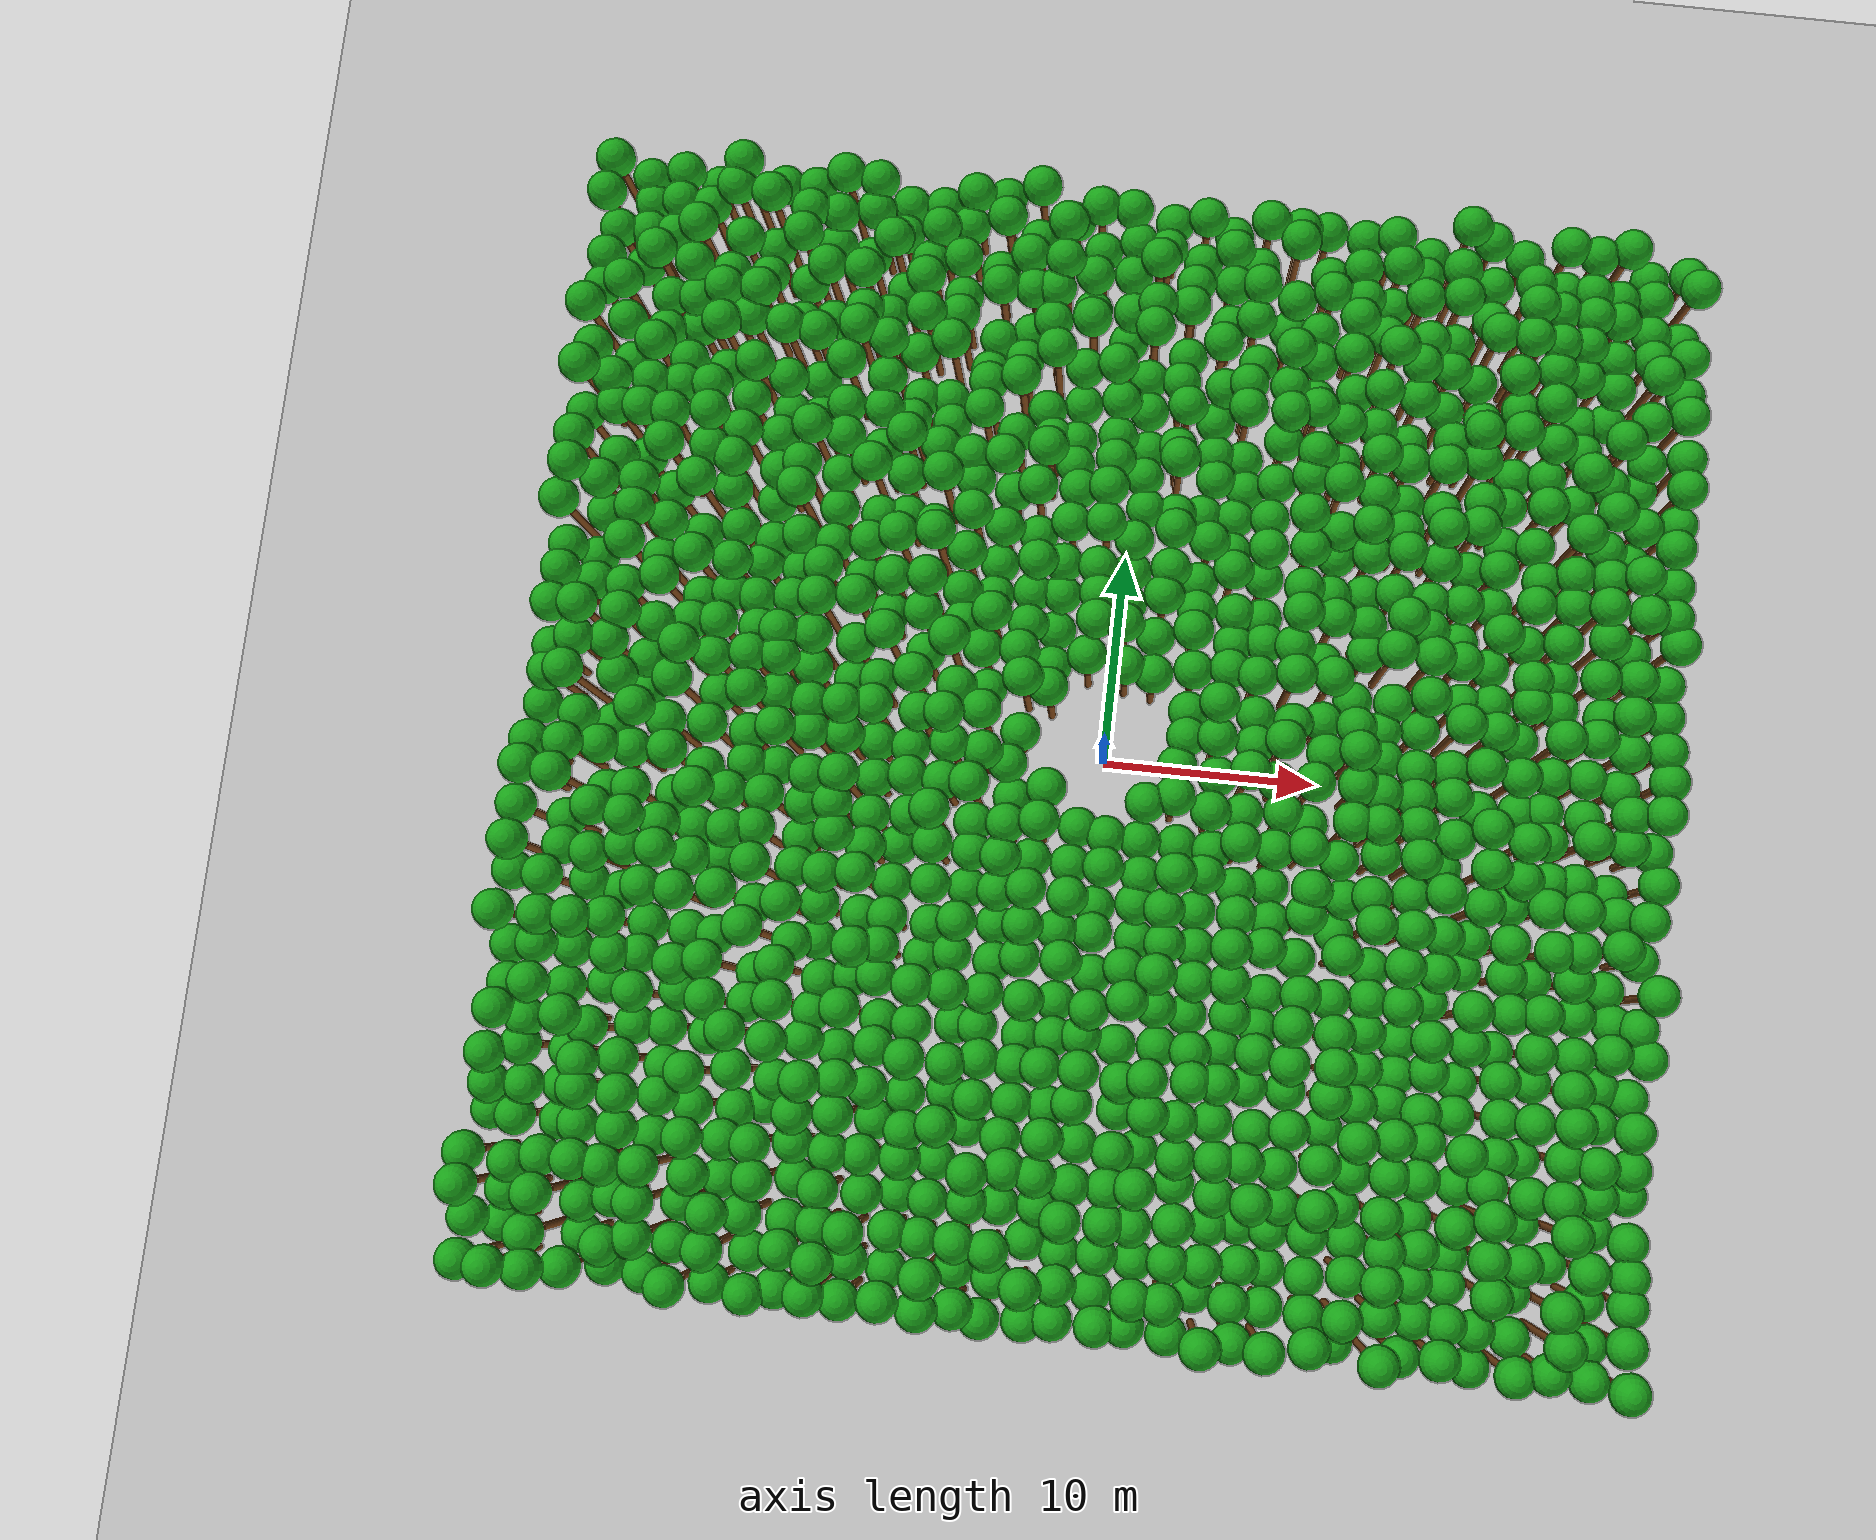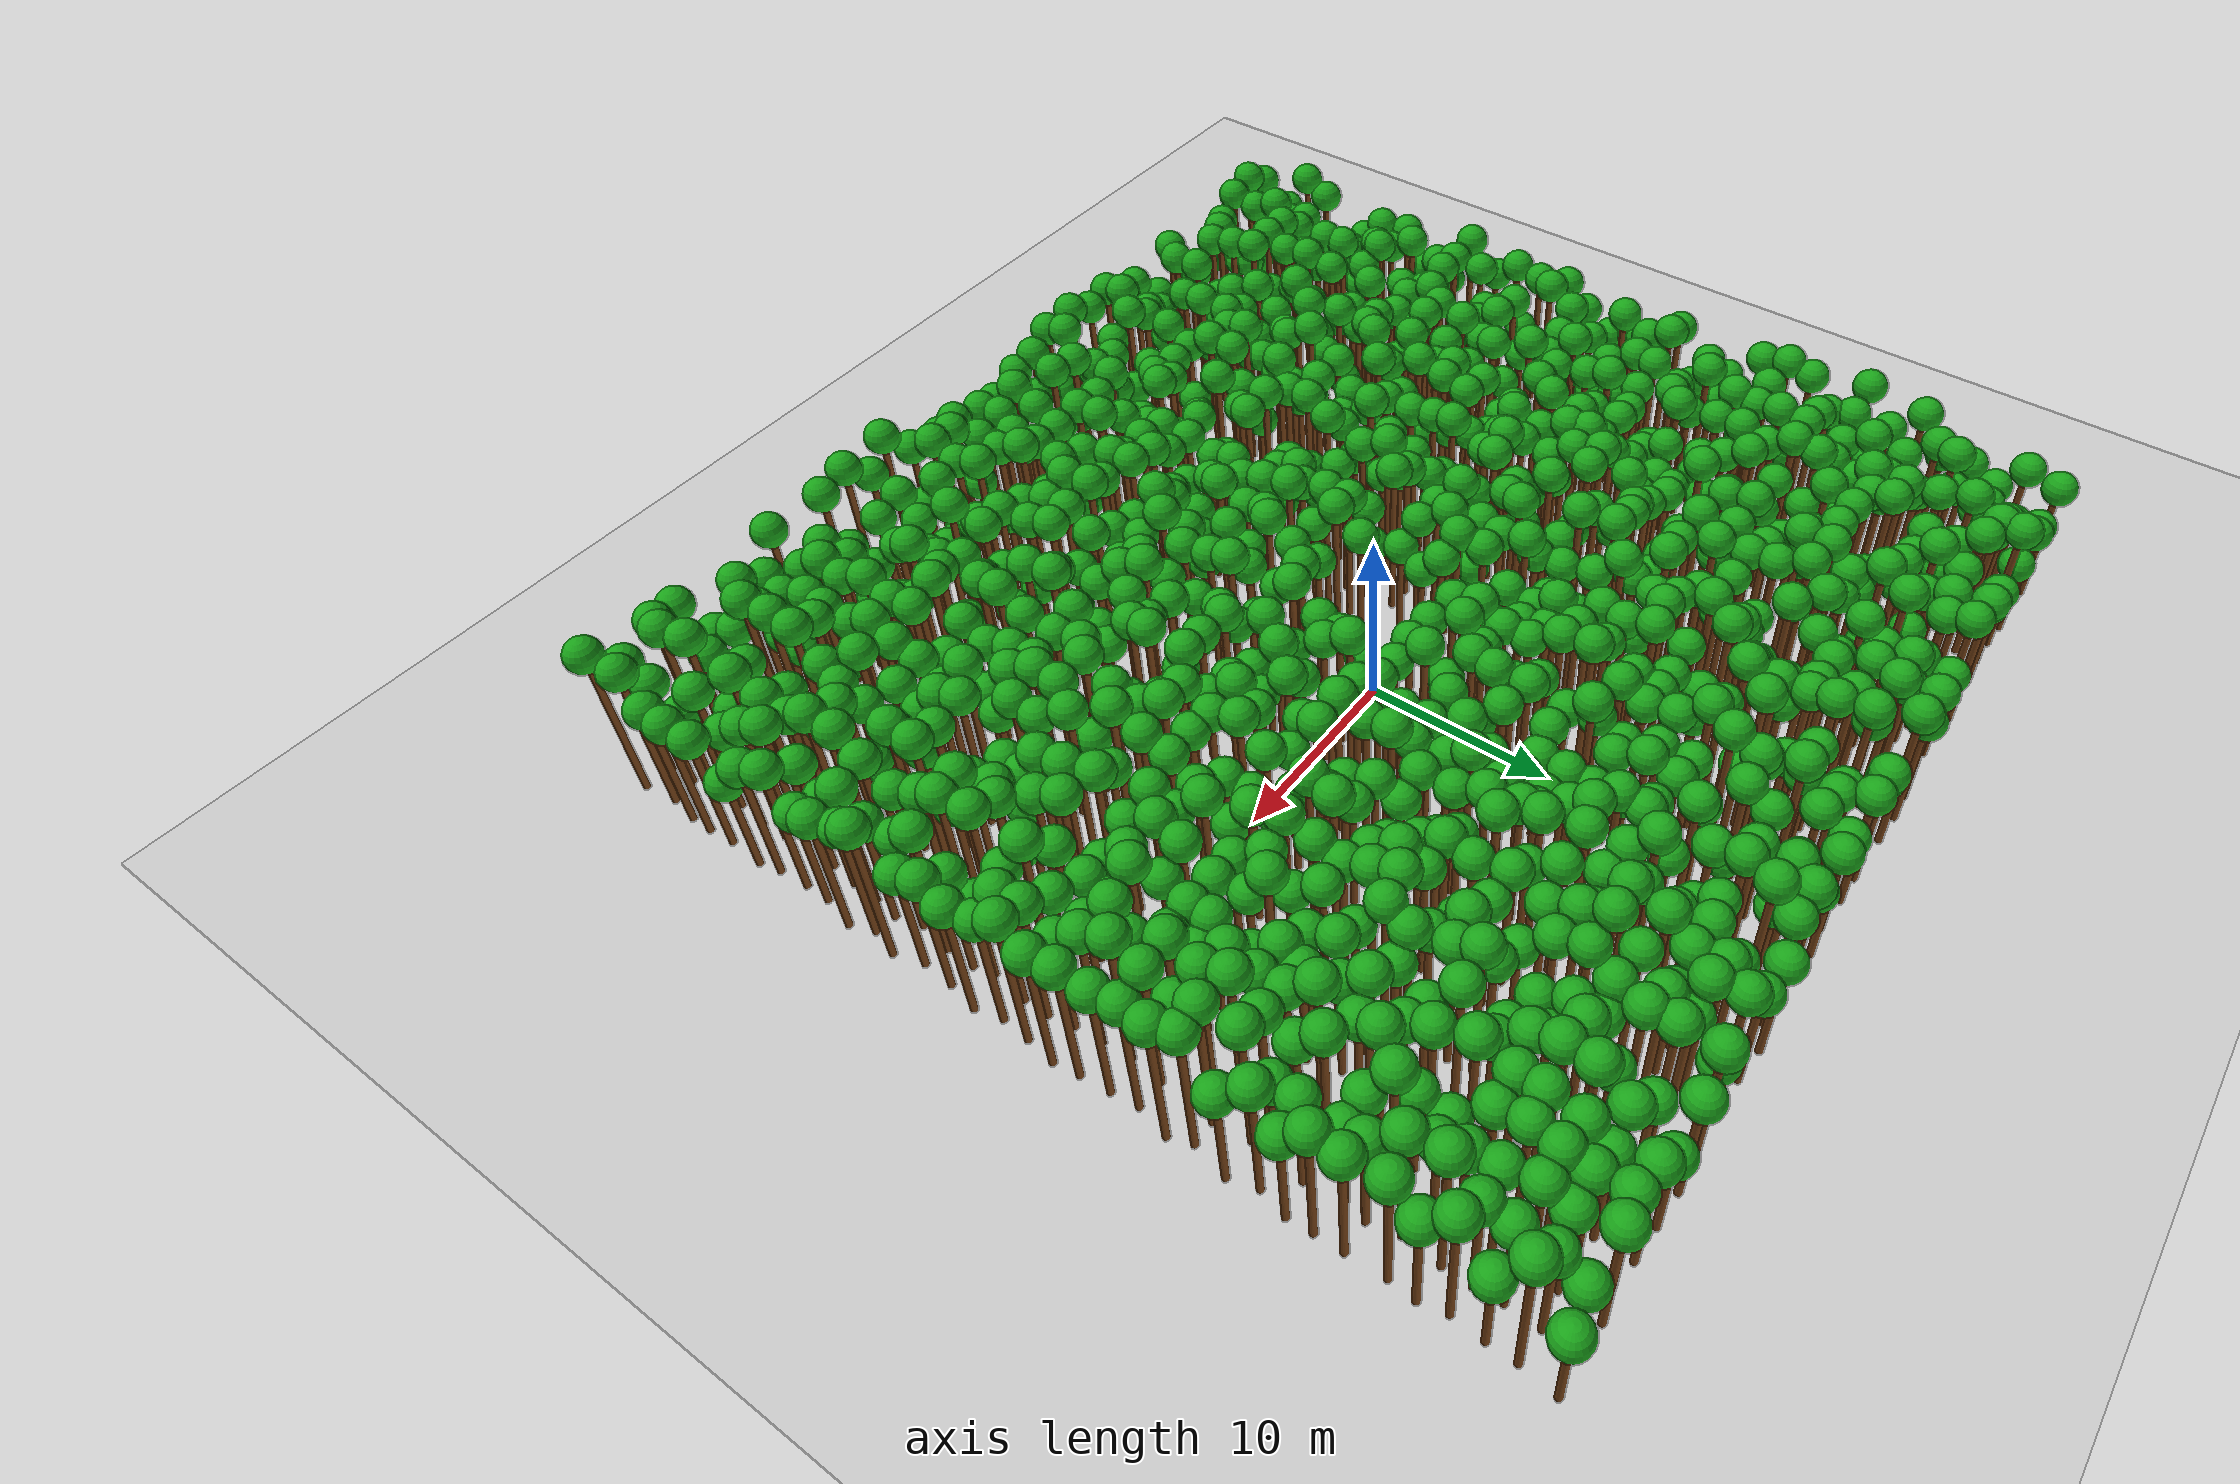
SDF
<?xml version="1.0" ?>
<sdf version="1.6">
<world name="forest_world">

  <include>
    <uri>model://sun</uri>
  </include>

  <include>
    <uri>model://ground_plane</uri>
  </include>

  <model name="tree_0">
    <static>true</static>

    <link name="trunk">

      <!-- 树干碰撞 -->
      <collision name="collision">
        <pose>-24.88 -24.96 3.96 0 0 0</pose>
        <geometry>
          <cylinder>
            <radius>0.18</radius>
            <length>7.92</length>
          </cylinder>
        </geometry>
      </collision>

      <!-- 树干视觉 -->
      <visual name="trunk_visual">
        <pose>-24.88 -24.96 3.96 0 0 0</pose>
        <geometry>
          <cylinder>
            <radius>0.18</radius>
            <length>7.92</length>
          </cylinder>
        </geometry>

        <material>
          <ambient>0.35 0.20 0.05 1</ambient>
          <diffuse>0.45 0.25 0.08 1</diffuse>
        </material>
      </visual>

      <!-- 树冠仅视觉 -->
      <visual name="leaf_visual">
        <pose>-24.88 -24.96 8.37 0 0 0</pose>

        <geometry>
          <sphere>
            <radius>0.9</radius>
          </sphere>
        </geometry>

        <material>
          <ambient>0.05 0.45 0.05 1</ambient>
          <diffuse>0.10 0.65 0.10 1</diffuse>
        </material>

      </visual>

    </link>

  </model>

  <model name="tree_1">
    <static>true</static>

    <link name="trunk">

      <!-- 树干碰撞 -->
      <collision name="collision">
        <pose>-25.00 -23.27 3.32 0 0 0</pose>
        <geometry>
          <cylinder>
            <radius>0.18</radius>
            <length>6.64</length>
          </cylinder>
        </geometry>
      </collision>

      <!-- 树干视觉 -->
      <visual name="trunk_visual">
        <pose>-25.00 -23.27 3.32 0 0 0</pose>
        <geometry>
          <cylinder>
            <radius>0.18</radius>
            <length>6.64</length>
          </cylinder>
        </geometry>

        <material>
          <ambient>0.35 0.20 0.05 1</ambient>
          <diffuse>0.45 0.25 0.08 1</diffuse>
        </material>
      </visual>

      <!-- 树冠仅视觉 -->
      <visual name="leaf_visual">
        <pose>-25.00 -23.27 7.09 0 0 0</pose>

        <geometry>
          <sphere>
            <radius>0.9</radius>
          </sphere>
        </geometry>

        <material>
          <ambient>0.05 0.45 0.05 1</ambient>
          <diffuse>0.10 0.65 0.10 1</diffuse>
        </material>

      </visual>

    </link>

  </model>

  <model name="tree_2">
    <static>true</static>

    <link name="trunk">

      <!-- 树干碰撞 -->
      <collision name="collision">
        <pose>-25.05 -21.80 4.49 0 0 0</pose>
        <geometry>
          <cylinder>
            <radius>0.18</radius>
            <length>8.98</length>
          </cylinder>
        </geometry>
      </collision>

      <!-- 树干视觉 -->
      <visual name="trunk_visual">
        <pose>-25.05 -21.80 4.49 0 0 0</pose>
        <geometry>
          <cylinder>
            <radius>0.18</radius>
            <length>8.98</length>
          </cylinder>
        </geometry>

        <material>
          <ambient>0.35 0.20 0.05 1</ambient>
          <diffuse>0.45 0.25 0.08 1</diffuse>
        </material>
      </visual>

      <!-- 树冠仅视觉 -->
      <visual name="leaf_visual">
        <pose>-25.05 -21.80 9.43 0 0 0</pose>

        <geometry>
          <sphere>
            <radius>0.9</radius>
          </sphere>
        </geometry>

        <material>
          <ambient>0.05 0.45 0.05 1</ambient>
          <diffuse>0.10 0.65 0.10 1</diffuse>
        </material>

      </visual>

    </link>

  </model>

  <model name="tree_3">
    <static>true</static>

    <link name="trunk">

      <!-- 树干碰撞 -->
      <collision name="collision">
        <pose>-25.14 -20.49 4.09 0 0 0</pose>
        <geometry>
          <cylinder>
            <radius>0.18</radius>
            <length>8.19</length>
          </cylinder>
        </geometry>
      </collision>

      <!-- 树干视觉 -->
      <visual name="trunk_visual">
        <pose>-25.14 -20.49 4.09 0 0 0</pose>
        <geometry>
          <cylinder>
            <radius>0.18</radius>
            <length>8.19</length>
          </cylinder>
        </geometry>

        <material>
          <ambient>0.35 0.20 0.05 1</ambient>
          <diffuse>0.45 0.25 0.08 1</diffuse>
        </material>
      </visual>

      <!-- 树冠仅视觉 -->
      <visual name="leaf_visual">
        <pose>-25.14 -20.49 8.64 0 0 0</pose>

        <geometry>
          <sphere>
            <radius>0.9</radius>
          </sphere>
        </geometry>

        <material>
          <ambient>0.05 0.45 0.05 1</ambient>
          <diffuse>0.10 0.65 0.10 1</diffuse>
        </material>

      </visual>

    </link>

  </model>

  <model name="tree_4">
    <static>true</static>

    <link name="trunk">

      <!-- 树干碰撞 -->
      <collision name="collision">
        <pose>-25.03 -18.75 2.57 0 0 0</pose>
        <geometry>
          <cylinder>
            <radius>0.18</radius>
            <length>5.14</length>
          </cylinder>
        </geometry>
      </collision>

      <!-- 树干视觉 -->
      <visual name="trunk_visual">
        <pose>-25.03 -18.75 2.57 0 0 0</pose>
        <geometry>
          <cylinder>
            <radius>0.18</radius>
            <length>5.14</length>
          </cylinder>
        </geometry>

        <material>
          <ambient>0.35 0.20 0.05 1</ambient>
          <diffuse>0.45 0.25 0.08 1</diffuse>
        </material>
      </visual>

      <!-- 树冠仅视觉 -->
      <visual name="leaf_visual">
        <pose>-25.03 -18.75 5.59 0 0 0</pose>

        <geometry>
          <sphere>
            <radius>0.9</radius>
          </sphere>
        </geometry>

        <material>
          <ambient>0.05 0.45 0.05 1</ambient>
          <diffuse>0.10 0.65 0.10 1</diffuse>
        </material>

      </visual>

    </link>

  </model>

  <model name="tree_5">
    <static>true</static>

    <link name="trunk">

      <!-- 树干碰撞 -->
      <collision name="collision">
        <pose>-24.94 -17.55 3.31 0 0 0</pose>
        <geometry>
          <cylinder>
            <radius>0.18</radius>
            <length>6.62</length>
          </cylinder>
        </geometry>
      </collision>

      <!-- 树干视觉 -->
      <visual name="trunk_visual">
        <pose>-24.94 -17.55 3.31 0 0 0</pose>
        <geometry>
          <cylinder>
            <radius>0.18</radius>
            <length>6.62</length>
          </cylinder>
        </geometry>

        <material>
          <ambient>0.35 0.20 0.05 1</ambient>
          <diffuse>0.45 0.25 0.08 1</diffuse>
        </material>
      </visual>

      <!-- 树冠仅视觉 -->
      <visual name="leaf_visual">
        <pose>-24.94 -17.55 7.07 0 0 0</pose>

        <geometry>
          <sphere>
            <radius>0.9</radius>
          </sphere>
        </geometry>

        <material>
          <ambient>0.05 0.45 0.05 1</ambient>
          <diffuse>0.10 0.65 0.10 1</diffuse>
        </material>

      </visual>

    </link>

  </model>

  <model name="tree_6">
    <static>true</static>

    <link name="trunk">

      <!-- 树干碰撞 -->
      <collision name="collision">
        <pose>-24.91 -16.24 3.97 0 0 0</pose>
        <geometry>
          <cylinder>
            <radius>0.18</radius>
            <length>7.94</length>
          </cylinder>
        </geometry>
      </collision>

      <!-- 树干视觉 -->
      <visual name="trunk_visual">
        <pose>-24.91 -16.24 3.97 0 0 0</pose>
        <geometry>
          <cylinder>
            <radius>0.18</radius>
            <length>7.94</length>
          </cylinder>
        </geometry>

        <material>
          <ambient>0.35 0.20 0.05 1</ambient>
          <diffuse>0.45 0.25 0.08 1</diffuse>
        </material>
      </visual>

      <!-- 树冠仅视觉 -->
      <visual name="leaf_visual">
        <pose>-24.91 -16.24 8.39 0 0 0</pose>

        <geometry>
          <sphere>
            <radius>0.9</radius>
          </sphere>
        </geometry>

        <material>
          <ambient>0.05 0.45 0.05 1</ambient>
          <diffuse>0.10 0.65 0.10 1</diffuse>
        </material>

      </visual>

    </link>

  </model>

  <model name="tree_7">
    <static>true</static>

    <link name="trunk">

      <!-- 树干碰撞 -->
      <collision name="collision">
        <pose>-24.75 -14.36 4.12 0 0 0</pose>
        <geometry>
          <cylinder>
            <radius>0.18</radius>
            <length>8.24</length>
          </cylinder>
        </geometry>
      </collision>

      <!-- 树干视觉 -->
      <visual name="trunk_visual">
        <pose>-24.75 -14.36 4.12 0 0 0</pose>
        <geometry>
          <cylinder>
            <radius>0.18</radius>
            <length>8.24</length>
          </cylinder>
        </geometry>

        <material>
          <ambient>0.35 0.20 0.05 1</ambient>
          <diffuse>0.45 0.25 0.08 1</diffuse>
        </material>
      </visual>

      <!-- 树冠仅视觉 -->
      <visual name="leaf_visual">
        <pose>-24.75 -14.36 8.69 0 0 0</pose>

        <geometry>
          <sphere>
            <radius>0.9</radius>
          </sphere>
        </geometry>

        <material>
          <ambient>0.05 0.45 0.05 1</ambient>
          <diffuse>0.10 0.65 0.10 1</diffuse>
        </material>

      </visual>

    </link>

  </model>

  <model name="tree_8">
    <static>true</static>

    <link name="trunk">

      <!-- 树干碰撞 -->
      <collision name="collision">
        <pose>-24.87 -13.18 3.07 0 0 0</pose>
        <geometry>
          <cylinder>
            <radius>0.18</radius>
            <length>6.14</length>
          </cylinder>
        </geometry>
      </collision>

      <!-- 树干视觉 -->
      <visual name="trunk_visual">
        <pose>-24.87 -13.18 3.07 0 0 0</pose>
        <geometry>
          <cylinder>
            <radius>0.18</radius>
            <length>6.14</length>
          </cylinder>
        </geometry>

        <material>
          <ambient>0.35 0.20 0.05 1</ambient>
          <diffuse>0.45 0.25 0.08 1</diffuse>
        </material>
      </visual>

      <!-- 树冠仅视觉 -->
      <visual name="leaf_visual">
        <pose>-24.87 -13.18 6.59 0 0 0</pose>

        <geometry>
          <sphere>
            <radius>0.9</radius>
          </sphere>
        </geometry>

        <material>
          <ambient>0.05 0.45 0.05 1</ambient>
          <diffuse>0.10 0.65 0.10 1</diffuse>
        </material>

      </visual>

    </link>

  </model>

  <model name="tree_9">
    <static>true</static>

    <link name="trunk">

      <!-- 树干碰撞 -->
      <collision name="collision">
        <pose>-25.08 -11.53 2.87 0 0 0</pose>
        <geometry>
          <cylinder>
            <radius>0.18</radius>
            <length>5.75</length>
          </cylinder>
        </geometry>
      </collision>

      <!-- 树干视觉 -->
      <visual name="trunk_visual">
        <pose>-25.08 -11.53 2.87 0 0 0</pose>
        <geometry>
          <cylinder>
            <radius>0.18</radius>
            <length>5.75</length>
          </cylinder>
        </geometry>

        <material>
          <ambient>0.35 0.20 0.05 1</ambient>
          <diffuse>0.45 0.25 0.08 1</diffuse>
        </material>
      </visual>

      <!-- 树冠仅视觉 -->
      <visual name="leaf_visual">
        <pose>-25.08 -11.53 6.20 0 0 0</pose>

        <geometry>
          <sphere>
            <radius>0.9</radius>
          </sphere>
        </geometry>

        <material>
          <ambient>0.05 0.45 0.05 1</ambient>
          <diffuse>0.10 0.65 0.10 1</diffuse>
        </material>

      </visual>

    </link>

  </model>

  <model name="tree_10">
    <static>true</static>

    <link name="trunk">

      <!-- 树干碰撞 -->
      <collision name="collision">
        <pose>-25.20 -10.22 4.39 0 0 0</pose>
        <geometry>
          <cylinder>
            <radius>0.18</radius>
            <length>8.78</length>
          </cylinder>
        </geometry>
      </collision>

      <!-- 树干视觉 -->
      <visual name="trunk_visual">
        <pose>-25.20 -10.22 4.39 0 0 0</pose>
        <geometry>
          <cylinder>
            <radius>0.18</radius>
            <length>8.78</length>
          </cylinder>
        </geometry>

        <material>
          <ambient>0.35 0.20 0.05 1</ambient>
          <diffuse>0.45 0.25 0.08 1</diffuse>
        </material>
      </visual>

      <!-- 树冠仅视觉 -->
      <visual name="leaf_visual">
        <pose>-25.20 -10.22 9.23 0 0 0</pose>

        <geometry>
          <sphere>
            <radius>0.9</radius>
          </sphere>
        </geometry>

        <material>
          <ambient>0.05 0.45 0.05 1</ambient>
          <diffuse>0.10 0.65 0.10 1</diffuse>
        </material>

      </visual>

    </link>

  </model>

  <model name="tree_11">
    <static>true</static>

    <link name="trunk">

      <!-- 树干碰撞 -->
      <collision name="collision">
        <pose>-25.04 -8.38 3.65 0 0 0</pose>
        <geometry>
          <cylinder>
            <radius>0.18</radius>
            <length>7.29</length>
          </cylinder>
        </geometry>
      </collision>

      <!-- 树干视觉 -->
      <visual name="trunk_visual">
        <pose>-25.04 -8.38 3.65 0 0 0</pose>
        <geometry>
          <cylinder>
            <radius>0.18</radius>
            <length>7.29</length>
          </cylinder>
        </geometry>

        <material>
          <ambient>0.35 0.20 0.05 1</ambient>
          <diffuse>0.45 0.25 0.08 1</diffuse>
        </material>
      </visual>

      <!-- 树冠仅视觉 -->
      <visual name="leaf_visual">
        <pose>-25.04 -8.38 7.74 0 0 0</pose>

        <geometry>
          <sphere>
            <radius>0.9</radius>
          </sphere>
        </geometry>

        <material>
          <ambient>0.05 0.45 0.05 1</ambient>
          <diffuse>0.10 0.65 0.10 1</diffuse>
        </material>

      </visual>

    </link>

  </model>

  <model name="tree_12">
    <static>true</static>

    <link name="trunk">

      <!-- 树干碰撞 -->
      <collision name="collision">
        <pose>-25.20 -7.11 4.11 0 0 0</pose>
        <geometry>
          <cylinder>
            <radius>0.18</radius>
            <length>8.22</length>
          </cylinder>
        </geometry>
      </collision>

      <!-- 树干视觉 -->
      <visual name="trunk_visual">
        <pose>-25.20 -7.11 4.11 0 0 0</pose>
        <geometry>
          <cylinder>
            <radius>0.18</radius>
            <length>8.22</length>
          </cylinder>
        </geometry>

        <material>
          <ambient>0.35 0.20 0.05 1</ambient>
          <diffuse>0.45 0.25 0.08 1</diffuse>
        </material>
      </visual>

      <!-- 树冠仅视觉 -->
      <visual name="leaf_visual">
        <pose>-25.20 -7.11 8.67 0 0 0</pose>

        <geometry>
          <sphere>
            <radius>0.9</radius>
          </sphere>
        </geometry>

        <material>
          <ambient>0.05 0.45 0.05 1</ambient>
          <diffuse>0.10 0.65 0.10 1</diffuse>
        </material>

      </visual>

    </link>

  </model>

  <model name="tree_13">
    <static>true</static>

    <link name="trunk">

      <!-- 树干碰撞 -->
      <collision name="collision">
        <pose>-25.10 -5.55 3.99 0 0 0</pose>
        <geometry>
          <cylinder>
            <radius>0.18</radius>
            <length>7.98</length>
          </cylinder>
        </geometry>
      </collision>

      <!-- 树干视觉 -->
      <visual name="trunk_visual">
        <pose>-25.10 -5.55 3.99 0 0 0</pose>
        <geometry>
          <cylinder>
            <radius>0.18</radius>
            <length>7.98</length>
          </cylinder>
        </geometry>

        <material>
          <ambient>0.35 0.20 0.05 1</ambient>
          <diffuse>0.45 0.25 0.08 1</diffuse>
        </material>
      </visual>

      <!-- 树冠仅视觉 -->
      <visual name="leaf_visual">
        <pose>-25.10 -5.55 8.43 0 0 0</pose>

        <geometry>
          <sphere>
            <radius>0.9</radius>
          </sphere>
        </geometry>

        <material>
          <ambient>0.05 0.45 0.05 1</ambient>
          <diffuse>0.10 0.65 0.10 1</diffuse>
        </material>

      </visual>

    </link>

  </model>

  <model name="tree_14">
    <static>true</static>

    <link name="trunk">

      <!-- 树干碰撞 -->
      <collision name="collision">
        <pose>-25.12 -3.82 4.18 0 0 0</pose>
        <geometry>
          <cylinder>
            <radius>0.18</radius>
            <length>8.36</length>
          </cylinder>
        </geometry>
      </collision>

      <!-- 树干视觉 -->
      <visual name="trunk_visual">
        <pose>-25.12 -3.82 4.18 0 0 0</pose>
        <geometry>
          <cylinder>
            <radius>0.18</radius>
            <length>8.36</length>
          </cylinder>
        </geometry>

        <material>
          <ambient>0.35 0.20 0.05 1</ambient>
          <diffuse>0.45 0.25 0.08 1</diffuse>
        </material>
      </visual>

      <!-- 树冠仅视觉 -->
      <visual name="leaf_visual">
        <pose>-25.12 -3.82 8.81 0 0 0</pose>

        <geometry>
          <sphere>
            <radius>0.9</radius>
          </sphere>
        </geometry>

        <material>
          <ambient>0.05 0.45 0.05 1</ambient>
          <diffuse>0.10 0.65 0.10 1</diffuse>
        </material>

      </visual>

    </link>

  </model>

  <model name="tree_15">
    <static>true</static>

    <link name="trunk">

      <!-- 树干碰撞 -->
      <collision name="collision">
        <pose>-25.21 -2.56 3.51 0 0 0</pose>
        <geometry>
          <cylinder>
            <radius>0.18</radius>
            <length>7.01</length>
          </cylinder>
        </geometry>
      </collision>

      <!-- 树干视觉 -->
      <visual name="trunk_visual">
        <pose>-25.21 -2.56 3.51 0 0 0</pose>
        <geometry>
          <cylinder>
            <radius>0.18</radius>
            <length>7.01</length>
          </cylinder>
        </geometry>

        <material>
          <ambient>0.35 0.20 0.05 1</ambient>
          <diffuse>0.45 0.25 0.08 1</diffuse>
        </material>
      </visual>

      <!-- 树冠仅视觉 -->
      <visual name="leaf_visual">
        <pose>-25.21 -2.56 7.46 0 0 0</pose>

        <geometry>
          <sphere>
            <radius>0.9</radius>
          </sphere>
        </geometry>

        <material>
          <ambient>0.05 0.45 0.05 1</ambient>
          <diffuse>0.10 0.65 0.10 1</diffuse>
        </material>

      </visual>

    </link>

  </model>

  <model name="tree_16">
    <static>true</static>

    <link name="trunk">

      <!-- 树干碰撞 -->
      <collision name="collision">
        <pose>-25.03 -0.84 3.09 0 0 0</pose>
        <geometry>
          <cylinder>
            <radius>0.18</radius>
            <length>6.18</length>
          </cylinder>
        </geometry>
      </collision>

      <!-- 树干视觉 -->
      <visual name="trunk_visual">
        <pose>-25.03 -0.84 3.09 0 0 0</pose>
        <geometry>
          <cylinder>
            <radius>0.18</radius>
            <length>6.18</length>
          </cylinder>
        </geometry>

        <material>
          <ambient>0.35 0.20 0.05 1</ambient>
          <diffuse>0.45 0.25 0.08 1</diffuse>
        </material>
      </visual>

      <!-- 树冠仅视觉 -->
      <visual name="leaf_visual">
        <pose>-25.03 -0.84 6.63 0 0 0</pose>

        <geometry>
          <sphere>
            <radius>0.9</radius>
          </sphere>
        </geometry>

        <material>
          <ambient>0.05 0.45 0.05 1</ambient>
          <diffuse>0.10 0.65 0.10 1</diffuse>
        </material>

      </visual>

    </link>

  </model>

  <model name="tree_17">
    <static>true</static>

    <link name="trunk">

      <!-- 树干碰撞 -->
      <collision name="collision">
        <pose>-24.92 0.60 3.38 0 0 0</pose>
        <geometry>
          <cylinder>
            <radius>0.18</radius>
            <length>6.77</length>
          </cylinder>
        </geometry>
      </collision>

      <!-- 树干视觉 -->
      <visual name="trunk_visual">
        <pose>-24.92 0.60 3.38 0 0 0</pose>
        <geometry>
          <cylinder>
            <radius>0.18</radius>
            <length>6.77</length>
          </cylinder>
        </geometry>

        <material>
          <ambient>0.35 0.20 0.05 1</ambient>
          <diffuse>0.45 0.25 0.08 1</diffuse>
        </material>
      </visual>

      <!-- 树冠仅视觉 -->
      <visual name="leaf_visual">
        <pose>-24.92 0.60 7.22 0 0 0</pose>

        <geometry>
          <sphere>
            <radius>0.9</radius>
          </sphere>
        </geometry>

        <material>
          <ambient>0.05 0.45 0.05 1</ambient>
          <diffuse>0.10 0.65 0.10 1</diffuse>
        </material>

      </visual>

    </link>

  </model>

  <model name="tree_18">
    <static>true</static>

    <link name="trunk">

      <!-- 树干碰撞 -->
      <collision name="collision">
        <pose>-24.95 1.77 3.20 0 0 0</pose>
        <geometry>
          <cylinder>
            <radius>0.18</radius>
            <length>6.41</length>
          </cylinder>
        </geometry>
      </collision>

      <!-- 树干视觉 -->
      <visual name="trunk_visual">
        <pose>-24.95 1.77 3.20 0 0 0</pose>
        <geometry>
          <cylinder>
            <radius>0.18</radius>
            <length>6.41</length>
          </cylinder>
        </geometry>

        <material>
          <ambient>0.35 0.20 0.05 1</ambient>
          <diffuse>0.45 0.25 0.08 1</diffuse>
        </material>
      </visual>

      <!-- 树冠仅视觉 -->
      <visual name="leaf_visual">
        <pose>-24.95 1.77 6.86 0 0 0</pose>

        <geometry>
          <sphere>
            <radius>0.9</radius>
          </sphere>
        </geometry>

        <material>
          <ambient>0.05 0.45 0.05 1</ambient>
          <diffuse>0.10 0.65 0.10 1</diffuse>
        </material>

      </visual>

    </link>

  </model>

  <model name="tree_19">
    <static>true</static>

    <link name="trunk">

      <!-- 树干碰撞 -->
      <collision name="collision">
        <pose>-24.75 3.40 4.20 0 0 0</pose>
        <geometry>
          <cylinder>
            <radius>0.18</radius>
            <length>8.40</length>
          </cylinder>
        </geometry>
      </collision>

      <!-- 树干视觉 -->
      <visual name="trunk_visual">
        <pose>-24.75 3.40 4.20 0 0 0</pose>
        <geometry>
          <cylinder>
            <radius>0.18</radius>
            <length>8.40</length>
          </cylinder>
        </geometry>

        <material>
          <ambient>0.35 0.20 0.05 1</ambient>
          <diffuse>0.45 0.25 0.08 1</diffuse>
        </material>
      </visual>

      <!-- 树冠仅视觉 -->
      <visual name="leaf_visual">
        <pose>-24.75 3.40 8.85 0 0 0</pose>

        <geometry>
          <sphere>
            <radius>0.9</radius>
          </sphere>
        </geometry>

        <material>
          <ambient>0.05 0.45 0.05 1</ambient>
          <diffuse>0.10 0.65 0.10 1</diffuse>
        </material>

      </visual>

    </link>

  </model>

  <model name="tree_20">
    <static>true</static>

    <link name="trunk">

      <!-- 树干碰撞 -->
      <collision name="collision">
        <pose>-24.97 5.24 3.43 0 0 0</pose>
        <geometry>
          <cylinder>
            <radius>0.18</radius>
            <length>6.85</length>
          </cylinder>
        </geometry>
      </collision>

      <!-- 树干视觉 -->
      <visual name="trunk_visual">
        <pose>-24.97 5.24 3.43 0 0 0</pose>
        <geometry>
          <cylinder>
            <radius>0.18</radius>
            <length>6.85</length>
          </cylinder>
        </geometry>

        <material>
          <ambient>0.35 0.20 0.05 1</ambient>
          <diffuse>0.45 0.25 0.08 1</diffuse>
        </material>
      </visual>

      <!-- 树冠仅视觉 -->
      <visual name="leaf_visual">
        <pose>-24.97 5.24 7.30 0 0 0</pose>

        <geometry>
          <sphere>
            <radius>0.9</radius>
          </sphere>
        </geometry>

        <material>
          <ambient>0.05 0.45 0.05 1</ambient>
          <diffuse>0.10 0.65 0.10 1</diffuse>
        </material>

      </visual>

    </link>

  </model>

  <model name="tree_21">
    <static>true</static>

    <link name="trunk">

      <!-- 树干碰撞 -->
      <collision name="collision">
        <pose>-24.89 6.44 3.20 0 0 0</pose>
        <geometry>
          <cylinder>
            <radius>0.18</radius>
            <length>6.39</length>
          </cylinder>
        </geometry>
      </collision>

      <!-- 树干视觉 -->
      <visual name="trunk_visual">
        <pose>-24.89 6.44 3.20 0 0 0</pose>
        <geometry>
          <cylinder>
            <radius>0.18</radius>
            <length>6.39</length>
          </cylinder>
        </geometry>

        <material>
          <ambient>0.35 0.20 0.05 1</ambient>
          <diffuse>0.45 0.25 0.08 1</diffuse>
        </material>
      </visual>

      <!-- 树冠仅视觉 -->
      <visual name="leaf_visual">
        <pose>-24.89 6.44 6.84 0 0 0</pose>

        <geometry>
          <sphere>
            <radius>0.9</radius>
          </sphere>
        </geometry>

        <material>
          <ambient>0.05 0.45 0.05 1</ambient>
          <diffuse>0.10 0.65 0.10 1</diffuse>
        </material>

      </visual>

    </link>

  </model>

  <model name="tree_22">
    <static>true</static>

    <link name="trunk">

      <!-- 树干碰撞 -->
      <collision name="collision">
        <pose>-25.14 8.16 4.05 0 0 0</pose>
        <geometry>
          <cylinder>
            <radius>0.18</radius>
            <length>8.10</length>
          </cylinder>
        </geometry>
      </collision>

      <!-- 树干视觉 -->
      <visual name="trunk_visual">
        <pose>-25.14 8.16 4.05 0 0 0</pose>
        <geometry>
          <cylinder>
            <radius>0.18</radius>
            <length>8.10</length>
          </cylinder>
        </geometry>

        <material>
          <ambient>0.35 0.20 0.05 1</ambient>
          <diffuse>0.45 0.25 0.08 1</diffuse>
        </material>
      </visual>

      <!-- 树冠仅视觉 -->
      <visual name="leaf_visual">
        <pose>-25.14 8.16 8.55 0 0 0</pose>

        <geometry>
          <sphere>
            <radius>0.9</radius>
          </sphere>
        </geometry>

        <material>
          <ambient>0.05 0.45 0.05 1</ambient>
          <diffuse>0.10 0.65 0.10 1</diffuse>
        </material>

      </visual>

    </link>

  </model>

  <model name="tree_23">
    <static>true</static>

    <link name="trunk">

      <!-- 树干碰撞 -->
      <collision name="collision">
        <pose>-24.80 9.70 4.37 0 0 0</pose>
        <geometry>
          <cylinder>
            <radius>0.18</radius>
            <length>8.74</length>
          </cylinder>
        </geometry>
      </collision>

      <!-- 树干视觉 -->
      <visual name="trunk_visual">
        <pose>-24.80 9.70 4.37 0 0 0</pose>
        <geometry>
          <cylinder>
            <radius>0.18</radius>
            <length>8.74</length>
          </cylinder>
        </geometry>

        <material>
          <ambient>0.35 0.20 0.05 1</ambient>
          <diffuse>0.45 0.25 0.08 1</diffuse>
        </material>
      </visual>

      <!-- 树冠仅视觉 -->
      <visual name="leaf_visual">
        <pose>-24.80 9.70 9.19 0 0 0</pose>

        <geometry>
          <sphere>
            <radius>0.9</radius>
          </sphere>
        </geometry>

        <material>
          <ambient>0.05 0.45 0.05 1</ambient>
          <diffuse>0.10 0.65 0.10 1</diffuse>
        </material>

      </visual>

    </link>

  </model>

  <model name="tree_24">
    <static>true</static>

    <link name="trunk">

      <!-- 树干碰撞 -->
      <collision name="collision">
        <pose>-24.83 11.06 4.17 0 0 0</pose>
        <geometry>
          <cylinder>
            <radius>0.18</radius>
            <length>8.35</length>
          </cylinder>
        </geometry>
      </collision>

      <!-- 树干视觉 -->
      <visual name="trunk_visual">
        <pose>-24.83 11.06 4.17 0 0 0</pose>
        <geometry>
          <cylinder>
            <radius>0.18</radius>
            <length>8.35</length>
          </cylinder>
        </geometry>

        <material>
          <ambient>0.35 0.20 0.05 1</ambient>
          <diffuse>0.45 0.25 0.08 1</diffuse>
        </material>
      </visual>

      <!-- 树冠仅视觉 -->
      <visual name="leaf_visual">
        <pose>-24.83 11.06 8.80 0 0 0</pose>

        <geometry>
          <sphere>
            <radius>0.9</radius>
          </sphere>
        </geometry>

        <material>
          <ambient>0.05 0.45 0.05 1</ambient>
          <diffuse>0.10 0.65 0.10 1</diffuse>
        </material>

      </visual>

    </link>

  </model>

  <model name="tree_25">
    <static>true</static>

    <link name="trunk">

      <!-- 树干碰撞 -->
      <collision name="collision">
        <pose>-25.05 12.74 3.00 0 0 0</pose>
        <geometry>
          <cylinder>
            <radius>0.18</radius>
            <length>5.99</length>
          </cylinder>
        </geometry>
      </collision>

      <!-- 树干视觉 -->
      <visual name="trunk_visual">
        <pose>-25.05 12.74 3.00 0 0 0</pose>
        <geometry>
          <cylinder>
            <radius>0.18</radius>
            <length>5.99</length>
          </cylinder>
        </geometry>

        <material>
          <ambient>0.35 0.20 0.05 1</ambient>
          <diffuse>0.45 0.25 0.08 1</diffuse>
        </material>
      </visual>

      <!-- 树冠仅视觉 -->
      <visual name="leaf_visual">
        <pose>-25.05 12.74 6.44 0 0 0</pose>

        <geometry>
          <sphere>
            <radius>0.9</radius>
          </sphere>
        </geometry>

        <material>
          <ambient>0.05 0.45 0.05 1</ambient>
          <diffuse>0.10 0.65 0.10 1</diffuse>
        </material>

      </visual>

    </link>

  </model>

  <model name="tree_26">
    <static>true</static>

    <link name="trunk">

      <!-- 树干碰撞 -->
      <collision name="collision">
        <pose>-24.89 14.12 4.48 0 0 0</pose>
        <geometry>
          <cylinder>
            <radius>0.18</radius>
            <length>8.96</length>
          </cylinder>
        </geometry>
      </collision>

      <!-- 树干视觉 -->
      <visual name="trunk_visual">
        <pose>-24.89 14.12 4.48 0 0 0</pose>
        <geometry>
          <cylinder>
            <radius>0.18</radius>
            <length>8.96</length>
          </cylinder>
        </geometry>

        <material>
          <ambient>0.35 0.20 0.05 1</ambient>
          <diffuse>0.45 0.25 0.08 1</diffuse>
        </material>
      </visual>

      <!-- 树冠仅视觉 -->
      <visual name="leaf_visual">
        <pose>-24.89 14.12 9.41 0 0 0</pose>

        <geometry>
          <sphere>
            <radius>0.9</radius>
          </sphere>
        </geometry>

        <material>
          <ambient>0.05 0.45 0.05 1</ambient>
          <diffuse>0.10 0.65 0.10 1</diffuse>
        </material>

      </visual>

    </link>

  </model>

  <model name="tree_27">
    <static>true</static>

    <link name="trunk">

      <!-- 树干碰撞 -->
      <collision name="collision">
        <pose>-24.93 15.65 3.42 0 0 0</pose>
        <geometry>
          <cylinder>
            <radius>0.18</radius>
            <length>6.83</length>
          </cylinder>
        </geometry>
      </collision>

      <!-- 树干视觉 -->
      <visual name="trunk_visual">
        <pose>-24.93 15.65 3.42 0 0 0</pose>
        <geometry>
          <cylinder>
            <radius>0.18</radius>
            <length>6.83</length>
          </cylinder>
        </geometry>

        <material>
          <ambient>0.35 0.20 0.05 1</ambient>
          <diffuse>0.45 0.25 0.08 1</diffuse>
        </material>
      </visual>

      <!-- 树冠仅视觉 -->
      <visual name="leaf_visual">
        <pose>-24.93 15.65 7.28 0 0 0</pose>

        <geometry>
          <sphere>
            <radius>0.9</radius>
          </sphere>
        </geometry>

        <material>
          <ambient>0.05 0.45 0.05 1</ambient>
          <diffuse>0.10 0.65 0.10 1</diffuse>
        </material>

      </visual>

    </link>

  </model>

  <model name="tree_28">
    <static>true</static>

    <link name="trunk">

      <!-- 树干碰撞 -->
      <collision name="collision">
        <pose>-25.17 17.17 4.15 0 0 0</pose>
        <geometry>
          <cylinder>
            <radius>0.18</radius>
            <length>8.31</length>
          </cylinder>
        </geometry>
      </collision>

      <!-- 树干视觉 -->
      <visual name="trunk_visual">
        <pose>-25.17 17.17 4.15 0 0 0</pose>
        <geometry>
          <cylinder>
            <radius>0.18</radius>
            <length>8.31</length>
          </cylinder>
        </geometry>

        <material>
          <ambient>0.35 0.20 0.05 1</ambient>
          <diffuse>0.45 0.25 0.08 1</diffuse>
        </material>
      </visual>

      <!-- 树冠仅视觉 -->
      <visual name="leaf_visual">
        <pose>-25.17 17.17 8.76 0 0 0</pose>

        <geometry>
          <sphere>
            <radius>0.9</radius>
          </sphere>
        </geometry>

        <material>
          <ambient>0.05 0.45 0.05 1</ambient>
          <diffuse>0.10 0.65 0.10 1</diffuse>
        </material>

      </visual>

    </link>

  </model>

  <model name="tree_29">
    <static>true</static>

    <link name="trunk">

      <!-- 树干碰撞 -->
      <collision name="collision">
        <pose>-24.95 18.63 3.23 0 0 0</pose>
        <geometry>
          <cylinder>
            <radius>0.18</radius>
            <length>6.47</length>
          </cylinder>
        </geometry>
      </collision>

      <!-- 树干视觉 -->
      <visual name="trunk_visual">
        <pose>-24.95 18.63 3.23 0 0 0</pose>
        <geometry>
          <cylinder>
            <radius>0.18</radius>
            <length>6.47</length>
          </cylinder>
        </geometry>

        <material>
          <ambient>0.35 0.20 0.05 1</ambient>
          <diffuse>0.45 0.25 0.08 1</diffuse>
        </material>
      </visual>

      <!-- 树冠仅视觉 -->
      <visual name="leaf_visual">
        <pose>-24.95 18.63 6.92 0 0 0</pose>

        <geometry>
          <sphere>
            <radius>0.9</radius>
          </sphere>
        </geometry>

        <material>
          <ambient>0.05 0.45 0.05 1</ambient>
          <diffuse>0.10 0.65 0.10 1</diffuse>
        </material>

      </visual>

    </link>

  </model>

  <model name="tree_30">
    <static>true</static>

    <link name="trunk">

      <!-- 树干碰撞 -->
      <collision name="collision">
        <pose>-25.01 20.08 3.24 0 0 0</pose>
        <geometry>
          <cylinder>
            <radius>0.18</radius>
            <length>6.48</length>
          </cylinder>
        </geometry>
      </collision>

      <!-- 树干视觉 -->
      <visual name="trunk_visual">
        <pose>-25.01 20.08 3.24 0 0 0</pose>
        <geometry>
          <cylinder>
            <radius>0.18</radius>
            <length>6.48</length>
          </cylinder>
        </geometry>

        <material>
          <ambient>0.35 0.20 0.05 1</ambient>
          <diffuse>0.45 0.25 0.08 1</diffuse>
        </material>
      </visual>

      <!-- 树冠仅视觉 -->
      <visual name="leaf_visual">
        <pose>-25.01 20.08 6.93 0 0 0</pose>

        <geometry>
          <sphere>
            <radius>0.9</radius>
          </sphere>
        </geometry>

        <material>
          <ambient>0.05 0.45 0.05 1</ambient>
          <diffuse>0.10 0.65 0.10 1</diffuse>
        </material>

      </visual>

    </link>

  </model>

  <model name="tree_31">
    <static>true</static>

    <link name="trunk">

      <!-- 树干碰撞 -->
      <collision name="collision">
        <pose>-24.75 21.60 2.95 0 0 0</pose>
        <geometry>
          <cylinder>
            <radius>0.18</radius>
            <length>5.90</length>
          </cylinder>
        </geometry>
      </collision>

      <!-- 树干视觉 -->
      <visual name="trunk_visual">
        <pose>-24.75 21.60 2.95 0 0 0</pose>
        <geometry>
          <cylinder>
            <radius>0.18</radius>
            <length>5.90</length>
          </cylinder>
        </geometry>

        <material>
          <ambient>0.35 0.20 0.05 1</ambient>
          <diffuse>0.45 0.25 0.08 1</diffuse>
        </material>
      </visual>

      <!-- 树冠仅视觉 -->
      <visual name="leaf_visual">
        <pose>-24.75 21.60 6.35 0 0 0</pose>

        <geometry>
          <sphere>
            <radius>0.9</radius>
          </sphere>
        </geometry>

        <material>
          <ambient>0.05 0.45 0.05 1</ambient>
          <diffuse>0.10 0.65 0.10 1</diffuse>
        </material>

      </visual>

    </link>

  </model>

  <model name="tree_32">
    <static>true</static>

    <link name="trunk">

      <!-- 树干碰撞 -->
      <collision name="collision">
        <pose>-25.21 22.82 3.62 0 0 0</pose>
        <geometry>
          <cylinder>
            <radius>0.18</radius>
            <length>7.24</length>
          </cylinder>
        </geometry>
      </collision>

      <!-- 树干视觉 -->
      <visual name="trunk_visual">
        <pose>-25.21 22.82 3.62 0 0 0</pose>
        <geometry>
          <cylinder>
            <radius>0.18</radius>
            <length>7.24</length>
          </cylinder>
        </geometry>

        <material>
          <ambient>0.35 0.20 0.05 1</ambient>
          <diffuse>0.45 0.25 0.08 1</diffuse>
        </material>
      </visual>

      <!-- 树冠仅视觉 -->
      <visual name="leaf_visual">
        <pose>-25.21 22.82 7.69 0 0 0</pose>

        <geometry>
          <sphere>
            <radius>0.9</radius>
          </sphere>
        </geometry>

        <material>
          <ambient>0.05 0.45 0.05 1</ambient>
          <diffuse>0.10 0.65 0.10 1</diffuse>
        </material>

      </visual>

    </link>

  </model>

  <model name="tree_33">
    <static>true</static>

    <link name="trunk">

      <!-- 树干碰撞 -->
      <collision name="collision">
        <pose>-25.12 24.55 3.44 0 0 0</pose>
        <geometry>
          <cylinder>
            <radius>0.18</radius>
            <length>6.89</length>
          </cylinder>
        </geometry>
      </collision>

      <!-- 树干视觉 -->
      <visual name="trunk_visual">
        <pose>-25.12 24.55 3.44 0 0 0</pose>
        <geometry>
          <cylinder>
            <radius>0.18</radius>
            <length>6.89</length>
          </cylinder>
        </geometry>

        <material>
          <ambient>0.35 0.20 0.05 1</ambient>
          <diffuse>0.45 0.25 0.08 1</diffuse>
        </material>
      </visual>

      <!-- 树冠仅视觉 -->
      <visual name="leaf_visual">
        <pose>-25.12 24.55 7.34 0 0 0</pose>

        <geometry>
          <sphere>
            <radius>0.9</radius>
          </sphere>
        </geometry>

        <material>
          <ambient>0.05 0.45 0.05 1</ambient>
          <diffuse>0.10 0.65 0.10 1</diffuse>
        </material>

      </visual>

    </link>

  </model>

  <model name="tree_34">
    <static>true</static>

    <link name="trunk">

      <!-- 树干碰撞 -->
      <collision name="collision">
        <pose>-23.46 -25.02 4.41 0 0 0</pose>
        <geometry>
          <cylinder>
            <radius>0.18</radius>
            <length>8.81</length>
          </cylinder>
        </geometry>
      </collision>

      <!-- 树干视觉 -->
      <visual name="trunk_visual">
        <pose>-23.46 -25.02 4.41 0 0 0</pose>
        <geometry>
          <cylinder>
            <radius>0.18</radius>
            <length>8.81</length>
          </cylinder>
        </geometry>

        <material>
          <ambient>0.35 0.20 0.05 1</ambient>
          <diffuse>0.45 0.25 0.08 1</diffuse>
        </material>
      </visual>

      <!-- 树冠仅视觉 -->
      <visual name="leaf_visual">
        <pose>-23.46 -25.02 9.26 0 0 0</pose>

        <geometry>
          <sphere>
            <radius>0.9</radius>
          </sphere>
        </geometry>

        <material>
          <ambient>0.05 0.45 0.05 1</ambient>
          <diffuse>0.10 0.65 0.10 1</diffuse>
        </material>

      </visual>

    </link>

  </model>

  <model name="tree_35">
    <static>true</static>

    <link name="trunk">

      <!-- 树干碰撞 -->
      <collision name="collision">
        <pose>-23.72 -23.42 2.88 0 0 0</pose>
        <geometry>
          <cylinder>
            <radius>0.18</radius>
            <length>5.76</length>
          </cylinder>
        </geometry>
      </collision>

      <!-- 树干视觉 -->
      <visual name="trunk_visual">
        <pose>-23.72 -23.42 2.88 0 0 0</pose>
        <geometry>
          <cylinder>
            <radius>0.18</radius>
            <length>5.76</length>
          </cylinder>
        </geometry>

        <material>
          <ambient>0.35 0.20 0.05 1</ambient>
          <diffuse>0.45 0.25 0.08 1</diffuse>
        </material>
      </visual>

      <!-- 树冠仅视觉 -->
      <visual name="leaf_visual">
        <pose>-23.72 -23.42 6.21 0 0 0</pose>

        <geometry>
          <sphere>
            <radius>0.9</radius>
          </sphere>
        </geometry>

        <material>
          <ambient>0.05 0.45 0.05 1</ambient>
          <diffuse>0.10 0.65 0.10 1</diffuse>
        </material>

      </visual>

    </link>

  </model>

  <model name="tree_36">
    <static>true</static>

    <link name="trunk">

      <!-- 树干碰撞 -->
      <collision name="collision">
        <pose>-23.43 -21.91 3.51 0 0 0</pose>
        <geometry>
          <cylinder>
            <radius>0.18</radius>
            <length>7.02</length>
          </cylinder>
        </geometry>
      </collision>

      <!-- 树干视觉 -->
      <visual name="trunk_visual">
        <pose>-23.43 -21.91 3.51 0 0 0</pose>
        <geometry>
          <cylinder>
            <radius>0.18</radius>
            <length>7.02</length>
          </cylinder>
        </geometry>

        <material>
          <ambient>0.35 0.20 0.05 1</ambient>
          <diffuse>0.45 0.25 0.08 1</diffuse>
        </material>
      </visual>

      <!-- 树冠仅视觉 -->
      <visual name="leaf_visual">
        <pose>-23.43 -21.91 7.47 0 0 0</pose>

        <geometry>
          <sphere>
            <radius>0.9</radius>
          </sphere>
        </geometry>

        <material>
          <ambient>0.05 0.45 0.05 1</ambient>
          <diffuse>0.10 0.65 0.10 1</diffuse>
        </material>

      </visual>

    </link>

  </model>

  <model name="tree_37">
    <static>true</static>

    <link name="trunk">

      <!-- 树干碰撞 -->
      <collision name="collision">
        <pose>-23.36 -20.73 3.79 0 0 0</pose>
        <geometry>
          <cylinder>
            <radius>0.18</radius>
            <length>7.57</length>
          </cylinder>
        </geometry>
      </collision>

      <!-- 树干视觉 -->
      <visual name="trunk_visual">
        <pose>-23.36 -20.73 3.79 0 0 0</pose>
        <geometry>
          <cylinder>
            <radius>0.18</radius>
            <length>7.57</length>
          </cylinder>
        </geometry>

        <material>
          <ambient>0.35 0.20 0.05 1</ambient>
          <diffuse>0.45 0.25 0.08 1</diffuse>
        </material>
      </visual>

      <!-- 树冠仅视觉 -->
      <visual name="leaf_visual">
        <pose>-23.36 -20.73 8.02 0 0 0</pose>

        <geometry>
          <sphere>
            <radius>0.9</radius>
          </sphere>
        </geometry>

        <material>
          <ambient>0.05 0.45 0.05 1</ambient>
          <diffuse>0.10 0.65 0.10 1</diffuse>
        </material>

      </visual>

    </link>

  </model>

  <model name="tree_38">
    <static>true</static>

    <link name="trunk">

      <!-- 树干碰撞 -->
      <collision name="collision">
        <pose>-23.69 -18.84 3.12 0 0 0</pose>
        <geometry>
          <cylinder>
            <radius>0.18</radius>
            <length>6.23</length>
          </cylinder>
        </geometry>
      </collision>

      <!-- 树干视觉 -->
      <visual name="trunk_visual">
        <pose>-23.69 -18.84 3.12 0 0 0</pose>
        <geometry>
          <cylinder>
            <radius>0.18</radius>
            <length>6.23</length>
          </cylinder>
        </geometry>

        <material>
          <ambient>0.35 0.20 0.05 1</ambient>
          <diffuse>0.45 0.25 0.08 1</diffuse>
        </material>
      </visual>

      <!-- 树冠仅视觉 -->
      <visual name="leaf_visual">
        <pose>-23.69 -18.84 6.68 0 0 0</pose>

        <geometry>
          <sphere>
            <radius>0.9</radius>
          </sphere>
        </geometry>

        <material>
          <ambient>0.05 0.45 0.05 1</ambient>
          <diffuse>0.10 0.65 0.10 1</diffuse>
        </material>

      </visual>

    </link>

  </model>

  <model name="tree_39">
    <static>true</static>

    <link name="trunk">

      <!-- 树干碰撞 -->
      <collision name="collision">
        <pose>-23.42 -17.47 3.27 0 0 0</pose>
        <geometry>
          <cylinder>
            <radius>0.18</radius>
            <length>6.55</length>
          </cylinder>
        </geometry>
      </collision>

      <!-- 树干视觉 -->
      <visual name="trunk_visual">
        <pose>-23.42 -17.47 3.27 0 0 0</pose>
        <geometry>
          <cylinder>
            <radius>0.18</radius>
            <length>6.55</length>
          </cylinder>
        </geometry>

        <material>
          <ambient>0.35 0.20 0.05 1</ambient>
          <diffuse>0.45 0.25 0.08 1</diffuse>
        </material>
      </visual>

      <!-- 树冠仅视觉 -->
      <visual name="leaf_visual">
        <pose>-23.42 -17.47 7.00 0 0 0</pose>

        <geometry>
          <sphere>
            <radius>0.9</radius>
          </sphere>
        </geometry>

        <material>
          <ambient>0.05 0.45 0.05 1</ambient>
          <diffuse>0.10 0.65 0.10 1</diffuse>
        </material>

      </visual>

    </link>

  </model>

  <model name="tree_40">
    <static>true</static>

    <link name="trunk">

      <!-- 树干碰撞 -->
      <collision name="collision">
        <pose>-23.54 -15.79 3.76 0 0 0</pose>
        <geometry>
          <cylinder>
            <radius>0.18</radius>
            <length>7.52</length>
          </cylinder>
        </geometry>
      </collision>

      <!-- 树干视觉 -->
      <visual name="trunk_visual">
        <pose>-23.54 -15.79 3.76 0 0 0</pose>
        <geometry>
          <cylinder>
            <radius>0.18</radius>
            <length>7.52</length>
          </cylinder>
        </geometry>

        <material>
          <ambient>0.35 0.20 0.05 1</ambient>
          <diffuse>0.45 0.25 0.08 1</diffuse>
        </material>
      </visual>

      <!-- 树冠仅视觉 -->
      <visual name="leaf_visual">
        <pose>-23.54 -15.79 7.97 0 0 0</pose>

        <geometry>
          <sphere>
            <radius>0.9</radius>
          </sphere>
        </geometry>

        <material>
          <ambient>0.05 0.45 0.05 1</ambient>
          <diffuse>0.10 0.65 0.10 1</diffuse>
        </material>

      </visual>

    </link>

  </model>

  <model name="tree_41">
    <static>true</static>

    <link name="trunk">

      <!-- 树干碰撞 -->
      <collision name="collision">
        <pose>-23.47 -14.62 3.85 0 0 0</pose>
        <geometry>
          <cylinder>
            <radius>0.18</radius>
            <length>7.70</length>
          </cylinder>
        </geometry>
      </collision>

      <!-- 树干视觉 -->
      <visual name="trunk_visual">
        <pose>-23.47 -14.62 3.85 0 0 0</pose>
        <geometry>
          <cylinder>
            <radius>0.18</radius>
            <length>7.70</length>
          </cylinder>
        </geometry>

        <material>
          <ambient>0.35 0.20 0.05 1</ambient>
          <diffuse>0.45 0.25 0.08 1</diffuse>
        </material>
      </visual>

      <!-- 树冠仅视觉 -->
      <visual name="leaf_visual">
        <pose>-23.47 -14.62 8.15 0 0 0</pose>

        <geometry>
          <sphere>
            <radius>0.9</radius>
          </sphere>
        </geometry>

        <material>
          <ambient>0.05 0.45 0.05 1</ambient>
          <diffuse>0.10 0.65 0.10 1</diffuse>
        </material>

      </visual>

    </link>

  </model>

  <model name="tree_42">
    <static>true</static>

    <link name="trunk">

      <!-- 树干碰撞 -->
      <collision name="collision">
        <pose>-23.32 -13.11 4.35 0 0 0</pose>
        <geometry>
          <cylinder>
            <radius>0.18</radius>
            <length>8.70</length>
          </cylinder>
        </geometry>
      </collision>

      <!-- 树干视觉 -->
      <visual name="trunk_visual">
        <pose>-23.32 -13.11 4.35 0 0 0</pose>
        <geometry>
          <cylinder>
            <radius>0.18</radius>
            <length>8.70</length>
          </cylinder>
        </geometry>

        <material>
          <ambient>0.35 0.20 0.05 1</ambient>
          <diffuse>0.45 0.25 0.08 1</diffuse>
        </material>
      </visual>

      <!-- 树冠仅视觉 -->
      <visual name="leaf_visual">
        <pose>-23.32 -13.11 9.15 0 0 0</pose>

        <geometry>
          <sphere>
            <radius>0.9</radius>
          </sphere>
        </geometry>

        <material>
          <ambient>0.05 0.45 0.05 1</ambient>
          <diffuse>0.10 0.65 0.10 1</diffuse>
        </material>

      </visual>

    </link>

  </model>

  <model name="tree_43">
    <static>true</static>

    <link name="trunk">

      <!-- 树干碰撞 -->
      <collision name="collision">
        <pose>-23.40 -11.43 3.98 0 0 0</pose>
        <geometry>
          <cylinder>
            <radius>0.18</radius>
            <length>7.95</length>
          </cylinder>
        </geometry>
      </collision>

      <!-- 树干视觉 -->
      <visual name="trunk_visual">
        <pose>-23.40 -11.43 3.98 0 0 0</pose>
        <geometry>
          <cylinder>
            <radius>0.18</radius>
            <length>7.95</length>
          </cylinder>
        </geometry>

        <material>
          <ambient>0.35 0.20 0.05 1</ambient>
          <diffuse>0.45 0.25 0.08 1</diffuse>
        </material>
      </visual>

      <!-- 树冠仅视觉 -->
      <visual name="leaf_visual">
        <pose>-23.40 -11.43 8.40 0 0 0</pose>

        <geometry>
          <sphere>
            <radius>0.9</radius>
          </sphere>
        </geometry>

        <material>
          <ambient>0.05 0.45 0.05 1</ambient>
          <diffuse>0.10 0.65 0.10 1</diffuse>
        </material>

      </visual>

    </link>

  </model>

  <model name="tree_44">
    <static>true</static>

    <link name="trunk">

      <!-- 树干碰撞 -->
      <collision name="collision">
        <pose>-23.35 -10.22 4.29 0 0 0</pose>
        <geometry>
          <cylinder>
            <radius>0.18</radius>
            <length>8.59</length>
          </cylinder>
        </geometry>
      </collision>

      <!-- 树干视觉 -->
      <visual name="trunk_visual">
        <pose>-23.35 -10.22 4.29 0 0 0</pose>
        <geometry>
          <cylinder>
            <radius>0.18</radius>
            <length>8.59</length>
          </cylinder>
        </geometry>

        <material>
          <ambient>0.35 0.20 0.05 1</ambient>
          <diffuse>0.45 0.25 0.08 1</diffuse>
        </material>
      </visual>

      <!-- 树冠仅视觉 -->
      <visual name="leaf_visual">
        <pose>-23.35 -10.22 9.04 0 0 0</pose>

        <geometry>
          <sphere>
            <radius>0.9</radius>
          </sphere>
        </geometry>

        <material>
          <ambient>0.05 0.45 0.05 1</ambient>
          <diffuse>0.10 0.65 0.10 1</diffuse>
        </material>

      </visual>

    </link>

  </model>

  <model name="tree_45">
    <static>true</static>

    <link name="trunk">

      <!-- 树干碰撞 -->
      <collision name="collision">
        <pose>-23.41 -8.50 4.24 0 0 0</pose>
        <geometry>
          <cylinder>
            <radius>0.18</radius>
            <length>8.48</length>
          </cylinder>
        </geometry>
      </collision>

      <!-- 树干视觉 -->
      <visual name="trunk_visual">
        <pose>-23.41 -8.50 4.24 0 0 0</pose>
        <geometry>
          <cylinder>
            <radius>0.18</radius>
            <length>8.48</length>
          </cylinder>
        </geometry>

        <material>
          <ambient>0.35 0.20 0.05 1</ambient>
          <diffuse>0.45 0.25 0.08 1</diffuse>
        </material>
      </visual>

      <!-- 树冠仅视觉 -->
      <visual name="leaf_visual">
        <pose>-23.41 -8.50 8.93 0 0 0</pose>

        <geometry>
          <sphere>
            <radius>0.9</radius>
          </sphere>
        </geometry>

        <material>
          <ambient>0.05 0.45 0.05 1</ambient>
          <diffuse>0.10 0.65 0.10 1</diffuse>
        </material>

      </visual>

    </link>

  </model>

  <model name="tree_46">
    <static>true</static>

    <link name="trunk">

      <!-- 树干碰撞 -->
      <collision name="collision">
        <pose>-23.27 -7.01 3.19 0 0 0</pose>
        <geometry>
          <cylinder>
            <radius>0.18</radius>
            <length>6.39</length>
          </cylinder>
        </geometry>
      </collision>

      <!-- 树干视觉 -->
      <visual name="trunk_visual">
        <pose>-23.27 -7.01 3.19 0 0 0</pose>
        <geometry>
          <cylinder>
            <radius>0.18</radius>
            <length>6.39</length>
          </cylinder>
        </geometry>

        <material>
          <ambient>0.35 0.20 0.05 1</ambient>
          <diffuse>0.45 0.25 0.08 1</diffuse>
        </material>
      </visual>

      <!-- 树冠仅视觉 -->
      <visual name="leaf_visual">
        <pose>-23.27 -7.01 6.84 0 0 0</pose>

        <geometry>
          <sphere>
            <radius>0.9</radius>
          </sphere>
        </geometry>

        <material>
          <ambient>0.05 0.45 0.05 1</ambient>
          <diffuse>0.10 0.65 0.10 1</diffuse>
        </material>

      </visual>

    </link>

  </model>

  <model name="tree_47">
    <static>true</static>

    <link name="trunk">

      <!-- 树干碰撞 -->
      <collision name="collision">
        <pose>-23.42 -5.72 2.81 0 0 0</pose>
        <geometry>
          <cylinder>
            <radius>0.18</radius>
            <length>5.62</length>
          </cylinder>
        </geometry>
      </collision>

      <!-- 树干视觉 -->
      <visual name="trunk_visual">
        <pose>-23.42 -5.72 2.81 0 0 0</pose>
        <geometry>
          <cylinder>
            <radius>0.18</radius>
            <length>5.62</length>
          </cylinder>
        </geometry>

        <material>
          <ambient>0.35 0.20 0.05 1</ambient>
          <diffuse>0.45 0.25 0.08 1</diffuse>
        </material>
      </visual>

      <!-- 树冠仅视觉 -->
      <visual name="leaf_visual">
        <pose>-23.42 -5.72 6.07 0 0 0</pose>

        <geometry>
          <sphere>
            <radius>0.9</radius>
          </sphere>
        </geometry>

        <material>
          <ambient>0.05 0.45 0.05 1</ambient>
          <diffuse>0.10 0.65 0.10 1</diffuse>
        </material>

      </visual>

    </link>

  </model>

  <model name="tree_48">
    <static>true</static>

    <link name="trunk">

      <!-- 树干碰撞 -->
      <collision name="collision">
        <pose>-23.57 -4.07 4.46 0 0 0</pose>
        <geometry>
          <cylinder>
            <radius>0.18</radius>
            <length>8.91</length>
          </cylinder>
        </geometry>
      </collision>

      <!-- 树干视觉 -->
      <visual name="trunk_visual">
        <pose>-23.57 -4.07 4.46 0 0 0</pose>
        <geometry>
          <cylinder>
            <radius>0.18</radius>
            <length>8.91</length>
          </cylinder>
        </geometry>

        <material>
          <ambient>0.35 0.20 0.05 1</ambient>
          <diffuse>0.45 0.25 0.08 1</diffuse>
        </material>
      </visual>

      <!-- 树冠仅视觉 -->
      <visual name="leaf_visual">
        <pose>-23.57 -4.07 9.36 0 0 0</pose>

        <geometry>
          <sphere>
            <radius>0.9</radius>
          </sphere>
        </geometry>

        <material>
          <ambient>0.05 0.45 0.05 1</ambient>
          <diffuse>0.10 0.65 0.10 1</diffuse>
        </material>

      </visual>

    </link>

  </model>

  <model name="tree_49">
    <static>true</static>

    <link name="trunk">

      <!-- 树干碰撞 -->
      <collision name="collision">
        <pose>-23.49 -2.64 4.02 0 0 0</pose>
        <geometry>
          <cylinder>
            <radius>0.18</radius>
            <length>8.04</length>
          </cylinder>
        </geometry>
      </collision>

      <!-- 树干视觉 -->
      <visual name="trunk_visual">
        <pose>-23.49 -2.64 4.02 0 0 0</pose>
        <geometry>
          <cylinder>
            <radius>0.18</radius>
            <length>8.04</length>
          </cylinder>
        </geometry>

        <material>
          <ambient>0.35 0.20 0.05 1</ambient>
          <diffuse>0.45 0.25 0.08 1</diffuse>
        </material>
      </visual>

      <!-- 树冠仅视觉 -->
      <visual name="leaf_visual">
        <pose>-23.49 -2.64 8.49 0 0 0</pose>

        <geometry>
          <sphere>
            <radius>0.9</radius>
          </sphere>
        </geometry>

        <material>
          <ambient>0.05 0.45 0.05 1</ambient>
          <diffuse>0.10 0.65 0.10 1</diffuse>
        </material>

      </visual>

    </link>

  </model>

  <model name="tree_50">
    <static>true</static>

    <link name="trunk">

      <!-- 树干碰撞 -->
      <collision name="collision">
        <pose>-23.27 -1.19 3.39 0 0 0</pose>
        <geometry>
          <cylinder>
            <radius>0.18</radius>
            <length>6.79</length>
          </cylinder>
        </geometry>
      </collision>

      <!-- 树干视觉 -->
      <visual name="trunk_visual">
        <pose>-23.27 -1.19 3.39 0 0 0</pose>
        <geometry>
          <cylinder>
            <radius>0.18</radius>
            <length>6.79</length>
          </cylinder>
        </geometry>

        <material>
          <ambient>0.35 0.20 0.05 1</ambient>
          <diffuse>0.45 0.25 0.08 1</diffuse>
        </material>
      </visual>

      <!-- 树冠仅视觉 -->
      <visual name="leaf_visual">
        <pose>-23.27 -1.19 7.24 0 0 0</pose>

        <geometry>
          <sphere>
            <radius>0.9</radius>
          </sphere>
        </geometry>

        <material>
          <ambient>0.05 0.45 0.05 1</ambient>
          <diffuse>0.10 0.65 0.10 1</diffuse>
        </material>

      </visual>

    </link>

  </model>

  <model name="tree_51">
    <static>true</static>

    <link name="trunk">

      <!-- 树干碰撞 -->
      <collision name="collision">
        <pose>-23.73 0.50 4.37 0 0 0</pose>
        <geometry>
          <cylinder>
            <radius>0.18</radius>
            <length>8.74</length>
          </cylinder>
        </geometry>
      </collision>

      <!-- 树干视觉 -->
      <visual name="trunk_visual">
        <pose>-23.73 0.50 4.37 0 0 0</pose>
        <geometry>
          <cylinder>
            <radius>0.18</radius>
            <length>8.74</length>
          </cylinder>
        </geometry>

        <material>
          <ambient>0.35 0.20 0.05 1</ambient>
          <diffuse>0.45 0.25 0.08 1</diffuse>
        </material>
      </visual>

      <!-- 树冠仅视觉 -->
      <visual name="leaf_visual">
        <pose>-23.73 0.50 9.19 0 0 0</pose>

        <geometry>
          <sphere>
            <radius>0.9</radius>
          </sphere>
        </geometry>

        <material>
          <ambient>0.05 0.45 0.05 1</ambient>
          <diffuse>0.10 0.65 0.10 1</diffuse>
        </material>

      </visual>

    </link>

  </model>

  <model name="tree_52">
    <static>true</static>

    <link name="trunk">

      <!-- 树干碰撞 -->
      <collision name="collision">
        <pose>-23.62 2.05 4.03 0 0 0</pose>
        <geometry>
          <cylinder>
            <radius>0.18</radius>
            <length>8.06</length>
          </cylinder>
        </geometry>
      </collision>

      <!-- 树干视觉 -->
      <visual name="trunk_visual">
        <pose>-23.62 2.05 4.03 0 0 0</pose>
        <geometry>
          <cylinder>
            <radius>0.18</radius>
            <length>8.06</length>
          </cylinder>
        </geometry>

        <material>
          <ambient>0.35 0.20 0.05 1</ambient>
          <diffuse>0.45 0.25 0.08 1</diffuse>
        </material>
      </visual>

      <!-- 树冠仅视觉 -->
      <visual name="leaf_visual">
        <pose>-23.62 2.05 8.51 0 0 0</pose>

        <geometry>
          <sphere>
            <radius>0.9</radius>
          </sphere>
        </geometry>

        <material>
          <ambient>0.05 0.45 0.05 1</ambient>
          <diffuse>0.10 0.65 0.10 1</diffuse>
        </material>

      </visual>

    </link>

  </model>

  <model name="tree_53">
    <static>true</static>

    <link name="trunk">

      <!-- 树干碰撞 -->
      <collision name="collision">
        <pose>-23.48 3.40 4.46 0 0 0</pose>
        <geometry>
          <cylinder>
            <radius>0.18</radius>
            <length>8.92</length>
          </cylinder>
        </geometry>
      </collision>

      <!-- 树干视觉 -->
      <visual name="trunk_visual">
        <pose>-23.48 3.40 4.46 0 0 0</pose>
        <geometry>
          <cylinder>
            <radius>0.18</radius>
            <length>8.92</length>
          </cylinder>
        </geometry>

        <material>
          <ambient>0.35 0.20 0.05 1</ambient>
          <diffuse>0.45 0.25 0.08 1</diffuse>
        </material>
      </visual>

      <!-- 树冠仅视觉 -->
      <visual name="leaf_visual">
        <pose>-23.48 3.40 9.37 0 0 0</pose>

        <geometry>
          <sphere>
            <radius>0.9</radius>
          </sphere>
        </geometry>

        <material>
          <ambient>0.05 0.45 0.05 1</ambient>
          <diffuse>0.10 0.65 0.10 1</diffuse>
        </material>

      </visual>

    </link>

  </model>

  <model name="tree_54">
    <static>true</static>

    <link name="trunk">

      <!-- 树干碰撞 -->
      <collision name="collision">
        <pose>-23.52 5.00 3.07 0 0 0</pose>
        <geometry>
          <cylinder>
            <radius>0.18</radius>
            <length>6.14</length>
          </cylinder>
        </geometry>
      </collision>

      <!-- 树干视觉 -->
      <visual name="trunk_visual">
        <pose>-23.52 5.00 3.07 0 0 0</pose>
        <geometry>
          <cylinder>
            <radius>0.18</radius>
            <length>6.14</length>
          </cylinder>
        </geometry>

        <material>
          <ambient>0.35 0.20 0.05 1</ambient>
          <diffuse>0.45 0.25 0.08 1</diffuse>
        </material>
      </visual>

      <!-- 树冠仅视觉 -->
      <visual name="leaf_visual">
        <pose>-23.52 5.00 6.59 0 0 0</pose>

        <geometry>
          <sphere>
            <radius>0.9</radius>
          </sphere>
        </geometry>

        <material>
          <ambient>0.05 0.45 0.05 1</ambient>
          <diffuse>0.10 0.65 0.10 1</diffuse>
        </material>

      </visual>

    </link>

  </model>

  <model name="tree_55">
    <static>true</static>

    <link name="trunk">

      <!-- 树干碰撞 -->
      <collision name="collision">
        <pose>-23.64 6.26 2.74 0 0 0</pose>
        <geometry>
          <cylinder>
            <radius>0.18</radius>
            <length>5.48</length>
          </cylinder>
        </geometry>
      </collision>

      <!-- 树干视觉 -->
      <visual name="trunk_visual">
        <pose>-23.64 6.26 2.74 0 0 0</pose>
        <geometry>
          <cylinder>
            <radius>0.18</radius>
            <length>5.48</length>
          </cylinder>
        </geometry>

        <material>
          <ambient>0.35 0.20 0.05 1</ambient>
          <diffuse>0.45 0.25 0.08 1</diffuse>
        </material>
      </visual>

      <!-- 树冠仅视觉 -->
      <visual name="leaf_visual">
        <pose>-23.64 6.26 5.93 0 0 0</pose>

        <geometry>
          <sphere>
            <radius>0.9</radius>
          </sphere>
        </geometry>

        <material>
          <ambient>0.05 0.45 0.05 1</ambient>
          <diffuse>0.10 0.65 0.10 1</diffuse>
        </material>

      </visual>

    </link>

  </model>

  <model name="tree_56">
    <static>true</static>

    <link name="trunk">

      <!-- 树干碰撞 -->
      <collision name="collision">
        <pose>-23.47 8.16 2.98 0 0 0</pose>
        <geometry>
          <cylinder>
            <radius>0.18</radius>
            <length>5.97</length>
          </cylinder>
        </geometry>
      </collision>

      <!-- 树干视觉 -->
      <visual name="trunk_visual">
        <pose>-23.47 8.16 2.98 0 0 0</pose>
        <geometry>
          <cylinder>
            <radius>0.18</radius>
            <length>5.97</length>
          </cylinder>
        </geometry>

        <material>
          <ambient>0.35 0.20 0.05 1</ambient>
          <diffuse>0.45 0.25 0.08 1</diffuse>
        </material>
      </visual>

      <!-- 树冠仅视觉 -->
      <visual name="leaf_visual">
        <pose>-23.47 8.16 6.42 0 0 0</pose>

        <geometry>
          <sphere>
            <radius>0.9</radius>
          </sphere>
        </geometry>

        <material>
          <ambient>0.05 0.45 0.05 1</ambient>
          <diffuse>0.10 0.65 0.10 1</diffuse>
        </material>

      </visual>

    </link>

  </model>

  <model name="tree_57">
    <static>true</static>

    <link name="trunk">

      <!-- 树干碰撞 -->
      <collision name="collision">
        <pose>-23.53 9.29 3.92 0 0 0</pose>
        <geometry>
          <cylinder>
            <radius>0.18</radius>
            <length>7.85</length>
          </cylinder>
        </geometry>
      </collision>

      <!-- 树干视觉 -->
      <visual name="trunk_visual">
        <pose>-23.53 9.29 3.92 0 0 0</pose>
        <geometry>
          <cylinder>
            <radius>0.18</radius>
            <length>7.85</length>
          </cylinder>
        </geometry>

        <material>
          <ambient>0.35 0.20 0.05 1</ambient>
          <diffuse>0.45 0.25 0.08 1</diffuse>
        </material>
      </visual>

      <!-- 树冠仅视觉 -->
      <visual name="leaf_visual">
        <pose>-23.53 9.29 8.30 0 0 0</pose>

        <geometry>
          <sphere>
            <radius>0.9</radius>
          </sphere>
        </geometry>

        <material>
          <ambient>0.05 0.45 0.05 1</ambient>
          <diffuse>0.10 0.65 0.10 1</diffuse>
        </material>

      </visual>

    </link>

  </model>

  <model name="tree_58">
    <static>true</static>

    <link name="trunk">

      <!-- 树干碰撞 -->
      <collision name="collision">
        <pose>-23.26 10.85 3.06 0 0 0</pose>
        <geometry>
          <cylinder>
            <radius>0.18</radius>
            <length>6.13</length>
          </cylinder>
        </geometry>
      </collision>

      <!-- 树干视觉 -->
      <visual name="trunk_visual">
        <pose>-23.26 10.85 3.06 0 0 0</pose>
        <geometry>
          <cylinder>
            <radius>0.18</radius>
            <length>6.13</length>
          </cylinder>
        </geometry>

        <material>
          <ambient>0.35 0.20 0.05 1</ambient>
          <diffuse>0.45 0.25 0.08 1</diffuse>
        </material>
      </visual>

      <!-- 树冠仅视觉 -->
      <visual name="leaf_visual">
        <pose>-23.26 10.85 6.58 0 0 0</pose>

        <geometry>
          <sphere>
            <radius>0.9</radius>
          </sphere>
        </geometry>

        <material>
          <ambient>0.05 0.45 0.05 1</ambient>
          <diffuse>0.10 0.65 0.10 1</diffuse>
        </material>

      </visual>

    </link>

  </model>

  <model name="tree_59">
    <static>true</static>

    <link name="trunk">

      <!-- 树干碰撞 -->
      <collision name="collision">
        <pose>-23.27 12.73 3.87 0 0 0</pose>
        <geometry>
          <cylinder>
            <radius>0.18</radius>
            <length>7.75</length>
          </cylinder>
        </geometry>
      </collision>

      <!-- 树干视觉 -->
      <visual name="trunk_visual">
        <pose>-23.27 12.73 3.87 0 0 0</pose>
        <geometry>
          <cylinder>
            <radius>0.18</radius>
            <length>7.75</length>
          </cylinder>
        </geometry>

        <material>
          <ambient>0.35 0.20 0.05 1</ambient>
          <diffuse>0.45 0.25 0.08 1</diffuse>
        </material>
      </visual>

      <!-- 树冠仅视觉 -->
      <visual name="leaf_visual">
        <pose>-23.27 12.73 8.20 0 0 0</pose>

        <geometry>
          <sphere>
            <radius>0.9</radius>
          </sphere>
        </geometry>

        <material>
          <ambient>0.05 0.45 0.05 1</ambient>
          <diffuse>0.10 0.65 0.10 1</diffuse>
        </material>

      </visual>

    </link>

  </model>

  <model name="tree_60">
    <static>true</static>

    <link name="trunk">

      <!-- 树干碰撞 -->
      <collision name="collision">
        <pose>-23.60 13.97 3.97 0 0 0</pose>
        <geometry>
          <cylinder>
            <radius>0.18</radius>
            <length>7.95</length>
          </cylinder>
        </geometry>
      </collision>

      <!-- 树干视觉 -->
      <visual name="trunk_visual">
        <pose>-23.60 13.97 3.97 0 0 0</pose>
        <geometry>
          <cylinder>
            <radius>0.18</radius>
            <length>7.95</length>
          </cylinder>
        </geometry>

        <material>
          <ambient>0.35 0.20 0.05 1</ambient>
          <diffuse>0.45 0.25 0.08 1</diffuse>
        </material>
      </visual>

      <!-- 树冠仅视觉 -->
      <visual name="leaf_visual">
        <pose>-23.60 13.97 8.40 0 0 0</pose>

        <geometry>
          <sphere>
            <radius>0.9</radius>
          </sphere>
        </geometry>

        <material>
          <ambient>0.05 0.45 0.05 1</ambient>
          <diffuse>0.10 0.65 0.10 1</diffuse>
        </material>

      </visual>

    </link>

  </model>

  <model name="tree_61">
    <static>true</static>

    <link name="trunk">

      <!-- 树干碰撞 -->
      <collision name="collision">
        <pose>-23.26 15.42 2.88 0 0 0</pose>
        <geometry>
          <cylinder>
            <radius>0.18</radius>
            <length>5.77</length>
          </cylinder>
        </geometry>
      </collision>

      <!-- 树干视觉 -->
      <visual name="trunk_visual">
        <pose>-23.26 15.42 2.88 0 0 0</pose>
        <geometry>
          <cylinder>
            <radius>0.18</radius>
            <length>5.77</length>
          </cylinder>
        </geometry>

        <material>
          <ambient>0.35 0.20 0.05 1</ambient>
          <diffuse>0.45 0.25 0.08 1</diffuse>
        </material>
      </visual>

      <!-- 树冠仅视觉 -->
      <visual name="leaf_visual">
        <pose>-23.26 15.42 6.22 0 0 0</pose>

        <geometry>
          <sphere>
            <radius>0.9</radius>
          </sphere>
        </geometry>

        <material>
          <ambient>0.05 0.45 0.05 1</ambient>
          <diffuse>0.10 0.65 0.10 1</diffuse>
        </material>

      </visual>

    </link>

  </model>

  <model name="tree_62">
    <static>true</static>

    <link name="trunk">

      <!-- 树干碰撞 -->
      <collision name="collision">
        <pose>-23.58 17.05 3.33 0 0 0</pose>
        <geometry>
          <cylinder>
            <radius>0.18</radius>
            <length>6.66</length>
          </cylinder>
        </geometry>
      </collision>

      <!-- 树干视觉 -->
      <visual name="trunk_visual">
        <pose>-23.58 17.05 3.33 0 0 0</pose>
        <geometry>
          <cylinder>
            <radius>0.18</radius>
            <length>6.66</length>
          </cylinder>
        </geometry>

        <material>
          <ambient>0.35 0.20 0.05 1</ambient>
          <diffuse>0.45 0.25 0.08 1</diffuse>
        </material>
      </visual>

      <!-- 树冠仅视觉 -->
      <visual name="leaf_visual">
        <pose>-23.58 17.05 7.11 0 0 0</pose>

        <geometry>
          <sphere>
            <radius>0.9</radius>
          </sphere>
        </geometry>

        <material>
          <ambient>0.05 0.45 0.05 1</ambient>
          <diffuse>0.10 0.65 0.10 1</diffuse>
        </material>

      </visual>

    </link>

  </model>

  <model name="tree_63">
    <static>true</static>

    <link name="trunk">

      <!-- 树干碰撞 -->
      <collision name="collision">
        <pose>-23.72 18.52 3.99 0 0 0</pose>
        <geometry>
          <cylinder>
            <radius>0.18</radius>
            <length>7.97</length>
          </cylinder>
        </geometry>
      </collision>

      <!-- 树干视觉 -->
      <visual name="trunk_visual">
        <pose>-23.72 18.52 3.99 0 0 0</pose>
        <geometry>
          <cylinder>
            <radius>0.18</radius>
            <length>7.97</length>
          </cylinder>
        </geometry>

        <material>
          <ambient>0.35 0.20 0.05 1</ambient>
          <diffuse>0.45 0.25 0.08 1</diffuse>
        </material>
      </visual>

      <!-- 树冠仅视觉 -->
      <visual name="leaf_visual">
        <pose>-23.72 18.52 8.42 0 0 0</pose>

        <geometry>
          <sphere>
            <radius>0.9</radius>
          </sphere>
        </geometry>

        <material>
          <ambient>0.05 0.45 0.05 1</ambient>
          <diffuse>0.10 0.65 0.10 1</diffuse>
        </material>

      </visual>

    </link>

  </model>

  <model name="tree_64">
    <static>true</static>

    <link name="trunk">

      <!-- 树干碰撞 -->
      <collision name="collision">
        <pose>-23.30 19.89 2.96 0 0 0</pose>
        <geometry>
          <cylinder>
            <radius>0.18</radius>
            <length>5.91</length>
          </cylinder>
        </geometry>
      </collision>

      <!-- 树干视觉 -->
      <visual name="trunk_visual">
        <pose>-23.30 19.89 2.96 0 0 0</pose>
        <geometry>
          <cylinder>
            <radius>0.18</radius>
            <length>5.91</length>
          </cylinder>
        </geometry>

        <material>
          <ambient>0.35 0.20 0.05 1</ambient>
          <diffuse>0.45 0.25 0.08 1</diffuse>
        </material>
      </visual>

      <!-- 树冠仅视觉 -->
      <visual name="leaf_visual">
        <pose>-23.30 19.89 6.36 0 0 0</pose>

        <geometry>
          <sphere>
            <radius>0.9</radius>
          </sphere>
        </geometry>

        <material>
          <ambient>0.05 0.45 0.05 1</ambient>
          <diffuse>0.10 0.65 0.10 1</diffuse>
        </material>

      </visual>

    </link>

  </model>

  <model name="tree_65">
    <static>true</static>

    <link name="trunk">

      <!-- 树干碰撞 -->
      <collision name="collision">
        <pose>-23.37 21.70 2.90 0 0 0</pose>
        <geometry>
          <cylinder>
            <radius>0.18</radius>
            <length>5.79</length>
          </cylinder>
        </geometry>
      </collision>

      <!-- 树干视觉 -->
      <visual name="trunk_visual">
        <pose>-23.37 21.70 2.90 0 0 0</pose>
        <geometry>
          <cylinder>
            <radius>0.18</radius>
            <length>5.79</length>
          </cylinder>
        </geometry>

        <material>
          <ambient>0.35 0.20 0.05 1</ambient>
          <diffuse>0.45 0.25 0.08 1</diffuse>
        </material>
      </visual>

      <!-- 树冠仅视觉 -->
      <visual name="leaf_visual">
        <pose>-23.37 21.70 6.24 0 0 0</pose>

        <geometry>
          <sphere>
            <radius>0.9</radius>
          </sphere>
        </geometry>

        <material>
          <ambient>0.05 0.45 0.05 1</ambient>
          <diffuse>0.10 0.65 0.10 1</diffuse>
        </material>

      </visual>

    </link>

  </model>

  <model name="tree_66">
    <static>true</static>

    <link name="trunk">

      <!-- 树干碰撞 -->
      <collision name="collision">
        <pose>-23.48 23.23 2.60 0 0 0</pose>
        <geometry>
          <cylinder>
            <radius>0.18</radius>
            <length>5.20</length>
          </cylinder>
        </geometry>
      </collision>

      <!-- 树干视觉 -->
      <visual name="trunk_visual">
        <pose>-23.48 23.23 2.60 0 0 0</pose>
        <geometry>
          <cylinder>
            <radius>0.18</radius>
            <length>5.20</length>
          </cylinder>
        </geometry>

        <material>
          <ambient>0.35 0.20 0.05 1</ambient>
          <diffuse>0.45 0.25 0.08 1</diffuse>
        </material>
      </visual>

      <!-- 树冠仅视觉 -->
      <visual name="leaf_visual">
        <pose>-23.48 23.23 5.65 0 0 0</pose>

        <geometry>
          <sphere>
            <radius>0.9</radius>
          </sphere>
        </geometry>

        <material>
          <ambient>0.05 0.45 0.05 1</ambient>
          <diffuse>0.10 0.65 0.10 1</diffuse>
        </material>

      </visual>

    </link>

  </model>

  <model name="tree_67">
    <static>true</static>

    <link name="trunk">

      <!-- 树干碰撞 -->
      <collision name="collision">
        <pose>-23.72 24.40 2.64 0 0 0</pose>
        <geometry>
          <cylinder>
            <radius>0.18</radius>
            <length>5.28</length>
          </cylinder>
        </geometry>
      </collision>

      <!-- 树干视觉 -->
      <visual name="trunk_visual">
        <pose>-23.72 24.40 2.64 0 0 0</pose>
        <geometry>
          <cylinder>
            <radius>0.18</radius>
            <length>5.28</length>
          </cylinder>
        </geometry>

        <material>
          <ambient>0.35 0.20 0.05 1</ambient>
          <diffuse>0.45 0.25 0.08 1</diffuse>
        </material>
      </visual>

      <!-- 树冠仅视觉 -->
      <visual name="leaf_visual">
        <pose>-23.72 24.40 5.73 0 0 0</pose>

        <geometry>
          <sphere>
            <radius>0.9</radius>
          </sphere>
        </geometry>

        <material>
          <ambient>0.05 0.45 0.05 1</ambient>
          <diffuse>0.10 0.65 0.10 1</diffuse>
        </material>

      </visual>

    </link>

  </model>

  <model name="tree_68">
    <static>true</static>

    <link name="trunk">

      <!-- 树干碰撞 -->
      <collision name="collision">
        <pose>-21.97 -25.03 4.19 0 0 0</pose>
        <geometry>
          <cylinder>
            <radius>0.18</radius>
            <length>8.38</length>
          </cylinder>
        </geometry>
      </collision>

      <!-- 树干视觉 -->
      <visual name="trunk_visual">
        <pose>-21.97 -25.03 4.19 0 0 0</pose>
        <geometry>
          <cylinder>
            <radius>0.18</radius>
            <length>8.38</length>
          </cylinder>
        </geometry>

        <material>
          <ambient>0.35 0.20 0.05 1</ambient>
          <diffuse>0.45 0.25 0.08 1</diffuse>
        </material>
      </visual>

      <!-- 树冠仅视觉 -->
      <visual name="leaf_visual">
        <pose>-21.97 -25.03 8.83 0 0 0</pose>

        <geometry>
          <sphere>
            <radius>0.9</radius>
          </sphere>
        </geometry>

        <material>
          <ambient>0.05 0.45 0.05 1</ambient>
          <diffuse>0.10 0.65 0.10 1</diffuse>
        </material>

      </visual>

    </link>

  </model>

  <model name="tree_69">
    <static>true</static>

    <link name="trunk">

      <!-- 树干碰撞 -->
      <collision name="collision">
        <pose>-22.20 -23.61 3.97 0 0 0</pose>
        <geometry>
          <cylinder>
            <radius>0.18</radius>
            <length>7.94</length>
          </cylinder>
        </geometry>
      </collision>

      <!-- 树干视觉 -->
      <visual name="trunk_visual">
        <pose>-22.20 -23.61 3.97 0 0 0</pose>
        <geometry>
          <cylinder>
            <radius>0.18</radius>
            <length>7.94</length>
          </cylinder>
        </geometry>

        <material>
          <ambient>0.35 0.20 0.05 1</ambient>
          <diffuse>0.45 0.25 0.08 1</diffuse>
        </material>
      </visual>

      <!-- 树冠仅视觉 -->
      <visual name="leaf_visual">
        <pose>-22.20 -23.61 8.39 0 0 0</pose>

        <geometry>
          <sphere>
            <radius>0.9</radius>
          </sphere>
        </geometry>

        <material>
          <ambient>0.05 0.45 0.05 1</ambient>
          <diffuse>0.10 0.65 0.10 1</diffuse>
        </material>

      </visual>

    </link>

  </model>

  <model name="tree_70">
    <static>true</static>

    <link name="trunk">

      <!-- 树干碰撞 -->
      <collision name="collision">
        <pose>-21.89 -21.85 4.45 0 0 0</pose>
        <geometry>
          <cylinder>
            <radius>0.18</radius>
            <length>8.90</length>
          </cylinder>
        </geometry>
      </collision>

      <!-- 树干视觉 -->
      <visual name="trunk_visual">
        <pose>-21.89 -21.85 4.45 0 0 0</pose>
        <geometry>
          <cylinder>
            <radius>0.18</radius>
            <length>8.90</length>
          </cylinder>
        </geometry>

        <material>
          <ambient>0.35 0.20 0.05 1</ambient>
          <diffuse>0.45 0.25 0.08 1</diffuse>
        </material>
      </visual>

      <!-- 树冠仅视觉 -->
      <visual name="leaf_visual">
        <pose>-21.89 -21.85 9.35 0 0 0</pose>

        <geometry>
          <sphere>
            <radius>0.9</radius>
          </sphere>
        </geometry>

        <material>
          <ambient>0.05 0.45 0.05 1</ambient>
          <diffuse>0.10 0.65 0.10 1</diffuse>
        </material>

      </visual>

    </link>

  </model>

  <model name="tree_71">
    <static>true</static>

    <link name="trunk">

      <!-- 树干碰撞 -->
      <collision name="collision">
        <pose>-22.01 -20.34 3.89 0 0 0</pose>
        <geometry>
          <cylinder>
            <radius>0.18</radius>
            <length>7.78</length>
          </cylinder>
        </geometry>
      </collision>

      <!-- 树干视觉 -->
      <visual name="trunk_visual">
        <pose>-22.01 -20.34 3.89 0 0 0</pose>
        <geometry>
          <cylinder>
            <radius>0.18</radius>
            <length>7.78</length>
          </cylinder>
        </geometry>

        <material>
          <ambient>0.35 0.20 0.05 1</ambient>
          <diffuse>0.45 0.25 0.08 1</diffuse>
        </material>
      </visual>

      <!-- 树冠仅视觉 -->
      <visual name="leaf_visual">
        <pose>-22.01 -20.34 8.23 0 0 0</pose>

        <geometry>
          <sphere>
            <radius>0.9</radius>
          </sphere>
        </geometry>

        <material>
          <ambient>0.05 0.45 0.05 1</ambient>
          <diffuse>0.10 0.65 0.10 1</diffuse>
        </material>

      </visual>

    </link>

  </model>

  <model name="tree_72">
    <static>true</static>

    <link name="trunk">

      <!-- 树干碰撞 -->
      <collision name="collision">
        <pose>-21.87 -18.87 2.82 0 0 0</pose>
        <geometry>
          <cylinder>
            <radius>0.18</radius>
            <length>5.64</length>
          </cylinder>
        </geometry>
      </collision>

      <!-- 树干视觉 -->
      <visual name="trunk_visual">
        <pose>-21.87 -18.87 2.82 0 0 0</pose>
        <geometry>
          <cylinder>
            <radius>0.18</radius>
            <length>5.64</length>
          </cylinder>
        </geometry>

        <material>
          <ambient>0.35 0.20 0.05 1</ambient>
          <diffuse>0.45 0.25 0.08 1</diffuse>
        </material>
      </visual>

      <!-- 树冠仅视觉 -->
      <visual name="leaf_visual">
        <pose>-21.87 -18.87 6.09 0 0 0</pose>

        <geometry>
          <sphere>
            <radius>0.9</radius>
          </sphere>
        </geometry>

        <material>
          <ambient>0.05 0.45 0.05 1</ambient>
          <diffuse>0.10 0.65 0.10 1</diffuse>
        </material>

      </visual>

    </link>

  </model>

  <model name="tree_73">
    <static>true</static>

    <link name="trunk">

      <!-- 树干碰撞 -->
      <collision name="collision">
        <pose>-21.82 -17.32 3.09 0 0 0</pose>
        <geometry>
          <cylinder>
            <radius>0.18</radius>
            <length>6.18</length>
          </cylinder>
        </geometry>
      </collision>

      <!-- 树干视觉 -->
      <visual name="trunk_visual">
        <pose>-21.82 -17.32 3.09 0 0 0</pose>
        <geometry>
          <cylinder>
            <radius>0.18</radius>
            <length>6.18</length>
          </cylinder>
        </geometry>

        <material>
          <ambient>0.35 0.20 0.05 1</ambient>
          <diffuse>0.45 0.25 0.08 1</diffuse>
        </material>
      </visual>

      <!-- 树冠仅视觉 -->
      <visual name="leaf_visual">
        <pose>-21.82 -17.32 6.63 0 0 0</pose>

        <geometry>
          <sphere>
            <radius>0.9</radius>
          </sphere>
        </geometry>

        <material>
          <ambient>0.05 0.45 0.05 1</ambient>
          <diffuse>0.10 0.65 0.10 1</diffuse>
        </material>

      </visual>

    </link>

  </model>

  <model name="tree_74">
    <static>true</static>

    <link name="trunk">

      <!-- 树干碰撞 -->
      <collision name="collision">
        <pose>-21.90 -15.84 2.80 0 0 0</pose>
        <geometry>
          <cylinder>
            <radius>0.18</radius>
            <length>5.59</length>
          </cylinder>
        </geometry>
      </collision>

      <!-- 树干视觉 -->
      <visual name="trunk_visual">
        <pose>-21.90 -15.84 2.80 0 0 0</pose>
        <geometry>
          <cylinder>
            <radius>0.18</radius>
            <length>5.59</length>
          </cylinder>
        </geometry>

        <material>
          <ambient>0.35 0.20 0.05 1</ambient>
          <diffuse>0.45 0.25 0.08 1</diffuse>
        </material>
      </visual>

      <!-- 树冠仅视觉 -->
      <visual name="leaf_visual">
        <pose>-21.90 -15.84 6.04 0 0 0</pose>

        <geometry>
          <sphere>
            <radius>0.9</radius>
          </sphere>
        </geometry>

        <material>
          <ambient>0.05 0.45 0.05 1</ambient>
          <diffuse>0.10 0.65 0.10 1</diffuse>
        </material>

      </visual>

    </link>

  </model>

  <model name="tree_75">
    <static>true</static>

    <link name="trunk">

      <!-- 树干碰撞 -->
      <collision name="collision">
        <pose>-21.75 -14.34 4.40 0 0 0</pose>
        <geometry>
          <cylinder>
            <radius>0.18</radius>
            <length>8.80</length>
          </cylinder>
        </geometry>
      </collision>

      <!-- 树干视觉 -->
      <visual name="trunk_visual">
        <pose>-21.75 -14.34 4.40 0 0 0</pose>
        <geometry>
          <cylinder>
            <radius>0.18</radius>
            <length>8.80</length>
          </cylinder>
        </geometry>

        <material>
          <ambient>0.35 0.20 0.05 1</ambient>
          <diffuse>0.45 0.25 0.08 1</diffuse>
        </material>
      </visual>

      <!-- 树冠仅视觉 -->
      <visual name="leaf_visual">
        <pose>-21.75 -14.34 9.25 0 0 0</pose>

        <geometry>
          <sphere>
            <radius>0.9</radius>
          </sphere>
        </geometry>

        <material>
          <ambient>0.05 0.45 0.05 1</ambient>
          <diffuse>0.10 0.65 0.10 1</diffuse>
        </material>

      </visual>

    </link>

  </model>

  <model name="tree_76">
    <static>true</static>

    <link name="trunk">

      <!-- 树干碰撞 -->
      <collision name="collision">
        <pose>-22.23 -13.07 3.21 0 0 0</pose>
        <geometry>
          <cylinder>
            <radius>0.18</radius>
            <length>6.41</length>
          </cylinder>
        </geometry>
      </collision>

      <!-- 树干视觉 -->
      <visual name="trunk_visual">
        <pose>-22.23 -13.07 3.21 0 0 0</pose>
        <geometry>
          <cylinder>
            <radius>0.18</radius>
            <length>6.41</length>
          </cylinder>
        </geometry>

        <material>
          <ambient>0.35 0.20 0.05 1</ambient>
          <diffuse>0.45 0.25 0.08 1</diffuse>
        </material>
      </visual>

      <!-- 树冠仅视觉 -->
      <visual name="leaf_visual">
        <pose>-22.23 -13.07 6.86 0 0 0</pose>

        <geometry>
          <sphere>
            <radius>0.9</radius>
          </sphere>
        </geometry>

        <material>
          <ambient>0.05 0.45 0.05 1</ambient>
          <diffuse>0.10 0.65 0.10 1</diffuse>
        </material>

      </visual>

    </link>

  </model>

  <model name="tree_77">
    <static>true</static>

    <link name="trunk">

      <!-- 树干碰撞 -->
      <collision name="collision">
        <pose>-22.03 -11.39 3.45 0 0 0</pose>
        <geometry>
          <cylinder>
            <radius>0.18</radius>
            <length>6.89</length>
          </cylinder>
        </geometry>
      </collision>

      <!-- 树干视觉 -->
      <visual name="trunk_visual">
        <pose>-22.03 -11.39 3.45 0 0 0</pose>
        <geometry>
          <cylinder>
            <radius>0.18</radius>
            <length>6.89</length>
          </cylinder>
        </geometry>

        <material>
          <ambient>0.35 0.20 0.05 1</ambient>
          <diffuse>0.45 0.25 0.08 1</diffuse>
        </material>
      </visual>

      <!-- 树冠仅视觉 -->
      <visual name="leaf_visual">
        <pose>-22.03 -11.39 7.34 0 0 0</pose>

        <geometry>
          <sphere>
            <radius>0.9</radius>
          </sphere>
        </geometry>

        <material>
          <ambient>0.05 0.45 0.05 1</ambient>
          <diffuse>0.10 0.65 0.10 1</diffuse>
        </material>

      </visual>

    </link>

  </model>

  <model name="tree_78">
    <static>true</static>

    <link name="trunk">

      <!-- 树干碰撞 -->
      <collision name="collision">
        <pose>-21.91 -10.16 4.37 0 0 0</pose>
        <geometry>
          <cylinder>
            <radius>0.18</radius>
            <length>8.73</length>
          </cylinder>
        </geometry>
      </collision>

      <!-- 树干视觉 -->
      <visual name="trunk_visual">
        <pose>-21.91 -10.16 4.37 0 0 0</pose>
        <geometry>
          <cylinder>
            <radius>0.18</radius>
            <length>8.73</length>
          </cylinder>
        </geometry>

        <material>
          <ambient>0.35 0.20 0.05 1</ambient>
          <diffuse>0.45 0.25 0.08 1</diffuse>
        </material>
      </visual>

      <!-- 树冠仅视觉 -->
      <visual name="leaf_visual">
        <pose>-21.91 -10.16 9.18 0 0 0</pose>

        <geometry>
          <sphere>
            <radius>0.9</radius>
          </sphere>
        </geometry>

        <material>
          <ambient>0.05 0.45 0.05 1</ambient>
          <diffuse>0.10 0.65 0.10 1</diffuse>
        </material>

      </visual>

    </link>

  </model>

  <model name="tree_79">
    <static>true</static>

    <link name="trunk">

      <!-- 树干碰撞 -->
      <collision name="collision">
        <pose>-22.11 -8.36 2.65 0 0 0</pose>
        <geometry>
          <cylinder>
            <radius>0.18</radius>
            <length>5.31</length>
          </cylinder>
        </geometry>
      </collision>

      <!-- 树干视觉 -->
      <visual name="trunk_visual">
        <pose>-22.11 -8.36 2.65 0 0 0</pose>
        <geometry>
          <cylinder>
            <radius>0.18</radius>
            <length>5.31</length>
          </cylinder>
        </geometry>

        <material>
          <ambient>0.35 0.20 0.05 1</ambient>
          <diffuse>0.45 0.25 0.08 1</diffuse>
        </material>
      </visual>

      <!-- 树冠仅视觉 -->
      <visual name="leaf_visual">
        <pose>-22.11 -8.36 5.76 0 0 0</pose>

        <geometry>
          <sphere>
            <radius>0.9</radius>
          </sphere>
        </geometry>

        <material>
          <ambient>0.05 0.45 0.05 1</ambient>
          <diffuse>0.10 0.65 0.10 1</diffuse>
        </material>

      </visual>

    </link>

  </model>

  <model name="tree_80">
    <static>true</static>

    <link name="trunk">

      <!-- 树干碰撞 -->
      <collision name="collision">
        <pose>-21.85 -7.22 3.62 0 0 0</pose>
        <geometry>
          <cylinder>
            <radius>0.18</radius>
            <length>7.23</length>
          </cylinder>
        </geometry>
      </collision>

      <!-- 树干视觉 -->
      <visual name="trunk_visual">
        <pose>-21.85 -7.22 3.62 0 0 0</pose>
        <geometry>
          <cylinder>
            <radius>0.18</radius>
            <length>7.23</length>
          </cylinder>
        </geometry>

        <material>
          <ambient>0.35 0.20 0.05 1</ambient>
          <diffuse>0.45 0.25 0.08 1</diffuse>
        </material>
      </visual>

      <!-- 树冠仅视觉 -->
      <visual name="leaf_visual">
        <pose>-21.85 -7.22 7.68 0 0 0</pose>

        <geometry>
          <sphere>
            <radius>0.9</radius>
          </sphere>
        </geometry>

        <material>
          <ambient>0.05 0.45 0.05 1</ambient>
          <diffuse>0.10 0.65 0.10 1</diffuse>
        </material>

      </visual>

    </link>

  </model>

  <model name="tree_81">
    <static>true</static>

    <link name="trunk">

      <!-- 树干碰撞 -->
      <collision name="collision">
        <pose>-21.76 -5.32 4.25 0 0 0</pose>
        <geometry>
          <cylinder>
            <radius>0.18</radius>
            <length>8.49</length>
          </cylinder>
        </geometry>
      </collision>

      <!-- 树干视觉 -->
      <visual name="trunk_visual">
        <pose>-21.76 -5.32 4.25 0 0 0</pose>
        <geometry>
          <cylinder>
            <radius>0.18</radius>
            <length>8.49</length>
          </cylinder>
        </geometry>

        <material>
          <ambient>0.35 0.20 0.05 1</ambient>
          <diffuse>0.45 0.25 0.08 1</diffuse>
        </material>
      </visual>

      <!-- 树冠仅视觉 -->
      <visual name="leaf_visual">
        <pose>-21.76 -5.32 8.94 0 0 0</pose>

        <geometry>
          <sphere>
            <radius>0.9</radius>
          </sphere>
        </geometry>

        <material>
          <ambient>0.05 0.45 0.05 1</ambient>
          <diffuse>0.10 0.65 0.10 1</diffuse>
        </material>

      </visual>

    </link>

  </model>

  <model name="tree_82">
    <static>true</static>

    <link name="trunk">

      <!-- 树干碰撞 -->
      <collision name="collision">
        <pose>-21.91 -4.23 2.63 0 0 0</pose>
        <geometry>
          <cylinder>
            <radius>0.18</radius>
            <length>5.27</length>
          </cylinder>
        </geometry>
      </collision>

      <!-- 树干视觉 -->
      <visual name="trunk_visual">
        <pose>-21.91 -4.23 2.63 0 0 0</pose>
        <geometry>
          <cylinder>
            <radius>0.18</radius>
            <length>5.27</length>
          </cylinder>
        </geometry>

        <material>
          <ambient>0.35 0.20 0.05 1</ambient>
          <diffuse>0.45 0.25 0.08 1</diffuse>
        </material>
      </visual>

      <!-- 树冠仅视觉 -->
      <visual name="leaf_visual">
        <pose>-21.91 -4.23 5.72 0 0 0</pose>

        <geometry>
          <sphere>
            <radius>0.9</radius>
          </sphere>
        </geometry>

        <material>
          <ambient>0.05 0.45 0.05 1</ambient>
          <diffuse>0.10 0.65 0.10 1</diffuse>
        </material>

      </visual>

    </link>

  </model>

  <model name="tree_83">
    <static>true</static>

    <link name="trunk">

      <!-- 树干碰撞 -->
      <collision name="collision">
        <pose>-22.05 -2.47 3.64 0 0 0</pose>
        <geometry>
          <cylinder>
            <radius>0.18</radius>
            <length>7.29</length>
          </cylinder>
        </geometry>
      </collision>

      <!-- 树干视觉 -->
      <visual name="trunk_visual">
        <pose>-22.05 -2.47 3.64 0 0 0</pose>
        <geometry>
          <cylinder>
            <radius>0.18</radius>
            <length>7.29</length>
          </cylinder>
        </geometry>

        <material>
          <ambient>0.35 0.20 0.05 1</ambient>
          <diffuse>0.45 0.25 0.08 1</diffuse>
        </material>
      </visual>

      <!-- 树冠仅视觉 -->
      <visual name="leaf_visual">
        <pose>-22.05 -2.47 7.74 0 0 0</pose>

        <geometry>
          <sphere>
            <radius>0.9</radius>
          </sphere>
        </geometry>

        <material>
          <ambient>0.05 0.45 0.05 1</ambient>
          <diffuse>0.10 0.65 0.10 1</diffuse>
        </material>

      </visual>

    </link>

  </model>

  <model name="tree_84">
    <static>true</static>

    <link name="trunk">

      <!-- 树干碰撞 -->
      <collision name="collision">
        <pose>-21.94 -1.22 2.67 0 0 0</pose>
        <geometry>
          <cylinder>
            <radius>0.18</radius>
            <length>5.34</length>
          </cylinder>
        </geometry>
      </collision>

      <!-- 树干视觉 -->
      <visual name="trunk_visual">
        <pose>-21.94 -1.22 2.67 0 0 0</pose>
        <geometry>
          <cylinder>
            <radius>0.18</radius>
            <length>5.34</length>
          </cylinder>
        </geometry>

        <material>
          <ambient>0.35 0.20 0.05 1</ambient>
          <diffuse>0.45 0.25 0.08 1</diffuse>
        </material>
      </visual>

      <!-- 树冠仅视觉 -->
      <visual name="leaf_visual">
        <pose>-21.94 -1.22 5.79 0 0 0</pose>

        <geometry>
          <sphere>
            <radius>0.9</radius>
          </sphere>
        </geometry>

        <material>
          <ambient>0.05 0.45 0.05 1</ambient>
          <diffuse>0.10 0.65 0.10 1</diffuse>
        </material>

      </visual>

    </link>

  </model>

  <model name="tree_85">
    <static>true</static>

    <link name="trunk">

      <!-- 树干碰撞 -->
      <collision name="collision">
        <pose>-21.78 0.74 3.49 0 0 0</pose>
        <geometry>
          <cylinder>
            <radius>0.18</radius>
            <length>6.99</length>
          </cylinder>
        </geometry>
      </collision>

      <!-- 树干视觉 -->
      <visual name="trunk_visual">
        <pose>-21.78 0.74 3.49 0 0 0</pose>
        <geometry>
          <cylinder>
            <radius>0.18</radius>
            <length>6.99</length>
          </cylinder>
        </geometry>

        <material>
          <ambient>0.35 0.20 0.05 1</ambient>
          <diffuse>0.45 0.25 0.08 1</diffuse>
        </material>
      </visual>

      <!-- 树冠仅视觉 -->
      <visual name="leaf_visual">
        <pose>-21.78 0.74 7.44 0 0 0</pose>

        <geometry>
          <sphere>
            <radius>0.9</radius>
          </sphere>
        </geometry>

        <material>
          <ambient>0.05 0.45 0.05 1</ambient>
          <diffuse>0.10 0.65 0.10 1</diffuse>
        </material>

      </visual>

    </link>

  </model>

  <model name="tree_86">
    <static>true</static>

    <link name="trunk">

      <!-- 树干碰撞 -->
      <collision name="collision">
        <pose>-22.18 2.14 3.86 0 0 0</pose>
        <geometry>
          <cylinder>
            <radius>0.18</radius>
            <length>7.72</length>
          </cylinder>
        </geometry>
      </collision>

      <!-- 树干视觉 -->
      <visual name="trunk_visual">
        <pose>-22.18 2.14 3.86 0 0 0</pose>
        <geometry>
          <cylinder>
            <radius>0.18</radius>
            <length>7.72</length>
          </cylinder>
        </geometry>

        <material>
          <ambient>0.35 0.20 0.05 1</ambient>
          <diffuse>0.45 0.25 0.08 1</diffuse>
        </material>
      </visual>

      <!-- 树冠仅视觉 -->
      <visual name="leaf_visual">
        <pose>-22.18 2.14 8.17 0 0 0</pose>

        <geometry>
          <sphere>
            <radius>0.9</radius>
          </sphere>
        </geometry>

        <material>
          <ambient>0.05 0.45 0.05 1</ambient>
          <diffuse>0.10 0.65 0.10 1</diffuse>
        </material>

      </visual>

    </link>

  </model>

  <model name="tree_87">
    <static>true</static>

    <link name="trunk">

      <!-- 树干碰撞 -->
      <collision name="collision">
        <pose>-21.82 3.43 3.94 0 0 0</pose>
        <geometry>
          <cylinder>
            <radius>0.18</radius>
            <length>7.87</length>
          </cylinder>
        </geometry>
      </collision>

      <!-- 树干视觉 -->
      <visual name="trunk_visual">
        <pose>-21.82 3.43 3.94 0 0 0</pose>
        <geometry>
          <cylinder>
            <radius>0.18</radius>
            <length>7.87</length>
          </cylinder>
        </geometry>

        <material>
          <ambient>0.35 0.20 0.05 1</ambient>
          <diffuse>0.45 0.25 0.08 1</diffuse>
        </material>
      </visual>

      <!-- 树冠仅视觉 -->
      <visual name="leaf_visual">
        <pose>-21.82 3.43 8.32 0 0 0</pose>

        <geometry>
          <sphere>
            <radius>0.9</radius>
          </sphere>
        </geometry>

        <material>
          <ambient>0.05 0.45 0.05 1</ambient>
          <diffuse>0.10 0.65 0.10 1</diffuse>
        </material>

      </visual>

    </link>

  </model>

  <model name="tree_88">
    <static>true</static>

    <link name="trunk">

      <!-- 树干碰撞 -->
      <collision name="collision">
        <pose>-21.99 4.80 3.42 0 0 0</pose>
        <geometry>
          <cylinder>
            <radius>0.18</radius>
            <length>6.84</length>
          </cylinder>
        </geometry>
      </collision>

      <!-- 树干视觉 -->
      <visual name="trunk_visual">
        <pose>-21.99 4.80 3.42 0 0 0</pose>
        <geometry>
          <cylinder>
            <radius>0.18</radius>
            <length>6.84</length>
          </cylinder>
        </geometry>

        <material>
          <ambient>0.35 0.20 0.05 1</ambient>
          <diffuse>0.45 0.25 0.08 1</diffuse>
        </material>
      </visual>

      <!-- 树冠仅视觉 -->
      <visual name="leaf_visual">
        <pose>-21.99 4.80 7.29 0 0 0</pose>

        <geometry>
          <sphere>
            <radius>0.9</radius>
          </sphere>
        </geometry>

        <material>
          <ambient>0.05 0.45 0.05 1</ambient>
          <diffuse>0.10 0.65 0.10 1</diffuse>
        </material>

      </visual>

    </link>

  </model>

  <model name="tree_89">
    <static>true</static>

    <link name="trunk">

      <!-- 树干碰撞 -->
      <collision name="collision">
        <pose>-21.85 6.47 4.35 0 0 0</pose>
        <geometry>
          <cylinder>
            <radius>0.18</radius>
            <length>8.70</length>
          </cylinder>
        </geometry>
      </collision>

      <!-- 树干视觉 -->
      <visual name="trunk_visual">
        <pose>-21.85 6.47 4.35 0 0 0</pose>
        <geometry>
          <cylinder>
            <radius>0.18</radius>
            <length>8.70</length>
          </cylinder>
        </geometry>

        <material>
          <ambient>0.35 0.20 0.05 1</ambient>
          <diffuse>0.45 0.25 0.08 1</diffuse>
        </material>
      </visual>

      <!-- 树冠仅视觉 -->
      <visual name="leaf_visual">
        <pose>-21.85 6.47 9.15 0 0 0</pose>

        <geometry>
          <sphere>
            <radius>0.9</radius>
          </sphere>
        </geometry>

        <material>
          <ambient>0.05 0.45 0.05 1</ambient>
          <diffuse>0.10 0.65 0.10 1</diffuse>
        </material>

      </visual>

    </link>

  </model>

  <model name="tree_90">
    <static>true</static>

    <link name="trunk">

      <!-- 树干碰撞 -->
      <collision name="collision">
        <pose>-21.80 8.13 4.01 0 0 0</pose>
        <geometry>
          <cylinder>
            <radius>0.18</radius>
            <length>8.01</length>
          </cylinder>
        </geometry>
      </collision>

      <!-- 树干视觉 -->
      <visual name="trunk_visual">
        <pose>-21.80 8.13 4.01 0 0 0</pose>
        <geometry>
          <cylinder>
            <radius>0.18</radius>
            <length>8.01</length>
          </cylinder>
        </geometry>

        <material>
          <ambient>0.35 0.20 0.05 1</ambient>
          <diffuse>0.45 0.25 0.08 1</diffuse>
        </material>
      </visual>

      <!-- 树冠仅视觉 -->
      <visual name="leaf_visual">
        <pose>-21.80 8.13 8.46 0 0 0</pose>

        <geometry>
          <sphere>
            <radius>0.9</radius>
          </sphere>
        </geometry>

        <material>
          <ambient>0.05 0.45 0.05 1</ambient>
          <diffuse>0.10 0.65 0.10 1</diffuse>
        </material>

      </visual>

    </link>

  </model>

  <model name="tree_91">
    <static>true</static>

    <link name="trunk">

      <!-- 树干碰撞 -->
      <collision name="collision">
        <pose>-21.81 9.40 3.87 0 0 0</pose>
        <geometry>
          <cylinder>
            <radius>0.18</radius>
            <length>7.75</length>
          </cylinder>
        </geometry>
      </collision>

      <!-- 树干视觉 -->
      <visual name="trunk_visual">
        <pose>-21.81 9.40 3.87 0 0 0</pose>
        <geometry>
          <cylinder>
            <radius>0.18</radius>
            <length>7.75</length>
          </cylinder>
        </geometry>

        <material>
          <ambient>0.35 0.20 0.05 1</ambient>
          <diffuse>0.45 0.25 0.08 1</diffuse>
        </material>
      </visual>

      <!-- 树冠仅视觉 -->
      <visual name="leaf_visual">
        <pose>-21.81 9.40 8.20 0 0 0</pose>

        <geometry>
          <sphere>
            <radius>0.9</radius>
          </sphere>
        </geometry>

        <material>
          <ambient>0.05 0.45 0.05 1</ambient>
          <diffuse>0.10 0.65 0.10 1</diffuse>
        </material>

      </visual>

    </link>

  </model>

  <model name="tree_92">
    <static>true</static>

    <link name="trunk">

      <!-- 树干碰撞 -->
      <collision name="collision">
        <pose>-22.14 11.17 2.58 0 0 0</pose>
        <geometry>
          <cylinder>
            <radius>0.18</radius>
            <length>5.17</length>
          </cylinder>
        </geometry>
      </collision>

      <!-- 树干视觉 -->
      <visual name="trunk_visual">
        <pose>-22.14 11.17 2.58 0 0 0</pose>
        <geometry>
          <cylinder>
            <radius>0.18</radius>
            <length>5.17</length>
          </cylinder>
        </geometry>

        <material>
          <ambient>0.35 0.20 0.05 1</ambient>
          <diffuse>0.45 0.25 0.08 1</diffuse>
        </material>
      </visual>

      <!-- 树冠仅视觉 -->
      <visual name="leaf_visual">
        <pose>-22.14 11.17 5.62 0 0 0</pose>

        <geometry>
          <sphere>
            <radius>0.9</radius>
          </sphere>
        </geometry>

        <material>
          <ambient>0.05 0.45 0.05 1</ambient>
          <diffuse>0.10 0.65 0.10 1</diffuse>
        </material>

      </visual>

    </link>

  </model>

  <model name="tree_93">
    <static>true</static>

    <link name="trunk">

      <!-- 树干碰撞 -->
      <collision name="collision">
        <pose>-21.97 12.60 4.22 0 0 0</pose>
        <geometry>
          <cylinder>
            <radius>0.18</radius>
            <length>8.44</length>
          </cylinder>
        </geometry>
      </collision>

      <!-- 树干视觉 -->
      <visual name="trunk_visual">
        <pose>-21.97 12.60 4.22 0 0 0</pose>
        <geometry>
          <cylinder>
            <radius>0.18</radius>
            <length>8.44</length>
          </cylinder>
        </geometry>

        <material>
          <ambient>0.35 0.20 0.05 1</ambient>
          <diffuse>0.45 0.25 0.08 1</diffuse>
        </material>
      </visual>

      <!-- 树冠仅视觉 -->
      <visual name="leaf_visual">
        <pose>-21.97 12.60 8.89 0 0 0</pose>

        <geometry>
          <sphere>
            <radius>0.9</radius>
          </sphere>
        </geometry>

        <material>
          <ambient>0.05 0.45 0.05 1</ambient>
          <diffuse>0.10 0.65 0.10 1</diffuse>
        </material>

      </visual>

    </link>

  </model>

  <model name="tree_94">
    <static>true</static>

    <link name="trunk">

      <!-- 树干碰撞 -->
      <collision name="collision">
        <pose>-21.99 14.19 3.64 0 0 0</pose>
        <geometry>
          <cylinder>
            <radius>0.18</radius>
            <length>7.29</length>
          </cylinder>
        </geometry>
      </collision>

      <!-- 树干视觉 -->
      <visual name="trunk_visual">
        <pose>-21.99 14.19 3.64 0 0 0</pose>
        <geometry>
          <cylinder>
            <radius>0.18</radius>
            <length>7.29</length>
          </cylinder>
        </geometry>

        <material>
          <ambient>0.35 0.20 0.05 1</ambient>
          <diffuse>0.45 0.25 0.08 1</diffuse>
        </material>
      </visual>

      <!-- 树冠仅视觉 -->
      <visual name="leaf_visual">
        <pose>-21.99 14.19 7.74 0 0 0</pose>

        <geometry>
          <sphere>
            <radius>0.9</radius>
          </sphere>
        </geometry>

        <material>
          <ambient>0.05 0.45 0.05 1</ambient>
          <diffuse>0.10 0.65 0.10 1</diffuse>
        </material>

      </visual>

    </link>

  </model>

  <model name="tree_95">
    <static>true</static>

    <link name="trunk">

      <!-- 树干碰撞 -->
      <collision name="collision">
        <pose>-21.81 15.68 4.21 0 0 0</pose>
        <geometry>
          <cylinder>
            <radius>0.18</radius>
            <length>8.43</length>
          </cylinder>
        </geometry>
      </collision>

      <!-- 树干视觉 -->
      <visual name="trunk_visual">
        <pose>-21.81 15.68 4.21 0 0 0</pose>
        <geometry>
          <cylinder>
            <radius>0.18</radius>
            <length>8.43</length>
          </cylinder>
        </geometry>

        <material>
          <ambient>0.35 0.20 0.05 1</ambient>
          <diffuse>0.45 0.25 0.08 1</diffuse>
        </material>
      </visual>

      <!-- 树冠仅视觉 -->
      <visual name="leaf_visual">
        <pose>-21.81 15.68 8.88 0 0 0</pose>

        <geometry>
          <sphere>
            <radius>0.9</radius>
          </sphere>
        </geometry>

        <material>
          <ambient>0.05 0.45 0.05 1</ambient>
          <diffuse>0.10 0.65 0.10 1</diffuse>
        </material>

      </visual>

    </link>

  </model>

  <model name="tree_96">
    <static>true</static>

    <link name="trunk">

      <!-- 树干碰撞 -->
      <collision name="collision">
        <pose>-21.77 16.85 3.23 0 0 0</pose>
        <geometry>
          <cylinder>
            <radius>0.18</radius>
            <length>6.47</length>
          </cylinder>
        </geometry>
      </collision>

      <!-- 树干视觉 -->
      <visual name="trunk_visual">
        <pose>-21.77 16.85 3.23 0 0 0</pose>
        <geometry>
          <cylinder>
            <radius>0.18</radius>
            <length>6.47</length>
          </cylinder>
        </geometry>

        <material>
          <ambient>0.35 0.20 0.05 1</ambient>
          <diffuse>0.45 0.25 0.08 1</diffuse>
        </material>
      </visual>

      <!-- 树冠仅视觉 -->
      <visual name="leaf_visual">
        <pose>-21.77 16.85 6.92 0 0 0</pose>

        <geometry>
          <sphere>
            <radius>0.9</radius>
          </sphere>
        </geometry>

        <material>
          <ambient>0.05 0.45 0.05 1</ambient>
          <diffuse>0.10 0.65 0.10 1</diffuse>
        </material>

      </visual>

    </link>

  </model>

  <model name="tree_97">
    <static>true</static>

    <link name="trunk">

      <!-- 树干碰撞 -->
      <collision name="collision">
        <pose>-21.89 18.55 3.01 0 0 0</pose>
        <geometry>
          <cylinder>
            <radius>0.18</radius>
            <length>6.03</length>
          </cylinder>
        </geometry>
      </collision>

      <!-- 树干视觉 -->
      <visual name="trunk_visual">
        <pose>-21.89 18.55 3.01 0 0 0</pose>
        <geometry>
          <cylinder>
            <radius>0.18</radius>
            <length>6.03</length>
          </cylinder>
        </geometry>

        <material>
          <ambient>0.35 0.20 0.05 1</ambient>
          <diffuse>0.45 0.25 0.08 1</diffuse>
        </material>
      </visual>

      <!-- 树冠仅视觉 -->
      <visual name="leaf_visual">
        <pose>-21.89 18.55 6.48 0 0 0</pose>

        <geometry>
          <sphere>
            <radius>0.9</radius>
          </sphere>
        </geometry>

        <material>
          <ambient>0.05 0.45 0.05 1</ambient>
          <diffuse>0.10 0.65 0.10 1</diffuse>
        </material>

      </visual>

    </link>

  </model>

  <model name="tree_98">
    <static>true</static>

    <link name="trunk">

      <!-- 树干碰撞 -->
      <collision name="collision">
        <pose>-22.19 19.76 4.46 0 0 0</pose>
        <geometry>
          <cylinder>
            <radius>0.18</radius>
            <length>8.92</length>
          </cylinder>
        </geometry>
      </collision>

      <!-- 树干视觉 -->
      <visual name="trunk_visual">
        <pose>-22.19 19.76 4.46 0 0 0</pose>
        <geometry>
          <cylinder>
            <radius>0.18</radius>
            <length>8.92</length>
          </cylinder>
        </geometry>

        <material>
          <ambient>0.35 0.20 0.05 1</ambient>
          <diffuse>0.45 0.25 0.08 1</diffuse>
        </material>
      </visual>

      <!-- 树冠仅视觉 -->
      <visual name="leaf_visual">
        <pose>-22.19 19.76 9.37 0 0 0</pose>

        <geometry>
          <sphere>
            <radius>0.9</radius>
          </sphere>
        </geometry>

        <material>
          <ambient>0.05 0.45 0.05 1</ambient>
          <diffuse>0.10 0.65 0.10 1</diffuse>
        </material>

      </visual>

    </link>

  </model>

  <model name="tree_99">
    <static>true</static>

    <link name="trunk">

      <!-- 树干碰撞 -->
      <collision name="collision">
        <pose>-22.03 21.54 3.12 0 0 0</pose>
        <geometry>
          <cylinder>
            <radius>0.18</radius>
            <length>6.23</length>
          </cylinder>
        </geometry>
      </collision>

      <!-- 树干视觉 -->
      <visual name="trunk_visual">
        <pose>-22.03 21.54 3.12 0 0 0</pose>
        <geometry>
          <cylinder>
            <radius>0.18</radius>
            <length>6.23</length>
          </cylinder>
        </geometry>

        <material>
          <ambient>0.35 0.20 0.05 1</ambient>
          <diffuse>0.45 0.25 0.08 1</diffuse>
        </material>
      </visual>

      <!-- 树冠仅视觉 -->
      <visual name="leaf_visual">
        <pose>-22.03 21.54 6.68 0 0 0</pose>

        <geometry>
          <sphere>
            <radius>0.9</radius>
          </sphere>
        </geometry>

        <material>
          <ambient>0.05 0.45 0.05 1</ambient>
          <diffuse>0.10 0.65 0.10 1</diffuse>
        </material>

      </visual>

    </link>

  </model>

  <model name="tree_100">
    <static>true</static>

    <link name="trunk">

      <!-- 树干碰撞 -->
      <collision name="collision">
        <pose>-21.98 23.07 3.17 0 0 0</pose>
        <geometry>
          <cylinder>
            <radius>0.18</radius>
            <length>6.35</length>
          </cylinder>
        </geometry>
      </collision>

      <!-- 树干视觉 -->
      <visual name="trunk_visual">
        <pose>-21.98 23.07 3.17 0 0 0</pose>
        <geometry>
          <cylinder>
            <radius>0.18</radius>
            <length>6.35</length>
          </cylinder>
        </geometry>

        <material>
          <ambient>0.35 0.20 0.05 1</ambient>
          <diffuse>0.45 0.25 0.08 1</diffuse>
        </material>
      </visual>

      <!-- 树冠仅视觉 -->
      <visual name="leaf_visual">
        <pose>-21.98 23.07 6.80 0 0 0</pose>

        <geometry>
          <sphere>
            <radius>0.9</radius>
          </sphere>
        </geometry>

        <material>
          <ambient>0.05 0.45 0.05 1</ambient>
          <diffuse>0.10 0.65 0.10 1</diffuse>
        </material>

      </visual>

    </link>

  </model>

  <model name="tree_101">
    <static>true</static>

    <link name="trunk">

      <!-- 树干碰撞 -->
      <collision name="collision">
        <pose>-21.96 24.50 3.11 0 0 0</pose>
        <geometry>
          <cylinder>
            <radius>0.18</radius>
            <length>6.22</length>
          </cylinder>
        </geometry>
      </collision>

      <!-- 树干视觉 -->
      <visual name="trunk_visual">
        <pose>-21.96 24.50 3.11 0 0 0</pose>
        <geometry>
          <cylinder>
            <radius>0.18</radius>
            <length>6.22</length>
          </cylinder>
        </geometry>

        <material>
          <ambient>0.35 0.20 0.05 1</ambient>
          <diffuse>0.45 0.25 0.08 1</diffuse>
        </material>
      </visual>

      <!-- 树冠仅视觉 -->
      <visual name="leaf_visual">
        <pose>-21.96 24.50 6.67 0 0 0</pose>

        <geometry>
          <sphere>
            <radius>0.9</radius>
          </sphere>
        </geometry>

        <material>
          <ambient>0.05 0.45 0.05 1</ambient>
          <diffuse>0.10 0.65 0.10 1</diffuse>
        </material>

      </visual>

    </link>

  </model>

  <model name="tree_102">
    <static>true</static>

    <link name="trunk">

      <!-- 树干碰撞 -->
      <collision name="collision">
        <pose>-20.60 -24.91 3.67 0 0 0</pose>
        <geometry>
          <cylinder>
            <radius>0.18</radius>
            <length>7.34</length>
          </cylinder>
        </geometry>
      </collision>

      <!-- 树干视觉 -->
      <visual name="trunk_visual">
        <pose>-20.60 -24.91 3.67 0 0 0</pose>
        <geometry>
          <cylinder>
            <radius>0.18</radius>
            <length>7.34</length>
          </cylinder>
        </geometry>

        <material>
          <ambient>0.35 0.20 0.05 1</ambient>
          <diffuse>0.45 0.25 0.08 1</diffuse>
        </material>
      </visual>

      <!-- 树冠仅视觉 -->
      <visual name="leaf_visual">
        <pose>-20.60 -24.91 7.79 0 0 0</pose>

        <geometry>
          <sphere>
            <radius>0.9</radius>
          </sphere>
        </geometry>

        <material>
          <ambient>0.05 0.45 0.05 1</ambient>
          <diffuse>0.10 0.65 0.10 1</diffuse>
        </material>

      </visual>

    </link>

  </model>

  <model name="tree_103">
    <static>true</static>

    <link name="trunk">

      <!-- 树干碰撞 -->
      <collision name="collision">
        <pose>-20.36 -23.62 2.56 0 0 0</pose>
        <geometry>
          <cylinder>
            <radius>0.18</radius>
            <length>5.12</length>
          </cylinder>
        </geometry>
      </collision>

      <!-- 树干视觉 -->
      <visual name="trunk_visual">
        <pose>-20.36 -23.62 2.56 0 0 0</pose>
        <geometry>
          <cylinder>
            <radius>0.18</radius>
            <length>5.12</length>
          </cylinder>
        </geometry>

        <material>
          <ambient>0.35 0.20 0.05 1</ambient>
          <diffuse>0.45 0.25 0.08 1</diffuse>
        </material>
      </visual>

      <!-- 树冠仅视觉 -->
      <visual name="leaf_visual">
        <pose>-20.36 -23.62 5.57 0 0 0</pose>

        <geometry>
          <sphere>
            <radius>0.9</radius>
          </sphere>
        </geometry>

        <material>
          <ambient>0.05 0.45 0.05 1</ambient>
          <diffuse>0.10 0.65 0.10 1</diffuse>
        </material>

      </visual>

    </link>

  </model>

  <model name="tree_104">
    <static>true</static>

    <link name="trunk">

      <!-- 树干碰撞 -->
      <collision name="collision">
        <pose>-20.49 -22.21 2.85 0 0 0</pose>
        <geometry>
          <cylinder>
            <radius>0.18</radius>
            <length>5.71</length>
          </cylinder>
        </geometry>
      </collision>

      <!-- 树干视觉 -->
      <visual name="trunk_visual">
        <pose>-20.49 -22.21 2.85 0 0 0</pose>
        <geometry>
          <cylinder>
            <radius>0.18</radius>
            <length>5.71</length>
          </cylinder>
        </geometry>

        <material>
          <ambient>0.35 0.20 0.05 1</ambient>
          <diffuse>0.45 0.25 0.08 1</diffuse>
        </material>
      </visual>

      <!-- 树冠仅视觉 -->
      <visual name="leaf_visual">
        <pose>-20.49 -22.21 6.16 0 0 0</pose>

        <geometry>
          <sphere>
            <radius>0.9</radius>
          </sphere>
        </geometry>

        <material>
          <ambient>0.05 0.45 0.05 1</ambient>
          <diffuse>0.10 0.65 0.10 1</diffuse>
        </material>

      </visual>

    </link>

  </model>

  <model name="tree_105">
    <static>true</static>

    <link name="trunk">

      <!-- 树干碰撞 -->
      <collision name="collision">
        <pose>-20.41 -20.29 4.46 0 0 0</pose>
        <geometry>
          <cylinder>
            <radius>0.18</radius>
            <length>8.92</length>
          </cylinder>
        </geometry>
      </collision>

      <!-- 树干视觉 -->
      <visual name="trunk_visual">
        <pose>-20.41 -20.29 4.46 0 0 0</pose>
        <geometry>
          <cylinder>
            <radius>0.18</radius>
            <length>8.92</length>
          </cylinder>
        </geometry>

        <material>
          <ambient>0.35 0.20 0.05 1</ambient>
          <diffuse>0.45 0.25 0.08 1</diffuse>
        </material>
      </visual>

      <!-- 树冠仅视觉 -->
      <visual name="leaf_visual">
        <pose>-20.41 -20.29 9.37 0 0 0</pose>

        <geometry>
          <sphere>
            <radius>0.9</radius>
          </sphere>
        </geometry>

        <material>
          <ambient>0.05 0.45 0.05 1</ambient>
          <diffuse>0.10 0.65 0.10 1</diffuse>
        </material>

      </visual>

    </link>

  </model>

  <model name="tree_106">
    <static>true</static>

    <link name="trunk">

      <!-- 树干碰撞 -->
      <collision name="collision">
        <pose>-20.71 -18.86 3.64 0 0 0</pose>
        <geometry>
          <cylinder>
            <radius>0.18</radius>
            <length>7.29</length>
          </cylinder>
        </geometry>
      </collision>

      <!-- 树干视觉 -->
      <visual name="trunk_visual">
        <pose>-20.71 -18.86 3.64 0 0 0</pose>
        <geometry>
          <cylinder>
            <radius>0.18</radius>
            <length>7.29</length>
          </cylinder>
        </geometry>

        <material>
          <ambient>0.35 0.20 0.05 1</ambient>
          <diffuse>0.45 0.25 0.08 1</diffuse>
        </material>
      </visual>

      <!-- 树冠仅视觉 -->
      <visual name="leaf_visual">
        <pose>-20.71 -18.86 7.74 0 0 0</pose>

        <geometry>
          <sphere>
            <radius>0.9</radius>
          </sphere>
        </geometry>

        <material>
          <ambient>0.05 0.45 0.05 1</ambient>
          <diffuse>0.10 0.65 0.10 1</diffuse>
        </material>

      </visual>

    </link>

  </model>

  <model name="tree_107">
    <static>true</static>

    <link name="trunk">

      <!-- 树干碰撞 -->
      <collision name="collision">
        <pose>-20.59 -17.32 4.47 0 0 0</pose>
        <geometry>
          <cylinder>
            <radius>0.18</radius>
            <length>8.94</length>
          </cylinder>
        </geometry>
      </collision>

      <!-- 树干视觉 -->
      <visual name="trunk_visual">
        <pose>-20.59 -17.32 4.47 0 0 0</pose>
        <geometry>
          <cylinder>
            <radius>0.18</radius>
            <length>8.94</length>
          </cylinder>
        </geometry>

        <material>
          <ambient>0.35 0.20 0.05 1</ambient>
          <diffuse>0.45 0.25 0.08 1</diffuse>
        </material>
      </visual>

      <!-- 树冠仅视觉 -->
      <visual name="leaf_visual">
        <pose>-20.59 -17.32 9.39 0 0 0</pose>

        <geometry>
          <sphere>
            <radius>0.9</radius>
          </sphere>
        </geometry>

        <material>
          <ambient>0.05 0.45 0.05 1</ambient>
          <diffuse>0.10 0.65 0.10 1</diffuse>
        </material>

      </visual>

    </link>

  </model>

  <model name="tree_108">
    <static>true</static>

    <link name="trunk">

      <!-- 树干碰撞 -->
      <collision name="collision">
        <pose>-20.71 -16.21 4.43 0 0 0</pose>
        <geometry>
          <cylinder>
            <radius>0.18</radius>
            <length>8.87</length>
          </cylinder>
        </geometry>
      </collision>

      <!-- 树干视觉 -->
      <visual name="trunk_visual">
        <pose>-20.71 -16.21 4.43 0 0 0</pose>
        <geometry>
          <cylinder>
            <radius>0.18</radius>
            <length>8.87</length>
          </cylinder>
        </geometry>

        <material>
          <ambient>0.35 0.20 0.05 1</ambient>
          <diffuse>0.45 0.25 0.08 1</diffuse>
        </material>
      </visual>

      <!-- 树冠仅视觉 -->
      <visual name="leaf_visual">
        <pose>-20.71 -16.21 9.32 0 0 0</pose>

        <geometry>
          <sphere>
            <radius>0.9</radius>
          </sphere>
        </geometry>

        <material>
          <ambient>0.05 0.45 0.05 1</ambient>
          <diffuse>0.10 0.65 0.10 1</diffuse>
        </material>

      </visual>

    </link>

  </model>

  <model name="tree_109">
    <static>true</static>

    <link name="trunk">

      <!-- 树干碰撞 -->
      <collision name="collision">
        <pose>-20.74 -14.72 3.91 0 0 0</pose>
        <geometry>
          <cylinder>
            <radius>0.18</radius>
            <length>7.83</length>
          </cylinder>
        </geometry>
      </collision>

      <!-- 树干视觉 -->
      <visual name="trunk_visual">
        <pose>-20.74 -14.72 3.91 0 0 0</pose>
        <geometry>
          <cylinder>
            <radius>0.18</radius>
            <length>7.83</length>
          </cylinder>
        </geometry>

        <material>
          <ambient>0.35 0.20 0.05 1</ambient>
          <diffuse>0.45 0.25 0.08 1</diffuse>
        </material>
      </visual>

      <!-- 树冠仅视觉 -->
      <visual name="leaf_visual">
        <pose>-20.74 -14.72 8.28 0 0 0</pose>

        <geometry>
          <sphere>
            <radius>0.9</radius>
          </sphere>
        </geometry>

        <material>
          <ambient>0.05 0.45 0.05 1</ambient>
          <diffuse>0.10 0.65 0.10 1</diffuse>
        </material>

      </visual>

    </link>

  </model>

  <model name="tree_110">
    <static>true</static>

    <link name="trunk">

      <!-- 树干碰撞 -->
      <collision name="collision">
        <pose>-20.68 -12.78 2.67 0 0 0</pose>
        <geometry>
          <cylinder>
            <radius>0.18</radius>
            <length>5.33</length>
          </cylinder>
        </geometry>
      </collision>

      <!-- 树干视觉 -->
      <visual name="trunk_visual">
        <pose>-20.68 -12.78 2.67 0 0 0</pose>
        <geometry>
          <cylinder>
            <radius>0.18</radius>
            <length>5.33</length>
          </cylinder>
        </geometry>

        <material>
          <ambient>0.35 0.20 0.05 1</ambient>
          <diffuse>0.45 0.25 0.08 1</diffuse>
        </material>
      </visual>

      <!-- 树冠仅视觉 -->
      <visual name="leaf_visual">
        <pose>-20.68 -12.78 5.78 0 0 0</pose>

        <geometry>
          <sphere>
            <radius>0.9</radius>
          </sphere>
        </geometry>

        <material>
          <ambient>0.05 0.45 0.05 1</ambient>
          <diffuse>0.10 0.65 0.10 1</diffuse>
        </material>

      </visual>

    </link>

  </model>

  <model name="tree_111">
    <static>true</static>

    <link name="trunk">

      <!-- 树干碰撞 -->
      <collision name="collision">
        <pose>-20.31 -11.48 3.69 0 0 0</pose>
        <geometry>
          <cylinder>
            <radius>0.18</radius>
            <length>7.39</length>
          </cylinder>
        </geometry>
      </collision>

      <!-- 树干视觉 -->
      <visual name="trunk_visual">
        <pose>-20.31 -11.48 3.69 0 0 0</pose>
        <geometry>
          <cylinder>
            <radius>0.18</radius>
            <length>7.39</length>
          </cylinder>
        </geometry>

        <material>
          <ambient>0.35 0.20 0.05 1</ambient>
          <diffuse>0.45 0.25 0.08 1</diffuse>
        </material>
      </visual>

      <!-- 树冠仅视觉 -->
      <visual name="leaf_visual">
        <pose>-20.31 -11.48 7.84 0 0 0</pose>

        <geometry>
          <sphere>
            <radius>0.9</radius>
          </sphere>
        </geometry>

        <material>
          <ambient>0.05 0.45 0.05 1</ambient>
          <diffuse>0.10 0.65 0.10 1</diffuse>
        </material>

      </visual>

    </link>

  </model>

  <model name="tree_112">
    <static>true</static>

    <link name="trunk">

      <!-- 树干碰撞 -->
      <collision name="collision">
        <pose>-20.53 -10.00 4.15 0 0 0</pose>
        <geometry>
          <cylinder>
            <radius>0.18</radius>
            <length>8.31</length>
          </cylinder>
        </geometry>
      </collision>

      <!-- 树干视觉 -->
      <visual name="trunk_visual">
        <pose>-20.53 -10.00 4.15 0 0 0</pose>
        <geometry>
          <cylinder>
            <radius>0.18</radius>
            <length>8.31</length>
          </cylinder>
        </geometry>

        <material>
          <ambient>0.35 0.20 0.05 1</ambient>
          <diffuse>0.45 0.25 0.08 1</diffuse>
        </material>
      </visual>

      <!-- 树冠仅视觉 -->
      <visual name="leaf_visual">
        <pose>-20.53 -10.00 8.76 0 0 0</pose>

        <geometry>
          <sphere>
            <radius>0.9</radius>
          </sphere>
        </geometry>

        <material>
          <ambient>0.05 0.45 0.05 1</ambient>
          <diffuse>0.10 0.65 0.10 1</diffuse>
        </material>

      </visual>

    </link>

  </model>

  <model name="tree_113">
    <static>true</static>

    <link name="trunk">

      <!-- 树干碰撞 -->
      <collision name="collision">
        <pose>-20.63 -8.63 2.55 0 0 0</pose>
        <geometry>
          <cylinder>
            <radius>0.18</radius>
            <length>5.09</length>
          </cylinder>
        </geometry>
      </collision>

      <!-- 树干视觉 -->
      <visual name="trunk_visual">
        <pose>-20.63 -8.63 2.55 0 0 0</pose>
        <geometry>
          <cylinder>
            <radius>0.18</radius>
            <length>5.09</length>
          </cylinder>
        </geometry>

        <material>
          <ambient>0.35 0.20 0.05 1</ambient>
          <diffuse>0.45 0.25 0.08 1</diffuse>
        </material>
      </visual>

      <!-- 树冠仅视觉 -->
      <visual name="leaf_visual">
        <pose>-20.63 -8.63 5.54 0 0 0</pose>

        <geometry>
          <sphere>
            <radius>0.9</radius>
          </sphere>
        </geometry>

        <material>
          <ambient>0.05 0.45 0.05 1</ambient>
          <diffuse>0.10 0.65 0.10 1</diffuse>
        </material>

      </visual>

    </link>

  </model>

  <model name="tree_114">
    <static>true</static>

    <link name="trunk">

      <!-- 树干碰撞 -->
      <collision name="collision">
        <pose>-20.28 -6.83 3.78 0 0 0</pose>
        <geometry>
          <cylinder>
            <radius>0.18</radius>
            <length>7.56</length>
          </cylinder>
        </geometry>
      </collision>

      <!-- 树干视觉 -->
      <visual name="trunk_visual">
        <pose>-20.28 -6.83 3.78 0 0 0</pose>
        <geometry>
          <cylinder>
            <radius>0.18</radius>
            <length>7.56</length>
          </cylinder>
        </geometry>

        <material>
          <ambient>0.35 0.20 0.05 1</ambient>
          <diffuse>0.45 0.25 0.08 1</diffuse>
        </material>
      </visual>

      <!-- 树冠仅视觉 -->
      <visual name="leaf_visual">
        <pose>-20.28 -6.83 8.01 0 0 0</pose>

        <geometry>
          <sphere>
            <radius>0.9</radius>
          </sphere>
        </geometry>

        <material>
          <ambient>0.05 0.45 0.05 1</ambient>
          <diffuse>0.10 0.65 0.10 1</diffuse>
        </material>

      </visual>

    </link>

  </model>

  <model name="tree_115">
    <static>true</static>

    <link name="trunk">

      <!-- 树干碰撞 -->
      <collision name="collision">
        <pose>-20.29 -5.55 4.26 0 0 0</pose>
        <geometry>
          <cylinder>
            <radius>0.18</radius>
            <length>8.52</length>
          </cylinder>
        </geometry>
      </collision>

      <!-- 树干视觉 -->
      <visual name="trunk_visual">
        <pose>-20.29 -5.55 4.26 0 0 0</pose>
        <geometry>
          <cylinder>
            <radius>0.18</radius>
            <length>8.52</length>
          </cylinder>
        </geometry>

        <material>
          <ambient>0.35 0.20 0.05 1</ambient>
          <diffuse>0.45 0.25 0.08 1</diffuse>
        </material>
      </visual>

      <!-- 树冠仅视觉 -->
      <visual name="leaf_visual">
        <pose>-20.29 -5.55 8.97 0 0 0</pose>

        <geometry>
          <sphere>
            <radius>0.9</radius>
          </sphere>
        </geometry>

        <material>
          <ambient>0.05 0.45 0.05 1</ambient>
          <diffuse>0.10 0.65 0.10 1</diffuse>
        </material>

      </visual>

    </link>

  </model>

  <model name="tree_116">
    <static>true</static>

    <link name="trunk">

      <!-- 树干碰撞 -->
      <collision name="collision">
        <pose>-20.71 -4.12 3.00 0 0 0</pose>
        <geometry>
          <cylinder>
            <radius>0.18</radius>
            <length>6.00</length>
          </cylinder>
        </geometry>
      </collision>

      <!-- 树干视觉 -->
      <visual name="trunk_visual">
        <pose>-20.71 -4.12 3.00 0 0 0</pose>
        <geometry>
          <cylinder>
            <radius>0.18</radius>
            <length>6.00</length>
          </cylinder>
        </geometry>

        <material>
          <ambient>0.35 0.20 0.05 1</ambient>
          <diffuse>0.45 0.25 0.08 1</diffuse>
        </material>
      </visual>

      <!-- 树冠仅视觉 -->
      <visual name="leaf_visual">
        <pose>-20.71 -4.12 6.45 0 0 0</pose>

        <geometry>
          <sphere>
            <radius>0.9</radius>
          </sphere>
        </geometry>

        <material>
          <ambient>0.05 0.45 0.05 1</ambient>
          <diffuse>0.10 0.65 0.10 1</diffuse>
        </material>

      </visual>

    </link>

  </model>

  <model name="tree_117">
    <static>true</static>

    <link name="trunk">

      <!-- 树干碰撞 -->
      <collision name="collision">
        <pose>-20.74 -2.43 3.38 0 0 0</pose>
        <geometry>
          <cylinder>
            <radius>0.18</radius>
            <length>6.77</length>
          </cylinder>
        </geometry>
      </collision>

      <!-- 树干视觉 -->
      <visual name="trunk_visual">
        <pose>-20.74 -2.43 3.38 0 0 0</pose>
        <geometry>
          <cylinder>
            <radius>0.18</radius>
            <length>6.77</length>
          </cylinder>
        </geometry>

        <material>
          <ambient>0.35 0.20 0.05 1</ambient>
          <diffuse>0.45 0.25 0.08 1</diffuse>
        </material>
      </visual>

      <!-- 树冠仅视觉 -->
      <visual name="leaf_visual">
        <pose>-20.74 -2.43 7.22 0 0 0</pose>

        <geometry>
          <sphere>
            <radius>0.9</radius>
          </sphere>
        </geometry>

        <material>
          <ambient>0.05 0.45 0.05 1</ambient>
          <diffuse>0.10 0.65 0.10 1</diffuse>
        </material>

      </visual>

    </link>

  </model>

  <model name="tree_118">
    <static>true</static>

    <link name="trunk">

      <!-- 树干碰撞 -->
      <collision name="collision">
        <pose>-20.48 -0.80 4.26 0 0 0</pose>
        <geometry>
          <cylinder>
            <radius>0.18</radius>
            <length>8.52</length>
          </cylinder>
        </geometry>
      </collision>

      <!-- 树干视觉 -->
      <visual name="trunk_visual">
        <pose>-20.48 -0.80 4.26 0 0 0</pose>
        <geometry>
          <cylinder>
            <radius>0.18</radius>
            <length>8.52</length>
          </cylinder>
        </geometry>

        <material>
          <ambient>0.35 0.20 0.05 1</ambient>
          <diffuse>0.45 0.25 0.08 1</diffuse>
        </material>
      </visual>

      <!-- 树冠仅视觉 -->
      <visual name="leaf_visual">
        <pose>-20.48 -0.80 8.97 0 0 0</pose>

        <geometry>
          <sphere>
            <radius>0.9</radius>
          </sphere>
        </geometry>

        <material>
          <ambient>0.05 0.45 0.05 1</ambient>
          <diffuse>0.10 0.65 0.10 1</diffuse>
        </material>

      </visual>

    </link>

  </model>

  <model name="tree_119">
    <static>true</static>

    <link name="trunk">

      <!-- 树干碰撞 -->
      <collision name="collision">
        <pose>-20.74 0.38 2.65 0 0 0</pose>
        <geometry>
          <cylinder>
            <radius>0.18</radius>
            <length>5.30</length>
          </cylinder>
        </geometry>
      </collision>

      <!-- 树干视觉 -->
      <visual name="trunk_visual">
        <pose>-20.74 0.38 2.65 0 0 0</pose>
        <geometry>
          <cylinder>
            <radius>0.18</radius>
            <length>5.30</length>
          </cylinder>
        </geometry>

        <material>
          <ambient>0.35 0.20 0.05 1</ambient>
          <diffuse>0.45 0.25 0.08 1</diffuse>
        </material>
      </visual>

      <!-- 树冠仅视觉 -->
      <visual name="leaf_visual">
        <pose>-20.74 0.38 5.75 0 0 0</pose>

        <geometry>
          <sphere>
            <radius>0.9</radius>
          </sphere>
        </geometry>

        <material>
          <ambient>0.05 0.45 0.05 1</ambient>
          <diffuse>0.10 0.65 0.10 1</diffuse>
        </material>

      </visual>

    </link>

  </model>

  <model name="tree_120">
    <static>true</static>

    <link name="trunk">

      <!-- 树干碰撞 -->
      <collision name="collision">
        <pose>-20.72 1.77 2.95 0 0 0</pose>
        <geometry>
          <cylinder>
            <radius>0.18</radius>
            <length>5.91</length>
          </cylinder>
        </geometry>
      </collision>

      <!-- 树干视觉 -->
      <visual name="trunk_visual">
        <pose>-20.72 1.77 2.95 0 0 0</pose>
        <geometry>
          <cylinder>
            <radius>0.18</radius>
            <length>5.91</length>
          </cylinder>
        </geometry>

        <material>
          <ambient>0.35 0.20 0.05 1</ambient>
          <diffuse>0.45 0.25 0.08 1</diffuse>
        </material>
      </visual>

      <!-- 树冠仅视觉 -->
      <visual name="leaf_visual">
        <pose>-20.72 1.77 6.36 0 0 0</pose>

        <geometry>
          <sphere>
            <radius>0.9</radius>
          </sphere>
        </geometry>

        <material>
          <ambient>0.05 0.45 0.05 1</ambient>
          <diffuse>0.10 0.65 0.10 1</diffuse>
        </material>

      </visual>

    </link>

  </model>

  <model name="tree_121">
    <static>true</static>

    <link name="trunk">

      <!-- 树干碰撞 -->
      <collision name="collision">
        <pose>-20.34 3.26 3.53 0 0 0</pose>
        <geometry>
          <cylinder>
            <radius>0.18</radius>
            <length>7.06</length>
          </cylinder>
        </geometry>
      </collision>

      <!-- 树干视觉 -->
      <visual name="trunk_visual">
        <pose>-20.34 3.26 3.53 0 0 0</pose>
        <geometry>
          <cylinder>
            <radius>0.18</radius>
            <length>7.06</length>
          </cylinder>
        </geometry>

        <material>
          <ambient>0.35 0.20 0.05 1</ambient>
          <diffuse>0.45 0.25 0.08 1</diffuse>
        </material>
      </visual>

      <!-- 树冠仅视觉 -->
      <visual name="leaf_visual">
        <pose>-20.34 3.26 7.51 0 0 0</pose>

        <geometry>
          <sphere>
            <radius>0.9</radius>
          </sphere>
        </geometry>

        <material>
          <ambient>0.05 0.45 0.05 1</ambient>
          <diffuse>0.10 0.65 0.10 1</diffuse>
        </material>

      </visual>

    </link>

  </model>

  <model name="tree_122">
    <static>true</static>

    <link name="trunk">

      <!-- 树干碰撞 -->
      <collision name="collision">
        <pose>-20.33 5.22 3.88 0 0 0</pose>
        <geometry>
          <cylinder>
            <radius>0.18</radius>
            <length>7.75</length>
          </cylinder>
        </geometry>
      </collision>

      <!-- 树干视觉 -->
      <visual name="trunk_visual">
        <pose>-20.33 5.22 3.88 0 0 0</pose>
        <geometry>
          <cylinder>
            <radius>0.18</radius>
            <length>7.75</length>
          </cylinder>
        </geometry>

        <material>
          <ambient>0.35 0.20 0.05 1</ambient>
          <diffuse>0.45 0.25 0.08 1</diffuse>
        </material>
      </visual>

      <!-- 树冠仅视觉 -->
      <visual name="leaf_visual">
        <pose>-20.33 5.22 8.20 0 0 0</pose>

        <geometry>
          <sphere>
            <radius>0.9</radius>
          </sphere>
        </geometry>

        <material>
          <ambient>0.05 0.45 0.05 1</ambient>
          <diffuse>0.10 0.65 0.10 1</diffuse>
        </material>

      </visual>

    </link>

  </model>

  <model name="tree_123">
    <static>true</static>

    <link name="trunk">

      <!-- 树干碰撞 -->
      <collision name="collision">
        <pose>-20.54 6.26 3.34 0 0 0</pose>
        <geometry>
          <cylinder>
            <radius>0.18</radius>
            <length>6.67</length>
          </cylinder>
        </geometry>
      </collision>

      <!-- 树干视觉 -->
      <visual name="trunk_visual">
        <pose>-20.54 6.26 3.34 0 0 0</pose>
        <geometry>
          <cylinder>
            <radius>0.18</radius>
            <length>6.67</length>
          </cylinder>
        </geometry>

        <material>
          <ambient>0.35 0.20 0.05 1</ambient>
          <diffuse>0.45 0.25 0.08 1</diffuse>
        </material>
      </visual>

      <!-- 树冠仅视觉 -->
      <visual name="leaf_visual">
        <pose>-20.54 6.26 7.12 0 0 0</pose>

        <geometry>
          <sphere>
            <radius>0.9</radius>
          </sphere>
        </geometry>

        <material>
          <ambient>0.05 0.45 0.05 1</ambient>
          <diffuse>0.10 0.65 0.10 1</diffuse>
        </material>

      </visual>

    </link>

  </model>

  <model name="tree_124">
    <static>true</static>

    <link name="trunk">

      <!-- 树干碰撞 -->
      <collision name="collision">
        <pose>-20.40 7.87 3.58 0 0 0</pose>
        <geometry>
          <cylinder>
            <radius>0.18</radius>
            <length>7.16</length>
          </cylinder>
        </geometry>
      </collision>

      <!-- 树干视觉 -->
      <visual name="trunk_visual">
        <pose>-20.40 7.87 3.58 0 0 0</pose>
        <geometry>
          <cylinder>
            <radius>0.18</radius>
            <length>7.16</length>
          </cylinder>
        </geometry>

        <material>
          <ambient>0.35 0.20 0.05 1</ambient>
          <diffuse>0.45 0.25 0.08 1</diffuse>
        </material>
      </visual>

      <!-- 树冠仅视觉 -->
      <visual name="leaf_visual">
        <pose>-20.40 7.87 7.61 0 0 0</pose>

        <geometry>
          <sphere>
            <radius>0.9</radius>
          </sphere>
        </geometry>

        <material>
          <ambient>0.05 0.45 0.05 1</ambient>
          <diffuse>0.10 0.65 0.10 1</diffuse>
        </material>

      </visual>

    </link>

  </model>

  <model name="tree_125">
    <static>true</static>

    <link name="trunk">

      <!-- 树干碰撞 -->
      <collision name="collision">
        <pose>-20.37 9.40 3.28 0 0 0</pose>
        <geometry>
          <cylinder>
            <radius>0.18</radius>
            <length>6.55</length>
          </cylinder>
        </geometry>
      </collision>

      <!-- 树干视觉 -->
      <visual name="trunk_visual">
        <pose>-20.37 9.40 3.28 0 0 0</pose>
        <geometry>
          <cylinder>
            <radius>0.18</radius>
            <length>6.55</length>
          </cylinder>
        </geometry>

        <material>
          <ambient>0.35 0.20 0.05 1</ambient>
          <diffuse>0.45 0.25 0.08 1</diffuse>
        </material>
      </visual>

      <!-- 树冠仅视觉 -->
      <visual name="leaf_visual">
        <pose>-20.37 9.40 7.00 0 0 0</pose>

        <geometry>
          <sphere>
            <radius>0.9</radius>
          </sphere>
        </geometry>

        <material>
          <ambient>0.05 0.45 0.05 1</ambient>
          <diffuse>0.10 0.65 0.10 1</diffuse>
        </material>

      </visual>

    </link>

  </model>

  <model name="tree_126">
    <static>true</static>

    <link name="trunk">

      <!-- 树干碰撞 -->
      <collision name="collision">
        <pose>-20.68 11.04 4.43 0 0 0</pose>
        <geometry>
          <cylinder>
            <radius>0.18</radius>
            <length>8.85</length>
          </cylinder>
        </geometry>
      </collision>

      <!-- 树干视觉 -->
      <visual name="trunk_visual">
        <pose>-20.68 11.04 4.43 0 0 0</pose>
        <geometry>
          <cylinder>
            <radius>0.18</radius>
            <length>8.85</length>
          </cylinder>
        </geometry>

        <material>
          <ambient>0.35 0.20 0.05 1</ambient>
          <diffuse>0.45 0.25 0.08 1</diffuse>
        </material>
      </visual>

      <!-- 树冠仅视觉 -->
      <visual name="leaf_visual">
        <pose>-20.68 11.04 9.30 0 0 0</pose>

        <geometry>
          <sphere>
            <radius>0.9</radius>
          </sphere>
        </geometry>

        <material>
          <ambient>0.05 0.45 0.05 1</ambient>
          <diffuse>0.10 0.65 0.10 1</diffuse>
        </material>

      </visual>

    </link>

  </model>

  <model name="tree_127">
    <static>true</static>

    <link name="trunk">

      <!-- 树干碰撞 -->
      <collision name="collision">
        <pose>-20.65 12.48 4.33 0 0 0</pose>
        <geometry>
          <cylinder>
            <radius>0.18</radius>
            <length>8.65</length>
          </cylinder>
        </geometry>
      </collision>

      <!-- 树干视觉 -->
      <visual name="trunk_visual">
        <pose>-20.65 12.48 4.33 0 0 0</pose>
        <geometry>
          <cylinder>
            <radius>0.18</radius>
            <length>8.65</length>
          </cylinder>
        </geometry>

        <material>
          <ambient>0.35 0.20 0.05 1</ambient>
          <diffuse>0.45 0.25 0.08 1</diffuse>
        </material>
      </visual>

      <!-- 树冠仅视觉 -->
      <visual name="leaf_visual">
        <pose>-20.65 12.48 9.10 0 0 0</pose>

        <geometry>
          <sphere>
            <radius>0.9</radius>
          </sphere>
        </geometry>

        <material>
          <ambient>0.05 0.45 0.05 1</ambient>
          <diffuse>0.10 0.65 0.10 1</diffuse>
        </material>

      </visual>

    </link>

  </model>

  <model name="tree_128">
    <static>true</static>

    <link name="trunk">

      <!-- 树干碰撞 -->
      <collision name="collision">
        <pose>-20.62 14.25 3.54 0 0 0</pose>
        <geometry>
          <cylinder>
            <radius>0.18</radius>
            <length>7.08</length>
          </cylinder>
        </geometry>
      </collision>

      <!-- 树干视觉 -->
      <visual name="trunk_visual">
        <pose>-20.62 14.25 3.54 0 0 0</pose>
        <geometry>
          <cylinder>
            <radius>0.18</radius>
            <length>7.08</length>
          </cylinder>
        </geometry>

        <material>
          <ambient>0.35 0.20 0.05 1</ambient>
          <diffuse>0.45 0.25 0.08 1</diffuse>
        </material>
      </visual>

      <!-- 树冠仅视觉 -->
      <visual name="leaf_visual">
        <pose>-20.62 14.25 7.53 0 0 0</pose>

        <geometry>
          <sphere>
            <radius>0.9</radius>
          </sphere>
        </geometry>

        <material>
          <ambient>0.05 0.45 0.05 1</ambient>
          <diffuse>0.10 0.65 0.10 1</diffuse>
        </material>

      </visual>

    </link>

  </model>

  <model name="tree_129">
    <static>true</static>

    <link name="trunk">

      <!-- 树干碰撞 -->
      <collision name="collision">
        <pose>-20.56 15.52 3.27 0 0 0</pose>
        <geometry>
          <cylinder>
            <radius>0.18</radius>
            <length>6.53</length>
          </cylinder>
        </geometry>
      </collision>

      <!-- 树干视觉 -->
      <visual name="trunk_visual">
        <pose>-20.56 15.52 3.27 0 0 0</pose>
        <geometry>
          <cylinder>
            <radius>0.18</radius>
            <length>6.53</length>
          </cylinder>
        </geometry>

        <material>
          <ambient>0.35 0.20 0.05 1</ambient>
          <diffuse>0.45 0.25 0.08 1</diffuse>
        </material>
      </visual>

      <!-- 树冠仅视觉 -->
      <visual name="leaf_visual">
        <pose>-20.56 15.52 6.98 0 0 0</pose>

        <geometry>
          <sphere>
            <radius>0.9</radius>
          </sphere>
        </geometry>

        <material>
          <ambient>0.05 0.45 0.05 1</ambient>
          <diffuse>0.10 0.65 0.10 1</diffuse>
        </material>

      </visual>

    </link>

  </model>

  <model name="tree_130">
    <static>true</static>

    <link name="trunk">

      <!-- 树干碰撞 -->
      <collision name="collision">
        <pose>-20.35 17.23 3.08 0 0 0</pose>
        <geometry>
          <cylinder>
            <radius>0.18</radius>
            <length>6.16</length>
          </cylinder>
        </geometry>
      </collision>

      <!-- 树干视觉 -->
      <visual name="trunk_visual">
        <pose>-20.35 17.23 3.08 0 0 0</pose>
        <geometry>
          <cylinder>
            <radius>0.18</radius>
            <length>6.16</length>
          </cylinder>
        </geometry>

        <material>
          <ambient>0.35 0.20 0.05 1</ambient>
          <diffuse>0.45 0.25 0.08 1</diffuse>
        </material>
      </visual>

      <!-- 树冠仅视觉 -->
      <visual name="leaf_visual">
        <pose>-20.35 17.23 6.61 0 0 0</pose>

        <geometry>
          <sphere>
            <radius>0.9</radius>
          </sphere>
        </geometry>

        <material>
          <ambient>0.05 0.45 0.05 1</ambient>
          <diffuse>0.10 0.65 0.10 1</diffuse>
        </material>

      </visual>

    </link>

  </model>

  <model name="tree_131">
    <static>true</static>

    <link name="trunk">

      <!-- 树干碰撞 -->
      <collision name="collision">
        <pose>-20.47 18.34 3.45 0 0 0</pose>
        <geometry>
          <cylinder>
            <radius>0.18</radius>
            <length>6.91</length>
          </cylinder>
        </geometry>
      </collision>

      <!-- 树干视觉 -->
      <visual name="trunk_visual">
        <pose>-20.47 18.34 3.45 0 0 0</pose>
        <geometry>
          <cylinder>
            <radius>0.18</radius>
            <length>6.91</length>
          </cylinder>
        </geometry>

        <material>
          <ambient>0.35 0.20 0.05 1</ambient>
          <diffuse>0.45 0.25 0.08 1</diffuse>
        </material>
      </visual>

      <!-- 树冠仅视觉 -->
      <visual name="leaf_visual">
        <pose>-20.47 18.34 7.36 0 0 0</pose>

        <geometry>
          <sphere>
            <radius>0.9</radius>
          </sphere>
        </geometry>

        <material>
          <ambient>0.05 0.45 0.05 1</ambient>
          <diffuse>0.10 0.65 0.10 1</diffuse>
        </material>

      </visual>

    </link>

  </model>

  <model name="tree_132">
    <static>true</static>

    <link name="trunk">

      <!-- 树干碰撞 -->
      <collision name="collision">
        <pose>-20.74 19.82 3.75 0 0 0</pose>
        <geometry>
          <cylinder>
            <radius>0.18</radius>
            <length>7.49</length>
          </cylinder>
        </geometry>
      </collision>

      <!-- 树干视觉 -->
      <visual name="trunk_visual">
        <pose>-20.74 19.82 3.75 0 0 0</pose>
        <geometry>
          <cylinder>
            <radius>0.18</radius>
            <length>7.49</length>
          </cylinder>
        </geometry>

        <material>
          <ambient>0.35 0.20 0.05 1</ambient>
          <diffuse>0.45 0.25 0.08 1</diffuse>
        </material>
      </visual>

      <!-- 树冠仅视觉 -->
      <visual name="leaf_visual">
        <pose>-20.74 19.82 7.94 0 0 0</pose>

        <geometry>
          <sphere>
            <radius>0.9</radius>
          </sphere>
        </geometry>

        <material>
          <ambient>0.05 0.45 0.05 1</ambient>
          <diffuse>0.10 0.65 0.10 1</diffuse>
        </material>

      </visual>

    </link>

  </model>

  <model name="tree_133">
    <static>true</static>

    <link name="trunk">

      <!-- 树干碰撞 -->
      <collision name="collision">
        <pose>-20.67 21.46 4.06 0 0 0</pose>
        <geometry>
          <cylinder>
            <radius>0.18</radius>
            <length>8.11</length>
          </cylinder>
        </geometry>
      </collision>

      <!-- 树干视觉 -->
      <visual name="trunk_visual">
        <pose>-20.67 21.46 4.06 0 0 0</pose>
        <geometry>
          <cylinder>
            <radius>0.18</radius>
            <length>8.11</length>
          </cylinder>
        </geometry>

        <material>
          <ambient>0.35 0.20 0.05 1</ambient>
          <diffuse>0.45 0.25 0.08 1</diffuse>
        </material>
      </visual>

      <!-- 树冠仅视觉 -->
      <visual name="leaf_visual">
        <pose>-20.67 21.46 8.56 0 0 0</pose>

        <geometry>
          <sphere>
            <radius>0.9</radius>
          </sphere>
        </geometry>

        <material>
          <ambient>0.05 0.45 0.05 1</ambient>
          <diffuse>0.10 0.65 0.10 1</diffuse>
        </material>

      </visual>

    </link>

  </model>

  <model name="tree_134">
    <static>true</static>

    <link name="trunk">

      <!-- 树干碰撞 -->
      <collision name="collision">
        <pose>-20.52 22.90 3.26 0 0 0</pose>
        <geometry>
          <cylinder>
            <radius>0.18</radius>
            <length>6.51</length>
          </cylinder>
        </geometry>
      </collision>

      <!-- 树干视觉 -->
      <visual name="trunk_visual">
        <pose>-20.52 22.90 3.26 0 0 0</pose>
        <geometry>
          <cylinder>
            <radius>0.18</radius>
            <length>6.51</length>
          </cylinder>
        </geometry>

        <material>
          <ambient>0.35 0.20 0.05 1</ambient>
          <diffuse>0.45 0.25 0.08 1</diffuse>
        </material>
      </visual>

      <!-- 树冠仅视觉 -->
      <visual name="leaf_visual">
        <pose>-20.52 22.90 6.96 0 0 0</pose>

        <geometry>
          <sphere>
            <radius>0.9</radius>
          </sphere>
        </geometry>

        <material>
          <ambient>0.05 0.45 0.05 1</ambient>
          <diffuse>0.10 0.65 0.10 1</diffuse>
        </material>

      </visual>

    </link>

  </model>

  <model name="tree_135">
    <static>true</static>

    <link name="trunk">

      <!-- 树干碰撞 -->
      <collision name="collision">
        <pose>-20.51 24.39 2.60 0 0 0</pose>
        <geometry>
          <cylinder>
            <radius>0.18</radius>
            <length>5.19</length>
          </cylinder>
        </geometry>
      </collision>

      <!-- 树干视觉 -->
      <visual name="trunk_visual">
        <pose>-20.51 24.39 2.60 0 0 0</pose>
        <geometry>
          <cylinder>
            <radius>0.18</radius>
            <length>5.19</length>
          </cylinder>
        </geometry>

        <material>
          <ambient>0.35 0.20 0.05 1</ambient>
          <diffuse>0.45 0.25 0.08 1</diffuse>
        </material>
      </visual>

      <!-- 树冠仅视觉 -->
      <visual name="leaf_visual">
        <pose>-20.51 24.39 5.64 0 0 0</pose>

        <geometry>
          <sphere>
            <radius>0.9</radius>
          </sphere>
        </geometry>

        <material>
          <ambient>0.05 0.45 0.05 1</ambient>
          <diffuse>0.10 0.65 0.10 1</diffuse>
        </material>

      </visual>

    </link>

  </model>

  <model name="tree_136">
    <static>true</static>

    <link name="trunk">

      <!-- 树干碰撞 -->
      <collision name="collision">
        <pose>-19.06 -24.79 2.76 0 0 0</pose>
        <geometry>
          <cylinder>
            <radius>0.18</radius>
            <length>5.53</length>
          </cylinder>
        </geometry>
      </collision>

      <!-- 树干视觉 -->
      <visual name="trunk_visual">
        <pose>-19.06 -24.79 2.76 0 0 0</pose>
        <geometry>
          <cylinder>
            <radius>0.18</radius>
            <length>5.53</length>
          </cylinder>
        </geometry>

        <material>
          <ambient>0.35 0.20 0.05 1</ambient>
          <diffuse>0.45 0.25 0.08 1</diffuse>
        </material>
      </visual>

      <!-- 树冠仅视觉 -->
      <visual name="leaf_visual">
        <pose>-19.06 -24.79 5.98 0 0 0</pose>

        <geometry>
          <sphere>
            <radius>0.9</radius>
          </sphere>
        </geometry>

        <material>
          <ambient>0.05 0.45 0.05 1</ambient>
          <diffuse>0.10 0.65 0.10 1</diffuse>
        </material>

      </visual>

    </link>

  </model>

  <model name="tree_137">
    <static>true</static>

    <link name="trunk">

      <!-- 树干碰撞 -->
      <collision name="collision">
        <pose>-18.87 -23.74 4.08 0 0 0</pose>
        <geometry>
          <cylinder>
            <radius>0.18</radius>
            <length>8.15</length>
          </cylinder>
        </geometry>
      </collision>

      <!-- 树干视觉 -->
      <visual name="trunk_visual">
        <pose>-18.87 -23.74 4.08 0 0 0</pose>
        <geometry>
          <cylinder>
            <radius>0.18</radius>
            <length>8.15</length>
          </cylinder>
        </geometry>

        <material>
          <ambient>0.35 0.20 0.05 1</ambient>
          <diffuse>0.45 0.25 0.08 1</diffuse>
        </material>
      </visual>

      <!-- 树冠仅视觉 -->
      <visual name="leaf_visual">
        <pose>-18.87 -23.74 8.60 0 0 0</pose>

        <geometry>
          <sphere>
            <radius>0.9</radius>
          </sphere>
        </geometry>

        <material>
          <ambient>0.05 0.45 0.05 1</ambient>
          <diffuse>0.10 0.65 0.10 1</diffuse>
        </material>

      </visual>

    </link>

  </model>

  <model name="tree_138">
    <static>true</static>

    <link name="trunk">

      <!-- 树干碰撞 -->
      <collision name="collision">
        <pose>-18.97 -21.83 3.25 0 0 0</pose>
        <geometry>
          <cylinder>
            <radius>0.18</radius>
            <length>6.51</length>
          </cylinder>
        </geometry>
      </collision>

      <!-- 树干视觉 -->
      <visual name="trunk_visual">
        <pose>-18.97 -21.83 3.25 0 0 0</pose>
        <geometry>
          <cylinder>
            <radius>0.18</radius>
            <length>6.51</length>
          </cylinder>
        </geometry>

        <material>
          <ambient>0.35 0.20 0.05 1</ambient>
          <diffuse>0.45 0.25 0.08 1</diffuse>
        </material>
      </visual>

      <!-- 树冠仅视觉 -->
      <visual name="leaf_visual">
        <pose>-18.97 -21.83 6.96 0 0 0</pose>

        <geometry>
          <sphere>
            <radius>0.9</radius>
          </sphere>
        </geometry>

        <material>
          <ambient>0.05 0.45 0.05 1</ambient>
          <diffuse>0.10 0.65 0.10 1</diffuse>
        </material>

      </visual>

    </link>

  </model>

  <model name="tree_139">
    <static>true</static>

    <link name="trunk">

      <!-- 树干碰撞 -->
      <collision name="collision">
        <pose>-19.15 -20.38 4.42 0 0 0</pose>
        <geometry>
          <cylinder>
            <radius>0.18</radius>
            <length>8.84</length>
          </cylinder>
        </geometry>
      </collision>

      <!-- 树干视觉 -->
      <visual name="trunk_visual">
        <pose>-19.15 -20.38 4.42 0 0 0</pose>
        <geometry>
          <cylinder>
            <radius>0.18</radius>
            <length>8.84</length>
          </cylinder>
        </geometry>

        <material>
          <ambient>0.35 0.20 0.05 1</ambient>
          <diffuse>0.45 0.25 0.08 1</diffuse>
        </material>
      </visual>

      <!-- 树冠仅视觉 -->
      <visual name="leaf_visual">
        <pose>-19.15 -20.38 9.29 0 0 0</pose>

        <geometry>
          <sphere>
            <radius>0.9</radius>
          </sphere>
        </geometry>

        <material>
          <ambient>0.05 0.45 0.05 1</ambient>
          <diffuse>0.10 0.65 0.10 1</diffuse>
        </material>

      </visual>

    </link>

  </model>

  <model name="tree_140">
    <static>true</static>

    <link name="trunk">

      <!-- 树干碰撞 -->
      <collision name="collision">
        <pose>-18.78 -18.84 4.25 0 0 0</pose>
        <geometry>
          <cylinder>
            <radius>0.18</radius>
            <length>8.50</length>
          </cylinder>
        </geometry>
      </collision>

      <!-- 树干视觉 -->
      <visual name="trunk_visual">
        <pose>-18.78 -18.84 4.25 0 0 0</pose>
        <geometry>
          <cylinder>
            <radius>0.18</radius>
            <length>8.50</length>
          </cylinder>
        </geometry>

        <material>
          <ambient>0.35 0.20 0.05 1</ambient>
          <diffuse>0.45 0.25 0.08 1</diffuse>
        </material>
      </visual>

      <!-- 树冠仅视觉 -->
      <visual name="leaf_visual">
        <pose>-18.78 -18.84 8.95 0 0 0</pose>

        <geometry>
          <sphere>
            <radius>0.9</radius>
          </sphere>
        </geometry>

        <material>
          <ambient>0.05 0.45 0.05 1</ambient>
          <diffuse>0.10 0.65 0.10 1</diffuse>
        </material>

      </visual>

    </link>

  </model>

  <model name="tree_141">
    <static>true</static>

    <link name="trunk">

      <!-- 树干碰撞 -->
      <collision name="collision">
        <pose>-18.92 -17.39 4.32 0 0 0</pose>
        <geometry>
          <cylinder>
            <radius>0.18</radius>
            <length>8.65</length>
          </cylinder>
        </geometry>
      </collision>

      <!-- 树干视觉 -->
      <visual name="trunk_visual">
        <pose>-18.92 -17.39 4.32 0 0 0</pose>
        <geometry>
          <cylinder>
            <radius>0.18</radius>
            <length>8.65</length>
          </cylinder>
        </geometry>

        <material>
          <ambient>0.35 0.20 0.05 1</ambient>
          <diffuse>0.45 0.25 0.08 1</diffuse>
        </material>
      </visual>

      <!-- 树冠仅视觉 -->
      <visual name="leaf_visual">
        <pose>-18.92 -17.39 9.10 0 0 0</pose>

        <geometry>
          <sphere>
            <radius>0.9</radius>
          </sphere>
        </geometry>

        <material>
          <ambient>0.05 0.45 0.05 1</ambient>
          <diffuse>0.10 0.65 0.10 1</diffuse>
        </material>

      </visual>

    </link>

  </model>

  <model name="tree_142">
    <static>true</static>

    <link name="trunk">

      <!-- 树干碰撞 -->
      <collision name="collision">
        <pose>-19.18 -15.92 4.07 0 0 0</pose>
        <geometry>
          <cylinder>
            <radius>0.18</radius>
            <length>8.14</length>
          </cylinder>
        </geometry>
      </collision>

      <!-- 树干视觉 -->
      <visual name="trunk_visual">
        <pose>-19.18 -15.92 4.07 0 0 0</pose>
        <geometry>
          <cylinder>
            <radius>0.18</radius>
            <length>8.14</length>
          </cylinder>
        </geometry>

        <material>
          <ambient>0.35 0.20 0.05 1</ambient>
          <diffuse>0.45 0.25 0.08 1</diffuse>
        </material>
      </visual>

      <!-- 树冠仅视觉 -->
      <visual name="leaf_visual">
        <pose>-19.18 -15.92 8.59 0 0 0</pose>

        <geometry>
          <sphere>
            <radius>0.9</radius>
          </sphere>
        </geometry>

        <material>
          <ambient>0.05 0.45 0.05 1</ambient>
          <diffuse>0.10 0.65 0.10 1</diffuse>
        </material>

      </visual>

    </link>

  </model>

  <model name="tree_143">
    <static>true</static>

    <link name="trunk">

      <!-- 树干碰撞 -->
      <collision name="collision">
        <pose>-19.11 -14.43 3.01 0 0 0</pose>
        <geometry>
          <cylinder>
            <radius>0.18</radius>
            <length>6.02</length>
          </cylinder>
        </geometry>
      </collision>

      <!-- 树干视觉 -->
      <visual name="trunk_visual">
        <pose>-19.11 -14.43 3.01 0 0 0</pose>
        <geometry>
          <cylinder>
            <radius>0.18</radius>
            <length>6.02</length>
          </cylinder>
        </geometry>

        <material>
          <ambient>0.35 0.20 0.05 1</ambient>
          <diffuse>0.45 0.25 0.08 1</diffuse>
        </material>
      </visual>

      <!-- 树冠仅视觉 -->
      <visual name="leaf_visual">
        <pose>-19.11 -14.43 6.47 0 0 0</pose>

        <geometry>
          <sphere>
            <radius>0.9</radius>
          </sphere>
        </geometry>

        <material>
          <ambient>0.05 0.45 0.05 1</ambient>
          <diffuse>0.10 0.65 0.10 1</diffuse>
        </material>

      </visual>

    </link>

  </model>

  <model name="tree_144">
    <static>true</static>

    <link name="trunk">

      <!-- 树干碰撞 -->
      <collision name="collision">
        <pose>-18.90 -13.04 4.21 0 0 0</pose>
        <geometry>
          <cylinder>
            <radius>0.18</radius>
            <length>8.41</length>
          </cylinder>
        </geometry>
      </collision>

      <!-- 树干视觉 -->
      <visual name="trunk_visual">
        <pose>-18.90 -13.04 4.21 0 0 0</pose>
        <geometry>
          <cylinder>
            <radius>0.18</radius>
            <length>8.41</length>
          </cylinder>
        </geometry>

        <material>
          <ambient>0.35 0.20 0.05 1</ambient>
          <diffuse>0.45 0.25 0.08 1</diffuse>
        </material>
      </visual>

      <!-- 树冠仅视觉 -->
      <visual name="leaf_visual">
        <pose>-18.90 -13.04 8.86 0 0 0</pose>

        <geometry>
          <sphere>
            <radius>0.9</radius>
          </sphere>
        </geometry>

        <material>
          <ambient>0.05 0.45 0.05 1</ambient>
          <diffuse>0.10 0.65 0.10 1</diffuse>
        </material>

      </visual>

    </link>

  </model>

  <model name="tree_145">
    <static>true</static>

    <link name="trunk">

      <!-- 树干碰撞 -->
      <collision name="collision">
        <pose>-19.11 -11.39 3.50 0 0 0</pose>
        <geometry>
          <cylinder>
            <radius>0.18</radius>
            <length>7.00</length>
          </cylinder>
        </geometry>
      </collision>

      <!-- 树干视觉 -->
      <visual name="trunk_visual">
        <pose>-19.11 -11.39 3.50 0 0 0</pose>
        <geometry>
          <cylinder>
            <radius>0.18</radius>
            <length>7.00</length>
          </cylinder>
        </geometry>

        <material>
          <ambient>0.35 0.20 0.05 1</ambient>
          <diffuse>0.45 0.25 0.08 1</diffuse>
        </material>
      </visual>

      <!-- 树冠仅视觉 -->
      <visual name="leaf_visual">
        <pose>-19.11 -11.39 7.45 0 0 0</pose>

        <geometry>
          <sphere>
            <radius>0.9</radius>
          </sphere>
        </geometry>

        <material>
          <ambient>0.05 0.45 0.05 1</ambient>
          <diffuse>0.10 0.65 0.10 1</diffuse>
        </material>

      </visual>

    </link>

  </model>

  <model name="tree_146">
    <static>true</static>

    <link name="trunk">

      <!-- 树干碰撞 -->
      <collision name="collision">
        <pose>-19.02 -10.02 3.20 0 0 0</pose>
        <geometry>
          <cylinder>
            <radius>0.18</radius>
            <length>6.40</length>
          </cylinder>
        </geometry>
      </collision>

      <!-- 树干视觉 -->
      <visual name="trunk_visual">
        <pose>-19.02 -10.02 3.20 0 0 0</pose>
        <geometry>
          <cylinder>
            <radius>0.18</radius>
            <length>6.40</length>
          </cylinder>
        </geometry>

        <material>
          <ambient>0.35 0.20 0.05 1</ambient>
          <diffuse>0.45 0.25 0.08 1</diffuse>
        </material>
      </visual>

      <!-- 树冠仅视觉 -->
      <visual name="leaf_visual">
        <pose>-19.02 -10.02 6.85 0 0 0</pose>

        <geometry>
          <sphere>
            <radius>0.9</radius>
          </sphere>
        </geometry>

        <material>
          <ambient>0.05 0.45 0.05 1</ambient>
          <diffuse>0.10 0.65 0.10 1</diffuse>
        </material>

      </visual>

    </link>

  </model>

  <model name="tree_147">
    <static>true</static>

    <link name="trunk">

      <!-- 树干碰撞 -->
      <collision name="collision">
        <pose>-19.12 -8.54 4.32 0 0 0</pose>
        <geometry>
          <cylinder>
            <radius>0.18</radius>
            <length>8.63</length>
          </cylinder>
        </geometry>
      </collision>

      <!-- 树干视觉 -->
      <visual name="trunk_visual">
        <pose>-19.12 -8.54 4.32 0 0 0</pose>
        <geometry>
          <cylinder>
            <radius>0.18</radius>
            <length>8.63</length>
          </cylinder>
        </geometry>

        <material>
          <ambient>0.35 0.20 0.05 1</ambient>
          <diffuse>0.45 0.25 0.08 1</diffuse>
        </material>
      </visual>

      <!-- 树冠仅视觉 -->
      <visual name="leaf_visual">
        <pose>-19.12 -8.54 9.08 0 0 0</pose>

        <geometry>
          <sphere>
            <radius>0.9</radius>
          </sphere>
        </geometry>

        <material>
          <ambient>0.05 0.45 0.05 1</ambient>
          <diffuse>0.10 0.65 0.10 1</diffuse>
        </material>

      </visual>

    </link>

  </model>

  <model name="tree_148">
    <static>true</static>

    <link name="trunk">

      <!-- 树干碰撞 -->
      <collision name="collision">
        <pose>-18.77 -6.85 4.24 0 0 0</pose>
        <geometry>
          <cylinder>
            <radius>0.18</radius>
            <length>8.49</length>
          </cylinder>
        </geometry>
      </collision>

      <!-- 树干视觉 -->
      <visual name="trunk_visual">
        <pose>-18.77 -6.85 4.24 0 0 0</pose>
        <geometry>
          <cylinder>
            <radius>0.18</radius>
            <length>8.49</length>
          </cylinder>
        </geometry>

        <material>
          <ambient>0.35 0.20 0.05 1</ambient>
          <diffuse>0.45 0.25 0.08 1</diffuse>
        </material>
      </visual>

      <!-- 树冠仅视觉 -->
      <visual name="leaf_visual">
        <pose>-18.77 -6.85 8.94 0 0 0</pose>

        <geometry>
          <sphere>
            <radius>0.9</radius>
          </sphere>
        </geometry>

        <material>
          <ambient>0.05 0.45 0.05 1</ambient>
          <diffuse>0.10 0.65 0.10 1</diffuse>
        </material>

      </visual>

    </link>

  </model>

  <model name="tree_149">
    <static>true</static>

    <link name="trunk">

      <!-- 树干碰撞 -->
      <collision name="collision">
        <pose>-18.94 -5.64 3.74 0 0 0</pose>
        <geometry>
          <cylinder>
            <radius>0.18</radius>
            <length>7.49</length>
          </cylinder>
        </geometry>
      </collision>

      <!-- 树干视觉 -->
      <visual name="trunk_visual">
        <pose>-18.94 -5.64 3.74 0 0 0</pose>
        <geometry>
          <cylinder>
            <radius>0.18</radius>
            <length>7.49</length>
          </cylinder>
        </geometry>

        <material>
          <ambient>0.35 0.20 0.05 1</ambient>
          <diffuse>0.45 0.25 0.08 1</diffuse>
        </material>
      </visual>

      <!-- 树冠仅视觉 -->
      <visual name="leaf_visual">
        <pose>-18.94 -5.64 7.94 0 0 0</pose>

        <geometry>
          <sphere>
            <radius>0.9</radius>
          </sphere>
        </geometry>

        <material>
          <ambient>0.05 0.45 0.05 1</ambient>
          <diffuse>0.10 0.65 0.10 1</diffuse>
        </material>

      </visual>

    </link>

  </model>

  <model name="tree_150">
    <static>true</static>

    <link name="trunk">

      <!-- 树干碰撞 -->
      <collision name="collision">
        <pose>-18.84 -4.13 2.62 0 0 0</pose>
        <geometry>
          <cylinder>
            <radius>0.18</radius>
            <length>5.24</length>
          </cylinder>
        </geometry>
      </collision>

      <!-- 树干视觉 -->
      <visual name="trunk_visual">
        <pose>-18.84 -4.13 2.62 0 0 0</pose>
        <geometry>
          <cylinder>
            <radius>0.18</radius>
            <length>5.24</length>
          </cylinder>
        </geometry>

        <material>
          <ambient>0.35 0.20 0.05 1</ambient>
          <diffuse>0.45 0.25 0.08 1</diffuse>
        </material>
      </visual>

      <!-- 树冠仅视觉 -->
      <visual name="leaf_visual">
        <pose>-18.84 -4.13 5.69 0 0 0</pose>

        <geometry>
          <sphere>
            <radius>0.9</radius>
          </sphere>
        </geometry>

        <material>
          <ambient>0.05 0.45 0.05 1</ambient>
          <diffuse>0.10 0.65 0.10 1</diffuse>
        </material>

      </visual>

    </link>

  </model>

  <model name="tree_151">
    <static>true</static>

    <link name="trunk">

      <!-- 树干碰撞 -->
      <collision name="collision">
        <pose>-18.77 -2.56 4.33 0 0 0</pose>
        <geometry>
          <cylinder>
            <radius>0.18</radius>
            <length>8.66</length>
          </cylinder>
        </geometry>
      </collision>

      <!-- 树干视觉 -->
      <visual name="trunk_visual">
        <pose>-18.77 -2.56 4.33 0 0 0</pose>
        <geometry>
          <cylinder>
            <radius>0.18</radius>
            <length>8.66</length>
          </cylinder>
        </geometry>

        <material>
          <ambient>0.35 0.20 0.05 1</ambient>
          <diffuse>0.45 0.25 0.08 1</diffuse>
        </material>
      </visual>

      <!-- 树冠仅视觉 -->
      <visual name="leaf_visual">
        <pose>-18.77 -2.56 9.11 0 0 0</pose>

        <geometry>
          <sphere>
            <radius>0.9</radius>
          </sphere>
        </geometry>

        <material>
          <ambient>0.05 0.45 0.05 1</ambient>
          <diffuse>0.10 0.65 0.10 1</diffuse>
        </material>

      </visual>

    </link>

  </model>

  <model name="tree_152">
    <static>true</static>

    <link name="trunk">

      <!-- 树干碰撞 -->
      <collision name="collision">
        <pose>-19.25 -1.14 3.70 0 0 0</pose>
        <geometry>
          <cylinder>
            <radius>0.18</radius>
            <length>7.39</length>
          </cylinder>
        </geometry>
      </collision>

      <!-- 树干视觉 -->
      <visual name="trunk_visual">
        <pose>-19.25 -1.14 3.70 0 0 0</pose>
        <geometry>
          <cylinder>
            <radius>0.18</radius>
            <length>7.39</length>
          </cylinder>
        </geometry>

        <material>
          <ambient>0.35 0.20 0.05 1</ambient>
          <diffuse>0.45 0.25 0.08 1</diffuse>
        </material>
      </visual>

      <!-- 树冠仅视觉 -->
      <visual name="leaf_visual">
        <pose>-19.25 -1.14 7.84 0 0 0</pose>

        <geometry>
          <sphere>
            <radius>0.9</radius>
          </sphere>
        </geometry>

        <material>
          <ambient>0.05 0.45 0.05 1</ambient>
          <diffuse>0.10 0.65 0.10 1</diffuse>
        </material>

      </visual>

    </link>

  </model>

  <model name="tree_153">
    <static>true</static>

    <link name="trunk">

      <!-- 树干碰撞 -->
      <collision name="collision">
        <pose>-19.16 0.73 3.90 0 0 0</pose>
        <geometry>
          <cylinder>
            <radius>0.18</radius>
            <length>7.80</length>
          </cylinder>
        </geometry>
      </collision>

      <!-- 树干视觉 -->
      <visual name="trunk_visual">
        <pose>-19.16 0.73 3.90 0 0 0</pose>
        <geometry>
          <cylinder>
            <radius>0.18</radius>
            <length>7.80</length>
          </cylinder>
        </geometry>

        <material>
          <ambient>0.35 0.20 0.05 1</ambient>
          <diffuse>0.45 0.25 0.08 1</diffuse>
        </material>
      </visual>

      <!-- 树冠仅视觉 -->
      <visual name="leaf_visual">
        <pose>-19.16 0.73 8.25 0 0 0</pose>

        <geometry>
          <sphere>
            <radius>0.9</radius>
          </sphere>
        </geometry>

        <material>
          <ambient>0.05 0.45 0.05 1</ambient>
          <diffuse>0.10 0.65 0.10 1</diffuse>
        </material>

      </visual>

    </link>

  </model>

  <model name="tree_154">
    <static>true</static>

    <link name="trunk">

      <!-- 树干碰撞 -->
      <collision name="collision">
        <pose>-18.92 2.16 4.25 0 0 0</pose>
        <geometry>
          <cylinder>
            <radius>0.18</radius>
            <length>8.51</length>
          </cylinder>
        </geometry>
      </collision>

      <!-- 树干视觉 -->
      <visual name="trunk_visual">
        <pose>-18.92 2.16 4.25 0 0 0</pose>
        <geometry>
          <cylinder>
            <radius>0.18</radius>
            <length>8.51</length>
          </cylinder>
        </geometry>

        <material>
          <ambient>0.35 0.20 0.05 1</ambient>
          <diffuse>0.45 0.25 0.08 1</diffuse>
        </material>
      </visual>

      <!-- 树冠仅视觉 -->
      <visual name="leaf_visual">
        <pose>-18.92 2.16 8.96 0 0 0</pose>

        <geometry>
          <sphere>
            <radius>0.9</radius>
          </sphere>
        </geometry>

        <material>
          <ambient>0.05 0.45 0.05 1</ambient>
          <diffuse>0.10 0.65 0.10 1</diffuse>
        </material>

      </visual>

    </link>

  </model>

  <model name="tree_155">
    <static>true</static>

    <link name="trunk">

      <!-- 树干碰撞 -->
      <collision name="collision">
        <pose>-18.86 3.55 3.39 0 0 0</pose>
        <geometry>
          <cylinder>
            <radius>0.18</radius>
            <length>6.77</length>
          </cylinder>
        </geometry>
      </collision>

      <!-- 树干视觉 -->
      <visual name="trunk_visual">
        <pose>-18.86 3.55 3.39 0 0 0</pose>
        <geometry>
          <cylinder>
            <radius>0.18</radius>
            <length>6.77</length>
          </cylinder>
        </geometry>

        <material>
          <ambient>0.35 0.20 0.05 1</ambient>
          <diffuse>0.45 0.25 0.08 1</diffuse>
        </material>
      </visual>

      <!-- 树冠仅视觉 -->
      <visual name="leaf_visual">
        <pose>-18.86 3.55 7.22 0 0 0</pose>

        <geometry>
          <sphere>
            <radius>0.9</radius>
          </sphere>
        </geometry>

        <material>
          <ambient>0.05 0.45 0.05 1</ambient>
          <diffuse>0.10 0.65 0.10 1</diffuse>
        </material>

      </visual>

    </link>

  </model>

  <model name="tree_156">
    <static>true</static>

    <link name="trunk">

      <!-- 树干碰撞 -->
      <collision name="collision">
        <pose>-18.86 5.00 2.52 0 0 0</pose>
        <geometry>
          <cylinder>
            <radius>0.18</radius>
            <length>5.03</length>
          </cylinder>
        </geometry>
      </collision>

      <!-- 树干视觉 -->
      <visual name="trunk_visual">
        <pose>-18.86 5.00 2.52 0 0 0</pose>
        <geometry>
          <cylinder>
            <radius>0.18</radius>
            <length>5.03</length>
          </cylinder>
        </geometry>

        <material>
          <ambient>0.35 0.20 0.05 1</ambient>
          <diffuse>0.45 0.25 0.08 1</diffuse>
        </material>
      </visual>

      <!-- 树冠仅视觉 -->
      <visual name="leaf_visual">
        <pose>-18.86 5.00 5.48 0 0 0</pose>

        <geometry>
          <sphere>
            <radius>0.9</radius>
          </sphere>
        </geometry>

        <material>
          <ambient>0.05 0.45 0.05 1</ambient>
          <diffuse>0.10 0.65 0.10 1</diffuse>
        </material>

      </visual>

    </link>

  </model>

  <model name="tree_157">
    <static>true</static>

    <link name="trunk">

      <!-- 树干碰撞 -->
      <collision name="collision">
        <pose>-18.87 6.26 4.18 0 0 0</pose>
        <geometry>
          <cylinder>
            <radius>0.18</radius>
            <length>8.35</length>
          </cylinder>
        </geometry>
      </collision>

      <!-- 树干视觉 -->
      <visual name="trunk_visual">
        <pose>-18.87 6.26 4.18 0 0 0</pose>
        <geometry>
          <cylinder>
            <radius>0.18</radius>
            <length>8.35</length>
          </cylinder>
        </geometry>

        <material>
          <ambient>0.35 0.20 0.05 1</ambient>
          <diffuse>0.45 0.25 0.08 1</diffuse>
        </material>
      </visual>

      <!-- 树冠仅视觉 -->
      <visual name="leaf_visual">
        <pose>-18.87 6.26 8.80 0 0 0</pose>

        <geometry>
          <sphere>
            <radius>0.9</radius>
          </sphere>
        </geometry>

        <material>
          <ambient>0.05 0.45 0.05 1</ambient>
          <diffuse>0.10 0.65 0.10 1</diffuse>
        </material>

      </visual>

    </link>

  </model>

  <model name="tree_158">
    <static>true</static>

    <link name="trunk">

      <!-- 树干碰撞 -->
      <collision name="collision">
        <pose>-19.08 7.83 2.71 0 0 0</pose>
        <geometry>
          <cylinder>
            <radius>0.18</radius>
            <length>5.43</length>
          </cylinder>
        </geometry>
      </collision>

      <!-- 树干视觉 -->
      <visual name="trunk_visual">
        <pose>-19.08 7.83 2.71 0 0 0</pose>
        <geometry>
          <cylinder>
            <radius>0.18</radius>
            <length>5.43</length>
          </cylinder>
        </geometry>

        <material>
          <ambient>0.35 0.20 0.05 1</ambient>
          <diffuse>0.45 0.25 0.08 1</diffuse>
        </material>
      </visual>

      <!-- 树冠仅视觉 -->
      <visual name="leaf_visual">
        <pose>-19.08 7.83 5.88 0 0 0</pose>

        <geometry>
          <sphere>
            <radius>0.9</radius>
          </sphere>
        </geometry>

        <material>
          <ambient>0.05 0.45 0.05 1</ambient>
          <diffuse>0.10 0.65 0.10 1</diffuse>
        </material>

      </visual>

    </link>

  </model>

  <model name="tree_159">
    <static>true</static>

    <link name="trunk">

      <!-- 树干碰撞 -->
      <collision name="collision">
        <pose>-19.19 9.72 4.10 0 0 0</pose>
        <geometry>
          <cylinder>
            <radius>0.18</radius>
            <length>8.21</length>
          </cylinder>
        </geometry>
      </collision>

      <!-- 树干视觉 -->
      <visual name="trunk_visual">
        <pose>-19.19 9.72 4.10 0 0 0</pose>
        <geometry>
          <cylinder>
            <radius>0.18</radius>
            <length>8.21</length>
          </cylinder>
        </geometry>

        <material>
          <ambient>0.35 0.20 0.05 1</ambient>
          <diffuse>0.45 0.25 0.08 1</diffuse>
        </material>
      </visual>

      <!-- 树冠仅视觉 -->
      <visual name="leaf_visual">
        <pose>-19.19 9.72 8.66 0 0 0</pose>

        <geometry>
          <sphere>
            <radius>0.9</radius>
          </sphere>
        </geometry>

        <material>
          <ambient>0.05 0.45 0.05 1</ambient>
          <diffuse>0.10 0.65 0.10 1</diffuse>
        </material>

      </visual>

    </link>

  </model>

  <model name="tree_160">
    <static>true</static>

    <link name="trunk">

      <!-- 树干碰撞 -->
      <collision name="collision">
        <pose>-18.83 11.24 3.99 0 0 0</pose>
        <geometry>
          <cylinder>
            <radius>0.18</radius>
            <length>7.98</length>
          </cylinder>
        </geometry>
      </collision>

      <!-- 树干视觉 -->
      <visual name="trunk_visual">
        <pose>-18.83 11.24 3.99 0 0 0</pose>
        <geometry>
          <cylinder>
            <radius>0.18</radius>
            <length>7.98</length>
          </cylinder>
        </geometry>

        <material>
          <ambient>0.35 0.20 0.05 1</ambient>
          <diffuse>0.45 0.25 0.08 1</diffuse>
        </material>
      </visual>

      <!-- 树冠仅视觉 -->
      <visual name="leaf_visual">
        <pose>-18.83 11.24 8.43 0 0 0</pose>

        <geometry>
          <sphere>
            <radius>0.9</radius>
          </sphere>
        </geometry>

        <material>
          <ambient>0.05 0.45 0.05 1</ambient>
          <diffuse>0.10 0.65 0.10 1</diffuse>
        </material>

      </visual>

    </link>

  </model>

  <model name="tree_161">
    <static>true</static>

    <link name="trunk">

      <!-- 树干碰撞 -->
      <collision name="collision">
        <pose>-18.86 12.64 4.44 0 0 0</pose>
        <geometry>
          <cylinder>
            <radius>0.18</radius>
            <length>8.89</length>
          </cylinder>
        </geometry>
      </collision>

      <!-- 树干视觉 -->
      <visual name="trunk_visual">
        <pose>-18.86 12.64 4.44 0 0 0</pose>
        <geometry>
          <cylinder>
            <radius>0.18</radius>
            <length>8.89</length>
          </cylinder>
        </geometry>

        <material>
          <ambient>0.35 0.20 0.05 1</ambient>
          <diffuse>0.45 0.25 0.08 1</diffuse>
        </material>
      </visual>

      <!-- 树冠仅视觉 -->
      <visual name="leaf_visual">
        <pose>-18.86 12.64 9.34 0 0 0</pose>

        <geometry>
          <sphere>
            <radius>0.9</radius>
          </sphere>
        </geometry>

        <material>
          <ambient>0.05 0.45 0.05 1</ambient>
          <diffuse>0.10 0.65 0.10 1</diffuse>
        </material>

      </visual>

    </link>

  </model>

  <model name="tree_162">
    <static>true</static>

    <link name="trunk">

      <!-- 树干碰撞 -->
      <collision name="collision">
        <pose>-18.99 13.91 4.26 0 0 0</pose>
        <geometry>
          <cylinder>
            <radius>0.18</radius>
            <length>8.53</length>
          </cylinder>
        </geometry>
      </collision>

      <!-- 树干视觉 -->
      <visual name="trunk_visual">
        <pose>-18.99 13.91 4.26 0 0 0</pose>
        <geometry>
          <cylinder>
            <radius>0.18</radius>
            <length>8.53</length>
          </cylinder>
        </geometry>

        <material>
          <ambient>0.35 0.20 0.05 1</ambient>
          <diffuse>0.45 0.25 0.08 1</diffuse>
        </material>
      </visual>

      <!-- 树冠仅视觉 -->
      <visual name="leaf_visual">
        <pose>-18.99 13.91 8.98 0 0 0</pose>

        <geometry>
          <sphere>
            <radius>0.9</radius>
          </sphere>
        </geometry>

        <material>
          <ambient>0.05 0.45 0.05 1</ambient>
          <diffuse>0.10 0.65 0.10 1</diffuse>
        </material>

      </visual>

    </link>

  </model>

  <model name="tree_163">
    <static>true</static>

    <link name="trunk">

      <!-- 树干碰撞 -->
      <collision name="collision">
        <pose>-19.07 15.71 2.54 0 0 0</pose>
        <geometry>
          <cylinder>
            <radius>0.18</radius>
            <length>5.09</length>
          </cylinder>
        </geometry>
      </collision>

      <!-- 树干视觉 -->
      <visual name="trunk_visual">
        <pose>-19.07 15.71 2.54 0 0 0</pose>
        <geometry>
          <cylinder>
            <radius>0.18</radius>
            <length>5.09</length>
          </cylinder>
        </geometry>

        <material>
          <ambient>0.35 0.20 0.05 1</ambient>
          <diffuse>0.45 0.25 0.08 1</diffuse>
        </material>
      </visual>

      <!-- 树冠仅视觉 -->
      <visual name="leaf_visual">
        <pose>-19.07 15.71 5.54 0 0 0</pose>

        <geometry>
          <sphere>
            <radius>0.9</radius>
          </sphere>
        </geometry>

        <material>
          <ambient>0.05 0.45 0.05 1</ambient>
          <diffuse>0.10 0.65 0.10 1</diffuse>
        </material>

      </visual>

    </link>

  </model>

  <model name="tree_164">
    <static>true</static>

    <link name="trunk">

      <!-- 树干碰撞 -->
      <collision name="collision">
        <pose>-18.86 16.76 4.46 0 0 0</pose>
        <geometry>
          <cylinder>
            <radius>0.18</radius>
            <length>8.93</length>
          </cylinder>
        </geometry>
      </collision>

      <!-- 树干视觉 -->
      <visual name="trunk_visual">
        <pose>-18.86 16.76 4.46 0 0 0</pose>
        <geometry>
          <cylinder>
            <radius>0.18</radius>
            <length>8.93</length>
          </cylinder>
        </geometry>

        <material>
          <ambient>0.35 0.20 0.05 1</ambient>
          <diffuse>0.45 0.25 0.08 1</diffuse>
        </material>
      </visual>

      <!-- 树冠仅视觉 -->
      <visual name="leaf_visual">
        <pose>-18.86 16.76 9.38 0 0 0</pose>

        <geometry>
          <sphere>
            <radius>0.9</radius>
          </sphere>
        </geometry>

        <material>
          <ambient>0.05 0.45 0.05 1</ambient>
          <diffuse>0.10 0.65 0.10 1</diffuse>
        </material>

      </visual>

    </link>

  </model>

  <model name="tree_165">
    <static>true</static>

    <link name="trunk">

      <!-- 树干碰撞 -->
      <collision name="collision">
        <pose>-19.00 18.41 4.35 0 0 0</pose>
        <geometry>
          <cylinder>
            <radius>0.18</radius>
            <length>8.69</length>
          </cylinder>
        </geometry>
      </collision>

      <!-- 树干视觉 -->
      <visual name="trunk_visual">
        <pose>-19.00 18.41 4.35 0 0 0</pose>
        <geometry>
          <cylinder>
            <radius>0.18</radius>
            <length>8.69</length>
          </cylinder>
        </geometry>

        <material>
          <ambient>0.35 0.20 0.05 1</ambient>
          <diffuse>0.45 0.25 0.08 1</diffuse>
        </material>
      </visual>

      <!-- 树冠仅视觉 -->
      <visual name="leaf_visual">
        <pose>-19.00 18.41 9.14 0 0 0</pose>

        <geometry>
          <sphere>
            <radius>0.9</radius>
          </sphere>
        </geometry>

        <material>
          <ambient>0.05 0.45 0.05 1</ambient>
          <diffuse>0.10 0.65 0.10 1</diffuse>
        </material>

      </visual>

    </link>

  </model>

  <model name="tree_166">
    <static>true</static>

    <link name="trunk">

      <!-- 树干碰撞 -->
      <collision name="collision">
        <pose>-19.25 20.00 3.08 0 0 0</pose>
        <geometry>
          <cylinder>
            <radius>0.18</radius>
            <length>6.16</length>
          </cylinder>
        </geometry>
      </collision>

      <!-- 树干视觉 -->
      <visual name="trunk_visual">
        <pose>-19.25 20.00 3.08 0 0 0</pose>
        <geometry>
          <cylinder>
            <radius>0.18</radius>
            <length>6.16</length>
          </cylinder>
        </geometry>

        <material>
          <ambient>0.35 0.20 0.05 1</ambient>
          <diffuse>0.45 0.25 0.08 1</diffuse>
        </material>
      </visual>

      <!-- 树冠仅视觉 -->
      <visual name="leaf_visual">
        <pose>-19.25 20.00 6.61 0 0 0</pose>

        <geometry>
          <sphere>
            <radius>0.9</radius>
          </sphere>
        </geometry>

        <material>
          <ambient>0.05 0.45 0.05 1</ambient>
          <diffuse>0.10 0.65 0.10 1</diffuse>
        </material>

      </visual>

    </link>

  </model>

  <model name="tree_167">
    <static>true</static>

    <link name="trunk">

      <!-- 树干碰撞 -->
      <collision name="collision">
        <pose>-18.82 21.59 3.23 0 0 0</pose>
        <geometry>
          <cylinder>
            <radius>0.18</radius>
            <length>6.45</length>
          </cylinder>
        </geometry>
      </collision>

      <!-- 树干视觉 -->
      <visual name="trunk_visual">
        <pose>-18.82 21.59 3.23 0 0 0</pose>
        <geometry>
          <cylinder>
            <radius>0.18</radius>
            <length>6.45</length>
          </cylinder>
        </geometry>

        <material>
          <ambient>0.35 0.20 0.05 1</ambient>
          <diffuse>0.45 0.25 0.08 1</diffuse>
        </material>
      </visual>

      <!-- 树冠仅视觉 -->
      <visual name="leaf_visual">
        <pose>-18.82 21.59 6.90 0 0 0</pose>

        <geometry>
          <sphere>
            <radius>0.9</radius>
          </sphere>
        </geometry>

        <material>
          <ambient>0.05 0.45 0.05 1</ambient>
          <diffuse>0.10 0.65 0.10 1</diffuse>
        </material>

      </visual>

    </link>

  </model>

  <model name="tree_168">
    <static>true</static>

    <link name="trunk">

      <!-- 树干碰撞 -->
      <collision name="collision">
        <pose>-19.08 23.23 4.25 0 0 0</pose>
        <geometry>
          <cylinder>
            <radius>0.18</radius>
            <length>8.50</length>
          </cylinder>
        </geometry>
      </collision>

      <!-- 树干视觉 -->
      <visual name="trunk_visual">
        <pose>-19.08 23.23 4.25 0 0 0</pose>
        <geometry>
          <cylinder>
            <radius>0.18</radius>
            <length>8.50</length>
          </cylinder>
        </geometry>

        <material>
          <ambient>0.35 0.20 0.05 1</ambient>
          <diffuse>0.45 0.25 0.08 1</diffuse>
        </material>
      </visual>

      <!-- 树冠仅视觉 -->
      <visual name="leaf_visual">
        <pose>-19.08 23.23 8.95 0 0 0</pose>

        <geometry>
          <sphere>
            <radius>0.9</radius>
          </sphere>
        </geometry>

        <material>
          <ambient>0.05 0.45 0.05 1</ambient>
          <diffuse>0.10 0.65 0.10 1</diffuse>
        </material>

      </visual>

    </link>

  </model>

  <model name="tree_169">
    <static>true</static>

    <link name="trunk">

      <!-- 树干碰撞 -->
      <collision name="collision">
        <pose>-18.87 24.35 4.32 0 0 0</pose>
        <geometry>
          <cylinder>
            <radius>0.18</radius>
            <length>8.64</length>
          </cylinder>
        </geometry>
      </collision>

      <!-- 树干视觉 -->
      <visual name="trunk_visual">
        <pose>-18.87 24.35 4.32 0 0 0</pose>
        <geometry>
          <cylinder>
            <radius>0.18</radius>
            <length>8.64</length>
          </cylinder>
        </geometry>

        <material>
          <ambient>0.35 0.20 0.05 1</ambient>
          <diffuse>0.45 0.25 0.08 1</diffuse>
        </material>
      </visual>

      <!-- 树冠仅视觉 -->
      <visual name="leaf_visual">
        <pose>-18.87 24.35 9.09 0 0 0</pose>

        <geometry>
          <sphere>
            <radius>0.9</radius>
          </sphere>
        </geometry>

        <material>
          <ambient>0.05 0.45 0.05 1</ambient>
          <diffuse>0.10 0.65 0.10 1</diffuse>
        </material>

      </visual>

    </link>

  </model>

  <model name="tree_170">
    <static>true</static>

    <link name="trunk">

      <!-- 树干碰撞 -->
      <collision name="collision">
        <pose>-17.37 -24.94 2.90 0 0 0</pose>
        <geometry>
          <cylinder>
            <radius>0.18</radius>
            <length>5.81</length>
          </cylinder>
        </geometry>
      </collision>

      <!-- 树干视觉 -->
      <visual name="trunk_visual">
        <pose>-17.37 -24.94 2.90 0 0 0</pose>
        <geometry>
          <cylinder>
            <radius>0.18</radius>
            <length>5.81</length>
          </cylinder>
        </geometry>

        <material>
          <ambient>0.35 0.20 0.05 1</ambient>
          <diffuse>0.45 0.25 0.08 1</diffuse>
        </material>
      </visual>

      <!-- 树冠仅视觉 -->
      <visual name="leaf_visual">
        <pose>-17.37 -24.94 6.26 0 0 0</pose>

        <geometry>
          <sphere>
            <radius>0.9</radius>
          </sphere>
        </geometry>

        <material>
          <ambient>0.05 0.45 0.05 1</ambient>
          <diffuse>0.10 0.65 0.10 1</diffuse>
        </material>

      </visual>

    </link>

  </model>

  <model name="tree_171">
    <static>true</static>

    <link name="trunk">

      <!-- 树干碰撞 -->
      <collision name="collision">
        <pose>-17.61 -23.30 4.08 0 0 0</pose>
        <geometry>
          <cylinder>
            <radius>0.18</radius>
            <length>8.15</length>
          </cylinder>
        </geometry>
      </collision>

      <!-- 树干视觉 -->
      <visual name="trunk_visual">
        <pose>-17.61 -23.30 4.08 0 0 0</pose>
        <geometry>
          <cylinder>
            <radius>0.18</radius>
            <length>8.15</length>
          </cylinder>
        </geometry>

        <material>
          <ambient>0.35 0.20 0.05 1</ambient>
          <diffuse>0.45 0.25 0.08 1</diffuse>
        </material>
      </visual>

      <!-- 树冠仅视觉 -->
      <visual name="leaf_visual">
        <pose>-17.61 -23.30 8.60 0 0 0</pose>

        <geometry>
          <sphere>
            <radius>0.9</radius>
          </sphere>
        </geometry>

        <material>
          <ambient>0.05 0.45 0.05 1</ambient>
          <diffuse>0.10 0.65 0.10 1</diffuse>
        </material>

      </visual>

    </link>

  </model>

  <model name="tree_172">
    <static>true</static>

    <link name="trunk">

      <!-- 树干碰撞 -->
      <collision name="collision">
        <pose>-17.67 -21.79 4.25 0 0 0</pose>
        <geometry>
          <cylinder>
            <radius>0.18</radius>
            <length>8.49</length>
          </cylinder>
        </geometry>
      </collision>

      <!-- 树干视觉 -->
      <visual name="trunk_visual">
        <pose>-17.67 -21.79 4.25 0 0 0</pose>
        <geometry>
          <cylinder>
            <radius>0.18</radius>
            <length>8.49</length>
          </cylinder>
        </geometry>

        <material>
          <ambient>0.35 0.20 0.05 1</ambient>
          <diffuse>0.45 0.25 0.08 1</diffuse>
        </material>
      </visual>

      <!-- 树冠仅视觉 -->
      <visual name="leaf_visual">
        <pose>-17.67 -21.79 8.94 0 0 0</pose>

        <geometry>
          <sphere>
            <radius>0.9</radius>
          </sphere>
        </geometry>

        <material>
          <ambient>0.05 0.45 0.05 1</ambient>
          <diffuse>0.10 0.65 0.10 1</diffuse>
        </material>

      </visual>

    </link>

  </model>

  <model name="tree_173">
    <static>true</static>

    <link name="trunk">

      <!-- 树干碰撞 -->
      <collision name="collision">
        <pose>-17.59 -20.27 4.44 0 0 0</pose>
        <geometry>
          <cylinder>
            <radius>0.18</radius>
            <length>8.88</length>
          </cylinder>
        </geometry>
      </collision>

      <!-- 树干视觉 -->
      <visual name="trunk_visual">
        <pose>-17.59 -20.27 4.44 0 0 0</pose>
        <geometry>
          <cylinder>
            <radius>0.18</radius>
            <length>8.88</length>
          </cylinder>
        </geometry>

        <material>
          <ambient>0.35 0.20 0.05 1</ambient>
          <diffuse>0.45 0.25 0.08 1</diffuse>
        </material>
      </visual>

      <!-- 树冠仅视觉 -->
      <visual name="leaf_visual">
        <pose>-17.59 -20.27 9.33 0 0 0</pose>

        <geometry>
          <sphere>
            <radius>0.9</radius>
          </sphere>
        </geometry>

        <material>
          <ambient>0.05 0.45 0.05 1</ambient>
          <diffuse>0.10 0.65 0.10 1</diffuse>
        </material>

      </visual>

    </link>

  </model>

  <model name="tree_174">
    <static>true</static>

    <link name="trunk">

      <!-- 树干碰撞 -->
      <collision name="collision">
        <pose>-17.61 -19.08 3.15 0 0 0</pose>
        <geometry>
          <cylinder>
            <radius>0.18</radius>
            <length>6.31</length>
          </cylinder>
        </geometry>
      </collision>

      <!-- 树干视觉 -->
      <visual name="trunk_visual">
        <pose>-17.61 -19.08 3.15 0 0 0</pose>
        <geometry>
          <cylinder>
            <radius>0.18</radius>
            <length>6.31</length>
          </cylinder>
        </geometry>

        <material>
          <ambient>0.35 0.20 0.05 1</ambient>
          <diffuse>0.45 0.25 0.08 1</diffuse>
        </material>
      </visual>

      <!-- 树冠仅视觉 -->
      <visual name="leaf_visual">
        <pose>-17.61 -19.08 6.76 0 0 0</pose>

        <geometry>
          <sphere>
            <radius>0.9</radius>
          </sphere>
        </geometry>

        <material>
          <ambient>0.05 0.45 0.05 1</ambient>
          <diffuse>0.10 0.65 0.10 1</diffuse>
        </material>

      </visual>

    </link>

  </model>

  <model name="tree_175">
    <static>true</static>

    <link name="trunk">

      <!-- 树干碰撞 -->
      <collision name="collision">
        <pose>-17.46 -17.32 3.59 0 0 0</pose>
        <geometry>
          <cylinder>
            <radius>0.18</radius>
            <length>7.19</length>
          </cylinder>
        </geometry>
      </collision>

      <!-- 树干视觉 -->
      <visual name="trunk_visual">
        <pose>-17.46 -17.32 3.59 0 0 0</pose>
        <geometry>
          <cylinder>
            <radius>0.18</radius>
            <length>7.19</length>
          </cylinder>
        </geometry>

        <material>
          <ambient>0.35 0.20 0.05 1</ambient>
          <diffuse>0.45 0.25 0.08 1</diffuse>
        </material>
      </visual>

      <!-- 树冠仅视觉 -->
      <visual name="leaf_visual">
        <pose>-17.46 -17.32 7.64 0 0 0</pose>

        <geometry>
          <sphere>
            <radius>0.9</radius>
          </sphere>
        </geometry>

        <material>
          <ambient>0.05 0.45 0.05 1</ambient>
          <diffuse>0.10 0.65 0.10 1</diffuse>
        </material>

      </visual>

    </link>

  </model>

  <model name="tree_176">
    <static>true</static>

    <link name="trunk">

      <!-- 树干碰撞 -->
      <collision name="collision">
        <pose>-17.41 -16.06 3.40 0 0 0</pose>
        <geometry>
          <cylinder>
            <radius>0.18</radius>
            <length>6.79</length>
          </cylinder>
        </geometry>
      </collision>

      <!-- 树干视觉 -->
      <visual name="trunk_visual">
        <pose>-17.41 -16.06 3.40 0 0 0</pose>
        <geometry>
          <cylinder>
            <radius>0.18</radius>
            <length>6.79</length>
          </cylinder>
        </geometry>

        <material>
          <ambient>0.35 0.20 0.05 1</ambient>
          <diffuse>0.45 0.25 0.08 1</diffuse>
        </material>
      </visual>

      <!-- 树冠仅视觉 -->
      <visual name="leaf_visual">
        <pose>-17.41 -16.06 7.24 0 0 0</pose>

        <geometry>
          <sphere>
            <radius>0.9</radius>
          </sphere>
        </geometry>

        <material>
          <ambient>0.05 0.45 0.05 1</ambient>
          <diffuse>0.10 0.65 0.10 1</diffuse>
        </material>

      </visual>

    </link>

  </model>

  <model name="tree_177">
    <static>true</static>

    <link name="trunk">

      <!-- 树干碰撞 -->
      <collision name="collision">
        <pose>-17.70 -14.38 2.98 0 0 0</pose>
        <geometry>
          <cylinder>
            <radius>0.18</radius>
            <length>5.96</length>
          </cylinder>
        </geometry>
      </collision>

      <!-- 树干视觉 -->
      <visual name="trunk_visual">
        <pose>-17.70 -14.38 2.98 0 0 0</pose>
        <geometry>
          <cylinder>
            <radius>0.18</radius>
            <length>5.96</length>
          </cylinder>
        </geometry>

        <material>
          <ambient>0.35 0.20 0.05 1</ambient>
          <diffuse>0.45 0.25 0.08 1</diffuse>
        </material>
      </visual>

      <!-- 树冠仅视觉 -->
      <visual name="leaf_visual">
        <pose>-17.70 -14.38 6.41 0 0 0</pose>

        <geometry>
          <sphere>
            <radius>0.9</radius>
          </sphere>
        </geometry>

        <material>
          <ambient>0.05 0.45 0.05 1</ambient>
          <diffuse>0.10 0.65 0.10 1</diffuse>
        </material>

      </visual>

    </link>

  </model>

  <model name="tree_178">
    <static>true</static>

    <link name="trunk">

      <!-- 树干碰撞 -->
      <collision name="collision">
        <pose>-17.30 -12.77 3.19 0 0 0</pose>
        <geometry>
          <cylinder>
            <radius>0.18</radius>
            <length>6.38</length>
          </cylinder>
        </geometry>
      </collision>

      <!-- 树干视觉 -->
      <visual name="trunk_visual">
        <pose>-17.30 -12.77 3.19 0 0 0</pose>
        <geometry>
          <cylinder>
            <radius>0.18</radius>
            <length>6.38</length>
          </cylinder>
        </geometry>

        <material>
          <ambient>0.35 0.20 0.05 1</ambient>
          <diffuse>0.45 0.25 0.08 1</diffuse>
        </material>
      </visual>

      <!-- 树冠仅视觉 -->
      <visual name="leaf_visual">
        <pose>-17.30 -12.77 6.83 0 0 0</pose>

        <geometry>
          <sphere>
            <radius>0.9</radius>
          </sphere>
        </geometry>

        <material>
          <ambient>0.05 0.45 0.05 1</ambient>
          <diffuse>0.10 0.65 0.10 1</diffuse>
        </material>

      </visual>

    </link>

  </model>

  <model name="tree_179">
    <static>true</static>

    <link name="trunk">

      <!-- 树干碰撞 -->
      <collision name="collision">
        <pose>-17.54 -11.67 3.77 0 0 0</pose>
        <geometry>
          <cylinder>
            <radius>0.18</radius>
            <length>7.54</length>
          </cylinder>
        </geometry>
      </collision>

      <!-- 树干视觉 -->
      <visual name="trunk_visual">
        <pose>-17.54 -11.67 3.77 0 0 0</pose>
        <geometry>
          <cylinder>
            <radius>0.18</radius>
            <length>7.54</length>
          </cylinder>
        </geometry>

        <material>
          <ambient>0.35 0.20 0.05 1</ambient>
          <diffuse>0.45 0.25 0.08 1</diffuse>
        </material>
      </visual>

      <!-- 树冠仅视觉 -->
      <visual name="leaf_visual">
        <pose>-17.54 -11.67 7.99 0 0 0</pose>

        <geometry>
          <sphere>
            <radius>0.9</radius>
          </sphere>
        </geometry>

        <material>
          <ambient>0.05 0.45 0.05 1</ambient>
          <diffuse>0.10 0.65 0.10 1</diffuse>
        </material>

      </visual>

    </link>

  </model>

  <model name="tree_180">
    <static>true</static>

    <link name="trunk">

      <!-- 树干碰撞 -->
      <collision name="collision">
        <pose>-17.45 -10.08 2.68 0 0 0</pose>
        <geometry>
          <cylinder>
            <radius>0.18</radius>
            <length>5.37</length>
          </cylinder>
        </geometry>
      </collision>

      <!-- 树干视觉 -->
      <visual name="trunk_visual">
        <pose>-17.45 -10.08 2.68 0 0 0</pose>
        <geometry>
          <cylinder>
            <radius>0.18</radius>
            <length>5.37</length>
          </cylinder>
        </geometry>

        <material>
          <ambient>0.35 0.20 0.05 1</ambient>
          <diffuse>0.45 0.25 0.08 1</diffuse>
        </material>
      </visual>

      <!-- 树冠仅视觉 -->
      <visual name="leaf_visual">
        <pose>-17.45 -10.08 5.82 0 0 0</pose>

        <geometry>
          <sphere>
            <radius>0.9</radius>
          </sphere>
        </geometry>

        <material>
          <ambient>0.05 0.45 0.05 1</ambient>
          <diffuse>0.10 0.65 0.10 1</diffuse>
        </material>

      </visual>

    </link>

  </model>

  <model name="tree_181">
    <static>true</static>

    <link name="trunk">

      <!-- 树干碰撞 -->
      <collision name="collision">
        <pose>-17.66 -8.57 4.39 0 0 0</pose>
        <geometry>
          <cylinder>
            <radius>0.18</radius>
            <length>8.78</length>
          </cylinder>
        </geometry>
      </collision>

      <!-- 树干视觉 -->
      <visual name="trunk_visual">
        <pose>-17.66 -8.57 4.39 0 0 0</pose>
        <geometry>
          <cylinder>
            <radius>0.18</radius>
            <length>8.78</length>
          </cylinder>
        </geometry>

        <material>
          <ambient>0.35 0.20 0.05 1</ambient>
          <diffuse>0.45 0.25 0.08 1</diffuse>
        </material>
      </visual>

      <!-- 树冠仅视觉 -->
      <visual name="leaf_visual">
        <pose>-17.66 -8.57 9.23 0 0 0</pose>

        <geometry>
          <sphere>
            <radius>0.9</radius>
          </sphere>
        </geometry>

        <material>
          <ambient>0.05 0.45 0.05 1</ambient>
          <diffuse>0.10 0.65 0.10 1</diffuse>
        </material>

      </visual>

    </link>

  </model>

  <model name="tree_182">
    <static>true</static>

    <link name="trunk">

      <!-- 树干碰撞 -->
      <collision name="collision">
        <pose>-17.35 -6.99 3.85 0 0 0</pose>
        <geometry>
          <cylinder>
            <radius>0.18</radius>
            <length>7.70</length>
          </cylinder>
        </geometry>
      </collision>

      <!-- 树干视觉 -->
      <visual name="trunk_visual">
        <pose>-17.35 -6.99 3.85 0 0 0</pose>
        <geometry>
          <cylinder>
            <radius>0.18</radius>
            <length>7.70</length>
          </cylinder>
        </geometry>

        <material>
          <ambient>0.35 0.20 0.05 1</ambient>
          <diffuse>0.45 0.25 0.08 1</diffuse>
        </material>
      </visual>

      <!-- 树冠仅视觉 -->
      <visual name="leaf_visual">
        <pose>-17.35 -6.99 8.15 0 0 0</pose>

        <geometry>
          <sphere>
            <radius>0.9</radius>
          </sphere>
        </geometry>

        <material>
          <ambient>0.05 0.45 0.05 1</ambient>
          <diffuse>0.10 0.65 0.10 1</diffuse>
        </material>

      </visual>

    </link>

  </model>

  <model name="tree_183">
    <static>true</static>

    <link name="trunk">

      <!-- 树干碰撞 -->
      <collision name="collision">
        <pose>-17.48 -5.57 3.36 0 0 0</pose>
        <geometry>
          <cylinder>
            <radius>0.18</radius>
            <length>6.71</length>
          </cylinder>
        </geometry>
      </collision>

      <!-- 树干视觉 -->
      <visual name="trunk_visual">
        <pose>-17.48 -5.57 3.36 0 0 0</pose>
        <geometry>
          <cylinder>
            <radius>0.18</radius>
            <length>6.71</length>
          </cylinder>
        </geometry>

        <material>
          <ambient>0.35 0.20 0.05 1</ambient>
          <diffuse>0.45 0.25 0.08 1</diffuse>
        </material>
      </visual>

      <!-- 树冠仅视觉 -->
      <visual name="leaf_visual">
        <pose>-17.48 -5.57 7.16 0 0 0</pose>

        <geometry>
          <sphere>
            <radius>0.9</radius>
          </sphere>
        </geometry>

        <material>
          <ambient>0.05 0.45 0.05 1</ambient>
          <diffuse>0.10 0.65 0.10 1</diffuse>
        </material>

      </visual>

    </link>

  </model>

  <model name="tree_184">
    <static>true</static>

    <link name="trunk">

      <!-- 树干碰撞 -->
      <collision name="collision">
        <pose>-17.42 -4.07 4.40 0 0 0</pose>
        <geometry>
          <cylinder>
            <radius>0.18</radius>
            <length>8.80</length>
          </cylinder>
        </geometry>
      </collision>

      <!-- 树干视觉 -->
      <visual name="trunk_visual">
        <pose>-17.42 -4.07 4.40 0 0 0</pose>
        <geometry>
          <cylinder>
            <radius>0.18</radius>
            <length>8.80</length>
          </cylinder>
        </geometry>

        <material>
          <ambient>0.35 0.20 0.05 1</ambient>
          <diffuse>0.45 0.25 0.08 1</diffuse>
        </material>
      </visual>

      <!-- 树冠仅视觉 -->
      <visual name="leaf_visual">
        <pose>-17.42 -4.07 9.25 0 0 0</pose>

        <geometry>
          <sphere>
            <radius>0.9</radius>
          </sphere>
        </geometry>

        <material>
          <ambient>0.05 0.45 0.05 1</ambient>
          <diffuse>0.10 0.65 0.10 1</diffuse>
        </material>

      </visual>

    </link>

  </model>

  <model name="tree_185">
    <static>true</static>

    <link name="trunk">

      <!-- 树干碰撞 -->
      <collision name="collision">
        <pose>-17.74 -2.74 2.51 0 0 0</pose>
        <geometry>
          <cylinder>
            <radius>0.18</radius>
            <length>5.03</length>
          </cylinder>
        </geometry>
      </collision>

      <!-- 树干视觉 -->
      <visual name="trunk_visual">
        <pose>-17.74 -2.74 2.51 0 0 0</pose>
        <geometry>
          <cylinder>
            <radius>0.18</radius>
            <length>5.03</length>
          </cylinder>
        </geometry>

        <material>
          <ambient>0.35 0.20 0.05 1</ambient>
          <diffuse>0.45 0.25 0.08 1</diffuse>
        </material>
      </visual>

      <!-- 树冠仅视觉 -->
      <visual name="leaf_visual">
        <pose>-17.74 -2.74 5.48 0 0 0</pose>

        <geometry>
          <sphere>
            <radius>0.9</radius>
          </sphere>
        </geometry>

        <material>
          <ambient>0.05 0.45 0.05 1</ambient>
          <diffuse>0.10 0.65 0.10 1</diffuse>
        </material>

      </visual>

    </link>

  </model>

  <model name="tree_186">
    <static>true</static>

    <link name="trunk">

      <!-- 树干碰撞 -->
      <collision name="collision">
        <pose>-17.34 -1.12 3.91 0 0 0</pose>
        <geometry>
          <cylinder>
            <radius>0.18</radius>
            <length>7.81</length>
          </cylinder>
        </geometry>
      </collision>

      <!-- 树干视觉 -->
      <visual name="trunk_visual">
        <pose>-17.34 -1.12 3.91 0 0 0</pose>
        <geometry>
          <cylinder>
            <radius>0.18</radius>
            <length>7.81</length>
          </cylinder>
        </geometry>

        <material>
          <ambient>0.35 0.20 0.05 1</ambient>
          <diffuse>0.45 0.25 0.08 1</diffuse>
        </material>
      </visual>

      <!-- 树冠仅视觉 -->
      <visual name="leaf_visual">
        <pose>-17.34 -1.12 8.26 0 0 0</pose>

        <geometry>
          <sphere>
            <radius>0.9</radius>
          </sphere>
        </geometry>

        <material>
          <ambient>0.05 0.45 0.05 1</ambient>
          <diffuse>0.10 0.65 0.10 1</diffuse>
        </material>

      </visual>

    </link>

  </model>

  <model name="tree_187">
    <static>true</static>

    <link name="trunk">

      <!-- 树干碰撞 -->
      <collision name="collision">
        <pose>-17.50 0.65 2.58 0 0 0</pose>
        <geometry>
          <cylinder>
            <radius>0.18</radius>
            <length>5.16</length>
          </cylinder>
        </geometry>
      </collision>

      <!-- 树干视觉 -->
      <visual name="trunk_visual">
        <pose>-17.50 0.65 2.58 0 0 0</pose>
        <geometry>
          <cylinder>
            <radius>0.18</radius>
            <length>5.16</length>
          </cylinder>
        </geometry>

        <material>
          <ambient>0.35 0.20 0.05 1</ambient>
          <diffuse>0.45 0.25 0.08 1</diffuse>
        </material>
      </visual>

      <!-- 树冠仅视觉 -->
      <visual name="leaf_visual">
        <pose>-17.50 0.65 5.61 0 0 0</pose>

        <geometry>
          <sphere>
            <radius>0.9</radius>
          </sphere>
        </geometry>

        <material>
          <ambient>0.05 0.45 0.05 1</ambient>
          <diffuse>0.10 0.65 0.10 1</diffuse>
        </material>

      </visual>

    </link>

  </model>

  <model name="tree_188">
    <static>true</static>

    <link name="trunk">

      <!-- 树干碰撞 -->
      <collision name="collision">
        <pose>-17.66 2.03 3.47 0 0 0</pose>
        <geometry>
          <cylinder>
            <radius>0.18</radius>
            <length>6.95</length>
          </cylinder>
        </geometry>
      </collision>

      <!-- 树干视觉 -->
      <visual name="trunk_visual">
        <pose>-17.66 2.03 3.47 0 0 0</pose>
        <geometry>
          <cylinder>
            <radius>0.18</radius>
            <length>6.95</length>
          </cylinder>
        </geometry>

        <material>
          <ambient>0.35 0.20 0.05 1</ambient>
          <diffuse>0.45 0.25 0.08 1</diffuse>
        </material>
      </visual>

      <!-- 树冠仅视觉 -->
      <visual name="leaf_visual">
        <pose>-17.66 2.03 7.40 0 0 0</pose>

        <geometry>
          <sphere>
            <radius>0.9</radius>
          </sphere>
        </geometry>

        <material>
          <ambient>0.05 0.45 0.05 1</ambient>
          <diffuse>0.10 0.65 0.10 1</diffuse>
        </material>

      </visual>

    </link>

  </model>

  <model name="tree_189">
    <static>true</static>

    <link name="trunk">

      <!-- 树干碰撞 -->
      <collision name="collision">
        <pose>-17.61 3.60 3.52 0 0 0</pose>
        <geometry>
          <cylinder>
            <radius>0.18</radius>
            <length>7.03</length>
          </cylinder>
        </geometry>
      </collision>

      <!-- 树干视觉 -->
      <visual name="trunk_visual">
        <pose>-17.61 3.60 3.52 0 0 0</pose>
        <geometry>
          <cylinder>
            <radius>0.18</radius>
            <length>7.03</length>
          </cylinder>
        </geometry>

        <material>
          <ambient>0.35 0.20 0.05 1</ambient>
          <diffuse>0.45 0.25 0.08 1</diffuse>
        </material>
      </visual>

      <!-- 树冠仅视觉 -->
      <visual name="leaf_visual">
        <pose>-17.61 3.60 7.48 0 0 0</pose>

        <geometry>
          <sphere>
            <radius>0.9</radius>
          </sphere>
        </geometry>

        <material>
          <ambient>0.05 0.45 0.05 1</ambient>
          <diffuse>0.10 0.65 0.10 1</diffuse>
        </material>

      </visual>

    </link>

  </model>

  <model name="tree_190">
    <static>true</static>

    <link name="trunk">

      <!-- 树干碰撞 -->
      <collision name="collision">
        <pose>-17.45 5.20 2.87 0 0 0</pose>
        <geometry>
          <cylinder>
            <radius>0.18</radius>
            <length>5.74</length>
          </cylinder>
        </geometry>
      </collision>

      <!-- 树干视觉 -->
      <visual name="trunk_visual">
        <pose>-17.45 5.20 2.87 0 0 0</pose>
        <geometry>
          <cylinder>
            <radius>0.18</radius>
            <length>5.74</length>
          </cylinder>
        </geometry>

        <material>
          <ambient>0.35 0.20 0.05 1</ambient>
          <diffuse>0.45 0.25 0.08 1</diffuse>
        </material>
      </visual>

      <!-- 树冠仅视觉 -->
      <visual name="leaf_visual">
        <pose>-17.45 5.20 6.19 0 0 0</pose>

        <geometry>
          <sphere>
            <radius>0.9</radius>
          </sphere>
        </geometry>

        <material>
          <ambient>0.05 0.45 0.05 1</ambient>
          <diffuse>0.10 0.65 0.10 1</diffuse>
        </material>

      </visual>

    </link>

  </model>

  <model name="tree_191">
    <static>true</static>

    <link name="trunk">

      <!-- 树干碰撞 -->
      <collision name="collision">
        <pose>-17.44 6.49 3.33 0 0 0</pose>
        <geometry>
          <cylinder>
            <radius>0.18</radius>
            <length>6.65</length>
          </cylinder>
        </geometry>
      </collision>

      <!-- 树干视觉 -->
      <visual name="trunk_visual">
        <pose>-17.44 6.49 3.33 0 0 0</pose>
        <geometry>
          <cylinder>
            <radius>0.18</radius>
            <length>6.65</length>
          </cylinder>
        </geometry>

        <material>
          <ambient>0.35 0.20 0.05 1</ambient>
          <diffuse>0.45 0.25 0.08 1</diffuse>
        </material>
      </visual>

      <!-- 树冠仅视觉 -->
      <visual name="leaf_visual">
        <pose>-17.44 6.49 7.10 0 0 0</pose>

        <geometry>
          <sphere>
            <radius>0.9</radius>
          </sphere>
        </geometry>

        <material>
          <ambient>0.05 0.45 0.05 1</ambient>
          <diffuse>0.10 0.65 0.10 1</diffuse>
        </material>

      </visual>

    </link>

  </model>

  <model name="tree_192">
    <static>true</static>

    <link name="trunk">

      <!-- 树干碰撞 -->
      <collision name="collision">
        <pose>-17.45 8.25 2.75 0 0 0</pose>
        <geometry>
          <cylinder>
            <radius>0.18</radius>
            <length>5.51</length>
          </cylinder>
        </geometry>
      </collision>

      <!-- 树干视觉 -->
      <visual name="trunk_visual">
        <pose>-17.45 8.25 2.75 0 0 0</pose>
        <geometry>
          <cylinder>
            <radius>0.18</radius>
            <length>5.51</length>
          </cylinder>
        </geometry>

        <material>
          <ambient>0.35 0.20 0.05 1</ambient>
          <diffuse>0.45 0.25 0.08 1</diffuse>
        </material>
      </visual>

      <!-- 树冠仅视觉 -->
      <visual name="leaf_visual">
        <pose>-17.45 8.25 5.96 0 0 0</pose>

        <geometry>
          <sphere>
            <radius>0.9</radius>
          </sphere>
        </geometry>

        <material>
          <ambient>0.05 0.45 0.05 1</ambient>
          <diffuse>0.10 0.65 0.10 1</diffuse>
        </material>

      </visual>

    </link>

  </model>

  <model name="tree_193">
    <static>true</static>

    <link name="trunk">

      <!-- 树干碰撞 -->
      <collision name="collision">
        <pose>-17.67 9.58 3.62 0 0 0</pose>
        <geometry>
          <cylinder>
            <radius>0.18</radius>
            <length>7.24</length>
          </cylinder>
        </geometry>
      </collision>

      <!-- 树干视觉 -->
      <visual name="trunk_visual">
        <pose>-17.67 9.58 3.62 0 0 0</pose>
        <geometry>
          <cylinder>
            <radius>0.18</radius>
            <length>7.24</length>
          </cylinder>
        </geometry>

        <material>
          <ambient>0.35 0.20 0.05 1</ambient>
          <diffuse>0.45 0.25 0.08 1</diffuse>
        </material>
      </visual>

      <!-- 树冠仅视觉 -->
      <visual name="leaf_visual">
        <pose>-17.67 9.58 7.69 0 0 0</pose>

        <geometry>
          <sphere>
            <radius>0.9</radius>
          </sphere>
        </geometry>

        <material>
          <ambient>0.05 0.45 0.05 1</ambient>
          <diffuse>0.10 0.65 0.10 1</diffuse>
        </material>

      </visual>

    </link>

  </model>

  <model name="tree_194">
    <static>true</static>

    <link name="trunk">

      <!-- 树干碰撞 -->
      <collision name="collision">
        <pose>-17.72 10.84 4.04 0 0 0</pose>
        <geometry>
          <cylinder>
            <radius>0.18</radius>
            <length>8.08</length>
          </cylinder>
        </geometry>
      </collision>

      <!-- 树干视觉 -->
      <visual name="trunk_visual">
        <pose>-17.72 10.84 4.04 0 0 0</pose>
        <geometry>
          <cylinder>
            <radius>0.18</radius>
            <length>8.08</length>
          </cylinder>
        </geometry>

        <material>
          <ambient>0.35 0.20 0.05 1</ambient>
          <diffuse>0.45 0.25 0.08 1</diffuse>
        </material>
      </visual>

      <!-- 树冠仅视觉 -->
      <visual name="leaf_visual">
        <pose>-17.72 10.84 8.53 0 0 0</pose>

        <geometry>
          <sphere>
            <radius>0.9</radius>
          </sphere>
        </geometry>

        <material>
          <ambient>0.05 0.45 0.05 1</ambient>
          <diffuse>0.10 0.65 0.10 1</diffuse>
        </material>

      </visual>

    </link>

  </model>

  <model name="tree_195">
    <static>true</static>

    <link name="trunk">

      <!-- 树干碰撞 -->
      <collision name="collision">
        <pose>-17.69 12.46 3.43 0 0 0</pose>
        <geometry>
          <cylinder>
            <radius>0.18</radius>
            <length>6.85</length>
          </cylinder>
        </geometry>
      </collision>

      <!-- 树干视觉 -->
      <visual name="trunk_visual">
        <pose>-17.69 12.46 3.43 0 0 0</pose>
        <geometry>
          <cylinder>
            <radius>0.18</radius>
            <length>6.85</length>
          </cylinder>
        </geometry>

        <material>
          <ambient>0.35 0.20 0.05 1</ambient>
          <diffuse>0.45 0.25 0.08 1</diffuse>
        </material>
      </visual>

      <!-- 树冠仅视觉 -->
      <visual name="leaf_visual">
        <pose>-17.69 12.46 7.30 0 0 0</pose>

        <geometry>
          <sphere>
            <radius>0.9</radius>
          </sphere>
        </geometry>

        <material>
          <ambient>0.05 0.45 0.05 1</ambient>
          <diffuse>0.10 0.65 0.10 1</diffuse>
        </material>

      </visual>

    </link>

  </model>

  <model name="tree_196">
    <static>true</static>

    <link name="trunk">

      <!-- 树干碰撞 -->
      <collision name="collision">
        <pose>-17.62 14.14 3.06 0 0 0</pose>
        <geometry>
          <cylinder>
            <radius>0.18</radius>
            <length>6.13</length>
          </cylinder>
        </geometry>
      </collision>

      <!-- 树干视觉 -->
      <visual name="trunk_visual">
        <pose>-17.62 14.14 3.06 0 0 0</pose>
        <geometry>
          <cylinder>
            <radius>0.18</radius>
            <length>6.13</length>
          </cylinder>
        </geometry>

        <material>
          <ambient>0.35 0.20 0.05 1</ambient>
          <diffuse>0.45 0.25 0.08 1</diffuse>
        </material>
      </visual>

      <!-- 树冠仅视觉 -->
      <visual name="leaf_visual">
        <pose>-17.62 14.14 6.58 0 0 0</pose>

        <geometry>
          <sphere>
            <radius>0.9</radius>
          </sphere>
        </geometry>

        <material>
          <ambient>0.05 0.45 0.05 1</ambient>
          <diffuse>0.10 0.65 0.10 1</diffuse>
        </material>

      </visual>

    </link>

  </model>

  <model name="tree_197">
    <static>true</static>

    <link name="trunk">

      <!-- 树干碰撞 -->
      <collision name="collision">
        <pose>-17.27 15.26 4.13 0 0 0</pose>
        <geometry>
          <cylinder>
            <radius>0.18</radius>
            <length>8.25</length>
          </cylinder>
        </geometry>
      </collision>

      <!-- 树干视觉 -->
      <visual name="trunk_visual">
        <pose>-17.27 15.26 4.13 0 0 0</pose>
        <geometry>
          <cylinder>
            <radius>0.18</radius>
            <length>8.25</length>
          </cylinder>
        </geometry>

        <material>
          <ambient>0.35 0.20 0.05 1</ambient>
          <diffuse>0.45 0.25 0.08 1</diffuse>
        </material>
      </visual>

      <!-- 树冠仅视觉 -->
      <visual name="leaf_visual">
        <pose>-17.27 15.26 8.70 0 0 0</pose>

        <geometry>
          <sphere>
            <radius>0.9</radius>
          </sphere>
        </geometry>

        <material>
          <ambient>0.05 0.45 0.05 1</ambient>
          <diffuse>0.10 0.65 0.10 1</diffuse>
        </material>

      </visual>

    </link>

  </model>

  <model name="tree_198">
    <static>true</static>

    <link name="trunk">

      <!-- 树干碰撞 -->
      <collision name="collision">
        <pose>-17.66 17.24 4.23 0 0 0</pose>
        <geometry>
          <cylinder>
            <radius>0.18</radius>
            <length>8.46</length>
          </cylinder>
        </geometry>
      </collision>

      <!-- 树干视觉 -->
      <visual name="trunk_visual">
        <pose>-17.66 17.24 4.23 0 0 0</pose>
        <geometry>
          <cylinder>
            <radius>0.18</radius>
            <length>8.46</length>
          </cylinder>
        </geometry>

        <material>
          <ambient>0.35 0.20 0.05 1</ambient>
          <diffuse>0.45 0.25 0.08 1</diffuse>
        </material>
      </visual>

      <!-- 树冠仅视觉 -->
      <visual name="leaf_visual">
        <pose>-17.66 17.24 8.91 0 0 0</pose>

        <geometry>
          <sphere>
            <radius>0.9</radius>
          </sphere>
        </geometry>

        <material>
          <ambient>0.05 0.45 0.05 1</ambient>
          <diffuse>0.10 0.65 0.10 1</diffuse>
        </material>

      </visual>

    </link>

  </model>

  <model name="tree_199">
    <static>true</static>

    <link name="trunk">

      <!-- 树干碰撞 -->
      <collision name="collision">
        <pose>-17.35 18.41 4.50 0 0 0</pose>
        <geometry>
          <cylinder>
            <radius>0.18</radius>
            <length>8.99</length>
          </cylinder>
        </geometry>
      </collision>

      <!-- 树干视觉 -->
      <visual name="trunk_visual">
        <pose>-17.35 18.41 4.50 0 0 0</pose>
        <geometry>
          <cylinder>
            <radius>0.18</radius>
            <length>8.99</length>
          </cylinder>
        </geometry>

        <material>
          <ambient>0.35 0.20 0.05 1</ambient>
          <diffuse>0.45 0.25 0.08 1</diffuse>
        </material>
      </visual>

      <!-- 树冠仅视觉 -->
      <visual name="leaf_visual">
        <pose>-17.35 18.41 9.44 0 0 0</pose>

        <geometry>
          <sphere>
            <radius>0.9</radius>
          </sphere>
        </geometry>

        <material>
          <ambient>0.05 0.45 0.05 1</ambient>
          <diffuse>0.10 0.65 0.10 1</diffuse>
        </material>

      </visual>

    </link>

  </model>

  <model name="tree_200">
    <static>true</static>

    <link name="trunk">

      <!-- 树干碰撞 -->
      <collision name="collision">
        <pose>-17.53 20.06 3.00 0 0 0</pose>
        <geometry>
          <cylinder>
            <radius>0.18</radius>
            <length>6.00</length>
          </cylinder>
        </geometry>
      </collision>

      <!-- 树干视觉 -->
      <visual name="trunk_visual">
        <pose>-17.53 20.06 3.00 0 0 0</pose>
        <geometry>
          <cylinder>
            <radius>0.18</radius>
            <length>6.00</length>
          </cylinder>
        </geometry>

        <material>
          <ambient>0.35 0.20 0.05 1</ambient>
          <diffuse>0.45 0.25 0.08 1</diffuse>
        </material>
      </visual>

      <!-- 树冠仅视觉 -->
      <visual name="leaf_visual">
        <pose>-17.53 20.06 6.45 0 0 0</pose>

        <geometry>
          <sphere>
            <radius>0.9</radius>
          </sphere>
        </geometry>

        <material>
          <ambient>0.05 0.45 0.05 1</ambient>
          <diffuse>0.10 0.65 0.10 1</diffuse>
        </material>

      </visual>

    </link>

  </model>

  <model name="tree_201">
    <static>true</static>

    <link name="trunk">

      <!-- 树干碰撞 -->
      <collision name="collision">
        <pose>-17.41 21.47 2.89 0 0 0</pose>
        <geometry>
          <cylinder>
            <radius>0.18</radius>
            <length>5.77</length>
          </cylinder>
        </geometry>
      </collision>

      <!-- 树干视觉 -->
      <visual name="trunk_visual">
        <pose>-17.41 21.47 2.89 0 0 0</pose>
        <geometry>
          <cylinder>
            <radius>0.18</radius>
            <length>5.77</length>
          </cylinder>
        </geometry>

        <material>
          <ambient>0.35 0.20 0.05 1</ambient>
          <diffuse>0.45 0.25 0.08 1</diffuse>
        </material>
      </visual>

      <!-- 树冠仅视觉 -->
      <visual name="leaf_visual">
        <pose>-17.41 21.47 6.22 0 0 0</pose>

        <geometry>
          <sphere>
            <radius>0.9</radius>
          </sphere>
        </geometry>

        <material>
          <ambient>0.05 0.45 0.05 1</ambient>
          <diffuse>0.10 0.65 0.10 1</diffuse>
        </material>

      </visual>

    </link>

  </model>

  <model name="tree_202">
    <static>true</static>

    <link name="trunk">

      <!-- 树干碰撞 -->
      <collision name="collision">
        <pose>-17.45 22.96 4.37 0 0 0</pose>
        <geometry>
          <cylinder>
            <radius>0.18</radius>
            <length>8.75</length>
          </cylinder>
        </geometry>
      </collision>

      <!-- 树干视觉 -->
      <visual name="trunk_visual">
        <pose>-17.45 22.96 4.37 0 0 0</pose>
        <geometry>
          <cylinder>
            <radius>0.18</radius>
            <length>8.75</length>
          </cylinder>
        </geometry>

        <material>
          <ambient>0.35 0.20 0.05 1</ambient>
          <diffuse>0.45 0.25 0.08 1</diffuse>
        </material>
      </visual>

      <!-- 树冠仅视觉 -->
      <visual name="leaf_visual">
        <pose>-17.45 22.96 9.20 0 0 0</pose>

        <geometry>
          <sphere>
            <radius>0.9</radius>
          </sphere>
        </geometry>

        <material>
          <ambient>0.05 0.45 0.05 1</ambient>
          <diffuse>0.10 0.65 0.10 1</diffuse>
        </material>

      </visual>

    </link>

  </model>

  <model name="tree_203">
    <static>true</static>

    <link name="trunk">

      <!-- 树干碰撞 -->
      <collision name="collision">
        <pose>-17.37 24.48 2.93 0 0 0</pose>
        <geometry>
          <cylinder>
            <radius>0.18</radius>
            <length>5.85</length>
          </cylinder>
        </geometry>
      </collision>

      <!-- 树干视觉 -->
      <visual name="trunk_visual">
        <pose>-17.37 24.48 2.93 0 0 0</pose>
        <geometry>
          <cylinder>
            <radius>0.18</radius>
            <length>5.85</length>
          </cylinder>
        </geometry>

        <material>
          <ambient>0.35 0.20 0.05 1</ambient>
          <diffuse>0.45 0.25 0.08 1</diffuse>
        </material>
      </visual>

      <!-- 树冠仅视觉 -->
      <visual name="leaf_visual">
        <pose>-17.37 24.48 6.30 0 0 0</pose>

        <geometry>
          <sphere>
            <radius>0.9</radius>
          </sphere>
        </geometry>

        <material>
          <ambient>0.05 0.45 0.05 1</ambient>
          <diffuse>0.10 0.65 0.10 1</diffuse>
        </material>

      </visual>

    </link>

  </model>

  <model name="tree_204">
    <static>true</static>

    <link name="trunk">

      <!-- 树干碰撞 -->
      <collision name="collision">
        <pose>-16.02 -25.18 3.94 0 0 0</pose>
        <geometry>
          <cylinder>
            <radius>0.18</radius>
            <length>7.87</length>
          </cylinder>
        </geometry>
      </collision>

      <!-- 树干视觉 -->
      <visual name="trunk_visual">
        <pose>-16.02 -25.18 3.94 0 0 0</pose>
        <geometry>
          <cylinder>
            <radius>0.18</radius>
            <length>7.87</length>
          </cylinder>
        </geometry>

        <material>
          <ambient>0.35 0.20 0.05 1</ambient>
          <diffuse>0.45 0.25 0.08 1</diffuse>
        </material>
      </visual>

      <!-- 树冠仅视觉 -->
      <visual name="leaf_visual">
        <pose>-16.02 -25.18 8.32 0 0 0</pose>

        <geometry>
          <sphere>
            <radius>0.9</radius>
          </sphere>
        </geometry>

        <material>
          <ambient>0.05 0.45 0.05 1</ambient>
          <diffuse>0.10 0.65 0.10 1</diffuse>
        </material>

      </visual>

    </link>

  </model>

  <model name="tree_205">
    <static>true</static>

    <link name="trunk">

      <!-- 树干碰撞 -->
      <collision name="collision">
        <pose>-16.13 -23.47 3.28 0 0 0</pose>
        <geometry>
          <cylinder>
            <radius>0.18</radius>
            <length>6.56</length>
          </cylinder>
        </geometry>
      </collision>

      <!-- 树干视觉 -->
      <visual name="trunk_visual">
        <pose>-16.13 -23.47 3.28 0 0 0</pose>
        <geometry>
          <cylinder>
            <radius>0.18</radius>
            <length>6.56</length>
          </cylinder>
        </geometry>

        <material>
          <ambient>0.35 0.20 0.05 1</ambient>
          <diffuse>0.45 0.25 0.08 1</diffuse>
        </material>
      </visual>

      <!-- 树冠仅视觉 -->
      <visual name="leaf_visual">
        <pose>-16.13 -23.47 7.01 0 0 0</pose>

        <geometry>
          <sphere>
            <radius>0.9</radius>
          </sphere>
        </geometry>

        <material>
          <ambient>0.05 0.45 0.05 1</ambient>
          <diffuse>0.10 0.65 0.10 1</diffuse>
        </material>

      </visual>

    </link>

  </model>

  <model name="tree_206">
    <static>true</static>

    <link name="trunk">

      <!-- 树干碰撞 -->
      <collision name="collision">
        <pose>-16.14 -21.76 2.87 0 0 0</pose>
        <geometry>
          <cylinder>
            <radius>0.18</radius>
            <length>5.74</length>
          </cylinder>
        </geometry>
      </collision>

      <!-- 树干视觉 -->
      <visual name="trunk_visual">
        <pose>-16.14 -21.76 2.87 0 0 0</pose>
        <geometry>
          <cylinder>
            <radius>0.18</radius>
            <length>5.74</length>
          </cylinder>
        </geometry>

        <material>
          <ambient>0.35 0.20 0.05 1</ambient>
          <diffuse>0.45 0.25 0.08 1</diffuse>
        </material>
      </visual>

      <!-- 树冠仅视觉 -->
      <visual name="leaf_visual">
        <pose>-16.14 -21.76 6.19 0 0 0</pose>

        <geometry>
          <sphere>
            <radius>0.9</radius>
          </sphere>
        </geometry>

        <material>
          <ambient>0.05 0.45 0.05 1</ambient>
          <diffuse>0.10 0.65 0.10 1</diffuse>
        </material>

      </visual>

    </link>

  </model>

  <model name="tree_207">
    <static>true</static>

    <link name="trunk">

      <!-- 树干碰撞 -->
      <collision name="collision">
        <pose>-15.83 -20.55 3.38 0 0 0</pose>
        <geometry>
          <cylinder>
            <radius>0.18</radius>
            <length>6.76</length>
          </cylinder>
        </geometry>
      </collision>

      <!-- 树干视觉 -->
      <visual name="trunk_visual">
        <pose>-15.83 -20.55 3.38 0 0 0</pose>
        <geometry>
          <cylinder>
            <radius>0.18</radius>
            <length>6.76</length>
          </cylinder>
        </geometry>

        <material>
          <ambient>0.35 0.20 0.05 1</ambient>
          <diffuse>0.45 0.25 0.08 1</diffuse>
        </material>
      </visual>

      <!-- 树冠仅视觉 -->
      <visual name="leaf_visual">
        <pose>-15.83 -20.55 7.21 0 0 0</pose>

        <geometry>
          <sphere>
            <radius>0.9</radius>
          </sphere>
        </geometry>

        <material>
          <ambient>0.05 0.45 0.05 1</ambient>
          <diffuse>0.10 0.65 0.10 1</diffuse>
        </material>

      </visual>

    </link>

  </model>

  <model name="tree_208">
    <static>true</static>

    <link name="trunk">

      <!-- 树干碰撞 -->
      <collision name="collision">
        <pose>-16.18 -18.99 3.71 0 0 0</pose>
        <geometry>
          <cylinder>
            <radius>0.18</radius>
            <length>7.43</length>
          </cylinder>
        </geometry>
      </collision>

      <!-- 树干视觉 -->
      <visual name="trunk_visual">
        <pose>-16.18 -18.99 3.71 0 0 0</pose>
        <geometry>
          <cylinder>
            <radius>0.18</radius>
            <length>7.43</length>
          </cylinder>
        </geometry>

        <material>
          <ambient>0.35 0.20 0.05 1</ambient>
          <diffuse>0.45 0.25 0.08 1</diffuse>
        </material>
      </visual>

      <!-- 树冠仅视觉 -->
      <visual name="leaf_visual">
        <pose>-16.18 -18.99 7.88 0 0 0</pose>

        <geometry>
          <sphere>
            <radius>0.9</radius>
          </sphere>
        </geometry>

        <material>
          <ambient>0.05 0.45 0.05 1</ambient>
          <diffuse>0.10 0.65 0.10 1</diffuse>
        </material>

      </visual>

    </link>

  </model>

  <model name="tree_209">
    <static>true</static>

    <link name="trunk">

      <!-- 树干碰撞 -->
      <collision name="collision">
        <pose>-16.08 -17.63 3.13 0 0 0</pose>
        <geometry>
          <cylinder>
            <radius>0.18</radius>
            <length>6.26</length>
          </cylinder>
        </geometry>
      </collision>

      <!-- 树干视觉 -->
      <visual name="trunk_visual">
        <pose>-16.08 -17.63 3.13 0 0 0</pose>
        <geometry>
          <cylinder>
            <radius>0.18</radius>
            <length>6.26</length>
          </cylinder>
        </geometry>

        <material>
          <ambient>0.35 0.20 0.05 1</ambient>
          <diffuse>0.45 0.25 0.08 1</diffuse>
        </material>
      </visual>

      <!-- 树冠仅视觉 -->
      <visual name="leaf_visual">
        <pose>-16.08 -17.63 6.71 0 0 0</pose>

        <geometry>
          <sphere>
            <radius>0.9</radius>
          </sphere>
        </geometry>

        <material>
          <ambient>0.05 0.45 0.05 1</ambient>
          <diffuse>0.10 0.65 0.10 1</diffuse>
        </material>

      </visual>

    </link>

  </model>

  <model name="tree_210">
    <static>true</static>

    <link name="trunk">

      <!-- 树干碰撞 -->
      <collision name="collision">
        <pose>-16.20 -16.18 4.38 0 0 0</pose>
        <geometry>
          <cylinder>
            <radius>0.18</radius>
            <length>8.77</length>
          </cylinder>
        </geometry>
      </collision>

      <!-- 树干视觉 -->
      <visual name="trunk_visual">
        <pose>-16.20 -16.18 4.38 0 0 0</pose>
        <geometry>
          <cylinder>
            <radius>0.18</radius>
            <length>8.77</length>
          </cylinder>
        </geometry>

        <material>
          <ambient>0.35 0.20 0.05 1</ambient>
          <diffuse>0.45 0.25 0.08 1</diffuse>
        </material>
      </visual>

      <!-- 树冠仅视觉 -->
      <visual name="leaf_visual">
        <pose>-16.20 -16.18 9.22 0 0 0</pose>

        <geometry>
          <sphere>
            <radius>0.9</radius>
          </sphere>
        </geometry>

        <material>
          <ambient>0.05 0.45 0.05 1</ambient>
          <diffuse>0.10 0.65 0.10 1</diffuse>
        </material>

      </visual>

    </link>

  </model>

  <model name="tree_211">
    <static>true</static>

    <link name="trunk">

      <!-- 树干碰撞 -->
      <collision name="collision">
        <pose>-15.81 -14.53 3.06 0 0 0</pose>
        <geometry>
          <cylinder>
            <radius>0.18</radius>
            <length>6.12</length>
          </cylinder>
        </geometry>
      </collision>

      <!-- 树干视觉 -->
      <visual name="trunk_visual">
        <pose>-15.81 -14.53 3.06 0 0 0</pose>
        <geometry>
          <cylinder>
            <radius>0.18</radius>
            <length>6.12</length>
          </cylinder>
        </geometry>

        <material>
          <ambient>0.35 0.20 0.05 1</ambient>
          <diffuse>0.45 0.25 0.08 1</diffuse>
        </material>
      </visual>

      <!-- 树冠仅视觉 -->
      <visual name="leaf_visual">
        <pose>-15.81 -14.53 6.57 0 0 0</pose>

        <geometry>
          <sphere>
            <radius>0.9</radius>
          </sphere>
        </geometry>

        <material>
          <ambient>0.05 0.45 0.05 1</ambient>
          <diffuse>0.10 0.65 0.10 1</diffuse>
        </material>

      </visual>

    </link>

  </model>

  <model name="tree_212">
    <static>true</static>

    <link name="trunk">

      <!-- 树干碰撞 -->
      <collision name="collision">
        <pose>-15.81 -13.02 4.15 0 0 0</pose>
        <geometry>
          <cylinder>
            <radius>0.18</radius>
            <length>8.31</length>
          </cylinder>
        </geometry>
      </collision>

      <!-- 树干视觉 -->
      <visual name="trunk_visual">
        <pose>-15.81 -13.02 4.15 0 0 0</pose>
        <geometry>
          <cylinder>
            <radius>0.18</radius>
            <length>8.31</length>
          </cylinder>
        </geometry>

        <material>
          <ambient>0.35 0.20 0.05 1</ambient>
          <diffuse>0.45 0.25 0.08 1</diffuse>
        </material>
      </visual>

      <!-- 树冠仅视觉 -->
      <visual name="leaf_visual">
        <pose>-15.81 -13.02 8.76 0 0 0</pose>

        <geometry>
          <sphere>
            <radius>0.9</radius>
          </sphere>
        </geometry>

        <material>
          <ambient>0.05 0.45 0.05 1</ambient>
          <diffuse>0.10 0.65 0.10 1</diffuse>
        </material>

      </visual>

    </link>

  </model>

  <model name="tree_213">
    <static>true</static>

    <link name="trunk">

      <!-- 树干碰撞 -->
      <collision name="collision">
        <pose>-16.22 -11.39 3.94 0 0 0</pose>
        <geometry>
          <cylinder>
            <radius>0.18</radius>
            <length>7.88</length>
          </cylinder>
        </geometry>
      </collision>

      <!-- 树干视觉 -->
      <visual name="trunk_visual">
        <pose>-16.22 -11.39 3.94 0 0 0</pose>
        <geometry>
          <cylinder>
            <radius>0.18</radius>
            <length>7.88</length>
          </cylinder>
        </geometry>

        <material>
          <ambient>0.35 0.20 0.05 1</ambient>
          <diffuse>0.45 0.25 0.08 1</diffuse>
        </material>
      </visual>

      <!-- 树冠仅视觉 -->
      <visual name="leaf_visual">
        <pose>-16.22 -11.39 8.33 0 0 0</pose>

        <geometry>
          <sphere>
            <radius>0.9</radius>
          </sphere>
        </geometry>

        <material>
          <ambient>0.05 0.45 0.05 1</ambient>
          <diffuse>0.10 0.65 0.10 1</diffuse>
        </material>

      </visual>

    </link>

  </model>

  <model name="tree_214">
    <static>true</static>

    <link name="trunk">

      <!-- 树干碰撞 -->
      <collision name="collision">
        <pose>-16.11 -10.19 2.96 0 0 0</pose>
        <geometry>
          <cylinder>
            <radius>0.18</radius>
            <length>5.93</length>
          </cylinder>
        </geometry>
      </collision>

      <!-- 树干视觉 -->
      <visual name="trunk_visual">
        <pose>-16.11 -10.19 2.96 0 0 0</pose>
        <geometry>
          <cylinder>
            <radius>0.18</radius>
            <length>5.93</length>
          </cylinder>
        </geometry>

        <material>
          <ambient>0.35 0.20 0.05 1</ambient>
          <diffuse>0.45 0.25 0.08 1</diffuse>
        </material>
      </visual>

      <!-- 树冠仅视觉 -->
      <visual name="leaf_visual">
        <pose>-16.11 -10.19 6.38 0 0 0</pose>

        <geometry>
          <sphere>
            <radius>0.9</radius>
          </sphere>
        </geometry>

        <material>
          <ambient>0.05 0.45 0.05 1</ambient>
          <diffuse>0.10 0.65 0.10 1</diffuse>
        </material>

      </visual>

    </link>

  </model>

  <model name="tree_215">
    <static>true</static>

    <link name="trunk">

      <!-- 树干碰撞 -->
      <collision name="collision">
        <pose>-15.90 -8.29 4.28 0 0 0</pose>
        <geometry>
          <cylinder>
            <radius>0.18</radius>
            <length>8.56</length>
          </cylinder>
        </geometry>
      </collision>

      <!-- 树干视觉 -->
      <visual name="trunk_visual">
        <pose>-15.90 -8.29 4.28 0 0 0</pose>
        <geometry>
          <cylinder>
            <radius>0.18</radius>
            <length>8.56</length>
          </cylinder>
        </geometry>

        <material>
          <ambient>0.35 0.20 0.05 1</ambient>
          <diffuse>0.45 0.25 0.08 1</diffuse>
        </material>
      </visual>

      <!-- 树冠仅视觉 -->
      <visual name="leaf_visual">
        <pose>-15.90 -8.29 9.01 0 0 0</pose>

        <geometry>
          <sphere>
            <radius>0.9</radius>
          </sphere>
        </geometry>

        <material>
          <ambient>0.05 0.45 0.05 1</ambient>
          <diffuse>0.10 0.65 0.10 1</diffuse>
        </material>

      </visual>

    </link>

  </model>

  <model name="tree_216">
    <static>true</static>

    <link name="trunk">

      <!-- 树干碰撞 -->
      <collision name="collision">
        <pose>-16.02 -6.79 3.60 0 0 0</pose>
        <geometry>
          <cylinder>
            <radius>0.18</radius>
            <length>7.21</length>
          </cylinder>
        </geometry>
      </collision>

      <!-- 树干视觉 -->
      <visual name="trunk_visual">
        <pose>-16.02 -6.79 3.60 0 0 0</pose>
        <geometry>
          <cylinder>
            <radius>0.18</radius>
            <length>7.21</length>
          </cylinder>
        </geometry>

        <material>
          <ambient>0.35 0.20 0.05 1</ambient>
          <diffuse>0.45 0.25 0.08 1</diffuse>
        </material>
      </visual>

      <!-- 树冠仅视觉 -->
      <visual name="leaf_visual">
        <pose>-16.02 -6.79 7.66 0 0 0</pose>

        <geometry>
          <sphere>
            <radius>0.9</radius>
          </sphere>
        </geometry>

        <material>
          <ambient>0.05 0.45 0.05 1</ambient>
          <diffuse>0.10 0.65 0.10 1</diffuse>
        </material>

      </visual>

    </link>

  </model>

  <model name="tree_217">
    <static>true</static>

    <link name="trunk">

      <!-- 树干碰撞 -->
      <collision name="collision">
        <pose>-15.96 -5.64 3.86 0 0 0</pose>
        <geometry>
          <cylinder>
            <radius>0.18</radius>
            <length>7.72</length>
          </cylinder>
        </geometry>
      </collision>

      <!-- 树干视觉 -->
      <visual name="trunk_visual">
        <pose>-15.96 -5.64 3.86 0 0 0</pose>
        <geometry>
          <cylinder>
            <radius>0.18</radius>
            <length>7.72</length>
          </cylinder>
        </geometry>

        <material>
          <ambient>0.35 0.20 0.05 1</ambient>
          <diffuse>0.45 0.25 0.08 1</diffuse>
        </material>
      </visual>

      <!-- 树冠仅视觉 -->
      <visual name="leaf_visual">
        <pose>-15.96 -5.64 8.17 0 0 0</pose>

        <geometry>
          <sphere>
            <radius>0.9</radius>
          </sphere>
        </geometry>

        <material>
          <ambient>0.05 0.45 0.05 1</ambient>
          <diffuse>0.10 0.65 0.10 1</diffuse>
        </material>

      </visual>

    </link>

  </model>

  <model name="tree_218">
    <static>true</static>

    <link name="trunk">

      <!-- 树干碰撞 -->
      <collision name="collision">
        <pose>-16.23 -3.91 3.58 0 0 0</pose>
        <geometry>
          <cylinder>
            <radius>0.18</radius>
            <length>7.16</length>
          </cylinder>
        </geometry>
      </collision>

      <!-- 树干视觉 -->
      <visual name="trunk_visual">
        <pose>-16.23 -3.91 3.58 0 0 0</pose>
        <geometry>
          <cylinder>
            <radius>0.18</radius>
            <length>7.16</length>
          </cylinder>
        </geometry>

        <material>
          <ambient>0.35 0.20 0.05 1</ambient>
          <diffuse>0.45 0.25 0.08 1</diffuse>
        </material>
      </visual>

      <!-- 树冠仅视觉 -->
      <visual name="leaf_visual">
        <pose>-16.23 -3.91 7.61 0 0 0</pose>

        <geometry>
          <sphere>
            <radius>0.9</radius>
          </sphere>
        </geometry>

        <material>
          <ambient>0.05 0.45 0.05 1</ambient>
          <diffuse>0.10 0.65 0.10 1</diffuse>
        </material>

      </visual>

    </link>

  </model>

  <model name="tree_219">
    <static>true</static>

    <link name="trunk">

      <!-- 树干碰撞 -->
      <collision name="collision">
        <pose>-15.75 -2.42 2.86 0 0 0</pose>
        <geometry>
          <cylinder>
            <radius>0.18</radius>
            <length>5.72</length>
          </cylinder>
        </geometry>
      </collision>

      <!-- 树干视觉 -->
      <visual name="trunk_visual">
        <pose>-15.75 -2.42 2.86 0 0 0</pose>
        <geometry>
          <cylinder>
            <radius>0.18</radius>
            <length>5.72</length>
          </cylinder>
        </geometry>

        <material>
          <ambient>0.35 0.20 0.05 1</ambient>
          <diffuse>0.45 0.25 0.08 1</diffuse>
        </material>
      </visual>

      <!-- 树冠仅视觉 -->
      <visual name="leaf_visual">
        <pose>-15.75 -2.42 6.17 0 0 0</pose>

        <geometry>
          <sphere>
            <radius>0.9</radius>
          </sphere>
        </geometry>

        <material>
          <ambient>0.05 0.45 0.05 1</ambient>
          <diffuse>0.10 0.65 0.10 1</diffuse>
        </material>

      </visual>

    </link>

  </model>

  <model name="tree_220">
    <static>true</static>

    <link name="trunk">

      <!-- 树干碰撞 -->
      <collision name="collision">
        <pose>-15.88 -1.06 2.77 0 0 0</pose>
        <geometry>
          <cylinder>
            <radius>0.18</radius>
            <length>5.53</length>
          </cylinder>
        </geometry>
      </collision>

      <!-- 树干视觉 -->
      <visual name="trunk_visual">
        <pose>-15.88 -1.06 2.77 0 0 0</pose>
        <geometry>
          <cylinder>
            <radius>0.18</radius>
            <length>5.53</length>
          </cylinder>
        </geometry>

        <material>
          <ambient>0.35 0.20 0.05 1</ambient>
          <diffuse>0.45 0.25 0.08 1</diffuse>
        </material>
      </visual>

      <!-- 树冠仅视觉 -->
      <visual name="leaf_visual">
        <pose>-15.88 -1.06 5.98 0 0 0</pose>

        <geometry>
          <sphere>
            <radius>0.9</radius>
          </sphere>
        </geometry>

        <material>
          <ambient>0.05 0.45 0.05 1</ambient>
          <diffuse>0.10 0.65 0.10 1</diffuse>
        </material>

      </visual>

    </link>

  </model>

  <model name="tree_221">
    <static>true</static>

    <link name="trunk">

      <!-- 树干碰撞 -->
      <collision name="collision">
        <pose>-15.76 0.49 4.25 0 0 0</pose>
        <geometry>
          <cylinder>
            <radius>0.18</radius>
            <length>8.50</length>
          </cylinder>
        </geometry>
      </collision>

      <!-- 树干视觉 -->
      <visual name="trunk_visual">
        <pose>-15.76 0.49 4.25 0 0 0</pose>
        <geometry>
          <cylinder>
            <radius>0.18</radius>
            <length>8.50</length>
          </cylinder>
        </geometry>

        <material>
          <ambient>0.35 0.20 0.05 1</ambient>
          <diffuse>0.45 0.25 0.08 1</diffuse>
        </material>
      </visual>

      <!-- 树冠仅视觉 -->
      <visual name="leaf_visual">
        <pose>-15.76 0.49 8.95 0 0 0</pose>

        <geometry>
          <sphere>
            <radius>0.9</radius>
          </sphere>
        </geometry>

        <material>
          <ambient>0.05 0.45 0.05 1</ambient>
          <diffuse>0.10 0.65 0.10 1</diffuse>
        </material>

      </visual>

    </link>

  </model>

  <model name="tree_222">
    <static>true</static>

    <link name="trunk">

      <!-- 树干碰撞 -->
      <collision name="collision">
        <pose>-15.90 2.14 3.99 0 0 0</pose>
        <geometry>
          <cylinder>
            <radius>0.18</radius>
            <length>7.98</length>
          </cylinder>
        </geometry>
      </collision>

      <!-- 树干视觉 -->
      <visual name="trunk_visual">
        <pose>-15.90 2.14 3.99 0 0 0</pose>
        <geometry>
          <cylinder>
            <radius>0.18</radius>
            <length>7.98</length>
          </cylinder>
        </geometry>

        <material>
          <ambient>0.35 0.20 0.05 1</ambient>
          <diffuse>0.45 0.25 0.08 1</diffuse>
        </material>
      </visual>

      <!-- 树冠仅视觉 -->
      <visual name="leaf_visual">
        <pose>-15.90 2.14 8.43 0 0 0</pose>

        <geometry>
          <sphere>
            <radius>0.9</radius>
          </sphere>
        </geometry>

        <material>
          <ambient>0.05 0.45 0.05 1</ambient>
          <diffuse>0.10 0.65 0.10 1</diffuse>
        </material>

      </visual>

    </link>

  </model>

  <model name="tree_223">
    <static>true</static>

    <link name="trunk">

      <!-- 树干碰撞 -->
      <collision name="collision">
        <pose>-15.81 3.48 3.47 0 0 0</pose>
        <geometry>
          <cylinder>
            <radius>0.18</radius>
            <length>6.94</length>
          </cylinder>
        </geometry>
      </collision>

      <!-- 树干视觉 -->
      <visual name="trunk_visual">
        <pose>-15.81 3.48 3.47 0 0 0</pose>
        <geometry>
          <cylinder>
            <radius>0.18</radius>
            <length>6.94</length>
          </cylinder>
        </geometry>

        <material>
          <ambient>0.35 0.20 0.05 1</ambient>
          <diffuse>0.45 0.25 0.08 1</diffuse>
        </material>
      </visual>

      <!-- 树冠仅视觉 -->
      <visual name="leaf_visual">
        <pose>-15.81 3.48 7.39 0 0 0</pose>

        <geometry>
          <sphere>
            <radius>0.9</radius>
          </sphere>
        </geometry>

        <material>
          <ambient>0.05 0.45 0.05 1</ambient>
          <diffuse>0.10 0.65 0.10 1</diffuse>
        </material>

      </visual>

    </link>

  </model>

  <model name="tree_224">
    <static>true</static>

    <link name="trunk">

      <!-- 树干碰撞 -->
      <collision name="collision">
        <pose>-16.21 5.07 2.98 0 0 0</pose>
        <geometry>
          <cylinder>
            <radius>0.18</radius>
            <length>5.96</length>
          </cylinder>
        </geometry>
      </collision>

      <!-- 树干视觉 -->
      <visual name="trunk_visual">
        <pose>-16.21 5.07 2.98 0 0 0</pose>
        <geometry>
          <cylinder>
            <radius>0.18</radius>
            <length>5.96</length>
          </cylinder>
        </geometry>

        <material>
          <ambient>0.35 0.20 0.05 1</ambient>
          <diffuse>0.45 0.25 0.08 1</diffuse>
        </material>
      </visual>

      <!-- 树冠仅视觉 -->
      <visual name="leaf_visual">
        <pose>-16.21 5.07 6.41 0 0 0</pose>

        <geometry>
          <sphere>
            <radius>0.9</radius>
          </sphere>
        </geometry>

        <material>
          <ambient>0.05 0.45 0.05 1</ambient>
          <diffuse>0.10 0.65 0.10 1</diffuse>
        </material>

      </visual>

    </link>

  </model>

  <model name="tree_225">
    <static>true</static>

    <link name="trunk">

      <!-- 树干碰撞 -->
      <collision name="collision">
        <pose>-16.13 6.72 2.82 0 0 0</pose>
        <geometry>
          <cylinder>
            <radius>0.18</radius>
            <length>5.63</length>
          </cylinder>
        </geometry>
      </collision>

      <!-- 树干视觉 -->
      <visual name="trunk_visual">
        <pose>-16.13 6.72 2.82 0 0 0</pose>
        <geometry>
          <cylinder>
            <radius>0.18</radius>
            <length>5.63</length>
          </cylinder>
        </geometry>

        <material>
          <ambient>0.35 0.20 0.05 1</ambient>
          <diffuse>0.45 0.25 0.08 1</diffuse>
        </material>
      </visual>

      <!-- 树冠仅视觉 -->
      <visual name="leaf_visual">
        <pose>-16.13 6.72 6.08 0 0 0</pose>

        <geometry>
          <sphere>
            <radius>0.9</radius>
          </sphere>
        </geometry>

        <material>
          <ambient>0.05 0.45 0.05 1</ambient>
          <diffuse>0.10 0.65 0.10 1</diffuse>
        </material>

      </visual>

    </link>

  </model>

  <model name="tree_226">
    <static>true</static>

    <link name="trunk">

      <!-- 树干碰撞 -->
      <collision name="collision">
        <pose>-15.82 7.76 2.78 0 0 0</pose>
        <geometry>
          <cylinder>
            <radius>0.18</radius>
            <length>5.56</length>
          </cylinder>
        </geometry>
      </collision>

      <!-- 树干视觉 -->
      <visual name="trunk_visual">
        <pose>-15.82 7.76 2.78 0 0 0</pose>
        <geometry>
          <cylinder>
            <radius>0.18</radius>
            <length>5.56</length>
          </cylinder>
        </geometry>

        <material>
          <ambient>0.35 0.20 0.05 1</ambient>
          <diffuse>0.45 0.25 0.08 1</diffuse>
        </material>
      </visual>

      <!-- 树冠仅视觉 -->
      <visual name="leaf_visual">
        <pose>-15.82 7.76 6.01 0 0 0</pose>

        <geometry>
          <sphere>
            <radius>0.9</radius>
          </sphere>
        </geometry>

        <material>
          <ambient>0.05 0.45 0.05 1</ambient>
          <diffuse>0.10 0.65 0.10 1</diffuse>
        </material>

      </visual>

    </link>

  </model>

  <model name="tree_227">
    <static>true</static>

    <link name="trunk">

      <!-- 树干碰撞 -->
      <collision name="collision">
        <pose>-15.91 9.50 2.87 0 0 0</pose>
        <geometry>
          <cylinder>
            <radius>0.18</radius>
            <length>5.73</length>
          </cylinder>
        </geometry>
      </collision>

      <!-- 树干视觉 -->
      <visual name="trunk_visual">
        <pose>-15.91 9.50 2.87 0 0 0</pose>
        <geometry>
          <cylinder>
            <radius>0.18</radius>
            <length>5.73</length>
          </cylinder>
        </geometry>

        <material>
          <ambient>0.35 0.20 0.05 1</ambient>
          <diffuse>0.45 0.25 0.08 1</diffuse>
        </material>
      </visual>

      <!-- 树冠仅视觉 -->
      <visual name="leaf_visual">
        <pose>-15.91 9.50 6.18 0 0 0</pose>

        <geometry>
          <sphere>
            <radius>0.9</radius>
          </sphere>
        </geometry>

        <material>
          <ambient>0.05 0.45 0.05 1</ambient>
          <diffuse>0.10 0.65 0.10 1</diffuse>
        </material>

      </visual>

    </link>

  </model>

  <model name="tree_228">
    <static>true</static>

    <link name="trunk">

      <!-- 树干碰撞 -->
      <collision name="collision">
        <pose>-15.82 10.80 3.32 0 0 0</pose>
        <geometry>
          <cylinder>
            <radius>0.18</radius>
            <length>6.65</length>
          </cylinder>
        </geometry>
      </collision>

      <!-- 树干视觉 -->
      <visual name="trunk_visual">
        <pose>-15.82 10.80 3.32 0 0 0</pose>
        <geometry>
          <cylinder>
            <radius>0.18</radius>
            <length>6.65</length>
          </cylinder>
        </geometry>

        <material>
          <ambient>0.35 0.20 0.05 1</ambient>
          <diffuse>0.45 0.25 0.08 1</diffuse>
        </material>
      </visual>

      <!-- 树冠仅视觉 -->
      <visual name="leaf_visual">
        <pose>-15.82 10.80 7.10 0 0 0</pose>

        <geometry>
          <sphere>
            <radius>0.9</radius>
          </sphere>
        </geometry>

        <material>
          <ambient>0.05 0.45 0.05 1</ambient>
          <diffuse>0.10 0.65 0.10 1</diffuse>
        </material>

      </visual>

    </link>

  </model>

  <model name="tree_229">
    <static>true</static>

    <link name="trunk">

      <!-- 树干碰撞 -->
      <collision name="collision">
        <pose>-16.06 12.56 3.10 0 0 0</pose>
        <geometry>
          <cylinder>
            <radius>0.18</radius>
            <length>6.21</length>
          </cylinder>
        </geometry>
      </collision>

      <!-- 树干视觉 -->
      <visual name="trunk_visual">
        <pose>-16.06 12.56 3.10 0 0 0</pose>
        <geometry>
          <cylinder>
            <radius>0.18</radius>
            <length>6.21</length>
          </cylinder>
        </geometry>

        <material>
          <ambient>0.35 0.20 0.05 1</ambient>
          <diffuse>0.45 0.25 0.08 1</diffuse>
        </material>
      </visual>

      <!-- 树冠仅视觉 -->
      <visual name="leaf_visual">
        <pose>-16.06 12.56 6.66 0 0 0</pose>

        <geometry>
          <sphere>
            <radius>0.9</radius>
          </sphere>
        </geometry>

        <material>
          <ambient>0.05 0.45 0.05 1</ambient>
          <diffuse>0.10 0.65 0.10 1</diffuse>
        </material>

      </visual>

    </link>

  </model>

  <model name="tree_230">
    <static>true</static>

    <link name="trunk">

      <!-- 树干碰撞 -->
      <collision name="collision">
        <pose>-15.83 13.95 2.61 0 0 0</pose>
        <geometry>
          <cylinder>
            <radius>0.18</radius>
            <length>5.22</length>
          </cylinder>
        </geometry>
      </collision>

      <!-- 树干视觉 -->
      <visual name="trunk_visual">
        <pose>-15.83 13.95 2.61 0 0 0</pose>
        <geometry>
          <cylinder>
            <radius>0.18</radius>
            <length>5.22</length>
          </cylinder>
        </geometry>

        <material>
          <ambient>0.35 0.20 0.05 1</ambient>
          <diffuse>0.45 0.25 0.08 1</diffuse>
        </material>
      </visual>

      <!-- 树冠仅视觉 -->
      <visual name="leaf_visual">
        <pose>-15.83 13.95 5.67 0 0 0</pose>

        <geometry>
          <sphere>
            <radius>0.9</radius>
          </sphere>
        </geometry>

        <material>
          <ambient>0.05 0.45 0.05 1</ambient>
          <diffuse>0.10 0.65 0.10 1</diffuse>
        </material>

      </visual>

    </link>

  </model>

  <model name="tree_231">
    <static>true</static>

    <link name="trunk">

      <!-- 树干碰撞 -->
      <collision name="collision">
        <pose>-16.06 15.27 3.08 0 0 0</pose>
        <geometry>
          <cylinder>
            <radius>0.18</radius>
            <length>6.16</length>
          </cylinder>
        </geometry>
      </collision>

      <!-- 树干视觉 -->
      <visual name="trunk_visual">
        <pose>-16.06 15.27 3.08 0 0 0</pose>
        <geometry>
          <cylinder>
            <radius>0.18</radius>
            <length>6.16</length>
          </cylinder>
        </geometry>

        <material>
          <ambient>0.35 0.20 0.05 1</ambient>
          <diffuse>0.45 0.25 0.08 1</diffuse>
        </material>
      </visual>

      <!-- 树冠仅视觉 -->
      <visual name="leaf_visual">
        <pose>-16.06 15.27 6.61 0 0 0</pose>

        <geometry>
          <sphere>
            <radius>0.9</radius>
          </sphere>
        </geometry>

        <material>
          <ambient>0.05 0.45 0.05 1</ambient>
          <diffuse>0.10 0.65 0.10 1</diffuse>
        </material>

      </visual>

    </link>

  </model>

  <model name="tree_232">
    <static>true</static>

    <link name="trunk">

      <!-- 树干碰撞 -->
      <collision name="collision">
        <pose>-16.07 16.98 4.30 0 0 0</pose>
        <geometry>
          <cylinder>
            <radius>0.18</radius>
            <length>8.60</length>
          </cylinder>
        </geometry>
      </collision>

      <!-- 树干视觉 -->
      <visual name="trunk_visual">
        <pose>-16.07 16.98 4.30 0 0 0</pose>
        <geometry>
          <cylinder>
            <radius>0.18</radius>
            <length>8.60</length>
          </cylinder>
        </geometry>

        <material>
          <ambient>0.35 0.20 0.05 1</ambient>
          <diffuse>0.45 0.25 0.08 1</diffuse>
        </material>
      </visual>

      <!-- 树冠仅视觉 -->
      <visual name="leaf_visual">
        <pose>-16.07 16.98 9.05 0 0 0</pose>

        <geometry>
          <sphere>
            <radius>0.9</radius>
          </sphere>
        </geometry>

        <material>
          <ambient>0.05 0.45 0.05 1</ambient>
          <diffuse>0.10 0.65 0.10 1</diffuse>
        </material>

      </visual>

    </link>

  </model>

  <model name="tree_233">
    <static>true</static>

    <link name="trunk">

      <!-- 树干碰撞 -->
      <collision name="collision">
        <pose>-15.89 18.35 2.55 0 0 0</pose>
        <geometry>
          <cylinder>
            <radius>0.18</radius>
            <length>5.10</length>
          </cylinder>
        </geometry>
      </collision>

      <!-- 树干视觉 -->
      <visual name="trunk_visual">
        <pose>-15.89 18.35 2.55 0 0 0</pose>
        <geometry>
          <cylinder>
            <radius>0.18</radius>
            <length>5.10</length>
          </cylinder>
        </geometry>

        <material>
          <ambient>0.35 0.20 0.05 1</ambient>
          <diffuse>0.45 0.25 0.08 1</diffuse>
        </material>
      </visual>

      <!-- 树冠仅视觉 -->
      <visual name="leaf_visual">
        <pose>-15.89 18.35 5.55 0 0 0</pose>

        <geometry>
          <sphere>
            <radius>0.9</radius>
          </sphere>
        </geometry>

        <material>
          <ambient>0.05 0.45 0.05 1</ambient>
          <diffuse>0.10 0.65 0.10 1</diffuse>
        </material>

      </visual>

    </link>

  </model>

  <model name="tree_234">
    <static>true</static>

    <link name="trunk">

      <!-- 树干碰撞 -->
      <collision name="collision">
        <pose>-15.78 20.07 2.65 0 0 0</pose>
        <geometry>
          <cylinder>
            <radius>0.18</radius>
            <length>5.31</length>
          </cylinder>
        </geometry>
      </collision>

      <!-- 树干视觉 -->
      <visual name="trunk_visual">
        <pose>-15.78 20.07 2.65 0 0 0</pose>
        <geometry>
          <cylinder>
            <radius>0.18</radius>
            <length>5.31</length>
          </cylinder>
        </geometry>

        <material>
          <ambient>0.35 0.20 0.05 1</ambient>
          <diffuse>0.45 0.25 0.08 1</diffuse>
        </material>
      </visual>

      <!-- 树冠仅视觉 -->
      <visual name="leaf_visual">
        <pose>-15.78 20.07 5.76 0 0 0</pose>

        <geometry>
          <sphere>
            <radius>0.9</radius>
          </sphere>
        </geometry>

        <material>
          <ambient>0.05 0.45 0.05 1</ambient>
          <diffuse>0.10 0.65 0.10 1</diffuse>
        </material>

      </visual>

    </link>

  </model>

  <model name="tree_235">
    <static>true</static>

    <link name="trunk">

      <!-- 树干碰撞 -->
      <collision name="collision">
        <pose>-15.84 21.38 4.24 0 0 0</pose>
        <geometry>
          <cylinder>
            <radius>0.18</radius>
            <length>8.47</length>
          </cylinder>
        </geometry>
      </collision>

      <!-- 树干视觉 -->
      <visual name="trunk_visual">
        <pose>-15.84 21.38 4.24 0 0 0</pose>
        <geometry>
          <cylinder>
            <radius>0.18</radius>
            <length>8.47</length>
          </cylinder>
        </geometry>

        <material>
          <ambient>0.35 0.20 0.05 1</ambient>
          <diffuse>0.45 0.25 0.08 1</diffuse>
        </material>
      </visual>

      <!-- 树冠仅视觉 -->
      <visual name="leaf_visual">
        <pose>-15.84 21.38 8.92 0 0 0</pose>

        <geometry>
          <sphere>
            <radius>0.9</radius>
          </sphere>
        </geometry>

        <material>
          <ambient>0.05 0.45 0.05 1</ambient>
          <diffuse>0.10 0.65 0.10 1</diffuse>
        </material>

      </visual>

    </link>

  </model>

  <model name="tree_236">
    <static>true</static>

    <link name="trunk">

      <!-- 树干碰撞 -->
      <collision name="collision">
        <pose>-15.77 22.79 3.85 0 0 0</pose>
        <geometry>
          <cylinder>
            <radius>0.18</radius>
            <length>7.70</length>
          </cylinder>
        </geometry>
      </collision>

      <!-- 树干视觉 -->
      <visual name="trunk_visual">
        <pose>-15.77 22.79 3.85 0 0 0</pose>
        <geometry>
          <cylinder>
            <radius>0.18</radius>
            <length>7.70</length>
          </cylinder>
        </geometry>

        <material>
          <ambient>0.35 0.20 0.05 1</ambient>
          <diffuse>0.45 0.25 0.08 1</diffuse>
        </material>
      </visual>

      <!-- 树冠仅视觉 -->
      <visual name="leaf_visual">
        <pose>-15.77 22.79 8.15 0 0 0</pose>

        <geometry>
          <sphere>
            <radius>0.9</radius>
          </sphere>
        </geometry>

        <material>
          <ambient>0.05 0.45 0.05 1</ambient>
          <diffuse>0.10 0.65 0.10 1</diffuse>
        </material>

      </visual>

    </link>

  </model>

  <model name="tree_237">
    <static>true</static>

    <link name="trunk">

      <!-- 树干碰撞 -->
      <collision name="collision">
        <pose>-15.87 24.43 3.08 0 0 0</pose>
        <geometry>
          <cylinder>
            <radius>0.18</radius>
            <length>6.16</length>
          </cylinder>
        </geometry>
      </collision>

      <!-- 树干视觉 -->
      <visual name="trunk_visual">
        <pose>-15.87 24.43 3.08 0 0 0</pose>
        <geometry>
          <cylinder>
            <radius>0.18</radius>
            <length>6.16</length>
          </cylinder>
        </geometry>

        <material>
          <ambient>0.35 0.20 0.05 1</ambient>
          <diffuse>0.45 0.25 0.08 1</diffuse>
        </material>
      </visual>

      <!-- 树冠仅视觉 -->
      <visual name="leaf_visual">
        <pose>-15.87 24.43 6.61 0 0 0</pose>

        <geometry>
          <sphere>
            <radius>0.9</radius>
          </sphere>
        </geometry>

        <material>
          <ambient>0.05 0.45 0.05 1</ambient>
          <diffuse>0.10 0.65 0.10 1</diffuse>
        </material>

      </visual>

    </link>

  </model>

  <model name="tree_238">
    <static>true</static>

    <link name="trunk">

      <!-- 树干碰撞 -->
      <collision name="collision">
        <pose>-14.53 -25.09 2.76 0 0 0</pose>
        <geometry>
          <cylinder>
            <radius>0.18</radius>
            <length>5.52</length>
          </cylinder>
        </geometry>
      </collision>

      <!-- 树干视觉 -->
      <visual name="trunk_visual">
        <pose>-14.53 -25.09 2.76 0 0 0</pose>
        <geometry>
          <cylinder>
            <radius>0.18</radius>
            <length>5.52</length>
          </cylinder>
        </geometry>

        <material>
          <ambient>0.35 0.20 0.05 1</ambient>
          <diffuse>0.45 0.25 0.08 1</diffuse>
        </material>
      </visual>

      <!-- 树冠仅视觉 -->
      <visual name="leaf_visual">
        <pose>-14.53 -25.09 5.97 0 0 0</pose>

        <geometry>
          <sphere>
            <radius>0.9</radius>
          </sphere>
        </geometry>

        <material>
          <ambient>0.05 0.45 0.05 1</ambient>
          <diffuse>0.10 0.65 0.10 1</diffuse>
        </material>

      </visual>

    </link>

  </model>

  <model name="tree_239">
    <static>true</static>

    <link name="trunk">

      <!-- 树干碰撞 -->
      <collision name="collision">
        <pose>-14.52 -23.47 4.26 0 0 0</pose>
        <geometry>
          <cylinder>
            <radius>0.18</radius>
            <length>8.52</length>
          </cylinder>
        </geometry>
      </collision>

      <!-- 树干视觉 -->
      <visual name="trunk_visual">
        <pose>-14.52 -23.47 4.26 0 0 0</pose>
        <geometry>
          <cylinder>
            <radius>0.18</radius>
            <length>8.52</length>
          </cylinder>
        </geometry>

        <material>
          <ambient>0.35 0.20 0.05 1</ambient>
          <diffuse>0.45 0.25 0.08 1</diffuse>
        </material>
      </visual>

      <!-- 树冠仅视觉 -->
      <visual name="leaf_visual">
        <pose>-14.52 -23.47 8.97 0 0 0</pose>

        <geometry>
          <sphere>
            <radius>0.9</radius>
          </sphere>
        </geometry>

        <material>
          <ambient>0.05 0.45 0.05 1</ambient>
          <diffuse>0.10 0.65 0.10 1</diffuse>
        </material>

      </visual>

    </link>

  </model>

  <model name="tree_240">
    <static>true</static>

    <link name="trunk">

      <!-- 树干碰撞 -->
      <collision name="collision">
        <pose>-14.51 -21.95 4.31 0 0 0</pose>
        <geometry>
          <cylinder>
            <radius>0.18</radius>
            <length>8.63</length>
          </cylinder>
        </geometry>
      </collision>

      <!-- 树干视觉 -->
      <visual name="trunk_visual">
        <pose>-14.51 -21.95 4.31 0 0 0</pose>
        <geometry>
          <cylinder>
            <radius>0.18</radius>
            <length>8.63</length>
          </cylinder>
        </geometry>

        <material>
          <ambient>0.35 0.20 0.05 1</ambient>
          <diffuse>0.45 0.25 0.08 1</diffuse>
        </material>
      </visual>

      <!-- 树冠仅视觉 -->
      <visual name="leaf_visual">
        <pose>-14.51 -21.95 9.08 0 0 0</pose>

        <geometry>
          <sphere>
            <radius>0.9</radius>
          </sphere>
        </geometry>

        <material>
          <ambient>0.05 0.45 0.05 1</ambient>
          <diffuse>0.10 0.65 0.10 1</diffuse>
        </material>

      </visual>

    </link>

  </model>

  <model name="tree_241">
    <static>true</static>

    <link name="trunk">

      <!-- 树干碰撞 -->
      <collision name="collision">
        <pose>-14.52 -20.60 2.82 0 0 0</pose>
        <geometry>
          <cylinder>
            <radius>0.18</radius>
            <length>5.64</length>
          </cylinder>
        </geometry>
      </collision>

      <!-- 树干视觉 -->
      <visual name="trunk_visual">
        <pose>-14.52 -20.60 2.82 0 0 0</pose>
        <geometry>
          <cylinder>
            <radius>0.18</radius>
            <length>5.64</length>
          </cylinder>
        </geometry>

        <material>
          <ambient>0.35 0.20 0.05 1</ambient>
          <diffuse>0.45 0.25 0.08 1</diffuse>
        </material>
      </visual>

      <!-- 树冠仅视觉 -->
      <visual name="leaf_visual">
        <pose>-14.52 -20.60 6.09 0 0 0</pose>

        <geometry>
          <sphere>
            <radius>0.9</radius>
          </sphere>
        </geometry>

        <material>
          <ambient>0.05 0.45 0.05 1</ambient>
          <diffuse>0.10 0.65 0.10 1</diffuse>
        </material>

      </visual>

    </link>

  </model>

  <model name="tree_242">
    <static>true</static>

    <link name="trunk">

      <!-- 树干碰撞 -->
      <collision name="collision">
        <pose>-14.58 -18.91 3.37 0 0 0</pose>
        <geometry>
          <cylinder>
            <radius>0.18</radius>
            <length>6.74</length>
          </cylinder>
        </geometry>
      </collision>

      <!-- 树干视觉 -->
      <visual name="trunk_visual">
        <pose>-14.58 -18.91 3.37 0 0 0</pose>
        <geometry>
          <cylinder>
            <radius>0.18</radius>
            <length>6.74</length>
          </cylinder>
        </geometry>

        <material>
          <ambient>0.35 0.20 0.05 1</ambient>
          <diffuse>0.45 0.25 0.08 1</diffuse>
        </material>
      </visual>

      <!-- 树冠仅视觉 -->
      <visual name="leaf_visual">
        <pose>-14.58 -18.91 7.19 0 0 0</pose>

        <geometry>
          <sphere>
            <radius>0.9</radius>
          </sphere>
        </geometry>

        <material>
          <ambient>0.05 0.45 0.05 1</ambient>
          <diffuse>0.10 0.65 0.10 1</diffuse>
        </material>

      </visual>

    </link>

  </model>

  <model name="tree_243">
    <static>true</static>

    <link name="trunk">

      <!-- 树干碰撞 -->
      <collision name="collision">
        <pose>-14.30 -17.60 2.80 0 0 0</pose>
        <geometry>
          <cylinder>
            <radius>0.18</radius>
            <length>5.59</length>
          </cylinder>
        </geometry>
      </collision>

      <!-- 树干视觉 -->
      <visual name="trunk_visual">
        <pose>-14.30 -17.60 2.80 0 0 0</pose>
        <geometry>
          <cylinder>
            <radius>0.18</radius>
            <length>5.59</length>
          </cylinder>
        </geometry>

        <material>
          <ambient>0.35 0.20 0.05 1</ambient>
          <diffuse>0.45 0.25 0.08 1</diffuse>
        </material>
      </visual>

      <!-- 树冠仅视觉 -->
      <visual name="leaf_visual">
        <pose>-14.30 -17.60 6.04 0 0 0</pose>

        <geometry>
          <sphere>
            <radius>0.9</radius>
          </sphere>
        </geometry>

        <material>
          <ambient>0.05 0.45 0.05 1</ambient>
          <diffuse>0.10 0.65 0.10 1</diffuse>
        </material>

      </visual>

    </link>

  </model>

  <model name="tree_244">
    <static>true</static>

    <link name="trunk">

      <!-- 树干碰撞 -->
      <collision name="collision">
        <pose>-14.60 -15.90 3.25 0 0 0</pose>
        <geometry>
          <cylinder>
            <radius>0.18</radius>
            <length>6.49</length>
          </cylinder>
        </geometry>
      </collision>

      <!-- 树干视觉 -->
      <visual name="trunk_visual">
        <pose>-14.60 -15.90 3.25 0 0 0</pose>
        <geometry>
          <cylinder>
            <radius>0.18</radius>
            <length>6.49</length>
          </cylinder>
        </geometry>

        <material>
          <ambient>0.35 0.20 0.05 1</ambient>
          <diffuse>0.45 0.25 0.08 1</diffuse>
        </material>
      </visual>

      <!-- 树冠仅视觉 -->
      <visual name="leaf_visual">
        <pose>-14.60 -15.90 6.94 0 0 0</pose>

        <geometry>
          <sphere>
            <radius>0.9</radius>
          </sphere>
        </geometry>

        <material>
          <ambient>0.05 0.45 0.05 1</ambient>
          <diffuse>0.10 0.65 0.10 1</diffuse>
        </material>

      </visual>

    </link>

  </model>

  <model name="tree_245">
    <static>true</static>

    <link name="trunk">

      <!-- 树干碰撞 -->
      <collision name="collision">
        <pose>-14.68 -14.26 4.46 0 0 0</pose>
        <geometry>
          <cylinder>
            <radius>0.18</radius>
            <length>8.91</length>
          </cylinder>
        </geometry>
      </collision>

      <!-- 树干视觉 -->
      <visual name="trunk_visual">
        <pose>-14.68 -14.26 4.46 0 0 0</pose>
        <geometry>
          <cylinder>
            <radius>0.18</radius>
            <length>8.91</length>
          </cylinder>
        </geometry>

        <material>
          <ambient>0.35 0.20 0.05 1</ambient>
          <diffuse>0.45 0.25 0.08 1</diffuse>
        </material>
      </visual>

      <!-- 树冠仅视觉 -->
      <visual name="leaf_visual">
        <pose>-14.68 -14.26 9.36 0 0 0</pose>

        <geometry>
          <sphere>
            <radius>0.9</radius>
          </sphere>
        </geometry>

        <material>
          <ambient>0.05 0.45 0.05 1</ambient>
          <diffuse>0.10 0.65 0.10 1</diffuse>
        </material>

      </visual>

    </link>

  </model>

  <model name="tree_246">
    <static>true</static>

    <link name="trunk">

      <!-- 树干碰撞 -->
      <collision name="collision">
        <pose>-14.29 -12.97 3.22 0 0 0</pose>
        <geometry>
          <cylinder>
            <radius>0.18</radius>
            <length>6.45</length>
          </cylinder>
        </geometry>
      </collision>

      <!-- 树干视觉 -->
      <visual name="trunk_visual">
        <pose>-14.29 -12.97 3.22 0 0 0</pose>
        <geometry>
          <cylinder>
            <radius>0.18</radius>
            <length>6.45</length>
          </cylinder>
        </geometry>

        <material>
          <ambient>0.35 0.20 0.05 1</ambient>
          <diffuse>0.45 0.25 0.08 1</diffuse>
        </material>
      </visual>

      <!-- 树冠仅视觉 -->
      <visual name="leaf_visual">
        <pose>-14.29 -12.97 6.90 0 0 0</pose>

        <geometry>
          <sphere>
            <radius>0.9</radius>
          </sphere>
        </geometry>

        <material>
          <ambient>0.05 0.45 0.05 1</ambient>
          <diffuse>0.10 0.65 0.10 1</diffuse>
        </material>

      </visual>

    </link>

  </model>

  <model name="tree_247">
    <static>true</static>

    <link name="trunk">

      <!-- 树干碰撞 -->
      <collision name="collision">
        <pose>-14.26 -11.61 2.59 0 0 0</pose>
        <geometry>
          <cylinder>
            <radius>0.18</radius>
            <length>5.19</length>
          </cylinder>
        </geometry>
      </collision>

      <!-- 树干视觉 -->
      <visual name="trunk_visual">
        <pose>-14.26 -11.61 2.59 0 0 0</pose>
        <geometry>
          <cylinder>
            <radius>0.18</radius>
            <length>5.19</length>
          </cylinder>
        </geometry>

        <material>
          <ambient>0.35 0.20 0.05 1</ambient>
          <diffuse>0.45 0.25 0.08 1</diffuse>
        </material>
      </visual>

      <!-- 树冠仅视觉 -->
      <visual name="leaf_visual">
        <pose>-14.26 -11.61 5.64 0 0 0</pose>

        <geometry>
          <sphere>
            <radius>0.9</radius>
          </sphere>
        </geometry>

        <material>
          <ambient>0.05 0.45 0.05 1</ambient>
          <diffuse>0.10 0.65 0.10 1</diffuse>
        </material>

      </visual>

    </link>

  </model>

  <model name="tree_248">
    <static>true</static>

    <link name="trunk">

      <!-- 树干碰撞 -->
      <collision name="collision">
        <pose>-14.52 -9.81 4.48 0 0 0</pose>
        <geometry>
          <cylinder>
            <radius>0.18</radius>
            <length>8.96</length>
          </cylinder>
        </geometry>
      </collision>

      <!-- 树干视觉 -->
      <visual name="trunk_visual">
        <pose>-14.52 -9.81 4.48 0 0 0</pose>
        <geometry>
          <cylinder>
            <radius>0.18</radius>
            <length>8.96</length>
          </cylinder>
        </geometry>

        <material>
          <ambient>0.35 0.20 0.05 1</ambient>
          <diffuse>0.45 0.25 0.08 1</diffuse>
        </material>
      </visual>

      <!-- 树冠仅视觉 -->
      <visual name="leaf_visual">
        <pose>-14.52 -9.81 9.41 0 0 0</pose>

        <geometry>
          <sphere>
            <radius>0.9</radius>
          </sphere>
        </geometry>

        <material>
          <ambient>0.05 0.45 0.05 1</ambient>
          <diffuse>0.10 0.65 0.10 1</diffuse>
        </material>

      </visual>

    </link>

  </model>

  <model name="tree_249">
    <static>true</static>

    <link name="trunk">

      <!-- 树干碰撞 -->
      <collision name="collision">
        <pose>-14.37 -8.73 3.64 0 0 0</pose>
        <geometry>
          <cylinder>
            <radius>0.18</radius>
            <length>7.28</length>
          </cylinder>
        </geometry>
      </collision>

      <!-- 树干视觉 -->
      <visual name="trunk_visual">
        <pose>-14.37 -8.73 3.64 0 0 0</pose>
        <geometry>
          <cylinder>
            <radius>0.18</radius>
            <length>7.28</length>
          </cylinder>
        </geometry>

        <material>
          <ambient>0.35 0.20 0.05 1</ambient>
          <diffuse>0.45 0.25 0.08 1</diffuse>
        </material>
      </visual>

      <!-- 树冠仅视觉 -->
      <visual name="leaf_visual">
        <pose>-14.37 -8.73 7.73 0 0 0</pose>

        <geometry>
          <sphere>
            <radius>0.9</radius>
          </sphere>
        </geometry>

        <material>
          <ambient>0.05 0.45 0.05 1</ambient>
          <diffuse>0.10 0.65 0.10 1</diffuse>
        </material>

      </visual>

    </link>

  </model>

  <model name="tree_250">
    <static>true</static>

    <link name="trunk">

      <!-- 树干碰撞 -->
      <collision name="collision">
        <pose>-14.66 -7.00 4.10 0 0 0</pose>
        <geometry>
          <cylinder>
            <radius>0.18</radius>
            <length>8.20</length>
          </cylinder>
        </geometry>
      </collision>

      <!-- 树干视觉 -->
      <visual name="trunk_visual">
        <pose>-14.66 -7.00 4.10 0 0 0</pose>
        <geometry>
          <cylinder>
            <radius>0.18</radius>
            <length>8.20</length>
          </cylinder>
        </geometry>

        <material>
          <ambient>0.35 0.20 0.05 1</ambient>
          <diffuse>0.45 0.25 0.08 1</diffuse>
        </material>
      </visual>

      <!-- 树冠仅视觉 -->
      <visual name="leaf_visual">
        <pose>-14.66 -7.00 8.65 0 0 0</pose>

        <geometry>
          <sphere>
            <radius>0.9</radius>
          </sphere>
        </geometry>

        <material>
          <ambient>0.05 0.45 0.05 1</ambient>
          <diffuse>0.10 0.65 0.10 1</diffuse>
        </material>

      </visual>

    </link>

  </model>

  <model name="tree_251">
    <static>true</static>

    <link name="trunk">

      <!-- 树干碰撞 -->
      <collision name="collision">
        <pose>-14.72 -5.44 3.85 0 0 0</pose>
        <geometry>
          <cylinder>
            <radius>0.18</radius>
            <length>7.71</length>
          </cylinder>
        </geometry>
      </collision>

      <!-- 树干视觉 -->
      <visual name="trunk_visual">
        <pose>-14.72 -5.44 3.85 0 0 0</pose>
        <geometry>
          <cylinder>
            <radius>0.18</radius>
            <length>7.71</length>
          </cylinder>
        </geometry>

        <material>
          <ambient>0.35 0.20 0.05 1</ambient>
          <diffuse>0.45 0.25 0.08 1</diffuse>
        </material>
      </visual>

      <!-- 树冠仅视觉 -->
      <visual name="leaf_visual">
        <pose>-14.72 -5.44 8.16 0 0 0</pose>

        <geometry>
          <sphere>
            <radius>0.9</radius>
          </sphere>
        </geometry>

        <material>
          <ambient>0.05 0.45 0.05 1</ambient>
          <diffuse>0.10 0.65 0.10 1</diffuse>
        </material>

      </visual>

    </link>

  </model>

  <model name="tree_252">
    <static>true</static>

    <link name="trunk">

      <!-- 树干碰撞 -->
      <collision name="collision">
        <pose>-14.54 -3.93 3.73 0 0 0</pose>
        <geometry>
          <cylinder>
            <radius>0.18</radius>
            <length>7.46</length>
          </cylinder>
        </geometry>
      </collision>

      <!-- 树干视觉 -->
      <visual name="trunk_visual">
        <pose>-14.54 -3.93 3.73 0 0 0</pose>
        <geometry>
          <cylinder>
            <radius>0.18</radius>
            <length>7.46</length>
          </cylinder>
        </geometry>

        <material>
          <ambient>0.35 0.20 0.05 1</ambient>
          <diffuse>0.45 0.25 0.08 1</diffuse>
        </material>
      </visual>

      <!-- 树冠仅视觉 -->
      <visual name="leaf_visual">
        <pose>-14.54 -3.93 7.91 0 0 0</pose>

        <geometry>
          <sphere>
            <radius>0.9</radius>
          </sphere>
        </geometry>

        <material>
          <ambient>0.05 0.45 0.05 1</ambient>
          <diffuse>0.10 0.65 0.10 1</diffuse>
        </material>

      </visual>

    </link>

  </model>

  <model name="tree_253">
    <static>true</static>

    <link name="trunk">

      <!-- 树干碰撞 -->
      <collision name="collision">
        <pose>-14.40 -2.40 2.71 0 0 0</pose>
        <geometry>
          <cylinder>
            <radius>0.18</radius>
            <length>5.43</length>
          </cylinder>
        </geometry>
      </collision>

      <!-- 树干视觉 -->
      <visual name="trunk_visual">
        <pose>-14.40 -2.40 2.71 0 0 0</pose>
        <geometry>
          <cylinder>
            <radius>0.18</radius>
            <length>5.43</length>
          </cylinder>
        </geometry>

        <material>
          <ambient>0.35 0.20 0.05 1</ambient>
          <diffuse>0.45 0.25 0.08 1</diffuse>
        </material>
      </visual>

      <!-- 树冠仅视觉 -->
      <visual name="leaf_visual">
        <pose>-14.40 -2.40 5.88 0 0 0</pose>

        <geometry>
          <sphere>
            <radius>0.9</radius>
          </sphere>
        </geometry>

        <material>
          <ambient>0.05 0.45 0.05 1</ambient>
          <diffuse>0.10 0.65 0.10 1</diffuse>
        </material>

      </visual>

    </link>

  </model>

  <model name="tree_254">
    <static>true</static>

    <link name="trunk">

      <!-- 树干碰撞 -->
      <collision name="collision">
        <pose>-14.41 -0.92 3.84 0 0 0</pose>
        <geometry>
          <cylinder>
            <radius>0.18</radius>
            <length>7.69</length>
          </cylinder>
        </geometry>
      </collision>

      <!-- 树干视觉 -->
      <visual name="trunk_visual">
        <pose>-14.41 -0.92 3.84 0 0 0</pose>
        <geometry>
          <cylinder>
            <radius>0.18</radius>
            <length>7.69</length>
          </cylinder>
        </geometry>

        <material>
          <ambient>0.35 0.20 0.05 1</ambient>
          <diffuse>0.45 0.25 0.08 1</diffuse>
        </material>
      </visual>

      <!-- 树冠仅视觉 -->
      <visual name="leaf_visual">
        <pose>-14.41 -0.92 8.14 0 0 0</pose>

        <geometry>
          <sphere>
            <radius>0.9</radius>
          </sphere>
        </geometry>

        <material>
          <ambient>0.05 0.45 0.05 1</ambient>
          <diffuse>0.10 0.65 0.10 1</diffuse>
        </material>

      </visual>

    </link>

  </model>

  <model name="tree_255">
    <static>true</static>

    <link name="trunk">

      <!-- 树干碰撞 -->
      <collision name="collision">
        <pose>-14.52 0.66 3.55 0 0 0</pose>
        <geometry>
          <cylinder>
            <radius>0.18</radius>
            <length>7.11</length>
          </cylinder>
        </geometry>
      </collision>

      <!-- 树干视觉 -->
      <visual name="trunk_visual">
        <pose>-14.52 0.66 3.55 0 0 0</pose>
        <geometry>
          <cylinder>
            <radius>0.18</radius>
            <length>7.11</length>
          </cylinder>
        </geometry>

        <material>
          <ambient>0.35 0.20 0.05 1</ambient>
          <diffuse>0.45 0.25 0.08 1</diffuse>
        </material>
      </visual>

      <!-- 树冠仅视觉 -->
      <visual name="leaf_visual">
        <pose>-14.52 0.66 7.56 0 0 0</pose>

        <geometry>
          <sphere>
            <radius>0.9</radius>
          </sphere>
        </geometry>

        <material>
          <ambient>0.05 0.45 0.05 1</ambient>
          <diffuse>0.10 0.65 0.10 1</diffuse>
        </material>

      </visual>

    </link>

  </model>

  <model name="tree_256">
    <static>true</static>

    <link name="trunk">

      <!-- 树干碰撞 -->
      <collision name="collision">
        <pose>-14.55 2.17 4.03 0 0 0</pose>
        <geometry>
          <cylinder>
            <radius>0.18</radius>
            <length>8.06</length>
          </cylinder>
        </geometry>
      </collision>

      <!-- 树干视觉 -->
      <visual name="trunk_visual">
        <pose>-14.55 2.17 4.03 0 0 0</pose>
        <geometry>
          <cylinder>
            <radius>0.18</radius>
            <length>8.06</length>
          </cylinder>
        </geometry>

        <material>
          <ambient>0.35 0.20 0.05 1</ambient>
          <diffuse>0.45 0.25 0.08 1</diffuse>
        </material>
      </visual>

      <!-- 树冠仅视觉 -->
      <visual name="leaf_visual">
        <pose>-14.55 2.17 8.51 0 0 0</pose>

        <geometry>
          <sphere>
            <radius>0.9</radius>
          </sphere>
        </geometry>

        <material>
          <ambient>0.05 0.45 0.05 1</ambient>
          <diffuse>0.10 0.65 0.10 1</diffuse>
        </material>

      </visual>

    </link>

  </model>

  <model name="tree_257">
    <static>true</static>

    <link name="trunk">

      <!-- 树干碰撞 -->
      <collision name="collision">
        <pose>-14.70 3.29 4.06 0 0 0</pose>
        <geometry>
          <cylinder>
            <radius>0.18</radius>
            <length>8.13</length>
          </cylinder>
        </geometry>
      </collision>

      <!-- 树干视觉 -->
      <visual name="trunk_visual">
        <pose>-14.70 3.29 4.06 0 0 0</pose>
        <geometry>
          <cylinder>
            <radius>0.18</radius>
            <length>8.13</length>
          </cylinder>
        </geometry>

        <material>
          <ambient>0.35 0.20 0.05 1</ambient>
          <diffuse>0.45 0.25 0.08 1</diffuse>
        </material>
      </visual>

      <!-- 树冠仅视觉 -->
      <visual name="leaf_visual">
        <pose>-14.70 3.29 8.58 0 0 0</pose>

        <geometry>
          <sphere>
            <radius>0.9</radius>
          </sphere>
        </geometry>

        <material>
          <ambient>0.05 0.45 0.05 1</ambient>
          <diffuse>0.10 0.65 0.10 1</diffuse>
        </material>

      </visual>

    </link>

  </model>

  <model name="tree_258">
    <static>true</static>

    <link name="trunk">

      <!-- 树干碰撞 -->
      <collision name="collision">
        <pose>-14.35 4.87 3.81 0 0 0</pose>
        <geometry>
          <cylinder>
            <radius>0.18</radius>
            <length>7.61</length>
          </cylinder>
        </geometry>
      </collision>

      <!-- 树干视觉 -->
      <visual name="trunk_visual">
        <pose>-14.35 4.87 3.81 0 0 0</pose>
        <geometry>
          <cylinder>
            <radius>0.18</radius>
            <length>7.61</length>
          </cylinder>
        </geometry>

        <material>
          <ambient>0.35 0.20 0.05 1</ambient>
          <diffuse>0.45 0.25 0.08 1</diffuse>
        </material>
      </visual>

      <!-- 树冠仅视觉 -->
      <visual name="leaf_visual">
        <pose>-14.35 4.87 8.06 0 0 0</pose>

        <geometry>
          <sphere>
            <radius>0.9</radius>
          </sphere>
        </geometry>

        <material>
          <ambient>0.05 0.45 0.05 1</ambient>
          <diffuse>0.10 0.65 0.10 1</diffuse>
        </material>

      </visual>

    </link>

  </model>

  <model name="tree_259">
    <static>true</static>

    <link name="trunk">

      <!-- 树干碰撞 -->
      <collision name="collision">
        <pose>-14.44 6.58 2.78 0 0 0</pose>
        <geometry>
          <cylinder>
            <radius>0.18</radius>
            <length>5.56</length>
          </cylinder>
        </geometry>
      </collision>

      <!-- 树干视觉 -->
      <visual name="trunk_visual">
        <pose>-14.44 6.58 2.78 0 0 0</pose>
        <geometry>
          <cylinder>
            <radius>0.18</radius>
            <length>5.56</length>
          </cylinder>
        </geometry>

        <material>
          <ambient>0.35 0.20 0.05 1</ambient>
          <diffuse>0.45 0.25 0.08 1</diffuse>
        </material>
      </visual>

      <!-- 树冠仅视觉 -->
      <visual name="leaf_visual">
        <pose>-14.44 6.58 6.01 0 0 0</pose>

        <geometry>
          <sphere>
            <radius>0.9</radius>
          </sphere>
        </geometry>

        <material>
          <ambient>0.05 0.45 0.05 1</ambient>
          <diffuse>0.10 0.65 0.10 1</diffuse>
        </material>

      </visual>

    </link>

  </model>

  <model name="tree_260">
    <static>true</static>

    <link name="trunk">

      <!-- 树干碰撞 -->
      <collision name="collision">
        <pose>-14.58 8.08 3.05 0 0 0</pose>
        <geometry>
          <cylinder>
            <radius>0.18</radius>
            <length>6.09</length>
          </cylinder>
        </geometry>
      </collision>

      <!-- 树干视觉 -->
      <visual name="trunk_visual">
        <pose>-14.58 8.08 3.05 0 0 0</pose>
        <geometry>
          <cylinder>
            <radius>0.18</radius>
            <length>6.09</length>
          </cylinder>
        </geometry>

        <material>
          <ambient>0.35 0.20 0.05 1</ambient>
          <diffuse>0.45 0.25 0.08 1</diffuse>
        </material>
      </visual>

      <!-- 树冠仅视觉 -->
      <visual name="leaf_visual">
        <pose>-14.58 8.08 6.54 0 0 0</pose>

        <geometry>
          <sphere>
            <radius>0.9</radius>
          </sphere>
        </geometry>

        <material>
          <ambient>0.05 0.45 0.05 1</ambient>
          <diffuse>0.10 0.65 0.10 1</diffuse>
        </material>

      </visual>

    </link>

  </model>

  <model name="tree_261">
    <static>true</static>

    <link name="trunk">

      <!-- 树干碰撞 -->
      <collision name="collision">
        <pose>-14.63 9.61 4.39 0 0 0</pose>
        <geometry>
          <cylinder>
            <radius>0.18</radius>
            <length>8.78</length>
          </cylinder>
        </geometry>
      </collision>

      <!-- 树干视觉 -->
      <visual name="trunk_visual">
        <pose>-14.63 9.61 4.39 0 0 0</pose>
        <geometry>
          <cylinder>
            <radius>0.18</radius>
            <length>8.78</length>
          </cylinder>
        </geometry>

        <material>
          <ambient>0.35 0.20 0.05 1</ambient>
          <diffuse>0.45 0.25 0.08 1</diffuse>
        </material>
      </visual>

      <!-- 树冠仅视觉 -->
      <visual name="leaf_visual">
        <pose>-14.63 9.61 9.23 0 0 0</pose>

        <geometry>
          <sphere>
            <radius>0.9</radius>
          </sphere>
        </geometry>

        <material>
          <ambient>0.05 0.45 0.05 1</ambient>
          <diffuse>0.10 0.65 0.10 1</diffuse>
        </material>

      </visual>

    </link>

  </model>

  <model name="tree_262">
    <static>true</static>

    <link name="trunk">

      <!-- 树干碰撞 -->
      <collision name="collision">
        <pose>-14.73 11.08 3.75 0 0 0</pose>
        <geometry>
          <cylinder>
            <radius>0.18</radius>
            <length>7.50</length>
          </cylinder>
        </geometry>
      </collision>

      <!-- 树干视觉 -->
      <visual name="trunk_visual">
        <pose>-14.73 11.08 3.75 0 0 0</pose>
        <geometry>
          <cylinder>
            <radius>0.18</radius>
            <length>7.50</length>
          </cylinder>
        </geometry>

        <material>
          <ambient>0.35 0.20 0.05 1</ambient>
          <diffuse>0.45 0.25 0.08 1</diffuse>
        </material>
      </visual>

      <!-- 树冠仅视觉 -->
      <visual name="leaf_visual">
        <pose>-14.73 11.08 7.95 0 0 0</pose>

        <geometry>
          <sphere>
            <radius>0.9</radius>
          </sphere>
        </geometry>

        <material>
          <ambient>0.05 0.45 0.05 1</ambient>
          <diffuse>0.10 0.65 0.10 1</diffuse>
        </material>

      </visual>

    </link>

  </model>

  <model name="tree_263">
    <static>true</static>

    <link name="trunk">

      <!-- 树干碰撞 -->
      <collision name="collision">
        <pose>-14.42 12.67 4.07 0 0 0</pose>
        <geometry>
          <cylinder>
            <radius>0.18</radius>
            <length>8.15</length>
          </cylinder>
        </geometry>
      </collision>

      <!-- 树干视觉 -->
      <visual name="trunk_visual">
        <pose>-14.42 12.67 4.07 0 0 0</pose>
        <geometry>
          <cylinder>
            <radius>0.18</radius>
            <length>8.15</length>
          </cylinder>
        </geometry>

        <material>
          <ambient>0.35 0.20 0.05 1</ambient>
          <diffuse>0.45 0.25 0.08 1</diffuse>
        </material>
      </visual>

      <!-- 树冠仅视觉 -->
      <visual name="leaf_visual">
        <pose>-14.42 12.67 8.60 0 0 0</pose>

        <geometry>
          <sphere>
            <radius>0.9</radius>
          </sphere>
        </geometry>

        <material>
          <ambient>0.05 0.45 0.05 1</ambient>
          <diffuse>0.10 0.65 0.10 1</diffuse>
        </material>

      </visual>

    </link>

  </model>

  <model name="tree_264">
    <static>true</static>

    <link name="trunk">

      <!-- 树干碰撞 -->
      <collision name="collision">
        <pose>-14.41 13.83 2.75 0 0 0</pose>
        <geometry>
          <cylinder>
            <radius>0.18</radius>
            <length>5.49</length>
          </cylinder>
        </geometry>
      </collision>

      <!-- 树干视觉 -->
      <visual name="trunk_visual">
        <pose>-14.41 13.83 2.75 0 0 0</pose>
        <geometry>
          <cylinder>
            <radius>0.18</radius>
            <length>5.49</length>
          </cylinder>
        </geometry>

        <material>
          <ambient>0.35 0.20 0.05 1</ambient>
          <diffuse>0.45 0.25 0.08 1</diffuse>
        </material>
      </visual>

      <!-- 树冠仅视觉 -->
      <visual name="leaf_visual">
        <pose>-14.41 13.83 5.94 0 0 0</pose>

        <geometry>
          <sphere>
            <radius>0.9</radius>
          </sphere>
        </geometry>

        <material>
          <ambient>0.05 0.45 0.05 1</ambient>
          <diffuse>0.10 0.65 0.10 1</diffuse>
        </material>

      </visual>

    </link>

  </model>

  <model name="tree_265">
    <static>true</static>

    <link name="trunk">

      <!-- 树干碰撞 -->
      <collision name="collision">
        <pose>-14.65 15.53 2.64 0 0 0</pose>
        <geometry>
          <cylinder>
            <radius>0.18</radius>
            <length>5.28</length>
          </cylinder>
        </geometry>
      </collision>

      <!-- 树干视觉 -->
      <visual name="trunk_visual">
        <pose>-14.65 15.53 2.64 0 0 0</pose>
        <geometry>
          <cylinder>
            <radius>0.18</radius>
            <length>5.28</length>
          </cylinder>
        </geometry>

        <material>
          <ambient>0.35 0.20 0.05 1</ambient>
          <diffuse>0.45 0.25 0.08 1</diffuse>
        </material>
      </visual>

      <!-- 树冠仅视觉 -->
      <visual name="leaf_visual">
        <pose>-14.65 15.53 5.73 0 0 0</pose>

        <geometry>
          <sphere>
            <radius>0.9</radius>
          </sphere>
        </geometry>

        <material>
          <ambient>0.05 0.45 0.05 1</ambient>
          <diffuse>0.10 0.65 0.10 1</diffuse>
        </material>

      </visual>

    </link>

  </model>

  <model name="tree_266">
    <static>true</static>

    <link name="trunk">

      <!-- 树干碰撞 -->
      <collision name="collision">
        <pose>-14.65 16.87 4.23 0 0 0</pose>
        <geometry>
          <cylinder>
            <radius>0.18</radius>
            <length>8.46</length>
          </cylinder>
        </geometry>
      </collision>

      <!-- 树干视觉 -->
      <visual name="trunk_visual">
        <pose>-14.65 16.87 4.23 0 0 0</pose>
        <geometry>
          <cylinder>
            <radius>0.18</radius>
            <length>8.46</length>
          </cylinder>
        </geometry>

        <material>
          <ambient>0.35 0.20 0.05 1</ambient>
          <diffuse>0.45 0.25 0.08 1</diffuse>
        </material>
      </visual>

      <!-- 树冠仅视觉 -->
      <visual name="leaf_visual">
        <pose>-14.65 16.87 8.91 0 0 0</pose>

        <geometry>
          <sphere>
            <radius>0.9</radius>
          </sphere>
        </geometry>

        <material>
          <ambient>0.05 0.45 0.05 1</ambient>
          <diffuse>0.10 0.65 0.10 1</diffuse>
        </material>

      </visual>

    </link>

  </model>

  <model name="tree_267">
    <static>true</static>

    <link name="trunk">

      <!-- 树干碰撞 -->
      <collision name="collision">
        <pose>-14.50 18.58 2.51 0 0 0</pose>
        <geometry>
          <cylinder>
            <radius>0.18</radius>
            <length>5.02</length>
          </cylinder>
        </geometry>
      </collision>

      <!-- 树干视觉 -->
      <visual name="trunk_visual">
        <pose>-14.50 18.58 2.51 0 0 0</pose>
        <geometry>
          <cylinder>
            <radius>0.18</radius>
            <length>5.02</length>
          </cylinder>
        </geometry>

        <material>
          <ambient>0.35 0.20 0.05 1</ambient>
          <diffuse>0.45 0.25 0.08 1</diffuse>
        </material>
      </visual>

      <!-- 树冠仅视觉 -->
      <visual name="leaf_visual">
        <pose>-14.50 18.58 5.47 0 0 0</pose>

        <geometry>
          <sphere>
            <radius>0.9</radius>
          </sphere>
        </geometry>

        <material>
          <ambient>0.05 0.45 0.05 1</ambient>
          <diffuse>0.10 0.65 0.10 1</diffuse>
        </material>

      </visual>

    </link>

  </model>

  <model name="tree_268">
    <static>true</static>

    <link name="trunk">

      <!-- 树干碰撞 -->
      <collision name="collision">
        <pose>-14.70 20.24 3.85 0 0 0</pose>
        <geometry>
          <cylinder>
            <radius>0.18</radius>
            <length>7.71</length>
          </cylinder>
        </geometry>
      </collision>

      <!-- 树干视觉 -->
      <visual name="trunk_visual">
        <pose>-14.70 20.24 3.85 0 0 0</pose>
        <geometry>
          <cylinder>
            <radius>0.18</radius>
            <length>7.71</length>
          </cylinder>
        </geometry>

        <material>
          <ambient>0.35 0.20 0.05 1</ambient>
          <diffuse>0.45 0.25 0.08 1</diffuse>
        </material>
      </visual>

      <!-- 树冠仅视觉 -->
      <visual name="leaf_visual">
        <pose>-14.70 20.24 8.16 0 0 0</pose>

        <geometry>
          <sphere>
            <radius>0.9</radius>
          </sphere>
        </geometry>

        <material>
          <ambient>0.05 0.45 0.05 1</ambient>
          <diffuse>0.10 0.65 0.10 1</diffuse>
        </material>

      </visual>

    </link>

  </model>

  <model name="tree_269">
    <static>true</static>

    <link name="trunk">

      <!-- 树干碰撞 -->
      <collision name="collision">
        <pose>-14.49 21.60 3.31 0 0 0</pose>
        <geometry>
          <cylinder>
            <radius>0.18</radius>
            <length>6.62</length>
          </cylinder>
        </geometry>
      </collision>

      <!-- 树干视觉 -->
      <visual name="trunk_visual">
        <pose>-14.49 21.60 3.31 0 0 0</pose>
        <geometry>
          <cylinder>
            <radius>0.18</radius>
            <length>6.62</length>
          </cylinder>
        </geometry>

        <material>
          <ambient>0.35 0.20 0.05 1</ambient>
          <diffuse>0.45 0.25 0.08 1</diffuse>
        </material>
      </visual>

      <!-- 树冠仅视觉 -->
      <visual name="leaf_visual">
        <pose>-14.49 21.60 7.07 0 0 0</pose>

        <geometry>
          <sphere>
            <radius>0.9</radius>
          </sphere>
        </geometry>

        <material>
          <ambient>0.05 0.45 0.05 1</ambient>
          <diffuse>0.10 0.65 0.10 1</diffuse>
        </material>

      </visual>

    </link>

  </model>

  <model name="tree_270">
    <static>true</static>

    <link name="trunk">

      <!-- 树干碰撞 -->
      <collision name="collision">
        <pose>-14.49 22.86 3.65 0 0 0</pose>
        <geometry>
          <cylinder>
            <radius>0.18</radius>
            <length>7.30</length>
          </cylinder>
        </geometry>
      </collision>

      <!-- 树干视觉 -->
      <visual name="trunk_visual">
        <pose>-14.49 22.86 3.65 0 0 0</pose>
        <geometry>
          <cylinder>
            <radius>0.18</radius>
            <length>7.30</length>
          </cylinder>
        </geometry>

        <material>
          <ambient>0.35 0.20 0.05 1</ambient>
          <diffuse>0.45 0.25 0.08 1</diffuse>
        </material>
      </visual>

      <!-- 树冠仅视觉 -->
      <visual name="leaf_visual">
        <pose>-14.49 22.86 7.75 0 0 0</pose>

        <geometry>
          <sphere>
            <radius>0.9</radius>
          </sphere>
        </geometry>

        <material>
          <ambient>0.05 0.45 0.05 1</ambient>
          <diffuse>0.10 0.65 0.10 1</diffuse>
        </material>

      </visual>

    </link>

  </model>

  <model name="tree_271">
    <static>true</static>

    <link name="trunk">

      <!-- 树干碰撞 -->
      <collision name="collision">
        <pose>-14.36 24.61 3.87 0 0 0</pose>
        <geometry>
          <cylinder>
            <radius>0.18</radius>
            <length>7.74</length>
          </cylinder>
        </geometry>
      </collision>

      <!-- 树干视觉 -->
      <visual name="trunk_visual">
        <pose>-14.36 24.61 3.87 0 0 0</pose>
        <geometry>
          <cylinder>
            <radius>0.18</radius>
            <length>7.74</length>
          </cylinder>
        </geometry>

        <material>
          <ambient>0.35 0.20 0.05 1</ambient>
          <diffuse>0.45 0.25 0.08 1</diffuse>
        </material>
      </visual>

      <!-- 树冠仅视觉 -->
      <visual name="leaf_visual">
        <pose>-14.36 24.61 8.19 0 0 0</pose>

        <geometry>
          <sphere>
            <radius>0.9</radius>
          </sphere>
        </geometry>

        <material>
          <ambient>0.05 0.45 0.05 1</ambient>
          <diffuse>0.10 0.65 0.10 1</diffuse>
        </material>

      </visual>

    </link>

  </model>

  <model name="tree_272">
    <static>true</static>

    <link name="trunk">

      <!-- 树干碰撞 -->
      <collision name="collision">
        <pose>-12.76 -25.23 3.58 0 0 0</pose>
        <geometry>
          <cylinder>
            <radius>0.18</radius>
            <length>7.17</length>
          </cylinder>
        </geometry>
      </collision>

      <!-- 树干视觉 -->
      <visual name="trunk_visual">
        <pose>-12.76 -25.23 3.58 0 0 0</pose>
        <geometry>
          <cylinder>
            <radius>0.18</radius>
            <length>7.17</length>
          </cylinder>
        </geometry>

        <material>
          <ambient>0.35 0.20 0.05 1</ambient>
          <diffuse>0.45 0.25 0.08 1</diffuse>
        </material>
      </visual>

      <!-- 树冠仅视觉 -->
      <visual name="leaf_visual">
        <pose>-12.76 -25.23 7.62 0 0 0</pose>

        <geometry>
          <sphere>
            <radius>0.9</radius>
          </sphere>
        </geometry>

        <material>
          <ambient>0.05 0.45 0.05 1</ambient>
          <diffuse>0.10 0.65 0.10 1</diffuse>
        </material>

      </visual>

    </link>

  </model>

  <model name="tree_273">
    <static>true</static>

    <link name="trunk">

      <!-- 树干碰撞 -->
      <collision name="collision">
        <pose>-12.91 -23.54 2.97 0 0 0</pose>
        <geometry>
          <cylinder>
            <radius>0.18</radius>
            <length>5.94</length>
          </cylinder>
        </geometry>
      </collision>

      <!-- 树干视觉 -->
      <visual name="trunk_visual">
        <pose>-12.91 -23.54 2.97 0 0 0</pose>
        <geometry>
          <cylinder>
            <radius>0.18</radius>
            <length>5.94</length>
          </cylinder>
        </geometry>

        <material>
          <ambient>0.35 0.20 0.05 1</ambient>
          <diffuse>0.45 0.25 0.08 1</diffuse>
        </material>
      </visual>

      <!-- 树冠仅视觉 -->
      <visual name="leaf_visual">
        <pose>-12.91 -23.54 6.39 0 0 0</pose>

        <geometry>
          <sphere>
            <radius>0.9</radius>
          </sphere>
        </geometry>

        <material>
          <ambient>0.05 0.45 0.05 1</ambient>
          <diffuse>0.10 0.65 0.10 1</diffuse>
        </material>

      </visual>

    </link>

  </model>

  <model name="tree_274">
    <static>true</static>

    <link name="trunk">

      <!-- 树干碰撞 -->
      <collision name="collision">
        <pose>-13.23 -21.92 3.70 0 0 0</pose>
        <geometry>
          <cylinder>
            <radius>0.18</radius>
            <length>7.39</length>
          </cylinder>
        </geometry>
      </collision>

      <!-- 树干视觉 -->
      <visual name="trunk_visual">
        <pose>-13.23 -21.92 3.70 0 0 0</pose>
        <geometry>
          <cylinder>
            <radius>0.18</radius>
            <length>7.39</length>
          </cylinder>
        </geometry>

        <material>
          <ambient>0.35 0.20 0.05 1</ambient>
          <diffuse>0.45 0.25 0.08 1</diffuse>
        </material>
      </visual>

      <!-- 树冠仅视觉 -->
      <visual name="leaf_visual">
        <pose>-13.23 -21.92 7.84 0 0 0</pose>

        <geometry>
          <sphere>
            <radius>0.9</radius>
          </sphere>
        </geometry>

        <material>
          <ambient>0.05 0.45 0.05 1</ambient>
          <diffuse>0.10 0.65 0.10 1</diffuse>
        </material>

      </visual>

    </link>

  </model>

  <model name="tree_275">
    <static>true</static>

    <link name="trunk">

      <!-- 树干碰撞 -->
      <collision name="collision">
        <pose>-12.92 -20.42 3.91 0 0 0</pose>
        <geometry>
          <cylinder>
            <radius>0.18</radius>
            <length>7.81</length>
          </cylinder>
        </geometry>
      </collision>

      <!-- 树干视觉 -->
      <visual name="trunk_visual">
        <pose>-12.92 -20.42 3.91 0 0 0</pose>
        <geometry>
          <cylinder>
            <radius>0.18</radius>
            <length>7.81</length>
          </cylinder>
        </geometry>

        <material>
          <ambient>0.35 0.20 0.05 1</ambient>
          <diffuse>0.45 0.25 0.08 1</diffuse>
        </material>
      </visual>

      <!-- 树冠仅视觉 -->
      <visual name="leaf_visual">
        <pose>-12.92 -20.42 8.26 0 0 0</pose>

        <geometry>
          <sphere>
            <radius>0.9</radius>
          </sphere>
        </geometry>

        <material>
          <ambient>0.05 0.45 0.05 1</ambient>
          <diffuse>0.10 0.65 0.10 1</diffuse>
        </material>

      </visual>

    </link>

  </model>

  <model name="tree_276">
    <static>true</static>

    <link name="trunk">

      <!-- 树干碰撞 -->
      <collision name="collision">
        <pose>-13.23 -18.95 3.75 0 0 0</pose>
        <geometry>
          <cylinder>
            <radius>0.18</radius>
            <length>7.50</length>
          </cylinder>
        </geometry>
      </collision>

      <!-- 树干视觉 -->
      <visual name="trunk_visual">
        <pose>-13.23 -18.95 3.75 0 0 0</pose>
        <geometry>
          <cylinder>
            <radius>0.18</radius>
            <length>7.50</length>
          </cylinder>
        </geometry>

        <material>
          <ambient>0.35 0.20 0.05 1</ambient>
          <diffuse>0.45 0.25 0.08 1</diffuse>
        </material>
      </visual>

      <!-- 树冠仅视觉 -->
      <visual name="leaf_visual">
        <pose>-13.23 -18.95 7.95 0 0 0</pose>

        <geometry>
          <sphere>
            <radius>0.9</radius>
          </sphere>
        </geometry>

        <material>
          <ambient>0.05 0.45 0.05 1</ambient>
          <diffuse>0.10 0.65 0.10 1</diffuse>
        </material>

      </visual>

    </link>

  </model>

  <model name="tree_277">
    <static>true</static>

    <link name="trunk">

      <!-- 树干碰撞 -->
      <collision name="collision">
        <pose>-13.11 -17.25 2.60 0 0 0</pose>
        <geometry>
          <cylinder>
            <radius>0.18</radius>
            <length>5.20</length>
          </cylinder>
        </geometry>
      </collision>

      <!-- 树干视觉 -->
      <visual name="trunk_visual">
        <pose>-13.11 -17.25 2.60 0 0 0</pose>
        <geometry>
          <cylinder>
            <radius>0.18</radius>
            <length>5.20</length>
          </cylinder>
        </geometry>

        <material>
          <ambient>0.35 0.20 0.05 1</ambient>
          <diffuse>0.45 0.25 0.08 1</diffuse>
        </material>
      </visual>

      <!-- 树冠仅视觉 -->
      <visual name="leaf_visual">
        <pose>-13.11 -17.25 5.65 0 0 0</pose>

        <geometry>
          <sphere>
            <radius>0.9</radius>
          </sphere>
        </geometry>

        <material>
          <ambient>0.05 0.45 0.05 1</ambient>
          <diffuse>0.10 0.65 0.10 1</diffuse>
        </material>

      </visual>

    </link>

  </model>

  <model name="tree_278">
    <static>true</static>

    <link name="trunk">

      <!-- 树干碰撞 -->
      <collision name="collision">
        <pose>-12.79 -16.17 2.86 0 0 0</pose>
        <geometry>
          <cylinder>
            <radius>0.18</radius>
            <length>5.73</length>
          </cylinder>
        </geometry>
      </collision>

      <!-- 树干视觉 -->
      <visual name="trunk_visual">
        <pose>-12.79 -16.17 2.86 0 0 0</pose>
        <geometry>
          <cylinder>
            <radius>0.18</radius>
            <length>5.73</length>
          </cylinder>
        </geometry>

        <material>
          <ambient>0.35 0.20 0.05 1</ambient>
          <diffuse>0.45 0.25 0.08 1</diffuse>
        </material>
      </visual>

      <!-- 树冠仅视觉 -->
      <visual name="leaf_visual">
        <pose>-12.79 -16.17 6.18 0 0 0</pose>

        <geometry>
          <sphere>
            <radius>0.9</radius>
          </sphere>
        </geometry>

        <material>
          <ambient>0.05 0.45 0.05 1</ambient>
          <diffuse>0.10 0.65 0.10 1</diffuse>
        </material>

      </visual>

    </link>

  </model>

  <model name="tree_279">
    <static>true</static>

    <link name="trunk">

      <!-- 树干碰撞 -->
      <collision name="collision">
        <pose>-13.07 -14.55 3.85 0 0 0</pose>
        <geometry>
          <cylinder>
            <radius>0.18</radius>
            <length>7.70</length>
          </cylinder>
        </geometry>
      </collision>

      <!-- 树干视觉 -->
      <visual name="trunk_visual">
        <pose>-13.07 -14.55 3.85 0 0 0</pose>
        <geometry>
          <cylinder>
            <radius>0.18</radius>
            <length>7.70</length>
          </cylinder>
        </geometry>

        <material>
          <ambient>0.35 0.20 0.05 1</ambient>
          <diffuse>0.45 0.25 0.08 1</diffuse>
        </material>
      </visual>

      <!-- 树冠仅视觉 -->
      <visual name="leaf_visual">
        <pose>-13.07 -14.55 8.15 0 0 0</pose>

        <geometry>
          <sphere>
            <radius>0.9</radius>
          </sphere>
        </geometry>

        <material>
          <ambient>0.05 0.45 0.05 1</ambient>
          <diffuse>0.10 0.65 0.10 1</diffuse>
        </material>

      </visual>

    </link>

  </model>

  <model name="tree_280">
    <static>true</static>

    <link name="trunk">

      <!-- 树干碰撞 -->
      <collision name="collision">
        <pose>-12.83 -12.80 4.49 0 0 0</pose>
        <geometry>
          <cylinder>
            <radius>0.18</radius>
            <length>8.98</length>
          </cylinder>
        </geometry>
      </collision>

      <!-- 树干视觉 -->
      <visual name="trunk_visual">
        <pose>-12.83 -12.80 4.49 0 0 0</pose>
        <geometry>
          <cylinder>
            <radius>0.18</radius>
            <length>8.98</length>
          </cylinder>
        </geometry>

        <material>
          <ambient>0.35 0.20 0.05 1</ambient>
          <diffuse>0.45 0.25 0.08 1</diffuse>
        </material>
      </visual>

      <!-- 树冠仅视觉 -->
      <visual name="leaf_visual">
        <pose>-12.83 -12.80 9.43 0 0 0</pose>

        <geometry>
          <sphere>
            <radius>0.9</radius>
          </sphere>
        </geometry>

        <material>
          <ambient>0.05 0.45 0.05 1</ambient>
          <diffuse>0.10 0.65 0.10 1</diffuse>
        </material>

      </visual>

    </link>

  </model>

  <model name="tree_281">
    <static>true</static>

    <link name="trunk">

      <!-- 树干碰撞 -->
      <collision name="collision">
        <pose>-13.19 -11.27 3.63 0 0 0</pose>
        <geometry>
          <cylinder>
            <radius>0.18</radius>
            <length>7.25</length>
          </cylinder>
        </geometry>
      </collision>

      <!-- 树干视觉 -->
      <visual name="trunk_visual">
        <pose>-13.19 -11.27 3.63 0 0 0</pose>
        <geometry>
          <cylinder>
            <radius>0.18</radius>
            <length>7.25</length>
          </cylinder>
        </geometry>

        <material>
          <ambient>0.35 0.20 0.05 1</ambient>
          <diffuse>0.45 0.25 0.08 1</diffuse>
        </material>
      </visual>

      <!-- 树冠仅视觉 -->
      <visual name="leaf_visual">
        <pose>-13.19 -11.27 7.70 0 0 0</pose>

        <geometry>
          <sphere>
            <radius>0.9</radius>
          </sphere>
        </geometry>

        <material>
          <ambient>0.05 0.45 0.05 1</ambient>
          <diffuse>0.10 0.65 0.10 1</diffuse>
        </material>

      </visual>

    </link>

  </model>

  <model name="tree_282">
    <static>true</static>

    <link name="trunk">

      <!-- 树干碰撞 -->
      <collision name="collision">
        <pose>-12.77 -10.15 2.94 0 0 0</pose>
        <geometry>
          <cylinder>
            <radius>0.18</radius>
            <length>5.88</length>
          </cylinder>
        </geometry>
      </collision>

      <!-- 树干视觉 -->
      <visual name="trunk_visual">
        <pose>-12.77 -10.15 2.94 0 0 0</pose>
        <geometry>
          <cylinder>
            <radius>0.18</radius>
            <length>5.88</length>
          </cylinder>
        </geometry>

        <material>
          <ambient>0.35 0.20 0.05 1</ambient>
          <diffuse>0.45 0.25 0.08 1</diffuse>
        </material>
      </visual>

      <!-- 树冠仅视觉 -->
      <visual name="leaf_visual">
        <pose>-12.77 -10.15 6.33 0 0 0</pose>

        <geometry>
          <sphere>
            <radius>0.9</radius>
          </sphere>
        </geometry>

        <material>
          <ambient>0.05 0.45 0.05 1</ambient>
          <diffuse>0.10 0.65 0.10 1</diffuse>
        </material>

      </visual>

    </link>

  </model>

  <model name="tree_283">
    <static>true</static>

    <link name="trunk">

      <!-- 树干碰撞 -->
      <collision name="collision">
        <pose>-13.08 -8.57 4.26 0 0 0</pose>
        <geometry>
          <cylinder>
            <radius>0.18</radius>
            <length>8.52</length>
          </cylinder>
        </geometry>
      </collision>

      <!-- 树干视觉 -->
      <visual name="trunk_visual">
        <pose>-13.08 -8.57 4.26 0 0 0</pose>
        <geometry>
          <cylinder>
            <radius>0.18</radius>
            <length>8.52</length>
          </cylinder>
        </geometry>

        <material>
          <ambient>0.35 0.20 0.05 1</ambient>
          <diffuse>0.45 0.25 0.08 1</diffuse>
        </material>
      </visual>

      <!-- 树冠仅视觉 -->
      <visual name="leaf_visual">
        <pose>-13.08 -8.57 8.97 0 0 0</pose>

        <geometry>
          <sphere>
            <radius>0.9</radius>
          </sphere>
        </geometry>

        <material>
          <ambient>0.05 0.45 0.05 1</ambient>
          <diffuse>0.10 0.65 0.10 1</diffuse>
        </material>

      </visual>

    </link>

  </model>

  <model name="tree_284">
    <static>true</static>

    <link name="trunk">

      <!-- 树干碰撞 -->
      <collision name="collision">
        <pose>-12.85 -6.91 3.53 0 0 0</pose>
        <geometry>
          <cylinder>
            <radius>0.18</radius>
            <length>7.05</length>
          </cylinder>
        </geometry>
      </collision>

      <!-- 树干视觉 -->
      <visual name="trunk_visual">
        <pose>-12.85 -6.91 3.53 0 0 0</pose>
        <geometry>
          <cylinder>
            <radius>0.18</radius>
            <length>7.05</length>
          </cylinder>
        </geometry>

        <material>
          <ambient>0.35 0.20 0.05 1</ambient>
          <diffuse>0.45 0.25 0.08 1</diffuse>
        </material>
      </visual>

      <!-- 树冠仅视觉 -->
      <visual name="leaf_visual">
        <pose>-12.85 -6.91 7.50 0 0 0</pose>

        <geometry>
          <sphere>
            <radius>0.9</radius>
          </sphere>
        </geometry>

        <material>
          <ambient>0.05 0.45 0.05 1</ambient>
          <diffuse>0.10 0.65 0.10 1</diffuse>
        </material>

      </visual>

    </link>

  </model>

  <model name="tree_285">
    <static>true</static>

    <link name="trunk">

      <!-- 树干碰撞 -->
      <collision name="collision">
        <pose>-13.00 -5.47 2.56 0 0 0</pose>
        <geometry>
          <cylinder>
            <radius>0.18</radius>
            <length>5.13</length>
          </cylinder>
        </geometry>
      </collision>

      <!-- 树干视觉 -->
      <visual name="trunk_visual">
        <pose>-13.00 -5.47 2.56 0 0 0</pose>
        <geometry>
          <cylinder>
            <radius>0.18</radius>
            <length>5.13</length>
          </cylinder>
        </geometry>

        <material>
          <ambient>0.35 0.20 0.05 1</ambient>
          <diffuse>0.45 0.25 0.08 1</diffuse>
        </material>
      </visual>

      <!-- 树冠仅视觉 -->
      <visual name="leaf_visual">
        <pose>-13.00 -5.47 5.58 0 0 0</pose>

        <geometry>
          <sphere>
            <radius>0.9</radius>
          </sphere>
        </geometry>

        <material>
          <ambient>0.05 0.45 0.05 1</ambient>
          <diffuse>0.10 0.65 0.10 1</diffuse>
        </material>

      </visual>

    </link>

  </model>

  <model name="tree_286">
    <static>true</static>

    <link name="trunk">

      <!-- 树干碰撞 -->
      <collision name="collision">
        <pose>-12.99 -4.00 2.90 0 0 0</pose>
        <geometry>
          <cylinder>
            <radius>0.18</radius>
            <length>5.80</length>
          </cylinder>
        </geometry>
      </collision>

      <!-- 树干视觉 -->
      <visual name="trunk_visual">
        <pose>-12.99 -4.00 2.90 0 0 0</pose>
        <geometry>
          <cylinder>
            <radius>0.18</radius>
            <length>5.80</length>
          </cylinder>
        </geometry>

        <material>
          <ambient>0.35 0.20 0.05 1</ambient>
          <diffuse>0.45 0.25 0.08 1</diffuse>
        </material>
      </visual>

      <!-- 树冠仅视觉 -->
      <visual name="leaf_visual">
        <pose>-12.99 -4.00 6.25 0 0 0</pose>

        <geometry>
          <sphere>
            <radius>0.9</radius>
          </sphere>
        </geometry>

        <material>
          <ambient>0.05 0.45 0.05 1</ambient>
          <diffuse>0.10 0.65 0.10 1</diffuse>
        </material>

      </visual>

    </link>

  </model>

  <model name="tree_287">
    <static>true</static>

    <link name="trunk">

      <!-- 树干碰撞 -->
      <collision name="collision">
        <pose>-12.90 -2.71 3.15 0 0 0</pose>
        <geometry>
          <cylinder>
            <radius>0.18</radius>
            <length>6.30</length>
          </cylinder>
        </geometry>
      </collision>

      <!-- 树干视觉 -->
      <visual name="trunk_visual">
        <pose>-12.90 -2.71 3.15 0 0 0</pose>
        <geometry>
          <cylinder>
            <radius>0.18</radius>
            <length>6.30</length>
          </cylinder>
        </geometry>

        <material>
          <ambient>0.35 0.20 0.05 1</ambient>
          <diffuse>0.45 0.25 0.08 1</diffuse>
        </material>
      </visual>

      <!-- 树冠仅视觉 -->
      <visual name="leaf_visual">
        <pose>-12.90 -2.71 6.75 0 0 0</pose>

        <geometry>
          <sphere>
            <radius>0.9</radius>
          </sphere>
        </geometry>

        <material>
          <ambient>0.05 0.45 0.05 1</ambient>
          <diffuse>0.10 0.65 0.10 1</diffuse>
        </material>

      </visual>

    </link>

  </model>

  <model name="tree_288">
    <static>true</static>

    <link name="trunk">

      <!-- 树干碰撞 -->
      <collision name="collision">
        <pose>-12.93 -0.86 3.57 0 0 0</pose>
        <geometry>
          <cylinder>
            <radius>0.18</radius>
            <length>7.14</length>
          </cylinder>
        </geometry>
      </collision>

      <!-- 树干视觉 -->
      <visual name="trunk_visual">
        <pose>-12.93 -0.86 3.57 0 0 0</pose>
        <geometry>
          <cylinder>
            <radius>0.18</radius>
            <length>7.14</length>
          </cylinder>
        </geometry>

        <material>
          <ambient>0.35 0.20 0.05 1</ambient>
          <diffuse>0.45 0.25 0.08 1</diffuse>
        </material>
      </visual>

      <!-- 树冠仅视觉 -->
      <visual name="leaf_visual">
        <pose>-12.93 -0.86 7.59 0 0 0</pose>

        <geometry>
          <sphere>
            <radius>0.9</radius>
          </sphere>
        </geometry>

        <material>
          <ambient>0.05 0.45 0.05 1</ambient>
          <diffuse>0.10 0.65 0.10 1</diffuse>
        </material>

      </visual>

    </link>

  </model>

  <model name="tree_289">
    <static>true</static>

    <link name="trunk">

      <!-- 树干碰撞 -->
      <collision name="collision">
        <pose>-13.09 0.39 3.58 0 0 0</pose>
        <geometry>
          <cylinder>
            <radius>0.18</radius>
            <length>7.16</length>
          </cylinder>
        </geometry>
      </collision>

      <!-- 树干视觉 -->
      <visual name="trunk_visual">
        <pose>-13.09 0.39 3.58 0 0 0</pose>
        <geometry>
          <cylinder>
            <radius>0.18</radius>
            <length>7.16</length>
          </cylinder>
        </geometry>

        <material>
          <ambient>0.35 0.20 0.05 1</ambient>
          <diffuse>0.45 0.25 0.08 1</diffuse>
        </material>
      </visual>

      <!-- 树冠仅视觉 -->
      <visual name="leaf_visual">
        <pose>-13.09 0.39 7.61 0 0 0</pose>

        <geometry>
          <sphere>
            <radius>0.9</radius>
          </sphere>
        </geometry>

        <material>
          <ambient>0.05 0.45 0.05 1</ambient>
          <diffuse>0.10 0.65 0.10 1</diffuse>
        </material>

      </visual>

    </link>

  </model>

  <model name="tree_290">
    <static>true</static>

    <link name="trunk">

      <!-- 树干碰撞 -->
      <collision name="collision">
        <pose>-13.18 1.97 3.41 0 0 0</pose>
        <geometry>
          <cylinder>
            <radius>0.18</radius>
            <length>6.82</length>
          </cylinder>
        </geometry>
      </collision>

      <!-- 树干视觉 -->
      <visual name="trunk_visual">
        <pose>-13.18 1.97 3.41 0 0 0</pose>
        <geometry>
          <cylinder>
            <radius>0.18</radius>
            <length>6.82</length>
          </cylinder>
        </geometry>

        <material>
          <ambient>0.35 0.20 0.05 1</ambient>
          <diffuse>0.45 0.25 0.08 1</diffuse>
        </material>
      </visual>

      <!-- 树冠仅视觉 -->
      <visual name="leaf_visual">
        <pose>-13.18 1.97 7.27 0 0 0</pose>

        <geometry>
          <sphere>
            <radius>0.9</radius>
          </sphere>
        </geometry>

        <material>
          <ambient>0.05 0.45 0.05 1</ambient>
          <diffuse>0.10 0.65 0.10 1</diffuse>
        </material>

      </visual>

    </link>

  </model>

  <model name="tree_291">
    <static>true</static>

    <link name="trunk">

      <!-- 树干碰撞 -->
      <collision name="collision">
        <pose>-13.24 3.30 3.96 0 0 0</pose>
        <geometry>
          <cylinder>
            <radius>0.18</radius>
            <length>7.91</length>
          </cylinder>
        </geometry>
      </collision>

      <!-- 树干视觉 -->
      <visual name="trunk_visual">
        <pose>-13.24 3.30 3.96 0 0 0</pose>
        <geometry>
          <cylinder>
            <radius>0.18</radius>
            <length>7.91</length>
          </cylinder>
        </geometry>

        <material>
          <ambient>0.35 0.20 0.05 1</ambient>
          <diffuse>0.45 0.25 0.08 1</diffuse>
        </material>
      </visual>

      <!-- 树冠仅视觉 -->
      <visual name="leaf_visual">
        <pose>-13.24 3.30 8.36 0 0 0</pose>

        <geometry>
          <sphere>
            <radius>0.9</radius>
          </sphere>
        </geometry>

        <material>
          <ambient>0.05 0.45 0.05 1</ambient>
          <diffuse>0.10 0.65 0.10 1</diffuse>
        </material>

      </visual>

    </link>

  </model>

  <model name="tree_292">
    <static>true</static>

    <link name="trunk">

      <!-- 树干碰撞 -->
      <collision name="collision">
        <pose>-13.15 4.89 4.29 0 0 0</pose>
        <geometry>
          <cylinder>
            <radius>0.18</radius>
            <length>8.58</length>
          </cylinder>
        </geometry>
      </collision>

      <!-- 树干视觉 -->
      <visual name="trunk_visual">
        <pose>-13.15 4.89 4.29 0 0 0</pose>
        <geometry>
          <cylinder>
            <radius>0.18</radius>
            <length>8.58</length>
          </cylinder>
        </geometry>

        <material>
          <ambient>0.35 0.20 0.05 1</ambient>
          <diffuse>0.45 0.25 0.08 1</diffuse>
        </material>
      </visual>

      <!-- 树冠仅视觉 -->
      <visual name="leaf_visual">
        <pose>-13.15 4.89 9.03 0 0 0</pose>

        <geometry>
          <sphere>
            <radius>0.9</radius>
          </sphere>
        </geometry>

        <material>
          <ambient>0.05 0.45 0.05 1</ambient>
          <diffuse>0.10 0.65 0.10 1</diffuse>
        </material>

      </visual>

    </link>

  </model>

  <model name="tree_293">
    <static>true</static>

    <link name="trunk">

      <!-- 树干碰撞 -->
      <collision name="collision">
        <pose>-13.21 6.46 3.78 0 0 0</pose>
        <geometry>
          <cylinder>
            <radius>0.18</radius>
            <length>7.56</length>
          </cylinder>
        </geometry>
      </collision>

      <!-- 树干视觉 -->
      <visual name="trunk_visual">
        <pose>-13.21 6.46 3.78 0 0 0</pose>
        <geometry>
          <cylinder>
            <radius>0.18</radius>
            <length>7.56</length>
          </cylinder>
        </geometry>

        <material>
          <ambient>0.35 0.20 0.05 1</ambient>
          <diffuse>0.45 0.25 0.08 1</diffuse>
        </material>
      </visual>

      <!-- 树冠仅视觉 -->
      <visual name="leaf_visual">
        <pose>-13.21 6.46 8.01 0 0 0</pose>

        <geometry>
          <sphere>
            <radius>0.9</radius>
          </sphere>
        </geometry>

        <material>
          <ambient>0.05 0.45 0.05 1</ambient>
          <diffuse>0.10 0.65 0.10 1</diffuse>
        </material>

      </visual>

    </link>

  </model>

  <model name="tree_294">
    <static>true</static>

    <link name="trunk">

      <!-- 树干碰撞 -->
      <collision name="collision">
        <pose>-12.97 7.76 3.24 0 0 0</pose>
        <geometry>
          <cylinder>
            <radius>0.18</radius>
            <length>6.48</length>
          </cylinder>
        </geometry>
      </collision>

      <!-- 树干视觉 -->
      <visual name="trunk_visual">
        <pose>-12.97 7.76 3.24 0 0 0</pose>
        <geometry>
          <cylinder>
            <radius>0.18</radius>
            <length>6.48</length>
          </cylinder>
        </geometry>

        <material>
          <ambient>0.35 0.20 0.05 1</ambient>
          <diffuse>0.45 0.25 0.08 1</diffuse>
        </material>
      </visual>

      <!-- 树冠仅视觉 -->
      <visual name="leaf_visual">
        <pose>-12.97 7.76 6.93 0 0 0</pose>

        <geometry>
          <sphere>
            <radius>0.9</radius>
          </sphere>
        </geometry>

        <material>
          <ambient>0.05 0.45 0.05 1</ambient>
          <diffuse>0.10 0.65 0.10 1</diffuse>
        </material>

      </visual>

    </link>

  </model>

  <model name="tree_295">
    <static>true</static>

    <link name="trunk">

      <!-- 树干碰撞 -->
      <collision name="collision">
        <pose>-13.10 9.63 2.70 0 0 0</pose>
        <geometry>
          <cylinder>
            <radius>0.18</radius>
            <length>5.41</length>
          </cylinder>
        </geometry>
      </collision>

      <!-- 树干视觉 -->
      <visual name="trunk_visual">
        <pose>-13.10 9.63 2.70 0 0 0</pose>
        <geometry>
          <cylinder>
            <radius>0.18</radius>
            <length>5.41</length>
          </cylinder>
        </geometry>

        <material>
          <ambient>0.35 0.20 0.05 1</ambient>
          <diffuse>0.45 0.25 0.08 1</diffuse>
        </material>
      </visual>

      <!-- 树冠仅视觉 -->
      <visual name="leaf_visual">
        <pose>-13.10 9.63 5.86 0 0 0</pose>

        <geometry>
          <sphere>
            <radius>0.9</radius>
          </sphere>
        </geometry>

        <material>
          <ambient>0.05 0.45 0.05 1</ambient>
          <diffuse>0.10 0.65 0.10 1</diffuse>
        </material>

      </visual>

    </link>

  </model>

  <model name="tree_296">
    <static>true</static>

    <link name="trunk">

      <!-- 树干碰撞 -->
      <collision name="collision">
        <pose>-13.17 11.14 2.84 0 0 0</pose>
        <geometry>
          <cylinder>
            <radius>0.18</radius>
            <length>5.68</length>
          </cylinder>
        </geometry>
      </collision>

      <!-- 树干视觉 -->
      <visual name="trunk_visual">
        <pose>-13.17 11.14 2.84 0 0 0</pose>
        <geometry>
          <cylinder>
            <radius>0.18</radius>
            <length>5.68</length>
          </cylinder>
        </geometry>

        <material>
          <ambient>0.35 0.20 0.05 1</ambient>
          <diffuse>0.45 0.25 0.08 1</diffuse>
        </material>
      </visual>

      <!-- 树冠仅视觉 -->
      <visual name="leaf_visual">
        <pose>-13.17 11.14 6.13 0 0 0</pose>

        <geometry>
          <sphere>
            <radius>0.9</radius>
          </sphere>
        </geometry>

        <material>
          <ambient>0.05 0.45 0.05 1</ambient>
          <diffuse>0.10 0.65 0.10 1</diffuse>
        </material>

      </visual>

    </link>

  </model>

  <model name="tree_297">
    <static>true</static>

    <link name="trunk">

      <!-- 树干碰撞 -->
      <collision name="collision">
        <pose>-12.93 12.48 3.75 0 0 0</pose>
        <geometry>
          <cylinder>
            <radius>0.18</radius>
            <length>7.51</length>
          </cylinder>
        </geometry>
      </collision>

      <!-- 树干视觉 -->
      <visual name="trunk_visual">
        <pose>-12.93 12.48 3.75 0 0 0</pose>
        <geometry>
          <cylinder>
            <radius>0.18</radius>
            <length>7.51</length>
          </cylinder>
        </geometry>

        <material>
          <ambient>0.35 0.20 0.05 1</ambient>
          <diffuse>0.45 0.25 0.08 1</diffuse>
        </material>
      </visual>

      <!-- 树冠仅视觉 -->
      <visual name="leaf_visual">
        <pose>-12.93 12.48 7.96 0 0 0</pose>

        <geometry>
          <sphere>
            <radius>0.9</radius>
          </sphere>
        </geometry>

        <material>
          <ambient>0.05 0.45 0.05 1</ambient>
          <diffuse>0.10 0.65 0.10 1</diffuse>
        </material>

      </visual>

    </link>

  </model>

  <model name="tree_298">
    <static>true</static>

    <link name="trunk">

      <!-- 树干碰撞 -->
      <collision name="collision">
        <pose>-13.15 14.09 3.43 0 0 0</pose>
        <geometry>
          <cylinder>
            <radius>0.18</radius>
            <length>6.85</length>
          </cylinder>
        </geometry>
      </collision>

      <!-- 树干视觉 -->
      <visual name="trunk_visual">
        <pose>-13.15 14.09 3.43 0 0 0</pose>
        <geometry>
          <cylinder>
            <radius>0.18</radius>
            <length>6.85</length>
          </cylinder>
        </geometry>

        <material>
          <ambient>0.35 0.20 0.05 1</ambient>
          <diffuse>0.45 0.25 0.08 1</diffuse>
        </material>
      </visual>

      <!-- 树冠仅视觉 -->
      <visual name="leaf_visual">
        <pose>-13.15 14.09 7.30 0 0 0</pose>

        <geometry>
          <sphere>
            <radius>0.9</radius>
          </sphere>
        </geometry>

        <material>
          <ambient>0.05 0.45 0.05 1</ambient>
          <diffuse>0.10 0.65 0.10 1</diffuse>
        </material>

      </visual>

    </link>

  </model>

  <model name="tree_299">
    <static>true</static>

    <link name="trunk">

      <!-- 树干碰撞 -->
      <collision name="collision">
        <pose>-13.19 15.70 4.25 0 0 0</pose>
        <geometry>
          <cylinder>
            <radius>0.18</radius>
            <length>8.50</length>
          </cylinder>
        </geometry>
      </collision>

      <!-- 树干视觉 -->
      <visual name="trunk_visual">
        <pose>-13.19 15.70 4.25 0 0 0</pose>
        <geometry>
          <cylinder>
            <radius>0.18</radius>
            <length>8.50</length>
          </cylinder>
        </geometry>

        <material>
          <ambient>0.35 0.20 0.05 1</ambient>
          <diffuse>0.45 0.25 0.08 1</diffuse>
        </material>
      </visual>

      <!-- 树冠仅视觉 -->
      <visual name="leaf_visual">
        <pose>-13.19 15.70 8.95 0 0 0</pose>

        <geometry>
          <sphere>
            <radius>0.9</radius>
          </sphere>
        </geometry>

        <material>
          <ambient>0.05 0.45 0.05 1</ambient>
          <diffuse>0.10 0.65 0.10 1</diffuse>
        </material>

      </visual>

    </link>

  </model>

  <model name="tree_300">
    <static>true</static>

    <link name="trunk">

      <!-- 树干碰撞 -->
      <collision name="collision">
        <pose>-12.79 17.24 4.43 0 0 0</pose>
        <geometry>
          <cylinder>
            <radius>0.18</radius>
            <length>8.85</length>
          </cylinder>
        </geometry>
      </collision>

      <!-- 树干视觉 -->
      <visual name="trunk_visual">
        <pose>-12.79 17.24 4.43 0 0 0</pose>
        <geometry>
          <cylinder>
            <radius>0.18</radius>
            <length>8.85</length>
          </cylinder>
        </geometry>

        <material>
          <ambient>0.35 0.20 0.05 1</ambient>
          <diffuse>0.45 0.25 0.08 1</diffuse>
        </material>
      </visual>

      <!-- 树冠仅视觉 -->
      <visual name="leaf_visual">
        <pose>-12.79 17.24 9.30 0 0 0</pose>

        <geometry>
          <sphere>
            <radius>0.9</radius>
          </sphere>
        </geometry>

        <material>
          <ambient>0.05 0.45 0.05 1</ambient>
          <diffuse>0.10 0.65 0.10 1</diffuse>
        </material>

      </visual>

    </link>

  </model>

  <model name="tree_301">
    <static>true</static>

    <link name="trunk">

      <!-- 树干碰撞 -->
      <collision name="collision">
        <pose>-12.78 18.40 3.77 0 0 0</pose>
        <geometry>
          <cylinder>
            <radius>0.18</radius>
            <length>7.55</length>
          </cylinder>
        </geometry>
      </collision>

      <!-- 树干视觉 -->
      <visual name="trunk_visual">
        <pose>-12.78 18.40 3.77 0 0 0</pose>
        <geometry>
          <cylinder>
            <radius>0.18</radius>
            <length>7.55</length>
          </cylinder>
        </geometry>

        <material>
          <ambient>0.35 0.20 0.05 1</ambient>
          <diffuse>0.45 0.25 0.08 1</diffuse>
        </material>
      </visual>

      <!-- 树冠仅视觉 -->
      <visual name="leaf_visual">
        <pose>-12.78 18.40 8.00 0 0 0</pose>

        <geometry>
          <sphere>
            <radius>0.9</radius>
          </sphere>
        </geometry>

        <material>
          <ambient>0.05 0.45 0.05 1</ambient>
          <diffuse>0.10 0.65 0.10 1</diffuse>
        </material>

      </visual>

    </link>

  </model>

  <model name="tree_302">
    <static>true</static>

    <link name="trunk">

      <!-- 树干碰撞 -->
      <collision name="collision">
        <pose>-12.90 19.90 4.34 0 0 0</pose>
        <geometry>
          <cylinder>
            <radius>0.18</radius>
            <length>8.68</length>
          </cylinder>
        </geometry>
      </collision>

      <!-- 树干视觉 -->
      <visual name="trunk_visual">
        <pose>-12.90 19.90 4.34 0 0 0</pose>
        <geometry>
          <cylinder>
            <radius>0.18</radius>
            <length>8.68</length>
          </cylinder>
        </geometry>

        <material>
          <ambient>0.35 0.20 0.05 1</ambient>
          <diffuse>0.45 0.25 0.08 1</diffuse>
        </material>
      </visual>

      <!-- 树冠仅视觉 -->
      <visual name="leaf_visual">
        <pose>-12.90 19.90 9.13 0 0 0</pose>

        <geometry>
          <sphere>
            <radius>0.9</radius>
          </sphere>
        </geometry>

        <material>
          <ambient>0.05 0.45 0.05 1</ambient>
          <diffuse>0.10 0.65 0.10 1</diffuse>
        </material>

      </visual>

    </link>

  </model>

  <model name="tree_303">
    <static>true</static>

    <link name="trunk">

      <!-- 树干碰撞 -->
      <collision name="collision">
        <pose>-13.05 21.64 2.68 0 0 0</pose>
        <geometry>
          <cylinder>
            <radius>0.18</radius>
            <length>5.36</length>
          </cylinder>
        </geometry>
      </collision>

      <!-- 树干视觉 -->
      <visual name="trunk_visual">
        <pose>-13.05 21.64 2.68 0 0 0</pose>
        <geometry>
          <cylinder>
            <radius>0.18</radius>
            <length>5.36</length>
          </cylinder>
        </geometry>

        <material>
          <ambient>0.35 0.20 0.05 1</ambient>
          <diffuse>0.45 0.25 0.08 1</diffuse>
        </material>
      </visual>

      <!-- 树冠仅视觉 -->
      <visual name="leaf_visual">
        <pose>-13.05 21.64 5.81 0 0 0</pose>

        <geometry>
          <sphere>
            <radius>0.9</radius>
          </sphere>
        </geometry>

        <material>
          <ambient>0.05 0.45 0.05 1</ambient>
          <diffuse>0.10 0.65 0.10 1</diffuse>
        </material>

      </visual>

    </link>

  </model>

  <model name="tree_304">
    <static>true</static>

    <link name="trunk">

      <!-- 树干碰撞 -->
      <collision name="collision">
        <pose>-12.84 23.14 3.68 0 0 0</pose>
        <geometry>
          <cylinder>
            <radius>0.18</radius>
            <length>7.36</length>
          </cylinder>
        </geometry>
      </collision>

      <!-- 树干视觉 -->
      <visual name="trunk_visual">
        <pose>-12.84 23.14 3.68 0 0 0</pose>
        <geometry>
          <cylinder>
            <radius>0.18</radius>
            <length>7.36</length>
          </cylinder>
        </geometry>

        <material>
          <ambient>0.35 0.20 0.05 1</ambient>
          <diffuse>0.45 0.25 0.08 1</diffuse>
        </material>
      </visual>

      <!-- 树冠仅视觉 -->
      <visual name="leaf_visual">
        <pose>-12.84 23.14 7.81 0 0 0</pose>

        <geometry>
          <sphere>
            <radius>0.9</radius>
          </sphere>
        </geometry>

        <material>
          <ambient>0.05 0.45 0.05 1</ambient>
          <diffuse>0.10 0.65 0.10 1</diffuse>
        </material>

      </visual>

    </link>

  </model>

  <model name="tree_305">
    <static>true</static>

    <link name="trunk">

      <!-- 树干碰撞 -->
      <collision name="collision">
        <pose>-12.78 24.39 3.91 0 0 0</pose>
        <geometry>
          <cylinder>
            <radius>0.18</radius>
            <length>7.82</length>
          </cylinder>
        </geometry>
      </collision>

      <!-- 树干视觉 -->
      <visual name="trunk_visual">
        <pose>-12.78 24.39 3.91 0 0 0</pose>
        <geometry>
          <cylinder>
            <radius>0.18</radius>
            <length>7.82</length>
          </cylinder>
        </geometry>

        <material>
          <ambient>0.35 0.20 0.05 1</ambient>
          <diffuse>0.45 0.25 0.08 1</diffuse>
        </material>
      </visual>

      <!-- 树冠仅视觉 -->
      <visual name="leaf_visual">
        <pose>-12.78 24.39 8.27 0 0 0</pose>

        <geometry>
          <sphere>
            <radius>0.9</radius>
          </sphere>
        </geometry>

        <material>
          <ambient>0.05 0.45 0.05 1</ambient>
          <diffuse>0.10 0.65 0.10 1</diffuse>
        </material>

      </visual>

    </link>

  </model>

  <model name="tree_306">
    <static>true</static>

    <link name="trunk">

      <!-- 树干碰撞 -->
      <collision name="collision">
        <pose>-11.51 -24.89 3.39 0 0 0</pose>
        <geometry>
          <cylinder>
            <radius>0.18</radius>
            <length>6.78</length>
          </cylinder>
        </geometry>
      </collision>

      <!-- 树干视觉 -->
      <visual name="trunk_visual">
        <pose>-11.51 -24.89 3.39 0 0 0</pose>
        <geometry>
          <cylinder>
            <radius>0.18</radius>
            <length>6.78</length>
          </cylinder>
        </geometry>

        <material>
          <ambient>0.35 0.20 0.05 1</ambient>
          <diffuse>0.45 0.25 0.08 1</diffuse>
        </material>
      </visual>

      <!-- 树冠仅视觉 -->
      <visual name="leaf_visual">
        <pose>-11.51 -24.89 7.23 0 0 0</pose>

        <geometry>
          <sphere>
            <radius>0.9</radius>
          </sphere>
        </geometry>

        <material>
          <ambient>0.05 0.45 0.05 1</ambient>
          <diffuse>0.10 0.65 0.10 1</diffuse>
        </material>

      </visual>

    </link>

  </model>

  <model name="tree_307">
    <static>true</static>

    <link name="trunk">

      <!-- 树干碰撞 -->
      <collision name="collision">
        <pose>-11.54 -23.26 3.43 0 0 0</pose>
        <geometry>
          <cylinder>
            <radius>0.18</radius>
            <length>6.86</length>
          </cylinder>
        </geometry>
      </collision>

      <!-- 树干视觉 -->
      <visual name="trunk_visual">
        <pose>-11.54 -23.26 3.43 0 0 0</pose>
        <geometry>
          <cylinder>
            <radius>0.18</radius>
            <length>6.86</length>
          </cylinder>
        </geometry>

        <material>
          <ambient>0.35 0.20 0.05 1</ambient>
          <diffuse>0.45 0.25 0.08 1</diffuse>
        </material>
      </visual>

      <!-- 树冠仅视觉 -->
      <visual name="leaf_visual">
        <pose>-11.54 -23.26 7.31 0 0 0</pose>

        <geometry>
          <sphere>
            <radius>0.9</radius>
          </sphere>
        </geometry>

        <material>
          <ambient>0.05 0.45 0.05 1</ambient>
          <diffuse>0.10 0.65 0.10 1</diffuse>
        </material>

      </visual>

    </link>

  </model>

  <model name="tree_308">
    <static>true</static>

    <link name="trunk">

      <!-- 树干碰撞 -->
      <collision name="collision">
        <pose>-11.59 -22.11 2.66 0 0 0</pose>
        <geometry>
          <cylinder>
            <radius>0.18</radius>
            <length>5.32</length>
          </cylinder>
        </geometry>
      </collision>

      <!-- 树干视觉 -->
      <visual name="trunk_visual">
        <pose>-11.59 -22.11 2.66 0 0 0</pose>
        <geometry>
          <cylinder>
            <radius>0.18</radius>
            <length>5.32</length>
          </cylinder>
        </geometry>

        <material>
          <ambient>0.35 0.20 0.05 1</ambient>
          <diffuse>0.45 0.25 0.08 1</diffuse>
        </material>
      </visual>

      <!-- 树冠仅视觉 -->
      <visual name="leaf_visual">
        <pose>-11.59 -22.11 5.77 0 0 0</pose>

        <geometry>
          <sphere>
            <radius>0.9</radius>
          </sphere>
        </geometry>

        <material>
          <ambient>0.05 0.45 0.05 1</ambient>
          <diffuse>0.10 0.65 0.10 1</diffuse>
        </material>

      </visual>

    </link>

  </model>

  <model name="tree_309">
    <static>true</static>

    <link name="trunk">

      <!-- 树干碰撞 -->
      <collision name="collision">
        <pose>-11.35 -20.26 2.84 0 0 0</pose>
        <geometry>
          <cylinder>
            <radius>0.18</radius>
            <length>5.68</length>
          </cylinder>
        </geometry>
      </collision>

      <!-- 树干视觉 -->
      <visual name="trunk_visual">
        <pose>-11.35 -20.26 2.84 0 0 0</pose>
        <geometry>
          <cylinder>
            <radius>0.18</radius>
            <length>5.68</length>
          </cylinder>
        </geometry>

        <material>
          <ambient>0.35 0.20 0.05 1</ambient>
          <diffuse>0.45 0.25 0.08 1</diffuse>
        </material>
      </visual>

      <!-- 树冠仅视觉 -->
      <visual name="leaf_visual">
        <pose>-11.35 -20.26 6.13 0 0 0</pose>

        <geometry>
          <sphere>
            <radius>0.9</radius>
          </sphere>
        </geometry>

        <material>
          <ambient>0.05 0.45 0.05 1</ambient>
          <diffuse>0.10 0.65 0.10 1</diffuse>
        </material>

      </visual>

    </link>

  </model>

  <model name="tree_310">
    <static>true</static>

    <link name="trunk">

      <!-- 树干碰撞 -->
      <collision name="collision">
        <pose>-11.60 -18.76 3.05 0 0 0</pose>
        <geometry>
          <cylinder>
            <radius>0.18</radius>
            <length>6.09</length>
          </cylinder>
        </geometry>
      </collision>

      <!-- 树干视觉 -->
      <visual name="trunk_visual">
        <pose>-11.60 -18.76 3.05 0 0 0</pose>
        <geometry>
          <cylinder>
            <radius>0.18</radius>
            <length>6.09</length>
          </cylinder>
        </geometry>

        <material>
          <ambient>0.35 0.20 0.05 1</ambient>
          <diffuse>0.45 0.25 0.08 1</diffuse>
        </material>
      </visual>

      <!-- 树冠仅视觉 -->
      <visual name="leaf_visual">
        <pose>-11.60 -18.76 6.54 0 0 0</pose>

        <geometry>
          <sphere>
            <radius>0.9</radius>
          </sphere>
        </geometry>

        <material>
          <ambient>0.05 0.45 0.05 1</ambient>
          <diffuse>0.10 0.65 0.10 1</diffuse>
        </material>

      </visual>

    </link>

  </model>

  <model name="tree_311">
    <static>true</static>

    <link name="trunk">

      <!-- 树干碰撞 -->
      <collision name="collision">
        <pose>-11.54 -17.46 3.99 0 0 0</pose>
        <geometry>
          <cylinder>
            <radius>0.18</radius>
            <length>7.98</length>
          </cylinder>
        </geometry>
      </collision>

      <!-- 树干视觉 -->
      <visual name="trunk_visual">
        <pose>-11.54 -17.46 3.99 0 0 0</pose>
        <geometry>
          <cylinder>
            <radius>0.18</radius>
            <length>7.98</length>
          </cylinder>
        </geometry>

        <material>
          <ambient>0.35 0.20 0.05 1</ambient>
          <diffuse>0.45 0.25 0.08 1</diffuse>
        </material>
      </visual>

      <!-- 树冠仅视觉 -->
      <visual name="leaf_visual">
        <pose>-11.54 -17.46 8.43 0 0 0</pose>

        <geometry>
          <sphere>
            <radius>0.9</radius>
          </sphere>
        </geometry>

        <material>
          <ambient>0.05 0.45 0.05 1</ambient>
          <diffuse>0.10 0.65 0.10 1</diffuse>
        </material>

      </visual>

    </link>

  </model>

  <model name="tree_312">
    <static>true</static>

    <link name="trunk">

      <!-- 树干碰撞 -->
      <collision name="collision">
        <pose>-11.31 -16.07 4.32 0 0 0</pose>
        <geometry>
          <cylinder>
            <radius>0.18</radius>
            <length>8.65</length>
          </cylinder>
        </geometry>
      </collision>

      <!-- 树干视觉 -->
      <visual name="trunk_visual">
        <pose>-11.31 -16.07 4.32 0 0 0</pose>
        <geometry>
          <cylinder>
            <radius>0.18</radius>
            <length>8.65</length>
          </cylinder>
        </geometry>

        <material>
          <ambient>0.35 0.20 0.05 1</ambient>
          <diffuse>0.45 0.25 0.08 1</diffuse>
        </material>
      </visual>

      <!-- 树冠仅视觉 -->
      <visual name="leaf_visual">
        <pose>-11.31 -16.07 9.10 0 0 0</pose>

        <geometry>
          <sphere>
            <radius>0.9</radius>
          </sphere>
        </geometry>

        <material>
          <ambient>0.05 0.45 0.05 1</ambient>
          <diffuse>0.10 0.65 0.10 1</diffuse>
        </material>

      </visual>

    </link>

  </model>

  <model name="tree_313">
    <static>true</static>

    <link name="trunk">

      <!-- 树干碰撞 -->
      <collision name="collision">
        <pose>-11.70 -14.32 3.05 0 0 0</pose>
        <geometry>
          <cylinder>
            <radius>0.18</radius>
            <length>6.11</length>
          </cylinder>
        </geometry>
      </collision>

      <!-- 树干视觉 -->
      <visual name="trunk_visual">
        <pose>-11.70 -14.32 3.05 0 0 0</pose>
        <geometry>
          <cylinder>
            <radius>0.18</radius>
            <length>6.11</length>
          </cylinder>
        </geometry>

        <material>
          <ambient>0.35 0.20 0.05 1</ambient>
          <diffuse>0.45 0.25 0.08 1</diffuse>
        </material>
      </visual>

      <!-- 树冠仅视觉 -->
      <visual name="leaf_visual">
        <pose>-11.70 -14.32 6.56 0 0 0</pose>

        <geometry>
          <sphere>
            <radius>0.9</radius>
          </sphere>
        </geometry>

        <material>
          <ambient>0.05 0.45 0.05 1</ambient>
          <diffuse>0.10 0.65 0.10 1</diffuse>
        </material>

      </visual>

    </link>

  </model>

  <model name="tree_314">
    <static>true</static>

    <link name="trunk">

      <!-- 树干碰撞 -->
      <collision name="collision">
        <pose>-11.48 -13.05 2.99 0 0 0</pose>
        <geometry>
          <cylinder>
            <radius>0.18</radius>
            <length>5.98</length>
          </cylinder>
        </geometry>
      </collision>

      <!-- 树干视觉 -->
      <visual name="trunk_visual">
        <pose>-11.48 -13.05 2.99 0 0 0</pose>
        <geometry>
          <cylinder>
            <radius>0.18</radius>
            <length>5.98</length>
          </cylinder>
        </geometry>

        <material>
          <ambient>0.35 0.20 0.05 1</ambient>
          <diffuse>0.45 0.25 0.08 1</diffuse>
        </material>
      </visual>

      <!-- 树冠仅视觉 -->
      <visual name="leaf_visual">
        <pose>-11.48 -13.05 6.43 0 0 0</pose>

        <geometry>
          <sphere>
            <radius>0.9</radius>
          </sphere>
        </geometry>

        <material>
          <ambient>0.05 0.45 0.05 1</ambient>
          <diffuse>0.10 0.65 0.10 1</diffuse>
        </material>

      </visual>

    </link>

  </model>

  <model name="tree_315">
    <static>true</static>

    <link name="trunk">

      <!-- 树干碰撞 -->
      <collision name="collision">
        <pose>-11.26 -11.64 2.95 0 0 0</pose>
        <geometry>
          <cylinder>
            <radius>0.18</radius>
            <length>5.90</length>
          </cylinder>
        </geometry>
      </collision>

      <!-- 树干视觉 -->
      <visual name="trunk_visual">
        <pose>-11.26 -11.64 2.95 0 0 0</pose>
        <geometry>
          <cylinder>
            <radius>0.18</radius>
            <length>5.90</length>
          </cylinder>
        </geometry>

        <material>
          <ambient>0.35 0.20 0.05 1</ambient>
          <diffuse>0.45 0.25 0.08 1</diffuse>
        </material>
      </visual>

      <!-- 树冠仅视觉 -->
      <visual name="leaf_visual">
        <pose>-11.26 -11.64 6.35 0 0 0</pose>

        <geometry>
          <sphere>
            <radius>0.9</radius>
          </sphere>
        </geometry>

        <material>
          <ambient>0.05 0.45 0.05 1</ambient>
          <diffuse>0.10 0.65 0.10 1</diffuse>
        </material>

      </visual>

    </link>

  </model>

  <model name="tree_316">
    <static>true</static>

    <link name="trunk">

      <!-- 树干碰撞 -->
      <collision name="collision">
        <pose>-11.72 -9.90 2.60 0 0 0</pose>
        <geometry>
          <cylinder>
            <radius>0.18</radius>
            <length>5.20</length>
          </cylinder>
        </geometry>
      </collision>

      <!-- 树干视觉 -->
      <visual name="trunk_visual">
        <pose>-11.72 -9.90 2.60 0 0 0</pose>
        <geometry>
          <cylinder>
            <radius>0.18</radius>
            <length>5.20</length>
          </cylinder>
        </geometry>

        <material>
          <ambient>0.35 0.20 0.05 1</ambient>
          <diffuse>0.45 0.25 0.08 1</diffuse>
        </material>
      </visual>

      <!-- 树冠仅视觉 -->
      <visual name="leaf_visual">
        <pose>-11.72 -9.90 5.65 0 0 0</pose>

        <geometry>
          <sphere>
            <radius>0.9</radius>
          </sphere>
        </geometry>

        <material>
          <ambient>0.05 0.45 0.05 1</ambient>
          <diffuse>0.10 0.65 0.10 1</diffuse>
        </material>

      </visual>

    </link>

  </model>

  <model name="tree_317">
    <static>true</static>

    <link name="trunk">

      <!-- 树干碰撞 -->
      <collision name="collision">
        <pose>-11.71 -8.36 3.07 0 0 0</pose>
        <geometry>
          <cylinder>
            <radius>0.18</radius>
            <length>6.14</length>
          </cylinder>
        </geometry>
      </collision>

      <!-- 树干视觉 -->
      <visual name="trunk_visual">
        <pose>-11.71 -8.36 3.07 0 0 0</pose>
        <geometry>
          <cylinder>
            <radius>0.18</radius>
            <length>6.14</length>
          </cylinder>
        </geometry>

        <material>
          <ambient>0.35 0.20 0.05 1</ambient>
          <diffuse>0.45 0.25 0.08 1</diffuse>
        </material>
      </visual>

      <!-- 树冠仅视觉 -->
      <visual name="leaf_visual">
        <pose>-11.71 -8.36 6.59 0 0 0</pose>

        <geometry>
          <sphere>
            <radius>0.9</radius>
          </sphere>
        </geometry>

        <material>
          <ambient>0.05 0.45 0.05 1</ambient>
          <diffuse>0.10 0.65 0.10 1</diffuse>
        </material>

      </visual>

    </link>

  </model>

  <model name="tree_318">
    <static>true</static>

    <link name="trunk">

      <!-- 树干碰撞 -->
      <collision name="collision">
        <pose>-11.60 -7.06 3.78 0 0 0</pose>
        <geometry>
          <cylinder>
            <radius>0.18</radius>
            <length>7.55</length>
          </cylinder>
        </geometry>
      </collision>

      <!-- 树干视觉 -->
      <visual name="trunk_visual">
        <pose>-11.60 -7.06 3.78 0 0 0</pose>
        <geometry>
          <cylinder>
            <radius>0.18</radius>
            <length>7.55</length>
          </cylinder>
        </geometry>

        <material>
          <ambient>0.35 0.20 0.05 1</ambient>
          <diffuse>0.45 0.25 0.08 1</diffuse>
        </material>
      </visual>

      <!-- 树冠仅视觉 -->
      <visual name="leaf_visual">
        <pose>-11.60 -7.06 8.00 0 0 0</pose>

        <geometry>
          <sphere>
            <radius>0.9</radius>
          </sphere>
        </geometry>

        <material>
          <ambient>0.05 0.45 0.05 1</ambient>
          <diffuse>0.10 0.65 0.10 1</diffuse>
        </material>

      </visual>

    </link>

  </model>

  <model name="tree_319">
    <static>true</static>

    <link name="trunk">

      <!-- 树干碰撞 -->
      <collision name="collision">
        <pose>-11.29 -5.29 3.88 0 0 0</pose>
        <geometry>
          <cylinder>
            <radius>0.18</radius>
            <length>7.76</length>
          </cylinder>
        </geometry>
      </collision>

      <!-- 树干视觉 -->
      <visual name="trunk_visual">
        <pose>-11.29 -5.29 3.88 0 0 0</pose>
        <geometry>
          <cylinder>
            <radius>0.18</radius>
            <length>7.76</length>
          </cylinder>
        </geometry>

        <material>
          <ambient>0.35 0.20 0.05 1</ambient>
          <diffuse>0.45 0.25 0.08 1</diffuse>
        </material>
      </visual>

      <!-- 树冠仅视觉 -->
      <visual name="leaf_visual">
        <pose>-11.29 -5.29 8.21 0 0 0</pose>

        <geometry>
          <sphere>
            <radius>0.9</radius>
          </sphere>
        </geometry>

        <material>
          <ambient>0.05 0.45 0.05 1</ambient>
          <diffuse>0.10 0.65 0.10 1</diffuse>
        </material>

      </visual>

    </link>

  </model>

  <model name="tree_320">
    <static>true</static>

    <link name="trunk">

      <!-- 树干碰撞 -->
      <collision name="collision">
        <pose>-11.48 -4.01 3.91 0 0 0</pose>
        <geometry>
          <cylinder>
            <radius>0.18</radius>
            <length>7.83</length>
          </cylinder>
        </geometry>
      </collision>

      <!-- 树干视觉 -->
      <visual name="trunk_visual">
        <pose>-11.48 -4.01 3.91 0 0 0</pose>
        <geometry>
          <cylinder>
            <radius>0.18</radius>
            <length>7.83</length>
          </cylinder>
        </geometry>

        <material>
          <ambient>0.35 0.20 0.05 1</ambient>
          <diffuse>0.45 0.25 0.08 1</diffuse>
        </material>
      </visual>

      <!-- 树冠仅视觉 -->
      <visual name="leaf_visual">
        <pose>-11.48 -4.01 8.28 0 0 0</pose>

        <geometry>
          <sphere>
            <radius>0.9</radius>
          </sphere>
        </geometry>

        <material>
          <ambient>0.05 0.45 0.05 1</ambient>
          <diffuse>0.10 0.65 0.10 1</diffuse>
        </material>

      </visual>

    </link>

  </model>

  <model name="tree_321">
    <static>true</static>

    <link name="trunk">

      <!-- 树干碰撞 -->
      <collision name="collision">
        <pose>-11.33 -2.75 4.09 0 0 0</pose>
        <geometry>
          <cylinder>
            <radius>0.18</radius>
            <length>8.19</length>
          </cylinder>
        </geometry>
      </collision>

      <!-- 树干视觉 -->
      <visual name="trunk_visual">
        <pose>-11.33 -2.75 4.09 0 0 0</pose>
        <geometry>
          <cylinder>
            <radius>0.18</radius>
            <length>8.19</length>
          </cylinder>
        </geometry>

        <material>
          <ambient>0.35 0.20 0.05 1</ambient>
          <diffuse>0.45 0.25 0.08 1</diffuse>
        </material>
      </visual>

      <!-- 树冠仅视觉 -->
      <visual name="leaf_visual">
        <pose>-11.33 -2.75 8.64 0 0 0</pose>

        <geometry>
          <sphere>
            <radius>0.9</radius>
          </sphere>
        </geometry>

        <material>
          <ambient>0.05 0.45 0.05 1</ambient>
          <diffuse>0.10 0.65 0.10 1</diffuse>
        </material>

      </visual>

    </link>

  </model>

  <model name="tree_322">
    <static>true</static>

    <link name="trunk">

      <!-- 树干碰撞 -->
      <collision name="collision">
        <pose>-11.44 -0.88 3.51 0 0 0</pose>
        <geometry>
          <cylinder>
            <radius>0.18</radius>
            <length>7.03</length>
          </cylinder>
        </geometry>
      </collision>

      <!-- 树干视觉 -->
      <visual name="trunk_visual">
        <pose>-11.44 -0.88 3.51 0 0 0</pose>
        <geometry>
          <cylinder>
            <radius>0.18</radius>
            <length>7.03</length>
          </cylinder>
        </geometry>

        <material>
          <ambient>0.35 0.20 0.05 1</ambient>
          <diffuse>0.45 0.25 0.08 1</diffuse>
        </material>
      </visual>

      <!-- 树冠仅视觉 -->
      <visual name="leaf_visual">
        <pose>-11.44 -0.88 7.48 0 0 0</pose>

        <geometry>
          <sphere>
            <radius>0.9</radius>
          </sphere>
        </geometry>

        <material>
          <ambient>0.05 0.45 0.05 1</ambient>
          <diffuse>0.10 0.65 0.10 1</diffuse>
        </material>

      </visual>

    </link>

  </model>

  <model name="tree_323">
    <static>true</static>

    <link name="trunk">

      <!-- 树干碰撞 -->
      <collision name="collision">
        <pose>-11.50 0.26 4.28 0 0 0</pose>
        <geometry>
          <cylinder>
            <radius>0.18</radius>
            <length>8.56</length>
          </cylinder>
        </geometry>
      </collision>

      <!-- 树干视觉 -->
      <visual name="trunk_visual">
        <pose>-11.50 0.26 4.28 0 0 0</pose>
        <geometry>
          <cylinder>
            <radius>0.18</radius>
            <length>8.56</length>
          </cylinder>
        </geometry>

        <material>
          <ambient>0.35 0.20 0.05 1</ambient>
          <diffuse>0.45 0.25 0.08 1</diffuse>
        </material>
      </visual>

      <!-- 树冠仅视觉 -->
      <visual name="leaf_visual">
        <pose>-11.50 0.26 9.01 0 0 0</pose>

        <geometry>
          <sphere>
            <radius>0.9</radius>
          </sphere>
        </geometry>

        <material>
          <ambient>0.05 0.45 0.05 1</ambient>
          <diffuse>0.10 0.65 0.10 1</diffuse>
        </material>

      </visual>

    </link>

  </model>

  <model name="tree_324">
    <static>true</static>

    <link name="trunk">

      <!-- 树干碰撞 -->
      <collision name="collision">
        <pose>-11.54 1.87 2.63 0 0 0</pose>
        <geometry>
          <cylinder>
            <radius>0.18</radius>
            <length>5.25</length>
          </cylinder>
        </geometry>
      </collision>

      <!-- 树干视觉 -->
      <visual name="trunk_visual">
        <pose>-11.54 1.87 2.63 0 0 0</pose>
        <geometry>
          <cylinder>
            <radius>0.18</radius>
            <length>5.25</length>
          </cylinder>
        </geometry>

        <material>
          <ambient>0.35 0.20 0.05 1</ambient>
          <diffuse>0.45 0.25 0.08 1</diffuse>
        </material>
      </visual>

      <!-- 树冠仅视觉 -->
      <visual name="leaf_visual">
        <pose>-11.54 1.87 5.70 0 0 0</pose>

        <geometry>
          <sphere>
            <radius>0.9</radius>
          </sphere>
        </geometry>

        <material>
          <ambient>0.05 0.45 0.05 1</ambient>
          <diffuse>0.10 0.65 0.10 1</diffuse>
        </material>

      </visual>

    </link>

  </model>

  <model name="tree_325">
    <static>true</static>

    <link name="trunk">

      <!-- 树干碰撞 -->
      <collision name="collision">
        <pose>-11.41 3.25 3.49 0 0 0</pose>
        <geometry>
          <cylinder>
            <radius>0.18</radius>
            <length>6.98</length>
          </cylinder>
        </geometry>
      </collision>

      <!-- 树干视觉 -->
      <visual name="trunk_visual">
        <pose>-11.41 3.25 3.49 0 0 0</pose>
        <geometry>
          <cylinder>
            <radius>0.18</radius>
            <length>6.98</length>
          </cylinder>
        </geometry>

        <material>
          <ambient>0.35 0.20 0.05 1</ambient>
          <diffuse>0.45 0.25 0.08 1</diffuse>
        </material>
      </visual>

      <!-- 树冠仅视觉 -->
      <visual name="leaf_visual">
        <pose>-11.41 3.25 7.43 0 0 0</pose>

        <geometry>
          <sphere>
            <radius>0.9</radius>
          </sphere>
        </geometry>

        <material>
          <ambient>0.05 0.45 0.05 1</ambient>
          <diffuse>0.10 0.65 0.10 1</diffuse>
        </material>

      </visual>

    </link>

  </model>

  <model name="tree_326">
    <static>true</static>

    <link name="trunk">

      <!-- 树干碰撞 -->
      <collision name="collision">
        <pose>-11.44 5.06 4.41 0 0 0</pose>
        <geometry>
          <cylinder>
            <radius>0.18</radius>
            <length>8.81</length>
          </cylinder>
        </geometry>
      </collision>

      <!-- 树干视觉 -->
      <visual name="trunk_visual">
        <pose>-11.44 5.06 4.41 0 0 0</pose>
        <geometry>
          <cylinder>
            <radius>0.18</radius>
            <length>8.81</length>
          </cylinder>
        </geometry>

        <material>
          <ambient>0.35 0.20 0.05 1</ambient>
          <diffuse>0.45 0.25 0.08 1</diffuse>
        </material>
      </visual>

      <!-- 树冠仅视觉 -->
      <visual name="leaf_visual">
        <pose>-11.44 5.06 9.26 0 0 0</pose>

        <geometry>
          <sphere>
            <radius>0.9</radius>
          </sphere>
        </geometry>

        <material>
          <ambient>0.05 0.45 0.05 1</ambient>
          <diffuse>0.10 0.65 0.10 1</diffuse>
        </material>

      </visual>

    </link>

  </model>

  <model name="tree_327">
    <static>true</static>

    <link name="trunk">

      <!-- 树干碰撞 -->
      <collision name="collision">
        <pose>-11.64 6.65 2.55 0 0 0</pose>
        <geometry>
          <cylinder>
            <radius>0.18</radius>
            <length>5.10</length>
          </cylinder>
        </geometry>
      </collision>

      <!-- 树干视觉 -->
      <visual name="trunk_visual">
        <pose>-11.64 6.65 2.55 0 0 0</pose>
        <geometry>
          <cylinder>
            <radius>0.18</radius>
            <length>5.10</length>
          </cylinder>
        </geometry>

        <material>
          <ambient>0.35 0.20 0.05 1</ambient>
          <diffuse>0.45 0.25 0.08 1</diffuse>
        </material>
      </visual>

      <!-- 树冠仅视觉 -->
      <visual name="leaf_visual">
        <pose>-11.64 6.65 5.55 0 0 0</pose>

        <geometry>
          <sphere>
            <radius>0.9</radius>
          </sphere>
        </geometry>

        <material>
          <ambient>0.05 0.45 0.05 1</ambient>
          <diffuse>0.10 0.65 0.10 1</diffuse>
        </material>

      </visual>

    </link>

  </model>

  <model name="tree_328">
    <static>true</static>

    <link name="trunk">

      <!-- 树干碰撞 -->
      <collision name="collision">
        <pose>-11.29 7.79 3.83 0 0 0</pose>
        <geometry>
          <cylinder>
            <radius>0.18</radius>
            <length>7.65</length>
          </cylinder>
        </geometry>
      </collision>

      <!-- 树干视觉 -->
      <visual name="trunk_visual">
        <pose>-11.29 7.79 3.83 0 0 0</pose>
        <geometry>
          <cylinder>
            <radius>0.18</radius>
            <length>7.65</length>
          </cylinder>
        </geometry>

        <material>
          <ambient>0.35 0.20 0.05 1</ambient>
          <diffuse>0.45 0.25 0.08 1</diffuse>
        </material>
      </visual>

      <!-- 树冠仅视觉 -->
      <visual name="leaf_visual">
        <pose>-11.29 7.79 8.10 0 0 0</pose>

        <geometry>
          <sphere>
            <radius>0.9</radius>
          </sphere>
        </geometry>

        <material>
          <ambient>0.05 0.45 0.05 1</ambient>
          <diffuse>0.10 0.65 0.10 1</diffuse>
        </material>

      </visual>

    </link>

  </model>

  <model name="tree_329">
    <static>true</static>

    <link name="trunk">

      <!-- 树干碰撞 -->
      <collision name="collision">
        <pose>-11.25 9.59 2.57 0 0 0</pose>
        <geometry>
          <cylinder>
            <radius>0.18</radius>
            <length>5.14</length>
          </cylinder>
        </geometry>
      </collision>

      <!-- 树干视觉 -->
      <visual name="trunk_visual">
        <pose>-11.25 9.59 2.57 0 0 0</pose>
        <geometry>
          <cylinder>
            <radius>0.18</radius>
            <length>5.14</length>
          </cylinder>
        </geometry>

        <material>
          <ambient>0.35 0.20 0.05 1</ambient>
          <diffuse>0.45 0.25 0.08 1</diffuse>
        </material>
      </visual>

      <!-- 树冠仅视觉 -->
      <visual name="leaf_visual">
        <pose>-11.25 9.59 5.59 0 0 0</pose>

        <geometry>
          <sphere>
            <radius>0.9</radius>
          </sphere>
        </geometry>

        <material>
          <ambient>0.05 0.45 0.05 1</ambient>
          <diffuse>0.10 0.65 0.10 1</diffuse>
        </material>

      </visual>

    </link>

  </model>

  <model name="tree_330">
    <static>true</static>

    <link name="trunk">

      <!-- 树干碰撞 -->
      <collision name="collision">
        <pose>-11.51 11.11 4.30 0 0 0</pose>
        <geometry>
          <cylinder>
            <radius>0.18</radius>
            <length>8.59</length>
          </cylinder>
        </geometry>
      </collision>

      <!-- 树干视觉 -->
      <visual name="trunk_visual">
        <pose>-11.51 11.11 4.30 0 0 0</pose>
        <geometry>
          <cylinder>
            <radius>0.18</radius>
            <length>8.59</length>
          </cylinder>
        </geometry>

        <material>
          <ambient>0.35 0.20 0.05 1</ambient>
          <diffuse>0.45 0.25 0.08 1</diffuse>
        </material>
      </visual>

      <!-- 树冠仅视觉 -->
      <visual name="leaf_visual">
        <pose>-11.51 11.11 9.04 0 0 0</pose>

        <geometry>
          <sphere>
            <radius>0.9</radius>
          </sphere>
        </geometry>

        <material>
          <ambient>0.05 0.45 0.05 1</ambient>
          <diffuse>0.10 0.65 0.10 1</diffuse>
        </material>

      </visual>

    </link>

  </model>

  <model name="tree_331">
    <static>true</static>

    <link name="trunk">

      <!-- 树干碰撞 -->
      <collision name="collision">
        <pose>-11.30 12.27 3.34 0 0 0</pose>
        <geometry>
          <cylinder>
            <radius>0.18</radius>
            <length>6.68</length>
          </cylinder>
        </geometry>
      </collision>

      <!-- 树干视觉 -->
      <visual name="trunk_visual">
        <pose>-11.30 12.27 3.34 0 0 0</pose>
        <geometry>
          <cylinder>
            <radius>0.18</radius>
            <length>6.68</length>
          </cylinder>
        </geometry>

        <material>
          <ambient>0.35 0.20 0.05 1</ambient>
          <diffuse>0.45 0.25 0.08 1</diffuse>
        </material>
      </visual>

      <!-- 树冠仅视觉 -->
      <visual name="leaf_visual">
        <pose>-11.30 12.27 7.13 0 0 0</pose>

        <geometry>
          <sphere>
            <radius>0.9</radius>
          </sphere>
        </geometry>

        <material>
          <ambient>0.05 0.45 0.05 1</ambient>
          <diffuse>0.10 0.65 0.10 1</diffuse>
        </material>

      </visual>

    </link>

  </model>

  <model name="tree_332">
    <static>true</static>

    <link name="trunk">

      <!-- 树干碰撞 -->
      <collision name="collision">
        <pose>-11.36 13.89 3.80 0 0 0</pose>
        <geometry>
          <cylinder>
            <radius>0.18</radius>
            <length>7.60</length>
          </cylinder>
        </geometry>
      </collision>

      <!-- 树干视觉 -->
      <visual name="trunk_visual">
        <pose>-11.36 13.89 3.80 0 0 0</pose>
        <geometry>
          <cylinder>
            <radius>0.18</radius>
            <length>7.60</length>
          </cylinder>
        </geometry>

        <material>
          <ambient>0.35 0.20 0.05 1</ambient>
          <diffuse>0.45 0.25 0.08 1</diffuse>
        </material>
      </visual>

      <!-- 树冠仅视觉 -->
      <visual name="leaf_visual">
        <pose>-11.36 13.89 8.05 0 0 0</pose>

        <geometry>
          <sphere>
            <radius>0.9</radius>
          </sphere>
        </geometry>

        <material>
          <ambient>0.05 0.45 0.05 1</ambient>
          <diffuse>0.10 0.65 0.10 1</diffuse>
        </material>

      </visual>

    </link>

  </model>

  <model name="tree_333">
    <static>true</static>

    <link name="trunk">

      <!-- 树干碰撞 -->
      <collision name="collision">
        <pose>-11.36 15.29 3.88 0 0 0</pose>
        <geometry>
          <cylinder>
            <radius>0.18</radius>
            <length>7.76</length>
          </cylinder>
        </geometry>
      </collision>

      <!-- 树干视觉 -->
      <visual name="trunk_visual">
        <pose>-11.36 15.29 3.88 0 0 0</pose>
        <geometry>
          <cylinder>
            <radius>0.18</radius>
            <length>7.76</length>
          </cylinder>
        </geometry>

        <material>
          <ambient>0.35 0.20 0.05 1</ambient>
          <diffuse>0.45 0.25 0.08 1</diffuse>
        </material>
      </visual>

      <!-- 树冠仅视觉 -->
      <visual name="leaf_visual">
        <pose>-11.36 15.29 8.21 0 0 0</pose>

        <geometry>
          <sphere>
            <radius>0.9</radius>
          </sphere>
        </geometry>

        <material>
          <ambient>0.05 0.45 0.05 1</ambient>
          <diffuse>0.10 0.65 0.10 1</diffuse>
        </material>

      </visual>

    </link>

  </model>

  <model name="tree_334">
    <static>true</static>

    <link name="trunk">

      <!-- 树干碰撞 -->
      <collision name="collision">
        <pose>-11.44 16.85 4.28 0 0 0</pose>
        <geometry>
          <cylinder>
            <radius>0.18</radius>
            <length>8.55</length>
          </cylinder>
        </geometry>
      </collision>

      <!-- 树干视觉 -->
      <visual name="trunk_visual">
        <pose>-11.44 16.85 4.28 0 0 0</pose>
        <geometry>
          <cylinder>
            <radius>0.18</radius>
            <length>8.55</length>
          </cylinder>
        </geometry>

        <material>
          <ambient>0.35 0.20 0.05 1</ambient>
          <diffuse>0.45 0.25 0.08 1</diffuse>
        </material>
      </visual>

      <!-- 树冠仅视觉 -->
      <visual name="leaf_visual">
        <pose>-11.44 16.85 9.00 0 0 0</pose>

        <geometry>
          <sphere>
            <radius>0.9</radius>
          </sphere>
        </geometry>

        <material>
          <ambient>0.05 0.45 0.05 1</ambient>
          <diffuse>0.10 0.65 0.10 1</diffuse>
        </material>

      </visual>

    </link>

  </model>

  <model name="tree_335">
    <static>true</static>

    <link name="trunk">

      <!-- 树干碰撞 -->
      <collision name="collision">
        <pose>-11.70 18.45 3.48 0 0 0</pose>
        <geometry>
          <cylinder>
            <radius>0.18</radius>
            <length>6.96</length>
          </cylinder>
        </geometry>
      </collision>

      <!-- 树干视觉 -->
      <visual name="trunk_visual">
        <pose>-11.70 18.45 3.48 0 0 0</pose>
        <geometry>
          <cylinder>
            <radius>0.18</radius>
            <length>6.96</length>
          </cylinder>
        </geometry>

        <material>
          <ambient>0.35 0.20 0.05 1</ambient>
          <diffuse>0.45 0.25 0.08 1</diffuse>
        </material>
      </visual>

      <!-- 树冠仅视觉 -->
      <visual name="leaf_visual">
        <pose>-11.70 18.45 7.41 0 0 0</pose>

        <geometry>
          <sphere>
            <radius>0.9</radius>
          </sphere>
        </geometry>

        <material>
          <ambient>0.05 0.45 0.05 1</ambient>
          <diffuse>0.10 0.65 0.10 1</diffuse>
        </material>

      </visual>

    </link>

  </model>

  <model name="tree_336">
    <static>true</static>

    <link name="trunk">

      <!-- 树干碰撞 -->
      <collision name="collision">
        <pose>-11.32 20.23 2.56 0 0 0</pose>
        <geometry>
          <cylinder>
            <radius>0.18</radius>
            <length>5.13</length>
          </cylinder>
        </geometry>
      </collision>

      <!-- 树干视觉 -->
      <visual name="trunk_visual">
        <pose>-11.32 20.23 2.56 0 0 0</pose>
        <geometry>
          <cylinder>
            <radius>0.18</radius>
            <length>5.13</length>
          </cylinder>
        </geometry>

        <material>
          <ambient>0.35 0.20 0.05 1</ambient>
          <diffuse>0.45 0.25 0.08 1</diffuse>
        </material>
      </visual>

      <!-- 树冠仅视觉 -->
      <visual name="leaf_visual">
        <pose>-11.32 20.23 5.58 0 0 0</pose>

        <geometry>
          <sphere>
            <radius>0.9</radius>
          </sphere>
        </geometry>

        <material>
          <ambient>0.05 0.45 0.05 1</ambient>
          <diffuse>0.10 0.65 0.10 1</diffuse>
        </material>

      </visual>

    </link>

  </model>

  <model name="tree_337">
    <static>true</static>

    <link name="trunk">

      <!-- 树干碰撞 -->
      <collision name="collision">
        <pose>-11.72 21.44 4.38 0 0 0</pose>
        <geometry>
          <cylinder>
            <radius>0.18</radius>
            <length>8.76</length>
          </cylinder>
        </geometry>
      </collision>

      <!-- 树干视觉 -->
      <visual name="trunk_visual">
        <pose>-11.72 21.44 4.38 0 0 0</pose>
        <geometry>
          <cylinder>
            <radius>0.18</radius>
            <length>8.76</length>
          </cylinder>
        </geometry>

        <material>
          <ambient>0.35 0.20 0.05 1</ambient>
          <diffuse>0.45 0.25 0.08 1</diffuse>
        </material>
      </visual>

      <!-- 树冠仅视觉 -->
      <visual name="leaf_visual">
        <pose>-11.72 21.44 9.21 0 0 0</pose>

        <geometry>
          <sphere>
            <radius>0.9</radius>
          </sphere>
        </geometry>

        <material>
          <ambient>0.05 0.45 0.05 1</ambient>
          <diffuse>0.10 0.65 0.10 1</diffuse>
        </material>

      </visual>

    </link>

  </model>

  <model name="tree_338">
    <static>true</static>

    <link name="trunk">

      <!-- 树干碰撞 -->
      <collision name="collision">
        <pose>-11.65 22.90 2.68 0 0 0</pose>
        <geometry>
          <cylinder>
            <radius>0.18</radius>
            <length>5.35</length>
          </cylinder>
        </geometry>
      </collision>

      <!-- 树干视觉 -->
      <visual name="trunk_visual">
        <pose>-11.65 22.90 2.68 0 0 0</pose>
        <geometry>
          <cylinder>
            <radius>0.18</radius>
            <length>5.35</length>
          </cylinder>
        </geometry>

        <material>
          <ambient>0.35 0.20 0.05 1</ambient>
          <diffuse>0.45 0.25 0.08 1</diffuse>
        </material>
      </visual>

      <!-- 树冠仅视觉 -->
      <visual name="leaf_visual">
        <pose>-11.65 22.90 5.80 0 0 0</pose>

        <geometry>
          <sphere>
            <radius>0.9</radius>
          </sphere>
        </geometry>

        <material>
          <ambient>0.05 0.45 0.05 1</ambient>
          <diffuse>0.10 0.65 0.10 1</diffuse>
        </material>

      </visual>

    </link>

  </model>

  <model name="tree_339">
    <static>true</static>

    <link name="trunk">

      <!-- 树干碰撞 -->
      <collision name="collision">
        <pose>-11.56 24.39 2.58 0 0 0</pose>
        <geometry>
          <cylinder>
            <radius>0.18</radius>
            <length>5.15</length>
          </cylinder>
        </geometry>
      </collision>

      <!-- 树干视觉 -->
      <visual name="trunk_visual">
        <pose>-11.56 24.39 2.58 0 0 0</pose>
        <geometry>
          <cylinder>
            <radius>0.18</radius>
            <length>5.15</length>
          </cylinder>
        </geometry>

        <material>
          <ambient>0.35 0.20 0.05 1</ambient>
          <diffuse>0.45 0.25 0.08 1</diffuse>
        </material>
      </visual>

      <!-- 树冠仅视觉 -->
      <visual name="leaf_visual">
        <pose>-11.56 24.39 5.60 0 0 0</pose>

        <geometry>
          <sphere>
            <radius>0.9</radius>
          </sphere>
        </geometry>

        <material>
          <ambient>0.05 0.45 0.05 1</ambient>
          <diffuse>0.10 0.65 0.10 1</diffuse>
        </material>

      </visual>

    </link>

  </model>

  <model name="tree_340">
    <static>true</static>

    <link name="trunk">

      <!-- 树干碰撞 -->
      <collision name="collision">
        <pose>-10.08 -24.89 4.18 0 0 0</pose>
        <geometry>
          <cylinder>
            <radius>0.18</radius>
            <length>8.36</length>
          </cylinder>
        </geometry>
      </collision>

      <!-- 树干视觉 -->
      <visual name="trunk_visual">
        <pose>-10.08 -24.89 4.18 0 0 0</pose>
        <geometry>
          <cylinder>
            <radius>0.18</radius>
            <length>8.36</length>
          </cylinder>
        </geometry>

        <material>
          <ambient>0.35 0.20 0.05 1</ambient>
          <diffuse>0.45 0.25 0.08 1</diffuse>
        </material>
      </visual>

      <!-- 树冠仅视觉 -->
      <visual name="leaf_visual">
        <pose>-10.08 -24.89 8.81 0 0 0</pose>

        <geometry>
          <sphere>
            <radius>0.9</radius>
          </sphere>
        </geometry>

        <material>
          <ambient>0.05 0.45 0.05 1</ambient>
          <diffuse>0.10 0.65 0.10 1</diffuse>
        </material>

      </visual>

    </link>

  </model>

  <model name="tree_341">
    <static>true</static>

    <link name="trunk">

      <!-- 树干碰撞 -->
      <collision name="collision">
        <pose>-9.82 -23.47 4.48 0 0 0</pose>
        <geometry>
          <cylinder>
            <radius>0.18</radius>
            <length>8.96</length>
          </cylinder>
        </geometry>
      </collision>

      <!-- 树干视觉 -->
      <visual name="trunk_visual">
        <pose>-9.82 -23.47 4.48 0 0 0</pose>
        <geometry>
          <cylinder>
            <radius>0.18</radius>
            <length>8.96</length>
          </cylinder>
        </geometry>

        <material>
          <ambient>0.35 0.20 0.05 1</ambient>
          <diffuse>0.45 0.25 0.08 1</diffuse>
        </material>
      </visual>

      <!-- 树冠仅视觉 -->
      <visual name="leaf_visual">
        <pose>-9.82 -23.47 9.41 0 0 0</pose>

        <geometry>
          <sphere>
            <radius>0.9</radius>
          </sphere>
        </geometry>

        <material>
          <ambient>0.05 0.45 0.05 1</ambient>
          <diffuse>0.10 0.65 0.10 1</diffuse>
        </material>

      </visual>

    </link>

  </model>

  <model name="tree_342">
    <static>true</static>

    <link name="trunk">

      <!-- 树干碰撞 -->
      <collision name="collision">
        <pose>-9.97 -22.02 3.93 0 0 0</pose>
        <geometry>
          <cylinder>
            <radius>0.18</radius>
            <length>7.86</length>
          </cylinder>
        </geometry>
      </collision>

      <!-- 树干视觉 -->
      <visual name="trunk_visual">
        <pose>-9.97 -22.02 3.93 0 0 0</pose>
        <geometry>
          <cylinder>
            <radius>0.18</radius>
            <length>7.86</length>
          </cylinder>
        </geometry>

        <material>
          <ambient>0.35 0.20 0.05 1</ambient>
          <diffuse>0.45 0.25 0.08 1</diffuse>
        </material>
      </visual>

      <!-- 树冠仅视觉 -->
      <visual name="leaf_visual">
        <pose>-9.97 -22.02 8.31 0 0 0</pose>

        <geometry>
          <sphere>
            <radius>0.9</radius>
          </sphere>
        </geometry>

        <material>
          <ambient>0.05 0.45 0.05 1</ambient>
          <diffuse>0.10 0.65 0.10 1</diffuse>
        </material>

      </visual>

    </link>

  </model>

  <model name="tree_343">
    <static>true</static>

    <link name="trunk">

      <!-- 树干碰撞 -->
      <collision name="collision">
        <pose>-10.09 -20.53 3.83 0 0 0</pose>
        <geometry>
          <cylinder>
            <radius>0.18</radius>
            <length>7.67</length>
          </cylinder>
        </geometry>
      </collision>

      <!-- 树干视觉 -->
      <visual name="trunk_visual">
        <pose>-10.09 -20.53 3.83 0 0 0</pose>
        <geometry>
          <cylinder>
            <radius>0.18</radius>
            <length>7.67</length>
          </cylinder>
        </geometry>

        <material>
          <ambient>0.35 0.20 0.05 1</ambient>
          <diffuse>0.45 0.25 0.08 1</diffuse>
        </material>
      </visual>

      <!-- 树冠仅视觉 -->
      <visual name="leaf_visual">
        <pose>-10.09 -20.53 8.12 0 0 0</pose>

        <geometry>
          <sphere>
            <radius>0.9</radius>
          </sphere>
        </geometry>

        <material>
          <ambient>0.05 0.45 0.05 1</ambient>
          <diffuse>0.10 0.65 0.10 1</diffuse>
        </material>

      </visual>

    </link>

  </model>

  <model name="tree_344">
    <static>true</static>

    <link name="trunk">

      <!-- 树干碰撞 -->
      <collision name="collision">
        <pose>-9.90 -18.96 3.51 0 0 0</pose>
        <geometry>
          <cylinder>
            <radius>0.18</radius>
            <length>7.02</length>
          </cylinder>
        </geometry>
      </collision>

      <!-- 树干视觉 -->
      <visual name="trunk_visual">
        <pose>-9.90 -18.96 3.51 0 0 0</pose>
        <geometry>
          <cylinder>
            <radius>0.18</radius>
            <length>7.02</length>
          </cylinder>
        </geometry>

        <material>
          <ambient>0.35 0.20 0.05 1</ambient>
          <diffuse>0.45 0.25 0.08 1</diffuse>
        </material>
      </visual>

      <!-- 树冠仅视觉 -->
      <visual name="leaf_visual">
        <pose>-9.90 -18.96 7.47 0 0 0</pose>

        <geometry>
          <sphere>
            <radius>0.9</radius>
          </sphere>
        </geometry>

        <material>
          <ambient>0.05 0.45 0.05 1</ambient>
          <diffuse>0.10 0.65 0.10 1</diffuse>
        </material>

      </visual>

    </link>

  </model>

  <model name="tree_345">
    <static>true</static>

    <link name="trunk">

      <!-- 树干碰撞 -->
      <collision name="collision">
        <pose>-9.76 -17.30 4.16 0 0 0</pose>
        <geometry>
          <cylinder>
            <radius>0.18</radius>
            <length>8.33</length>
          </cylinder>
        </geometry>
      </collision>

      <!-- 树干视觉 -->
      <visual name="trunk_visual">
        <pose>-9.76 -17.30 4.16 0 0 0</pose>
        <geometry>
          <cylinder>
            <radius>0.18</radius>
            <length>8.33</length>
          </cylinder>
        </geometry>

        <material>
          <ambient>0.35 0.20 0.05 1</ambient>
          <diffuse>0.45 0.25 0.08 1</diffuse>
        </material>
      </visual>

      <!-- 树冠仅视觉 -->
      <visual name="leaf_visual">
        <pose>-9.76 -17.30 8.78 0 0 0</pose>

        <geometry>
          <sphere>
            <radius>0.9</radius>
          </sphere>
        </geometry>

        <material>
          <ambient>0.05 0.45 0.05 1</ambient>
          <diffuse>0.10 0.65 0.10 1</diffuse>
        </material>

      </visual>

    </link>

  </model>

  <model name="tree_346">
    <static>true</static>

    <link name="trunk">

      <!-- 树干碰撞 -->
      <collision name="collision">
        <pose>-9.84 -15.86 4.10 0 0 0</pose>
        <geometry>
          <cylinder>
            <radius>0.18</radius>
            <length>8.20</length>
          </cylinder>
        </geometry>
      </collision>

      <!-- 树干视觉 -->
      <visual name="trunk_visual">
        <pose>-9.84 -15.86 4.10 0 0 0</pose>
        <geometry>
          <cylinder>
            <radius>0.18</radius>
            <length>8.20</length>
          </cylinder>
        </geometry>

        <material>
          <ambient>0.35 0.20 0.05 1</ambient>
          <diffuse>0.45 0.25 0.08 1</diffuse>
        </material>
      </visual>

      <!-- 树冠仅视觉 -->
      <visual name="leaf_visual">
        <pose>-9.84 -15.86 8.65 0 0 0</pose>

        <geometry>
          <sphere>
            <radius>0.9</radius>
          </sphere>
        </geometry>

        <material>
          <ambient>0.05 0.45 0.05 1</ambient>
          <diffuse>0.10 0.65 0.10 1</diffuse>
        </material>

      </visual>

    </link>

  </model>

  <model name="tree_347">
    <static>true</static>

    <link name="trunk">

      <!-- 树干碰撞 -->
      <collision name="collision">
        <pose>-10.23 -14.55 2.75 0 0 0</pose>
        <geometry>
          <cylinder>
            <radius>0.18</radius>
            <length>5.49</length>
          </cylinder>
        </geometry>
      </collision>

      <!-- 树干视觉 -->
      <visual name="trunk_visual">
        <pose>-10.23 -14.55 2.75 0 0 0</pose>
        <geometry>
          <cylinder>
            <radius>0.18</radius>
            <length>5.49</length>
          </cylinder>
        </geometry>

        <material>
          <ambient>0.35 0.20 0.05 1</ambient>
          <diffuse>0.45 0.25 0.08 1</diffuse>
        </material>
      </visual>

      <!-- 树冠仅视觉 -->
      <visual name="leaf_visual">
        <pose>-10.23 -14.55 5.94 0 0 0</pose>

        <geometry>
          <sphere>
            <radius>0.9</radius>
          </sphere>
        </geometry>

        <material>
          <ambient>0.05 0.45 0.05 1</ambient>
          <diffuse>0.10 0.65 0.10 1</diffuse>
        </material>

      </visual>

    </link>

  </model>

  <model name="tree_348">
    <static>true</static>

    <link name="trunk">

      <!-- 树干碰撞 -->
      <collision name="collision">
        <pose>-10.00 -12.81 4.31 0 0 0</pose>
        <geometry>
          <cylinder>
            <radius>0.18</radius>
            <length>8.62</length>
          </cylinder>
        </geometry>
      </collision>

      <!-- 树干视觉 -->
      <visual name="trunk_visual">
        <pose>-10.00 -12.81 4.31 0 0 0</pose>
        <geometry>
          <cylinder>
            <radius>0.18</radius>
            <length>8.62</length>
          </cylinder>
        </geometry>

        <material>
          <ambient>0.35 0.20 0.05 1</ambient>
          <diffuse>0.45 0.25 0.08 1</diffuse>
        </material>
      </visual>

      <!-- 树冠仅视觉 -->
      <visual name="leaf_visual">
        <pose>-10.00 -12.81 9.07 0 0 0</pose>

        <geometry>
          <sphere>
            <radius>0.9</radius>
          </sphere>
        </geometry>

        <material>
          <ambient>0.05 0.45 0.05 1</ambient>
          <diffuse>0.10 0.65 0.10 1</diffuse>
        </material>

      </visual>

    </link>

  </model>

  <model name="tree_349">
    <static>true</static>

    <link name="trunk">

      <!-- 树干碰撞 -->
      <collision name="collision">
        <pose>-9.82 -11.37 3.36 0 0 0</pose>
        <geometry>
          <cylinder>
            <radius>0.18</radius>
            <length>6.72</length>
          </cylinder>
        </geometry>
      </collision>

      <!-- 树干视觉 -->
      <visual name="trunk_visual">
        <pose>-9.82 -11.37 3.36 0 0 0</pose>
        <geometry>
          <cylinder>
            <radius>0.18</radius>
            <length>6.72</length>
          </cylinder>
        </geometry>

        <material>
          <ambient>0.35 0.20 0.05 1</ambient>
          <diffuse>0.45 0.25 0.08 1</diffuse>
        </material>
      </visual>

      <!-- 树冠仅视觉 -->
      <visual name="leaf_visual">
        <pose>-9.82 -11.37 7.17 0 0 0</pose>

        <geometry>
          <sphere>
            <radius>0.9</radius>
          </sphere>
        </geometry>

        <material>
          <ambient>0.05 0.45 0.05 1</ambient>
          <diffuse>0.10 0.65 0.10 1</diffuse>
        </material>

      </visual>

    </link>

  </model>

  <model name="tree_350">
    <static>true</static>

    <link name="trunk">

      <!-- 树干碰撞 -->
      <collision name="collision">
        <pose>-9.80 -10.17 4.33 0 0 0</pose>
        <geometry>
          <cylinder>
            <radius>0.18</radius>
            <length>8.67</length>
          </cylinder>
        </geometry>
      </collision>

      <!-- 树干视觉 -->
      <visual name="trunk_visual">
        <pose>-9.80 -10.17 4.33 0 0 0</pose>
        <geometry>
          <cylinder>
            <radius>0.18</radius>
            <length>8.67</length>
          </cylinder>
        </geometry>

        <material>
          <ambient>0.35 0.20 0.05 1</ambient>
          <diffuse>0.45 0.25 0.08 1</diffuse>
        </material>
      </visual>

      <!-- 树冠仅视觉 -->
      <visual name="leaf_visual">
        <pose>-9.80 -10.17 9.12 0 0 0</pose>

        <geometry>
          <sphere>
            <radius>0.9</radius>
          </sphere>
        </geometry>

        <material>
          <ambient>0.05 0.45 0.05 1</ambient>
          <diffuse>0.10 0.65 0.10 1</diffuse>
        </material>

      </visual>

    </link>

  </model>

  <model name="tree_351">
    <static>true</static>

    <link name="trunk">

      <!-- 树干碰撞 -->
      <collision name="collision">
        <pose>-9.87 -8.67 3.07 0 0 0</pose>
        <geometry>
          <cylinder>
            <radius>0.18</radius>
            <length>6.13</length>
          </cylinder>
        </geometry>
      </collision>

      <!-- 树干视觉 -->
      <visual name="trunk_visual">
        <pose>-9.87 -8.67 3.07 0 0 0</pose>
        <geometry>
          <cylinder>
            <radius>0.18</radius>
            <length>6.13</length>
          </cylinder>
        </geometry>

        <material>
          <ambient>0.35 0.20 0.05 1</ambient>
          <diffuse>0.45 0.25 0.08 1</diffuse>
        </material>
      </visual>

      <!-- 树冠仅视觉 -->
      <visual name="leaf_visual">
        <pose>-9.87 -8.67 6.58 0 0 0</pose>

        <geometry>
          <sphere>
            <radius>0.9</radius>
          </sphere>
        </geometry>

        <material>
          <ambient>0.05 0.45 0.05 1</ambient>
          <diffuse>0.10 0.65 0.10 1</diffuse>
        </material>

      </visual>

    </link>

  </model>

  <model name="tree_352">
    <static>true</static>

    <link name="trunk">

      <!-- 树干碰撞 -->
      <collision name="collision">
        <pose>-10.06 -6.98 4.19 0 0 0</pose>
        <geometry>
          <cylinder>
            <radius>0.18</radius>
            <length>8.39</length>
          </cylinder>
        </geometry>
      </collision>

      <!-- 树干视觉 -->
      <visual name="trunk_visual">
        <pose>-10.06 -6.98 4.19 0 0 0</pose>
        <geometry>
          <cylinder>
            <radius>0.18</radius>
            <length>8.39</length>
          </cylinder>
        </geometry>

        <material>
          <ambient>0.35 0.20 0.05 1</ambient>
          <diffuse>0.45 0.25 0.08 1</diffuse>
        </material>
      </visual>

      <!-- 树冠仅视觉 -->
      <visual name="leaf_visual">
        <pose>-10.06 -6.98 8.84 0 0 0</pose>

        <geometry>
          <sphere>
            <radius>0.9</radius>
          </sphere>
        </geometry>

        <material>
          <ambient>0.05 0.45 0.05 1</ambient>
          <diffuse>0.10 0.65 0.10 1</diffuse>
        </material>

      </visual>

    </link>

  </model>

  <model name="tree_353">
    <static>true</static>

    <link name="trunk">

      <!-- 树干碰撞 -->
      <collision name="collision">
        <pose>-9.94 -5.69 3.44 0 0 0</pose>
        <geometry>
          <cylinder>
            <radius>0.18</radius>
            <length>6.88</length>
          </cylinder>
        </geometry>
      </collision>

      <!-- 树干视觉 -->
      <visual name="trunk_visual">
        <pose>-9.94 -5.69 3.44 0 0 0</pose>
        <geometry>
          <cylinder>
            <radius>0.18</radius>
            <length>6.88</length>
          </cylinder>
        </geometry>

        <material>
          <ambient>0.35 0.20 0.05 1</ambient>
          <diffuse>0.45 0.25 0.08 1</diffuse>
        </material>
      </visual>

      <!-- 树冠仅视觉 -->
      <visual name="leaf_visual">
        <pose>-9.94 -5.69 7.33 0 0 0</pose>

        <geometry>
          <sphere>
            <radius>0.9</radius>
          </sphere>
        </geometry>

        <material>
          <ambient>0.05 0.45 0.05 1</ambient>
          <diffuse>0.10 0.65 0.10 1</diffuse>
        </material>

      </visual>

    </link>

  </model>

  <model name="tree_354">
    <static>true</static>

    <link name="trunk">

      <!-- 树干碰撞 -->
      <collision name="collision">
        <pose>-9.94 -4.22 3.14 0 0 0</pose>
        <geometry>
          <cylinder>
            <radius>0.18</radius>
            <length>6.27</length>
          </cylinder>
        </geometry>
      </collision>

      <!-- 树干视觉 -->
      <visual name="trunk_visual">
        <pose>-9.94 -4.22 3.14 0 0 0</pose>
        <geometry>
          <cylinder>
            <radius>0.18</radius>
            <length>6.27</length>
          </cylinder>
        </geometry>

        <material>
          <ambient>0.35 0.20 0.05 1</ambient>
          <diffuse>0.45 0.25 0.08 1</diffuse>
        </material>
      </visual>

      <!-- 树冠仅视觉 -->
      <visual name="leaf_visual">
        <pose>-9.94 -4.22 6.72 0 0 0</pose>

        <geometry>
          <sphere>
            <radius>0.9</radius>
          </sphere>
        </geometry>

        <material>
          <ambient>0.05 0.45 0.05 1</ambient>
          <diffuse>0.10 0.65 0.10 1</diffuse>
        </material>

      </visual>

    </link>

  </model>

  <model name="tree_355">
    <static>true</static>

    <link name="trunk">

      <!-- 树干碰撞 -->
      <collision name="collision">
        <pose>-10.02 -2.51 2.78 0 0 0</pose>
        <geometry>
          <cylinder>
            <radius>0.18</radius>
            <length>5.56</length>
          </cylinder>
        </geometry>
      </collision>

      <!-- 树干视觉 -->
      <visual name="trunk_visual">
        <pose>-10.02 -2.51 2.78 0 0 0</pose>
        <geometry>
          <cylinder>
            <radius>0.18</radius>
            <length>5.56</length>
          </cylinder>
        </geometry>

        <material>
          <ambient>0.35 0.20 0.05 1</ambient>
          <diffuse>0.45 0.25 0.08 1</diffuse>
        </material>
      </visual>

      <!-- 树冠仅视觉 -->
      <visual name="leaf_visual">
        <pose>-10.02 -2.51 6.01 0 0 0</pose>

        <geometry>
          <sphere>
            <radius>0.9</radius>
          </sphere>
        </geometry>

        <material>
          <ambient>0.05 0.45 0.05 1</ambient>
          <diffuse>0.10 0.65 0.10 1</diffuse>
        </material>

      </visual>

    </link>

  </model>

  <model name="tree_356">
    <static>true</static>

    <link name="trunk">

      <!-- 树干碰撞 -->
      <collision name="collision">
        <pose>-10.14 -0.81 2.58 0 0 0</pose>
        <geometry>
          <cylinder>
            <radius>0.18</radius>
            <length>5.15</length>
          </cylinder>
        </geometry>
      </collision>

      <!-- 树干视觉 -->
      <visual name="trunk_visual">
        <pose>-10.14 -0.81 2.58 0 0 0</pose>
        <geometry>
          <cylinder>
            <radius>0.18</radius>
            <length>5.15</length>
          </cylinder>
        </geometry>

        <material>
          <ambient>0.35 0.20 0.05 1</ambient>
          <diffuse>0.45 0.25 0.08 1</diffuse>
        </material>
      </visual>

      <!-- 树冠仅视觉 -->
      <visual name="leaf_visual">
        <pose>-10.14 -0.81 5.60 0 0 0</pose>

        <geometry>
          <sphere>
            <radius>0.9</radius>
          </sphere>
        </geometry>

        <material>
          <ambient>0.05 0.45 0.05 1</ambient>
          <diffuse>0.10 0.65 0.10 1</diffuse>
        </material>

      </visual>

    </link>

  </model>

  <model name="tree_357">
    <static>true</static>

    <link name="trunk">

      <!-- 树干碰撞 -->
      <collision name="collision">
        <pose>-10.20 0.43 4.12 0 0 0</pose>
        <geometry>
          <cylinder>
            <radius>0.18</radius>
            <length>8.25</length>
          </cylinder>
        </geometry>
      </collision>

      <!-- 树干视觉 -->
      <visual name="trunk_visual">
        <pose>-10.20 0.43 4.12 0 0 0</pose>
        <geometry>
          <cylinder>
            <radius>0.18</radius>
            <length>8.25</length>
          </cylinder>
        </geometry>

        <material>
          <ambient>0.35 0.20 0.05 1</ambient>
          <diffuse>0.45 0.25 0.08 1</diffuse>
        </material>
      </visual>

      <!-- 树冠仅视觉 -->
      <visual name="leaf_visual">
        <pose>-10.20 0.43 8.70 0 0 0</pose>

        <geometry>
          <sphere>
            <radius>0.9</radius>
          </sphere>
        </geometry>

        <material>
          <ambient>0.05 0.45 0.05 1</ambient>
          <diffuse>0.10 0.65 0.10 1</diffuse>
        </material>

      </visual>

    </link>

  </model>

  <model name="tree_358">
    <static>true</static>

    <link name="trunk">

      <!-- 树干碰撞 -->
      <collision name="collision">
        <pose>-10.21 1.77 3.42 0 0 0</pose>
        <geometry>
          <cylinder>
            <radius>0.18</radius>
            <length>6.84</length>
          </cylinder>
        </geometry>
      </collision>

      <!-- 树干视觉 -->
      <visual name="trunk_visual">
        <pose>-10.21 1.77 3.42 0 0 0</pose>
        <geometry>
          <cylinder>
            <radius>0.18</radius>
            <length>6.84</length>
          </cylinder>
        </geometry>

        <material>
          <ambient>0.35 0.20 0.05 1</ambient>
          <diffuse>0.45 0.25 0.08 1</diffuse>
        </material>
      </visual>

      <!-- 树冠仅视觉 -->
      <visual name="leaf_visual">
        <pose>-10.21 1.77 7.29 0 0 0</pose>

        <geometry>
          <sphere>
            <radius>0.9</radius>
          </sphere>
        </geometry>

        <material>
          <ambient>0.05 0.45 0.05 1</ambient>
          <diffuse>0.10 0.65 0.10 1</diffuse>
        </material>

      </visual>

    </link>

  </model>

  <model name="tree_359">
    <static>true</static>

    <link name="trunk">

      <!-- 树干碰撞 -->
      <collision name="collision">
        <pose>-10.05 3.71 4.25 0 0 0</pose>
        <geometry>
          <cylinder>
            <radius>0.18</radius>
            <length>8.49</length>
          </cylinder>
        </geometry>
      </collision>

      <!-- 树干视觉 -->
      <visual name="trunk_visual">
        <pose>-10.05 3.71 4.25 0 0 0</pose>
        <geometry>
          <cylinder>
            <radius>0.18</radius>
            <length>8.49</length>
          </cylinder>
        </geometry>

        <material>
          <ambient>0.35 0.20 0.05 1</ambient>
          <diffuse>0.45 0.25 0.08 1</diffuse>
        </material>
      </visual>

      <!-- 树冠仅视觉 -->
      <visual name="leaf_visual">
        <pose>-10.05 3.71 8.94 0 0 0</pose>

        <geometry>
          <sphere>
            <radius>0.9</radius>
          </sphere>
        </geometry>

        <material>
          <ambient>0.05 0.45 0.05 1</ambient>
          <diffuse>0.10 0.65 0.10 1</diffuse>
        </material>

      </visual>

    </link>

  </model>

  <model name="tree_360">
    <static>true</static>

    <link name="trunk">

      <!-- 树干碰撞 -->
      <collision name="collision">
        <pose>-10.23 5.11 2.66 0 0 0</pose>
        <geometry>
          <cylinder>
            <radius>0.18</radius>
            <length>5.31</length>
          </cylinder>
        </geometry>
      </collision>

      <!-- 树干视觉 -->
      <visual name="trunk_visual">
        <pose>-10.23 5.11 2.66 0 0 0</pose>
        <geometry>
          <cylinder>
            <radius>0.18</radius>
            <length>5.31</length>
          </cylinder>
        </geometry>

        <material>
          <ambient>0.35 0.20 0.05 1</ambient>
          <diffuse>0.45 0.25 0.08 1</diffuse>
        </material>
      </visual>

      <!-- 树冠仅视觉 -->
      <visual name="leaf_visual">
        <pose>-10.23 5.11 5.76 0 0 0</pose>

        <geometry>
          <sphere>
            <radius>0.9</radius>
          </sphere>
        </geometry>

        <material>
          <ambient>0.05 0.45 0.05 1</ambient>
          <diffuse>0.10 0.65 0.10 1</diffuse>
        </material>

      </visual>

    </link>

  </model>

  <model name="tree_361">
    <static>true</static>

    <link name="trunk">

      <!-- 树干碰撞 -->
      <collision name="collision">
        <pose>-10.07 6.34 3.78 0 0 0</pose>
        <geometry>
          <cylinder>
            <radius>0.18</radius>
            <length>7.55</length>
          </cylinder>
        </geometry>
      </collision>

      <!-- 树干视觉 -->
      <visual name="trunk_visual">
        <pose>-10.07 6.34 3.78 0 0 0</pose>
        <geometry>
          <cylinder>
            <radius>0.18</radius>
            <length>7.55</length>
          </cylinder>
        </geometry>

        <material>
          <ambient>0.35 0.20 0.05 1</ambient>
          <diffuse>0.45 0.25 0.08 1</diffuse>
        </material>
      </visual>

      <!-- 树冠仅视觉 -->
      <visual name="leaf_visual">
        <pose>-10.07 6.34 8.00 0 0 0</pose>

        <geometry>
          <sphere>
            <radius>0.9</radius>
          </sphere>
        </geometry>

        <material>
          <ambient>0.05 0.45 0.05 1</ambient>
          <diffuse>0.10 0.65 0.10 1</diffuse>
        </material>

      </visual>

    </link>

  </model>

  <model name="tree_362">
    <static>true</static>

    <link name="trunk">

      <!-- 树干碰撞 -->
      <collision name="collision">
        <pose>-10.02 8.17 4.11 0 0 0</pose>
        <geometry>
          <cylinder>
            <radius>0.18</radius>
            <length>8.22</length>
          </cylinder>
        </geometry>
      </collision>

      <!-- 树干视觉 -->
      <visual name="trunk_visual">
        <pose>-10.02 8.17 4.11 0 0 0</pose>
        <geometry>
          <cylinder>
            <radius>0.18</radius>
            <length>8.22</length>
          </cylinder>
        </geometry>

        <material>
          <ambient>0.35 0.20 0.05 1</ambient>
          <diffuse>0.45 0.25 0.08 1</diffuse>
        </material>
      </visual>

      <!-- 树冠仅视觉 -->
      <visual name="leaf_visual">
        <pose>-10.02 8.17 8.67 0 0 0</pose>

        <geometry>
          <sphere>
            <radius>0.9</radius>
          </sphere>
        </geometry>

        <material>
          <ambient>0.05 0.45 0.05 1</ambient>
          <diffuse>0.10 0.65 0.10 1</diffuse>
        </material>

      </visual>

    </link>

  </model>

  <model name="tree_363">
    <static>true</static>

    <link name="trunk">

      <!-- 树干碰撞 -->
      <collision name="collision">
        <pose>-10.00 9.72 2.56 0 0 0</pose>
        <geometry>
          <cylinder>
            <radius>0.18</radius>
            <length>5.12</length>
          </cylinder>
        </geometry>
      </collision>

      <!-- 树干视觉 -->
      <visual name="trunk_visual">
        <pose>-10.00 9.72 2.56 0 0 0</pose>
        <geometry>
          <cylinder>
            <radius>0.18</radius>
            <length>5.12</length>
          </cylinder>
        </geometry>

        <material>
          <ambient>0.35 0.20 0.05 1</ambient>
          <diffuse>0.45 0.25 0.08 1</diffuse>
        </material>
      </visual>

      <!-- 树冠仅视觉 -->
      <visual name="leaf_visual">
        <pose>-10.00 9.72 5.57 0 0 0</pose>

        <geometry>
          <sphere>
            <radius>0.9</radius>
          </sphere>
        </geometry>

        <material>
          <ambient>0.05 0.45 0.05 1</ambient>
          <diffuse>0.10 0.65 0.10 1</diffuse>
        </material>

      </visual>

    </link>

  </model>

  <model name="tree_364">
    <static>true</static>

    <link name="trunk">

      <!-- 树干碰撞 -->
      <collision name="collision">
        <pose>-9.92 10.86 3.99 0 0 0</pose>
        <geometry>
          <cylinder>
            <radius>0.18</radius>
            <length>7.97</length>
          </cylinder>
        </geometry>
      </collision>

      <!-- 树干视觉 -->
      <visual name="trunk_visual">
        <pose>-9.92 10.86 3.99 0 0 0</pose>
        <geometry>
          <cylinder>
            <radius>0.18</radius>
            <length>7.97</length>
          </cylinder>
        </geometry>

        <material>
          <ambient>0.35 0.20 0.05 1</ambient>
          <diffuse>0.45 0.25 0.08 1</diffuse>
        </material>
      </visual>

      <!-- 树冠仅视觉 -->
      <visual name="leaf_visual">
        <pose>-9.92 10.86 8.42 0 0 0</pose>

        <geometry>
          <sphere>
            <radius>0.9</radius>
          </sphere>
        </geometry>

        <material>
          <ambient>0.05 0.45 0.05 1</ambient>
          <diffuse>0.10 0.65 0.10 1</diffuse>
        </material>

      </visual>

    </link>

  </model>

  <model name="tree_365">
    <static>true</static>

    <link name="trunk">

      <!-- 树干碰撞 -->
      <collision name="collision">
        <pose>-10.11 12.58 4.35 0 0 0</pose>
        <geometry>
          <cylinder>
            <radius>0.18</radius>
            <length>8.71</length>
          </cylinder>
        </geometry>
      </collision>

      <!-- 树干视觉 -->
      <visual name="trunk_visual">
        <pose>-10.11 12.58 4.35 0 0 0</pose>
        <geometry>
          <cylinder>
            <radius>0.18</radius>
            <length>8.71</length>
          </cylinder>
        </geometry>

        <material>
          <ambient>0.35 0.20 0.05 1</ambient>
          <diffuse>0.45 0.25 0.08 1</diffuse>
        </material>
      </visual>

      <!-- 树冠仅视觉 -->
      <visual name="leaf_visual">
        <pose>-10.11 12.58 9.16 0 0 0</pose>

        <geometry>
          <sphere>
            <radius>0.9</radius>
          </sphere>
        </geometry>

        <material>
          <ambient>0.05 0.45 0.05 1</ambient>
          <diffuse>0.10 0.65 0.10 1</diffuse>
        </material>

      </visual>

    </link>

  </model>

  <model name="tree_366">
    <static>true</static>

    <link name="trunk">

      <!-- 树干碰撞 -->
      <collision name="collision">
        <pose>-10.13 13.76 3.43 0 0 0</pose>
        <geometry>
          <cylinder>
            <radius>0.18</radius>
            <length>6.86</length>
          </cylinder>
        </geometry>
      </collision>

      <!-- 树干视觉 -->
      <visual name="trunk_visual">
        <pose>-10.13 13.76 3.43 0 0 0</pose>
        <geometry>
          <cylinder>
            <radius>0.18</radius>
            <length>6.86</length>
          </cylinder>
        </geometry>

        <material>
          <ambient>0.35 0.20 0.05 1</ambient>
          <diffuse>0.45 0.25 0.08 1</diffuse>
        </material>
      </visual>

      <!-- 树冠仅视觉 -->
      <visual name="leaf_visual">
        <pose>-10.13 13.76 7.31 0 0 0</pose>

        <geometry>
          <sphere>
            <radius>0.9</radius>
          </sphere>
        </geometry>

        <material>
          <ambient>0.05 0.45 0.05 1</ambient>
          <diffuse>0.10 0.65 0.10 1</diffuse>
        </material>

      </visual>

    </link>

  </model>

  <model name="tree_367">
    <static>true</static>

    <link name="trunk">

      <!-- 树干碰撞 -->
      <collision name="collision">
        <pose>-9.99 15.27 2.54 0 0 0</pose>
        <geometry>
          <cylinder>
            <radius>0.18</radius>
            <length>5.09</length>
          </cylinder>
        </geometry>
      </collision>

      <!-- 树干视觉 -->
      <visual name="trunk_visual">
        <pose>-9.99 15.27 2.54 0 0 0</pose>
        <geometry>
          <cylinder>
            <radius>0.18</radius>
            <length>5.09</length>
          </cylinder>
        </geometry>

        <material>
          <ambient>0.35 0.20 0.05 1</ambient>
          <diffuse>0.45 0.25 0.08 1</diffuse>
        </material>
      </visual>

      <!-- 树冠仅视觉 -->
      <visual name="leaf_visual">
        <pose>-9.99 15.27 5.54 0 0 0</pose>

        <geometry>
          <sphere>
            <radius>0.9</radius>
          </sphere>
        </geometry>

        <material>
          <ambient>0.05 0.45 0.05 1</ambient>
          <diffuse>0.10 0.65 0.10 1</diffuse>
        </material>

      </visual>

    </link>

  </model>

  <model name="tree_368">
    <static>true</static>

    <link name="trunk">

      <!-- 树干碰撞 -->
      <collision name="collision">
        <pose>-10.16 16.85 3.40 0 0 0</pose>
        <geometry>
          <cylinder>
            <radius>0.18</radius>
            <length>6.80</length>
          </cylinder>
        </geometry>
      </collision>

      <!-- 树干视觉 -->
      <visual name="trunk_visual">
        <pose>-10.16 16.85 3.40 0 0 0</pose>
        <geometry>
          <cylinder>
            <radius>0.18</radius>
            <length>6.80</length>
          </cylinder>
        </geometry>

        <material>
          <ambient>0.35 0.20 0.05 1</ambient>
          <diffuse>0.45 0.25 0.08 1</diffuse>
        </material>
      </visual>

      <!-- 树冠仅视觉 -->
      <visual name="leaf_visual">
        <pose>-10.16 16.85 7.25 0 0 0</pose>

        <geometry>
          <sphere>
            <radius>0.9</radius>
          </sphere>
        </geometry>

        <material>
          <ambient>0.05 0.45 0.05 1</ambient>
          <diffuse>0.10 0.65 0.10 1</diffuse>
        </material>

      </visual>

    </link>

  </model>

  <model name="tree_369">
    <static>true</static>

    <link name="trunk">

      <!-- 树干碰撞 -->
      <collision name="collision">
        <pose>-9.92 18.27 4.25 0 0 0</pose>
        <geometry>
          <cylinder>
            <radius>0.18</radius>
            <length>8.49</length>
          </cylinder>
        </geometry>
      </collision>

      <!-- 树干视觉 -->
      <visual name="trunk_visual">
        <pose>-9.92 18.27 4.25 0 0 0</pose>
        <geometry>
          <cylinder>
            <radius>0.18</radius>
            <length>8.49</length>
          </cylinder>
        </geometry>

        <material>
          <ambient>0.35 0.20 0.05 1</ambient>
          <diffuse>0.45 0.25 0.08 1</diffuse>
        </material>
      </visual>

      <!-- 树冠仅视觉 -->
      <visual name="leaf_visual">
        <pose>-9.92 18.27 8.94 0 0 0</pose>

        <geometry>
          <sphere>
            <radius>0.9</radius>
          </sphere>
        </geometry>

        <material>
          <ambient>0.05 0.45 0.05 1</ambient>
          <diffuse>0.10 0.65 0.10 1</diffuse>
        </material>

      </visual>

    </link>

  </model>

  <model name="tree_370">
    <static>true</static>

    <link name="trunk">

      <!-- 树干碰撞 -->
      <collision name="collision">
        <pose>-10.22 20.22 3.81 0 0 0</pose>
        <geometry>
          <cylinder>
            <radius>0.18</radius>
            <length>7.63</length>
          </cylinder>
        </geometry>
      </collision>

      <!-- 树干视觉 -->
      <visual name="trunk_visual">
        <pose>-10.22 20.22 3.81 0 0 0</pose>
        <geometry>
          <cylinder>
            <radius>0.18</radius>
            <length>7.63</length>
          </cylinder>
        </geometry>

        <material>
          <ambient>0.35 0.20 0.05 1</ambient>
          <diffuse>0.45 0.25 0.08 1</diffuse>
        </material>
      </visual>

      <!-- 树冠仅视觉 -->
      <visual name="leaf_visual">
        <pose>-10.22 20.22 8.08 0 0 0</pose>

        <geometry>
          <sphere>
            <radius>0.9</radius>
          </sphere>
        </geometry>

        <material>
          <ambient>0.05 0.45 0.05 1</ambient>
          <diffuse>0.10 0.65 0.10 1</diffuse>
        </material>

      </visual>

    </link>

  </model>

  <model name="tree_371">
    <static>true</static>

    <link name="trunk">

      <!-- 树干碰撞 -->
      <collision name="collision">
        <pose>-10.20 21.33 3.27 0 0 0</pose>
        <geometry>
          <cylinder>
            <radius>0.18</radius>
            <length>6.54</length>
          </cylinder>
        </geometry>
      </collision>

      <!-- 树干视觉 -->
      <visual name="trunk_visual">
        <pose>-10.20 21.33 3.27 0 0 0</pose>
        <geometry>
          <cylinder>
            <radius>0.18</radius>
            <length>6.54</length>
          </cylinder>
        </geometry>

        <material>
          <ambient>0.35 0.20 0.05 1</ambient>
          <diffuse>0.45 0.25 0.08 1</diffuse>
        </material>
      </visual>

      <!-- 树冠仅视觉 -->
      <visual name="leaf_visual">
        <pose>-10.20 21.33 6.99 0 0 0</pose>

        <geometry>
          <sphere>
            <radius>0.9</radius>
          </sphere>
        </geometry>

        <material>
          <ambient>0.05 0.45 0.05 1</ambient>
          <diffuse>0.10 0.65 0.10 1</diffuse>
        </material>

      </visual>

    </link>

  </model>

  <model name="tree_372">
    <static>true</static>

    <link name="trunk">

      <!-- 树干碰撞 -->
      <collision name="collision">
        <pose>-9.86 22.79 3.53 0 0 0</pose>
        <geometry>
          <cylinder>
            <radius>0.18</radius>
            <length>7.07</length>
          </cylinder>
        </geometry>
      </collision>

      <!-- 树干视觉 -->
      <visual name="trunk_visual">
        <pose>-9.86 22.79 3.53 0 0 0</pose>
        <geometry>
          <cylinder>
            <radius>0.18</radius>
            <length>7.07</length>
          </cylinder>
        </geometry>

        <material>
          <ambient>0.35 0.20 0.05 1</ambient>
          <diffuse>0.45 0.25 0.08 1</diffuse>
        </material>
      </visual>

      <!-- 树冠仅视觉 -->
      <visual name="leaf_visual">
        <pose>-9.86 22.79 7.52 0 0 0</pose>

        <geometry>
          <sphere>
            <radius>0.9</radius>
          </sphere>
        </geometry>

        <material>
          <ambient>0.05 0.45 0.05 1</ambient>
          <diffuse>0.10 0.65 0.10 1</diffuse>
        </material>

      </visual>

    </link>

  </model>

  <model name="tree_373">
    <static>true</static>

    <link name="trunk">

      <!-- 树干碰撞 -->
      <collision name="collision">
        <pose>-9.98 24.38 2.71 0 0 0</pose>
        <geometry>
          <cylinder>
            <radius>0.18</radius>
            <length>5.41</length>
          </cylinder>
        </geometry>
      </collision>

      <!-- 树干视觉 -->
      <visual name="trunk_visual">
        <pose>-9.98 24.38 2.71 0 0 0</pose>
        <geometry>
          <cylinder>
            <radius>0.18</radius>
            <length>5.41</length>
          </cylinder>
        </geometry>

        <material>
          <ambient>0.35 0.20 0.05 1</ambient>
          <diffuse>0.45 0.25 0.08 1</diffuse>
        </material>
      </visual>

      <!-- 树冠仅视觉 -->
      <visual name="leaf_visual">
        <pose>-9.98 24.38 5.86 0 0 0</pose>

        <geometry>
          <sphere>
            <radius>0.9</radius>
          </sphere>
        </geometry>

        <material>
          <ambient>0.05 0.45 0.05 1</ambient>
          <diffuse>0.10 0.65 0.10 1</diffuse>
        </material>

      </visual>

    </link>

  </model>

  <model name="tree_374">
    <static>true</static>

    <link name="trunk">

      <!-- 树干碰撞 -->
      <collision name="collision">
        <pose>-8.63 -24.94 3.98 0 0 0</pose>
        <geometry>
          <cylinder>
            <radius>0.18</radius>
            <length>7.95</length>
          </cylinder>
        </geometry>
      </collision>

      <!-- 树干视觉 -->
      <visual name="trunk_visual">
        <pose>-8.63 -24.94 3.98 0 0 0</pose>
        <geometry>
          <cylinder>
            <radius>0.18</radius>
            <length>7.95</length>
          </cylinder>
        </geometry>

        <material>
          <ambient>0.35 0.20 0.05 1</ambient>
          <diffuse>0.45 0.25 0.08 1</diffuse>
        </material>
      </visual>

      <!-- 树冠仅视觉 -->
      <visual name="leaf_visual">
        <pose>-8.63 -24.94 8.40 0 0 0</pose>

        <geometry>
          <sphere>
            <radius>0.9</radius>
          </sphere>
        </geometry>

        <material>
          <ambient>0.05 0.45 0.05 1</ambient>
          <diffuse>0.10 0.65 0.10 1</diffuse>
        </material>

      </visual>

    </link>

  </model>

  <model name="tree_375">
    <static>true</static>

    <link name="trunk">

      <!-- 树干碰撞 -->
      <collision name="collision">
        <pose>-8.62 -23.42 3.20 0 0 0</pose>
        <geometry>
          <cylinder>
            <radius>0.18</radius>
            <length>6.39</length>
          </cylinder>
        </geometry>
      </collision>

      <!-- 树干视觉 -->
      <visual name="trunk_visual">
        <pose>-8.62 -23.42 3.20 0 0 0</pose>
        <geometry>
          <cylinder>
            <radius>0.18</radius>
            <length>6.39</length>
          </cylinder>
        </geometry>

        <material>
          <ambient>0.35 0.20 0.05 1</ambient>
          <diffuse>0.45 0.25 0.08 1</diffuse>
        </material>
      </visual>

      <!-- 树冠仅视觉 -->
      <visual name="leaf_visual">
        <pose>-8.62 -23.42 6.84 0 0 0</pose>

        <geometry>
          <sphere>
            <radius>0.9</radius>
          </sphere>
        </geometry>

        <material>
          <ambient>0.05 0.45 0.05 1</ambient>
          <diffuse>0.10 0.65 0.10 1</diffuse>
        </material>

      </visual>

    </link>

  </model>

  <model name="tree_376">
    <static>true</static>

    <link name="trunk">

      <!-- 树干碰撞 -->
      <collision name="collision">
        <pose>-8.70 -22.10 4.37 0 0 0</pose>
        <geometry>
          <cylinder>
            <radius>0.18</radius>
            <length>8.74</length>
          </cylinder>
        </geometry>
      </collision>

      <!-- 树干视觉 -->
      <visual name="trunk_visual">
        <pose>-8.70 -22.10 4.37 0 0 0</pose>
        <geometry>
          <cylinder>
            <radius>0.18</radius>
            <length>8.74</length>
          </cylinder>
        </geometry>

        <material>
          <ambient>0.35 0.20 0.05 1</ambient>
          <diffuse>0.45 0.25 0.08 1</diffuse>
        </material>
      </visual>

      <!-- 树冠仅视觉 -->
      <visual name="leaf_visual">
        <pose>-8.70 -22.10 9.19 0 0 0</pose>

        <geometry>
          <sphere>
            <radius>0.9</radius>
          </sphere>
        </geometry>

        <material>
          <ambient>0.05 0.45 0.05 1</ambient>
          <diffuse>0.10 0.65 0.10 1</diffuse>
        </material>

      </visual>

    </link>

  </model>

  <model name="tree_377">
    <static>true</static>

    <link name="trunk">

      <!-- 树干碰撞 -->
      <collision name="collision">
        <pose>-8.38 -20.61 3.01 0 0 0</pose>
        <geometry>
          <cylinder>
            <radius>0.18</radius>
            <length>6.02</length>
          </cylinder>
        </geometry>
      </collision>

      <!-- 树干视觉 -->
      <visual name="trunk_visual">
        <pose>-8.38 -20.61 3.01 0 0 0</pose>
        <geometry>
          <cylinder>
            <radius>0.18</radius>
            <length>6.02</length>
          </cylinder>
        </geometry>

        <material>
          <ambient>0.35 0.20 0.05 1</ambient>
          <diffuse>0.45 0.25 0.08 1</diffuse>
        </material>
      </visual>

      <!-- 树冠仅视觉 -->
      <visual name="leaf_visual">
        <pose>-8.38 -20.61 6.47 0 0 0</pose>

        <geometry>
          <sphere>
            <radius>0.9</radius>
          </sphere>
        </geometry>

        <material>
          <ambient>0.05 0.45 0.05 1</ambient>
          <diffuse>0.10 0.65 0.10 1</diffuse>
        </material>

      </visual>

    </link>

  </model>

  <model name="tree_378">
    <static>true</static>

    <link name="trunk">

      <!-- 树干碰撞 -->
      <collision name="collision">
        <pose>-8.53 -18.92 3.47 0 0 0</pose>
        <geometry>
          <cylinder>
            <radius>0.18</radius>
            <length>6.93</length>
          </cylinder>
        </geometry>
      </collision>

      <!-- 树干视觉 -->
      <visual name="trunk_visual">
        <pose>-8.53 -18.92 3.47 0 0 0</pose>
        <geometry>
          <cylinder>
            <radius>0.18</radius>
            <length>6.93</length>
          </cylinder>
        </geometry>

        <material>
          <ambient>0.35 0.20 0.05 1</ambient>
          <diffuse>0.45 0.25 0.08 1</diffuse>
        </material>
      </visual>

      <!-- 树冠仅视觉 -->
      <visual name="leaf_visual">
        <pose>-8.53 -18.92 7.38 0 0 0</pose>

        <geometry>
          <sphere>
            <radius>0.9</radius>
          </sphere>
        </geometry>

        <material>
          <ambient>0.05 0.45 0.05 1</ambient>
          <diffuse>0.10 0.65 0.10 1</diffuse>
        </material>

      </visual>

    </link>

  </model>

  <model name="tree_379">
    <static>true</static>

    <link name="trunk">

      <!-- 树干碰撞 -->
      <collision name="collision">
        <pose>-8.28 -17.44 2.56 0 0 0</pose>
        <geometry>
          <cylinder>
            <radius>0.18</radius>
            <length>5.12</length>
          </cylinder>
        </geometry>
      </collision>

      <!-- 树干视觉 -->
      <visual name="trunk_visual">
        <pose>-8.28 -17.44 2.56 0 0 0</pose>
        <geometry>
          <cylinder>
            <radius>0.18</radius>
            <length>5.12</length>
          </cylinder>
        </geometry>

        <material>
          <ambient>0.35 0.20 0.05 1</ambient>
          <diffuse>0.45 0.25 0.08 1</diffuse>
        </material>
      </visual>

      <!-- 树冠仅视觉 -->
      <visual name="leaf_visual">
        <pose>-8.28 -17.44 5.57 0 0 0</pose>

        <geometry>
          <sphere>
            <radius>0.9</radius>
          </sphere>
        </geometry>

        <material>
          <ambient>0.05 0.45 0.05 1</ambient>
          <diffuse>0.10 0.65 0.10 1</diffuse>
        </material>

      </visual>

    </link>

  </model>

  <model name="tree_380">
    <static>true</static>

    <link name="trunk">

      <!-- 树干碰撞 -->
      <collision name="collision">
        <pose>-8.59 -16.06 3.45 0 0 0</pose>
        <geometry>
          <cylinder>
            <radius>0.18</radius>
            <length>6.91</length>
          </cylinder>
        </geometry>
      </collision>

      <!-- 树干视觉 -->
      <visual name="trunk_visual">
        <pose>-8.59 -16.06 3.45 0 0 0</pose>
        <geometry>
          <cylinder>
            <radius>0.18</radius>
            <length>6.91</length>
          </cylinder>
        </geometry>

        <material>
          <ambient>0.35 0.20 0.05 1</ambient>
          <diffuse>0.45 0.25 0.08 1</diffuse>
        </material>
      </visual>

      <!-- 树冠仅视觉 -->
      <visual name="leaf_visual">
        <pose>-8.59 -16.06 7.36 0 0 0</pose>

        <geometry>
          <sphere>
            <radius>0.9</radius>
          </sphere>
        </geometry>

        <material>
          <ambient>0.05 0.45 0.05 1</ambient>
          <diffuse>0.10 0.65 0.10 1</diffuse>
        </material>

      </visual>

    </link>

  </model>

  <model name="tree_381">
    <static>true</static>

    <link name="trunk">

      <!-- 树干碰撞 -->
      <collision name="collision">
        <pose>-8.51 -14.27 3.58 0 0 0</pose>
        <geometry>
          <cylinder>
            <radius>0.18</radius>
            <length>7.17</length>
          </cylinder>
        </geometry>
      </collision>

      <!-- 树干视觉 -->
      <visual name="trunk_visual">
        <pose>-8.51 -14.27 3.58 0 0 0</pose>
        <geometry>
          <cylinder>
            <radius>0.18</radius>
            <length>7.17</length>
          </cylinder>
        </geometry>

        <material>
          <ambient>0.35 0.20 0.05 1</ambient>
          <diffuse>0.45 0.25 0.08 1</diffuse>
        </material>
      </visual>

      <!-- 树冠仅视觉 -->
      <visual name="leaf_visual">
        <pose>-8.51 -14.27 7.62 0 0 0</pose>

        <geometry>
          <sphere>
            <radius>0.9</radius>
          </sphere>
        </geometry>

        <material>
          <ambient>0.05 0.45 0.05 1</ambient>
          <diffuse>0.10 0.65 0.10 1</diffuse>
        </material>

      </visual>

    </link>

  </model>

  <model name="tree_382">
    <static>true</static>

    <link name="trunk">

      <!-- 树干碰撞 -->
      <collision name="collision">
        <pose>-8.55 -13.09 2.68 0 0 0</pose>
        <geometry>
          <cylinder>
            <radius>0.18</radius>
            <length>5.36</length>
          </cylinder>
        </geometry>
      </collision>

      <!-- 树干视觉 -->
      <visual name="trunk_visual">
        <pose>-8.55 -13.09 2.68 0 0 0</pose>
        <geometry>
          <cylinder>
            <radius>0.18</radius>
            <length>5.36</length>
          </cylinder>
        </geometry>

        <material>
          <ambient>0.35 0.20 0.05 1</ambient>
          <diffuse>0.45 0.25 0.08 1</diffuse>
        </material>
      </visual>

      <!-- 树冠仅视觉 -->
      <visual name="leaf_visual">
        <pose>-8.55 -13.09 5.81 0 0 0</pose>

        <geometry>
          <sphere>
            <radius>0.9</radius>
          </sphere>
        </geometry>

        <material>
          <ambient>0.05 0.45 0.05 1</ambient>
          <diffuse>0.10 0.65 0.10 1</diffuse>
        </material>

      </visual>

    </link>

  </model>

  <model name="tree_383">
    <static>true</static>

    <link name="trunk">

      <!-- 树干碰撞 -->
      <collision name="collision">
        <pose>-8.65 -11.30 4.06 0 0 0</pose>
        <geometry>
          <cylinder>
            <radius>0.18</radius>
            <length>8.13</length>
          </cylinder>
        </geometry>
      </collision>

      <!-- 树干视觉 -->
      <visual name="trunk_visual">
        <pose>-8.65 -11.30 4.06 0 0 0</pose>
        <geometry>
          <cylinder>
            <radius>0.18</radius>
            <length>8.13</length>
          </cylinder>
        </geometry>

        <material>
          <ambient>0.35 0.20 0.05 1</ambient>
          <diffuse>0.45 0.25 0.08 1</diffuse>
        </material>
      </visual>

      <!-- 树冠仅视觉 -->
      <visual name="leaf_visual">
        <pose>-8.65 -11.30 8.58 0 0 0</pose>

        <geometry>
          <sphere>
            <radius>0.9</radius>
          </sphere>
        </geometry>

        <material>
          <ambient>0.05 0.45 0.05 1</ambient>
          <diffuse>0.10 0.65 0.10 1</diffuse>
        </material>

      </visual>

    </link>

  </model>

  <model name="tree_384">
    <static>true</static>

    <link name="trunk">

      <!-- 树干碰撞 -->
      <collision name="collision">
        <pose>-8.68 -10.02 4.12 0 0 0</pose>
        <geometry>
          <cylinder>
            <radius>0.18</radius>
            <length>8.25</length>
          </cylinder>
        </geometry>
      </collision>

      <!-- 树干视觉 -->
      <visual name="trunk_visual">
        <pose>-8.68 -10.02 4.12 0 0 0</pose>
        <geometry>
          <cylinder>
            <radius>0.18</radius>
            <length>8.25</length>
          </cylinder>
        </geometry>

        <material>
          <ambient>0.35 0.20 0.05 1</ambient>
          <diffuse>0.45 0.25 0.08 1</diffuse>
        </material>
      </visual>

      <!-- 树冠仅视觉 -->
      <visual name="leaf_visual">
        <pose>-8.68 -10.02 8.70 0 0 0</pose>

        <geometry>
          <sphere>
            <radius>0.9</radius>
          </sphere>
        </geometry>

        <material>
          <ambient>0.05 0.45 0.05 1</ambient>
          <diffuse>0.10 0.65 0.10 1</diffuse>
        </material>

      </visual>

    </link>

  </model>

  <model name="tree_385">
    <static>true</static>

    <link name="trunk">

      <!-- 树干碰撞 -->
      <collision name="collision">
        <pose>-8.54 -8.69 3.78 0 0 0</pose>
        <geometry>
          <cylinder>
            <radius>0.18</radius>
            <length>7.56</length>
          </cylinder>
        </geometry>
      </collision>

      <!-- 树干视觉 -->
      <visual name="trunk_visual">
        <pose>-8.54 -8.69 3.78 0 0 0</pose>
        <geometry>
          <cylinder>
            <radius>0.18</radius>
            <length>7.56</length>
          </cylinder>
        </geometry>

        <material>
          <ambient>0.35 0.20 0.05 1</ambient>
          <diffuse>0.45 0.25 0.08 1</diffuse>
        </material>
      </visual>

      <!-- 树冠仅视觉 -->
      <visual name="leaf_visual">
        <pose>-8.54 -8.69 8.01 0 0 0</pose>

        <geometry>
          <sphere>
            <radius>0.9</radius>
          </sphere>
        </geometry>

        <material>
          <ambient>0.05 0.45 0.05 1</ambient>
          <diffuse>0.10 0.65 0.10 1</diffuse>
        </material>

      </visual>

    </link>

  </model>

  <model name="tree_386">
    <static>true</static>

    <link name="trunk">

      <!-- 树干碰撞 -->
      <collision name="collision">
        <pose>-8.71 -7.07 2.73 0 0 0</pose>
        <geometry>
          <cylinder>
            <radius>0.18</radius>
            <length>5.46</length>
          </cylinder>
        </geometry>
      </collision>

      <!-- 树干视觉 -->
      <visual name="trunk_visual">
        <pose>-8.71 -7.07 2.73 0 0 0</pose>
        <geometry>
          <cylinder>
            <radius>0.18</radius>
            <length>5.46</length>
          </cylinder>
        </geometry>

        <material>
          <ambient>0.35 0.20 0.05 1</ambient>
          <diffuse>0.45 0.25 0.08 1</diffuse>
        </material>
      </visual>

      <!-- 树冠仅视觉 -->
      <visual name="leaf_visual">
        <pose>-8.71 -7.07 5.91 0 0 0</pose>

        <geometry>
          <sphere>
            <radius>0.9</radius>
          </sphere>
        </geometry>

        <material>
          <ambient>0.05 0.45 0.05 1</ambient>
          <diffuse>0.10 0.65 0.10 1</diffuse>
        </material>

      </visual>

    </link>

  </model>

  <model name="tree_387">
    <static>true</static>

    <link name="trunk">

      <!-- 树干碰撞 -->
      <collision name="collision">
        <pose>-8.65 -5.33 2.56 0 0 0</pose>
        <geometry>
          <cylinder>
            <radius>0.18</radius>
            <length>5.12</length>
          </cylinder>
        </geometry>
      </collision>

      <!-- 树干视觉 -->
      <visual name="trunk_visual">
        <pose>-8.65 -5.33 2.56 0 0 0</pose>
        <geometry>
          <cylinder>
            <radius>0.18</radius>
            <length>5.12</length>
          </cylinder>
        </geometry>

        <material>
          <ambient>0.35 0.20 0.05 1</ambient>
          <diffuse>0.45 0.25 0.08 1</diffuse>
        </material>
      </visual>

      <!-- 树冠仅视觉 -->
      <visual name="leaf_visual">
        <pose>-8.65 -5.33 5.57 0 0 0</pose>

        <geometry>
          <sphere>
            <radius>0.9</radius>
          </sphere>
        </geometry>

        <material>
          <ambient>0.05 0.45 0.05 1</ambient>
          <diffuse>0.10 0.65 0.10 1</diffuse>
        </material>

      </visual>

    </link>

  </model>

  <model name="tree_388">
    <static>true</static>

    <link name="trunk">

      <!-- 树干碰撞 -->
      <collision name="collision">
        <pose>-8.27 -4.02 3.06 0 0 0</pose>
        <geometry>
          <cylinder>
            <radius>0.18</radius>
            <length>6.12</length>
          </cylinder>
        </geometry>
      </collision>

      <!-- 树干视觉 -->
      <visual name="trunk_visual">
        <pose>-8.27 -4.02 3.06 0 0 0</pose>
        <geometry>
          <cylinder>
            <radius>0.18</radius>
            <length>6.12</length>
          </cylinder>
        </geometry>

        <material>
          <ambient>0.35 0.20 0.05 1</ambient>
          <diffuse>0.45 0.25 0.08 1</diffuse>
        </material>
      </visual>

      <!-- 树冠仅视觉 -->
      <visual name="leaf_visual">
        <pose>-8.27 -4.02 6.57 0 0 0</pose>

        <geometry>
          <sphere>
            <radius>0.9</radius>
          </sphere>
        </geometry>

        <material>
          <ambient>0.05 0.45 0.05 1</ambient>
          <diffuse>0.10 0.65 0.10 1</diffuse>
        </material>

      </visual>

    </link>

  </model>

  <model name="tree_389">
    <static>true</static>

    <link name="trunk">

      <!-- 树干碰撞 -->
      <collision name="collision">
        <pose>-8.48 -2.35 3.36 0 0 0</pose>
        <geometry>
          <cylinder>
            <radius>0.18</radius>
            <length>6.73</length>
          </cylinder>
        </geometry>
      </collision>

      <!-- 树干视觉 -->
      <visual name="trunk_visual">
        <pose>-8.48 -2.35 3.36 0 0 0</pose>
        <geometry>
          <cylinder>
            <radius>0.18</radius>
            <length>6.73</length>
          </cylinder>
        </geometry>

        <material>
          <ambient>0.35 0.20 0.05 1</ambient>
          <diffuse>0.45 0.25 0.08 1</diffuse>
        </material>
      </visual>

      <!-- 树冠仅视觉 -->
      <visual name="leaf_visual">
        <pose>-8.48 -2.35 7.18 0 0 0</pose>

        <geometry>
          <sphere>
            <radius>0.9</radius>
          </sphere>
        </geometry>

        <material>
          <ambient>0.05 0.45 0.05 1</ambient>
          <diffuse>0.10 0.65 0.10 1</diffuse>
        </material>

      </visual>

    </link>

  </model>

  <model name="tree_390">
    <static>true</static>

    <link name="trunk">

      <!-- 树干碰撞 -->
      <collision name="collision">
        <pose>-8.58 -0.96 2.84 0 0 0</pose>
        <geometry>
          <cylinder>
            <radius>0.18</radius>
            <length>5.68</length>
          </cylinder>
        </geometry>
      </collision>

      <!-- 树干视觉 -->
      <visual name="trunk_visual">
        <pose>-8.58 -0.96 2.84 0 0 0</pose>
        <geometry>
          <cylinder>
            <radius>0.18</radius>
            <length>5.68</length>
          </cylinder>
        </geometry>

        <material>
          <ambient>0.35 0.20 0.05 1</ambient>
          <diffuse>0.45 0.25 0.08 1</diffuse>
        </material>
      </visual>

      <!-- 树冠仅视觉 -->
      <visual name="leaf_visual">
        <pose>-8.58 -0.96 6.13 0 0 0</pose>

        <geometry>
          <sphere>
            <radius>0.9</radius>
          </sphere>
        </geometry>

        <material>
          <ambient>0.05 0.45 0.05 1</ambient>
          <diffuse>0.10 0.65 0.10 1</diffuse>
        </material>

      </visual>

    </link>

  </model>

  <model name="tree_391">
    <static>true</static>

    <link name="trunk">

      <!-- 树干碰撞 -->
      <collision name="collision">
        <pose>-8.28 0.47 3.52 0 0 0</pose>
        <geometry>
          <cylinder>
            <radius>0.18</radius>
            <length>7.04</length>
          </cylinder>
        </geometry>
      </collision>

      <!-- 树干视觉 -->
      <visual name="trunk_visual">
        <pose>-8.28 0.47 3.52 0 0 0</pose>
        <geometry>
          <cylinder>
            <radius>0.18</radius>
            <length>7.04</length>
          </cylinder>
        </geometry>

        <material>
          <ambient>0.35 0.20 0.05 1</ambient>
          <diffuse>0.45 0.25 0.08 1</diffuse>
        </material>
      </visual>

      <!-- 树冠仅视觉 -->
      <visual name="leaf_visual">
        <pose>-8.28 0.47 7.49 0 0 0</pose>

        <geometry>
          <sphere>
            <radius>0.9</radius>
          </sphere>
        </geometry>

        <material>
          <ambient>0.05 0.45 0.05 1</ambient>
          <diffuse>0.10 0.65 0.10 1</diffuse>
        </material>

      </visual>

    </link>

  </model>

  <model name="tree_392">
    <static>true</static>

    <link name="trunk">

      <!-- 树干碰撞 -->
      <collision name="collision">
        <pose>-8.70 2.10 3.76 0 0 0</pose>
        <geometry>
          <cylinder>
            <radius>0.18</radius>
            <length>7.52</length>
          </cylinder>
        </geometry>
      </collision>

      <!-- 树干视觉 -->
      <visual name="trunk_visual">
        <pose>-8.70 2.10 3.76 0 0 0</pose>
        <geometry>
          <cylinder>
            <radius>0.18</radius>
            <length>7.52</length>
          </cylinder>
        </geometry>

        <material>
          <ambient>0.35 0.20 0.05 1</ambient>
          <diffuse>0.45 0.25 0.08 1</diffuse>
        </material>
      </visual>

      <!-- 树冠仅视觉 -->
      <visual name="leaf_visual">
        <pose>-8.70 2.10 7.97 0 0 0</pose>

        <geometry>
          <sphere>
            <radius>0.9</radius>
          </sphere>
        </geometry>

        <material>
          <ambient>0.05 0.45 0.05 1</ambient>
          <diffuse>0.10 0.65 0.10 1</diffuse>
        </material>

      </visual>

    </link>

  </model>

  <model name="tree_393">
    <static>true</static>

    <link name="trunk">

      <!-- 树干碰撞 -->
      <collision name="collision">
        <pose>-8.36 3.27 3.12 0 0 0</pose>
        <geometry>
          <cylinder>
            <radius>0.18</radius>
            <length>6.23</length>
          </cylinder>
        </geometry>
      </collision>

      <!-- 树干视觉 -->
      <visual name="trunk_visual">
        <pose>-8.36 3.27 3.12 0 0 0</pose>
        <geometry>
          <cylinder>
            <radius>0.18</radius>
            <length>6.23</length>
          </cylinder>
        </geometry>

        <material>
          <ambient>0.35 0.20 0.05 1</ambient>
          <diffuse>0.45 0.25 0.08 1</diffuse>
        </material>
      </visual>

      <!-- 树冠仅视觉 -->
      <visual name="leaf_visual">
        <pose>-8.36 3.27 6.68 0 0 0</pose>

        <geometry>
          <sphere>
            <radius>0.9</radius>
          </sphere>
        </geometry>

        <material>
          <ambient>0.05 0.45 0.05 1</ambient>
          <diffuse>0.10 0.65 0.10 1</diffuse>
        </material>

      </visual>

    </link>

  </model>

  <model name="tree_394">
    <static>true</static>

    <link name="trunk">

      <!-- 树干碰撞 -->
      <collision name="collision">
        <pose>-8.73 5.20 3.00 0 0 0</pose>
        <geometry>
          <cylinder>
            <radius>0.18</radius>
            <length>6.00</length>
          </cylinder>
        </geometry>
      </collision>

      <!-- 树干视觉 -->
      <visual name="trunk_visual">
        <pose>-8.73 5.20 3.00 0 0 0</pose>
        <geometry>
          <cylinder>
            <radius>0.18</radius>
            <length>6.00</length>
          </cylinder>
        </geometry>

        <material>
          <ambient>0.35 0.20 0.05 1</ambient>
          <diffuse>0.45 0.25 0.08 1</diffuse>
        </material>
      </visual>

      <!-- 树冠仅视觉 -->
      <visual name="leaf_visual">
        <pose>-8.73 5.20 6.45 0 0 0</pose>

        <geometry>
          <sphere>
            <radius>0.9</radius>
          </sphere>
        </geometry>

        <material>
          <ambient>0.05 0.45 0.05 1</ambient>
          <diffuse>0.10 0.65 0.10 1</diffuse>
        </material>

      </visual>

    </link>

  </model>

  <model name="tree_395">
    <static>true</static>

    <link name="trunk">

      <!-- 树干碰撞 -->
      <collision name="collision">
        <pose>-8.47 6.27 4.30 0 0 0</pose>
        <geometry>
          <cylinder>
            <radius>0.18</radius>
            <length>8.60</length>
          </cylinder>
        </geometry>
      </collision>

      <!-- 树干视觉 -->
      <visual name="trunk_visual">
        <pose>-8.47 6.27 4.30 0 0 0</pose>
        <geometry>
          <cylinder>
            <radius>0.18</radius>
            <length>8.60</length>
          </cylinder>
        </geometry>

        <material>
          <ambient>0.35 0.20 0.05 1</ambient>
          <diffuse>0.45 0.25 0.08 1</diffuse>
        </material>
      </visual>

      <!-- 树冠仅视觉 -->
      <visual name="leaf_visual">
        <pose>-8.47 6.27 9.05 0 0 0</pose>

        <geometry>
          <sphere>
            <radius>0.9</radius>
          </sphere>
        </geometry>

        <material>
          <ambient>0.05 0.45 0.05 1</ambient>
          <diffuse>0.10 0.65 0.10 1</diffuse>
        </material>

      </visual>

    </link>

  </model>

  <model name="tree_396">
    <static>true</static>

    <link name="trunk">

      <!-- 树干碰撞 -->
      <collision name="collision">
        <pose>-8.30 8.25 4.47 0 0 0</pose>
        <geometry>
          <cylinder>
            <radius>0.18</radius>
            <length>8.95</length>
          </cylinder>
        </geometry>
      </collision>

      <!-- 树干视觉 -->
      <visual name="trunk_visual">
        <pose>-8.30 8.25 4.47 0 0 0</pose>
        <geometry>
          <cylinder>
            <radius>0.18</radius>
            <length>8.95</length>
          </cylinder>
        </geometry>

        <material>
          <ambient>0.35 0.20 0.05 1</ambient>
          <diffuse>0.45 0.25 0.08 1</diffuse>
        </material>
      </visual>

      <!-- 树冠仅视觉 -->
      <visual name="leaf_visual">
        <pose>-8.30 8.25 9.40 0 0 0</pose>

        <geometry>
          <sphere>
            <radius>0.9</radius>
          </sphere>
        </geometry>

        <material>
          <ambient>0.05 0.45 0.05 1</ambient>
          <diffuse>0.10 0.65 0.10 1</diffuse>
        </material>

      </visual>

    </link>

  </model>

  <model name="tree_397">
    <static>true</static>

    <link name="trunk">

      <!-- 树干碰撞 -->
      <collision name="collision">
        <pose>-8.69 9.34 2.79 0 0 0</pose>
        <geometry>
          <cylinder>
            <radius>0.18</radius>
            <length>5.59</length>
          </cylinder>
        </geometry>
      </collision>

      <!-- 树干视觉 -->
      <visual name="trunk_visual">
        <pose>-8.69 9.34 2.79 0 0 0</pose>
        <geometry>
          <cylinder>
            <radius>0.18</radius>
            <length>5.59</length>
          </cylinder>
        </geometry>

        <material>
          <ambient>0.35 0.20 0.05 1</ambient>
          <diffuse>0.45 0.25 0.08 1</diffuse>
        </material>
      </visual>

      <!-- 树冠仅视觉 -->
      <visual name="leaf_visual">
        <pose>-8.69 9.34 6.04 0 0 0</pose>

        <geometry>
          <sphere>
            <radius>0.9</radius>
          </sphere>
        </geometry>

        <material>
          <ambient>0.05 0.45 0.05 1</ambient>
          <diffuse>0.10 0.65 0.10 1</diffuse>
        </material>

      </visual>

    </link>

  </model>

  <model name="tree_398">
    <static>true</static>

    <link name="trunk">

      <!-- 树干碰撞 -->
      <collision name="collision">
        <pose>-8.34 11.03 4.26 0 0 0</pose>
        <geometry>
          <cylinder>
            <radius>0.18</radius>
            <length>8.52</length>
          </cylinder>
        </geometry>
      </collision>

      <!-- 树干视觉 -->
      <visual name="trunk_visual">
        <pose>-8.34 11.03 4.26 0 0 0</pose>
        <geometry>
          <cylinder>
            <radius>0.18</radius>
            <length>8.52</length>
          </cylinder>
        </geometry>

        <material>
          <ambient>0.35 0.20 0.05 1</ambient>
          <diffuse>0.45 0.25 0.08 1</diffuse>
        </material>
      </visual>

      <!-- 树冠仅视觉 -->
      <visual name="leaf_visual">
        <pose>-8.34 11.03 8.97 0 0 0</pose>

        <geometry>
          <sphere>
            <radius>0.9</radius>
          </sphere>
        </geometry>

        <material>
          <ambient>0.05 0.45 0.05 1</ambient>
          <diffuse>0.10 0.65 0.10 1</diffuse>
        </material>

      </visual>

    </link>

  </model>

  <model name="tree_399">
    <static>true</static>

    <link name="trunk">

      <!-- 树干碰撞 -->
      <collision name="collision">
        <pose>-8.75 12.72 3.30 0 0 0</pose>
        <geometry>
          <cylinder>
            <radius>0.18</radius>
            <length>6.61</length>
          </cylinder>
        </geometry>
      </collision>

      <!-- 树干视觉 -->
      <visual name="trunk_visual">
        <pose>-8.75 12.72 3.30 0 0 0</pose>
        <geometry>
          <cylinder>
            <radius>0.18</radius>
            <length>6.61</length>
          </cylinder>
        </geometry>

        <material>
          <ambient>0.35 0.20 0.05 1</ambient>
          <diffuse>0.45 0.25 0.08 1</diffuse>
        </material>
      </visual>

      <!-- 树冠仅视觉 -->
      <visual name="leaf_visual">
        <pose>-8.75 12.72 7.06 0 0 0</pose>

        <geometry>
          <sphere>
            <radius>0.9</radius>
          </sphere>
        </geometry>

        <material>
          <ambient>0.05 0.45 0.05 1</ambient>
          <diffuse>0.10 0.65 0.10 1</diffuse>
        </material>

      </visual>

    </link>

  </model>

  <model name="tree_400">
    <static>true</static>

    <link name="trunk">

      <!-- 树干碰撞 -->
      <collision name="collision">
        <pose>-8.41 13.92 3.05 0 0 0</pose>
        <geometry>
          <cylinder>
            <radius>0.18</radius>
            <length>6.10</length>
          </cylinder>
        </geometry>
      </collision>

      <!-- 树干视觉 -->
      <visual name="trunk_visual">
        <pose>-8.41 13.92 3.05 0 0 0</pose>
        <geometry>
          <cylinder>
            <radius>0.18</radius>
            <length>6.10</length>
          </cylinder>
        </geometry>

        <material>
          <ambient>0.35 0.20 0.05 1</ambient>
          <diffuse>0.45 0.25 0.08 1</diffuse>
        </material>
      </visual>

      <!-- 树冠仅视觉 -->
      <visual name="leaf_visual">
        <pose>-8.41 13.92 6.55 0 0 0</pose>

        <geometry>
          <sphere>
            <radius>0.9</radius>
          </sphere>
        </geometry>

        <material>
          <ambient>0.05 0.45 0.05 1</ambient>
          <diffuse>0.10 0.65 0.10 1</diffuse>
        </material>

      </visual>

    </link>

  </model>

  <model name="tree_401">
    <static>true</static>

    <link name="trunk">

      <!-- 树干碰撞 -->
      <collision name="collision">
        <pose>-8.71 15.34 2.55 0 0 0</pose>
        <geometry>
          <cylinder>
            <radius>0.18</radius>
            <length>5.09</length>
          </cylinder>
        </geometry>
      </collision>

      <!-- 树干视觉 -->
      <visual name="trunk_visual">
        <pose>-8.71 15.34 2.55 0 0 0</pose>
        <geometry>
          <cylinder>
            <radius>0.18</radius>
            <length>5.09</length>
          </cylinder>
        </geometry>

        <material>
          <ambient>0.35 0.20 0.05 1</ambient>
          <diffuse>0.45 0.25 0.08 1</diffuse>
        </material>
      </visual>

      <!-- 树冠仅视觉 -->
      <visual name="leaf_visual">
        <pose>-8.71 15.34 5.54 0 0 0</pose>

        <geometry>
          <sphere>
            <radius>0.9</radius>
          </sphere>
        </geometry>

        <material>
          <ambient>0.05 0.45 0.05 1</ambient>
          <diffuse>0.10 0.65 0.10 1</diffuse>
        </material>

      </visual>

    </link>

  </model>

  <model name="tree_402">
    <static>true</static>

    <link name="trunk">

      <!-- 树干碰撞 -->
      <collision name="collision">
        <pose>-8.67 17.16 4.17 0 0 0</pose>
        <geometry>
          <cylinder>
            <radius>0.18</radius>
            <length>8.33</length>
          </cylinder>
        </geometry>
      </collision>

      <!-- 树干视觉 -->
      <visual name="trunk_visual">
        <pose>-8.67 17.16 4.17 0 0 0</pose>
        <geometry>
          <cylinder>
            <radius>0.18</radius>
            <length>8.33</length>
          </cylinder>
        </geometry>

        <material>
          <ambient>0.35 0.20 0.05 1</ambient>
          <diffuse>0.45 0.25 0.08 1</diffuse>
        </material>
      </visual>

      <!-- 树冠仅视觉 -->
      <visual name="leaf_visual">
        <pose>-8.67 17.16 8.78 0 0 0</pose>

        <geometry>
          <sphere>
            <radius>0.9</radius>
          </sphere>
        </geometry>

        <material>
          <ambient>0.05 0.45 0.05 1</ambient>
          <diffuse>0.10 0.65 0.10 1</diffuse>
        </material>

      </visual>

    </link>

  </model>

  <model name="tree_403">
    <static>true</static>

    <link name="trunk">

      <!-- 树干碰撞 -->
      <collision name="collision">
        <pose>-8.52 18.71 3.63 0 0 0</pose>
        <geometry>
          <cylinder>
            <radius>0.18</radius>
            <length>7.27</length>
          </cylinder>
        </geometry>
      </collision>

      <!-- 树干视觉 -->
      <visual name="trunk_visual">
        <pose>-8.52 18.71 3.63 0 0 0</pose>
        <geometry>
          <cylinder>
            <radius>0.18</radius>
            <length>7.27</length>
          </cylinder>
        </geometry>

        <material>
          <ambient>0.35 0.20 0.05 1</ambient>
          <diffuse>0.45 0.25 0.08 1</diffuse>
        </material>
      </visual>

      <!-- 树冠仅视觉 -->
      <visual name="leaf_visual">
        <pose>-8.52 18.71 7.72 0 0 0</pose>

        <geometry>
          <sphere>
            <radius>0.9</radius>
          </sphere>
        </geometry>

        <material>
          <ambient>0.05 0.45 0.05 1</ambient>
          <diffuse>0.10 0.65 0.10 1</diffuse>
        </material>

      </visual>

    </link>

  </model>

  <model name="tree_404">
    <static>true</static>

    <link name="trunk">

      <!-- 树干碰撞 -->
      <collision name="collision">
        <pose>-8.50 19.79 3.27 0 0 0</pose>
        <geometry>
          <cylinder>
            <radius>0.18</radius>
            <length>6.54</length>
          </cylinder>
        </geometry>
      </collision>

      <!-- 树干视觉 -->
      <visual name="trunk_visual">
        <pose>-8.50 19.79 3.27 0 0 0</pose>
        <geometry>
          <cylinder>
            <radius>0.18</radius>
            <length>6.54</length>
          </cylinder>
        </geometry>

        <material>
          <ambient>0.35 0.20 0.05 1</ambient>
          <diffuse>0.45 0.25 0.08 1</diffuse>
        </material>
      </visual>

      <!-- 树冠仅视觉 -->
      <visual name="leaf_visual">
        <pose>-8.50 19.79 6.99 0 0 0</pose>

        <geometry>
          <sphere>
            <radius>0.9</radius>
          </sphere>
        </geometry>

        <material>
          <ambient>0.05 0.45 0.05 1</ambient>
          <diffuse>0.10 0.65 0.10 1</diffuse>
        </material>

      </visual>

    </link>

  </model>

  <model name="tree_405">
    <static>true</static>

    <link name="trunk">

      <!-- 树干碰撞 -->
      <collision name="collision">
        <pose>-8.69 21.47 3.51 0 0 0</pose>
        <geometry>
          <cylinder>
            <radius>0.18</radius>
            <length>7.02</length>
          </cylinder>
        </geometry>
      </collision>

      <!-- 树干视觉 -->
      <visual name="trunk_visual">
        <pose>-8.69 21.47 3.51 0 0 0</pose>
        <geometry>
          <cylinder>
            <radius>0.18</radius>
            <length>7.02</length>
          </cylinder>
        </geometry>

        <material>
          <ambient>0.35 0.20 0.05 1</ambient>
          <diffuse>0.45 0.25 0.08 1</diffuse>
        </material>
      </visual>

      <!-- 树冠仅视觉 -->
      <visual name="leaf_visual">
        <pose>-8.69 21.47 7.47 0 0 0</pose>

        <geometry>
          <sphere>
            <radius>0.9</radius>
          </sphere>
        </geometry>

        <material>
          <ambient>0.05 0.45 0.05 1</ambient>
          <diffuse>0.10 0.65 0.10 1</diffuse>
        </material>

      </visual>

    </link>

  </model>

  <model name="tree_406">
    <static>true</static>

    <link name="trunk">

      <!-- 树干碰撞 -->
      <collision name="collision">
        <pose>-8.57 23.21 3.21 0 0 0</pose>
        <geometry>
          <cylinder>
            <radius>0.18</radius>
            <length>6.41</length>
          </cylinder>
        </geometry>
      </collision>

      <!-- 树干视觉 -->
      <visual name="trunk_visual">
        <pose>-8.57 23.21 3.21 0 0 0</pose>
        <geometry>
          <cylinder>
            <radius>0.18</radius>
            <length>6.41</length>
          </cylinder>
        </geometry>

        <material>
          <ambient>0.35 0.20 0.05 1</ambient>
          <diffuse>0.45 0.25 0.08 1</diffuse>
        </material>
      </visual>

      <!-- 树冠仅视觉 -->
      <visual name="leaf_visual">
        <pose>-8.57 23.21 6.86 0 0 0</pose>

        <geometry>
          <sphere>
            <radius>0.9</radius>
          </sphere>
        </geometry>

        <material>
          <ambient>0.05 0.45 0.05 1</ambient>
          <diffuse>0.10 0.65 0.10 1</diffuse>
        </material>

      </visual>

    </link>

  </model>

  <model name="tree_407">
    <static>true</static>

    <link name="trunk">

      <!-- 树干碰撞 -->
      <collision name="collision">
        <pose>-8.44 24.61 3.47 0 0 0</pose>
        <geometry>
          <cylinder>
            <radius>0.18</radius>
            <length>6.94</length>
          </cylinder>
        </geometry>
      </collision>

      <!-- 树干视觉 -->
      <visual name="trunk_visual">
        <pose>-8.44 24.61 3.47 0 0 0</pose>
        <geometry>
          <cylinder>
            <radius>0.18</radius>
            <length>6.94</length>
          </cylinder>
        </geometry>

        <material>
          <ambient>0.35 0.20 0.05 1</ambient>
          <diffuse>0.45 0.25 0.08 1</diffuse>
        </material>
      </visual>

      <!-- 树冠仅视觉 -->
      <visual name="leaf_visual">
        <pose>-8.44 24.61 7.39 0 0 0</pose>

        <geometry>
          <sphere>
            <radius>0.9</radius>
          </sphere>
        </geometry>

        <material>
          <ambient>0.05 0.45 0.05 1</ambient>
          <diffuse>0.10 0.65 0.10 1</diffuse>
        </material>

      </visual>

    </link>

  </model>

  <model name="tree_408">
    <static>true</static>

    <link name="trunk">

      <!-- 树干碰撞 -->
      <collision name="collision">
        <pose>-6.94 -24.75 4.43 0 0 0</pose>
        <geometry>
          <cylinder>
            <radius>0.18</radius>
            <length>8.85</length>
          </cylinder>
        </geometry>
      </collision>

      <!-- 树干视觉 -->
      <visual name="trunk_visual">
        <pose>-6.94 -24.75 4.43 0 0 0</pose>
        <geometry>
          <cylinder>
            <radius>0.18</radius>
            <length>8.85</length>
          </cylinder>
        </geometry>

        <material>
          <ambient>0.35 0.20 0.05 1</ambient>
          <diffuse>0.45 0.25 0.08 1</diffuse>
        </material>
      </visual>

      <!-- 树冠仅视觉 -->
      <visual name="leaf_visual">
        <pose>-6.94 -24.75 9.30 0 0 0</pose>

        <geometry>
          <sphere>
            <radius>0.9</radius>
          </sphere>
        </geometry>

        <material>
          <ambient>0.05 0.45 0.05 1</ambient>
          <diffuse>0.10 0.65 0.10 1</diffuse>
        </material>

      </visual>

    </link>

  </model>

  <model name="tree_409">
    <static>true</static>

    <link name="trunk">

      <!-- 树干碰撞 -->
      <collision name="collision">
        <pose>-7.03 -23.73 2.53 0 0 0</pose>
        <geometry>
          <cylinder>
            <radius>0.18</radius>
            <length>5.06</length>
          </cylinder>
        </geometry>
      </collision>

      <!-- 树干视觉 -->
      <visual name="trunk_visual">
        <pose>-7.03 -23.73 2.53 0 0 0</pose>
        <geometry>
          <cylinder>
            <radius>0.18</radius>
            <length>5.06</length>
          </cylinder>
        </geometry>

        <material>
          <ambient>0.35 0.20 0.05 1</ambient>
          <diffuse>0.45 0.25 0.08 1</diffuse>
        </material>
      </visual>

      <!-- 树冠仅视觉 -->
      <visual name="leaf_visual">
        <pose>-7.03 -23.73 5.51 0 0 0</pose>

        <geometry>
          <sphere>
            <radius>0.9</radius>
          </sphere>
        </geometry>

        <material>
          <ambient>0.05 0.45 0.05 1</ambient>
          <diffuse>0.10 0.65 0.10 1</diffuse>
        </material>

      </visual>

    </link>

  </model>

  <model name="tree_410">
    <static>true</static>

    <link name="trunk">

      <!-- 树干碰撞 -->
      <collision name="collision">
        <pose>-6.96 -21.97 3.46 0 0 0</pose>
        <geometry>
          <cylinder>
            <radius>0.18</radius>
            <length>6.93</length>
          </cylinder>
        </geometry>
      </collision>

      <!-- 树干视觉 -->
      <visual name="trunk_visual">
        <pose>-6.96 -21.97 3.46 0 0 0</pose>
        <geometry>
          <cylinder>
            <radius>0.18</radius>
            <length>6.93</length>
          </cylinder>
        </geometry>

        <material>
          <ambient>0.35 0.20 0.05 1</ambient>
          <diffuse>0.45 0.25 0.08 1</diffuse>
        </material>
      </visual>

      <!-- 树冠仅视觉 -->
      <visual name="leaf_visual">
        <pose>-6.96 -21.97 7.38 0 0 0</pose>

        <geometry>
          <sphere>
            <radius>0.9</radius>
          </sphere>
        </geometry>

        <material>
          <ambient>0.05 0.45 0.05 1</ambient>
          <diffuse>0.10 0.65 0.10 1</diffuse>
        </material>

      </visual>

    </link>

  </model>

  <model name="tree_411">
    <static>true</static>

    <link name="trunk">

      <!-- 树干碰撞 -->
      <collision name="collision">
        <pose>-6.85 -20.42 2.73 0 0 0</pose>
        <geometry>
          <cylinder>
            <radius>0.18</radius>
            <length>5.46</length>
          </cylinder>
        </geometry>
      </collision>

      <!-- 树干视觉 -->
      <visual name="trunk_visual">
        <pose>-6.85 -20.42 2.73 0 0 0</pose>
        <geometry>
          <cylinder>
            <radius>0.18</radius>
            <length>5.46</length>
          </cylinder>
        </geometry>

        <material>
          <ambient>0.35 0.20 0.05 1</ambient>
          <diffuse>0.45 0.25 0.08 1</diffuse>
        </material>
      </visual>

      <!-- 树冠仅视觉 -->
      <visual name="leaf_visual">
        <pose>-6.85 -20.42 5.91 0 0 0</pose>

        <geometry>
          <sphere>
            <radius>0.9</radius>
          </sphere>
        </geometry>

        <material>
          <ambient>0.05 0.45 0.05 1</ambient>
          <diffuse>0.10 0.65 0.10 1</diffuse>
        </material>

      </visual>

    </link>

  </model>

  <model name="tree_412">
    <static>true</static>

    <link name="trunk">

      <!-- 树干碰撞 -->
      <collision name="collision">
        <pose>-6.84 -18.91 3.58 0 0 0</pose>
        <geometry>
          <cylinder>
            <radius>0.18</radius>
            <length>7.15</length>
          </cylinder>
        </geometry>
      </collision>

      <!-- 树干视觉 -->
      <visual name="trunk_visual">
        <pose>-6.84 -18.91 3.58 0 0 0</pose>
        <geometry>
          <cylinder>
            <radius>0.18</radius>
            <length>7.15</length>
          </cylinder>
        </geometry>

        <material>
          <ambient>0.35 0.20 0.05 1</ambient>
          <diffuse>0.45 0.25 0.08 1</diffuse>
        </material>
      </visual>

      <!-- 树冠仅视觉 -->
      <visual name="leaf_visual">
        <pose>-6.84 -18.91 7.60 0 0 0</pose>

        <geometry>
          <sphere>
            <radius>0.9</radius>
          </sphere>
        </geometry>

        <material>
          <ambient>0.05 0.45 0.05 1</ambient>
          <diffuse>0.10 0.65 0.10 1</diffuse>
        </material>

      </visual>

    </link>

  </model>

  <model name="tree_413">
    <static>true</static>

    <link name="trunk">

      <!-- 树干碰撞 -->
      <collision name="collision">
        <pose>-6.77 -17.70 3.66 0 0 0</pose>
        <geometry>
          <cylinder>
            <radius>0.18</radius>
            <length>7.32</length>
          </cylinder>
        </geometry>
      </collision>

      <!-- 树干视觉 -->
      <visual name="trunk_visual">
        <pose>-6.77 -17.70 3.66 0 0 0</pose>
        <geometry>
          <cylinder>
            <radius>0.18</radius>
            <length>7.32</length>
          </cylinder>
        </geometry>

        <material>
          <ambient>0.35 0.20 0.05 1</ambient>
          <diffuse>0.45 0.25 0.08 1</diffuse>
        </material>
      </visual>

      <!-- 树冠仅视觉 -->
      <visual name="leaf_visual">
        <pose>-6.77 -17.70 7.77 0 0 0</pose>

        <geometry>
          <sphere>
            <radius>0.9</radius>
          </sphere>
        </geometry>

        <material>
          <ambient>0.05 0.45 0.05 1</ambient>
          <diffuse>0.10 0.65 0.10 1</diffuse>
        </material>

      </visual>

    </link>

  </model>

  <model name="tree_414">
    <static>true</static>

    <link name="trunk">

      <!-- 树干碰撞 -->
      <collision name="collision">
        <pose>-7.06 -16.21 2.68 0 0 0</pose>
        <geometry>
          <cylinder>
            <radius>0.18</radius>
            <length>5.35</length>
          </cylinder>
        </geometry>
      </collision>

      <!-- 树干视觉 -->
      <visual name="trunk_visual">
        <pose>-7.06 -16.21 2.68 0 0 0</pose>
        <geometry>
          <cylinder>
            <radius>0.18</radius>
            <length>5.35</length>
          </cylinder>
        </geometry>

        <material>
          <ambient>0.35 0.20 0.05 1</ambient>
          <diffuse>0.45 0.25 0.08 1</diffuse>
        </material>
      </visual>

      <!-- 树冠仅视觉 -->
      <visual name="leaf_visual">
        <pose>-7.06 -16.21 5.80 0 0 0</pose>

        <geometry>
          <sphere>
            <radius>0.9</radius>
          </sphere>
        </geometry>

        <material>
          <ambient>0.05 0.45 0.05 1</ambient>
          <diffuse>0.10 0.65 0.10 1</diffuse>
        </material>

      </visual>

    </link>

  </model>

  <model name="tree_415">
    <static>true</static>

    <link name="trunk">

      <!-- 树干碰撞 -->
      <collision name="collision">
        <pose>-7.02 -14.65 4.28 0 0 0</pose>
        <geometry>
          <cylinder>
            <radius>0.18</radius>
            <length>8.55</length>
          </cylinder>
        </geometry>
      </collision>

      <!-- 树干视觉 -->
      <visual name="trunk_visual">
        <pose>-7.02 -14.65 4.28 0 0 0</pose>
        <geometry>
          <cylinder>
            <radius>0.18</radius>
            <length>8.55</length>
          </cylinder>
        </geometry>

        <material>
          <ambient>0.35 0.20 0.05 1</ambient>
          <diffuse>0.45 0.25 0.08 1</diffuse>
        </material>
      </visual>

      <!-- 树冠仅视觉 -->
      <visual name="leaf_visual">
        <pose>-7.02 -14.65 9.00 0 0 0</pose>

        <geometry>
          <sphere>
            <radius>0.9</radius>
          </sphere>
        </geometry>

        <material>
          <ambient>0.05 0.45 0.05 1</ambient>
          <diffuse>0.10 0.65 0.10 1</diffuse>
        </material>

      </visual>

    </link>

  </model>

  <model name="tree_416">
    <static>true</static>

    <link name="trunk">

      <!-- 树干碰撞 -->
      <collision name="collision">
        <pose>-6.99 -13.18 3.61 0 0 0</pose>
        <geometry>
          <cylinder>
            <radius>0.18</radius>
            <length>7.21</length>
          </cylinder>
        </geometry>
      </collision>

      <!-- 树干视觉 -->
      <visual name="trunk_visual">
        <pose>-6.99 -13.18 3.61 0 0 0</pose>
        <geometry>
          <cylinder>
            <radius>0.18</radius>
            <length>7.21</length>
          </cylinder>
        </geometry>

        <material>
          <ambient>0.35 0.20 0.05 1</ambient>
          <diffuse>0.45 0.25 0.08 1</diffuse>
        </material>
      </visual>

      <!-- 树冠仅视觉 -->
      <visual name="leaf_visual">
        <pose>-6.99 -13.18 7.66 0 0 0</pose>

        <geometry>
          <sphere>
            <radius>0.9</radius>
          </sphere>
        </geometry>

        <material>
          <ambient>0.05 0.45 0.05 1</ambient>
          <diffuse>0.10 0.65 0.10 1</diffuse>
        </material>

      </visual>

    </link>

  </model>

  <model name="tree_417">
    <static>true</static>

    <link name="trunk">

      <!-- 树干碰撞 -->
      <collision name="collision">
        <pose>-7.05 -11.53 4.42 0 0 0</pose>
        <geometry>
          <cylinder>
            <radius>0.18</radius>
            <length>8.85</length>
          </cylinder>
        </geometry>
      </collision>

      <!-- 树干视觉 -->
      <visual name="trunk_visual">
        <pose>-7.05 -11.53 4.42 0 0 0</pose>
        <geometry>
          <cylinder>
            <radius>0.18</radius>
            <length>8.85</length>
          </cylinder>
        </geometry>

        <material>
          <ambient>0.35 0.20 0.05 1</ambient>
          <diffuse>0.45 0.25 0.08 1</diffuse>
        </material>
      </visual>

      <!-- 树冠仅视觉 -->
      <visual name="leaf_visual">
        <pose>-7.05 -11.53 9.30 0 0 0</pose>

        <geometry>
          <sphere>
            <radius>0.9</radius>
          </sphere>
        </geometry>

        <material>
          <ambient>0.05 0.45 0.05 1</ambient>
          <diffuse>0.10 0.65 0.10 1</diffuse>
        </material>

      </visual>

    </link>

  </model>

  <model name="tree_418">
    <static>true</static>

    <link name="trunk">

      <!-- 树干碰撞 -->
      <collision name="collision">
        <pose>-7.01 -10.13 2.56 0 0 0</pose>
        <geometry>
          <cylinder>
            <radius>0.18</radius>
            <length>5.12</length>
          </cylinder>
        </geometry>
      </collision>

      <!-- 树干视觉 -->
      <visual name="trunk_visual">
        <pose>-7.01 -10.13 2.56 0 0 0</pose>
        <geometry>
          <cylinder>
            <radius>0.18</radius>
            <length>5.12</length>
          </cylinder>
        </geometry>

        <material>
          <ambient>0.35 0.20 0.05 1</ambient>
          <diffuse>0.45 0.25 0.08 1</diffuse>
        </material>
      </visual>

      <!-- 树冠仅视觉 -->
      <visual name="leaf_visual">
        <pose>-7.01 -10.13 5.57 0 0 0</pose>

        <geometry>
          <sphere>
            <radius>0.9</radius>
          </sphere>
        </geometry>

        <material>
          <ambient>0.05 0.45 0.05 1</ambient>
          <diffuse>0.10 0.65 0.10 1</diffuse>
        </material>

      </visual>

    </link>

  </model>

  <model name="tree_419">
    <static>true</static>

    <link name="trunk">

      <!-- 树干碰撞 -->
      <collision name="collision">
        <pose>-6.85 -8.71 2.65 0 0 0</pose>
        <geometry>
          <cylinder>
            <radius>0.18</radius>
            <length>5.29</length>
          </cylinder>
        </geometry>
      </collision>

      <!-- 树干视觉 -->
      <visual name="trunk_visual">
        <pose>-6.85 -8.71 2.65 0 0 0</pose>
        <geometry>
          <cylinder>
            <radius>0.18</radius>
            <length>5.29</length>
          </cylinder>
        </geometry>

        <material>
          <ambient>0.35 0.20 0.05 1</ambient>
          <diffuse>0.45 0.25 0.08 1</diffuse>
        </material>
      </visual>

      <!-- 树冠仅视觉 -->
      <visual name="leaf_visual">
        <pose>-6.85 -8.71 5.74 0 0 0</pose>

        <geometry>
          <sphere>
            <radius>0.9</radius>
          </sphere>
        </geometry>

        <material>
          <ambient>0.05 0.45 0.05 1</ambient>
          <diffuse>0.10 0.65 0.10 1</diffuse>
        </material>

      </visual>

    </link>

  </model>

  <model name="tree_420">
    <static>true</static>

    <link name="trunk">

      <!-- 树干碰撞 -->
      <collision name="collision">
        <pose>-6.99 -6.97 3.08 0 0 0</pose>
        <geometry>
          <cylinder>
            <radius>0.18</radius>
            <length>6.15</length>
          </cylinder>
        </geometry>
      </collision>

      <!-- 树干视觉 -->
      <visual name="trunk_visual">
        <pose>-6.99 -6.97 3.08 0 0 0</pose>
        <geometry>
          <cylinder>
            <radius>0.18</radius>
            <length>6.15</length>
          </cylinder>
        </geometry>

        <material>
          <ambient>0.35 0.20 0.05 1</ambient>
          <diffuse>0.45 0.25 0.08 1</diffuse>
        </material>
      </visual>

      <!-- 树冠仅视觉 -->
      <visual name="leaf_visual">
        <pose>-6.99 -6.97 6.60 0 0 0</pose>

        <geometry>
          <sphere>
            <radius>0.9</radius>
          </sphere>
        </geometry>

        <material>
          <ambient>0.05 0.45 0.05 1</ambient>
          <diffuse>0.10 0.65 0.10 1</diffuse>
        </material>

      </visual>

    </link>

  </model>

  <model name="tree_421">
    <static>true</static>

    <link name="trunk">

      <!-- 树干碰撞 -->
      <collision name="collision">
        <pose>-6.91 -5.38 4.17 0 0 0</pose>
        <geometry>
          <cylinder>
            <radius>0.18</radius>
            <length>8.34</length>
          </cylinder>
        </geometry>
      </collision>

      <!-- 树干视觉 -->
      <visual name="trunk_visual">
        <pose>-6.91 -5.38 4.17 0 0 0</pose>
        <geometry>
          <cylinder>
            <radius>0.18</radius>
            <length>8.34</length>
          </cylinder>
        </geometry>

        <material>
          <ambient>0.35 0.20 0.05 1</ambient>
          <diffuse>0.45 0.25 0.08 1</diffuse>
        </material>
      </visual>

      <!-- 树冠仅视觉 -->
      <visual name="leaf_visual">
        <pose>-6.91 -5.38 8.79 0 0 0</pose>

        <geometry>
          <sphere>
            <radius>0.9</radius>
          </sphere>
        </geometry>

        <material>
          <ambient>0.05 0.45 0.05 1</ambient>
          <diffuse>0.10 0.65 0.10 1</diffuse>
        </material>

      </visual>

    </link>

  </model>

  <model name="tree_422">
    <static>true</static>

    <link name="trunk">

      <!-- 树干碰撞 -->
      <collision name="collision">
        <pose>-7.15 -3.96 4.49 0 0 0</pose>
        <geometry>
          <cylinder>
            <radius>0.18</radius>
            <length>8.99</length>
          </cylinder>
        </geometry>
      </collision>

      <!-- 树干视觉 -->
      <visual name="trunk_visual">
        <pose>-7.15 -3.96 4.49 0 0 0</pose>
        <geometry>
          <cylinder>
            <radius>0.18</radius>
            <length>8.99</length>
          </cylinder>
        </geometry>

        <material>
          <ambient>0.35 0.20 0.05 1</ambient>
          <diffuse>0.45 0.25 0.08 1</diffuse>
        </material>
      </visual>

      <!-- 树冠仅视觉 -->
      <visual name="leaf_visual">
        <pose>-7.15 -3.96 9.44 0 0 0</pose>

        <geometry>
          <sphere>
            <radius>0.9</radius>
          </sphere>
        </geometry>

        <material>
          <ambient>0.05 0.45 0.05 1</ambient>
          <diffuse>0.10 0.65 0.10 1</diffuse>
        </material>

      </visual>

    </link>

  </model>

  <model name="tree_423">
    <static>true</static>

    <link name="trunk">

      <!-- 树干碰撞 -->
      <collision name="collision">
        <pose>-6.81 -2.60 4.06 0 0 0</pose>
        <geometry>
          <cylinder>
            <radius>0.18</radius>
            <length>8.12</length>
          </cylinder>
        </geometry>
      </collision>

      <!-- 树干视觉 -->
      <visual name="trunk_visual">
        <pose>-6.81 -2.60 4.06 0 0 0</pose>
        <geometry>
          <cylinder>
            <radius>0.18</radius>
            <length>8.12</length>
          </cylinder>
        </geometry>

        <material>
          <ambient>0.35 0.20 0.05 1</ambient>
          <diffuse>0.45 0.25 0.08 1</diffuse>
        </material>
      </visual>

      <!-- 树冠仅视觉 -->
      <visual name="leaf_visual">
        <pose>-6.81 -2.60 8.57 0 0 0</pose>

        <geometry>
          <sphere>
            <radius>0.9</radius>
          </sphere>
        </geometry>

        <material>
          <ambient>0.05 0.45 0.05 1</ambient>
          <diffuse>0.10 0.65 0.10 1</diffuse>
        </material>

      </visual>

    </link>

  </model>

  <model name="tree_424">
    <static>true</static>

    <link name="trunk">

      <!-- 树干碰撞 -->
      <collision name="collision">
        <pose>-6.80 -0.76 3.42 0 0 0</pose>
        <geometry>
          <cylinder>
            <radius>0.18</radius>
            <length>6.84</length>
          </cylinder>
        </geometry>
      </collision>

      <!-- 树干视觉 -->
      <visual name="trunk_visual">
        <pose>-6.80 -0.76 3.42 0 0 0</pose>
        <geometry>
          <cylinder>
            <radius>0.18</radius>
            <length>6.84</length>
          </cylinder>
        </geometry>

        <material>
          <ambient>0.35 0.20 0.05 1</ambient>
          <diffuse>0.45 0.25 0.08 1</diffuse>
        </material>
      </visual>

      <!-- 树冠仅视觉 -->
      <visual name="leaf_visual">
        <pose>-6.80 -0.76 7.29 0 0 0</pose>

        <geometry>
          <sphere>
            <radius>0.9</radius>
          </sphere>
        </geometry>

        <material>
          <ambient>0.05 0.45 0.05 1</ambient>
          <diffuse>0.10 0.65 0.10 1</diffuse>
        </material>

      </visual>

    </link>

  </model>

  <model name="tree_425">
    <static>true</static>

    <link name="trunk">

      <!-- 树干碰撞 -->
      <collision name="collision">
        <pose>-7.07 0.37 4.25 0 0 0</pose>
        <geometry>
          <cylinder>
            <radius>0.18</radius>
            <length>8.49</length>
          </cylinder>
        </geometry>
      </collision>

      <!-- 树干视觉 -->
      <visual name="trunk_visual">
        <pose>-7.07 0.37 4.25 0 0 0</pose>
        <geometry>
          <cylinder>
            <radius>0.18</radius>
            <length>8.49</length>
          </cylinder>
        </geometry>

        <material>
          <ambient>0.35 0.20 0.05 1</ambient>
          <diffuse>0.45 0.25 0.08 1</diffuse>
        </material>
      </visual>

      <!-- 树冠仅视觉 -->
      <visual name="leaf_visual">
        <pose>-7.07 0.37 8.94 0 0 0</pose>

        <geometry>
          <sphere>
            <radius>0.9</radius>
          </sphere>
        </geometry>

        <material>
          <ambient>0.05 0.45 0.05 1</ambient>
          <diffuse>0.10 0.65 0.10 1</diffuse>
        </material>

      </visual>

    </link>

  </model>

  <model name="tree_426">
    <static>true</static>

    <link name="trunk">

      <!-- 树干碰撞 -->
      <collision name="collision">
        <pose>-6.77 1.81 3.48 0 0 0</pose>
        <geometry>
          <cylinder>
            <radius>0.18</radius>
            <length>6.97</length>
          </cylinder>
        </geometry>
      </collision>

      <!-- 树干视觉 -->
      <visual name="trunk_visual">
        <pose>-6.77 1.81 3.48 0 0 0</pose>
        <geometry>
          <cylinder>
            <radius>0.18</radius>
            <length>6.97</length>
          </cylinder>
        </geometry>

        <material>
          <ambient>0.35 0.20 0.05 1</ambient>
          <diffuse>0.45 0.25 0.08 1</diffuse>
        </material>
      </visual>

      <!-- 树冠仅视觉 -->
      <visual name="leaf_visual">
        <pose>-6.77 1.81 7.42 0 0 0</pose>

        <geometry>
          <sphere>
            <radius>0.9</radius>
          </sphere>
        </geometry>

        <material>
          <ambient>0.05 0.45 0.05 1</ambient>
          <diffuse>0.10 0.65 0.10 1</diffuse>
        </material>

      </visual>

    </link>

  </model>

  <model name="tree_427">
    <static>true</static>

    <link name="trunk">

      <!-- 树干碰撞 -->
      <collision name="collision">
        <pose>-7.20 3.66 4.42 0 0 0</pose>
        <geometry>
          <cylinder>
            <radius>0.18</radius>
            <length>8.84</length>
          </cylinder>
        </geometry>
      </collision>

      <!-- 树干视觉 -->
      <visual name="trunk_visual">
        <pose>-7.20 3.66 4.42 0 0 0</pose>
        <geometry>
          <cylinder>
            <radius>0.18</radius>
            <length>8.84</length>
          </cylinder>
        </geometry>

        <material>
          <ambient>0.35 0.20 0.05 1</ambient>
          <diffuse>0.45 0.25 0.08 1</diffuse>
        </material>
      </visual>

      <!-- 树冠仅视觉 -->
      <visual name="leaf_visual">
        <pose>-7.20 3.66 9.29 0 0 0</pose>

        <geometry>
          <sphere>
            <radius>0.9</radius>
          </sphere>
        </geometry>

        <material>
          <ambient>0.05 0.45 0.05 1</ambient>
          <diffuse>0.10 0.65 0.10 1</diffuse>
        </material>

      </visual>

    </link>

  </model>

  <model name="tree_428">
    <static>true</static>

    <link name="trunk">

      <!-- 树干碰撞 -->
      <collision name="collision">
        <pose>-6.82 4.91 3.13 0 0 0</pose>
        <geometry>
          <cylinder>
            <radius>0.18</radius>
            <length>6.25</length>
          </cylinder>
        </geometry>
      </collision>

      <!-- 树干视觉 -->
      <visual name="trunk_visual">
        <pose>-6.82 4.91 3.13 0 0 0</pose>
        <geometry>
          <cylinder>
            <radius>0.18</radius>
            <length>6.25</length>
          </cylinder>
        </geometry>

        <material>
          <ambient>0.35 0.20 0.05 1</ambient>
          <diffuse>0.45 0.25 0.08 1</diffuse>
        </material>
      </visual>

      <!-- 树冠仅视觉 -->
      <visual name="leaf_visual">
        <pose>-6.82 4.91 6.70 0 0 0</pose>

        <geometry>
          <sphere>
            <radius>0.9</radius>
          </sphere>
        </geometry>

        <material>
          <ambient>0.05 0.45 0.05 1</ambient>
          <diffuse>0.10 0.65 0.10 1</diffuse>
        </material>

      </visual>

    </link>

  </model>

  <model name="tree_429">
    <static>true</static>

    <link name="trunk">

      <!-- 树干碰撞 -->
      <collision name="collision">
        <pose>-7.06 6.28 3.04 0 0 0</pose>
        <geometry>
          <cylinder>
            <radius>0.18</radius>
            <length>6.08</length>
          </cylinder>
        </geometry>
      </collision>

      <!-- 树干视觉 -->
      <visual name="trunk_visual">
        <pose>-7.06 6.28 3.04 0 0 0</pose>
        <geometry>
          <cylinder>
            <radius>0.18</radius>
            <length>6.08</length>
          </cylinder>
        </geometry>

        <material>
          <ambient>0.35 0.20 0.05 1</ambient>
          <diffuse>0.45 0.25 0.08 1</diffuse>
        </material>
      </visual>

      <!-- 树冠仅视觉 -->
      <visual name="leaf_visual">
        <pose>-7.06 6.28 6.53 0 0 0</pose>

        <geometry>
          <sphere>
            <radius>0.9</radius>
          </sphere>
        </geometry>

        <material>
          <ambient>0.05 0.45 0.05 1</ambient>
          <diffuse>0.10 0.65 0.10 1</diffuse>
        </material>

      </visual>

    </link>

  </model>

  <model name="tree_430">
    <static>true</static>

    <link name="trunk">

      <!-- 树干碰撞 -->
      <collision name="collision">
        <pose>-7.03 8.02 3.27 0 0 0</pose>
        <geometry>
          <cylinder>
            <radius>0.18</radius>
            <length>6.54</length>
          </cylinder>
        </geometry>
      </collision>

      <!-- 树干视觉 -->
      <visual name="trunk_visual">
        <pose>-7.03 8.02 3.27 0 0 0</pose>
        <geometry>
          <cylinder>
            <radius>0.18</radius>
            <length>6.54</length>
          </cylinder>
        </geometry>

        <material>
          <ambient>0.35 0.20 0.05 1</ambient>
          <diffuse>0.45 0.25 0.08 1</diffuse>
        </material>
      </visual>

      <!-- 树冠仅视觉 -->
      <visual name="leaf_visual">
        <pose>-7.03 8.02 6.99 0 0 0</pose>

        <geometry>
          <sphere>
            <radius>0.9</radius>
          </sphere>
        </geometry>

        <material>
          <ambient>0.05 0.45 0.05 1</ambient>
          <diffuse>0.10 0.65 0.10 1</diffuse>
        </material>

      </visual>

    </link>

  </model>

  <model name="tree_431">
    <static>true</static>

    <link name="trunk">

      <!-- 树干碰撞 -->
      <collision name="collision">
        <pose>-6.81 9.47 4.21 0 0 0</pose>
        <geometry>
          <cylinder>
            <radius>0.18</radius>
            <length>8.41</length>
          </cylinder>
        </geometry>
      </collision>

      <!-- 树干视觉 -->
      <visual name="trunk_visual">
        <pose>-6.81 9.47 4.21 0 0 0</pose>
        <geometry>
          <cylinder>
            <radius>0.18</radius>
            <length>8.41</length>
          </cylinder>
        </geometry>

        <material>
          <ambient>0.35 0.20 0.05 1</ambient>
          <diffuse>0.45 0.25 0.08 1</diffuse>
        </material>
      </visual>

      <!-- 树冠仅视觉 -->
      <visual name="leaf_visual">
        <pose>-6.81 9.47 8.86 0 0 0</pose>

        <geometry>
          <sphere>
            <radius>0.9</radius>
          </sphere>
        </geometry>

        <material>
          <ambient>0.05 0.45 0.05 1</ambient>
          <diffuse>0.10 0.65 0.10 1</diffuse>
        </material>

      </visual>

    </link>

  </model>

  <model name="tree_432">
    <static>true</static>

    <link name="trunk">

      <!-- 树干碰撞 -->
      <collision name="collision">
        <pose>-6.95 11.20 3.48 0 0 0</pose>
        <geometry>
          <cylinder>
            <radius>0.18</radius>
            <length>6.97</length>
          </cylinder>
        </geometry>
      </collision>

      <!-- 树干视觉 -->
      <visual name="trunk_visual">
        <pose>-6.95 11.20 3.48 0 0 0</pose>
        <geometry>
          <cylinder>
            <radius>0.18</radius>
            <length>6.97</length>
          </cylinder>
        </geometry>

        <material>
          <ambient>0.35 0.20 0.05 1</ambient>
          <diffuse>0.45 0.25 0.08 1</diffuse>
        </material>
      </visual>

      <!-- 树冠仅视觉 -->
      <visual name="leaf_visual">
        <pose>-6.95 11.20 7.42 0 0 0</pose>

        <geometry>
          <sphere>
            <radius>0.9</radius>
          </sphere>
        </geometry>

        <material>
          <ambient>0.05 0.45 0.05 1</ambient>
          <diffuse>0.10 0.65 0.10 1</diffuse>
        </material>

      </visual>

    </link>

  </model>

  <model name="tree_433">
    <static>true</static>

    <link name="trunk">

      <!-- 树干碰撞 -->
      <collision name="collision">
        <pose>-7.24 12.29 3.59 0 0 0</pose>
        <geometry>
          <cylinder>
            <radius>0.18</radius>
            <length>7.19</length>
          </cylinder>
        </geometry>
      </collision>

      <!-- 树干视觉 -->
      <visual name="trunk_visual">
        <pose>-7.24 12.29 3.59 0 0 0</pose>
        <geometry>
          <cylinder>
            <radius>0.18</radius>
            <length>7.19</length>
          </cylinder>
        </geometry>

        <material>
          <ambient>0.35 0.20 0.05 1</ambient>
          <diffuse>0.45 0.25 0.08 1</diffuse>
        </material>
      </visual>

      <!-- 树冠仅视觉 -->
      <visual name="leaf_visual">
        <pose>-7.24 12.29 7.64 0 0 0</pose>

        <geometry>
          <sphere>
            <radius>0.9</radius>
          </sphere>
        </geometry>

        <material>
          <ambient>0.05 0.45 0.05 1</ambient>
          <diffuse>0.10 0.65 0.10 1</diffuse>
        </material>

      </visual>

    </link>

  </model>

  <model name="tree_434">
    <static>true</static>

    <link name="trunk">

      <!-- 树干碰撞 -->
      <collision name="collision">
        <pose>-6.84 14.10 4.23 0 0 0</pose>
        <geometry>
          <cylinder>
            <radius>0.18</radius>
            <length>8.46</length>
          </cylinder>
        </geometry>
      </collision>

      <!-- 树干视觉 -->
      <visual name="trunk_visual">
        <pose>-6.84 14.10 4.23 0 0 0</pose>
        <geometry>
          <cylinder>
            <radius>0.18</radius>
            <length>8.46</length>
          </cylinder>
        </geometry>

        <material>
          <ambient>0.35 0.20 0.05 1</ambient>
          <diffuse>0.45 0.25 0.08 1</diffuse>
        </material>
      </visual>

      <!-- 树冠仅视觉 -->
      <visual name="leaf_visual">
        <pose>-6.84 14.10 8.91 0 0 0</pose>

        <geometry>
          <sphere>
            <radius>0.9</radius>
          </sphere>
        </geometry>

        <material>
          <ambient>0.05 0.45 0.05 1</ambient>
          <diffuse>0.10 0.65 0.10 1</diffuse>
        </material>

      </visual>

    </link>

  </model>

  <model name="tree_435">
    <static>true</static>

    <link name="trunk">

      <!-- 树干碰撞 -->
      <collision name="collision">
        <pose>-6.84 15.59 3.82 0 0 0</pose>
        <geometry>
          <cylinder>
            <radius>0.18</radius>
            <length>7.64</length>
          </cylinder>
        </geometry>
      </collision>

      <!-- 树干视觉 -->
      <visual name="trunk_visual">
        <pose>-6.84 15.59 3.82 0 0 0</pose>
        <geometry>
          <cylinder>
            <radius>0.18</radius>
            <length>7.64</length>
          </cylinder>
        </geometry>

        <material>
          <ambient>0.35 0.20 0.05 1</ambient>
          <diffuse>0.45 0.25 0.08 1</diffuse>
        </material>
      </visual>

      <!-- 树冠仅视觉 -->
      <visual name="leaf_visual">
        <pose>-6.84 15.59 8.09 0 0 0</pose>

        <geometry>
          <sphere>
            <radius>0.9</radius>
          </sphere>
        </geometry>

        <material>
          <ambient>0.05 0.45 0.05 1</ambient>
          <diffuse>0.10 0.65 0.10 1</diffuse>
        </material>

      </visual>

    </link>

  </model>

  <model name="tree_436">
    <static>true</static>

    <link name="trunk">

      <!-- 树干碰撞 -->
      <collision name="collision">
        <pose>-7.01 16.77 2.76 0 0 0</pose>
        <geometry>
          <cylinder>
            <radius>0.18</radius>
            <length>5.52</length>
          </cylinder>
        </geometry>
      </collision>

      <!-- 树干视觉 -->
      <visual name="trunk_visual">
        <pose>-7.01 16.77 2.76 0 0 0</pose>
        <geometry>
          <cylinder>
            <radius>0.18</radius>
            <length>5.52</length>
          </cylinder>
        </geometry>

        <material>
          <ambient>0.35 0.20 0.05 1</ambient>
          <diffuse>0.45 0.25 0.08 1</diffuse>
        </material>
      </visual>

      <!-- 树冠仅视觉 -->
      <visual name="leaf_visual">
        <pose>-7.01 16.77 5.97 0 0 0</pose>

        <geometry>
          <sphere>
            <radius>0.9</radius>
          </sphere>
        </geometry>

        <material>
          <ambient>0.05 0.45 0.05 1</ambient>
          <diffuse>0.10 0.65 0.10 1</diffuse>
        </material>

      </visual>

    </link>

  </model>

  <model name="tree_437">
    <static>true</static>

    <link name="trunk">

      <!-- 树干碰撞 -->
      <collision name="collision">
        <pose>-6.76 18.30 2.73 0 0 0</pose>
        <geometry>
          <cylinder>
            <radius>0.18</radius>
            <length>5.46</length>
          </cylinder>
        </geometry>
      </collision>

      <!-- 树干视觉 -->
      <visual name="trunk_visual">
        <pose>-6.76 18.30 2.73 0 0 0</pose>
        <geometry>
          <cylinder>
            <radius>0.18</radius>
            <length>5.46</length>
          </cylinder>
        </geometry>

        <material>
          <ambient>0.35 0.20 0.05 1</ambient>
          <diffuse>0.45 0.25 0.08 1</diffuse>
        </material>
      </visual>

      <!-- 树冠仅视觉 -->
      <visual name="leaf_visual">
        <pose>-6.76 18.30 5.91 0 0 0</pose>

        <geometry>
          <sphere>
            <radius>0.9</radius>
          </sphere>
        </geometry>

        <material>
          <ambient>0.05 0.45 0.05 1</ambient>
          <diffuse>0.10 0.65 0.10 1</diffuse>
        </material>

      </visual>

    </link>

  </model>

  <model name="tree_438">
    <static>true</static>

    <link name="trunk">

      <!-- 树干碰撞 -->
      <collision name="collision">
        <pose>-6.77 20.06 3.93 0 0 0</pose>
        <geometry>
          <cylinder>
            <radius>0.18</radius>
            <length>7.86</length>
          </cylinder>
        </geometry>
      </collision>

      <!-- 树干视觉 -->
      <visual name="trunk_visual">
        <pose>-6.77 20.06 3.93 0 0 0</pose>
        <geometry>
          <cylinder>
            <radius>0.18</radius>
            <length>7.86</length>
          </cylinder>
        </geometry>

        <material>
          <ambient>0.35 0.20 0.05 1</ambient>
          <diffuse>0.45 0.25 0.08 1</diffuse>
        </material>
      </visual>

      <!-- 树冠仅视觉 -->
      <visual name="leaf_visual">
        <pose>-6.77 20.06 8.31 0 0 0</pose>

        <geometry>
          <sphere>
            <radius>0.9</radius>
          </sphere>
        </geometry>

        <material>
          <ambient>0.05 0.45 0.05 1</ambient>
          <diffuse>0.10 0.65 0.10 1</diffuse>
        </material>

      </visual>

    </link>

  </model>

  <model name="tree_439">
    <static>true</static>

    <link name="trunk">

      <!-- 树干碰撞 -->
      <collision name="collision">
        <pose>-7.02 21.43 2.89 0 0 0</pose>
        <geometry>
          <cylinder>
            <radius>0.18</radius>
            <length>5.79</length>
          </cylinder>
        </geometry>
      </collision>

      <!-- 树干视觉 -->
      <visual name="trunk_visual">
        <pose>-7.02 21.43 2.89 0 0 0</pose>
        <geometry>
          <cylinder>
            <radius>0.18</radius>
            <length>5.79</length>
          </cylinder>
        </geometry>

        <material>
          <ambient>0.35 0.20 0.05 1</ambient>
          <diffuse>0.45 0.25 0.08 1</diffuse>
        </material>
      </visual>

      <!-- 树冠仅视觉 -->
      <visual name="leaf_visual">
        <pose>-7.02 21.43 6.24 0 0 0</pose>

        <geometry>
          <sphere>
            <radius>0.9</radius>
          </sphere>
        </geometry>

        <material>
          <ambient>0.05 0.45 0.05 1</ambient>
          <diffuse>0.10 0.65 0.10 1</diffuse>
        </material>

      </visual>

    </link>

  </model>

  <model name="tree_440">
    <static>true</static>

    <link name="trunk">

      <!-- 树干碰撞 -->
      <collision name="collision">
        <pose>-6.79 23.06 4.23 0 0 0</pose>
        <geometry>
          <cylinder>
            <radius>0.18</radius>
            <length>8.46</length>
          </cylinder>
        </geometry>
      </collision>

      <!-- 树干视觉 -->
      <visual name="trunk_visual">
        <pose>-6.79 23.06 4.23 0 0 0</pose>
        <geometry>
          <cylinder>
            <radius>0.18</radius>
            <length>8.46</length>
          </cylinder>
        </geometry>

        <material>
          <ambient>0.35 0.20 0.05 1</ambient>
          <diffuse>0.45 0.25 0.08 1</diffuse>
        </material>
      </visual>

      <!-- 树冠仅视觉 -->
      <visual name="leaf_visual">
        <pose>-6.79 23.06 8.91 0 0 0</pose>

        <geometry>
          <sphere>
            <radius>0.9</radius>
          </sphere>
        </geometry>

        <material>
          <ambient>0.05 0.45 0.05 1</ambient>
          <diffuse>0.10 0.65 0.10 1</diffuse>
        </material>

      </visual>

    </link>

  </model>

  <model name="tree_441">
    <static>true</static>

    <link name="trunk">

      <!-- 树干碰撞 -->
      <collision name="collision">
        <pose>-7.03 24.71 3.21 0 0 0</pose>
        <geometry>
          <cylinder>
            <radius>0.18</radius>
            <length>6.42</length>
          </cylinder>
        </geometry>
      </collision>

      <!-- 树干视觉 -->
      <visual name="trunk_visual">
        <pose>-7.03 24.71 3.21 0 0 0</pose>
        <geometry>
          <cylinder>
            <radius>0.18</radius>
            <length>6.42</length>
          </cylinder>
        </geometry>

        <material>
          <ambient>0.35 0.20 0.05 1</ambient>
          <diffuse>0.45 0.25 0.08 1</diffuse>
        </material>
      </visual>

      <!-- 树冠仅视觉 -->
      <visual name="leaf_visual">
        <pose>-7.03 24.71 6.87 0 0 0</pose>

        <geometry>
          <sphere>
            <radius>0.9</radius>
          </sphere>
        </geometry>

        <material>
          <ambient>0.05 0.45 0.05 1</ambient>
          <diffuse>0.10 0.65 0.10 1</diffuse>
        </material>

      </visual>

    </link>

  </model>

  <model name="tree_442">
    <static>true</static>

    <link name="trunk">

      <!-- 树干碰撞 -->
      <collision name="collision">
        <pose>-5.30 -25.02 4.20 0 0 0</pose>
        <geometry>
          <cylinder>
            <radius>0.18</radius>
            <length>8.41</length>
          </cylinder>
        </geometry>
      </collision>

      <!-- 树干视觉 -->
      <visual name="trunk_visual">
        <pose>-5.30 -25.02 4.20 0 0 0</pose>
        <geometry>
          <cylinder>
            <radius>0.18</radius>
            <length>8.41</length>
          </cylinder>
        </geometry>

        <material>
          <ambient>0.35 0.20 0.05 1</ambient>
          <diffuse>0.45 0.25 0.08 1</diffuse>
        </material>
      </visual>

      <!-- 树冠仅视觉 -->
      <visual name="leaf_visual">
        <pose>-5.30 -25.02 8.86 0 0 0</pose>

        <geometry>
          <sphere>
            <radius>0.9</radius>
          </sphere>
        </geometry>

        <material>
          <ambient>0.05 0.45 0.05 1</ambient>
          <diffuse>0.10 0.65 0.10 1</diffuse>
        </material>

      </visual>

    </link>

  </model>

  <model name="tree_443">
    <static>true</static>

    <link name="trunk">

      <!-- 树干碰撞 -->
      <collision name="collision">
        <pose>-5.28 -23.63 4.47 0 0 0</pose>
        <geometry>
          <cylinder>
            <radius>0.18</radius>
            <length>8.94</length>
          </cylinder>
        </geometry>
      </collision>

      <!-- 树干视觉 -->
      <visual name="trunk_visual">
        <pose>-5.28 -23.63 4.47 0 0 0</pose>
        <geometry>
          <cylinder>
            <radius>0.18</radius>
            <length>8.94</length>
          </cylinder>
        </geometry>

        <material>
          <ambient>0.35 0.20 0.05 1</ambient>
          <diffuse>0.45 0.25 0.08 1</diffuse>
        </material>
      </visual>

      <!-- 树冠仅视觉 -->
      <visual name="leaf_visual">
        <pose>-5.28 -23.63 9.39 0 0 0</pose>

        <geometry>
          <sphere>
            <radius>0.9</radius>
          </sphere>
        </geometry>

        <material>
          <ambient>0.05 0.45 0.05 1</ambient>
          <diffuse>0.10 0.65 0.10 1</diffuse>
        </material>

      </visual>

    </link>

  </model>

  <model name="tree_444">
    <static>true</static>

    <link name="trunk">

      <!-- 树干碰撞 -->
      <collision name="collision">
        <pose>-5.61 -22.11 3.53 0 0 0</pose>
        <geometry>
          <cylinder>
            <radius>0.18</radius>
            <length>7.06</length>
          </cylinder>
        </geometry>
      </collision>

      <!-- 树干视觉 -->
      <visual name="trunk_visual">
        <pose>-5.61 -22.11 3.53 0 0 0</pose>
        <geometry>
          <cylinder>
            <radius>0.18</radius>
            <length>7.06</length>
          </cylinder>
        </geometry>

        <material>
          <ambient>0.35 0.20 0.05 1</ambient>
          <diffuse>0.45 0.25 0.08 1</diffuse>
        </material>
      </visual>

      <!-- 树冠仅视觉 -->
      <visual name="leaf_visual">
        <pose>-5.61 -22.11 7.51 0 0 0</pose>

        <geometry>
          <sphere>
            <radius>0.9</radius>
          </sphere>
        </geometry>

        <material>
          <ambient>0.05 0.45 0.05 1</ambient>
          <diffuse>0.10 0.65 0.10 1</diffuse>
        </material>

      </visual>

    </link>

  </model>

  <model name="tree_445">
    <static>true</static>

    <link name="trunk">

      <!-- 树干碰撞 -->
      <collision name="collision">
        <pose>-5.49 -20.55 3.10 0 0 0</pose>
        <geometry>
          <cylinder>
            <radius>0.18</radius>
            <length>6.21</length>
          </cylinder>
        </geometry>
      </collision>

      <!-- 树干视觉 -->
      <visual name="trunk_visual">
        <pose>-5.49 -20.55 3.10 0 0 0</pose>
        <geometry>
          <cylinder>
            <radius>0.18</radius>
            <length>6.21</length>
          </cylinder>
        </geometry>

        <material>
          <ambient>0.35 0.20 0.05 1</ambient>
          <diffuse>0.45 0.25 0.08 1</diffuse>
        </material>
      </visual>

      <!-- 树冠仅视觉 -->
      <visual name="leaf_visual">
        <pose>-5.49 -20.55 6.66 0 0 0</pose>

        <geometry>
          <sphere>
            <radius>0.9</radius>
          </sphere>
        </geometry>

        <material>
          <ambient>0.05 0.45 0.05 1</ambient>
          <diffuse>0.10 0.65 0.10 1</diffuse>
        </material>

      </visual>

    </link>

  </model>

  <model name="tree_446">
    <static>true</static>

    <link name="trunk">

      <!-- 树干碰撞 -->
      <collision name="collision">
        <pose>-5.43 -18.89 2.52 0 0 0</pose>
        <geometry>
          <cylinder>
            <radius>0.18</radius>
            <length>5.04</length>
          </cylinder>
        </geometry>
      </collision>

      <!-- 树干视觉 -->
      <visual name="trunk_visual">
        <pose>-5.43 -18.89 2.52 0 0 0</pose>
        <geometry>
          <cylinder>
            <radius>0.18</radius>
            <length>5.04</length>
          </cylinder>
        </geometry>

        <material>
          <ambient>0.35 0.20 0.05 1</ambient>
          <diffuse>0.45 0.25 0.08 1</diffuse>
        </material>
      </visual>

      <!-- 树冠仅视觉 -->
      <visual name="leaf_visual">
        <pose>-5.43 -18.89 5.49 0 0 0</pose>

        <geometry>
          <sphere>
            <radius>0.9</radius>
          </sphere>
        </geometry>

        <material>
          <ambient>0.05 0.45 0.05 1</ambient>
          <diffuse>0.10 0.65 0.10 1</diffuse>
        </material>

      </visual>

    </link>

  </model>

  <model name="tree_447">
    <static>true</static>

    <link name="trunk">

      <!-- 树干碰撞 -->
      <collision name="collision">
        <pose>-5.41 -17.34 4.04 0 0 0</pose>
        <geometry>
          <cylinder>
            <radius>0.18</radius>
            <length>8.08</length>
          </cylinder>
        </geometry>
      </collision>

      <!-- 树干视觉 -->
      <visual name="trunk_visual">
        <pose>-5.41 -17.34 4.04 0 0 0</pose>
        <geometry>
          <cylinder>
            <radius>0.18</radius>
            <length>8.08</length>
          </cylinder>
        </geometry>

        <material>
          <ambient>0.35 0.20 0.05 1</ambient>
          <diffuse>0.45 0.25 0.08 1</diffuse>
        </material>
      </visual>

      <!-- 树冠仅视觉 -->
      <visual name="leaf_visual">
        <pose>-5.41 -17.34 8.53 0 0 0</pose>

        <geometry>
          <sphere>
            <radius>0.9</radius>
          </sphere>
        </geometry>

        <material>
          <ambient>0.05 0.45 0.05 1</ambient>
          <diffuse>0.10 0.65 0.10 1</diffuse>
        </material>

      </visual>

    </link>

  </model>

  <model name="tree_448">
    <static>true</static>

    <link name="trunk">

      <!-- 树干碰撞 -->
      <collision name="collision">
        <pose>-5.29 -15.89 2.65 0 0 0</pose>
        <geometry>
          <cylinder>
            <radius>0.18</radius>
            <length>5.30</length>
          </cylinder>
        </geometry>
      </collision>

      <!-- 树干视觉 -->
      <visual name="trunk_visual">
        <pose>-5.29 -15.89 2.65 0 0 0</pose>
        <geometry>
          <cylinder>
            <radius>0.18</radius>
            <length>5.30</length>
          </cylinder>
        </geometry>

        <material>
          <ambient>0.35 0.20 0.05 1</ambient>
          <diffuse>0.45 0.25 0.08 1</diffuse>
        </material>
      </visual>

      <!-- 树冠仅视觉 -->
      <visual name="leaf_visual">
        <pose>-5.29 -15.89 5.75 0 0 0</pose>

        <geometry>
          <sphere>
            <radius>0.9</radius>
          </sphere>
        </geometry>

        <material>
          <ambient>0.05 0.45 0.05 1</ambient>
          <diffuse>0.10 0.65 0.10 1</diffuse>
        </material>

      </visual>

    </link>

  </model>

  <model name="tree_449">
    <static>true</static>

    <link name="trunk">

      <!-- 树干碰撞 -->
      <collision name="collision">
        <pose>-5.34 -14.68 3.47 0 0 0</pose>
        <geometry>
          <cylinder>
            <radius>0.18</radius>
            <length>6.94</length>
          </cylinder>
        </geometry>
      </collision>

      <!-- 树干视觉 -->
      <visual name="trunk_visual">
        <pose>-5.34 -14.68 3.47 0 0 0</pose>
        <geometry>
          <cylinder>
            <radius>0.18</radius>
            <length>6.94</length>
          </cylinder>
        </geometry>

        <material>
          <ambient>0.35 0.20 0.05 1</ambient>
          <diffuse>0.45 0.25 0.08 1</diffuse>
        </material>
      </visual>

      <!-- 树冠仅视觉 -->
      <visual name="leaf_visual">
        <pose>-5.34 -14.68 7.39 0 0 0</pose>

        <geometry>
          <sphere>
            <radius>0.9</radius>
          </sphere>
        </geometry>

        <material>
          <ambient>0.05 0.45 0.05 1</ambient>
          <diffuse>0.10 0.65 0.10 1</diffuse>
        </material>

      </visual>

    </link>

  </model>

  <model name="tree_450">
    <static>true</static>

    <link name="trunk">

      <!-- 树干碰撞 -->
      <collision name="collision">
        <pose>-5.27 -12.94 2.65 0 0 0</pose>
        <geometry>
          <cylinder>
            <radius>0.18</radius>
            <length>5.29</length>
          </cylinder>
        </geometry>
      </collision>

      <!-- 树干视觉 -->
      <visual name="trunk_visual">
        <pose>-5.27 -12.94 2.65 0 0 0</pose>
        <geometry>
          <cylinder>
            <radius>0.18</radius>
            <length>5.29</length>
          </cylinder>
        </geometry>

        <material>
          <ambient>0.35 0.20 0.05 1</ambient>
          <diffuse>0.45 0.25 0.08 1</diffuse>
        </material>
      </visual>

      <!-- 树冠仅视觉 -->
      <visual name="leaf_visual">
        <pose>-5.27 -12.94 5.74 0 0 0</pose>

        <geometry>
          <sphere>
            <radius>0.9</radius>
          </sphere>
        </geometry>

        <material>
          <ambient>0.05 0.45 0.05 1</ambient>
          <diffuse>0.10 0.65 0.10 1</diffuse>
        </material>

      </visual>

    </link>

  </model>

  <model name="tree_451">
    <static>true</static>

    <link name="trunk">

      <!-- 树干碰撞 -->
      <collision name="collision">
        <pose>-5.54 -11.55 4.31 0 0 0</pose>
        <geometry>
          <cylinder>
            <radius>0.18</radius>
            <length>8.61</length>
          </cylinder>
        </geometry>
      </collision>

      <!-- 树干视觉 -->
      <visual name="trunk_visual">
        <pose>-5.54 -11.55 4.31 0 0 0</pose>
        <geometry>
          <cylinder>
            <radius>0.18</radius>
            <length>8.61</length>
          </cylinder>
        </geometry>

        <material>
          <ambient>0.35 0.20 0.05 1</ambient>
          <diffuse>0.45 0.25 0.08 1</diffuse>
        </material>
      </visual>

      <!-- 树冠仅视觉 -->
      <visual name="leaf_visual">
        <pose>-5.54 -11.55 9.06 0 0 0</pose>

        <geometry>
          <sphere>
            <radius>0.9</radius>
          </sphere>
        </geometry>

        <material>
          <ambient>0.05 0.45 0.05 1</ambient>
          <diffuse>0.10 0.65 0.10 1</diffuse>
        </material>

      </visual>

    </link>

  </model>

  <model name="tree_452">
    <static>true</static>

    <link name="trunk">

      <!-- 树干碰撞 -->
      <collision name="collision">
        <pose>-5.73 -9.88 2.76 0 0 0</pose>
        <geometry>
          <cylinder>
            <radius>0.18</radius>
            <length>5.52</length>
          </cylinder>
        </geometry>
      </collision>

      <!-- 树干视觉 -->
      <visual name="trunk_visual">
        <pose>-5.73 -9.88 2.76 0 0 0</pose>
        <geometry>
          <cylinder>
            <radius>0.18</radius>
            <length>5.52</length>
          </cylinder>
        </geometry>

        <material>
          <ambient>0.35 0.20 0.05 1</ambient>
          <diffuse>0.45 0.25 0.08 1</diffuse>
        </material>
      </visual>

      <!-- 树冠仅视觉 -->
      <visual name="leaf_visual">
        <pose>-5.73 -9.88 5.97 0 0 0</pose>

        <geometry>
          <sphere>
            <radius>0.9</radius>
          </sphere>
        </geometry>

        <material>
          <ambient>0.05 0.45 0.05 1</ambient>
          <diffuse>0.10 0.65 0.10 1</diffuse>
        </material>

      </visual>

    </link>

  </model>

  <model name="tree_453">
    <static>true</static>

    <link name="trunk">

      <!-- 树干碰撞 -->
      <collision name="collision">
        <pose>-5.63 -8.49 3.21 0 0 0</pose>
        <geometry>
          <cylinder>
            <radius>0.18</radius>
            <length>6.42</length>
          </cylinder>
        </geometry>
      </collision>

      <!-- 树干视觉 -->
      <visual name="trunk_visual">
        <pose>-5.63 -8.49 3.21 0 0 0</pose>
        <geometry>
          <cylinder>
            <radius>0.18</radius>
            <length>6.42</length>
          </cylinder>
        </geometry>

        <material>
          <ambient>0.35 0.20 0.05 1</ambient>
          <diffuse>0.45 0.25 0.08 1</diffuse>
        </material>
      </visual>

      <!-- 树冠仅视觉 -->
      <visual name="leaf_visual">
        <pose>-5.63 -8.49 6.87 0 0 0</pose>

        <geometry>
          <sphere>
            <radius>0.9</radius>
          </sphere>
        </geometry>

        <material>
          <ambient>0.05 0.45 0.05 1</ambient>
          <diffuse>0.10 0.65 0.10 1</diffuse>
        </material>

      </visual>

    </link>

  </model>

  <model name="tree_454">
    <static>true</static>

    <link name="trunk">

      <!-- 树干碰撞 -->
      <collision name="collision">
        <pose>-5.38 -6.92 2.72 0 0 0</pose>
        <geometry>
          <cylinder>
            <radius>0.18</radius>
            <length>5.44</length>
          </cylinder>
        </geometry>
      </collision>

      <!-- 树干视觉 -->
      <visual name="trunk_visual">
        <pose>-5.38 -6.92 2.72 0 0 0</pose>
        <geometry>
          <cylinder>
            <radius>0.18</radius>
            <length>5.44</length>
          </cylinder>
        </geometry>

        <material>
          <ambient>0.35 0.20 0.05 1</ambient>
          <diffuse>0.45 0.25 0.08 1</diffuse>
        </material>
      </visual>

      <!-- 树冠仅视觉 -->
      <visual name="leaf_visual">
        <pose>-5.38 -6.92 5.89 0 0 0</pose>

        <geometry>
          <sphere>
            <radius>0.9</radius>
          </sphere>
        </geometry>

        <material>
          <ambient>0.05 0.45 0.05 1</ambient>
          <diffuse>0.10 0.65 0.10 1</diffuse>
        </material>

      </visual>

    </link>

  </model>

  <model name="tree_455">
    <static>true</static>

    <link name="trunk">

      <!-- 树干碰撞 -->
      <collision name="collision">
        <pose>-5.35 -5.33 2.97 0 0 0</pose>
        <geometry>
          <cylinder>
            <radius>0.18</radius>
            <length>5.94</length>
          </cylinder>
        </geometry>
      </collision>

      <!-- 树干视觉 -->
      <visual name="trunk_visual">
        <pose>-5.35 -5.33 2.97 0 0 0</pose>
        <geometry>
          <cylinder>
            <radius>0.18</radius>
            <length>5.94</length>
          </cylinder>
        </geometry>

        <material>
          <ambient>0.35 0.20 0.05 1</ambient>
          <diffuse>0.45 0.25 0.08 1</diffuse>
        </material>
      </visual>

      <!-- 树冠仅视觉 -->
      <visual name="leaf_visual">
        <pose>-5.35 -5.33 6.39 0 0 0</pose>

        <geometry>
          <sphere>
            <radius>0.9</radius>
          </sphere>
        </geometry>

        <material>
          <ambient>0.05 0.45 0.05 1</ambient>
          <diffuse>0.10 0.65 0.10 1</diffuse>
        </material>

      </visual>

    </link>

  </model>

  <model name="tree_456">
    <static>true</static>

    <link name="trunk">

      <!-- 树干碰撞 -->
      <collision name="collision">
        <pose>-5.41 -4.04 2.90 0 0 0</pose>
        <geometry>
          <cylinder>
            <radius>0.18</radius>
            <length>5.80</length>
          </cylinder>
        </geometry>
      </collision>

      <!-- 树干视觉 -->
      <visual name="trunk_visual">
        <pose>-5.41 -4.04 2.90 0 0 0</pose>
        <geometry>
          <cylinder>
            <radius>0.18</radius>
            <length>5.80</length>
          </cylinder>
        </geometry>

        <material>
          <ambient>0.35 0.20 0.05 1</ambient>
          <diffuse>0.45 0.25 0.08 1</diffuse>
        </material>
      </visual>

      <!-- 树冠仅视觉 -->
      <visual name="leaf_visual">
        <pose>-5.41 -4.04 6.25 0 0 0</pose>

        <geometry>
          <sphere>
            <radius>0.9</radius>
          </sphere>
        </geometry>

        <material>
          <ambient>0.05 0.45 0.05 1</ambient>
          <diffuse>0.10 0.65 0.10 1</diffuse>
        </material>

      </visual>

    </link>

  </model>

  <model name="tree_457">
    <static>true</static>

    <link name="trunk">

      <!-- 树干碰撞 -->
      <collision name="collision">
        <pose>-5.61 -2.61 4.42 0 0 0</pose>
        <geometry>
          <cylinder>
            <radius>0.18</radius>
            <length>8.84</length>
          </cylinder>
        </geometry>
      </collision>

      <!-- 树干视觉 -->
      <visual name="trunk_visual">
        <pose>-5.61 -2.61 4.42 0 0 0</pose>
        <geometry>
          <cylinder>
            <radius>0.18</radius>
            <length>8.84</length>
          </cylinder>
        </geometry>

        <material>
          <ambient>0.35 0.20 0.05 1</ambient>
          <diffuse>0.45 0.25 0.08 1</diffuse>
        </material>
      </visual>

      <!-- 树冠仅视觉 -->
      <visual name="leaf_visual">
        <pose>-5.61 -2.61 9.29 0 0 0</pose>

        <geometry>
          <sphere>
            <radius>0.9</radius>
          </sphere>
        </geometry>

        <material>
          <ambient>0.05 0.45 0.05 1</ambient>
          <diffuse>0.10 0.65 0.10 1</diffuse>
        </material>

      </visual>

    </link>

  </model>

  <model name="tree_458">
    <static>true</static>

    <link name="trunk">

      <!-- 树干碰撞 -->
      <collision name="collision">
        <pose>-5.32 -0.90 3.34 0 0 0</pose>
        <geometry>
          <cylinder>
            <radius>0.18</radius>
            <length>6.68</length>
          </cylinder>
        </geometry>
      </collision>

      <!-- 树干视觉 -->
      <visual name="trunk_visual">
        <pose>-5.32 -0.90 3.34 0 0 0</pose>
        <geometry>
          <cylinder>
            <radius>0.18</radius>
            <length>6.68</length>
          </cylinder>
        </geometry>

        <material>
          <ambient>0.35 0.20 0.05 1</ambient>
          <diffuse>0.45 0.25 0.08 1</diffuse>
        </material>
      </visual>

      <!-- 树冠仅视觉 -->
      <visual name="leaf_visual">
        <pose>-5.32 -0.90 7.13 0 0 0</pose>

        <geometry>
          <sphere>
            <radius>0.9</radius>
          </sphere>
        </geometry>

        <material>
          <ambient>0.05 0.45 0.05 1</ambient>
          <diffuse>0.10 0.65 0.10 1</diffuse>
        </material>

      </visual>

    </link>

  </model>

  <model name="tree_459">
    <static>true</static>

    <link name="trunk">

      <!-- 树干碰撞 -->
      <collision name="collision">
        <pose>-5.48 0.72 4.02 0 0 0</pose>
        <geometry>
          <cylinder>
            <radius>0.18</radius>
            <length>8.04</length>
          </cylinder>
        </geometry>
      </collision>

      <!-- 树干视觉 -->
      <visual name="trunk_visual">
        <pose>-5.48 0.72 4.02 0 0 0</pose>
        <geometry>
          <cylinder>
            <radius>0.18</radius>
            <length>8.04</length>
          </cylinder>
        </geometry>

        <material>
          <ambient>0.35 0.20 0.05 1</ambient>
          <diffuse>0.45 0.25 0.08 1</diffuse>
        </material>
      </visual>

      <!-- 树冠仅视觉 -->
      <visual name="leaf_visual">
        <pose>-5.48 0.72 8.49 0 0 0</pose>

        <geometry>
          <sphere>
            <radius>0.9</radius>
          </sphere>
        </geometry>

        <material>
          <ambient>0.05 0.45 0.05 1</ambient>
          <diffuse>0.10 0.65 0.10 1</diffuse>
        </material>

      </visual>

    </link>

  </model>

  <model name="tree_460">
    <static>true</static>

    <link name="trunk">

      <!-- 树干碰撞 -->
      <collision name="collision">
        <pose>-5.50 2.14 2.51 0 0 0</pose>
        <geometry>
          <cylinder>
            <radius>0.18</radius>
            <length>5.02</length>
          </cylinder>
        </geometry>
      </collision>

      <!-- 树干视觉 -->
      <visual name="trunk_visual">
        <pose>-5.50 2.14 2.51 0 0 0</pose>
        <geometry>
          <cylinder>
            <radius>0.18</radius>
            <length>5.02</length>
          </cylinder>
        </geometry>

        <material>
          <ambient>0.35 0.20 0.05 1</ambient>
          <diffuse>0.45 0.25 0.08 1</diffuse>
        </material>
      </visual>

      <!-- 树冠仅视觉 -->
      <visual name="leaf_visual">
        <pose>-5.50 2.14 5.47 0 0 0</pose>

        <geometry>
          <sphere>
            <radius>0.9</radius>
          </sphere>
        </geometry>

        <material>
          <ambient>0.05 0.45 0.05 1</ambient>
          <diffuse>0.10 0.65 0.10 1</diffuse>
        </material>

      </visual>

    </link>

  </model>

  <model name="tree_461">
    <static>true</static>

    <link name="trunk">

      <!-- 树干碰撞 -->
      <collision name="collision">
        <pose>-5.74 3.48 3.85 0 0 0</pose>
        <geometry>
          <cylinder>
            <radius>0.18</radius>
            <length>7.69</length>
          </cylinder>
        </geometry>
      </collision>

      <!-- 树干视觉 -->
      <visual name="trunk_visual">
        <pose>-5.74 3.48 3.85 0 0 0</pose>
        <geometry>
          <cylinder>
            <radius>0.18</radius>
            <length>7.69</length>
          </cylinder>
        </geometry>

        <material>
          <ambient>0.35 0.20 0.05 1</ambient>
          <diffuse>0.45 0.25 0.08 1</diffuse>
        </material>
      </visual>

      <!-- 树冠仅视觉 -->
      <visual name="leaf_visual">
        <pose>-5.74 3.48 8.14 0 0 0</pose>

        <geometry>
          <sphere>
            <radius>0.9</radius>
          </sphere>
        </geometry>

        <material>
          <ambient>0.05 0.45 0.05 1</ambient>
          <diffuse>0.10 0.65 0.10 1</diffuse>
        </material>

      </visual>

    </link>

  </model>

  <model name="tree_462">
    <static>true</static>

    <link name="trunk">

      <!-- 树干碰撞 -->
      <collision name="collision">
        <pose>-5.49 5.03 4.18 0 0 0</pose>
        <geometry>
          <cylinder>
            <radius>0.18</radius>
            <length>8.36</length>
          </cylinder>
        </geometry>
      </collision>

      <!-- 树干视觉 -->
      <visual name="trunk_visual">
        <pose>-5.49 5.03 4.18 0 0 0</pose>
        <geometry>
          <cylinder>
            <radius>0.18</radius>
            <length>8.36</length>
          </cylinder>
        </geometry>

        <material>
          <ambient>0.35 0.20 0.05 1</ambient>
          <diffuse>0.45 0.25 0.08 1</diffuse>
        </material>
      </visual>

      <!-- 树冠仅视觉 -->
      <visual name="leaf_visual">
        <pose>-5.49 5.03 8.81 0 0 0</pose>

        <geometry>
          <sphere>
            <radius>0.9</radius>
          </sphere>
        </geometry>

        <material>
          <ambient>0.05 0.45 0.05 1</ambient>
          <diffuse>0.10 0.65 0.10 1</diffuse>
        </material>

      </visual>

    </link>

  </model>

  <model name="tree_463">
    <static>true</static>

    <link name="trunk">

      <!-- 树干碰撞 -->
      <collision name="collision">
        <pose>-5.64 6.42 2.60 0 0 0</pose>
        <geometry>
          <cylinder>
            <radius>0.18</radius>
            <length>5.20</length>
          </cylinder>
        </geometry>
      </collision>

      <!-- 树干视觉 -->
      <visual name="trunk_visual">
        <pose>-5.64 6.42 2.60 0 0 0</pose>
        <geometry>
          <cylinder>
            <radius>0.18</radius>
            <length>5.20</length>
          </cylinder>
        </geometry>

        <material>
          <ambient>0.35 0.20 0.05 1</ambient>
          <diffuse>0.45 0.25 0.08 1</diffuse>
        </material>
      </visual>

      <!-- 树冠仅视觉 -->
      <visual name="leaf_visual">
        <pose>-5.64 6.42 5.65 0 0 0</pose>

        <geometry>
          <sphere>
            <radius>0.9</radius>
          </sphere>
        </geometry>

        <material>
          <ambient>0.05 0.45 0.05 1</ambient>
          <diffuse>0.10 0.65 0.10 1</diffuse>
        </material>

      </visual>

    </link>

  </model>

  <model name="tree_464">
    <static>true</static>

    <link name="trunk">

      <!-- 树干碰撞 -->
      <collision name="collision">
        <pose>-5.59 7.89 2.52 0 0 0</pose>
        <geometry>
          <cylinder>
            <radius>0.18</radius>
            <length>5.03</length>
          </cylinder>
        </geometry>
      </collision>

      <!-- 树干视觉 -->
      <visual name="trunk_visual">
        <pose>-5.59 7.89 2.52 0 0 0</pose>
        <geometry>
          <cylinder>
            <radius>0.18</radius>
            <length>5.03</length>
          </cylinder>
        </geometry>

        <material>
          <ambient>0.35 0.20 0.05 1</ambient>
          <diffuse>0.45 0.25 0.08 1</diffuse>
        </material>
      </visual>

      <!-- 树冠仅视觉 -->
      <visual name="leaf_visual">
        <pose>-5.59 7.89 5.48 0 0 0</pose>

        <geometry>
          <sphere>
            <radius>0.9</radius>
          </sphere>
        </geometry>

        <material>
          <ambient>0.05 0.45 0.05 1</ambient>
          <diffuse>0.10 0.65 0.10 1</diffuse>
        </material>

      </visual>

    </link>

  </model>

  <model name="tree_465">
    <static>true</static>

    <link name="trunk">

      <!-- 树干碰撞 -->
      <collision name="collision">
        <pose>-5.47 9.34 3.17 0 0 0</pose>
        <geometry>
          <cylinder>
            <radius>0.18</radius>
            <length>6.35</length>
          </cylinder>
        </geometry>
      </collision>

      <!-- 树干视觉 -->
      <visual name="trunk_visual">
        <pose>-5.47 9.34 3.17 0 0 0</pose>
        <geometry>
          <cylinder>
            <radius>0.18</radius>
            <length>6.35</length>
          </cylinder>
        </geometry>

        <material>
          <ambient>0.35 0.20 0.05 1</ambient>
          <diffuse>0.45 0.25 0.08 1</diffuse>
        </material>
      </visual>

      <!-- 树冠仅视觉 -->
      <visual name="leaf_visual">
        <pose>-5.47 9.34 6.80 0 0 0</pose>

        <geometry>
          <sphere>
            <radius>0.9</radius>
          </sphere>
        </geometry>

        <material>
          <ambient>0.05 0.45 0.05 1</ambient>
          <diffuse>0.10 0.65 0.10 1</diffuse>
        </material>

      </visual>

    </link>

  </model>

  <model name="tree_466">
    <static>true</static>

    <link name="trunk">

      <!-- 树干碰撞 -->
      <collision name="collision">
        <pose>-5.27 11.21 2.74 0 0 0</pose>
        <geometry>
          <cylinder>
            <radius>0.18</radius>
            <length>5.48</length>
          </cylinder>
        </geometry>
      </collision>

      <!-- 树干视觉 -->
      <visual name="trunk_visual">
        <pose>-5.27 11.21 2.74 0 0 0</pose>
        <geometry>
          <cylinder>
            <radius>0.18</radius>
            <length>5.48</length>
          </cylinder>
        </geometry>

        <material>
          <ambient>0.35 0.20 0.05 1</ambient>
          <diffuse>0.45 0.25 0.08 1</diffuse>
        </material>
      </visual>

      <!-- 树冠仅视觉 -->
      <visual name="leaf_visual">
        <pose>-5.27 11.21 5.93 0 0 0</pose>

        <geometry>
          <sphere>
            <radius>0.9</radius>
          </sphere>
        </geometry>

        <material>
          <ambient>0.05 0.45 0.05 1</ambient>
          <diffuse>0.10 0.65 0.10 1</diffuse>
        </material>

      </visual>

    </link>

  </model>

  <model name="tree_467">
    <static>true</static>

    <link name="trunk">

      <!-- 树干碰撞 -->
      <collision name="collision">
        <pose>-5.74 12.26 3.95 0 0 0</pose>
        <geometry>
          <cylinder>
            <radius>0.18</radius>
            <length>7.90</length>
          </cylinder>
        </geometry>
      </collision>

      <!-- 树干视觉 -->
      <visual name="trunk_visual">
        <pose>-5.74 12.26 3.95 0 0 0</pose>
        <geometry>
          <cylinder>
            <radius>0.18</radius>
            <length>7.90</length>
          </cylinder>
        </geometry>

        <material>
          <ambient>0.35 0.20 0.05 1</ambient>
          <diffuse>0.45 0.25 0.08 1</diffuse>
        </material>
      </visual>

      <!-- 树冠仅视觉 -->
      <visual name="leaf_visual">
        <pose>-5.74 12.26 8.35 0 0 0</pose>

        <geometry>
          <sphere>
            <radius>0.9</radius>
          </sphere>
        </geometry>

        <material>
          <ambient>0.05 0.45 0.05 1</ambient>
          <diffuse>0.10 0.65 0.10 1</diffuse>
        </material>

      </visual>

    </link>

  </model>

  <model name="tree_468">
    <static>true</static>

    <link name="trunk">

      <!-- 树干碰撞 -->
      <collision name="collision">
        <pose>-5.42 13.77 3.09 0 0 0</pose>
        <geometry>
          <cylinder>
            <radius>0.18</radius>
            <length>6.18</length>
          </cylinder>
        </geometry>
      </collision>

      <!-- 树干视觉 -->
      <visual name="trunk_visual">
        <pose>-5.42 13.77 3.09 0 0 0</pose>
        <geometry>
          <cylinder>
            <radius>0.18</radius>
            <length>6.18</length>
          </cylinder>
        </geometry>

        <material>
          <ambient>0.35 0.20 0.05 1</ambient>
          <diffuse>0.45 0.25 0.08 1</diffuse>
        </material>
      </visual>

      <!-- 树冠仅视觉 -->
      <visual name="leaf_visual">
        <pose>-5.42 13.77 6.63 0 0 0</pose>

        <geometry>
          <sphere>
            <radius>0.9</radius>
          </sphere>
        </geometry>

        <material>
          <ambient>0.05 0.45 0.05 1</ambient>
          <diffuse>0.10 0.65 0.10 1</diffuse>
        </material>

      </visual>

    </link>

  </model>

  <model name="tree_469">
    <static>true</static>

    <link name="trunk">

      <!-- 树干碰撞 -->
      <collision name="collision">
        <pose>-5.36 15.66 4.41 0 0 0</pose>
        <geometry>
          <cylinder>
            <radius>0.18</radius>
            <length>8.82</length>
          </cylinder>
        </geometry>
      </collision>

      <!-- 树干视觉 -->
      <visual name="trunk_visual">
        <pose>-5.36 15.66 4.41 0 0 0</pose>
        <geometry>
          <cylinder>
            <radius>0.18</radius>
            <length>8.82</length>
          </cylinder>
        </geometry>

        <material>
          <ambient>0.35 0.20 0.05 1</ambient>
          <diffuse>0.45 0.25 0.08 1</diffuse>
        </material>
      </visual>

      <!-- 树冠仅视觉 -->
      <visual name="leaf_visual">
        <pose>-5.36 15.66 9.27 0 0 0</pose>

        <geometry>
          <sphere>
            <radius>0.9</radius>
          </sphere>
        </geometry>

        <material>
          <ambient>0.05 0.45 0.05 1</ambient>
          <diffuse>0.10 0.65 0.10 1</diffuse>
        </material>

      </visual>

    </link>

  </model>

  <model name="tree_470">
    <static>true</static>

    <link name="trunk">

      <!-- 树干碰撞 -->
      <collision name="collision">
        <pose>-5.36 16.92 3.59 0 0 0</pose>
        <geometry>
          <cylinder>
            <radius>0.18</radius>
            <length>7.18</length>
          </cylinder>
        </geometry>
      </collision>

      <!-- 树干视觉 -->
      <visual name="trunk_visual">
        <pose>-5.36 16.92 3.59 0 0 0</pose>
        <geometry>
          <cylinder>
            <radius>0.18</radius>
            <length>7.18</length>
          </cylinder>
        </geometry>

        <material>
          <ambient>0.35 0.20 0.05 1</ambient>
          <diffuse>0.45 0.25 0.08 1</diffuse>
        </material>
      </visual>

      <!-- 树冠仅视觉 -->
      <visual name="leaf_visual">
        <pose>-5.36 16.92 7.63 0 0 0</pose>

        <geometry>
          <sphere>
            <radius>0.9</radius>
          </sphere>
        </geometry>

        <material>
          <ambient>0.05 0.45 0.05 1</ambient>
          <diffuse>0.10 0.65 0.10 1</diffuse>
        </material>

      </visual>

    </link>

  </model>

  <model name="tree_471">
    <static>true</static>

    <link name="trunk">

      <!-- 树干碰撞 -->
      <collision name="collision">
        <pose>-5.29 18.71 2.77 0 0 0</pose>
        <geometry>
          <cylinder>
            <radius>0.18</radius>
            <length>5.53</length>
          </cylinder>
        </geometry>
      </collision>

      <!-- 树干视觉 -->
      <visual name="trunk_visual">
        <pose>-5.29 18.71 2.77 0 0 0</pose>
        <geometry>
          <cylinder>
            <radius>0.18</radius>
            <length>5.53</length>
          </cylinder>
        </geometry>

        <material>
          <ambient>0.35 0.20 0.05 1</ambient>
          <diffuse>0.45 0.25 0.08 1</diffuse>
        </material>
      </visual>

      <!-- 树冠仅视觉 -->
      <visual name="leaf_visual">
        <pose>-5.29 18.71 5.98 0 0 0</pose>

        <geometry>
          <sphere>
            <radius>0.9</radius>
          </sphere>
        </geometry>

        <material>
          <ambient>0.05 0.45 0.05 1</ambient>
          <diffuse>0.10 0.65 0.10 1</diffuse>
        </material>

      </visual>

    </link>

  </model>

  <model name="tree_472">
    <static>true</static>

    <link name="trunk">

      <!-- 树干碰撞 -->
      <collision name="collision">
        <pose>-5.27 20.03 3.92 0 0 0</pose>
        <geometry>
          <cylinder>
            <radius>0.18</radius>
            <length>7.83</length>
          </cylinder>
        </geometry>
      </collision>

      <!-- 树干视觉 -->
      <visual name="trunk_visual">
        <pose>-5.27 20.03 3.92 0 0 0</pose>
        <geometry>
          <cylinder>
            <radius>0.18</radius>
            <length>7.83</length>
          </cylinder>
        </geometry>

        <material>
          <ambient>0.35 0.20 0.05 1</ambient>
          <diffuse>0.45 0.25 0.08 1</diffuse>
        </material>
      </visual>

      <!-- 树冠仅视觉 -->
      <visual name="leaf_visual">
        <pose>-5.27 20.03 8.28 0 0 0</pose>

        <geometry>
          <sphere>
            <radius>0.9</radius>
          </sphere>
        </geometry>

        <material>
          <ambient>0.05 0.45 0.05 1</ambient>
          <diffuse>0.10 0.65 0.10 1</diffuse>
        </material>

      </visual>

    </link>

  </model>

  <model name="tree_473">
    <static>true</static>

    <link name="trunk">

      <!-- 树干碰撞 -->
      <collision name="collision">
        <pose>-5.60 21.63 3.93 0 0 0</pose>
        <geometry>
          <cylinder>
            <radius>0.18</radius>
            <length>7.85</length>
          </cylinder>
        </geometry>
      </collision>

      <!-- 树干视觉 -->
      <visual name="trunk_visual">
        <pose>-5.60 21.63 3.93 0 0 0</pose>
        <geometry>
          <cylinder>
            <radius>0.18</radius>
            <length>7.85</length>
          </cylinder>
        </geometry>

        <material>
          <ambient>0.35 0.20 0.05 1</ambient>
          <diffuse>0.45 0.25 0.08 1</diffuse>
        </material>
      </visual>

      <!-- 树冠仅视觉 -->
      <visual name="leaf_visual">
        <pose>-5.60 21.63 8.30 0 0 0</pose>

        <geometry>
          <sphere>
            <radius>0.9</radius>
          </sphere>
        </geometry>

        <material>
          <ambient>0.05 0.45 0.05 1</ambient>
          <diffuse>0.10 0.65 0.10 1</diffuse>
        </material>

      </visual>

    </link>

  </model>

  <model name="tree_474">
    <static>true</static>

    <link name="trunk">

      <!-- 树干碰撞 -->
      <collision name="collision">
        <pose>-5.35 22.75 3.39 0 0 0</pose>
        <geometry>
          <cylinder>
            <radius>0.18</radius>
            <length>6.77</length>
          </cylinder>
        </geometry>
      </collision>

      <!-- 树干视觉 -->
      <visual name="trunk_visual">
        <pose>-5.35 22.75 3.39 0 0 0</pose>
        <geometry>
          <cylinder>
            <radius>0.18</radius>
            <length>6.77</length>
          </cylinder>
        </geometry>

        <material>
          <ambient>0.35 0.20 0.05 1</ambient>
          <diffuse>0.45 0.25 0.08 1</diffuse>
        </material>
      </visual>

      <!-- 树冠仅视觉 -->
      <visual name="leaf_visual">
        <pose>-5.35 22.75 7.22 0 0 0</pose>

        <geometry>
          <sphere>
            <radius>0.9</radius>
          </sphere>
        </geometry>

        <material>
          <ambient>0.05 0.45 0.05 1</ambient>
          <diffuse>0.10 0.65 0.10 1</diffuse>
        </material>

      </visual>

    </link>

  </model>

  <model name="tree_475">
    <static>true</static>

    <link name="trunk">

      <!-- 树干碰撞 -->
      <collision name="collision">
        <pose>-5.39 24.63 4.22 0 0 0</pose>
        <geometry>
          <cylinder>
            <radius>0.18</radius>
            <length>8.43</length>
          </cylinder>
        </geometry>
      </collision>

      <!-- 树干视觉 -->
      <visual name="trunk_visual">
        <pose>-5.39 24.63 4.22 0 0 0</pose>
        <geometry>
          <cylinder>
            <radius>0.18</radius>
            <length>8.43</length>
          </cylinder>
        </geometry>

        <material>
          <ambient>0.35 0.20 0.05 1</ambient>
          <diffuse>0.45 0.25 0.08 1</diffuse>
        </material>
      </visual>

      <!-- 树冠仅视觉 -->
      <visual name="leaf_visual">
        <pose>-5.39 24.63 8.88 0 0 0</pose>

        <geometry>
          <sphere>
            <radius>0.9</radius>
          </sphere>
        </geometry>

        <material>
          <ambient>0.05 0.45 0.05 1</ambient>
          <diffuse>0.10 0.65 0.10 1</diffuse>
        </material>

      </visual>

    </link>

  </model>

  <model name="tree_476">
    <static>true</static>

    <link name="trunk">

      <!-- 树干碰撞 -->
      <collision name="collision">
        <pose>-3.85 -24.84 3.87 0 0 0</pose>
        <geometry>
          <cylinder>
            <radius>0.18</radius>
            <length>7.75</length>
          </cylinder>
        </geometry>
      </collision>

      <!-- 树干视觉 -->
      <visual name="trunk_visual">
        <pose>-3.85 -24.84 3.87 0 0 0</pose>
        <geometry>
          <cylinder>
            <radius>0.18</radius>
            <length>7.75</length>
          </cylinder>
        </geometry>

        <material>
          <ambient>0.35 0.20 0.05 1</ambient>
          <diffuse>0.45 0.25 0.08 1</diffuse>
        </material>
      </visual>

      <!-- 树冠仅视觉 -->
      <visual name="leaf_visual">
        <pose>-3.85 -24.84 8.20 0 0 0</pose>

        <geometry>
          <sphere>
            <radius>0.9</radius>
          </sphere>
        </geometry>

        <material>
          <ambient>0.05 0.45 0.05 1</ambient>
          <diffuse>0.10 0.65 0.10 1</diffuse>
        </material>

      </visual>

    </link>

  </model>

  <model name="tree_477">
    <static>true</static>

    <link name="trunk">

      <!-- 树干碰撞 -->
      <collision name="collision">
        <pose>-4.06 -23.31 2.95 0 0 0</pose>
        <geometry>
          <cylinder>
            <radius>0.18</radius>
            <length>5.90</length>
          </cylinder>
        </geometry>
      </collision>

      <!-- 树干视觉 -->
      <visual name="trunk_visual">
        <pose>-4.06 -23.31 2.95 0 0 0</pose>
        <geometry>
          <cylinder>
            <radius>0.18</radius>
            <length>5.90</length>
          </cylinder>
        </geometry>

        <material>
          <ambient>0.35 0.20 0.05 1</ambient>
          <diffuse>0.45 0.25 0.08 1</diffuse>
        </material>
      </visual>

      <!-- 树冠仅视觉 -->
      <visual name="leaf_visual">
        <pose>-4.06 -23.31 6.35 0 0 0</pose>

        <geometry>
          <sphere>
            <radius>0.9</radius>
          </sphere>
        </geometry>

        <material>
          <ambient>0.05 0.45 0.05 1</ambient>
          <diffuse>0.10 0.65 0.10 1</diffuse>
        </material>

      </visual>

    </link>

  </model>

  <model name="tree_478">
    <static>true</static>

    <link name="trunk">

      <!-- 树干碰撞 -->
      <collision name="collision">
        <pose>-4.05 -22.04 4.21 0 0 0</pose>
        <geometry>
          <cylinder>
            <radius>0.18</radius>
            <length>8.42</length>
          </cylinder>
        </geometry>
      </collision>

      <!-- 树干视觉 -->
      <visual name="trunk_visual">
        <pose>-4.05 -22.04 4.21 0 0 0</pose>
        <geometry>
          <cylinder>
            <radius>0.18</radius>
            <length>8.42</length>
          </cylinder>
        </geometry>

        <material>
          <ambient>0.35 0.20 0.05 1</ambient>
          <diffuse>0.45 0.25 0.08 1</diffuse>
        </material>
      </visual>

      <!-- 树冠仅视觉 -->
      <visual name="leaf_visual">
        <pose>-4.05 -22.04 8.87 0 0 0</pose>

        <geometry>
          <sphere>
            <radius>0.9</radius>
          </sphere>
        </geometry>

        <material>
          <ambient>0.05 0.45 0.05 1</ambient>
          <diffuse>0.10 0.65 0.10 1</diffuse>
        </material>

      </visual>

    </link>

  </model>

  <model name="tree_479">
    <static>true</static>

    <link name="trunk">

      <!-- 树干碰撞 -->
      <collision name="collision">
        <pose>-3.78 -20.49 3.42 0 0 0</pose>
        <geometry>
          <cylinder>
            <radius>0.18</radius>
            <length>6.85</length>
          </cylinder>
        </geometry>
      </collision>

      <!-- 树干视觉 -->
      <visual name="trunk_visual">
        <pose>-3.78 -20.49 3.42 0 0 0</pose>
        <geometry>
          <cylinder>
            <radius>0.18</radius>
            <length>6.85</length>
          </cylinder>
        </geometry>

        <material>
          <ambient>0.35 0.20 0.05 1</ambient>
          <diffuse>0.45 0.25 0.08 1</diffuse>
        </material>
      </visual>

      <!-- 树冠仅视觉 -->
      <visual name="leaf_visual">
        <pose>-3.78 -20.49 7.30 0 0 0</pose>

        <geometry>
          <sphere>
            <radius>0.9</radius>
          </sphere>
        </geometry>

        <material>
          <ambient>0.05 0.45 0.05 1</ambient>
          <diffuse>0.10 0.65 0.10 1</diffuse>
        </material>

      </visual>

    </link>

  </model>

  <model name="tree_480">
    <static>true</static>

    <link name="trunk">

      <!-- 树干碰撞 -->
      <collision name="collision">
        <pose>-3.80 -19.16 4.43 0 0 0</pose>
        <geometry>
          <cylinder>
            <radius>0.18</radius>
            <length>8.86</length>
          </cylinder>
        </geometry>
      </collision>

      <!-- 树干视觉 -->
      <visual name="trunk_visual">
        <pose>-3.80 -19.16 4.43 0 0 0</pose>
        <geometry>
          <cylinder>
            <radius>0.18</radius>
            <length>8.86</length>
          </cylinder>
        </geometry>

        <material>
          <ambient>0.35 0.20 0.05 1</ambient>
          <diffuse>0.45 0.25 0.08 1</diffuse>
        </material>
      </visual>

      <!-- 树冠仅视觉 -->
      <visual name="leaf_visual">
        <pose>-3.80 -19.16 9.31 0 0 0</pose>

        <geometry>
          <sphere>
            <radius>0.9</radius>
          </sphere>
        </geometry>

        <material>
          <ambient>0.05 0.45 0.05 1</ambient>
          <diffuse>0.10 0.65 0.10 1</diffuse>
        </material>

      </visual>

    </link>

  </model>

  <model name="tree_481">
    <static>true</static>

    <link name="trunk">

      <!-- 树干碰撞 -->
      <collision name="collision">
        <pose>-4.20 -17.26 3.09 0 0 0</pose>
        <geometry>
          <cylinder>
            <radius>0.18</radius>
            <length>6.18</length>
          </cylinder>
        </geometry>
      </collision>

      <!-- 树干视觉 -->
      <visual name="trunk_visual">
        <pose>-4.20 -17.26 3.09 0 0 0</pose>
        <geometry>
          <cylinder>
            <radius>0.18</radius>
            <length>6.18</length>
          </cylinder>
        </geometry>

        <material>
          <ambient>0.35 0.20 0.05 1</ambient>
          <diffuse>0.45 0.25 0.08 1</diffuse>
        </material>
      </visual>

      <!-- 树冠仅视觉 -->
      <visual name="leaf_visual">
        <pose>-4.20 -17.26 6.63 0 0 0</pose>

        <geometry>
          <sphere>
            <radius>0.9</radius>
          </sphere>
        </geometry>

        <material>
          <ambient>0.05 0.45 0.05 1</ambient>
          <diffuse>0.10 0.65 0.10 1</diffuse>
        </material>

      </visual>

    </link>

  </model>

  <model name="tree_482">
    <static>true</static>

    <link name="trunk">

      <!-- 树干碰撞 -->
      <collision name="collision">
        <pose>-4.02 -16.11 3.34 0 0 0</pose>
        <geometry>
          <cylinder>
            <radius>0.18</radius>
            <length>6.68</length>
          </cylinder>
        </geometry>
      </collision>

      <!-- 树干视觉 -->
      <visual name="trunk_visual">
        <pose>-4.02 -16.11 3.34 0 0 0</pose>
        <geometry>
          <cylinder>
            <radius>0.18</radius>
            <length>6.68</length>
          </cylinder>
        </geometry>

        <material>
          <ambient>0.35 0.20 0.05 1</ambient>
          <diffuse>0.45 0.25 0.08 1</diffuse>
        </material>
      </visual>

      <!-- 树冠仅视觉 -->
      <visual name="leaf_visual">
        <pose>-4.02 -16.11 7.13 0 0 0</pose>

        <geometry>
          <sphere>
            <radius>0.9</radius>
          </sphere>
        </geometry>

        <material>
          <ambient>0.05 0.45 0.05 1</ambient>
          <diffuse>0.10 0.65 0.10 1</diffuse>
        </material>

      </visual>

    </link>

  </model>

  <model name="tree_483">
    <static>true</static>

    <link name="trunk">

      <!-- 树干碰撞 -->
      <collision name="collision">
        <pose>-3.95 -14.34 3.38 0 0 0</pose>
        <geometry>
          <cylinder>
            <radius>0.18</radius>
            <length>6.75</length>
          </cylinder>
        </geometry>
      </collision>

      <!-- 树干视觉 -->
      <visual name="trunk_visual">
        <pose>-3.95 -14.34 3.38 0 0 0</pose>
        <geometry>
          <cylinder>
            <radius>0.18</radius>
            <length>6.75</length>
          </cylinder>
        </geometry>

        <material>
          <ambient>0.35 0.20 0.05 1</ambient>
          <diffuse>0.45 0.25 0.08 1</diffuse>
        </material>
      </visual>

      <!-- 树冠仅视觉 -->
      <visual name="leaf_visual">
        <pose>-3.95 -14.34 7.20 0 0 0</pose>

        <geometry>
          <sphere>
            <radius>0.9</radius>
          </sphere>
        </geometry>

        <material>
          <ambient>0.05 0.45 0.05 1</ambient>
          <diffuse>0.10 0.65 0.10 1</diffuse>
        </material>

      </visual>

    </link>

  </model>

  <model name="tree_484">
    <static>true</static>

    <link name="trunk">

      <!-- 树干碰撞 -->
      <collision name="collision">
        <pose>-4.24 -12.94 2.96 0 0 0</pose>
        <geometry>
          <cylinder>
            <radius>0.18</radius>
            <length>5.91</length>
          </cylinder>
        </geometry>
      </collision>

      <!-- 树干视觉 -->
      <visual name="trunk_visual">
        <pose>-4.24 -12.94 2.96 0 0 0</pose>
        <geometry>
          <cylinder>
            <radius>0.18</radius>
            <length>5.91</length>
          </cylinder>
        </geometry>

        <material>
          <ambient>0.35 0.20 0.05 1</ambient>
          <diffuse>0.45 0.25 0.08 1</diffuse>
        </material>
      </visual>

      <!-- 树冠仅视觉 -->
      <visual name="leaf_visual">
        <pose>-4.24 -12.94 6.36 0 0 0</pose>

        <geometry>
          <sphere>
            <radius>0.9</radius>
          </sphere>
        </geometry>

        <material>
          <ambient>0.05 0.45 0.05 1</ambient>
          <diffuse>0.10 0.65 0.10 1</diffuse>
        </material>

      </visual>

    </link>

  </model>

  <model name="tree_485">
    <static>true</static>

    <link name="trunk">

      <!-- 树干碰撞 -->
      <collision name="collision">
        <pose>-4.08 -11.49 3.25 0 0 0</pose>
        <geometry>
          <cylinder>
            <radius>0.18</radius>
            <length>6.50</length>
          </cylinder>
        </geometry>
      </collision>

      <!-- 树干视觉 -->
      <visual name="trunk_visual">
        <pose>-4.08 -11.49 3.25 0 0 0</pose>
        <geometry>
          <cylinder>
            <radius>0.18</radius>
            <length>6.50</length>
          </cylinder>
        </geometry>

        <material>
          <ambient>0.35 0.20 0.05 1</ambient>
          <diffuse>0.45 0.25 0.08 1</diffuse>
        </material>
      </visual>

      <!-- 树冠仅视觉 -->
      <visual name="leaf_visual">
        <pose>-4.08 -11.49 6.95 0 0 0</pose>

        <geometry>
          <sphere>
            <radius>0.9</radius>
          </sphere>
        </geometry>

        <material>
          <ambient>0.05 0.45 0.05 1</ambient>
          <diffuse>0.10 0.65 0.10 1</diffuse>
        </material>

      </visual>

    </link>

  </model>

  <model name="tree_486">
    <static>true</static>

    <link name="trunk">

      <!-- 树干碰撞 -->
      <collision name="collision">
        <pose>-3.87 -10.06 2.82 0 0 0</pose>
        <geometry>
          <cylinder>
            <radius>0.18</radius>
            <length>5.63</length>
          </cylinder>
        </geometry>
      </collision>

      <!-- 树干视觉 -->
      <visual name="trunk_visual">
        <pose>-3.87 -10.06 2.82 0 0 0</pose>
        <geometry>
          <cylinder>
            <radius>0.18</radius>
            <length>5.63</length>
          </cylinder>
        </geometry>

        <material>
          <ambient>0.35 0.20 0.05 1</ambient>
          <diffuse>0.45 0.25 0.08 1</diffuse>
        </material>
      </visual>

      <!-- 树冠仅视觉 -->
      <visual name="leaf_visual">
        <pose>-3.87 -10.06 6.08 0 0 0</pose>

        <geometry>
          <sphere>
            <radius>0.9</radius>
          </sphere>
        </geometry>

        <material>
          <ambient>0.05 0.45 0.05 1</ambient>
          <diffuse>0.10 0.65 0.10 1</diffuse>
        </material>

      </visual>

    </link>

  </model>

  <model name="tree_487">
    <static>true</static>

    <link name="trunk">

      <!-- 树干碰撞 -->
      <collision name="collision">
        <pose>-3.96 -8.39 2.55 0 0 0</pose>
        <geometry>
          <cylinder>
            <radius>0.18</radius>
            <length>5.10</length>
          </cylinder>
        </geometry>
      </collision>

      <!-- 树干视觉 -->
      <visual name="trunk_visual">
        <pose>-3.96 -8.39 2.55 0 0 0</pose>
        <geometry>
          <cylinder>
            <radius>0.18</radius>
            <length>5.10</length>
          </cylinder>
        </geometry>

        <material>
          <ambient>0.35 0.20 0.05 1</ambient>
          <diffuse>0.45 0.25 0.08 1</diffuse>
        </material>
      </visual>

      <!-- 树冠仅视觉 -->
      <visual name="leaf_visual">
        <pose>-3.96 -8.39 5.55 0 0 0</pose>

        <geometry>
          <sphere>
            <radius>0.9</radius>
          </sphere>
        </geometry>

        <material>
          <ambient>0.05 0.45 0.05 1</ambient>
          <diffuse>0.10 0.65 0.10 1</diffuse>
        </material>

      </visual>

    </link>

  </model>

  <model name="tree_488">
    <static>true</static>

    <link name="trunk">

      <!-- 树干碰撞 -->
      <collision name="collision">
        <pose>-3.97 -7.03 3.54 0 0 0</pose>
        <geometry>
          <cylinder>
            <radius>0.18</radius>
            <length>7.08</length>
          </cylinder>
        </geometry>
      </collision>

      <!-- 树干视觉 -->
      <visual name="trunk_visual">
        <pose>-3.97 -7.03 3.54 0 0 0</pose>
        <geometry>
          <cylinder>
            <radius>0.18</radius>
            <length>7.08</length>
          </cylinder>
        </geometry>

        <material>
          <ambient>0.35 0.20 0.05 1</ambient>
          <diffuse>0.45 0.25 0.08 1</diffuse>
        </material>
      </visual>

      <!-- 树冠仅视觉 -->
      <visual name="leaf_visual">
        <pose>-3.97 -7.03 7.53 0 0 0</pose>

        <geometry>
          <sphere>
            <radius>0.9</radius>
          </sphere>
        </geometry>

        <material>
          <ambient>0.05 0.45 0.05 1</ambient>
          <diffuse>0.10 0.65 0.10 1</diffuse>
        </material>

      </visual>

    </link>

  </model>

  <model name="tree_489">
    <static>true</static>

    <link name="trunk">

      <!-- 树干碰撞 -->
      <collision name="collision">
        <pose>-3.98 -5.56 3.75 0 0 0</pose>
        <geometry>
          <cylinder>
            <radius>0.18</radius>
            <length>7.50</length>
          </cylinder>
        </geometry>
      </collision>

      <!-- 树干视觉 -->
      <visual name="trunk_visual">
        <pose>-3.98 -5.56 3.75 0 0 0</pose>
        <geometry>
          <cylinder>
            <radius>0.18</radius>
            <length>7.50</length>
          </cylinder>
        </geometry>

        <material>
          <ambient>0.35 0.20 0.05 1</ambient>
          <diffuse>0.45 0.25 0.08 1</diffuse>
        </material>
      </visual>

      <!-- 树冠仅视觉 -->
      <visual name="leaf_visual">
        <pose>-3.98 -5.56 7.95 0 0 0</pose>

        <geometry>
          <sphere>
            <radius>0.9</radius>
          </sphere>
        </geometry>

        <material>
          <ambient>0.05 0.45 0.05 1</ambient>
          <diffuse>0.10 0.65 0.10 1</diffuse>
        </material>

      </visual>

    </link>

  </model>

  <model name="tree_490">
    <static>true</static>

    <link name="trunk">

      <!-- 树干碰撞 -->
      <collision name="collision">
        <pose>-3.88 -4.12 3.83 0 0 0</pose>
        <geometry>
          <cylinder>
            <radius>0.18</radius>
            <length>7.66</length>
          </cylinder>
        </geometry>
      </collision>

      <!-- 树干视觉 -->
      <visual name="trunk_visual">
        <pose>-3.88 -4.12 3.83 0 0 0</pose>
        <geometry>
          <cylinder>
            <radius>0.18</radius>
            <length>7.66</length>
          </cylinder>
        </geometry>

        <material>
          <ambient>0.35 0.20 0.05 1</ambient>
          <diffuse>0.45 0.25 0.08 1</diffuse>
        </material>
      </visual>

      <!-- 树冠仅视觉 -->
      <visual name="leaf_visual">
        <pose>-3.88 -4.12 8.11 0 0 0</pose>

        <geometry>
          <sphere>
            <radius>0.9</radius>
          </sphere>
        </geometry>

        <material>
          <ambient>0.05 0.45 0.05 1</ambient>
          <diffuse>0.10 0.65 0.10 1</diffuse>
        </material>

      </visual>

    </link>

  </model>

  <model name="tree_491">
    <static>true</static>

    <link name="trunk">

      <!-- 树干碰撞 -->
      <collision name="collision">
        <pose>-3.83 -2.70 2.62 0 0 0</pose>
        <geometry>
          <cylinder>
            <radius>0.18</radius>
            <length>5.24</length>
          </cylinder>
        </geometry>
      </collision>

      <!-- 树干视觉 -->
      <visual name="trunk_visual">
        <pose>-3.83 -2.70 2.62 0 0 0</pose>
        <geometry>
          <cylinder>
            <radius>0.18</radius>
            <length>5.24</length>
          </cylinder>
        </geometry>

        <material>
          <ambient>0.35 0.20 0.05 1</ambient>
          <diffuse>0.45 0.25 0.08 1</diffuse>
        </material>
      </visual>

      <!-- 树冠仅视觉 -->
      <visual name="leaf_visual">
        <pose>-3.83 -2.70 5.69 0 0 0</pose>

        <geometry>
          <sphere>
            <radius>0.9</radius>
          </sphere>
        </geometry>

        <material>
          <ambient>0.05 0.45 0.05 1</ambient>
          <diffuse>0.10 0.65 0.10 1</diffuse>
        </material>

      </visual>

    </link>

  </model>

  <model name="tree_492">
    <static>true</static>

    <link name="trunk">

      <!-- 树干碰撞 -->
      <collision name="collision">
        <pose>-4.21 -1.22 2.79 0 0 0</pose>
        <geometry>
          <cylinder>
            <radius>0.18</radius>
            <length>5.57</length>
          </cylinder>
        </geometry>
      </collision>

      <!-- 树干视觉 -->
      <visual name="trunk_visual">
        <pose>-4.21 -1.22 2.79 0 0 0</pose>
        <geometry>
          <cylinder>
            <radius>0.18</radius>
            <length>5.57</length>
          </cylinder>
        </geometry>

        <material>
          <ambient>0.35 0.20 0.05 1</ambient>
          <diffuse>0.45 0.25 0.08 1</diffuse>
        </material>
      </visual>

      <!-- 树冠仅视觉 -->
      <visual name="leaf_visual">
        <pose>-4.21 -1.22 6.02 0 0 0</pose>

        <geometry>
          <sphere>
            <radius>0.9</radius>
          </sphere>
        </geometry>

        <material>
          <ambient>0.05 0.45 0.05 1</ambient>
          <diffuse>0.10 0.65 0.10 1</diffuse>
        </material>

      </visual>

    </link>

  </model>

  <model name="tree_493">
    <static>true</static>

    <link name="trunk">

      <!-- 树干碰撞 -->
      <collision name="collision">
        <pose>-3.82 0.29 2.56 0 0 0</pose>
        <geometry>
          <cylinder>
            <radius>0.18</radius>
            <length>5.12</length>
          </cylinder>
        </geometry>
      </collision>

      <!-- 树干视觉 -->
      <visual name="trunk_visual">
        <pose>-3.82 0.29 2.56 0 0 0</pose>
        <geometry>
          <cylinder>
            <radius>0.18</radius>
            <length>5.12</length>
          </cylinder>
        </geometry>

        <material>
          <ambient>0.35 0.20 0.05 1</ambient>
          <diffuse>0.45 0.25 0.08 1</diffuse>
        </material>
      </visual>

      <!-- 树冠仅视觉 -->
      <visual name="leaf_visual">
        <pose>-3.82 0.29 5.57 0 0 0</pose>

        <geometry>
          <sphere>
            <radius>0.9</radius>
          </sphere>
        </geometry>

        <material>
          <ambient>0.05 0.45 0.05 1</ambient>
          <diffuse>0.10 0.65 0.10 1</diffuse>
        </material>

      </visual>

    </link>

  </model>

  <model name="tree_494">
    <static>true</static>

    <link name="trunk">

      <!-- 树干碰撞 -->
      <collision name="collision">
        <pose>-3.82 2.25 4.27 0 0 0</pose>
        <geometry>
          <cylinder>
            <radius>0.18</radius>
            <length>8.53</length>
          </cylinder>
        </geometry>
      </collision>

      <!-- 树干视觉 -->
      <visual name="trunk_visual">
        <pose>-3.82 2.25 4.27 0 0 0</pose>
        <geometry>
          <cylinder>
            <radius>0.18</radius>
            <length>8.53</length>
          </cylinder>
        </geometry>

        <material>
          <ambient>0.35 0.20 0.05 1</ambient>
          <diffuse>0.45 0.25 0.08 1</diffuse>
        </material>
      </visual>

      <!-- 树冠仅视觉 -->
      <visual name="leaf_visual">
        <pose>-3.82 2.25 8.98 0 0 0</pose>

        <geometry>
          <sphere>
            <radius>0.9</radius>
          </sphere>
        </geometry>

        <material>
          <ambient>0.05 0.45 0.05 1</ambient>
          <diffuse>0.10 0.65 0.10 1</diffuse>
        </material>

      </visual>

    </link>

  </model>

  <model name="tree_495">
    <static>true</static>

    <link name="trunk">

      <!-- 树干碰撞 -->
      <collision name="collision">
        <pose>-4.11 3.52 4.04 0 0 0</pose>
        <geometry>
          <cylinder>
            <radius>0.18</radius>
            <length>8.08</length>
          </cylinder>
        </geometry>
      </collision>

      <!-- 树干视觉 -->
      <visual name="trunk_visual">
        <pose>-4.11 3.52 4.04 0 0 0</pose>
        <geometry>
          <cylinder>
            <radius>0.18</radius>
            <length>8.08</length>
          </cylinder>
        </geometry>

        <material>
          <ambient>0.35 0.20 0.05 1</ambient>
          <diffuse>0.45 0.25 0.08 1</diffuse>
        </material>
      </visual>

      <!-- 树冠仅视觉 -->
      <visual name="leaf_visual">
        <pose>-4.11 3.52 8.53 0 0 0</pose>

        <geometry>
          <sphere>
            <radius>0.9</radius>
          </sphere>
        </geometry>

        <material>
          <ambient>0.05 0.45 0.05 1</ambient>
          <diffuse>0.10 0.65 0.10 1</diffuse>
        </material>

      </visual>

    </link>

  </model>

  <model name="tree_496">
    <static>true</static>

    <link name="trunk">

      <!-- 树干碰撞 -->
      <collision name="collision">
        <pose>-3.95 5.03 3.15 0 0 0</pose>
        <geometry>
          <cylinder>
            <radius>0.18</radius>
            <length>6.31</length>
          </cylinder>
        </geometry>
      </collision>

      <!-- 树干视觉 -->
      <visual name="trunk_visual">
        <pose>-3.95 5.03 3.15 0 0 0</pose>
        <geometry>
          <cylinder>
            <radius>0.18</radius>
            <length>6.31</length>
          </cylinder>
        </geometry>

        <material>
          <ambient>0.35 0.20 0.05 1</ambient>
          <diffuse>0.45 0.25 0.08 1</diffuse>
        </material>
      </visual>

      <!-- 树冠仅视觉 -->
      <visual name="leaf_visual">
        <pose>-3.95 5.03 6.76 0 0 0</pose>

        <geometry>
          <sphere>
            <radius>0.9</radius>
          </sphere>
        </geometry>

        <material>
          <ambient>0.05 0.45 0.05 1</ambient>
          <diffuse>0.10 0.65 0.10 1</diffuse>
        </material>

      </visual>

    </link>

  </model>

  <model name="tree_497">
    <static>true</static>

    <link name="trunk">

      <!-- 树干碰撞 -->
      <collision name="collision">
        <pose>-3.92 6.53 3.01 0 0 0</pose>
        <geometry>
          <cylinder>
            <radius>0.18</radius>
            <length>6.01</length>
          </cylinder>
        </geometry>
      </collision>

      <!-- 树干视觉 -->
      <visual name="trunk_visual">
        <pose>-3.92 6.53 3.01 0 0 0</pose>
        <geometry>
          <cylinder>
            <radius>0.18</radius>
            <length>6.01</length>
          </cylinder>
        </geometry>

        <material>
          <ambient>0.35 0.20 0.05 1</ambient>
          <diffuse>0.45 0.25 0.08 1</diffuse>
        </material>
      </visual>

      <!-- 树冠仅视觉 -->
      <visual name="leaf_visual">
        <pose>-3.92 6.53 6.46 0 0 0</pose>

        <geometry>
          <sphere>
            <radius>0.9</radius>
          </sphere>
        </geometry>

        <material>
          <ambient>0.05 0.45 0.05 1</ambient>
          <diffuse>0.10 0.65 0.10 1</diffuse>
        </material>

      </visual>

    </link>

  </model>

  <model name="tree_498">
    <static>true</static>

    <link name="trunk">

      <!-- 树干碰撞 -->
      <collision name="collision">
        <pose>-3.79 7.78 3.67 0 0 0</pose>
        <geometry>
          <cylinder>
            <radius>0.18</radius>
            <length>7.33</length>
          </cylinder>
        </geometry>
      </collision>

      <!-- 树干视觉 -->
      <visual name="trunk_visual">
        <pose>-3.79 7.78 3.67 0 0 0</pose>
        <geometry>
          <cylinder>
            <radius>0.18</radius>
            <length>7.33</length>
          </cylinder>
        </geometry>

        <material>
          <ambient>0.35 0.20 0.05 1</ambient>
          <diffuse>0.45 0.25 0.08 1</diffuse>
        </material>
      </visual>

      <!-- 树冠仅视觉 -->
      <visual name="leaf_visual">
        <pose>-3.79 7.78 7.78 0 0 0</pose>

        <geometry>
          <sphere>
            <radius>0.9</radius>
          </sphere>
        </geometry>

        <material>
          <ambient>0.05 0.45 0.05 1</ambient>
          <diffuse>0.10 0.65 0.10 1</diffuse>
        </material>

      </visual>

    </link>

  </model>

  <model name="tree_499">
    <static>true</static>

    <link name="trunk">

      <!-- 树干碰撞 -->
      <collision name="collision">
        <pose>-3.98 9.40 2.56 0 0 0</pose>
        <geometry>
          <cylinder>
            <radius>0.18</radius>
            <length>5.13</length>
          </cylinder>
        </geometry>
      </collision>

      <!-- 树干视觉 -->
      <visual name="trunk_visual">
        <pose>-3.98 9.40 2.56 0 0 0</pose>
        <geometry>
          <cylinder>
            <radius>0.18</radius>
            <length>5.13</length>
          </cylinder>
        </geometry>

        <material>
          <ambient>0.35 0.20 0.05 1</ambient>
          <diffuse>0.45 0.25 0.08 1</diffuse>
        </material>
      </visual>

      <!-- 树冠仅视觉 -->
      <visual name="leaf_visual">
        <pose>-3.98 9.40 5.58 0 0 0</pose>

        <geometry>
          <sphere>
            <radius>0.9</radius>
          </sphere>
        </geometry>

        <material>
          <ambient>0.05 0.45 0.05 1</ambient>
          <diffuse>0.10 0.65 0.10 1</diffuse>
        </material>

      </visual>

    </link>

  </model>

  <model name="tree_500">
    <static>true</static>

    <link name="trunk">

      <!-- 树干碰撞 -->
      <collision name="collision">
        <pose>-4.13 11.11 3.76 0 0 0</pose>
        <geometry>
          <cylinder>
            <radius>0.18</radius>
            <length>7.52</length>
          </cylinder>
        </geometry>
      </collision>

      <!-- 树干视觉 -->
      <visual name="trunk_visual">
        <pose>-4.13 11.11 3.76 0 0 0</pose>
        <geometry>
          <cylinder>
            <radius>0.18</radius>
            <length>7.52</length>
          </cylinder>
        </geometry>

        <material>
          <ambient>0.35 0.20 0.05 1</ambient>
          <diffuse>0.45 0.25 0.08 1</diffuse>
        </material>
      </visual>

      <!-- 树冠仅视觉 -->
      <visual name="leaf_visual">
        <pose>-4.13 11.11 7.97 0 0 0</pose>

        <geometry>
          <sphere>
            <radius>0.9</radius>
          </sphere>
        </geometry>

        <material>
          <ambient>0.05 0.45 0.05 1</ambient>
          <diffuse>0.10 0.65 0.10 1</diffuse>
        </material>

      </visual>

    </link>

  </model>

  <model name="tree_501">
    <static>true</static>

    <link name="trunk">

      <!-- 树干碰撞 -->
      <collision name="collision">
        <pose>-3.84 12.70 4.18 0 0 0</pose>
        <geometry>
          <cylinder>
            <radius>0.18</radius>
            <length>8.35</length>
          </cylinder>
        </geometry>
      </collision>

      <!-- 树干视觉 -->
      <visual name="trunk_visual">
        <pose>-3.84 12.70 4.18 0 0 0</pose>
        <geometry>
          <cylinder>
            <radius>0.18</radius>
            <length>8.35</length>
          </cylinder>
        </geometry>

        <material>
          <ambient>0.35 0.20 0.05 1</ambient>
          <diffuse>0.45 0.25 0.08 1</diffuse>
        </material>
      </visual>

      <!-- 树冠仅视觉 -->
      <visual name="leaf_visual">
        <pose>-3.84 12.70 8.80 0 0 0</pose>

        <geometry>
          <sphere>
            <radius>0.9</radius>
          </sphere>
        </geometry>

        <material>
          <ambient>0.05 0.45 0.05 1</ambient>
          <diffuse>0.10 0.65 0.10 1</diffuse>
        </material>

      </visual>

    </link>

  </model>

  <model name="tree_502">
    <static>true</static>

    <link name="trunk">

      <!-- 树干碰撞 -->
      <collision name="collision">
        <pose>-3.78 13.86 2.90 0 0 0</pose>
        <geometry>
          <cylinder>
            <radius>0.18</radius>
            <length>5.80</length>
          </cylinder>
        </geometry>
      </collision>

      <!-- 树干视觉 -->
      <visual name="trunk_visual">
        <pose>-3.78 13.86 2.90 0 0 0</pose>
        <geometry>
          <cylinder>
            <radius>0.18</radius>
            <length>5.80</length>
          </cylinder>
        </geometry>

        <material>
          <ambient>0.35 0.20 0.05 1</ambient>
          <diffuse>0.45 0.25 0.08 1</diffuse>
        </material>
      </visual>

      <!-- 树冠仅视觉 -->
      <visual name="leaf_visual">
        <pose>-3.78 13.86 6.25 0 0 0</pose>

        <geometry>
          <sphere>
            <radius>0.9</radius>
          </sphere>
        </geometry>

        <material>
          <ambient>0.05 0.45 0.05 1</ambient>
          <diffuse>0.10 0.65 0.10 1</diffuse>
        </material>

      </visual>

    </link>

  </model>

  <model name="tree_503">
    <static>true</static>

    <link name="trunk">

      <!-- 树干碰撞 -->
      <collision name="collision">
        <pose>-4.21 15.26 2.61 0 0 0</pose>
        <geometry>
          <cylinder>
            <radius>0.18</radius>
            <length>5.23</length>
          </cylinder>
        </geometry>
      </collision>

      <!-- 树干视觉 -->
      <visual name="trunk_visual">
        <pose>-4.21 15.26 2.61 0 0 0</pose>
        <geometry>
          <cylinder>
            <radius>0.18</radius>
            <length>5.23</length>
          </cylinder>
        </geometry>

        <material>
          <ambient>0.35 0.20 0.05 1</ambient>
          <diffuse>0.45 0.25 0.08 1</diffuse>
        </material>
      </visual>

      <!-- 树冠仅视觉 -->
      <visual name="leaf_visual">
        <pose>-4.21 15.26 5.68 0 0 0</pose>

        <geometry>
          <sphere>
            <radius>0.9</radius>
          </sphere>
        </geometry>

        <material>
          <ambient>0.05 0.45 0.05 1</ambient>
          <diffuse>0.10 0.65 0.10 1</diffuse>
        </material>

      </visual>

    </link>

  </model>

  <model name="tree_504">
    <static>true</static>

    <link name="trunk">

      <!-- 树干碰撞 -->
      <collision name="collision">
        <pose>-3.93 17.17 4.27 0 0 0</pose>
        <geometry>
          <cylinder>
            <radius>0.18</radius>
            <length>8.54</length>
          </cylinder>
        </geometry>
      </collision>

      <!-- 树干视觉 -->
      <visual name="trunk_visual">
        <pose>-3.93 17.17 4.27 0 0 0</pose>
        <geometry>
          <cylinder>
            <radius>0.18</radius>
            <length>8.54</length>
          </cylinder>
        </geometry>

        <material>
          <ambient>0.35 0.20 0.05 1</ambient>
          <diffuse>0.45 0.25 0.08 1</diffuse>
        </material>
      </visual>

      <!-- 树冠仅视觉 -->
      <visual name="leaf_visual">
        <pose>-3.93 17.17 8.99 0 0 0</pose>

        <geometry>
          <sphere>
            <radius>0.9</radius>
          </sphere>
        </geometry>

        <material>
          <ambient>0.05 0.45 0.05 1</ambient>
          <diffuse>0.10 0.65 0.10 1</diffuse>
        </material>

      </visual>

    </link>

  </model>

  <model name="tree_505">
    <static>true</static>

    <link name="trunk">

      <!-- 树干碰撞 -->
      <collision name="collision">
        <pose>-4.24 18.58 3.99 0 0 0</pose>
        <geometry>
          <cylinder>
            <radius>0.18</radius>
            <length>7.98</length>
          </cylinder>
        </geometry>
      </collision>

      <!-- 树干视觉 -->
      <visual name="trunk_visual">
        <pose>-4.24 18.58 3.99 0 0 0</pose>
        <geometry>
          <cylinder>
            <radius>0.18</radius>
            <length>7.98</length>
          </cylinder>
        </geometry>

        <material>
          <ambient>0.35 0.20 0.05 1</ambient>
          <diffuse>0.45 0.25 0.08 1</diffuse>
        </material>
      </visual>

      <!-- 树冠仅视觉 -->
      <visual name="leaf_visual">
        <pose>-4.24 18.58 8.43 0 0 0</pose>

        <geometry>
          <sphere>
            <radius>0.9</radius>
          </sphere>
        </geometry>

        <material>
          <ambient>0.05 0.45 0.05 1</ambient>
          <diffuse>0.10 0.65 0.10 1</diffuse>
        </material>

      </visual>

    </link>

  </model>

  <model name="tree_506">
    <static>true</static>

    <link name="trunk">

      <!-- 树干碰撞 -->
      <collision name="collision">
        <pose>-4.25 20.07 4.04 0 0 0</pose>
        <geometry>
          <cylinder>
            <radius>0.18</radius>
            <length>8.07</length>
          </cylinder>
        </geometry>
      </collision>

      <!-- 树干视觉 -->
      <visual name="trunk_visual">
        <pose>-4.25 20.07 4.04 0 0 0</pose>
        <geometry>
          <cylinder>
            <radius>0.18</radius>
            <length>8.07</length>
          </cylinder>
        </geometry>

        <material>
          <ambient>0.35 0.20 0.05 1</ambient>
          <diffuse>0.45 0.25 0.08 1</diffuse>
        </material>
      </visual>

      <!-- 树冠仅视觉 -->
      <visual name="leaf_visual">
        <pose>-4.25 20.07 8.52 0 0 0</pose>

        <geometry>
          <sphere>
            <radius>0.9</radius>
          </sphere>
        </geometry>

        <material>
          <ambient>0.05 0.45 0.05 1</ambient>
          <diffuse>0.10 0.65 0.10 1</diffuse>
        </material>

      </visual>

    </link>

  </model>

  <model name="tree_507">
    <static>true</static>

    <link name="trunk">

      <!-- 树干碰撞 -->
      <collision name="collision">
        <pose>-3.97 21.28 4.33 0 0 0</pose>
        <geometry>
          <cylinder>
            <radius>0.18</radius>
            <length>8.66</length>
          </cylinder>
        </geometry>
      </collision>

      <!-- 树干视觉 -->
      <visual name="trunk_visual">
        <pose>-3.97 21.28 4.33 0 0 0</pose>
        <geometry>
          <cylinder>
            <radius>0.18</radius>
            <length>8.66</length>
          </cylinder>
        </geometry>

        <material>
          <ambient>0.35 0.20 0.05 1</ambient>
          <diffuse>0.45 0.25 0.08 1</diffuse>
        </material>
      </visual>

      <!-- 树冠仅视觉 -->
      <visual name="leaf_visual">
        <pose>-3.97 21.28 9.11 0 0 0</pose>

        <geometry>
          <sphere>
            <radius>0.9</radius>
          </sphere>
        </geometry>

        <material>
          <ambient>0.05 0.45 0.05 1</ambient>
          <diffuse>0.10 0.65 0.10 1</diffuse>
        </material>

      </visual>

    </link>

  </model>

  <model name="tree_508">
    <static>true</static>

    <link name="trunk">

      <!-- 树干碰撞 -->
      <collision name="collision">
        <pose>-4.01 22.91 4.48 0 0 0</pose>
        <geometry>
          <cylinder>
            <radius>0.18</radius>
            <length>8.96</length>
          </cylinder>
        </geometry>
      </collision>

      <!-- 树干视觉 -->
      <visual name="trunk_visual">
        <pose>-4.01 22.91 4.48 0 0 0</pose>
        <geometry>
          <cylinder>
            <radius>0.18</radius>
            <length>8.96</length>
          </cylinder>
        </geometry>

        <material>
          <ambient>0.35 0.20 0.05 1</ambient>
          <diffuse>0.45 0.25 0.08 1</diffuse>
        </material>
      </visual>

      <!-- 树冠仅视觉 -->
      <visual name="leaf_visual">
        <pose>-4.01 22.91 9.41 0 0 0</pose>

        <geometry>
          <sphere>
            <radius>0.9</radius>
          </sphere>
        </geometry>

        <material>
          <ambient>0.05 0.45 0.05 1</ambient>
          <diffuse>0.10 0.65 0.10 1</diffuse>
        </material>

      </visual>

    </link>

  </model>

  <model name="tree_509">
    <static>true</static>

    <link name="trunk">

      <!-- 树干碰撞 -->
      <collision name="collision">
        <pose>-3.83 24.31 2.70 0 0 0</pose>
        <geometry>
          <cylinder>
            <radius>0.18</radius>
            <length>5.40</length>
          </cylinder>
        </geometry>
      </collision>

      <!-- 树干视觉 -->
      <visual name="trunk_visual">
        <pose>-3.83 24.31 2.70 0 0 0</pose>
        <geometry>
          <cylinder>
            <radius>0.18</radius>
            <length>5.40</length>
          </cylinder>
        </geometry>

        <material>
          <ambient>0.35 0.20 0.05 1</ambient>
          <diffuse>0.45 0.25 0.08 1</diffuse>
        </material>
      </visual>

      <!-- 树冠仅视觉 -->
      <visual name="leaf_visual">
        <pose>-3.83 24.31 5.85 0 0 0</pose>

        <geometry>
          <sphere>
            <radius>0.9</radius>
          </sphere>
        </geometry>

        <material>
          <ambient>0.05 0.45 0.05 1</ambient>
          <diffuse>0.10 0.65 0.10 1</diffuse>
        </material>

      </visual>

    </link>

  </model>

  <model name="tree_510">
    <static>true</static>

    <link name="trunk">

      <!-- 树干碰撞 -->
      <collision name="collision">
        <pose>-2.71 -25.18 3.57 0 0 0</pose>
        <geometry>
          <cylinder>
            <radius>0.18</radius>
            <length>7.15</length>
          </cylinder>
        </geometry>
      </collision>

      <!-- 树干视觉 -->
      <visual name="trunk_visual">
        <pose>-2.71 -25.18 3.57 0 0 0</pose>
        <geometry>
          <cylinder>
            <radius>0.18</radius>
            <length>7.15</length>
          </cylinder>
        </geometry>

        <material>
          <ambient>0.35 0.20 0.05 1</ambient>
          <diffuse>0.45 0.25 0.08 1</diffuse>
        </material>
      </visual>

      <!-- 树冠仅视觉 -->
      <visual name="leaf_visual">
        <pose>-2.71 -25.18 7.60 0 0 0</pose>

        <geometry>
          <sphere>
            <radius>0.9</radius>
          </sphere>
        </geometry>

        <material>
          <ambient>0.05 0.45 0.05 1</ambient>
          <diffuse>0.10 0.65 0.10 1</diffuse>
        </material>

      </visual>

    </link>

  </model>

  <model name="tree_511">
    <static>true</static>

    <link name="trunk">

      <!-- 树干碰撞 -->
      <collision name="collision">
        <pose>-2.37 -23.52 3.24 0 0 0</pose>
        <geometry>
          <cylinder>
            <radius>0.18</radius>
            <length>6.48</length>
          </cylinder>
        </geometry>
      </collision>

      <!-- 树干视觉 -->
      <visual name="trunk_visual">
        <pose>-2.37 -23.52 3.24 0 0 0</pose>
        <geometry>
          <cylinder>
            <radius>0.18</radius>
            <length>6.48</length>
          </cylinder>
        </geometry>

        <material>
          <ambient>0.35 0.20 0.05 1</ambient>
          <diffuse>0.45 0.25 0.08 1</diffuse>
        </material>
      </visual>

      <!-- 树冠仅视觉 -->
      <visual name="leaf_visual">
        <pose>-2.37 -23.52 6.93 0 0 0</pose>

        <geometry>
          <sphere>
            <radius>0.9</radius>
          </sphere>
        </geometry>

        <material>
          <ambient>0.05 0.45 0.05 1</ambient>
          <diffuse>0.10 0.65 0.10 1</diffuse>
        </material>

      </visual>

    </link>

  </model>

  <model name="tree_512">
    <static>true</static>

    <link name="trunk">

      <!-- 树干碰撞 -->
      <collision name="collision">
        <pose>-2.58 -22.22 4.26 0 0 0</pose>
        <geometry>
          <cylinder>
            <radius>0.18</radius>
            <length>8.52</length>
          </cylinder>
        </geometry>
      </collision>

      <!-- 树干视觉 -->
      <visual name="trunk_visual">
        <pose>-2.58 -22.22 4.26 0 0 0</pose>
        <geometry>
          <cylinder>
            <radius>0.18</radius>
            <length>8.52</length>
          </cylinder>
        </geometry>

        <material>
          <ambient>0.35 0.20 0.05 1</ambient>
          <diffuse>0.45 0.25 0.08 1</diffuse>
        </material>
      </visual>

      <!-- 树冠仅视觉 -->
      <visual name="leaf_visual">
        <pose>-2.58 -22.22 8.97 0 0 0</pose>

        <geometry>
          <sphere>
            <radius>0.9</radius>
          </sphere>
        </geometry>

        <material>
          <ambient>0.05 0.45 0.05 1</ambient>
          <diffuse>0.10 0.65 0.10 1</diffuse>
        </material>

      </visual>

    </link>

  </model>

  <model name="tree_513">
    <static>true</static>

    <link name="trunk">

      <!-- 树干碰撞 -->
      <collision name="collision">
        <pose>-2.42 -20.41 3.23 0 0 0</pose>
        <geometry>
          <cylinder>
            <radius>0.18</radius>
            <length>6.45</length>
          </cylinder>
        </geometry>
      </collision>

      <!-- 树干视觉 -->
      <visual name="trunk_visual">
        <pose>-2.42 -20.41 3.23 0 0 0</pose>
        <geometry>
          <cylinder>
            <radius>0.18</radius>
            <length>6.45</length>
          </cylinder>
        </geometry>

        <material>
          <ambient>0.35 0.20 0.05 1</ambient>
          <diffuse>0.45 0.25 0.08 1</diffuse>
        </material>
      </visual>

      <!-- 树冠仅视觉 -->
      <visual name="leaf_visual">
        <pose>-2.42 -20.41 6.90 0 0 0</pose>

        <geometry>
          <sphere>
            <radius>0.9</radius>
          </sphere>
        </geometry>

        <material>
          <ambient>0.05 0.45 0.05 1</ambient>
          <diffuse>0.10 0.65 0.10 1</diffuse>
        </material>

      </visual>

    </link>

  </model>

  <model name="tree_514">
    <static>true</static>

    <link name="trunk">

      <!-- 树干碰撞 -->
      <collision name="collision">
        <pose>-2.27 -18.80 4.31 0 0 0</pose>
        <geometry>
          <cylinder>
            <radius>0.18</radius>
            <length>8.62</length>
          </cylinder>
        </geometry>
      </collision>

      <!-- 树干视觉 -->
      <visual name="trunk_visual">
        <pose>-2.27 -18.80 4.31 0 0 0</pose>
        <geometry>
          <cylinder>
            <radius>0.18</radius>
            <length>8.62</length>
          </cylinder>
        </geometry>

        <material>
          <ambient>0.35 0.20 0.05 1</ambient>
          <diffuse>0.45 0.25 0.08 1</diffuse>
        </material>
      </visual>

      <!-- 树冠仅视觉 -->
      <visual name="leaf_visual">
        <pose>-2.27 -18.80 9.07 0 0 0</pose>

        <geometry>
          <sphere>
            <radius>0.9</radius>
          </sphere>
        </geometry>

        <material>
          <ambient>0.05 0.45 0.05 1</ambient>
          <diffuse>0.10 0.65 0.10 1</diffuse>
        </material>

      </visual>

    </link>

  </model>

  <model name="tree_515">
    <static>true</static>

    <link name="trunk">

      <!-- 树干碰撞 -->
      <collision name="collision">
        <pose>-2.63 -17.56 3.75 0 0 0</pose>
        <geometry>
          <cylinder>
            <radius>0.18</radius>
            <length>7.50</length>
          </cylinder>
        </geometry>
      </collision>

      <!-- 树干视觉 -->
      <visual name="trunk_visual">
        <pose>-2.63 -17.56 3.75 0 0 0</pose>
        <geometry>
          <cylinder>
            <radius>0.18</radius>
            <length>7.50</length>
          </cylinder>
        </geometry>

        <material>
          <ambient>0.35 0.20 0.05 1</ambient>
          <diffuse>0.45 0.25 0.08 1</diffuse>
        </material>
      </visual>

      <!-- 树冠仅视觉 -->
      <visual name="leaf_visual">
        <pose>-2.63 -17.56 7.95 0 0 0</pose>

        <geometry>
          <sphere>
            <radius>0.9</radius>
          </sphere>
        </geometry>

        <material>
          <ambient>0.05 0.45 0.05 1</ambient>
          <diffuse>0.10 0.65 0.10 1</diffuse>
        </material>

      </visual>

    </link>

  </model>

  <model name="tree_516">
    <static>true</static>

    <link name="trunk">

      <!-- 树干碰撞 -->
      <collision name="collision">
        <pose>-2.33 -16.07 3.54 0 0 0</pose>
        <geometry>
          <cylinder>
            <radius>0.18</radius>
            <length>7.08</length>
          </cylinder>
        </geometry>
      </collision>

      <!-- 树干视觉 -->
      <visual name="trunk_visual">
        <pose>-2.33 -16.07 3.54 0 0 0</pose>
        <geometry>
          <cylinder>
            <radius>0.18</radius>
            <length>7.08</length>
          </cylinder>
        </geometry>

        <material>
          <ambient>0.35 0.20 0.05 1</ambient>
          <diffuse>0.45 0.25 0.08 1</diffuse>
        </material>
      </visual>

      <!-- 树冠仅视觉 -->
      <visual name="leaf_visual">
        <pose>-2.33 -16.07 7.53 0 0 0</pose>

        <geometry>
          <sphere>
            <radius>0.9</radius>
          </sphere>
        </geometry>

        <material>
          <ambient>0.05 0.45 0.05 1</ambient>
          <diffuse>0.10 0.65 0.10 1</diffuse>
        </material>

      </visual>

    </link>

  </model>

  <model name="tree_517">
    <static>true</static>

    <link name="trunk">

      <!-- 树干碰撞 -->
      <collision name="collision">
        <pose>-2.40 -14.42 3.41 0 0 0</pose>
        <geometry>
          <cylinder>
            <radius>0.18</radius>
            <length>6.81</length>
          </cylinder>
        </geometry>
      </collision>

      <!-- 树干视觉 -->
      <visual name="trunk_visual">
        <pose>-2.40 -14.42 3.41 0 0 0</pose>
        <geometry>
          <cylinder>
            <radius>0.18</radius>
            <length>6.81</length>
          </cylinder>
        </geometry>

        <material>
          <ambient>0.35 0.20 0.05 1</ambient>
          <diffuse>0.45 0.25 0.08 1</diffuse>
        </material>
      </visual>

      <!-- 树冠仅视觉 -->
      <visual name="leaf_visual">
        <pose>-2.40 -14.42 7.26 0 0 0</pose>

        <geometry>
          <sphere>
            <radius>0.9</radius>
          </sphere>
        </geometry>

        <material>
          <ambient>0.05 0.45 0.05 1</ambient>
          <diffuse>0.10 0.65 0.10 1</diffuse>
        </material>

      </visual>

    </link>

  </model>

  <model name="tree_518">
    <static>true</static>

    <link name="trunk">

      <!-- 树干碰撞 -->
      <collision name="collision">
        <pose>-2.28 -13.15 2.71 0 0 0</pose>
        <geometry>
          <cylinder>
            <radius>0.18</radius>
            <length>5.42</length>
          </cylinder>
        </geometry>
      </collision>

      <!-- 树干视觉 -->
      <visual name="trunk_visual">
        <pose>-2.28 -13.15 2.71 0 0 0</pose>
        <geometry>
          <cylinder>
            <radius>0.18</radius>
            <length>5.42</length>
          </cylinder>
        </geometry>

        <material>
          <ambient>0.35 0.20 0.05 1</ambient>
          <diffuse>0.45 0.25 0.08 1</diffuse>
        </material>
      </visual>

      <!-- 树冠仅视觉 -->
      <visual name="leaf_visual">
        <pose>-2.28 -13.15 5.87 0 0 0</pose>

        <geometry>
          <sphere>
            <radius>0.9</radius>
          </sphere>
        </geometry>

        <material>
          <ambient>0.05 0.45 0.05 1</ambient>
          <diffuse>0.10 0.65 0.10 1</diffuse>
        </material>

      </visual>

    </link>

  </model>

  <model name="tree_519">
    <static>true</static>

    <link name="trunk">

      <!-- 树干碰撞 -->
      <collision name="collision">
        <pose>-2.35 -11.62 3.19 0 0 0</pose>
        <geometry>
          <cylinder>
            <radius>0.18</radius>
            <length>6.38</length>
          </cylinder>
        </geometry>
      </collision>

      <!-- 树干视觉 -->
      <visual name="trunk_visual">
        <pose>-2.35 -11.62 3.19 0 0 0</pose>
        <geometry>
          <cylinder>
            <radius>0.18</radius>
            <length>6.38</length>
          </cylinder>
        </geometry>

        <material>
          <ambient>0.35 0.20 0.05 1</ambient>
          <diffuse>0.45 0.25 0.08 1</diffuse>
        </material>
      </visual>

      <!-- 树冠仅视觉 -->
      <visual name="leaf_visual">
        <pose>-2.35 -11.62 6.83 0 0 0</pose>

        <geometry>
          <sphere>
            <radius>0.9</radius>
          </sphere>
        </geometry>

        <material>
          <ambient>0.05 0.45 0.05 1</ambient>
          <diffuse>0.10 0.65 0.10 1</diffuse>
        </material>

      </visual>

    </link>

  </model>

  <model name="tree_520">
    <static>true</static>

    <link name="trunk">

      <!-- 树干碰撞 -->
      <collision name="collision">
        <pose>-2.67 -9.82 3.55 0 0 0</pose>
        <geometry>
          <cylinder>
            <radius>0.18</radius>
            <length>7.10</length>
          </cylinder>
        </geometry>
      </collision>

      <!-- 树干视觉 -->
      <visual name="trunk_visual">
        <pose>-2.67 -9.82 3.55 0 0 0</pose>
        <geometry>
          <cylinder>
            <radius>0.18</radius>
            <length>7.10</length>
          </cylinder>
        </geometry>

        <material>
          <ambient>0.35 0.20 0.05 1</ambient>
          <diffuse>0.45 0.25 0.08 1</diffuse>
        </material>
      </visual>

      <!-- 树冠仅视觉 -->
      <visual name="leaf_visual">
        <pose>-2.67 -9.82 7.55 0 0 0</pose>

        <geometry>
          <sphere>
            <radius>0.9</radius>
          </sphere>
        </geometry>

        <material>
          <ambient>0.05 0.45 0.05 1</ambient>
          <diffuse>0.10 0.65 0.10 1</diffuse>
        </material>

      </visual>

    </link>

  </model>

  <model name="tree_521">
    <static>true</static>

    <link name="trunk">

      <!-- 树干碰撞 -->
      <collision name="collision">
        <pose>-2.69 -8.44 3.82 0 0 0</pose>
        <geometry>
          <cylinder>
            <radius>0.18</radius>
            <length>7.64</length>
          </cylinder>
        </geometry>
      </collision>

      <!-- 树干视觉 -->
      <visual name="trunk_visual">
        <pose>-2.69 -8.44 3.82 0 0 0</pose>
        <geometry>
          <cylinder>
            <radius>0.18</radius>
            <length>7.64</length>
          </cylinder>
        </geometry>

        <material>
          <ambient>0.35 0.20 0.05 1</ambient>
          <diffuse>0.45 0.25 0.08 1</diffuse>
        </material>
      </visual>

      <!-- 树冠仅视觉 -->
      <visual name="leaf_visual">
        <pose>-2.69 -8.44 8.09 0 0 0</pose>

        <geometry>
          <sphere>
            <radius>0.9</radius>
          </sphere>
        </geometry>

        <material>
          <ambient>0.05 0.45 0.05 1</ambient>
          <diffuse>0.10 0.65 0.10 1</diffuse>
        </material>

      </visual>

    </link>

  </model>

  <model name="tree_522">
    <static>true</static>

    <link name="trunk">

      <!-- 树干碰撞 -->
      <collision name="collision">
        <pose>-2.69 -6.88 4.06 0 0 0</pose>
        <geometry>
          <cylinder>
            <radius>0.18</radius>
            <length>8.12</length>
          </cylinder>
        </geometry>
      </collision>

      <!-- 树干视觉 -->
      <visual name="trunk_visual">
        <pose>-2.69 -6.88 4.06 0 0 0</pose>
        <geometry>
          <cylinder>
            <radius>0.18</radius>
            <length>8.12</length>
          </cylinder>
        </geometry>

        <material>
          <ambient>0.35 0.20 0.05 1</ambient>
          <diffuse>0.45 0.25 0.08 1</diffuse>
        </material>
      </visual>

      <!-- 树冠仅视觉 -->
      <visual name="leaf_visual">
        <pose>-2.69 -6.88 8.57 0 0 0</pose>

        <geometry>
          <sphere>
            <radius>0.9</radius>
          </sphere>
        </geometry>

        <material>
          <ambient>0.05 0.45 0.05 1</ambient>
          <diffuse>0.10 0.65 0.10 1</diffuse>
        </material>

      </visual>

    </link>

  </model>

  <model name="tree_523">
    <static>true</static>

    <link name="trunk">

      <!-- 树干碰撞 -->
      <collision name="collision">
        <pose>-2.68 -5.40 3.04 0 0 0</pose>
        <geometry>
          <cylinder>
            <radius>0.18</radius>
            <length>6.09</length>
          </cylinder>
        </geometry>
      </collision>

      <!-- 树干视觉 -->
      <visual name="trunk_visual">
        <pose>-2.68 -5.40 3.04 0 0 0</pose>
        <geometry>
          <cylinder>
            <radius>0.18</radius>
            <length>6.09</length>
          </cylinder>
        </geometry>

        <material>
          <ambient>0.35 0.20 0.05 1</ambient>
          <diffuse>0.45 0.25 0.08 1</diffuse>
        </material>
      </visual>

      <!-- 树冠仅视觉 -->
      <visual name="leaf_visual">
        <pose>-2.68 -5.40 6.54 0 0 0</pose>

        <geometry>
          <sphere>
            <radius>0.9</radius>
          </sphere>
        </geometry>

        <material>
          <ambient>0.05 0.45 0.05 1</ambient>
          <diffuse>0.10 0.65 0.10 1</diffuse>
        </material>

      </visual>

    </link>

  </model>

  <model name="tree_524">
    <static>true</static>

    <link name="trunk">

      <!-- 树干碰撞 -->
      <collision name="collision">
        <pose>-2.45 -3.89 4.10 0 0 0</pose>
        <geometry>
          <cylinder>
            <radius>0.18</radius>
            <length>8.20</length>
          </cylinder>
        </geometry>
      </collision>

      <!-- 树干视觉 -->
      <visual name="trunk_visual">
        <pose>-2.45 -3.89 4.10 0 0 0</pose>
        <geometry>
          <cylinder>
            <radius>0.18</radius>
            <length>8.20</length>
          </cylinder>
        </geometry>

        <material>
          <ambient>0.35 0.20 0.05 1</ambient>
          <diffuse>0.45 0.25 0.08 1</diffuse>
        </material>
      </visual>

      <!-- 树冠仅视觉 -->
      <visual name="leaf_visual">
        <pose>-2.45 -3.89 8.65 0 0 0</pose>

        <geometry>
          <sphere>
            <radius>0.9</radius>
          </sphere>
        </geometry>

        <material>
          <ambient>0.05 0.45 0.05 1</ambient>
          <diffuse>0.10 0.65 0.10 1</diffuse>
        </material>

      </visual>

    </link>

  </model>

  <model name="tree_525">
    <static>true</static>

    <link name="trunk">

      <!-- 树干碰撞 -->
      <collision name="collision">
        <pose>-2.31 -2.33 3.57 0 0 0</pose>
        <geometry>
          <cylinder>
            <radius>0.18</radius>
            <length>7.14</length>
          </cylinder>
        </geometry>
      </collision>

      <!-- 树干视觉 -->
      <visual name="trunk_visual">
        <pose>-2.31 -2.33 3.57 0 0 0</pose>
        <geometry>
          <cylinder>
            <radius>0.18</radius>
            <length>7.14</length>
          </cylinder>
        </geometry>

        <material>
          <ambient>0.35 0.20 0.05 1</ambient>
          <diffuse>0.45 0.25 0.08 1</diffuse>
        </material>
      </visual>

      <!-- 树冠仅视觉 -->
      <visual name="leaf_visual">
        <pose>-2.31 -2.33 7.59 0 0 0</pose>

        <geometry>
          <sphere>
            <radius>0.9</radius>
          </sphere>
        </geometry>

        <material>
          <ambient>0.05 0.45 0.05 1</ambient>
          <diffuse>0.10 0.65 0.10 1</diffuse>
        </material>

      </visual>

    </link>

  </model>

  <model name="tree_526">
    <static>true</static>

    <link name="trunk">

      <!-- 树干碰撞 -->
      <collision name="collision">
        <pose>-2.70 2.05 3.85 0 0 0</pose>
        <geometry>
          <cylinder>
            <radius>0.18</radius>
            <length>7.69</length>
          </cylinder>
        </geometry>
      </collision>

      <!-- 树干视觉 -->
      <visual name="trunk_visual">
        <pose>-2.70 2.05 3.85 0 0 0</pose>
        <geometry>
          <cylinder>
            <radius>0.18</radius>
            <length>7.69</length>
          </cylinder>
        </geometry>

        <material>
          <ambient>0.35 0.20 0.05 1</ambient>
          <diffuse>0.45 0.25 0.08 1</diffuse>
        </material>
      </visual>

      <!-- 树冠仅视觉 -->
      <visual name="leaf_visual">
        <pose>-2.70 2.05 8.14 0 0 0</pose>

        <geometry>
          <sphere>
            <radius>0.9</radius>
          </sphere>
        </geometry>

        <material>
          <ambient>0.05 0.45 0.05 1</ambient>
          <diffuse>0.10 0.65 0.10 1</diffuse>
        </material>

      </visual>

    </link>

  </model>

  <model name="tree_527">
    <static>true</static>

    <link name="trunk">

      <!-- 树干碰撞 -->
      <collision name="collision">
        <pose>-2.71 3.39 2.78 0 0 0</pose>
        <geometry>
          <cylinder>
            <radius>0.18</radius>
            <length>5.56</length>
          </cylinder>
        </geometry>
      </collision>

      <!-- 树干视觉 -->
      <visual name="trunk_visual">
        <pose>-2.71 3.39 2.78 0 0 0</pose>
        <geometry>
          <cylinder>
            <radius>0.18</radius>
            <length>5.56</length>
          </cylinder>
        </geometry>

        <material>
          <ambient>0.35 0.20 0.05 1</ambient>
          <diffuse>0.45 0.25 0.08 1</diffuse>
        </material>
      </visual>

      <!-- 树冠仅视觉 -->
      <visual name="leaf_visual">
        <pose>-2.71 3.39 6.01 0 0 0</pose>

        <geometry>
          <sphere>
            <radius>0.9</radius>
          </sphere>
        </geometry>

        <material>
          <ambient>0.05 0.45 0.05 1</ambient>
          <diffuse>0.10 0.65 0.10 1</diffuse>
        </material>

      </visual>

    </link>

  </model>

  <model name="tree_528">
    <static>true</static>

    <link name="trunk">

      <!-- 树干碰撞 -->
      <collision name="collision">
        <pose>-2.71 5.10 2.51 0 0 0</pose>
        <geometry>
          <cylinder>
            <radius>0.18</radius>
            <length>5.01</length>
          </cylinder>
        </geometry>
      </collision>

      <!-- 树干视觉 -->
      <visual name="trunk_visual">
        <pose>-2.71 5.10 2.51 0 0 0</pose>
        <geometry>
          <cylinder>
            <radius>0.18</radius>
            <length>5.01</length>
          </cylinder>
        </geometry>

        <material>
          <ambient>0.35 0.20 0.05 1</ambient>
          <diffuse>0.45 0.25 0.08 1</diffuse>
        </material>
      </visual>

      <!-- 树冠仅视觉 -->
      <visual name="leaf_visual">
        <pose>-2.71 5.10 5.46 0 0 0</pose>

        <geometry>
          <sphere>
            <radius>0.9</radius>
          </sphere>
        </geometry>

        <material>
          <ambient>0.05 0.45 0.05 1</ambient>
          <diffuse>0.10 0.65 0.10 1</diffuse>
        </material>

      </visual>

    </link>

  </model>

  <model name="tree_529">
    <static>true</static>

    <link name="trunk">

      <!-- 树干碰撞 -->
      <collision name="collision">
        <pose>-2.59 6.56 3.06 0 0 0</pose>
        <geometry>
          <cylinder>
            <radius>0.18</radius>
            <length>6.13</length>
          </cylinder>
        </geometry>
      </collision>

      <!-- 树干视觉 -->
      <visual name="trunk_visual">
        <pose>-2.59 6.56 3.06 0 0 0</pose>
        <geometry>
          <cylinder>
            <radius>0.18</radius>
            <length>6.13</length>
          </cylinder>
        </geometry>

        <material>
          <ambient>0.35 0.20 0.05 1</ambient>
          <diffuse>0.45 0.25 0.08 1</diffuse>
        </material>
      </visual>

      <!-- 树冠仅视觉 -->
      <visual name="leaf_visual">
        <pose>-2.59 6.56 6.58 0 0 0</pose>

        <geometry>
          <sphere>
            <radius>0.9</radius>
          </sphere>
        </geometry>

        <material>
          <ambient>0.05 0.45 0.05 1</ambient>
          <diffuse>0.10 0.65 0.10 1</diffuse>
        </material>

      </visual>

    </link>

  </model>

  <model name="tree_530">
    <static>true</static>

    <link name="trunk">

      <!-- 树干碰撞 -->
      <collision name="collision">
        <pose>-2.66 7.93 3.23 0 0 0</pose>
        <geometry>
          <cylinder>
            <radius>0.18</radius>
            <length>6.46</length>
          </cylinder>
        </geometry>
      </collision>

      <!-- 树干视觉 -->
      <visual name="trunk_visual">
        <pose>-2.66 7.93 3.23 0 0 0</pose>
        <geometry>
          <cylinder>
            <radius>0.18</radius>
            <length>6.46</length>
          </cylinder>
        </geometry>

        <material>
          <ambient>0.35 0.20 0.05 1</ambient>
          <diffuse>0.45 0.25 0.08 1</diffuse>
        </material>
      </visual>

      <!-- 树冠仅视觉 -->
      <visual name="leaf_visual">
        <pose>-2.66 7.93 6.91 0 0 0</pose>

        <geometry>
          <sphere>
            <radius>0.9</radius>
          </sphere>
        </geometry>

        <material>
          <ambient>0.05 0.45 0.05 1</ambient>
          <diffuse>0.10 0.65 0.10 1</diffuse>
        </material>

      </visual>

    </link>

  </model>

  <model name="tree_531">
    <static>true</static>

    <link name="trunk">

      <!-- 树干碰撞 -->
      <collision name="collision">
        <pose>-2.47 9.53 3.86 0 0 0</pose>
        <geometry>
          <cylinder>
            <radius>0.18</radius>
            <length>7.71</length>
          </cylinder>
        </geometry>
      </collision>

      <!-- 树干视觉 -->
      <visual name="trunk_visual">
        <pose>-2.47 9.53 3.86 0 0 0</pose>
        <geometry>
          <cylinder>
            <radius>0.18</radius>
            <length>7.71</length>
          </cylinder>
        </geometry>

        <material>
          <ambient>0.35 0.20 0.05 1</ambient>
          <diffuse>0.45 0.25 0.08 1</diffuse>
        </material>
      </visual>

      <!-- 树冠仅视觉 -->
      <visual name="leaf_visual">
        <pose>-2.47 9.53 8.16 0 0 0</pose>

        <geometry>
          <sphere>
            <radius>0.9</radius>
          </sphere>
        </geometry>

        <material>
          <ambient>0.05 0.45 0.05 1</ambient>
          <diffuse>0.10 0.65 0.10 1</diffuse>
        </material>

      </visual>

    </link>

  </model>

  <model name="tree_532">
    <static>true</static>

    <link name="trunk">

      <!-- 树干碰撞 -->
      <collision name="collision">
        <pose>-2.28 11.10 3.81 0 0 0</pose>
        <geometry>
          <cylinder>
            <radius>0.18</radius>
            <length>7.61</length>
          </cylinder>
        </geometry>
      </collision>

      <!-- 树干视觉 -->
      <visual name="trunk_visual">
        <pose>-2.28 11.10 3.81 0 0 0</pose>
        <geometry>
          <cylinder>
            <radius>0.18</radius>
            <length>7.61</length>
          </cylinder>
        </geometry>

        <material>
          <ambient>0.35 0.20 0.05 1</ambient>
          <diffuse>0.45 0.25 0.08 1</diffuse>
        </material>
      </visual>

      <!-- 树冠仅视觉 -->
      <visual name="leaf_visual">
        <pose>-2.28 11.10 8.06 0 0 0</pose>

        <geometry>
          <sphere>
            <radius>0.9</radius>
          </sphere>
        </geometry>

        <material>
          <ambient>0.05 0.45 0.05 1</ambient>
          <diffuse>0.10 0.65 0.10 1</diffuse>
        </material>

      </visual>

    </link>

  </model>

  <model name="tree_533">
    <static>true</static>

    <link name="trunk">

      <!-- 树干碰撞 -->
      <collision name="collision">
        <pose>-2.64 12.57 3.09 0 0 0</pose>
        <geometry>
          <cylinder>
            <radius>0.18</radius>
            <length>6.17</length>
          </cylinder>
        </geometry>
      </collision>

      <!-- 树干视觉 -->
      <visual name="trunk_visual">
        <pose>-2.64 12.57 3.09 0 0 0</pose>
        <geometry>
          <cylinder>
            <radius>0.18</radius>
            <length>6.17</length>
          </cylinder>
        </geometry>

        <material>
          <ambient>0.35 0.20 0.05 1</ambient>
          <diffuse>0.45 0.25 0.08 1</diffuse>
        </material>
      </visual>

      <!-- 树冠仅视觉 -->
      <visual name="leaf_visual">
        <pose>-2.64 12.57 6.62 0 0 0</pose>

        <geometry>
          <sphere>
            <radius>0.9</radius>
          </sphere>
        </geometry>

        <material>
          <ambient>0.05 0.45 0.05 1</ambient>
          <diffuse>0.10 0.65 0.10 1</diffuse>
        </material>

      </visual>

    </link>

  </model>

  <model name="tree_534">
    <static>true</static>

    <link name="trunk">

      <!-- 树干碰撞 -->
      <collision name="collision">
        <pose>-2.66 13.80 2.89 0 0 0</pose>
        <geometry>
          <cylinder>
            <radius>0.18</radius>
            <length>5.78</length>
          </cylinder>
        </geometry>
      </collision>

      <!-- 树干视觉 -->
      <visual name="trunk_visual">
        <pose>-2.66 13.80 2.89 0 0 0</pose>
        <geometry>
          <cylinder>
            <radius>0.18</radius>
            <length>5.78</length>
          </cylinder>
        </geometry>

        <material>
          <ambient>0.35 0.20 0.05 1</ambient>
          <diffuse>0.45 0.25 0.08 1</diffuse>
        </material>
      </visual>

      <!-- 树冠仅视觉 -->
      <visual name="leaf_visual">
        <pose>-2.66 13.80 6.23 0 0 0</pose>

        <geometry>
          <sphere>
            <radius>0.9</radius>
          </sphere>
        </geometry>

        <material>
          <ambient>0.05 0.45 0.05 1</ambient>
          <diffuse>0.10 0.65 0.10 1</diffuse>
        </material>

      </visual>

    </link>

  </model>

  <model name="tree_535">
    <static>true</static>

    <link name="trunk">

      <!-- 树干碰撞 -->
      <collision name="collision">
        <pose>-2.58 15.68 2.58 0 0 0</pose>
        <geometry>
          <cylinder>
            <radius>0.18</radius>
            <length>5.16</length>
          </cylinder>
        </geometry>
      </collision>

      <!-- 树干视觉 -->
      <visual name="trunk_visual">
        <pose>-2.58 15.68 2.58 0 0 0</pose>
        <geometry>
          <cylinder>
            <radius>0.18</radius>
            <length>5.16</length>
          </cylinder>
        </geometry>

        <material>
          <ambient>0.35 0.20 0.05 1</ambient>
          <diffuse>0.45 0.25 0.08 1</diffuse>
        </material>
      </visual>

      <!-- 树冠仅视觉 -->
      <visual name="leaf_visual">
        <pose>-2.58 15.68 5.61 0 0 0</pose>

        <geometry>
          <sphere>
            <radius>0.9</radius>
          </sphere>
        </geometry>

        <material>
          <ambient>0.05 0.45 0.05 1</ambient>
          <diffuse>0.10 0.65 0.10 1</diffuse>
        </material>

      </visual>

    </link>

  </model>

  <model name="tree_536">
    <static>true</static>

    <link name="trunk">

      <!-- 树干碰撞 -->
      <collision name="collision">
        <pose>-2.63 16.89 3.42 0 0 0</pose>
        <geometry>
          <cylinder>
            <radius>0.18</radius>
            <length>6.84</length>
          </cylinder>
        </geometry>
      </collision>

      <!-- 树干视觉 -->
      <visual name="trunk_visual">
        <pose>-2.63 16.89 3.42 0 0 0</pose>
        <geometry>
          <cylinder>
            <radius>0.18</radius>
            <length>6.84</length>
          </cylinder>
        </geometry>

        <material>
          <ambient>0.35 0.20 0.05 1</ambient>
          <diffuse>0.45 0.25 0.08 1</diffuse>
        </material>
      </visual>

      <!-- 树冠仅视觉 -->
      <visual name="leaf_visual">
        <pose>-2.63 16.89 7.29 0 0 0</pose>

        <geometry>
          <sphere>
            <radius>0.9</radius>
          </sphere>
        </geometry>

        <material>
          <ambient>0.05 0.45 0.05 1</ambient>
          <diffuse>0.10 0.65 0.10 1</diffuse>
        </material>

      </visual>

    </link>

  </model>

  <model name="tree_537">
    <static>true</static>

    <link name="trunk">

      <!-- 树干碰撞 -->
      <collision name="collision">
        <pose>-2.50 18.68 4.34 0 0 0</pose>
        <geometry>
          <cylinder>
            <radius>0.18</radius>
            <length>8.69</length>
          </cylinder>
        </geometry>
      </collision>

      <!-- 树干视觉 -->
      <visual name="trunk_visual">
        <pose>-2.50 18.68 4.34 0 0 0</pose>
        <geometry>
          <cylinder>
            <radius>0.18</radius>
            <length>8.69</length>
          </cylinder>
        </geometry>

        <material>
          <ambient>0.35 0.20 0.05 1</ambient>
          <diffuse>0.45 0.25 0.08 1</diffuse>
        </material>
      </visual>

      <!-- 树冠仅视觉 -->
      <visual name="leaf_visual">
        <pose>-2.50 18.68 9.14 0 0 0</pose>

        <geometry>
          <sphere>
            <radius>0.9</radius>
          </sphere>
        </geometry>

        <material>
          <ambient>0.05 0.45 0.05 1</ambient>
          <diffuse>0.10 0.65 0.10 1</diffuse>
        </material>

      </visual>

    </link>

  </model>

  <model name="tree_538">
    <static>true</static>

    <link name="trunk">

      <!-- 树干碰撞 -->
      <collision name="collision">
        <pose>-2.62 20.17 2.65 0 0 0</pose>
        <geometry>
          <cylinder>
            <radius>0.18</radius>
            <length>5.29</length>
          </cylinder>
        </geometry>
      </collision>

      <!-- 树干视觉 -->
      <visual name="trunk_visual">
        <pose>-2.62 20.17 2.65 0 0 0</pose>
        <geometry>
          <cylinder>
            <radius>0.18</radius>
            <length>5.29</length>
          </cylinder>
        </geometry>

        <material>
          <ambient>0.35 0.20 0.05 1</ambient>
          <diffuse>0.45 0.25 0.08 1</diffuse>
        </material>
      </visual>

      <!-- 树冠仅视觉 -->
      <visual name="leaf_visual">
        <pose>-2.62 20.17 5.74 0 0 0</pose>

        <geometry>
          <sphere>
            <radius>0.9</radius>
          </sphere>
        </geometry>

        <material>
          <ambient>0.05 0.45 0.05 1</ambient>
          <diffuse>0.10 0.65 0.10 1</diffuse>
        </material>

      </visual>

    </link>

  </model>

  <model name="tree_539">
    <static>true</static>

    <link name="trunk">

      <!-- 树干碰撞 -->
      <collision name="collision">
        <pose>-2.65 21.36 3.37 0 0 0</pose>
        <geometry>
          <cylinder>
            <radius>0.18</radius>
            <length>6.74</length>
          </cylinder>
        </geometry>
      </collision>

      <!-- 树干视觉 -->
      <visual name="trunk_visual">
        <pose>-2.65 21.36 3.37 0 0 0</pose>
        <geometry>
          <cylinder>
            <radius>0.18</radius>
            <length>6.74</length>
          </cylinder>
        </geometry>

        <material>
          <ambient>0.35 0.20 0.05 1</ambient>
          <diffuse>0.45 0.25 0.08 1</diffuse>
        </material>
      </visual>

      <!-- 树冠仅视觉 -->
      <visual name="leaf_visual">
        <pose>-2.65 21.36 7.19 0 0 0</pose>

        <geometry>
          <sphere>
            <radius>0.9</radius>
          </sphere>
        </geometry>

        <material>
          <ambient>0.05 0.45 0.05 1</ambient>
          <diffuse>0.10 0.65 0.10 1</diffuse>
        </material>

      </visual>

    </link>

  </model>

  <model name="tree_540">
    <static>true</static>

    <link name="trunk">

      <!-- 树干碰撞 -->
      <collision name="collision">
        <pose>-2.44 22.98 2.70 0 0 0</pose>
        <geometry>
          <cylinder>
            <radius>0.18</radius>
            <length>5.40</length>
          </cylinder>
        </geometry>
      </collision>

      <!-- 树干视觉 -->
      <visual name="trunk_visual">
        <pose>-2.44 22.98 2.70 0 0 0</pose>
        <geometry>
          <cylinder>
            <radius>0.18</radius>
            <length>5.40</length>
          </cylinder>
        </geometry>

        <material>
          <ambient>0.35 0.20 0.05 1</ambient>
          <diffuse>0.45 0.25 0.08 1</diffuse>
        </material>
      </visual>

      <!-- 树冠仅视觉 -->
      <visual name="leaf_visual">
        <pose>-2.44 22.98 5.85 0 0 0</pose>

        <geometry>
          <sphere>
            <radius>0.9</radius>
          </sphere>
        </geometry>

        <material>
          <ambient>0.05 0.45 0.05 1</ambient>
          <diffuse>0.10 0.65 0.10 1</diffuse>
        </material>

      </visual>

    </link>

  </model>

  <model name="tree_541">
    <static>true</static>

    <link name="trunk">

      <!-- 树干碰撞 -->
      <collision name="collision">
        <pose>-2.70 24.53 3.54 0 0 0</pose>
        <geometry>
          <cylinder>
            <radius>0.18</radius>
            <length>7.07</length>
          </cylinder>
        </geometry>
      </collision>

      <!-- 树干视觉 -->
      <visual name="trunk_visual">
        <pose>-2.70 24.53 3.54 0 0 0</pose>
        <geometry>
          <cylinder>
            <radius>0.18</radius>
            <length>7.07</length>
          </cylinder>
        </geometry>

        <material>
          <ambient>0.35 0.20 0.05 1</ambient>
          <diffuse>0.45 0.25 0.08 1</diffuse>
        </material>
      </visual>

      <!-- 树冠仅视觉 -->
      <visual name="leaf_visual">
        <pose>-2.70 24.53 7.52 0 0 0</pose>

        <geometry>
          <sphere>
            <radius>0.9</radius>
          </sphere>
        </geometry>

        <material>
          <ambient>0.05 0.45 0.05 1</ambient>
          <diffuse>0.10 0.65 0.10 1</diffuse>
        </material>

      </visual>

    </link>

  </model>

  <model name="tree_542">
    <static>true</static>

    <link name="trunk">

      <!-- 树干碰撞 -->
      <collision name="collision">
        <pose>-0.90 -25.18 3.19 0 0 0</pose>
        <geometry>
          <cylinder>
            <radius>0.18</radius>
            <length>6.38</length>
          </cylinder>
        </geometry>
      </collision>

      <!-- 树干视觉 -->
      <visual name="trunk_visual">
        <pose>-0.90 -25.18 3.19 0 0 0</pose>
        <geometry>
          <cylinder>
            <radius>0.18</radius>
            <length>6.38</length>
          </cylinder>
        </geometry>

        <material>
          <ambient>0.35 0.20 0.05 1</ambient>
          <diffuse>0.45 0.25 0.08 1</diffuse>
        </material>
      </visual>

      <!-- 树冠仅视觉 -->
      <visual name="leaf_visual">
        <pose>-0.90 -25.18 6.83 0 0 0</pose>

        <geometry>
          <sphere>
            <radius>0.9</radius>
          </sphere>
        </geometry>

        <material>
          <ambient>0.05 0.45 0.05 1</ambient>
          <diffuse>0.10 0.65 0.10 1</diffuse>
        </material>

      </visual>

    </link>

  </model>

  <model name="tree_543">
    <static>true</static>

    <link name="trunk">

      <!-- 树干碰撞 -->
      <collision name="collision">
        <pose>-1.11 -23.72 3.88 0 0 0</pose>
        <geometry>
          <cylinder>
            <radius>0.18</radius>
            <length>7.76</length>
          </cylinder>
        </geometry>
      </collision>

      <!-- 树干视觉 -->
      <visual name="trunk_visual">
        <pose>-1.11 -23.72 3.88 0 0 0</pose>
        <geometry>
          <cylinder>
            <radius>0.18</radius>
            <length>7.76</length>
          </cylinder>
        </geometry>

        <material>
          <ambient>0.35 0.20 0.05 1</ambient>
          <diffuse>0.45 0.25 0.08 1</diffuse>
        </material>
      </visual>

      <!-- 树冠仅视觉 -->
      <visual name="leaf_visual">
        <pose>-1.11 -23.72 8.21 0 0 0</pose>

        <geometry>
          <sphere>
            <radius>0.9</radius>
          </sphere>
        </geometry>

        <material>
          <ambient>0.05 0.45 0.05 1</ambient>
          <diffuse>0.10 0.65 0.10 1</diffuse>
        </material>

      </visual>

    </link>

  </model>

  <model name="tree_544">
    <static>true</static>

    <link name="trunk">

      <!-- 树干碰撞 -->
      <collision name="collision">
        <pose>-1.16 -21.90 2.51 0 0 0</pose>
        <geometry>
          <cylinder>
            <radius>0.18</radius>
            <length>5.01</length>
          </cylinder>
        </geometry>
      </collision>

      <!-- 树干视觉 -->
      <visual name="trunk_visual">
        <pose>-1.16 -21.90 2.51 0 0 0</pose>
        <geometry>
          <cylinder>
            <radius>0.18</radius>
            <length>5.01</length>
          </cylinder>
        </geometry>

        <material>
          <ambient>0.35 0.20 0.05 1</ambient>
          <diffuse>0.45 0.25 0.08 1</diffuse>
        </material>
      </visual>

      <!-- 树冠仅视觉 -->
      <visual name="leaf_visual">
        <pose>-1.16 -21.90 5.46 0 0 0</pose>

        <geometry>
          <sphere>
            <radius>0.9</radius>
          </sphere>
        </geometry>

        <material>
          <ambient>0.05 0.45 0.05 1</ambient>
          <diffuse>0.10 0.65 0.10 1</diffuse>
        </material>

      </visual>

    </link>

  </model>

  <model name="tree_545">
    <static>true</static>

    <link name="trunk">

      <!-- 树干碰撞 -->
      <collision name="collision">
        <pose>-0.75 -20.26 3.47 0 0 0</pose>
        <geometry>
          <cylinder>
            <radius>0.18</radius>
            <length>6.94</length>
          </cylinder>
        </geometry>
      </collision>

      <!-- 树干视觉 -->
      <visual name="trunk_visual">
        <pose>-0.75 -20.26 3.47 0 0 0</pose>
        <geometry>
          <cylinder>
            <radius>0.18</radius>
            <length>6.94</length>
          </cylinder>
        </geometry>

        <material>
          <ambient>0.35 0.20 0.05 1</ambient>
          <diffuse>0.45 0.25 0.08 1</diffuse>
        </material>
      </visual>

      <!-- 树冠仅视觉 -->
      <visual name="leaf_visual">
        <pose>-0.75 -20.26 7.39 0 0 0</pose>

        <geometry>
          <sphere>
            <radius>0.9</radius>
          </sphere>
        </geometry>

        <material>
          <ambient>0.05 0.45 0.05 1</ambient>
          <diffuse>0.10 0.65 0.10 1</diffuse>
        </material>

      </visual>

    </link>

  </model>

  <model name="tree_546">
    <static>true</static>

    <link name="trunk">

      <!-- 树干碰撞 -->
      <collision name="collision">
        <pose>-0.96 -18.96 4.32 0 0 0</pose>
        <geometry>
          <cylinder>
            <radius>0.18</radius>
            <length>8.64</length>
          </cylinder>
        </geometry>
      </collision>

      <!-- 树干视觉 -->
      <visual name="trunk_visual">
        <pose>-0.96 -18.96 4.32 0 0 0</pose>
        <geometry>
          <cylinder>
            <radius>0.18</radius>
            <length>8.64</length>
          </cylinder>
        </geometry>

        <material>
          <ambient>0.35 0.20 0.05 1</ambient>
          <diffuse>0.45 0.25 0.08 1</diffuse>
        </material>
      </visual>

      <!-- 树冠仅视觉 -->
      <visual name="leaf_visual">
        <pose>-0.96 -18.96 9.09 0 0 0</pose>

        <geometry>
          <sphere>
            <radius>0.9</radius>
          </sphere>
        </geometry>

        <material>
          <ambient>0.05 0.45 0.05 1</ambient>
          <diffuse>0.10 0.65 0.10 1</diffuse>
        </material>

      </visual>

    </link>

  </model>

  <model name="tree_547">
    <static>true</static>

    <link name="trunk">

      <!-- 树干碰撞 -->
      <collision name="collision">
        <pose>-0.81 -17.38 4.47 0 0 0</pose>
        <geometry>
          <cylinder>
            <radius>0.18</radius>
            <length>8.95</length>
          </cylinder>
        </geometry>
      </collision>

      <!-- 树干视觉 -->
      <visual name="trunk_visual">
        <pose>-0.81 -17.38 4.47 0 0 0</pose>
        <geometry>
          <cylinder>
            <radius>0.18</radius>
            <length>8.95</length>
          </cylinder>
        </geometry>

        <material>
          <ambient>0.35 0.20 0.05 1</ambient>
          <diffuse>0.45 0.25 0.08 1</diffuse>
        </material>
      </visual>

      <!-- 树冠仅视觉 -->
      <visual name="leaf_visual">
        <pose>-0.81 -17.38 9.40 0 0 0</pose>

        <geometry>
          <sphere>
            <radius>0.9</radius>
          </sphere>
        </geometry>

        <material>
          <ambient>0.05 0.45 0.05 1</ambient>
          <diffuse>0.10 0.65 0.10 1</diffuse>
        </material>

      </visual>

    </link>

  </model>

  <model name="tree_548">
    <static>true</static>

    <link name="trunk">

      <!-- 树干碰撞 -->
      <collision name="collision">
        <pose>-0.81 -16.05 3.47 0 0 0</pose>
        <geometry>
          <cylinder>
            <radius>0.18</radius>
            <length>6.94</length>
          </cylinder>
        </geometry>
      </collision>

      <!-- 树干视觉 -->
      <visual name="trunk_visual">
        <pose>-0.81 -16.05 3.47 0 0 0</pose>
        <geometry>
          <cylinder>
            <radius>0.18</radius>
            <length>6.94</length>
          </cylinder>
        </geometry>

        <material>
          <ambient>0.35 0.20 0.05 1</ambient>
          <diffuse>0.45 0.25 0.08 1</diffuse>
        </material>
      </visual>

      <!-- 树冠仅视觉 -->
      <visual name="leaf_visual">
        <pose>-0.81 -16.05 7.39 0 0 0</pose>

        <geometry>
          <sphere>
            <radius>0.9</radius>
          </sphere>
        </geometry>

        <material>
          <ambient>0.05 0.45 0.05 1</ambient>
          <diffuse>0.10 0.65 0.10 1</diffuse>
        </material>

      </visual>

    </link>

  </model>

  <model name="tree_549">
    <static>true</static>

    <link name="trunk">

      <!-- 树干碰撞 -->
      <collision name="collision">
        <pose>-1.24 -14.41 3.86 0 0 0</pose>
        <geometry>
          <cylinder>
            <radius>0.18</radius>
            <length>7.73</length>
          </cylinder>
        </geometry>
      </collision>

      <!-- 树干视觉 -->
      <visual name="trunk_visual">
        <pose>-1.24 -14.41 3.86 0 0 0</pose>
        <geometry>
          <cylinder>
            <radius>0.18</radius>
            <length>7.73</length>
          </cylinder>
        </geometry>

        <material>
          <ambient>0.35 0.20 0.05 1</ambient>
          <diffuse>0.45 0.25 0.08 1</diffuse>
        </material>
      </visual>

      <!-- 树冠仅视觉 -->
      <visual name="leaf_visual">
        <pose>-1.24 -14.41 8.18 0 0 0</pose>

        <geometry>
          <sphere>
            <radius>0.9</radius>
          </sphere>
        </geometry>

        <material>
          <ambient>0.05 0.45 0.05 1</ambient>
          <diffuse>0.10 0.65 0.10 1</diffuse>
        </material>

      </visual>

    </link>

  </model>

  <model name="tree_550">
    <static>true</static>

    <link name="trunk">

      <!-- 树干碰撞 -->
      <collision name="collision">
        <pose>-0.89 -13.04 2.93 0 0 0</pose>
        <geometry>
          <cylinder>
            <radius>0.18</radius>
            <length>5.87</length>
          </cylinder>
        </geometry>
      </collision>

      <!-- 树干视觉 -->
      <visual name="trunk_visual">
        <pose>-0.89 -13.04 2.93 0 0 0</pose>
        <geometry>
          <cylinder>
            <radius>0.18</radius>
            <length>5.87</length>
          </cylinder>
        </geometry>

        <material>
          <ambient>0.35 0.20 0.05 1</ambient>
          <diffuse>0.45 0.25 0.08 1</diffuse>
        </material>
      </visual>

      <!-- 树冠仅视觉 -->
      <visual name="leaf_visual">
        <pose>-0.89 -13.04 6.32 0 0 0</pose>

        <geometry>
          <sphere>
            <radius>0.9</radius>
          </sphere>
        </geometry>

        <material>
          <ambient>0.05 0.45 0.05 1</ambient>
          <diffuse>0.10 0.65 0.10 1</diffuse>
        </material>

      </visual>

    </link>

  </model>

  <model name="tree_551">
    <static>true</static>

    <link name="trunk">

      <!-- 树干碰撞 -->
      <collision name="collision">
        <pose>-0.97 -11.48 2.61 0 0 0</pose>
        <geometry>
          <cylinder>
            <radius>0.18</radius>
            <length>5.22</length>
          </cylinder>
        </geometry>
      </collision>

      <!-- 树干视觉 -->
      <visual name="trunk_visual">
        <pose>-0.97 -11.48 2.61 0 0 0</pose>
        <geometry>
          <cylinder>
            <radius>0.18</radius>
            <length>5.22</length>
          </cylinder>
        </geometry>

        <material>
          <ambient>0.35 0.20 0.05 1</ambient>
          <diffuse>0.45 0.25 0.08 1</diffuse>
        </material>
      </visual>

      <!-- 树冠仅视觉 -->
      <visual name="leaf_visual">
        <pose>-0.97 -11.48 5.67 0 0 0</pose>

        <geometry>
          <sphere>
            <radius>0.9</radius>
          </sphere>
        </geometry>

        <material>
          <ambient>0.05 0.45 0.05 1</ambient>
          <diffuse>0.10 0.65 0.10 1</diffuse>
        </material>

      </visual>

    </link>

  </model>

  <model name="tree_552">
    <static>true</static>

    <link name="trunk">

      <!-- 树干碰撞 -->
      <collision name="collision">
        <pose>-0.86 -9.81 4.03 0 0 0</pose>
        <geometry>
          <cylinder>
            <radius>0.18</radius>
            <length>8.06</length>
          </cylinder>
        </geometry>
      </collision>

      <!-- 树干视觉 -->
      <visual name="trunk_visual">
        <pose>-0.86 -9.81 4.03 0 0 0</pose>
        <geometry>
          <cylinder>
            <radius>0.18</radius>
            <length>8.06</length>
          </cylinder>
        </geometry>

        <material>
          <ambient>0.35 0.20 0.05 1</ambient>
          <diffuse>0.45 0.25 0.08 1</diffuse>
        </material>
      </visual>

      <!-- 树冠仅视觉 -->
      <visual name="leaf_visual">
        <pose>-0.86 -9.81 8.51 0 0 0</pose>

        <geometry>
          <sphere>
            <radius>0.9</radius>
          </sphere>
        </geometry>

        <material>
          <ambient>0.05 0.45 0.05 1</ambient>
          <diffuse>0.10 0.65 0.10 1</diffuse>
        </material>

      </visual>

    </link>

  </model>

  <model name="tree_553">
    <static>true</static>

    <link name="trunk">

      <!-- 树干碰撞 -->
      <collision name="collision">
        <pose>-1.20 -8.46 3.48 0 0 0</pose>
        <geometry>
          <cylinder>
            <radius>0.18</radius>
            <length>6.96</length>
          </cylinder>
        </geometry>
      </collision>

      <!-- 树干视觉 -->
      <visual name="trunk_visual">
        <pose>-1.20 -8.46 3.48 0 0 0</pose>
        <geometry>
          <cylinder>
            <radius>0.18</radius>
            <length>6.96</length>
          </cylinder>
        </geometry>

        <material>
          <ambient>0.35 0.20 0.05 1</ambient>
          <diffuse>0.45 0.25 0.08 1</diffuse>
        </material>
      </visual>

      <!-- 树冠仅视觉 -->
      <visual name="leaf_visual">
        <pose>-1.20 -8.46 7.41 0 0 0</pose>

        <geometry>
          <sphere>
            <radius>0.9</radius>
          </sphere>
        </geometry>

        <material>
          <ambient>0.05 0.45 0.05 1</ambient>
          <diffuse>0.10 0.65 0.10 1</diffuse>
        </material>

      </visual>

    </link>

  </model>

  <model name="tree_554">
    <static>true</static>

    <link name="trunk">

      <!-- 树干碰撞 -->
      <collision name="collision">
        <pose>-0.88 -7.00 3.79 0 0 0</pose>
        <geometry>
          <cylinder>
            <radius>0.18</radius>
            <length>7.57</length>
          </cylinder>
        </geometry>
      </collision>

      <!-- 树干视觉 -->
      <visual name="trunk_visual">
        <pose>-0.88 -7.00 3.79 0 0 0</pose>
        <geometry>
          <cylinder>
            <radius>0.18</radius>
            <length>7.57</length>
          </cylinder>
        </geometry>

        <material>
          <ambient>0.35 0.20 0.05 1</ambient>
          <diffuse>0.45 0.25 0.08 1</diffuse>
        </material>
      </visual>

      <!-- 树冠仅视觉 -->
      <visual name="leaf_visual">
        <pose>-0.88 -7.00 8.02 0 0 0</pose>

        <geometry>
          <sphere>
            <radius>0.9</radius>
          </sphere>
        </geometry>

        <material>
          <ambient>0.05 0.45 0.05 1</ambient>
          <diffuse>0.10 0.65 0.10 1</diffuse>
        </material>

      </visual>

    </link>

  </model>

  <model name="tree_555">
    <static>true</static>

    <link name="trunk">

      <!-- 树干碰撞 -->
      <collision name="collision">
        <pose>-0.95 -5.47 3.02 0 0 0</pose>
        <geometry>
          <cylinder>
            <radius>0.18</radius>
            <length>6.05</length>
          </cylinder>
        </geometry>
      </collision>

      <!-- 树干视觉 -->
      <visual name="trunk_visual">
        <pose>-0.95 -5.47 3.02 0 0 0</pose>
        <geometry>
          <cylinder>
            <radius>0.18</radius>
            <length>6.05</length>
          </cylinder>
        </geometry>

        <material>
          <ambient>0.35 0.20 0.05 1</ambient>
          <diffuse>0.45 0.25 0.08 1</diffuse>
        </material>
      </visual>

      <!-- 树冠仅视觉 -->
      <visual name="leaf_visual">
        <pose>-0.95 -5.47 6.50 0 0 0</pose>

        <geometry>
          <sphere>
            <radius>0.9</radius>
          </sphere>
        </geometry>

        <material>
          <ambient>0.05 0.45 0.05 1</ambient>
          <diffuse>0.10 0.65 0.10 1</diffuse>
        </material>

      </visual>

    </link>

  </model>

  <model name="tree_556">
    <static>true</static>

    <link name="trunk">

      <!-- 树干碰撞 -->
      <collision name="collision">
        <pose>-0.78 -3.79 2.95 0 0 0</pose>
        <geometry>
          <cylinder>
            <radius>0.18</radius>
            <length>5.90</length>
          </cylinder>
        </geometry>
      </collision>

      <!-- 树干视觉 -->
      <visual name="trunk_visual">
        <pose>-0.78 -3.79 2.95 0 0 0</pose>
        <geometry>
          <cylinder>
            <radius>0.18</radius>
            <length>5.90</length>
          </cylinder>
        </geometry>

        <material>
          <ambient>0.35 0.20 0.05 1</ambient>
          <diffuse>0.45 0.25 0.08 1</diffuse>
        </material>
      </visual>

      <!-- 树冠仅视觉 -->
      <visual name="leaf_visual">
        <pose>-0.78 -3.79 6.35 0 0 0</pose>

        <geometry>
          <sphere>
            <radius>0.9</radius>
          </sphere>
        </geometry>

        <material>
          <ambient>0.05 0.45 0.05 1</ambient>
          <diffuse>0.10 0.65 0.10 1</diffuse>
        </material>

      </visual>

    </link>

  </model>

  <model name="tree_557">
    <static>true</static>

    <link name="trunk">

      <!-- 树干碰撞 -->
      <collision name="collision">
        <pose>-1.16 3.73 3.60 0 0 0</pose>
        <geometry>
          <cylinder>
            <radius>0.18</radius>
            <length>7.21</length>
          </cylinder>
        </geometry>
      </collision>

      <!-- 树干视觉 -->
      <visual name="trunk_visual">
        <pose>-1.16 3.73 3.60 0 0 0</pose>
        <geometry>
          <cylinder>
            <radius>0.18</radius>
            <length>7.21</length>
          </cylinder>
        </geometry>

        <material>
          <ambient>0.35 0.20 0.05 1</ambient>
          <diffuse>0.45 0.25 0.08 1</diffuse>
        </material>
      </visual>

      <!-- 树冠仅视觉 -->
      <visual name="leaf_visual">
        <pose>-1.16 3.73 7.66 0 0 0</pose>

        <geometry>
          <sphere>
            <radius>0.9</radius>
          </sphere>
        </geometry>

        <material>
          <ambient>0.05 0.45 0.05 1</ambient>
          <diffuse>0.10 0.65 0.10 1</diffuse>
        </material>

      </visual>

    </link>

  </model>

  <model name="tree_558">
    <static>true</static>

    <link name="trunk">

      <!-- 树干碰撞 -->
      <collision name="collision">
        <pose>-0.91 5.23 4.02 0 0 0</pose>
        <geometry>
          <cylinder>
            <radius>0.18</radius>
            <length>8.05</length>
          </cylinder>
        </geometry>
      </collision>

      <!-- 树干视觉 -->
      <visual name="trunk_visual">
        <pose>-0.91 5.23 4.02 0 0 0</pose>
        <geometry>
          <cylinder>
            <radius>0.18</radius>
            <length>8.05</length>
          </cylinder>
        </geometry>

        <material>
          <ambient>0.35 0.20 0.05 1</ambient>
          <diffuse>0.45 0.25 0.08 1</diffuse>
        </material>
      </visual>

      <!-- 树冠仅视觉 -->
      <visual name="leaf_visual">
        <pose>-0.91 5.23 8.50 0 0 0</pose>

        <geometry>
          <sphere>
            <radius>0.9</radius>
          </sphere>
        </geometry>

        <material>
          <ambient>0.05 0.45 0.05 1</ambient>
          <diffuse>0.10 0.65 0.10 1</diffuse>
        </material>

      </visual>

    </link>

  </model>

  <model name="tree_559">
    <static>true</static>

    <link name="trunk">

      <!-- 树干碰撞 -->
      <collision name="collision">
        <pose>-0.92 6.56 3.58 0 0 0</pose>
        <geometry>
          <cylinder>
            <radius>0.18</radius>
            <length>7.15</length>
          </cylinder>
        </geometry>
      </collision>

      <!-- 树干视觉 -->
      <visual name="trunk_visual">
        <pose>-0.92 6.56 3.58 0 0 0</pose>
        <geometry>
          <cylinder>
            <radius>0.18</radius>
            <length>7.15</length>
          </cylinder>
        </geometry>

        <material>
          <ambient>0.35 0.20 0.05 1</ambient>
          <diffuse>0.45 0.25 0.08 1</diffuse>
        </material>
      </visual>

      <!-- 树冠仅视觉 -->
      <visual name="leaf_visual">
        <pose>-0.92 6.56 7.60 0 0 0</pose>

        <geometry>
          <sphere>
            <radius>0.9</radius>
          </sphere>
        </geometry>

        <material>
          <ambient>0.05 0.45 0.05 1</ambient>
          <diffuse>0.10 0.65 0.10 1</diffuse>
        </material>

      </visual>

    </link>

  </model>

  <model name="tree_560">
    <static>true</static>

    <link name="trunk">

      <!-- 树干碰撞 -->
      <collision name="collision">
        <pose>-1.10 7.84 3.48 0 0 0</pose>
        <geometry>
          <cylinder>
            <radius>0.18</radius>
            <length>6.96</length>
          </cylinder>
        </geometry>
      </collision>

      <!-- 树干视觉 -->
      <visual name="trunk_visual">
        <pose>-1.10 7.84 3.48 0 0 0</pose>
        <geometry>
          <cylinder>
            <radius>0.18</radius>
            <length>6.96</length>
          </cylinder>
        </geometry>

        <material>
          <ambient>0.35 0.20 0.05 1</ambient>
          <diffuse>0.45 0.25 0.08 1</diffuse>
        </material>
      </visual>

      <!-- 树冠仅视觉 -->
      <visual name="leaf_visual">
        <pose>-1.10 7.84 7.41 0 0 0</pose>

        <geometry>
          <sphere>
            <radius>0.9</radius>
          </sphere>
        </geometry>

        <material>
          <ambient>0.05 0.45 0.05 1</ambient>
          <diffuse>0.10 0.65 0.10 1</diffuse>
        </material>

      </visual>

    </link>

  </model>

  <model name="tree_561">
    <static>true</static>

    <link name="trunk">

      <!-- 树干碰撞 -->
      <collision name="collision">
        <pose>-0.93 9.54 4.19 0 0 0</pose>
        <geometry>
          <cylinder>
            <radius>0.18</radius>
            <length>8.39</length>
          </cylinder>
        </geometry>
      </collision>

      <!-- 树干视觉 -->
      <visual name="trunk_visual">
        <pose>-0.93 9.54 4.19 0 0 0</pose>
        <geometry>
          <cylinder>
            <radius>0.18</radius>
            <length>8.39</length>
          </cylinder>
        </geometry>

        <material>
          <ambient>0.35 0.20 0.05 1</ambient>
          <diffuse>0.45 0.25 0.08 1</diffuse>
        </material>
      </visual>

      <!-- 树冠仅视觉 -->
      <visual name="leaf_visual">
        <pose>-0.93 9.54 8.84 0 0 0</pose>

        <geometry>
          <sphere>
            <radius>0.9</radius>
          </sphere>
        </geometry>

        <material>
          <ambient>0.05 0.45 0.05 1</ambient>
          <diffuse>0.10 0.65 0.10 1</diffuse>
        </material>

      </visual>

    </link>

  </model>

  <model name="tree_562">
    <static>true</static>

    <link name="trunk">

      <!-- 树干碰撞 -->
      <collision name="collision">
        <pose>-0.96 11.09 4.33 0 0 0</pose>
        <geometry>
          <cylinder>
            <radius>0.18</radius>
            <length>8.65</length>
          </cylinder>
        </geometry>
      </collision>

      <!-- 树干视觉 -->
      <visual name="trunk_visual">
        <pose>-0.96 11.09 4.33 0 0 0</pose>
        <geometry>
          <cylinder>
            <radius>0.18</radius>
            <length>8.65</length>
          </cylinder>
        </geometry>

        <material>
          <ambient>0.35 0.20 0.05 1</ambient>
          <diffuse>0.45 0.25 0.08 1</diffuse>
        </material>
      </visual>

      <!-- 树冠仅视觉 -->
      <visual name="leaf_visual">
        <pose>-0.96 11.09 9.10 0 0 0</pose>

        <geometry>
          <sphere>
            <radius>0.9</radius>
          </sphere>
        </geometry>

        <material>
          <ambient>0.05 0.45 0.05 1</ambient>
          <diffuse>0.10 0.65 0.10 1</diffuse>
        </material>

      </visual>

    </link>

  </model>

  <model name="tree_563">
    <static>true</static>

    <link name="trunk">

      <!-- 树干碰撞 -->
      <collision name="collision">
        <pose>-0.83 12.73 3.66 0 0 0</pose>
        <geometry>
          <cylinder>
            <radius>0.18</radius>
            <length>7.32</length>
          </cylinder>
        </geometry>
      </collision>

      <!-- 树干视觉 -->
      <visual name="trunk_visual">
        <pose>-0.83 12.73 3.66 0 0 0</pose>
        <geometry>
          <cylinder>
            <radius>0.18</radius>
            <length>7.32</length>
          </cylinder>
        </geometry>

        <material>
          <ambient>0.35 0.20 0.05 1</ambient>
          <diffuse>0.45 0.25 0.08 1</diffuse>
        </material>
      </visual>

      <!-- 树冠仅视觉 -->
      <visual name="leaf_visual">
        <pose>-0.83 12.73 7.77 0 0 0</pose>

        <geometry>
          <sphere>
            <radius>0.9</radius>
          </sphere>
        </geometry>

        <material>
          <ambient>0.05 0.45 0.05 1</ambient>
          <diffuse>0.10 0.65 0.10 1</diffuse>
        </material>

      </visual>

    </link>

  </model>

  <model name="tree_564">
    <static>true</static>

    <link name="trunk">

      <!-- 树干碰撞 -->
      <collision name="collision">
        <pose>-0.84 13.97 3.29 0 0 0</pose>
        <geometry>
          <cylinder>
            <radius>0.18</radius>
            <length>6.59</length>
          </cylinder>
        </geometry>
      </collision>

      <!-- 树干视觉 -->
      <visual name="trunk_visual">
        <pose>-0.84 13.97 3.29 0 0 0</pose>
        <geometry>
          <cylinder>
            <radius>0.18</radius>
            <length>6.59</length>
          </cylinder>
        </geometry>

        <material>
          <ambient>0.35 0.20 0.05 1</ambient>
          <diffuse>0.45 0.25 0.08 1</diffuse>
        </material>
      </visual>

      <!-- 树冠仅视觉 -->
      <visual name="leaf_visual">
        <pose>-0.84 13.97 7.04 0 0 0</pose>

        <geometry>
          <sphere>
            <radius>0.9</radius>
          </sphere>
        </geometry>

        <material>
          <ambient>0.05 0.45 0.05 1</ambient>
          <diffuse>0.10 0.65 0.10 1</diffuse>
        </material>

      </visual>

    </link>

  </model>

  <model name="tree_565">
    <static>true</static>

    <link name="trunk">

      <!-- 树干碰撞 -->
      <collision name="collision">
        <pose>-0.84 15.53 3.48 0 0 0</pose>
        <geometry>
          <cylinder>
            <radius>0.18</radius>
            <length>6.97</length>
          </cylinder>
        </geometry>
      </collision>

      <!-- 树干视觉 -->
      <visual name="trunk_visual">
        <pose>-0.84 15.53 3.48 0 0 0</pose>
        <geometry>
          <cylinder>
            <radius>0.18</radius>
            <length>6.97</length>
          </cylinder>
        </geometry>

        <material>
          <ambient>0.35 0.20 0.05 1</ambient>
          <diffuse>0.45 0.25 0.08 1</diffuse>
        </material>
      </visual>

      <!-- 树冠仅视觉 -->
      <visual name="leaf_visual">
        <pose>-0.84 15.53 7.42 0 0 0</pose>

        <geometry>
          <sphere>
            <radius>0.9</radius>
          </sphere>
        </geometry>

        <material>
          <ambient>0.05 0.45 0.05 1</ambient>
          <diffuse>0.10 0.65 0.10 1</diffuse>
        </material>

      </visual>

    </link>

  </model>

  <model name="tree_566">
    <static>true</static>

    <link name="trunk">

      <!-- 树干碰撞 -->
      <collision name="collision">
        <pose>-1.15 16.88 4.06 0 0 0</pose>
        <geometry>
          <cylinder>
            <radius>0.18</radius>
            <length>8.11</length>
          </cylinder>
        </geometry>
      </collision>

      <!-- 树干视觉 -->
      <visual name="trunk_visual">
        <pose>-1.15 16.88 4.06 0 0 0</pose>
        <geometry>
          <cylinder>
            <radius>0.18</radius>
            <length>8.11</length>
          </cylinder>
        </geometry>

        <material>
          <ambient>0.35 0.20 0.05 1</ambient>
          <diffuse>0.45 0.25 0.08 1</diffuse>
        </material>
      </visual>

      <!-- 树冠仅视觉 -->
      <visual name="leaf_visual">
        <pose>-1.15 16.88 8.56 0 0 0</pose>

        <geometry>
          <sphere>
            <radius>0.9</radius>
          </sphere>
        </geometry>

        <material>
          <ambient>0.05 0.45 0.05 1</ambient>
          <diffuse>0.10 0.65 0.10 1</diffuse>
        </material>

      </visual>

    </link>

  </model>

  <model name="tree_567">
    <static>true</static>

    <link name="trunk">

      <!-- 树干碰撞 -->
      <collision name="collision">
        <pose>-0.84 18.69 2.82 0 0 0</pose>
        <geometry>
          <cylinder>
            <radius>0.18</radius>
            <length>5.64</length>
          </cylinder>
        </geometry>
      </collision>

      <!-- 树干视觉 -->
      <visual name="trunk_visual">
        <pose>-0.84 18.69 2.82 0 0 0</pose>
        <geometry>
          <cylinder>
            <radius>0.18</radius>
            <length>5.64</length>
          </cylinder>
        </geometry>

        <material>
          <ambient>0.35 0.20 0.05 1</ambient>
          <diffuse>0.45 0.25 0.08 1</diffuse>
        </material>
      </visual>

      <!-- 树冠仅视觉 -->
      <visual name="leaf_visual">
        <pose>-0.84 18.69 6.09 0 0 0</pose>

        <geometry>
          <sphere>
            <radius>0.9</radius>
          </sphere>
        </geometry>

        <material>
          <ambient>0.05 0.45 0.05 1</ambient>
          <diffuse>0.10 0.65 0.10 1</diffuse>
        </material>

      </visual>

    </link>

  </model>

  <model name="tree_568">
    <static>true</static>

    <link name="trunk">

      <!-- 树干碰撞 -->
      <collision name="collision">
        <pose>-0.76 19.78 3.34 0 0 0</pose>
        <geometry>
          <cylinder>
            <radius>0.18</radius>
            <length>6.67</length>
          </cylinder>
        </geometry>
      </collision>

      <!-- 树干视觉 -->
      <visual name="trunk_visual">
        <pose>-0.76 19.78 3.34 0 0 0</pose>
        <geometry>
          <cylinder>
            <radius>0.18</radius>
            <length>6.67</length>
          </cylinder>
        </geometry>

        <material>
          <ambient>0.35 0.20 0.05 1</ambient>
          <diffuse>0.45 0.25 0.08 1</diffuse>
        </material>
      </visual>

      <!-- 树冠仅视觉 -->
      <visual name="leaf_visual">
        <pose>-0.76 19.78 7.12 0 0 0</pose>

        <geometry>
          <sphere>
            <radius>0.9</radius>
          </sphere>
        </geometry>

        <material>
          <ambient>0.05 0.45 0.05 1</ambient>
          <diffuse>0.10 0.65 0.10 1</diffuse>
        </material>

      </visual>

    </link>

  </model>

  <model name="tree_569">
    <static>true</static>

    <link name="trunk">

      <!-- 树干碰撞 -->
      <collision name="collision">
        <pose>-0.91 21.51 3.38 0 0 0</pose>
        <geometry>
          <cylinder>
            <radius>0.18</radius>
            <length>6.75</length>
          </cylinder>
        </geometry>
      </collision>

      <!-- 树干视觉 -->
      <visual name="trunk_visual">
        <pose>-0.91 21.51 3.38 0 0 0</pose>
        <geometry>
          <cylinder>
            <radius>0.18</radius>
            <length>6.75</length>
          </cylinder>
        </geometry>

        <material>
          <ambient>0.35 0.20 0.05 1</ambient>
          <diffuse>0.45 0.25 0.08 1</diffuse>
        </material>
      </visual>

      <!-- 树冠仅视觉 -->
      <visual name="leaf_visual">
        <pose>-0.91 21.51 7.20 0 0 0</pose>

        <geometry>
          <sphere>
            <radius>0.9</radius>
          </sphere>
        </geometry>

        <material>
          <ambient>0.05 0.45 0.05 1</ambient>
          <diffuse>0.10 0.65 0.10 1</diffuse>
        </material>

      </visual>

    </link>

  </model>

  <model name="tree_570">
    <static>true</static>

    <link name="trunk">

      <!-- 树干碰撞 -->
      <collision name="collision">
        <pose>-0.80 23.08 3.36 0 0 0</pose>
        <geometry>
          <cylinder>
            <radius>0.18</radius>
            <length>6.72</length>
          </cylinder>
        </geometry>
      </collision>

      <!-- 树干视觉 -->
      <visual name="trunk_visual">
        <pose>-0.80 23.08 3.36 0 0 0</pose>
        <geometry>
          <cylinder>
            <radius>0.18</radius>
            <length>6.72</length>
          </cylinder>
        </geometry>

        <material>
          <ambient>0.35 0.20 0.05 1</ambient>
          <diffuse>0.45 0.25 0.08 1</diffuse>
        </material>
      </visual>

      <!-- 树冠仅视觉 -->
      <visual name="leaf_visual">
        <pose>-0.80 23.08 7.17 0 0 0</pose>

        <geometry>
          <sphere>
            <radius>0.9</radius>
          </sphere>
        </geometry>

        <material>
          <ambient>0.05 0.45 0.05 1</ambient>
          <diffuse>0.10 0.65 0.10 1</diffuse>
        </material>

      </visual>

    </link>

  </model>

  <model name="tree_571">
    <static>true</static>

    <link name="trunk">

      <!-- 树干碰撞 -->
      <collision name="collision">
        <pose>-1.21 24.50 3.55 0 0 0</pose>
        <geometry>
          <cylinder>
            <radius>0.18</radius>
            <length>7.11</length>
          </cylinder>
        </geometry>
      </collision>

      <!-- 树干视觉 -->
      <visual name="trunk_visual">
        <pose>-1.21 24.50 3.55 0 0 0</pose>
        <geometry>
          <cylinder>
            <radius>0.18</radius>
            <length>7.11</length>
          </cylinder>
        </geometry>

        <material>
          <ambient>0.35 0.20 0.05 1</ambient>
          <diffuse>0.45 0.25 0.08 1</diffuse>
        </material>
      </visual>

      <!-- 树冠仅视觉 -->
      <visual name="leaf_visual">
        <pose>-1.21 24.50 7.56 0 0 0</pose>

        <geometry>
          <sphere>
            <radius>0.9</radius>
          </sphere>
        </geometry>

        <material>
          <ambient>0.05 0.45 0.05 1</ambient>
          <diffuse>0.10 0.65 0.10 1</diffuse>
        </material>

      </visual>

    </link>

  </model>

  <model name="tree_572">
    <static>true</static>

    <link name="trunk">

      <!-- 树干碰撞 -->
      <collision name="collision">
        <pose>0.36 -24.97 3.38 0 0 0</pose>
        <geometry>
          <cylinder>
            <radius>0.18</radius>
            <length>6.76</length>
          </cylinder>
        </geometry>
      </collision>

      <!-- 树干视觉 -->
      <visual name="trunk_visual">
        <pose>0.36 -24.97 3.38 0 0 0</pose>
        <geometry>
          <cylinder>
            <radius>0.18</radius>
            <length>6.76</length>
          </cylinder>
        </geometry>

        <material>
          <ambient>0.35 0.20 0.05 1</ambient>
          <diffuse>0.45 0.25 0.08 1</diffuse>
        </material>
      </visual>

      <!-- 树冠仅视觉 -->
      <visual name="leaf_visual">
        <pose>0.36 -24.97 7.21 0 0 0</pose>

        <geometry>
          <sphere>
            <radius>0.9</radius>
          </sphere>
        </geometry>

        <material>
          <ambient>0.05 0.45 0.05 1</ambient>
          <diffuse>0.10 0.65 0.10 1</diffuse>
        </material>

      </visual>

    </link>

  </model>

  <model name="tree_573">
    <static>true</static>

    <link name="trunk">

      <!-- 树干碰撞 -->
      <collision name="collision">
        <pose>0.35 -23.48 3.52 0 0 0</pose>
        <geometry>
          <cylinder>
            <radius>0.18</radius>
            <length>7.04</length>
          </cylinder>
        </geometry>
      </collision>

      <!-- 树干视觉 -->
      <visual name="trunk_visual">
        <pose>0.35 -23.48 3.52 0 0 0</pose>
        <geometry>
          <cylinder>
            <radius>0.18</radius>
            <length>7.04</length>
          </cylinder>
        </geometry>

        <material>
          <ambient>0.35 0.20 0.05 1</ambient>
          <diffuse>0.45 0.25 0.08 1</diffuse>
        </material>
      </visual>

      <!-- 树冠仅视觉 -->
      <visual name="leaf_visual">
        <pose>0.35 -23.48 7.49 0 0 0</pose>

        <geometry>
          <sphere>
            <radius>0.9</radius>
          </sphere>
        </geometry>

        <material>
          <ambient>0.05 0.45 0.05 1</ambient>
          <diffuse>0.10 0.65 0.10 1</diffuse>
        </material>

      </visual>

    </link>

  </model>

  <model name="tree_574">
    <static>true</static>

    <link name="trunk">

      <!-- 树干碰撞 -->
      <collision name="collision">
        <pose>0.38 -22.25 2.61 0 0 0</pose>
        <geometry>
          <cylinder>
            <radius>0.18</radius>
            <length>5.22</length>
          </cylinder>
        </geometry>
      </collision>

      <!-- 树干视觉 -->
      <visual name="trunk_visual">
        <pose>0.38 -22.25 2.61 0 0 0</pose>
        <geometry>
          <cylinder>
            <radius>0.18</radius>
            <length>5.22</length>
          </cylinder>
        </geometry>

        <material>
          <ambient>0.35 0.20 0.05 1</ambient>
          <diffuse>0.45 0.25 0.08 1</diffuse>
        </material>
      </visual>

      <!-- 树冠仅视觉 -->
      <visual name="leaf_visual">
        <pose>0.38 -22.25 5.67 0 0 0</pose>

        <geometry>
          <sphere>
            <radius>0.9</radius>
          </sphere>
        </geometry>

        <material>
          <ambient>0.05 0.45 0.05 1</ambient>
          <diffuse>0.10 0.65 0.10 1</diffuse>
        </material>

      </visual>

    </link>

  </model>

  <model name="tree_575">
    <static>true</static>

    <link name="trunk">

      <!-- 树干碰撞 -->
      <collision name="collision">
        <pose>0.30 -20.70 4.33 0 0 0</pose>
        <geometry>
          <cylinder>
            <radius>0.18</radius>
            <length>8.66</length>
          </cylinder>
        </geometry>
      </collision>

      <!-- 树干视觉 -->
      <visual name="trunk_visual">
        <pose>0.30 -20.70 4.33 0 0 0</pose>
        <geometry>
          <cylinder>
            <radius>0.18</radius>
            <length>8.66</length>
          </cylinder>
        </geometry>

        <material>
          <ambient>0.35 0.20 0.05 1</ambient>
          <diffuse>0.45 0.25 0.08 1</diffuse>
        </material>
      </visual>

      <!-- 树冠仅视觉 -->
      <visual name="leaf_visual">
        <pose>0.30 -20.70 9.11 0 0 0</pose>

        <geometry>
          <sphere>
            <radius>0.9</radius>
          </sphere>
        </geometry>

        <material>
          <ambient>0.05 0.45 0.05 1</ambient>
          <diffuse>0.10 0.65 0.10 1</diffuse>
        </material>

      </visual>

    </link>

  </model>

  <model name="tree_576">
    <static>true</static>

    <link name="trunk">

      <!-- 树干碰撞 -->
      <collision name="collision">
        <pose>0.54 -19.19 4.10 0 0 0</pose>
        <geometry>
          <cylinder>
            <radius>0.18</radius>
            <length>8.20</length>
          </cylinder>
        </geometry>
      </collision>

      <!-- 树干视觉 -->
      <visual name="trunk_visual">
        <pose>0.54 -19.19 4.10 0 0 0</pose>
        <geometry>
          <cylinder>
            <radius>0.18</radius>
            <length>8.20</length>
          </cylinder>
        </geometry>

        <material>
          <ambient>0.35 0.20 0.05 1</ambient>
          <diffuse>0.45 0.25 0.08 1</diffuse>
        </material>
      </visual>

      <!-- 树冠仅视觉 -->
      <visual name="leaf_visual">
        <pose>0.54 -19.19 8.65 0 0 0</pose>

        <geometry>
          <sphere>
            <radius>0.9</radius>
          </sphere>
        </geometry>

        <material>
          <ambient>0.05 0.45 0.05 1</ambient>
          <diffuse>0.10 0.65 0.10 1</diffuse>
        </material>

      </visual>

    </link>

  </model>

  <model name="tree_577">
    <static>true</static>

    <link name="trunk">

      <!-- 树干碰撞 -->
      <collision name="collision">
        <pose>0.64 -17.42 3.76 0 0 0</pose>
        <geometry>
          <cylinder>
            <radius>0.18</radius>
            <length>7.51</length>
          </cylinder>
        </geometry>
      </collision>

      <!-- 树干视觉 -->
      <visual name="trunk_visual">
        <pose>0.64 -17.42 3.76 0 0 0</pose>
        <geometry>
          <cylinder>
            <radius>0.18</radius>
            <length>7.51</length>
          </cylinder>
        </geometry>

        <material>
          <ambient>0.35 0.20 0.05 1</ambient>
          <diffuse>0.45 0.25 0.08 1</diffuse>
        </material>
      </visual>

      <!-- 树冠仅视觉 -->
      <visual name="leaf_visual">
        <pose>0.64 -17.42 7.96 0 0 0</pose>

        <geometry>
          <sphere>
            <radius>0.9</radius>
          </sphere>
        </geometry>

        <material>
          <ambient>0.05 0.45 0.05 1</ambient>
          <diffuse>0.10 0.65 0.10 1</diffuse>
        </material>

      </visual>

    </link>

  </model>

  <model name="tree_578">
    <static>true</static>

    <link name="trunk">

      <!-- 树干碰撞 -->
      <collision name="collision">
        <pose>0.26 -15.82 3.92 0 0 0</pose>
        <geometry>
          <cylinder>
            <radius>0.18</radius>
            <length>7.85</length>
          </cylinder>
        </geometry>
      </collision>

      <!-- 树干视觉 -->
      <visual name="trunk_visual">
        <pose>0.26 -15.82 3.92 0 0 0</pose>
        <geometry>
          <cylinder>
            <radius>0.18</radius>
            <length>7.85</length>
          </cylinder>
        </geometry>

        <material>
          <ambient>0.35 0.20 0.05 1</ambient>
          <diffuse>0.45 0.25 0.08 1</diffuse>
        </material>
      </visual>

      <!-- 树冠仅视觉 -->
      <visual name="leaf_visual">
        <pose>0.26 -15.82 8.30 0 0 0</pose>

        <geometry>
          <sphere>
            <radius>0.9</radius>
          </sphere>
        </geometry>

        <material>
          <ambient>0.05 0.45 0.05 1</ambient>
          <diffuse>0.10 0.65 0.10 1</diffuse>
        </material>

      </visual>

    </link>

  </model>

  <model name="tree_579">
    <static>true</static>

    <link name="trunk">

      <!-- 树干碰撞 -->
      <collision name="collision">
        <pose>0.41 -14.39 4.07 0 0 0</pose>
        <geometry>
          <cylinder>
            <radius>0.18</radius>
            <length>8.15</length>
          </cylinder>
        </geometry>
      </collision>

      <!-- 树干视觉 -->
      <visual name="trunk_visual">
        <pose>0.41 -14.39 4.07 0 0 0</pose>
        <geometry>
          <cylinder>
            <radius>0.18</radius>
            <length>8.15</length>
          </cylinder>
        </geometry>

        <material>
          <ambient>0.35 0.20 0.05 1</ambient>
          <diffuse>0.45 0.25 0.08 1</diffuse>
        </material>
      </visual>

      <!-- 树冠仅视觉 -->
      <visual name="leaf_visual">
        <pose>0.41 -14.39 8.60 0 0 0</pose>

        <geometry>
          <sphere>
            <radius>0.9</radius>
          </sphere>
        </geometry>

        <material>
          <ambient>0.05 0.45 0.05 1</ambient>
          <diffuse>0.10 0.65 0.10 1</diffuse>
        </material>

      </visual>

    </link>

  </model>

  <model name="tree_580">
    <static>true</static>

    <link name="trunk">

      <!-- 树干碰撞 -->
      <collision name="collision">
        <pose>0.32 -12.91 3.18 0 0 0</pose>
        <geometry>
          <cylinder>
            <radius>0.18</radius>
            <length>6.37</length>
          </cylinder>
        </geometry>
      </collision>

      <!-- 树干视觉 -->
      <visual name="trunk_visual">
        <pose>0.32 -12.91 3.18 0 0 0</pose>
        <geometry>
          <cylinder>
            <radius>0.18</radius>
            <length>6.37</length>
          </cylinder>
        </geometry>

        <material>
          <ambient>0.35 0.20 0.05 1</ambient>
          <diffuse>0.45 0.25 0.08 1</diffuse>
        </material>
      </visual>

      <!-- 树冠仅视觉 -->
      <visual name="leaf_visual">
        <pose>0.32 -12.91 6.82 0 0 0</pose>

        <geometry>
          <sphere>
            <radius>0.9</radius>
          </sphere>
        </geometry>

        <material>
          <ambient>0.05 0.45 0.05 1</ambient>
          <diffuse>0.10 0.65 0.10 1</diffuse>
        </material>

      </visual>

    </link>

  </model>

  <model name="tree_581">
    <static>true</static>

    <link name="trunk">

      <!-- 树干碰撞 -->
      <collision name="collision">
        <pose>0.56 -11.74 3.57 0 0 0</pose>
        <geometry>
          <cylinder>
            <radius>0.18</radius>
            <length>7.13</length>
          </cylinder>
        </geometry>
      </collision>

      <!-- 树干视觉 -->
      <visual name="trunk_visual">
        <pose>0.56 -11.74 3.57 0 0 0</pose>
        <geometry>
          <cylinder>
            <radius>0.18</radius>
            <length>7.13</length>
          </cylinder>
        </geometry>

        <material>
          <ambient>0.35 0.20 0.05 1</ambient>
          <diffuse>0.45 0.25 0.08 1</diffuse>
        </material>
      </visual>

      <!-- 树冠仅视觉 -->
      <visual name="leaf_visual">
        <pose>0.56 -11.74 7.58 0 0 0</pose>

        <geometry>
          <sphere>
            <radius>0.9</radius>
          </sphere>
        </geometry>

        <material>
          <ambient>0.05 0.45 0.05 1</ambient>
          <diffuse>0.10 0.65 0.10 1</diffuse>
        </material>

      </visual>

    </link>

  </model>

  <model name="tree_582">
    <static>true</static>

    <link name="trunk">

      <!-- 树干碰撞 -->
      <collision name="collision">
        <pose>0.50 -10.16 2.67 0 0 0</pose>
        <geometry>
          <cylinder>
            <radius>0.18</radius>
            <length>5.34</length>
          </cylinder>
        </geometry>
      </collision>

      <!-- 树干视觉 -->
      <visual name="trunk_visual">
        <pose>0.50 -10.16 2.67 0 0 0</pose>
        <geometry>
          <cylinder>
            <radius>0.18</radius>
            <length>5.34</length>
          </cylinder>
        </geometry>

        <material>
          <ambient>0.35 0.20 0.05 1</ambient>
          <diffuse>0.45 0.25 0.08 1</diffuse>
        </material>
      </visual>

      <!-- 树冠仅视觉 -->
      <visual name="leaf_visual">
        <pose>0.50 -10.16 5.79 0 0 0</pose>

        <geometry>
          <sphere>
            <radius>0.9</radius>
          </sphere>
        </geometry>

        <material>
          <ambient>0.05 0.45 0.05 1</ambient>
          <diffuse>0.10 0.65 0.10 1</diffuse>
        </material>

      </visual>

    </link>

  </model>

  <model name="tree_583">
    <static>true</static>

    <link name="trunk">

      <!-- 树干碰撞 -->
      <collision name="collision">
        <pose>0.33 -8.40 3.40 0 0 0</pose>
        <geometry>
          <cylinder>
            <radius>0.18</radius>
            <length>6.79</length>
          </cylinder>
        </geometry>
      </collision>

      <!-- 树干视觉 -->
      <visual name="trunk_visual">
        <pose>0.33 -8.40 3.40 0 0 0</pose>
        <geometry>
          <cylinder>
            <radius>0.18</radius>
            <length>6.79</length>
          </cylinder>
        </geometry>

        <material>
          <ambient>0.35 0.20 0.05 1</ambient>
          <diffuse>0.45 0.25 0.08 1</diffuse>
        </material>
      </visual>

      <!-- 树冠仅视觉 -->
      <visual name="leaf_visual">
        <pose>0.33 -8.40 7.24 0 0 0</pose>

        <geometry>
          <sphere>
            <radius>0.9</radius>
          </sphere>
        </geometry>

        <material>
          <ambient>0.05 0.45 0.05 1</ambient>
          <diffuse>0.10 0.65 0.10 1</diffuse>
        </material>

      </visual>

    </link>

  </model>

  <model name="tree_584">
    <static>true</static>

    <link name="trunk">

      <!-- 树干碰撞 -->
      <collision name="collision">
        <pose>0.33 -7.18 2.95 0 0 0</pose>
        <geometry>
          <cylinder>
            <radius>0.18</radius>
            <length>5.90</length>
          </cylinder>
        </geometry>
      </collision>

      <!-- 树干视觉 -->
      <visual name="trunk_visual">
        <pose>0.33 -7.18 2.95 0 0 0</pose>
        <geometry>
          <cylinder>
            <radius>0.18</radius>
            <length>5.90</length>
          </cylinder>
        </geometry>

        <material>
          <ambient>0.35 0.20 0.05 1</ambient>
          <diffuse>0.45 0.25 0.08 1</diffuse>
        </material>
      </visual>

      <!-- 树冠仅视觉 -->
      <visual name="leaf_visual">
        <pose>0.33 -7.18 6.35 0 0 0</pose>

        <geometry>
          <sphere>
            <radius>0.9</radius>
          </sphere>
        </geometry>

        <material>
          <ambient>0.05 0.45 0.05 1</ambient>
          <diffuse>0.10 0.65 0.10 1</diffuse>
        </material>

      </visual>

    </link>

  </model>

  <model name="tree_585">
    <static>true</static>

    <link name="trunk">

      <!-- 树干碰撞 -->
      <collision name="collision">
        <pose>0.55 -5.68 4.42 0 0 0</pose>
        <geometry>
          <cylinder>
            <radius>0.18</radius>
            <length>8.83</length>
          </cylinder>
        </geometry>
      </collision>

      <!-- 树干视觉 -->
      <visual name="trunk_visual">
        <pose>0.55 -5.68 4.42 0 0 0</pose>
        <geometry>
          <cylinder>
            <radius>0.18</radius>
            <length>8.83</length>
          </cylinder>
        </geometry>

        <material>
          <ambient>0.35 0.20 0.05 1</ambient>
          <diffuse>0.45 0.25 0.08 1</diffuse>
        </material>
      </visual>

      <!-- 树冠仅视觉 -->
      <visual name="leaf_visual">
        <pose>0.55 -5.68 9.28 0 0 0</pose>

        <geometry>
          <sphere>
            <radius>0.9</radius>
          </sphere>
        </geometry>

        <material>
          <ambient>0.05 0.45 0.05 1</ambient>
          <diffuse>0.10 0.65 0.10 1</diffuse>
        </material>

      </visual>

    </link>

  </model>

  <model name="tree_586">
    <static>true</static>

    <link name="trunk">

      <!-- 树干碰撞 -->
      <collision name="collision">
        <pose>0.50 -4.07 3.11 0 0 0</pose>
        <geometry>
          <cylinder>
            <radius>0.18</radius>
            <length>6.21</length>
          </cylinder>
        </geometry>
      </collision>

      <!-- 树干视觉 -->
      <visual name="trunk_visual">
        <pose>0.50 -4.07 3.11 0 0 0</pose>
        <geometry>
          <cylinder>
            <radius>0.18</radius>
            <length>6.21</length>
          </cylinder>
        </geometry>

        <material>
          <ambient>0.35 0.20 0.05 1</ambient>
          <diffuse>0.45 0.25 0.08 1</diffuse>
        </material>
      </visual>

      <!-- 树冠仅视觉 -->
      <visual name="leaf_visual">
        <pose>0.50 -4.07 6.66 0 0 0</pose>

        <geometry>
          <sphere>
            <radius>0.9</radius>
          </sphere>
        </geometry>

        <material>
          <ambient>0.05 0.45 0.05 1</ambient>
          <diffuse>0.10 0.65 0.10 1</diffuse>
        </material>

      </visual>

    </link>

  </model>

  <model name="tree_587">
    <static>true</static>

    <link name="trunk">

      <!-- 树干碰撞 -->
      <collision name="collision">
        <pose>0.56 3.47 3.53 0 0 0</pose>
        <geometry>
          <cylinder>
            <radius>0.18</radius>
            <length>7.06</length>
          </cylinder>
        </geometry>
      </collision>

      <!-- 树干视觉 -->
      <visual name="trunk_visual">
        <pose>0.56 3.47 3.53 0 0 0</pose>
        <geometry>
          <cylinder>
            <radius>0.18</radius>
            <length>7.06</length>
          </cylinder>
        </geometry>

        <material>
          <ambient>0.35 0.20 0.05 1</ambient>
          <diffuse>0.45 0.25 0.08 1</diffuse>
        </material>
      </visual>

      <!-- 树冠仅视觉 -->
      <visual name="leaf_visual">
        <pose>0.56 3.47 7.51 0 0 0</pose>

        <geometry>
          <sphere>
            <radius>0.9</radius>
          </sphere>
        </geometry>

        <material>
          <ambient>0.05 0.45 0.05 1</ambient>
          <diffuse>0.10 0.65 0.10 1</diffuse>
        </material>

      </visual>

    </link>

  </model>

  <model name="tree_588">
    <static>true</static>

    <link name="trunk">

      <!-- 树干碰撞 -->
      <collision name="collision">
        <pose>0.33 5.17 4.06 0 0 0</pose>
        <geometry>
          <cylinder>
            <radius>0.18</radius>
            <length>8.12</length>
          </cylinder>
        </geometry>
      </collision>

      <!-- 树干视觉 -->
      <visual name="trunk_visual">
        <pose>0.33 5.17 4.06 0 0 0</pose>
        <geometry>
          <cylinder>
            <radius>0.18</radius>
            <length>8.12</length>
          </cylinder>
        </geometry>

        <material>
          <ambient>0.35 0.20 0.05 1</ambient>
          <diffuse>0.45 0.25 0.08 1</diffuse>
        </material>
      </visual>

      <!-- 树冠仅视觉 -->
      <visual name="leaf_visual">
        <pose>0.33 5.17 8.57 0 0 0</pose>

        <geometry>
          <sphere>
            <radius>0.9</radius>
          </sphere>
        </geometry>

        <material>
          <ambient>0.05 0.45 0.05 1</ambient>
          <diffuse>0.10 0.65 0.10 1</diffuse>
        </material>

      </visual>

    </link>

  </model>

  <model name="tree_589">
    <static>true</static>

    <link name="trunk">

      <!-- 树干碰撞 -->
      <collision name="collision">
        <pose>0.36 6.28 3.40 0 0 0</pose>
        <geometry>
          <cylinder>
            <radius>0.18</radius>
            <length>6.81</length>
          </cylinder>
        </geometry>
      </collision>

      <!-- 树干视觉 -->
      <visual name="trunk_visual">
        <pose>0.36 6.28 3.40 0 0 0</pose>
        <geometry>
          <cylinder>
            <radius>0.18</radius>
            <length>6.81</length>
          </cylinder>
        </geometry>

        <material>
          <ambient>0.35 0.20 0.05 1</ambient>
          <diffuse>0.45 0.25 0.08 1</diffuse>
        </material>
      </visual>

      <!-- 树冠仅视觉 -->
      <visual name="leaf_visual">
        <pose>0.36 6.28 7.26 0 0 0</pose>

        <geometry>
          <sphere>
            <radius>0.9</radius>
          </sphere>
        </geometry>

        <material>
          <ambient>0.05 0.45 0.05 1</ambient>
          <diffuse>0.10 0.65 0.10 1</diffuse>
        </material>

      </visual>

    </link>

  </model>

  <model name="tree_590">
    <static>true</static>

    <link name="trunk">

      <!-- 树干碰撞 -->
      <collision name="collision">
        <pose>0.43 8.02 2.84 0 0 0</pose>
        <geometry>
          <cylinder>
            <radius>0.18</radius>
            <length>5.67</length>
          </cylinder>
        </geometry>
      </collision>

      <!-- 树干视觉 -->
      <visual name="trunk_visual">
        <pose>0.43 8.02 2.84 0 0 0</pose>
        <geometry>
          <cylinder>
            <radius>0.18</radius>
            <length>5.67</length>
          </cylinder>
        </geometry>

        <material>
          <ambient>0.35 0.20 0.05 1</ambient>
          <diffuse>0.45 0.25 0.08 1</diffuse>
        </material>
      </visual>

      <!-- 树冠仅视觉 -->
      <visual name="leaf_visual">
        <pose>0.43 8.02 6.12 0 0 0</pose>

        <geometry>
          <sphere>
            <radius>0.9</radius>
          </sphere>
        </geometry>

        <material>
          <ambient>0.05 0.45 0.05 1</ambient>
          <diffuse>0.10 0.65 0.10 1</diffuse>
        </material>

      </visual>

    </link>

  </model>

  <model name="tree_591">
    <static>true</static>

    <link name="trunk">

      <!-- 树干碰撞 -->
      <collision name="collision">
        <pose>0.38 9.31 3.24 0 0 0</pose>
        <geometry>
          <cylinder>
            <radius>0.18</radius>
            <length>6.48</length>
          </cylinder>
        </geometry>
      </collision>

      <!-- 树干视觉 -->
      <visual name="trunk_visual">
        <pose>0.38 9.31 3.24 0 0 0</pose>
        <geometry>
          <cylinder>
            <radius>0.18</radius>
            <length>6.48</length>
          </cylinder>
        </geometry>

        <material>
          <ambient>0.35 0.20 0.05 1</ambient>
          <diffuse>0.45 0.25 0.08 1</diffuse>
        </material>
      </visual>

      <!-- 树冠仅视觉 -->
      <visual name="leaf_visual">
        <pose>0.38 9.31 6.93 0 0 0</pose>

        <geometry>
          <sphere>
            <radius>0.9</radius>
          </sphere>
        </geometry>

        <material>
          <ambient>0.05 0.45 0.05 1</ambient>
          <diffuse>0.10 0.65 0.10 1</diffuse>
        </material>

      </visual>

    </link>

  </model>

  <model name="tree_592">
    <static>true</static>

    <link name="trunk">

      <!-- 树干碰撞 -->
      <collision name="collision">
        <pose>0.75 10.95 2.91 0 0 0</pose>
        <geometry>
          <cylinder>
            <radius>0.18</radius>
            <length>5.83</length>
          </cylinder>
        </geometry>
      </collision>

      <!-- 树干视觉 -->
      <visual name="trunk_visual">
        <pose>0.75 10.95 2.91 0 0 0</pose>
        <geometry>
          <cylinder>
            <radius>0.18</radius>
            <length>5.83</length>
          </cylinder>
        </geometry>

        <material>
          <ambient>0.35 0.20 0.05 1</ambient>
          <diffuse>0.45 0.25 0.08 1</diffuse>
        </material>
      </visual>

      <!-- 树冠仅视觉 -->
      <visual name="leaf_visual">
        <pose>0.75 10.95 6.28 0 0 0</pose>

        <geometry>
          <sphere>
            <radius>0.9</radius>
          </sphere>
        </geometry>

        <material>
          <ambient>0.05 0.45 0.05 1</ambient>
          <diffuse>0.10 0.65 0.10 1</diffuse>
        </material>

      </visual>

    </link>

  </model>

  <model name="tree_593">
    <static>true</static>

    <link name="trunk">

      <!-- 树干碰撞 -->
      <collision name="collision">
        <pose>0.52 12.37 2.98 0 0 0</pose>
        <geometry>
          <cylinder>
            <radius>0.18</radius>
            <length>5.96</length>
          </cylinder>
        </geometry>
      </collision>

      <!-- 树干视觉 -->
      <visual name="trunk_visual">
        <pose>0.52 12.37 2.98 0 0 0</pose>
        <geometry>
          <cylinder>
            <radius>0.18</radius>
            <length>5.96</length>
          </cylinder>
        </geometry>

        <material>
          <ambient>0.35 0.20 0.05 1</ambient>
          <diffuse>0.45 0.25 0.08 1</diffuse>
        </material>
      </visual>

      <!-- 树冠仅视觉 -->
      <visual name="leaf_visual">
        <pose>0.52 12.37 6.41 0 0 0</pose>

        <geometry>
          <sphere>
            <radius>0.9</radius>
          </sphere>
        </geometry>

        <material>
          <ambient>0.05 0.45 0.05 1</ambient>
          <diffuse>0.10 0.65 0.10 1</diffuse>
        </material>

      </visual>

    </link>

  </model>

  <model name="tree_594">
    <static>true</static>

    <link name="trunk">

      <!-- 树干碰撞 -->
      <collision name="collision">
        <pose>0.60 13.81 2.64 0 0 0</pose>
        <geometry>
          <cylinder>
            <radius>0.18</radius>
            <length>5.29</length>
          </cylinder>
        </geometry>
      </collision>

      <!-- 树干视觉 -->
      <visual name="trunk_visual">
        <pose>0.60 13.81 2.64 0 0 0</pose>
        <geometry>
          <cylinder>
            <radius>0.18</radius>
            <length>5.29</length>
          </cylinder>
        </geometry>

        <material>
          <ambient>0.35 0.20 0.05 1</ambient>
          <diffuse>0.45 0.25 0.08 1</diffuse>
        </material>
      </visual>

      <!-- 树冠仅视觉 -->
      <visual name="leaf_visual">
        <pose>0.60 13.81 5.74 0 0 0</pose>

        <geometry>
          <sphere>
            <radius>0.9</radius>
          </sphere>
        </geometry>

        <material>
          <ambient>0.05 0.45 0.05 1</ambient>
          <diffuse>0.10 0.65 0.10 1</diffuse>
        </material>

      </visual>

    </link>

  </model>

  <model name="tree_595">
    <static>true</static>

    <link name="trunk">

      <!-- 树干碰撞 -->
      <collision name="collision">
        <pose>0.43 15.43 2.99 0 0 0</pose>
        <geometry>
          <cylinder>
            <radius>0.18</radius>
            <length>5.98</length>
          </cylinder>
        </geometry>
      </collision>

      <!-- 树干视觉 -->
      <visual name="trunk_visual">
        <pose>0.43 15.43 2.99 0 0 0</pose>
        <geometry>
          <cylinder>
            <radius>0.18</radius>
            <length>5.98</length>
          </cylinder>
        </geometry>

        <material>
          <ambient>0.35 0.20 0.05 1</ambient>
          <diffuse>0.45 0.25 0.08 1</diffuse>
        </material>
      </visual>

      <!-- 树冠仅视觉 -->
      <visual name="leaf_visual">
        <pose>0.43 15.43 6.43 0 0 0</pose>

        <geometry>
          <sphere>
            <radius>0.9</radius>
          </sphere>
        </geometry>

        <material>
          <ambient>0.05 0.45 0.05 1</ambient>
          <diffuse>0.10 0.65 0.10 1</diffuse>
        </material>

      </visual>

    </link>

  </model>

  <model name="tree_596">
    <static>true</static>

    <link name="trunk">

      <!-- 树干碰撞 -->
      <collision name="collision">
        <pose>0.28 17.00 2.91 0 0 0</pose>
        <geometry>
          <cylinder>
            <radius>0.18</radius>
            <length>5.82</length>
          </cylinder>
        </geometry>
      </collision>

      <!-- 树干视觉 -->
      <visual name="trunk_visual">
        <pose>0.28 17.00 2.91 0 0 0</pose>
        <geometry>
          <cylinder>
            <radius>0.18</radius>
            <length>5.82</length>
          </cylinder>
        </geometry>

        <material>
          <ambient>0.35 0.20 0.05 1</ambient>
          <diffuse>0.45 0.25 0.08 1</diffuse>
        </material>
      </visual>

      <!-- 树冠仅视觉 -->
      <visual name="leaf_visual">
        <pose>0.28 17.00 6.27 0 0 0</pose>

        <geometry>
          <sphere>
            <radius>0.9</radius>
          </sphere>
        </geometry>

        <material>
          <ambient>0.05 0.45 0.05 1</ambient>
          <diffuse>0.10 0.65 0.10 1</diffuse>
        </material>

      </visual>

    </link>

  </model>

  <model name="tree_597">
    <static>true</static>

    <link name="trunk">

      <!-- 树干碰撞 -->
      <collision name="collision">
        <pose>0.34 18.49 4.44 0 0 0</pose>
        <geometry>
          <cylinder>
            <radius>0.18</radius>
            <length>8.88</length>
          </cylinder>
        </geometry>
      </collision>

      <!-- 树干视觉 -->
      <visual name="trunk_visual">
        <pose>0.34 18.49 4.44 0 0 0</pose>
        <geometry>
          <cylinder>
            <radius>0.18</radius>
            <length>8.88</length>
          </cylinder>
        </geometry>

        <material>
          <ambient>0.35 0.20 0.05 1</ambient>
          <diffuse>0.45 0.25 0.08 1</diffuse>
        </material>
      </visual>

      <!-- 树冠仅视觉 -->
      <visual name="leaf_visual">
        <pose>0.34 18.49 9.33 0 0 0</pose>

        <geometry>
          <sphere>
            <radius>0.9</radius>
          </sphere>
        </geometry>

        <material>
          <ambient>0.05 0.45 0.05 1</ambient>
          <diffuse>0.10 0.65 0.10 1</diffuse>
        </material>

      </visual>

    </link>

  </model>

  <model name="tree_598">
    <static>true</static>

    <link name="trunk">

      <!-- 树干碰撞 -->
      <collision name="collision">
        <pose>0.34 19.82 4.10 0 0 0</pose>
        <geometry>
          <cylinder>
            <radius>0.18</radius>
            <length>8.21</length>
          </cylinder>
        </geometry>
      </collision>

      <!-- 树干视觉 -->
      <visual name="trunk_visual">
        <pose>0.34 19.82 4.10 0 0 0</pose>
        <geometry>
          <cylinder>
            <radius>0.18</radius>
            <length>8.21</length>
          </cylinder>
        </geometry>

        <material>
          <ambient>0.35 0.20 0.05 1</ambient>
          <diffuse>0.45 0.25 0.08 1</diffuse>
        </material>
      </visual>

      <!-- 树冠仅视觉 -->
      <visual name="leaf_visual">
        <pose>0.34 19.82 8.66 0 0 0</pose>

        <geometry>
          <sphere>
            <radius>0.9</radius>
          </sphere>
        </geometry>

        <material>
          <ambient>0.05 0.45 0.05 1</ambient>
          <diffuse>0.10 0.65 0.10 1</diffuse>
        </material>

      </visual>

    </link>

  </model>

  <model name="tree_599">
    <static>true</static>

    <link name="trunk">

      <!-- 树干碰撞 -->
      <collision name="collision">
        <pose>0.25 21.66 4.46 0 0 0</pose>
        <geometry>
          <cylinder>
            <radius>0.18</radius>
            <length>8.92</length>
          </cylinder>
        </geometry>
      </collision>

      <!-- 树干视觉 -->
      <visual name="trunk_visual">
        <pose>0.25 21.66 4.46 0 0 0</pose>
        <geometry>
          <cylinder>
            <radius>0.18</radius>
            <length>8.92</length>
          </cylinder>
        </geometry>

        <material>
          <ambient>0.35 0.20 0.05 1</ambient>
          <diffuse>0.45 0.25 0.08 1</diffuse>
        </material>
      </visual>

      <!-- 树冠仅视觉 -->
      <visual name="leaf_visual">
        <pose>0.25 21.66 9.37 0 0 0</pose>

        <geometry>
          <sphere>
            <radius>0.9</radius>
          </sphere>
        </geometry>

        <material>
          <ambient>0.05 0.45 0.05 1</ambient>
          <diffuse>0.10 0.65 0.10 1</diffuse>
        </material>

      </visual>

    </link>

  </model>

  <model name="tree_600">
    <static>true</static>

    <link name="trunk">

      <!-- 树干碰撞 -->
      <collision name="collision">
        <pose>0.54 22.88 3.46 0 0 0</pose>
        <geometry>
          <cylinder>
            <radius>0.18</radius>
            <length>6.92</length>
          </cylinder>
        </geometry>
      </collision>

      <!-- 树干视觉 -->
      <visual name="trunk_visual">
        <pose>0.54 22.88 3.46 0 0 0</pose>
        <geometry>
          <cylinder>
            <radius>0.18</radius>
            <length>6.92</length>
          </cylinder>
        </geometry>

        <material>
          <ambient>0.35 0.20 0.05 1</ambient>
          <diffuse>0.45 0.25 0.08 1</diffuse>
        </material>
      </visual>

      <!-- 树冠仅视觉 -->
      <visual name="leaf_visual">
        <pose>0.54 22.88 7.37 0 0 0</pose>

        <geometry>
          <sphere>
            <radius>0.9</radius>
          </sphere>
        </geometry>

        <material>
          <ambient>0.05 0.45 0.05 1</ambient>
          <diffuse>0.10 0.65 0.10 1</diffuse>
        </material>

      </visual>

    </link>

  </model>

  <model name="tree_601">
    <static>true</static>

    <link name="trunk">

      <!-- 树干碰撞 -->
      <collision name="collision">
        <pose>0.71 24.36 3.10 0 0 0</pose>
        <geometry>
          <cylinder>
            <radius>0.18</radius>
            <length>6.19</length>
          </cylinder>
        </geometry>
      </collision>

      <!-- 树干视觉 -->
      <visual name="trunk_visual">
        <pose>0.71 24.36 3.10 0 0 0</pose>
        <geometry>
          <cylinder>
            <radius>0.18</radius>
            <length>6.19</length>
          </cylinder>
        </geometry>

        <material>
          <ambient>0.35 0.20 0.05 1</ambient>
          <diffuse>0.45 0.25 0.08 1</diffuse>
        </material>
      </visual>

      <!-- 树冠仅视觉 -->
      <visual name="leaf_visual">
        <pose>0.71 24.36 6.64 0 0 0</pose>

        <geometry>
          <sphere>
            <radius>0.9</radius>
          </sphere>
        </geometry>

        <material>
          <ambient>0.05 0.45 0.05 1</ambient>
          <diffuse>0.10 0.65 0.10 1</diffuse>
        </material>

      </visual>

    </link>

  </model>

  <model name="tree_602">
    <static>true</static>

    <link name="trunk">

      <!-- 树干碰撞 -->
      <collision name="collision">
        <pose>2.20 -24.98 3.59 0 0 0</pose>
        <geometry>
          <cylinder>
            <radius>0.18</radius>
            <length>7.18</length>
          </cylinder>
        </geometry>
      </collision>

      <!-- 树干视觉 -->
      <visual name="trunk_visual">
        <pose>2.20 -24.98 3.59 0 0 0</pose>
        <geometry>
          <cylinder>
            <radius>0.18</radius>
            <length>7.18</length>
          </cylinder>
        </geometry>

        <material>
          <ambient>0.35 0.20 0.05 1</ambient>
          <diffuse>0.45 0.25 0.08 1</diffuse>
        </material>
      </visual>

      <!-- 树冠仅视觉 -->
      <visual name="leaf_visual">
        <pose>2.20 -24.98 7.63 0 0 0</pose>

        <geometry>
          <sphere>
            <radius>0.9</radius>
          </sphere>
        </geometry>

        <material>
          <ambient>0.05 0.45 0.05 1</ambient>
          <diffuse>0.10 0.65 0.10 1</diffuse>
        </material>

      </visual>

    </link>

  </model>

  <model name="tree_603">
    <static>true</static>

    <link name="trunk">

      <!-- 树干碰撞 -->
      <collision name="collision">
        <pose>1.91 -23.63 3.26 0 0 0</pose>
        <geometry>
          <cylinder>
            <radius>0.18</radius>
            <length>6.51</length>
          </cylinder>
        </geometry>
      </collision>

      <!-- 树干视觉 -->
      <visual name="trunk_visual">
        <pose>1.91 -23.63 3.26 0 0 0</pose>
        <geometry>
          <cylinder>
            <radius>0.18</radius>
            <length>6.51</length>
          </cylinder>
        </geometry>

        <material>
          <ambient>0.35 0.20 0.05 1</ambient>
          <diffuse>0.45 0.25 0.08 1</diffuse>
        </material>
      </visual>

      <!-- 树冠仅视觉 -->
      <visual name="leaf_visual">
        <pose>1.91 -23.63 6.96 0 0 0</pose>

        <geometry>
          <sphere>
            <radius>0.9</radius>
          </sphere>
        </geometry>

        <material>
          <ambient>0.05 0.45 0.05 1</ambient>
          <diffuse>0.10 0.65 0.10 1</diffuse>
        </material>

      </visual>

    </link>

  </model>

  <model name="tree_604">
    <static>true</static>

    <link name="trunk">

      <!-- 树干碰撞 -->
      <collision name="collision">
        <pose>1.97 -22.07 3.30 0 0 0</pose>
        <geometry>
          <cylinder>
            <radius>0.18</radius>
            <length>6.59</length>
          </cylinder>
        </geometry>
      </collision>

      <!-- 树干视觉 -->
      <visual name="trunk_visual">
        <pose>1.97 -22.07 3.30 0 0 0</pose>
        <geometry>
          <cylinder>
            <radius>0.18</radius>
            <length>6.59</length>
          </cylinder>
        </geometry>

        <material>
          <ambient>0.35 0.20 0.05 1</ambient>
          <diffuse>0.45 0.25 0.08 1</diffuse>
        </material>
      </visual>

      <!-- 树冠仅视觉 -->
      <visual name="leaf_visual">
        <pose>1.97 -22.07 7.04 0 0 0</pose>

        <geometry>
          <sphere>
            <radius>0.9</radius>
          </sphere>
        </geometry>

        <material>
          <ambient>0.05 0.45 0.05 1</ambient>
          <diffuse>0.10 0.65 0.10 1</diffuse>
        </material>

      </visual>

    </link>

  </model>

  <model name="tree_605">
    <static>true</static>

    <link name="trunk">

      <!-- 树干碰撞 -->
      <collision name="collision">
        <pose>2.14 -20.65 4.13 0 0 0</pose>
        <geometry>
          <cylinder>
            <radius>0.18</radius>
            <length>8.26</length>
          </cylinder>
        </geometry>
      </collision>

      <!-- 树干视觉 -->
      <visual name="trunk_visual">
        <pose>2.14 -20.65 4.13 0 0 0</pose>
        <geometry>
          <cylinder>
            <radius>0.18</radius>
            <length>8.26</length>
          </cylinder>
        </geometry>

        <material>
          <ambient>0.35 0.20 0.05 1</ambient>
          <diffuse>0.45 0.25 0.08 1</diffuse>
        </material>
      </visual>

      <!-- 树冠仅视觉 -->
      <visual name="leaf_visual">
        <pose>2.14 -20.65 8.71 0 0 0</pose>

        <geometry>
          <sphere>
            <radius>0.9</radius>
          </sphere>
        </geometry>

        <material>
          <ambient>0.05 0.45 0.05 1</ambient>
          <diffuse>0.10 0.65 0.10 1</diffuse>
        </material>

      </visual>

    </link>

  </model>

  <model name="tree_606">
    <static>true</static>

    <link name="trunk">

      <!-- 树干碰撞 -->
      <collision name="collision">
        <pose>2.10 -19.15 4.12 0 0 0</pose>
        <geometry>
          <cylinder>
            <radius>0.18</radius>
            <length>8.25</length>
          </cylinder>
        </geometry>
      </collision>

      <!-- 树干视觉 -->
      <visual name="trunk_visual">
        <pose>2.10 -19.15 4.12 0 0 0</pose>
        <geometry>
          <cylinder>
            <radius>0.18</radius>
            <length>8.25</length>
          </cylinder>
        </geometry>

        <material>
          <ambient>0.35 0.20 0.05 1</ambient>
          <diffuse>0.45 0.25 0.08 1</diffuse>
        </material>
      </visual>

      <!-- 树冠仅视觉 -->
      <visual name="leaf_visual">
        <pose>2.10 -19.15 8.70 0 0 0</pose>

        <geometry>
          <sphere>
            <radius>0.9</radius>
          </sphere>
        </geometry>

        <material>
          <ambient>0.05 0.45 0.05 1</ambient>
          <diffuse>0.10 0.65 0.10 1</diffuse>
        </material>

      </visual>

    </link>

  </model>

  <model name="tree_607">
    <static>true</static>

    <link name="trunk">

      <!-- 树干碰撞 -->
      <collision name="collision">
        <pose>2.18 -17.66 3.96 0 0 0</pose>
        <geometry>
          <cylinder>
            <radius>0.18</radius>
            <length>7.93</length>
          </cylinder>
        </geometry>
      </collision>

      <!-- 树干视觉 -->
      <visual name="trunk_visual">
        <pose>2.18 -17.66 3.96 0 0 0</pose>
        <geometry>
          <cylinder>
            <radius>0.18</radius>
            <length>7.93</length>
          </cylinder>
        </geometry>

        <material>
          <ambient>0.35 0.20 0.05 1</ambient>
          <diffuse>0.45 0.25 0.08 1</diffuse>
        </material>
      </visual>

      <!-- 树冠仅视觉 -->
      <visual name="leaf_visual">
        <pose>2.18 -17.66 8.38 0 0 0</pose>

        <geometry>
          <sphere>
            <radius>0.9</radius>
          </sphere>
        </geometry>

        <material>
          <ambient>0.05 0.45 0.05 1</ambient>
          <diffuse>0.10 0.65 0.10 1</diffuse>
        </material>

      </visual>

    </link>

  </model>

  <model name="tree_608">
    <static>true</static>

    <link name="trunk">

      <!-- 树干碰撞 -->
      <collision name="collision">
        <pose>2.23 -15.90 3.08 0 0 0</pose>
        <geometry>
          <cylinder>
            <radius>0.18</radius>
            <length>6.15</length>
          </cylinder>
        </geometry>
      </collision>

      <!-- 树干视觉 -->
      <visual name="trunk_visual">
        <pose>2.23 -15.90 3.08 0 0 0</pose>
        <geometry>
          <cylinder>
            <radius>0.18</radius>
            <length>6.15</length>
          </cylinder>
        </geometry>

        <material>
          <ambient>0.35 0.20 0.05 1</ambient>
          <diffuse>0.45 0.25 0.08 1</diffuse>
        </material>
      </visual>

      <!-- 树冠仅视觉 -->
      <visual name="leaf_visual">
        <pose>2.23 -15.90 6.60 0 0 0</pose>

        <geometry>
          <sphere>
            <radius>0.9</radius>
          </sphere>
        </geometry>

        <material>
          <ambient>0.05 0.45 0.05 1</ambient>
          <diffuse>0.10 0.65 0.10 1</diffuse>
        </material>

      </visual>

    </link>

  </model>

  <model name="tree_609">
    <static>true</static>

    <link name="trunk">

      <!-- 树干碰撞 -->
      <collision name="collision">
        <pose>2.23 -14.69 4.01 0 0 0</pose>
        <geometry>
          <cylinder>
            <radius>0.18</radius>
            <length>8.01</length>
          </cylinder>
        </geometry>
      </collision>

      <!-- 树干视觉 -->
      <visual name="trunk_visual">
        <pose>2.23 -14.69 4.01 0 0 0</pose>
        <geometry>
          <cylinder>
            <radius>0.18</radius>
            <length>8.01</length>
          </cylinder>
        </geometry>

        <material>
          <ambient>0.35 0.20 0.05 1</ambient>
          <diffuse>0.45 0.25 0.08 1</diffuse>
        </material>
      </visual>

      <!-- 树冠仅视觉 -->
      <visual name="leaf_visual">
        <pose>2.23 -14.69 8.46 0 0 0</pose>

        <geometry>
          <sphere>
            <radius>0.9</radius>
          </sphere>
        </geometry>

        <material>
          <ambient>0.05 0.45 0.05 1</ambient>
          <diffuse>0.10 0.65 0.10 1</diffuse>
        </material>

      </visual>

    </link>

  </model>

  <model name="tree_610">
    <static>true</static>

    <link name="trunk">

      <!-- 树干碰撞 -->
      <collision name="collision">
        <pose>1.88 -13.12 3.03 0 0 0</pose>
        <geometry>
          <cylinder>
            <radius>0.18</radius>
            <length>6.07</length>
          </cylinder>
        </geometry>
      </collision>

      <!-- 树干视觉 -->
      <visual name="trunk_visual">
        <pose>1.88 -13.12 3.03 0 0 0</pose>
        <geometry>
          <cylinder>
            <radius>0.18</radius>
            <length>6.07</length>
          </cylinder>
        </geometry>

        <material>
          <ambient>0.35 0.20 0.05 1</ambient>
          <diffuse>0.45 0.25 0.08 1</diffuse>
        </material>
      </visual>

      <!-- 树冠仅视觉 -->
      <visual name="leaf_visual">
        <pose>1.88 -13.12 6.52 0 0 0</pose>

        <geometry>
          <sphere>
            <radius>0.9</radius>
          </sphere>
        </geometry>

        <material>
          <ambient>0.05 0.45 0.05 1</ambient>
          <diffuse>0.10 0.65 0.10 1</diffuse>
        </material>

      </visual>

    </link>

  </model>

  <model name="tree_611">
    <static>true</static>

    <link name="trunk">

      <!-- 树干碰撞 -->
      <collision name="collision">
        <pose>2.14 -11.25 4.49 0 0 0</pose>
        <geometry>
          <cylinder>
            <radius>0.18</radius>
            <length>8.98</length>
          </cylinder>
        </geometry>
      </collision>

      <!-- 树干视觉 -->
      <visual name="trunk_visual">
        <pose>2.14 -11.25 4.49 0 0 0</pose>
        <geometry>
          <cylinder>
            <radius>0.18</radius>
            <length>8.98</length>
          </cylinder>
        </geometry>

        <material>
          <ambient>0.35 0.20 0.05 1</ambient>
          <diffuse>0.45 0.25 0.08 1</diffuse>
        </material>
      </visual>

      <!-- 树冠仅视觉 -->
      <visual name="leaf_visual">
        <pose>2.14 -11.25 9.43 0 0 0</pose>

        <geometry>
          <sphere>
            <radius>0.9</radius>
          </sphere>
        </geometry>

        <material>
          <ambient>0.05 0.45 0.05 1</ambient>
          <diffuse>0.10 0.65 0.10 1</diffuse>
        </material>

      </visual>

    </link>

  </model>

  <model name="tree_612">
    <static>true</static>

    <link name="trunk">

      <!-- 树干碰撞 -->
      <collision name="collision">
        <pose>1.86 -9.79 3.51 0 0 0</pose>
        <geometry>
          <cylinder>
            <radius>0.18</radius>
            <length>7.03</length>
          </cylinder>
        </geometry>
      </collision>

      <!-- 树干视觉 -->
      <visual name="trunk_visual">
        <pose>1.86 -9.79 3.51 0 0 0</pose>
        <geometry>
          <cylinder>
            <radius>0.18</radius>
            <length>7.03</length>
          </cylinder>
        </geometry>

        <material>
          <ambient>0.35 0.20 0.05 1</ambient>
          <diffuse>0.45 0.25 0.08 1</diffuse>
        </material>
      </visual>

      <!-- 树冠仅视觉 -->
      <visual name="leaf_visual">
        <pose>1.86 -9.79 7.48 0 0 0</pose>

        <geometry>
          <sphere>
            <radius>0.9</radius>
          </sphere>
        </geometry>

        <material>
          <ambient>0.05 0.45 0.05 1</ambient>
          <diffuse>0.10 0.65 0.10 1</diffuse>
        </material>

      </visual>

    </link>

  </model>

  <model name="tree_613">
    <static>true</static>

    <link name="trunk">

      <!-- 树干碰撞 -->
      <collision name="collision">
        <pose>2.21 -8.44 2.89 0 0 0</pose>
        <geometry>
          <cylinder>
            <radius>0.18</radius>
            <length>5.78</length>
          </cylinder>
        </geometry>
      </collision>

      <!-- 树干视觉 -->
      <visual name="trunk_visual">
        <pose>2.21 -8.44 2.89 0 0 0</pose>
        <geometry>
          <cylinder>
            <radius>0.18</radius>
            <length>5.78</length>
          </cylinder>
        </geometry>

        <material>
          <ambient>0.35 0.20 0.05 1</ambient>
          <diffuse>0.45 0.25 0.08 1</diffuse>
        </material>
      </visual>

      <!-- 树冠仅视觉 -->
      <visual name="leaf_visual">
        <pose>2.21 -8.44 6.23 0 0 0</pose>

        <geometry>
          <sphere>
            <radius>0.9</radius>
          </sphere>
        </geometry>

        <material>
          <ambient>0.05 0.45 0.05 1</ambient>
          <diffuse>0.10 0.65 0.10 1</diffuse>
        </material>

      </visual>

    </link>

  </model>

  <model name="tree_614">
    <static>true</static>

    <link name="trunk">

      <!-- 树干碰撞 -->
      <collision name="collision">
        <pose>2.08 -6.97 3.43 0 0 0</pose>
        <geometry>
          <cylinder>
            <radius>0.18</radius>
            <length>6.85</length>
          </cylinder>
        </geometry>
      </collision>

      <!-- 树干视觉 -->
      <visual name="trunk_visual">
        <pose>2.08 -6.97 3.43 0 0 0</pose>
        <geometry>
          <cylinder>
            <radius>0.18</radius>
            <length>6.85</length>
          </cylinder>
        </geometry>

        <material>
          <ambient>0.35 0.20 0.05 1</ambient>
          <diffuse>0.45 0.25 0.08 1</diffuse>
        </material>
      </visual>

      <!-- 树冠仅视觉 -->
      <visual name="leaf_visual">
        <pose>2.08 -6.97 7.30 0 0 0</pose>

        <geometry>
          <sphere>
            <radius>0.9</radius>
          </sphere>
        </geometry>

        <material>
          <ambient>0.05 0.45 0.05 1</ambient>
          <diffuse>0.10 0.65 0.10 1</diffuse>
        </material>

      </visual>

    </link>

  </model>

  <model name="tree_615">
    <static>true</static>

    <link name="trunk">

      <!-- 树干碰撞 -->
      <collision name="collision">
        <pose>2.21 -5.72 3.45 0 0 0</pose>
        <geometry>
          <cylinder>
            <radius>0.18</radius>
            <length>6.89</length>
          </cylinder>
        </geometry>
      </collision>

      <!-- 树干视觉 -->
      <visual name="trunk_visual">
        <pose>2.21 -5.72 3.45 0 0 0</pose>
        <geometry>
          <cylinder>
            <radius>0.18</radius>
            <length>6.89</length>
          </cylinder>
        </geometry>

        <material>
          <ambient>0.35 0.20 0.05 1</ambient>
          <diffuse>0.45 0.25 0.08 1</diffuse>
        </material>
      </visual>

      <!-- 树冠仅视觉 -->
      <visual name="leaf_visual">
        <pose>2.21 -5.72 7.34 0 0 0</pose>

        <geometry>
          <sphere>
            <radius>0.9</radius>
          </sphere>
        </geometry>

        <material>
          <ambient>0.05 0.45 0.05 1</ambient>
          <diffuse>0.10 0.65 0.10 1</diffuse>
        </material>

      </visual>

    </link>

  </model>

  <model name="tree_616">
    <static>true</static>

    <link name="trunk">

      <!-- 树干碰撞 -->
      <collision name="collision">
        <pose>2.01 -4.14 3.12 0 0 0</pose>
        <geometry>
          <cylinder>
            <radius>0.18</radius>
            <length>6.24</length>
          </cylinder>
        </geometry>
      </collision>

      <!-- 树干视觉 -->
      <visual name="trunk_visual">
        <pose>2.01 -4.14 3.12 0 0 0</pose>
        <geometry>
          <cylinder>
            <radius>0.18</radius>
            <length>6.24</length>
          </cylinder>
        </geometry>

        <material>
          <ambient>0.35 0.20 0.05 1</ambient>
          <diffuse>0.45 0.25 0.08 1</diffuse>
        </material>
      </visual>

      <!-- 树冠仅视觉 -->
      <visual name="leaf_visual">
        <pose>2.01 -4.14 6.69 0 0 0</pose>

        <geometry>
          <sphere>
            <radius>0.9</radius>
          </sphere>
        </geometry>

        <material>
          <ambient>0.05 0.45 0.05 1</ambient>
          <diffuse>0.10 0.65 0.10 1</diffuse>
        </material>

      </visual>

    </link>

  </model>

  <model name="tree_617">
    <static>true</static>

    <link name="trunk">

      <!-- 树干碰撞 -->
      <collision name="collision">
        <pose>2.07 -2.70 4.26 0 0 0</pose>
        <geometry>
          <cylinder>
            <radius>0.18</radius>
            <length>8.53</length>
          </cylinder>
        </geometry>
      </collision>

      <!-- 树干视觉 -->
      <visual name="trunk_visual">
        <pose>2.07 -2.70 4.26 0 0 0</pose>
        <geometry>
          <cylinder>
            <radius>0.18</radius>
            <length>8.53</length>
          </cylinder>
        </geometry>

        <material>
          <ambient>0.35 0.20 0.05 1</ambient>
          <diffuse>0.45 0.25 0.08 1</diffuse>
        </material>
      </visual>

      <!-- 树冠仅视觉 -->
      <visual name="leaf_visual">
        <pose>2.07 -2.70 8.98 0 0 0</pose>

        <geometry>
          <sphere>
            <radius>0.9</radius>
          </sphere>
        </geometry>

        <material>
          <ambient>0.05 0.45 0.05 1</ambient>
          <diffuse>0.10 0.65 0.10 1</diffuse>
        </material>

      </visual>

    </link>

  </model>

  <model name="tree_618">
    <static>true</static>

    <link name="trunk">

      <!-- 树干碰撞 -->
      <collision name="collision">
        <pose>1.84 3.27 3.37 0 0 0</pose>
        <geometry>
          <cylinder>
            <radius>0.18</radius>
            <length>6.75</length>
          </cylinder>
        </geometry>
      </collision>

      <!-- 树干视觉 -->
      <visual name="trunk_visual">
        <pose>1.84 3.27 3.37 0 0 0</pose>
        <geometry>
          <cylinder>
            <radius>0.18</radius>
            <length>6.75</length>
          </cylinder>
        </geometry>

        <material>
          <ambient>0.35 0.20 0.05 1</ambient>
          <diffuse>0.45 0.25 0.08 1</diffuse>
        </material>
      </visual>

      <!-- 树冠仅视觉 -->
      <visual name="leaf_visual">
        <pose>1.84 3.27 7.20 0 0 0</pose>

        <geometry>
          <sphere>
            <radius>0.9</radius>
          </sphere>
        </geometry>

        <material>
          <ambient>0.05 0.45 0.05 1</ambient>
          <diffuse>0.10 0.65 0.10 1</diffuse>
        </material>

      </visual>

    </link>

  </model>

  <model name="tree_619">
    <static>true</static>

    <link name="trunk">

      <!-- 树干碰撞 -->
      <collision name="collision">
        <pose>1.77 5.22 2.66 0 0 0</pose>
        <geometry>
          <cylinder>
            <radius>0.18</radius>
            <length>5.33</length>
          </cylinder>
        </geometry>
      </collision>

      <!-- 树干视觉 -->
      <visual name="trunk_visual">
        <pose>1.77 5.22 2.66 0 0 0</pose>
        <geometry>
          <cylinder>
            <radius>0.18</radius>
            <length>5.33</length>
          </cylinder>
        </geometry>

        <material>
          <ambient>0.35 0.20 0.05 1</ambient>
          <diffuse>0.45 0.25 0.08 1</diffuse>
        </material>
      </visual>

      <!-- 树冠仅视觉 -->
      <visual name="leaf_visual">
        <pose>1.77 5.22 5.78 0 0 0</pose>

        <geometry>
          <sphere>
            <radius>0.9</radius>
          </sphere>
        </geometry>

        <material>
          <ambient>0.05 0.45 0.05 1</ambient>
          <diffuse>0.10 0.65 0.10 1</diffuse>
        </material>

      </visual>

    </link>

  </model>

  <model name="tree_620">
    <static>true</static>

    <link name="trunk">

      <!-- 树干碰撞 -->
      <collision name="collision">
        <pose>1.94 6.63 3.97 0 0 0</pose>
        <geometry>
          <cylinder>
            <radius>0.18</radius>
            <length>7.93</length>
          </cylinder>
        </geometry>
      </collision>

      <!-- 树干视觉 -->
      <visual name="trunk_visual">
        <pose>1.94 6.63 3.97 0 0 0</pose>
        <geometry>
          <cylinder>
            <radius>0.18</radius>
            <length>7.93</length>
          </cylinder>
        </geometry>

        <material>
          <ambient>0.35 0.20 0.05 1</ambient>
          <diffuse>0.45 0.25 0.08 1</diffuse>
        </material>
      </visual>

      <!-- 树冠仅视觉 -->
      <visual name="leaf_visual">
        <pose>1.94 6.63 8.38 0 0 0</pose>

        <geometry>
          <sphere>
            <radius>0.9</radius>
          </sphere>
        </geometry>

        <material>
          <ambient>0.05 0.45 0.05 1</ambient>
          <diffuse>0.10 0.65 0.10 1</diffuse>
        </material>

      </visual>

    </link>

  </model>

  <model name="tree_621">
    <static>true</static>

    <link name="trunk">

      <!-- 树干碰撞 -->
      <collision name="collision">
        <pose>2.12 7.87 3.95 0 0 0</pose>
        <geometry>
          <cylinder>
            <radius>0.18</radius>
            <length>7.90</length>
          </cylinder>
        </geometry>
      </collision>

      <!-- 树干视觉 -->
      <visual name="trunk_visual">
        <pose>2.12 7.87 3.95 0 0 0</pose>
        <geometry>
          <cylinder>
            <radius>0.18</radius>
            <length>7.90</length>
          </cylinder>
        </geometry>

        <material>
          <ambient>0.35 0.20 0.05 1</ambient>
          <diffuse>0.45 0.25 0.08 1</diffuse>
        </material>
      </visual>

      <!-- 树冠仅视觉 -->
      <visual name="leaf_visual">
        <pose>2.12 7.87 8.35 0 0 0</pose>

        <geometry>
          <sphere>
            <radius>0.9</radius>
          </sphere>
        </geometry>

        <material>
          <ambient>0.05 0.45 0.05 1</ambient>
          <diffuse>0.10 0.65 0.10 1</diffuse>
        </material>

      </visual>

    </link>

  </model>

  <model name="tree_622">
    <static>true</static>

    <link name="trunk">

      <!-- 树干碰撞 -->
      <collision name="collision">
        <pose>2.15 9.66 4.00 0 0 0</pose>
        <geometry>
          <cylinder>
            <radius>0.18</radius>
            <length>8.00</length>
          </cylinder>
        </geometry>
      </collision>

      <!-- 树干视觉 -->
      <visual name="trunk_visual">
        <pose>2.15 9.66 4.00 0 0 0</pose>
        <geometry>
          <cylinder>
            <radius>0.18</radius>
            <length>8.00</length>
          </cylinder>
        </geometry>

        <material>
          <ambient>0.35 0.20 0.05 1</ambient>
          <diffuse>0.45 0.25 0.08 1</diffuse>
        </material>
      </visual>

      <!-- 树冠仅视觉 -->
      <visual name="leaf_visual">
        <pose>2.15 9.66 8.45 0 0 0</pose>

        <geometry>
          <sphere>
            <radius>0.9</radius>
          </sphere>
        </geometry>

        <material>
          <ambient>0.05 0.45 0.05 1</ambient>
          <diffuse>0.10 0.65 0.10 1</diffuse>
        </material>

      </visual>

    </link>

  </model>

  <model name="tree_623">
    <static>true</static>

    <link name="trunk">

      <!-- 树干碰撞 -->
      <collision name="collision">
        <pose>2.12 10.86 2.92 0 0 0</pose>
        <geometry>
          <cylinder>
            <radius>0.18</radius>
            <length>5.83</length>
          </cylinder>
        </geometry>
      </collision>

      <!-- 树干视觉 -->
      <visual name="trunk_visual">
        <pose>2.12 10.86 2.92 0 0 0</pose>
        <geometry>
          <cylinder>
            <radius>0.18</radius>
            <length>5.83</length>
          </cylinder>
        </geometry>

        <material>
          <ambient>0.35 0.20 0.05 1</ambient>
          <diffuse>0.45 0.25 0.08 1</diffuse>
        </material>
      </visual>

      <!-- 树冠仅视觉 -->
      <visual name="leaf_visual">
        <pose>2.12 10.86 6.28 0 0 0</pose>

        <geometry>
          <sphere>
            <radius>0.9</radius>
          </sphere>
        </geometry>

        <material>
          <ambient>0.05 0.45 0.05 1</ambient>
          <diffuse>0.10 0.65 0.10 1</diffuse>
        </material>

      </visual>

    </link>

  </model>

  <model name="tree_624">
    <static>true</static>

    <link name="trunk">

      <!-- 树干碰撞 -->
      <collision name="collision">
        <pose>2.03 12.73 4.30 0 0 0</pose>
        <geometry>
          <cylinder>
            <radius>0.18</radius>
            <length>8.60</length>
          </cylinder>
        </geometry>
      </collision>

      <!-- 树干视觉 -->
      <visual name="trunk_visual">
        <pose>2.03 12.73 4.30 0 0 0</pose>
        <geometry>
          <cylinder>
            <radius>0.18</radius>
            <length>8.60</length>
          </cylinder>
        </geometry>

        <material>
          <ambient>0.35 0.20 0.05 1</ambient>
          <diffuse>0.45 0.25 0.08 1</diffuse>
        </material>
      </visual>

      <!-- 树冠仅视觉 -->
      <visual name="leaf_visual">
        <pose>2.03 12.73 9.05 0 0 0</pose>

        <geometry>
          <sphere>
            <radius>0.9</radius>
          </sphere>
        </geometry>

        <material>
          <ambient>0.05 0.45 0.05 1</ambient>
          <diffuse>0.10 0.65 0.10 1</diffuse>
        </material>

      </visual>

    </link>

  </model>

  <model name="tree_625">
    <static>true</static>

    <link name="trunk">

      <!-- 树干碰撞 -->
      <collision name="collision">
        <pose>1.90 13.97 2.93 0 0 0</pose>
        <geometry>
          <cylinder>
            <radius>0.18</radius>
            <length>5.86</length>
          </cylinder>
        </geometry>
      </collision>

      <!-- 树干视觉 -->
      <visual name="trunk_visual">
        <pose>1.90 13.97 2.93 0 0 0</pose>
        <geometry>
          <cylinder>
            <radius>0.18</radius>
            <length>5.86</length>
          </cylinder>
        </geometry>

        <material>
          <ambient>0.35 0.20 0.05 1</ambient>
          <diffuse>0.45 0.25 0.08 1</diffuse>
        </material>
      </visual>

      <!-- 树冠仅视觉 -->
      <visual name="leaf_visual">
        <pose>1.90 13.97 6.31 0 0 0</pose>

        <geometry>
          <sphere>
            <radius>0.9</radius>
          </sphere>
        </geometry>

        <material>
          <ambient>0.05 0.45 0.05 1</ambient>
          <diffuse>0.10 0.65 0.10 1</diffuse>
        </material>

      </visual>

    </link>

  </model>

  <model name="tree_626">
    <static>true</static>

    <link name="trunk">

      <!-- 树干碰撞 -->
      <collision name="collision">
        <pose>2.15 15.59 3.54 0 0 0</pose>
        <geometry>
          <cylinder>
            <radius>0.18</radius>
            <length>7.09</length>
          </cylinder>
        </geometry>
      </collision>

      <!-- 树干视觉 -->
      <visual name="trunk_visual">
        <pose>2.15 15.59 3.54 0 0 0</pose>
        <geometry>
          <cylinder>
            <radius>0.18</radius>
            <length>7.09</length>
          </cylinder>
        </geometry>

        <material>
          <ambient>0.35 0.20 0.05 1</ambient>
          <diffuse>0.45 0.25 0.08 1</diffuse>
        </material>
      </visual>

      <!-- 树冠仅视觉 -->
      <visual name="leaf_visual">
        <pose>2.15 15.59 7.54 0 0 0</pose>

        <geometry>
          <sphere>
            <radius>0.9</radius>
          </sphere>
        </geometry>

        <material>
          <ambient>0.05 0.45 0.05 1</ambient>
          <diffuse>0.10 0.65 0.10 1</diffuse>
        </material>

      </visual>

    </link>

  </model>

  <model name="tree_627">
    <static>true</static>

    <link name="trunk">

      <!-- 树干碰撞 -->
      <collision name="collision">
        <pose>1.76 16.93 3.08 0 0 0</pose>
        <geometry>
          <cylinder>
            <radius>0.18</radius>
            <length>6.17</length>
          </cylinder>
        </geometry>
      </collision>

      <!-- 树干视觉 -->
      <visual name="trunk_visual">
        <pose>1.76 16.93 3.08 0 0 0</pose>
        <geometry>
          <cylinder>
            <radius>0.18</radius>
            <length>6.17</length>
          </cylinder>
        </geometry>

        <material>
          <ambient>0.35 0.20 0.05 1</ambient>
          <diffuse>0.45 0.25 0.08 1</diffuse>
        </material>
      </visual>

      <!-- 树冠仅视觉 -->
      <visual name="leaf_visual">
        <pose>1.76 16.93 6.62 0 0 0</pose>

        <geometry>
          <sphere>
            <radius>0.9</radius>
          </sphere>
        </geometry>

        <material>
          <ambient>0.05 0.45 0.05 1</ambient>
          <diffuse>0.10 0.65 0.10 1</diffuse>
        </material>

      </visual>

    </link>

  </model>

  <model name="tree_628">
    <static>true</static>

    <link name="trunk">

      <!-- 树干碰撞 -->
      <collision name="collision">
        <pose>1.95 18.35 2.70 0 0 0</pose>
        <geometry>
          <cylinder>
            <radius>0.18</radius>
            <length>5.39</length>
          </cylinder>
        </geometry>
      </collision>

      <!-- 树干视觉 -->
      <visual name="trunk_visual">
        <pose>1.95 18.35 2.70 0 0 0</pose>
        <geometry>
          <cylinder>
            <radius>0.18</radius>
            <length>5.39</length>
          </cylinder>
        </geometry>

        <material>
          <ambient>0.35 0.20 0.05 1</ambient>
          <diffuse>0.45 0.25 0.08 1</diffuse>
        </material>
      </visual>

      <!-- 树冠仅视觉 -->
      <visual name="leaf_visual">
        <pose>1.95 18.35 5.84 0 0 0</pose>

        <geometry>
          <sphere>
            <radius>0.9</radius>
          </sphere>
        </geometry>

        <material>
          <ambient>0.05 0.45 0.05 1</ambient>
          <diffuse>0.10 0.65 0.10 1</diffuse>
        </material>

      </visual>

    </link>

  </model>

  <model name="tree_629">
    <static>true</static>

    <link name="trunk">

      <!-- 树干碰撞 -->
      <collision name="collision">
        <pose>1.84 19.96 3.94 0 0 0</pose>
        <geometry>
          <cylinder>
            <radius>0.18</radius>
            <length>7.89</length>
          </cylinder>
        </geometry>
      </collision>

      <!-- 树干视觉 -->
      <visual name="trunk_visual">
        <pose>1.84 19.96 3.94 0 0 0</pose>
        <geometry>
          <cylinder>
            <radius>0.18</radius>
            <length>7.89</length>
          </cylinder>
        </geometry>

        <material>
          <ambient>0.35 0.20 0.05 1</ambient>
          <diffuse>0.45 0.25 0.08 1</diffuse>
        </material>
      </visual>

      <!-- 树冠仅视觉 -->
      <visual name="leaf_visual">
        <pose>1.84 19.96 8.34 0 0 0</pose>

        <geometry>
          <sphere>
            <radius>0.9</radius>
          </sphere>
        </geometry>

        <material>
          <ambient>0.05 0.45 0.05 1</ambient>
          <diffuse>0.10 0.65 0.10 1</diffuse>
        </material>

      </visual>

    </link>

  </model>

  <model name="tree_630">
    <static>true</static>

    <link name="trunk">

      <!-- 树干碰撞 -->
      <collision name="collision">
        <pose>1.96 21.25 3.57 0 0 0</pose>
        <geometry>
          <cylinder>
            <radius>0.18</radius>
            <length>7.13</length>
          </cylinder>
        </geometry>
      </collision>

      <!-- 树干视觉 -->
      <visual name="trunk_visual">
        <pose>1.96 21.25 3.57 0 0 0</pose>
        <geometry>
          <cylinder>
            <radius>0.18</radius>
            <length>7.13</length>
          </cylinder>
        </geometry>

        <material>
          <ambient>0.35 0.20 0.05 1</ambient>
          <diffuse>0.45 0.25 0.08 1</diffuse>
        </material>
      </visual>

      <!-- 树冠仅视觉 -->
      <visual name="leaf_visual">
        <pose>1.96 21.25 7.58 0 0 0</pose>

        <geometry>
          <sphere>
            <radius>0.9</radius>
          </sphere>
        </geometry>

        <material>
          <ambient>0.05 0.45 0.05 1</ambient>
          <diffuse>0.10 0.65 0.10 1</diffuse>
        </material>

      </visual>

    </link>

  </model>

  <model name="tree_631">
    <static>true</static>

    <link name="trunk">

      <!-- 树干碰撞 -->
      <collision name="collision">
        <pose>2.20 22.92 2.69 0 0 0</pose>
        <geometry>
          <cylinder>
            <radius>0.18</radius>
            <length>5.38</length>
          </cylinder>
        </geometry>
      </collision>

      <!-- 树干视觉 -->
      <visual name="trunk_visual">
        <pose>2.20 22.92 2.69 0 0 0</pose>
        <geometry>
          <cylinder>
            <radius>0.18</radius>
            <length>5.38</length>
          </cylinder>
        </geometry>

        <material>
          <ambient>0.35 0.20 0.05 1</ambient>
          <diffuse>0.45 0.25 0.08 1</diffuse>
        </material>
      </visual>

      <!-- 树冠仅视觉 -->
      <visual name="leaf_visual">
        <pose>2.20 22.92 5.83 0 0 0</pose>

        <geometry>
          <sphere>
            <radius>0.9</radius>
          </sphere>
        </geometry>

        <material>
          <ambient>0.05 0.45 0.05 1</ambient>
          <diffuse>0.10 0.65 0.10 1</diffuse>
        </material>

      </visual>

    </link>

  </model>

  <model name="tree_632">
    <static>true</static>

    <link name="trunk">

      <!-- 树干碰撞 -->
      <collision name="collision">
        <pose>2.20 24.54 3.46 0 0 0</pose>
        <geometry>
          <cylinder>
            <radius>0.18</radius>
            <length>6.92</length>
          </cylinder>
        </geometry>
      </collision>

      <!-- 树干视觉 -->
      <visual name="trunk_visual">
        <pose>2.20 24.54 3.46 0 0 0</pose>
        <geometry>
          <cylinder>
            <radius>0.18</radius>
            <length>6.92</length>
          </cylinder>
        </geometry>

        <material>
          <ambient>0.35 0.20 0.05 1</ambient>
          <diffuse>0.45 0.25 0.08 1</diffuse>
        </material>
      </visual>

      <!-- 树冠仅视觉 -->
      <visual name="leaf_visual">
        <pose>2.20 24.54 7.37 0 0 0</pose>

        <geometry>
          <sphere>
            <radius>0.9</radius>
          </sphere>
        </geometry>

        <material>
          <ambient>0.05 0.45 0.05 1</ambient>
          <diffuse>0.10 0.65 0.10 1</diffuse>
        </material>

      </visual>

    </link>

  </model>

  <model name="tree_633">
    <static>true</static>

    <link name="trunk">

      <!-- 树干碰撞 -->
      <collision name="collision">
        <pose>3.44 -24.87 3.54 0 0 0</pose>
        <geometry>
          <cylinder>
            <radius>0.18</radius>
            <length>7.07</length>
          </cylinder>
        </geometry>
      </collision>

      <!-- 树干视觉 -->
      <visual name="trunk_visual">
        <pose>3.44 -24.87 3.54 0 0 0</pose>
        <geometry>
          <cylinder>
            <radius>0.18</radius>
            <length>7.07</length>
          </cylinder>
        </geometry>

        <material>
          <ambient>0.35 0.20 0.05 1</ambient>
          <diffuse>0.45 0.25 0.08 1</diffuse>
        </material>
      </visual>

      <!-- 树冠仅视觉 -->
      <visual name="leaf_visual">
        <pose>3.44 -24.87 7.52 0 0 0</pose>

        <geometry>
          <sphere>
            <radius>0.9</radius>
          </sphere>
        </geometry>

        <material>
          <ambient>0.05 0.45 0.05 1</ambient>
          <diffuse>0.10 0.65 0.10 1</diffuse>
        </material>

      </visual>

    </link>

  </model>

  <model name="tree_634">
    <static>true</static>

    <link name="trunk">

      <!-- 树干碰撞 -->
      <collision name="collision">
        <pose>3.60 -23.63 4.01 0 0 0</pose>
        <geometry>
          <cylinder>
            <radius>0.18</radius>
            <length>8.03</length>
          </cylinder>
        </geometry>
      </collision>

      <!-- 树干视觉 -->
      <visual name="trunk_visual">
        <pose>3.60 -23.63 4.01 0 0 0</pose>
        <geometry>
          <cylinder>
            <radius>0.18</radius>
            <length>8.03</length>
          </cylinder>
        </geometry>

        <material>
          <ambient>0.35 0.20 0.05 1</ambient>
          <diffuse>0.45 0.25 0.08 1</diffuse>
        </material>
      </visual>

      <!-- 树冠仅视觉 -->
      <visual name="leaf_visual">
        <pose>3.60 -23.63 8.48 0 0 0</pose>

        <geometry>
          <sphere>
            <radius>0.9</radius>
          </sphere>
        </geometry>

        <material>
          <ambient>0.05 0.45 0.05 1</ambient>
          <diffuse>0.10 0.65 0.10 1</diffuse>
        </material>

      </visual>

    </link>

  </model>

  <model name="tree_635">
    <static>true</static>

    <link name="trunk">

      <!-- 树干碰撞 -->
      <collision name="collision">
        <pose>3.60 -22.25 2.58 0 0 0</pose>
        <geometry>
          <cylinder>
            <radius>0.18</radius>
            <length>5.15</length>
          </cylinder>
        </geometry>
      </collision>

      <!-- 树干视觉 -->
      <visual name="trunk_visual">
        <pose>3.60 -22.25 2.58 0 0 0</pose>
        <geometry>
          <cylinder>
            <radius>0.18</radius>
            <length>5.15</length>
          </cylinder>
        </geometry>

        <material>
          <ambient>0.35 0.20 0.05 1</ambient>
          <diffuse>0.45 0.25 0.08 1</diffuse>
        </material>
      </visual>

      <!-- 树冠仅视觉 -->
      <visual name="leaf_visual">
        <pose>3.60 -22.25 5.60 0 0 0</pose>

        <geometry>
          <sphere>
            <radius>0.9</radius>
          </sphere>
        </geometry>

        <material>
          <ambient>0.05 0.45 0.05 1</ambient>
          <diffuse>0.10 0.65 0.10 1</diffuse>
        </material>

      </visual>

    </link>

  </model>

  <model name="tree_636">
    <static>true</static>

    <link name="trunk">

      <!-- 树干碰撞 -->
      <collision name="collision">
        <pose>3.28 -20.62 4.00 0 0 0</pose>
        <geometry>
          <cylinder>
            <radius>0.18</radius>
            <length>8.00</length>
          </cylinder>
        </geometry>
      </collision>

      <!-- 树干视觉 -->
      <visual name="trunk_visual">
        <pose>3.28 -20.62 4.00 0 0 0</pose>
        <geometry>
          <cylinder>
            <radius>0.18</radius>
            <length>8.00</length>
          </cylinder>
        </geometry>

        <material>
          <ambient>0.35 0.20 0.05 1</ambient>
          <diffuse>0.45 0.25 0.08 1</diffuse>
        </material>
      </visual>

      <!-- 树冠仅视觉 -->
      <visual name="leaf_visual">
        <pose>3.28 -20.62 8.45 0 0 0</pose>

        <geometry>
          <sphere>
            <radius>0.9</radius>
          </sphere>
        </geometry>

        <material>
          <ambient>0.05 0.45 0.05 1</ambient>
          <diffuse>0.10 0.65 0.10 1</diffuse>
        </material>

      </visual>

    </link>

  </model>

  <model name="tree_637">
    <static>true</static>

    <link name="trunk">

      <!-- 树干碰撞 -->
      <collision name="collision">
        <pose>3.26 -19.01 4.45 0 0 0</pose>
        <geometry>
          <cylinder>
            <radius>0.18</radius>
            <length>8.90</length>
          </cylinder>
        </geometry>
      </collision>

      <!-- 树干视觉 -->
      <visual name="trunk_visual">
        <pose>3.26 -19.01 4.45 0 0 0</pose>
        <geometry>
          <cylinder>
            <radius>0.18</radius>
            <length>8.90</length>
          </cylinder>
        </geometry>

        <material>
          <ambient>0.35 0.20 0.05 1</ambient>
          <diffuse>0.45 0.25 0.08 1</diffuse>
        </material>
      </visual>

      <!-- 树冠仅视觉 -->
      <visual name="leaf_visual">
        <pose>3.26 -19.01 9.35 0 0 0</pose>

        <geometry>
          <sphere>
            <radius>0.9</radius>
          </sphere>
        </geometry>

        <material>
          <ambient>0.05 0.45 0.05 1</ambient>
          <diffuse>0.10 0.65 0.10 1</diffuse>
        </material>

      </visual>

    </link>

  </model>

  <model name="tree_638">
    <static>true</static>

    <link name="trunk">

      <!-- 树干碰撞 -->
      <collision name="collision">
        <pose>3.26 -17.52 3.30 0 0 0</pose>
        <geometry>
          <cylinder>
            <radius>0.18</radius>
            <length>6.59</length>
          </cylinder>
        </geometry>
      </collision>

      <!-- 树干视觉 -->
      <visual name="trunk_visual">
        <pose>3.26 -17.52 3.30 0 0 0</pose>
        <geometry>
          <cylinder>
            <radius>0.18</radius>
            <length>6.59</length>
          </cylinder>
        </geometry>

        <material>
          <ambient>0.35 0.20 0.05 1</ambient>
          <diffuse>0.45 0.25 0.08 1</diffuse>
        </material>
      </visual>

      <!-- 树冠仅视觉 -->
      <visual name="leaf_visual">
        <pose>3.26 -17.52 7.04 0 0 0</pose>

        <geometry>
          <sphere>
            <radius>0.9</radius>
          </sphere>
        </geometry>

        <material>
          <ambient>0.05 0.45 0.05 1</ambient>
          <diffuse>0.10 0.65 0.10 1</diffuse>
        </material>

      </visual>

    </link>

  </model>

  <model name="tree_639">
    <static>true</static>

    <link name="trunk">

      <!-- 树干碰撞 -->
      <collision name="collision">
        <pose>3.50 -15.93 4.36 0 0 0</pose>
        <geometry>
          <cylinder>
            <radius>0.18</radius>
            <length>8.72</length>
          </cylinder>
        </geometry>
      </collision>

      <!-- 树干视觉 -->
      <visual name="trunk_visual">
        <pose>3.50 -15.93 4.36 0 0 0</pose>
        <geometry>
          <cylinder>
            <radius>0.18</radius>
            <length>8.72</length>
          </cylinder>
        </geometry>

        <material>
          <ambient>0.35 0.20 0.05 1</ambient>
          <diffuse>0.45 0.25 0.08 1</diffuse>
        </material>
      </visual>

      <!-- 树冠仅视觉 -->
      <visual name="leaf_visual">
        <pose>3.50 -15.93 9.17 0 0 0</pose>

        <geometry>
          <sphere>
            <radius>0.9</radius>
          </sphere>
        </geometry>

        <material>
          <ambient>0.05 0.45 0.05 1</ambient>
          <diffuse>0.10 0.65 0.10 1</diffuse>
        </material>

      </visual>

    </link>

  </model>

  <model name="tree_640">
    <static>true</static>

    <link name="trunk">

      <!-- 树干碰撞 -->
      <collision name="collision">
        <pose>3.34 -14.46 4.38 0 0 0</pose>
        <geometry>
          <cylinder>
            <radius>0.18</radius>
            <length>8.75</length>
          </cylinder>
        </geometry>
      </collision>

      <!-- 树干视觉 -->
      <visual name="trunk_visual">
        <pose>3.34 -14.46 4.38 0 0 0</pose>
        <geometry>
          <cylinder>
            <radius>0.18</radius>
            <length>8.75</length>
          </cylinder>
        </geometry>

        <material>
          <ambient>0.35 0.20 0.05 1</ambient>
          <diffuse>0.45 0.25 0.08 1</diffuse>
        </material>
      </visual>

      <!-- 树冠仅视觉 -->
      <visual name="leaf_visual">
        <pose>3.34 -14.46 9.20 0 0 0</pose>

        <geometry>
          <sphere>
            <radius>0.9</radius>
          </sphere>
        </geometry>

        <material>
          <ambient>0.05 0.45 0.05 1</ambient>
          <diffuse>0.10 0.65 0.10 1</diffuse>
        </material>

      </visual>

    </link>

  </model>

  <model name="tree_641">
    <static>true</static>

    <link name="trunk">

      <!-- 树干碰撞 -->
      <collision name="collision">
        <pose>3.66 -13.01 3.34 0 0 0</pose>
        <geometry>
          <cylinder>
            <radius>0.18</radius>
            <length>6.67</length>
          </cylinder>
        </geometry>
      </collision>

      <!-- 树干视觉 -->
      <visual name="trunk_visual">
        <pose>3.66 -13.01 3.34 0 0 0</pose>
        <geometry>
          <cylinder>
            <radius>0.18</radius>
            <length>6.67</length>
          </cylinder>
        </geometry>

        <material>
          <ambient>0.35 0.20 0.05 1</ambient>
          <diffuse>0.45 0.25 0.08 1</diffuse>
        </material>
      </visual>

      <!-- 树冠仅视觉 -->
      <visual name="leaf_visual">
        <pose>3.66 -13.01 7.12 0 0 0</pose>

        <geometry>
          <sphere>
            <radius>0.9</radius>
          </sphere>
        </geometry>

        <material>
          <ambient>0.05 0.45 0.05 1</ambient>
          <diffuse>0.10 0.65 0.10 1</diffuse>
        </material>

      </visual>

    </link>

  </model>

  <model name="tree_642">
    <static>true</static>

    <link name="trunk">

      <!-- 树干碰撞 -->
      <collision name="collision">
        <pose>3.43 -11.36 3.44 0 0 0</pose>
        <geometry>
          <cylinder>
            <radius>0.18</radius>
            <length>6.89</length>
          </cylinder>
        </geometry>
      </collision>

      <!-- 树干视觉 -->
      <visual name="trunk_visual">
        <pose>3.43 -11.36 3.44 0 0 0</pose>
        <geometry>
          <cylinder>
            <radius>0.18</radius>
            <length>6.89</length>
          </cylinder>
        </geometry>

        <material>
          <ambient>0.35 0.20 0.05 1</ambient>
          <diffuse>0.45 0.25 0.08 1</diffuse>
        </material>
      </visual>

      <!-- 树冠仅视觉 -->
      <visual name="leaf_visual">
        <pose>3.43 -11.36 7.34 0 0 0</pose>

        <geometry>
          <sphere>
            <radius>0.9</radius>
          </sphere>
        </geometry>

        <material>
          <ambient>0.05 0.45 0.05 1</ambient>
          <diffuse>0.10 0.65 0.10 1</diffuse>
        </material>

      </visual>

    </link>

  </model>

  <model name="tree_643">
    <static>true</static>

    <link name="trunk">

      <!-- 树干碰撞 -->
      <collision name="collision">
        <pose>3.25 -9.99 4.49 0 0 0</pose>
        <geometry>
          <cylinder>
            <radius>0.18</radius>
            <length>8.97</length>
          </cylinder>
        </geometry>
      </collision>

      <!-- 树干视觉 -->
      <visual name="trunk_visual">
        <pose>3.25 -9.99 4.49 0 0 0</pose>
        <geometry>
          <cylinder>
            <radius>0.18</radius>
            <length>8.97</length>
          </cylinder>
        </geometry>

        <material>
          <ambient>0.35 0.20 0.05 1</ambient>
          <diffuse>0.45 0.25 0.08 1</diffuse>
        </material>
      </visual>

      <!-- 树冠仅视觉 -->
      <visual name="leaf_visual">
        <pose>3.25 -9.99 9.42 0 0 0</pose>

        <geometry>
          <sphere>
            <radius>0.9</radius>
          </sphere>
        </geometry>

        <material>
          <ambient>0.05 0.45 0.05 1</ambient>
          <diffuse>0.10 0.65 0.10 1</diffuse>
        </material>

      </visual>

    </link>

  </model>

  <model name="tree_644">
    <static>true</static>

    <link name="trunk">

      <!-- 树干碰撞 -->
      <collision name="collision">
        <pose>3.50 -8.60 3.87 0 0 0</pose>
        <geometry>
          <cylinder>
            <radius>0.18</radius>
            <length>7.74</length>
          </cylinder>
        </geometry>
      </collision>

      <!-- 树干视觉 -->
      <visual name="trunk_visual">
        <pose>3.50 -8.60 3.87 0 0 0</pose>
        <geometry>
          <cylinder>
            <radius>0.18</radius>
            <length>7.74</length>
          </cylinder>
        </geometry>

        <material>
          <ambient>0.35 0.20 0.05 1</ambient>
          <diffuse>0.45 0.25 0.08 1</diffuse>
        </material>
      </visual>

      <!-- 树冠仅视觉 -->
      <visual name="leaf_visual">
        <pose>3.50 -8.60 8.19 0 0 0</pose>

        <geometry>
          <sphere>
            <radius>0.9</radius>
          </sphere>
        </geometry>

        <material>
          <ambient>0.05 0.45 0.05 1</ambient>
          <diffuse>0.10 0.65 0.10 1</diffuse>
        </material>

      </visual>

    </link>

  </model>

  <model name="tree_645">
    <static>true</static>

    <link name="trunk">

      <!-- 树干碰撞 -->
      <collision name="collision">
        <pose>3.33 -7.14 3.93 0 0 0</pose>
        <geometry>
          <cylinder>
            <radius>0.18</radius>
            <length>7.86</length>
          </cylinder>
        </geometry>
      </collision>

      <!-- 树干视觉 -->
      <visual name="trunk_visual">
        <pose>3.33 -7.14 3.93 0 0 0</pose>
        <geometry>
          <cylinder>
            <radius>0.18</radius>
            <length>7.86</length>
          </cylinder>
        </geometry>

        <material>
          <ambient>0.35 0.20 0.05 1</ambient>
          <diffuse>0.45 0.25 0.08 1</diffuse>
        </material>
      </visual>

      <!-- 树冠仅视觉 -->
      <visual name="leaf_visual">
        <pose>3.33 -7.14 8.31 0 0 0</pose>

        <geometry>
          <sphere>
            <radius>0.9</radius>
          </sphere>
        </geometry>

        <material>
          <ambient>0.05 0.45 0.05 1</ambient>
          <diffuse>0.10 0.65 0.10 1</diffuse>
        </material>

      </visual>

    </link>

  </model>

  <model name="tree_646">
    <static>true</static>

    <link name="trunk">

      <!-- 树干碰撞 -->
      <collision name="collision">
        <pose>3.66 -5.61 4.37 0 0 0</pose>
        <geometry>
          <cylinder>
            <radius>0.18</radius>
            <length>8.73</length>
          </cylinder>
        </geometry>
      </collision>

      <!-- 树干视觉 -->
      <visual name="trunk_visual">
        <pose>3.66 -5.61 4.37 0 0 0</pose>
        <geometry>
          <cylinder>
            <radius>0.18</radius>
            <length>8.73</length>
          </cylinder>
        </geometry>

        <material>
          <ambient>0.35 0.20 0.05 1</ambient>
          <diffuse>0.45 0.25 0.08 1</diffuse>
        </material>
      </visual>

      <!-- 树冠仅视觉 -->
      <visual name="leaf_visual">
        <pose>3.66 -5.61 9.18 0 0 0</pose>

        <geometry>
          <sphere>
            <radius>0.9</radius>
          </sphere>
        </geometry>

        <material>
          <ambient>0.05 0.45 0.05 1</ambient>
          <diffuse>0.10 0.65 0.10 1</diffuse>
        </material>

      </visual>

    </link>

  </model>

  <model name="tree_647">
    <static>true</static>

    <link name="trunk">

      <!-- 树干碰撞 -->
      <collision name="collision">
        <pose>3.67 -4.07 2.84 0 0 0</pose>
        <geometry>
          <cylinder>
            <radius>0.18</radius>
            <length>5.68</length>
          </cylinder>
        </geometry>
      </collision>

      <!-- 树干视觉 -->
      <visual name="trunk_visual">
        <pose>3.67 -4.07 2.84 0 0 0</pose>
        <geometry>
          <cylinder>
            <radius>0.18</radius>
            <length>5.68</length>
          </cylinder>
        </geometry>

        <material>
          <ambient>0.35 0.20 0.05 1</ambient>
          <diffuse>0.45 0.25 0.08 1</diffuse>
        </material>
      </visual>

      <!-- 树冠仅视觉 -->
      <visual name="leaf_visual">
        <pose>3.67 -4.07 6.13 0 0 0</pose>

        <geometry>
          <sphere>
            <radius>0.9</radius>
          </sphere>
        </geometry>

        <material>
          <ambient>0.05 0.45 0.05 1</ambient>
          <diffuse>0.10 0.65 0.10 1</diffuse>
        </material>

      </visual>

    </link>

  </model>

  <model name="tree_648">
    <static>true</static>

    <link name="trunk">

      <!-- 树干碰撞 -->
      <collision name="collision">
        <pose>3.31 -2.29 4.30 0 0 0</pose>
        <geometry>
          <cylinder>
            <radius>0.18</radius>
            <length>8.60</length>
          </cylinder>
        </geometry>
      </collision>

      <!-- 树干视觉 -->
      <visual name="trunk_visual">
        <pose>3.31 -2.29 4.30 0 0 0</pose>
        <geometry>
          <cylinder>
            <radius>0.18</radius>
            <length>8.60</length>
          </cylinder>
        </geometry>

        <material>
          <ambient>0.35 0.20 0.05 1</ambient>
          <diffuse>0.45 0.25 0.08 1</diffuse>
        </material>
      </visual>

      <!-- 树冠仅视觉 -->
      <visual name="leaf_visual">
        <pose>3.31 -2.29 9.05 0 0 0</pose>

        <geometry>
          <sphere>
            <radius>0.9</radius>
          </sphere>
        </geometry>

        <material>
          <ambient>0.05 0.45 0.05 1</ambient>
          <diffuse>0.10 0.65 0.10 1</diffuse>
        </material>

      </visual>

    </link>

  </model>

  <model name="tree_649">
    <static>true</static>

    <link name="trunk">

      <!-- 树干碰撞 -->
      <collision name="collision">
        <pose>3.30 -0.77 3.57 0 0 0</pose>
        <geometry>
          <cylinder>
            <radius>0.18</radius>
            <length>7.15</length>
          </cylinder>
        </geometry>
      </collision>

      <!-- 树干视觉 -->
      <visual name="trunk_visual">
        <pose>3.30 -0.77 3.57 0 0 0</pose>
        <geometry>
          <cylinder>
            <radius>0.18</radius>
            <length>7.15</length>
          </cylinder>
        </geometry>

        <material>
          <ambient>0.35 0.20 0.05 1</ambient>
          <diffuse>0.45 0.25 0.08 1</diffuse>
        </material>
      </visual>

      <!-- 树冠仅视觉 -->
      <visual name="leaf_visual">
        <pose>3.30 -0.77 7.60 0 0 0</pose>

        <geometry>
          <sphere>
            <radius>0.9</radius>
          </sphere>
        </geometry>

        <material>
          <ambient>0.05 0.45 0.05 1</ambient>
          <diffuse>0.10 0.65 0.10 1</diffuse>
        </material>

      </visual>

    </link>

  </model>

  <model name="tree_650">
    <static>true</static>

    <link name="trunk">

      <!-- 树干碰撞 -->
      <collision name="collision">
        <pose>3.58 0.56 3.57 0 0 0</pose>
        <geometry>
          <cylinder>
            <radius>0.18</radius>
            <length>7.14</length>
          </cylinder>
        </geometry>
      </collision>

      <!-- 树干视觉 -->
      <visual name="trunk_visual">
        <pose>3.58 0.56 3.57 0 0 0</pose>
        <geometry>
          <cylinder>
            <radius>0.18</radius>
            <length>7.14</length>
          </cylinder>
        </geometry>

        <material>
          <ambient>0.35 0.20 0.05 1</ambient>
          <diffuse>0.45 0.25 0.08 1</diffuse>
        </material>
      </visual>

      <!-- 树冠仅视觉 -->
      <visual name="leaf_visual">
        <pose>3.58 0.56 7.59 0 0 0</pose>

        <geometry>
          <sphere>
            <radius>0.9</radius>
          </sphere>
        </geometry>

        <material>
          <ambient>0.05 0.45 0.05 1</ambient>
          <diffuse>0.10 0.65 0.10 1</diffuse>
        </material>

      </visual>

    </link>

  </model>

  <model name="tree_651">
    <static>true</static>

    <link name="trunk">

      <!-- 树干碰撞 -->
      <collision name="collision">
        <pose>3.56 1.84 3.12 0 0 0</pose>
        <geometry>
          <cylinder>
            <radius>0.18</radius>
            <length>6.24</length>
          </cylinder>
        </geometry>
      </collision>

      <!-- 树干视觉 -->
      <visual name="trunk_visual">
        <pose>3.56 1.84 3.12 0 0 0</pose>
        <geometry>
          <cylinder>
            <radius>0.18</radius>
            <length>6.24</length>
          </cylinder>
        </geometry>

        <material>
          <ambient>0.35 0.20 0.05 1</ambient>
          <diffuse>0.45 0.25 0.08 1</diffuse>
        </material>
      </visual>

      <!-- 树冠仅视觉 -->
      <visual name="leaf_visual">
        <pose>3.56 1.84 6.69 0 0 0</pose>

        <geometry>
          <sphere>
            <radius>0.9</radius>
          </sphere>
        </geometry>

        <material>
          <ambient>0.05 0.45 0.05 1</ambient>
          <diffuse>0.10 0.65 0.10 1</diffuse>
        </material>

      </visual>

    </link>

  </model>

  <model name="tree_652">
    <static>true</static>

    <link name="trunk">

      <!-- 树干碰撞 -->
      <collision name="collision">
        <pose>3.60 3.59 3.49 0 0 0</pose>
        <geometry>
          <cylinder>
            <radius>0.18</radius>
            <length>6.98</length>
          </cylinder>
        </geometry>
      </collision>

      <!-- 树干视觉 -->
      <visual name="trunk_visual">
        <pose>3.60 3.59 3.49 0 0 0</pose>
        <geometry>
          <cylinder>
            <radius>0.18</radius>
            <length>6.98</length>
          </cylinder>
        </geometry>

        <material>
          <ambient>0.35 0.20 0.05 1</ambient>
          <diffuse>0.45 0.25 0.08 1</diffuse>
        </material>
      </visual>

      <!-- 树冠仅视觉 -->
      <visual name="leaf_visual">
        <pose>3.60 3.59 7.43 0 0 0</pose>

        <geometry>
          <sphere>
            <radius>0.9</radius>
          </sphere>
        </geometry>

        <material>
          <ambient>0.05 0.45 0.05 1</ambient>
          <diffuse>0.10 0.65 0.10 1</diffuse>
        </material>

      </visual>

    </link>

  </model>

  <model name="tree_653">
    <static>true</static>

    <link name="trunk">

      <!-- 树干碰撞 -->
      <collision name="collision">
        <pose>3.39 5.04 4.35 0 0 0</pose>
        <geometry>
          <cylinder>
            <radius>0.18</radius>
            <length>8.71</length>
          </cylinder>
        </geometry>
      </collision>

      <!-- 树干视觉 -->
      <visual name="trunk_visual">
        <pose>3.39 5.04 4.35 0 0 0</pose>
        <geometry>
          <cylinder>
            <radius>0.18</radius>
            <length>8.71</length>
          </cylinder>
        </geometry>

        <material>
          <ambient>0.35 0.20 0.05 1</ambient>
          <diffuse>0.45 0.25 0.08 1</diffuse>
        </material>
      </visual>

      <!-- 树冠仅视觉 -->
      <visual name="leaf_visual">
        <pose>3.39 5.04 9.16 0 0 0</pose>

        <geometry>
          <sphere>
            <radius>0.9</radius>
          </sphere>
        </geometry>

        <material>
          <ambient>0.05 0.45 0.05 1</ambient>
          <diffuse>0.10 0.65 0.10 1</diffuse>
        </material>

      </visual>

    </link>

  </model>

  <model name="tree_654">
    <static>true</static>

    <link name="trunk">

      <!-- 树干碰撞 -->
      <collision name="collision">
        <pose>3.47 6.40 3.29 0 0 0</pose>
        <geometry>
          <cylinder>
            <radius>0.18</radius>
            <length>6.58</length>
          </cylinder>
        </geometry>
      </collision>

      <!-- 树干视觉 -->
      <visual name="trunk_visual">
        <pose>3.47 6.40 3.29 0 0 0</pose>
        <geometry>
          <cylinder>
            <radius>0.18</radius>
            <length>6.58</length>
          </cylinder>
        </geometry>

        <material>
          <ambient>0.35 0.20 0.05 1</ambient>
          <diffuse>0.45 0.25 0.08 1</diffuse>
        </material>
      </visual>

      <!-- 树冠仅视觉 -->
      <visual name="leaf_visual">
        <pose>3.47 6.40 7.03 0 0 0</pose>

        <geometry>
          <sphere>
            <radius>0.9</radius>
          </sphere>
        </geometry>

        <material>
          <ambient>0.05 0.45 0.05 1</ambient>
          <diffuse>0.10 0.65 0.10 1</diffuse>
        </material>

      </visual>

    </link>

  </model>

  <model name="tree_655">
    <static>true</static>

    <link name="trunk">

      <!-- 树干碰撞 -->
      <collision name="collision">
        <pose>3.45 7.91 2.74 0 0 0</pose>
        <geometry>
          <cylinder>
            <radius>0.18</radius>
            <length>5.48</length>
          </cylinder>
        </geometry>
      </collision>

      <!-- 树干视觉 -->
      <visual name="trunk_visual">
        <pose>3.45 7.91 2.74 0 0 0</pose>
        <geometry>
          <cylinder>
            <radius>0.18</radius>
            <length>5.48</length>
          </cylinder>
        </geometry>

        <material>
          <ambient>0.35 0.20 0.05 1</ambient>
          <diffuse>0.45 0.25 0.08 1</diffuse>
        </material>
      </visual>

      <!-- 树冠仅视觉 -->
      <visual name="leaf_visual">
        <pose>3.45 7.91 5.93 0 0 0</pose>

        <geometry>
          <sphere>
            <radius>0.9</radius>
          </sphere>
        </geometry>

        <material>
          <ambient>0.05 0.45 0.05 1</ambient>
          <diffuse>0.10 0.65 0.10 1</diffuse>
        </material>

      </visual>

    </link>

  </model>

  <model name="tree_656">
    <static>true</static>

    <link name="trunk">

      <!-- 树干碰撞 -->
      <collision name="collision">
        <pose>3.70 9.30 3.88 0 0 0</pose>
        <geometry>
          <cylinder>
            <radius>0.18</radius>
            <length>7.76</length>
          </cylinder>
        </geometry>
      </collision>

      <!-- 树干视觉 -->
      <visual name="trunk_visual">
        <pose>3.70 9.30 3.88 0 0 0</pose>
        <geometry>
          <cylinder>
            <radius>0.18</radius>
            <length>7.76</length>
          </cylinder>
        </geometry>

        <material>
          <ambient>0.35 0.20 0.05 1</ambient>
          <diffuse>0.45 0.25 0.08 1</diffuse>
        </material>
      </visual>

      <!-- 树冠仅视觉 -->
      <visual name="leaf_visual">
        <pose>3.70 9.30 8.21 0 0 0</pose>

        <geometry>
          <sphere>
            <radius>0.9</radius>
          </sphere>
        </geometry>

        <material>
          <ambient>0.05 0.45 0.05 1</ambient>
          <diffuse>0.10 0.65 0.10 1</diffuse>
        </material>

      </visual>

    </link>

  </model>

  <model name="tree_657">
    <static>true</static>

    <link name="trunk">

      <!-- 树干碰撞 -->
      <collision name="collision">
        <pose>3.33 11.09 2.64 0 0 0</pose>
        <geometry>
          <cylinder>
            <radius>0.18</radius>
            <length>5.28</length>
          </cylinder>
        </geometry>
      </collision>

      <!-- 树干视觉 -->
      <visual name="trunk_visual">
        <pose>3.33 11.09 2.64 0 0 0</pose>
        <geometry>
          <cylinder>
            <radius>0.18</radius>
            <length>5.28</length>
          </cylinder>
        </geometry>

        <material>
          <ambient>0.35 0.20 0.05 1</ambient>
          <diffuse>0.45 0.25 0.08 1</diffuse>
        </material>
      </visual>

      <!-- 树冠仅视觉 -->
      <visual name="leaf_visual">
        <pose>3.33 11.09 5.73 0 0 0</pose>

        <geometry>
          <sphere>
            <radius>0.9</radius>
          </sphere>
        </geometry>

        <material>
          <ambient>0.05 0.45 0.05 1</ambient>
          <diffuse>0.10 0.65 0.10 1</diffuse>
        </material>

      </visual>

    </link>

  </model>

  <model name="tree_658">
    <static>true</static>

    <link name="trunk">

      <!-- 树干碰撞 -->
      <collision name="collision">
        <pose>3.75 12.67 2.84 0 0 0</pose>
        <geometry>
          <cylinder>
            <radius>0.18</radius>
            <length>5.67</length>
          </cylinder>
        </geometry>
      </collision>

      <!-- 树干视觉 -->
      <visual name="trunk_visual">
        <pose>3.75 12.67 2.84 0 0 0</pose>
        <geometry>
          <cylinder>
            <radius>0.18</radius>
            <length>5.67</length>
          </cylinder>
        </geometry>

        <material>
          <ambient>0.35 0.20 0.05 1</ambient>
          <diffuse>0.45 0.25 0.08 1</diffuse>
        </material>
      </visual>

      <!-- 树冠仅视觉 -->
      <visual name="leaf_visual">
        <pose>3.75 12.67 6.12 0 0 0</pose>

        <geometry>
          <sphere>
            <radius>0.9</radius>
          </sphere>
        </geometry>

        <material>
          <ambient>0.05 0.45 0.05 1</ambient>
          <diffuse>0.10 0.65 0.10 1</diffuse>
        </material>

      </visual>

    </link>

  </model>

  <model name="tree_659">
    <static>true</static>

    <link name="trunk">

      <!-- 树干碰撞 -->
      <collision name="collision">
        <pose>3.63 13.89 2.67 0 0 0</pose>
        <geometry>
          <cylinder>
            <radius>0.18</radius>
            <length>5.34</length>
          </cylinder>
        </geometry>
      </collision>

      <!-- 树干视觉 -->
      <visual name="trunk_visual">
        <pose>3.63 13.89 2.67 0 0 0</pose>
        <geometry>
          <cylinder>
            <radius>0.18</radius>
            <length>5.34</length>
          </cylinder>
        </geometry>

        <material>
          <ambient>0.35 0.20 0.05 1</ambient>
          <diffuse>0.45 0.25 0.08 1</diffuse>
        </material>
      </visual>

      <!-- 树冠仅视觉 -->
      <visual name="leaf_visual">
        <pose>3.63 13.89 5.79 0 0 0</pose>

        <geometry>
          <sphere>
            <radius>0.9</radius>
          </sphere>
        </geometry>

        <material>
          <ambient>0.05 0.45 0.05 1</ambient>
          <diffuse>0.10 0.65 0.10 1</diffuse>
        </material>

      </visual>

    </link>

  </model>

  <model name="tree_660">
    <static>true</static>

    <link name="trunk">

      <!-- 树干碰撞 -->
      <collision name="collision">
        <pose>3.49 15.39 2.72 0 0 0</pose>
        <geometry>
          <cylinder>
            <radius>0.18</radius>
            <length>5.43</length>
          </cylinder>
        </geometry>
      </collision>

      <!-- 树干视觉 -->
      <visual name="trunk_visual">
        <pose>3.49 15.39 2.72 0 0 0</pose>
        <geometry>
          <cylinder>
            <radius>0.18</radius>
            <length>5.43</length>
          </cylinder>
        </geometry>

        <material>
          <ambient>0.35 0.20 0.05 1</ambient>
          <diffuse>0.45 0.25 0.08 1</diffuse>
        </material>
      </visual>

      <!-- 树冠仅视觉 -->
      <visual name="leaf_visual">
        <pose>3.49 15.39 5.88 0 0 0</pose>

        <geometry>
          <sphere>
            <radius>0.9</radius>
          </sphere>
        </geometry>

        <material>
          <ambient>0.05 0.45 0.05 1</ambient>
          <diffuse>0.10 0.65 0.10 1</diffuse>
        </material>

      </visual>

    </link>

  </model>

  <model name="tree_661">
    <static>true</static>

    <link name="trunk">

      <!-- 树干碰撞 -->
      <collision name="collision">
        <pose>3.75 16.80 3.15 0 0 0</pose>
        <geometry>
          <cylinder>
            <radius>0.18</radius>
            <length>6.30</length>
          </cylinder>
        </geometry>
      </collision>

      <!-- 树干视觉 -->
      <visual name="trunk_visual">
        <pose>3.75 16.80 3.15 0 0 0</pose>
        <geometry>
          <cylinder>
            <radius>0.18</radius>
            <length>6.30</length>
          </cylinder>
        </geometry>

        <material>
          <ambient>0.35 0.20 0.05 1</ambient>
          <diffuse>0.45 0.25 0.08 1</diffuse>
        </material>
      </visual>

      <!-- 树冠仅视觉 -->
      <visual name="leaf_visual">
        <pose>3.75 16.80 6.75 0 0 0</pose>

        <geometry>
          <sphere>
            <radius>0.9</radius>
          </sphere>
        </geometry>

        <material>
          <ambient>0.05 0.45 0.05 1</ambient>
          <diffuse>0.10 0.65 0.10 1</diffuse>
        </material>

      </visual>

    </link>

  </model>

  <model name="tree_662">
    <static>true</static>

    <link name="trunk">

      <!-- 树干碰撞 -->
      <collision name="collision">
        <pose>3.45 18.60 3.71 0 0 0</pose>
        <geometry>
          <cylinder>
            <radius>0.18</radius>
            <length>7.42</length>
          </cylinder>
        </geometry>
      </collision>

      <!-- 树干视觉 -->
      <visual name="trunk_visual">
        <pose>3.45 18.60 3.71 0 0 0</pose>
        <geometry>
          <cylinder>
            <radius>0.18</radius>
            <length>7.42</length>
          </cylinder>
        </geometry>

        <material>
          <ambient>0.35 0.20 0.05 1</ambient>
          <diffuse>0.45 0.25 0.08 1</diffuse>
        </material>
      </visual>

      <!-- 树冠仅视觉 -->
      <visual name="leaf_visual">
        <pose>3.45 18.60 7.87 0 0 0</pose>

        <geometry>
          <sphere>
            <radius>0.9</radius>
          </sphere>
        </geometry>

        <material>
          <ambient>0.05 0.45 0.05 1</ambient>
          <diffuse>0.10 0.65 0.10 1</diffuse>
        </material>

      </visual>

    </link>

  </model>

  <model name="tree_663">
    <static>true</static>

    <link name="trunk">

      <!-- 树干碰撞 -->
      <collision name="collision">
        <pose>3.75 20.22 2.56 0 0 0</pose>
        <geometry>
          <cylinder>
            <radius>0.18</radius>
            <length>5.11</length>
          </cylinder>
        </geometry>
      </collision>

      <!-- 树干视觉 -->
      <visual name="trunk_visual">
        <pose>3.75 20.22 2.56 0 0 0</pose>
        <geometry>
          <cylinder>
            <radius>0.18</radius>
            <length>5.11</length>
          </cylinder>
        </geometry>

        <material>
          <ambient>0.35 0.20 0.05 1</ambient>
          <diffuse>0.45 0.25 0.08 1</diffuse>
        </material>
      </visual>

      <!-- 树冠仅视觉 -->
      <visual name="leaf_visual">
        <pose>3.75 20.22 5.56 0 0 0</pose>

        <geometry>
          <sphere>
            <radius>0.9</radius>
          </sphere>
        </geometry>

        <material>
          <ambient>0.05 0.45 0.05 1</ambient>
          <diffuse>0.10 0.65 0.10 1</diffuse>
        </material>

      </visual>

    </link>

  </model>

  <model name="tree_664">
    <static>true</static>

    <link name="trunk">

      <!-- 树干碰撞 -->
      <collision name="collision">
        <pose>3.69 21.47 3.45 0 0 0</pose>
        <geometry>
          <cylinder>
            <radius>0.18</radius>
            <length>6.90</length>
          </cylinder>
        </geometry>
      </collision>

      <!-- 树干视觉 -->
      <visual name="trunk_visual">
        <pose>3.69 21.47 3.45 0 0 0</pose>
        <geometry>
          <cylinder>
            <radius>0.18</radius>
            <length>6.90</length>
          </cylinder>
        </geometry>

        <material>
          <ambient>0.35 0.20 0.05 1</ambient>
          <diffuse>0.45 0.25 0.08 1</diffuse>
        </material>
      </visual>

      <!-- 树冠仅视觉 -->
      <visual name="leaf_visual">
        <pose>3.69 21.47 7.35 0 0 0</pose>

        <geometry>
          <sphere>
            <radius>0.9</radius>
          </sphere>
        </geometry>

        <material>
          <ambient>0.05 0.45 0.05 1</ambient>
          <diffuse>0.10 0.65 0.10 1</diffuse>
        </material>

      </visual>

    </link>

  </model>

  <model name="tree_665">
    <static>true</static>

    <link name="trunk">

      <!-- 树干碰撞 -->
      <collision name="collision">
        <pose>3.57 23.16 3.49 0 0 0</pose>
        <geometry>
          <cylinder>
            <radius>0.18</radius>
            <length>6.98</length>
          </cylinder>
        </geometry>
      </collision>

      <!-- 树干视觉 -->
      <visual name="trunk_visual">
        <pose>3.57 23.16 3.49 0 0 0</pose>
        <geometry>
          <cylinder>
            <radius>0.18</radius>
            <length>6.98</length>
          </cylinder>
        </geometry>

        <material>
          <ambient>0.35 0.20 0.05 1</ambient>
          <diffuse>0.45 0.25 0.08 1</diffuse>
        </material>
      </visual>

      <!-- 树冠仅视觉 -->
      <visual name="leaf_visual">
        <pose>3.57 23.16 7.43 0 0 0</pose>

        <geometry>
          <sphere>
            <radius>0.9</radius>
          </sphere>
        </geometry>

        <material>
          <ambient>0.05 0.45 0.05 1</ambient>
          <diffuse>0.10 0.65 0.10 1</diffuse>
        </material>

      </visual>

    </link>

  </model>

  <model name="tree_666">
    <static>true</static>

    <link name="trunk">

      <!-- 树干碰撞 -->
      <collision name="collision">
        <pose>3.50 24.28 2.80 0 0 0</pose>
        <geometry>
          <cylinder>
            <radius>0.18</radius>
            <length>5.59</length>
          </cylinder>
        </geometry>
      </collision>

      <!-- 树干视觉 -->
      <visual name="trunk_visual">
        <pose>3.50 24.28 2.80 0 0 0</pose>
        <geometry>
          <cylinder>
            <radius>0.18</radius>
            <length>5.59</length>
          </cylinder>
        </geometry>

        <material>
          <ambient>0.35 0.20 0.05 1</ambient>
          <diffuse>0.45 0.25 0.08 1</diffuse>
        </material>
      </visual>

      <!-- 树冠仅视觉 -->
      <visual name="leaf_visual">
        <pose>3.50 24.28 6.04 0 0 0</pose>

        <geometry>
          <sphere>
            <radius>0.9</radius>
          </sphere>
        </geometry>

        <material>
          <ambient>0.05 0.45 0.05 1</ambient>
          <diffuse>0.10 0.65 0.10 1</diffuse>
        </material>

      </visual>

    </link>

  </model>

  <model name="tree_667">
    <static>true</static>

    <link name="trunk">

      <!-- 树干碰撞 -->
      <collision name="collision">
        <pose>5.25 -24.98 3.68 0 0 0</pose>
        <geometry>
          <cylinder>
            <radius>0.18</radius>
            <length>7.36</length>
          </cylinder>
        </geometry>
      </collision>

      <!-- 树干视觉 -->
      <visual name="trunk_visual">
        <pose>5.25 -24.98 3.68 0 0 0</pose>
        <geometry>
          <cylinder>
            <radius>0.18</radius>
            <length>7.36</length>
          </cylinder>
        </geometry>

        <material>
          <ambient>0.35 0.20 0.05 1</ambient>
          <diffuse>0.45 0.25 0.08 1</diffuse>
        </material>
      </visual>

      <!-- 树冠仅视觉 -->
      <visual name="leaf_visual">
        <pose>5.25 -24.98 7.81 0 0 0</pose>

        <geometry>
          <sphere>
            <radius>0.9</radius>
          </sphere>
        </geometry>

        <material>
          <ambient>0.05 0.45 0.05 1</ambient>
          <diffuse>0.10 0.65 0.10 1</diffuse>
        </material>

      </visual>

    </link>

  </model>

  <model name="tree_668">
    <static>true</static>

    <link name="trunk">

      <!-- 树干碰撞 -->
      <collision name="collision">
        <pose>4.89 -23.67 4.08 0 0 0</pose>
        <geometry>
          <cylinder>
            <radius>0.18</radius>
            <length>8.15</length>
          </cylinder>
        </geometry>
      </collision>

      <!-- 树干视觉 -->
      <visual name="trunk_visual">
        <pose>4.89 -23.67 4.08 0 0 0</pose>
        <geometry>
          <cylinder>
            <radius>0.18</radius>
            <length>8.15</length>
          </cylinder>
        </geometry>

        <material>
          <ambient>0.35 0.20 0.05 1</ambient>
          <diffuse>0.45 0.25 0.08 1</diffuse>
        </material>
      </visual>

      <!-- 树冠仅视觉 -->
      <visual name="leaf_visual">
        <pose>4.89 -23.67 8.60 0 0 0</pose>

        <geometry>
          <sphere>
            <radius>0.9</radius>
          </sphere>
        </geometry>

        <material>
          <ambient>0.05 0.45 0.05 1</ambient>
          <diffuse>0.10 0.65 0.10 1</diffuse>
        </material>

      </visual>

    </link>

  </model>

  <model name="tree_669">
    <static>true</static>

    <link name="trunk">

      <!-- 树干碰撞 -->
      <collision name="collision">
        <pose>4.99 -21.98 3.85 0 0 0</pose>
        <geometry>
          <cylinder>
            <radius>0.18</radius>
            <length>7.69</length>
          </cylinder>
        </geometry>
      </collision>

      <!-- 树干视觉 -->
      <visual name="trunk_visual">
        <pose>4.99 -21.98 3.85 0 0 0</pose>
        <geometry>
          <cylinder>
            <radius>0.18</radius>
            <length>7.69</length>
          </cylinder>
        </geometry>

        <material>
          <ambient>0.35 0.20 0.05 1</ambient>
          <diffuse>0.45 0.25 0.08 1</diffuse>
        </material>
      </visual>

      <!-- 树冠仅视觉 -->
      <visual name="leaf_visual">
        <pose>4.99 -21.98 8.14 0 0 0</pose>

        <geometry>
          <sphere>
            <radius>0.9</radius>
          </sphere>
        </geometry>

        <material>
          <ambient>0.05 0.45 0.05 1</ambient>
          <diffuse>0.10 0.65 0.10 1</diffuse>
        </material>

      </visual>

    </link>

  </model>

  <model name="tree_670">
    <static>true</static>

    <link name="trunk">

      <!-- 树干碰撞 -->
      <collision name="collision">
        <pose>5.04 -20.33 4.24 0 0 0</pose>
        <geometry>
          <cylinder>
            <radius>0.18</radius>
            <length>8.48</length>
          </cylinder>
        </geometry>
      </collision>

      <!-- 树干视觉 -->
      <visual name="trunk_visual">
        <pose>5.04 -20.33 4.24 0 0 0</pose>
        <geometry>
          <cylinder>
            <radius>0.18</radius>
            <length>8.48</length>
          </cylinder>
        </geometry>

        <material>
          <ambient>0.35 0.20 0.05 1</ambient>
          <diffuse>0.45 0.25 0.08 1</diffuse>
        </material>
      </visual>

      <!-- 树冠仅视觉 -->
      <visual name="leaf_visual">
        <pose>5.04 -20.33 8.93 0 0 0</pose>

        <geometry>
          <sphere>
            <radius>0.9</radius>
          </sphere>
        </geometry>

        <material>
          <ambient>0.05 0.45 0.05 1</ambient>
          <diffuse>0.10 0.65 0.10 1</diffuse>
        </material>

      </visual>

    </link>

  </model>

  <model name="tree_671">
    <static>true</static>

    <link name="trunk">

      <!-- 树干碰撞 -->
      <collision name="collision">
        <pose>5.02 -18.80 2.79 0 0 0</pose>
        <geometry>
          <cylinder>
            <radius>0.18</radius>
            <length>5.57</length>
          </cylinder>
        </geometry>
      </collision>

      <!-- 树干视觉 -->
      <visual name="trunk_visual">
        <pose>5.02 -18.80 2.79 0 0 0</pose>
        <geometry>
          <cylinder>
            <radius>0.18</radius>
            <length>5.57</length>
          </cylinder>
        </geometry>

        <material>
          <ambient>0.35 0.20 0.05 1</ambient>
          <diffuse>0.45 0.25 0.08 1</diffuse>
        </material>
      </visual>

      <!-- 树冠仅视觉 -->
      <visual name="leaf_visual">
        <pose>5.02 -18.80 6.02 0 0 0</pose>

        <geometry>
          <sphere>
            <radius>0.9</radius>
          </sphere>
        </geometry>

        <material>
          <ambient>0.05 0.45 0.05 1</ambient>
          <diffuse>0.10 0.65 0.10 1</diffuse>
        </material>

      </visual>

    </link>

  </model>

  <model name="tree_672">
    <static>true</static>

    <link name="trunk">

      <!-- 树干碰撞 -->
      <collision name="collision">
        <pose>4.94 -17.67 3.54 0 0 0</pose>
        <geometry>
          <cylinder>
            <radius>0.18</radius>
            <length>7.09</length>
          </cylinder>
        </geometry>
      </collision>

      <!-- 树干视觉 -->
      <visual name="trunk_visual">
        <pose>4.94 -17.67 3.54 0 0 0</pose>
        <geometry>
          <cylinder>
            <radius>0.18</radius>
            <length>7.09</length>
          </cylinder>
        </geometry>

        <material>
          <ambient>0.35 0.20 0.05 1</ambient>
          <diffuse>0.45 0.25 0.08 1</diffuse>
        </material>
      </visual>

      <!-- 树冠仅视觉 -->
      <visual name="leaf_visual">
        <pose>4.94 -17.67 7.54 0 0 0</pose>

        <geometry>
          <sphere>
            <radius>0.9</radius>
          </sphere>
        </geometry>

        <material>
          <ambient>0.05 0.45 0.05 1</ambient>
          <diffuse>0.10 0.65 0.10 1</diffuse>
        </material>

      </visual>

    </link>

  </model>

  <model name="tree_673">
    <static>true</static>

    <link name="trunk">

      <!-- 树干碰撞 -->
      <collision name="collision">
        <pose>4.79 -16.06 3.99 0 0 0</pose>
        <geometry>
          <cylinder>
            <radius>0.18</radius>
            <length>7.99</length>
          </cylinder>
        </geometry>
      </collision>

      <!-- 树干视觉 -->
      <visual name="trunk_visual">
        <pose>4.79 -16.06 3.99 0 0 0</pose>
        <geometry>
          <cylinder>
            <radius>0.18</radius>
            <length>7.99</length>
          </cylinder>
        </geometry>

        <material>
          <ambient>0.35 0.20 0.05 1</ambient>
          <diffuse>0.45 0.25 0.08 1</diffuse>
        </material>
      </visual>

      <!-- 树冠仅视觉 -->
      <visual name="leaf_visual">
        <pose>4.79 -16.06 8.44 0 0 0</pose>

        <geometry>
          <sphere>
            <radius>0.9</radius>
          </sphere>
        </geometry>

        <material>
          <ambient>0.05 0.45 0.05 1</ambient>
          <diffuse>0.10 0.65 0.10 1</diffuse>
        </material>

      </visual>

    </link>

  </model>

  <model name="tree_674">
    <static>true</static>

    <link name="trunk">

      <!-- 树干碰撞 -->
      <collision name="collision">
        <pose>5.21 -14.36 4.27 0 0 0</pose>
        <geometry>
          <cylinder>
            <radius>0.18</radius>
            <length>8.54</length>
          </cylinder>
        </geometry>
      </collision>

      <!-- 树干视觉 -->
      <visual name="trunk_visual">
        <pose>5.21 -14.36 4.27 0 0 0</pose>
        <geometry>
          <cylinder>
            <radius>0.18</radius>
            <length>8.54</length>
          </cylinder>
        </geometry>

        <material>
          <ambient>0.35 0.20 0.05 1</ambient>
          <diffuse>0.45 0.25 0.08 1</diffuse>
        </material>
      </visual>

      <!-- 树冠仅视觉 -->
      <visual name="leaf_visual">
        <pose>5.21 -14.36 8.99 0 0 0</pose>

        <geometry>
          <sphere>
            <radius>0.9</radius>
          </sphere>
        </geometry>

        <material>
          <ambient>0.05 0.45 0.05 1</ambient>
          <diffuse>0.10 0.65 0.10 1</diffuse>
        </material>

      </visual>

    </link>

  </model>

  <model name="tree_675">
    <static>true</static>

    <link name="trunk">

      <!-- 树干碰撞 -->
      <collision name="collision">
        <pose>5.07 -13.10 3.69 0 0 0</pose>
        <geometry>
          <cylinder>
            <radius>0.18</radius>
            <length>7.39</length>
          </cylinder>
        </geometry>
      </collision>

      <!-- 树干视觉 -->
      <visual name="trunk_visual">
        <pose>5.07 -13.10 3.69 0 0 0</pose>
        <geometry>
          <cylinder>
            <radius>0.18</radius>
            <length>7.39</length>
          </cylinder>
        </geometry>

        <material>
          <ambient>0.35 0.20 0.05 1</ambient>
          <diffuse>0.45 0.25 0.08 1</diffuse>
        </material>
      </visual>

      <!-- 树冠仅视觉 -->
      <visual name="leaf_visual">
        <pose>5.07 -13.10 7.84 0 0 0</pose>

        <geometry>
          <sphere>
            <radius>0.9</radius>
          </sphere>
        </geometry>

        <material>
          <ambient>0.05 0.45 0.05 1</ambient>
          <diffuse>0.10 0.65 0.10 1</diffuse>
        </material>

      </visual>

    </link>

  </model>

  <model name="tree_676">
    <static>true</static>

    <link name="trunk">

      <!-- 树干碰撞 -->
      <collision name="collision">
        <pose>4.81 -11.50 3.13 0 0 0</pose>
        <geometry>
          <cylinder>
            <radius>0.18</radius>
            <length>6.27</length>
          </cylinder>
        </geometry>
      </collision>

      <!-- 树干视觉 -->
      <visual name="trunk_visual">
        <pose>4.81 -11.50 3.13 0 0 0</pose>
        <geometry>
          <cylinder>
            <radius>0.18</radius>
            <length>6.27</length>
          </cylinder>
        </geometry>

        <material>
          <ambient>0.35 0.20 0.05 1</ambient>
          <diffuse>0.45 0.25 0.08 1</diffuse>
        </material>
      </visual>

      <!-- 树冠仅视觉 -->
      <visual name="leaf_visual">
        <pose>4.81 -11.50 6.72 0 0 0</pose>

        <geometry>
          <sphere>
            <radius>0.9</radius>
          </sphere>
        </geometry>

        <material>
          <ambient>0.05 0.45 0.05 1</ambient>
          <diffuse>0.10 0.65 0.10 1</diffuse>
        </material>

      </visual>

    </link>

  </model>

  <model name="tree_677">
    <static>true</static>

    <link name="trunk">

      <!-- 树干碰撞 -->
      <collision name="collision">
        <pose>4.94 -10.08 3.80 0 0 0</pose>
        <geometry>
          <cylinder>
            <radius>0.18</radius>
            <length>7.59</length>
          </cylinder>
        </geometry>
      </collision>

      <!-- 树干视觉 -->
      <visual name="trunk_visual">
        <pose>4.94 -10.08 3.80 0 0 0</pose>
        <geometry>
          <cylinder>
            <radius>0.18</radius>
            <length>7.59</length>
          </cylinder>
        </geometry>

        <material>
          <ambient>0.35 0.20 0.05 1</ambient>
          <diffuse>0.45 0.25 0.08 1</diffuse>
        </material>
      </visual>

      <!-- 树冠仅视觉 -->
      <visual name="leaf_visual">
        <pose>4.94 -10.08 8.04 0 0 0</pose>

        <geometry>
          <sphere>
            <radius>0.9</radius>
          </sphere>
        </geometry>

        <material>
          <ambient>0.05 0.45 0.05 1</ambient>
          <diffuse>0.10 0.65 0.10 1</diffuse>
        </material>

      </visual>

    </link>

  </model>

  <model name="tree_678">
    <static>true</static>

    <link name="trunk">

      <!-- 树干碰撞 -->
      <collision name="collision">
        <pose>4.86 -8.59 3.37 0 0 0</pose>
        <geometry>
          <cylinder>
            <radius>0.18</radius>
            <length>6.73</length>
          </cylinder>
        </geometry>
      </collision>

      <!-- 树干视觉 -->
      <visual name="trunk_visual">
        <pose>4.86 -8.59 3.37 0 0 0</pose>
        <geometry>
          <cylinder>
            <radius>0.18</radius>
            <length>6.73</length>
          </cylinder>
        </geometry>

        <material>
          <ambient>0.35 0.20 0.05 1</ambient>
          <diffuse>0.45 0.25 0.08 1</diffuse>
        </material>
      </visual>

      <!-- 树冠仅视觉 -->
      <visual name="leaf_visual">
        <pose>4.86 -8.59 7.18 0 0 0</pose>

        <geometry>
          <sphere>
            <radius>0.9</radius>
          </sphere>
        </geometry>

        <material>
          <ambient>0.05 0.45 0.05 1</ambient>
          <diffuse>0.10 0.65 0.10 1</diffuse>
        </material>

      </visual>

    </link>

  </model>

  <model name="tree_679">
    <static>true</static>

    <link name="trunk">

      <!-- 树干碰撞 -->
      <collision name="collision">
        <pose>4.76 -6.97 3.08 0 0 0</pose>
        <geometry>
          <cylinder>
            <radius>0.18</radius>
            <length>6.17</length>
          </cylinder>
        </geometry>
      </collision>

      <!-- 树干视觉 -->
      <visual name="trunk_visual">
        <pose>4.76 -6.97 3.08 0 0 0</pose>
        <geometry>
          <cylinder>
            <radius>0.18</radius>
            <length>6.17</length>
          </cylinder>
        </geometry>

        <material>
          <ambient>0.35 0.20 0.05 1</ambient>
          <diffuse>0.45 0.25 0.08 1</diffuse>
        </material>
      </visual>

      <!-- 树冠仅视觉 -->
      <visual name="leaf_visual">
        <pose>4.76 -6.97 6.62 0 0 0</pose>

        <geometry>
          <sphere>
            <radius>0.9</radius>
          </sphere>
        </geometry>

        <material>
          <ambient>0.05 0.45 0.05 1</ambient>
          <diffuse>0.10 0.65 0.10 1</diffuse>
        </material>

      </visual>

    </link>

  </model>

  <model name="tree_680">
    <static>true</static>

    <link name="trunk">

      <!-- 树干碰撞 -->
      <collision name="collision">
        <pose>4.98 -5.33 3.32 0 0 0</pose>
        <geometry>
          <cylinder>
            <radius>0.18</radius>
            <length>6.65</length>
          </cylinder>
        </geometry>
      </collision>

      <!-- 树干视觉 -->
      <visual name="trunk_visual">
        <pose>4.98 -5.33 3.32 0 0 0</pose>
        <geometry>
          <cylinder>
            <radius>0.18</radius>
            <length>6.65</length>
          </cylinder>
        </geometry>

        <material>
          <ambient>0.35 0.20 0.05 1</ambient>
          <diffuse>0.45 0.25 0.08 1</diffuse>
        </material>
      </visual>

      <!-- 树冠仅视觉 -->
      <visual name="leaf_visual">
        <pose>4.98 -5.33 7.10 0 0 0</pose>

        <geometry>
          <sphere>
            <radius>0.9</radius>
          </sphere>
        </geometry>

        <material>
          <ambient>0.05 0.45 0.05 1</ambient>
          <diffuse>0.10 0.65 0.10 1</diffuse>
        </material>

      </visual>

    </link>

  </model>

  <model name="tree_681">
    <static>true</static>

    <link name="trunk">

      <!-- 树干碰撞 -->
      <collision name="collision">
        <pose>5.20 -4.24 3.12 0 0 0</pose>
        <geometry>
          <cylinder>
            <radius>0.18</radius>
            <length>6.25</length>
          </cylinder>
        </geometry>
      </collision>

      <!-- 树干视觉 -->
      <visual name="trunk_visual">
        <pose>5.20 -4.24 3.12 0 0 0</pose>
        <geometry>
          <cylinder>
            <radius>0.18</radius>
            <length>6.25</length>
          </cylinder>
        </geometry>

        <material>
          <ambient>0.35 0.20 0.05 1</ambient>
          <diffuse>0.45 0.25 0.08 1</diffuse>
        </material>
      </visual>

      <!-- 树冠仅视觉 -->
      <visual name="leaf_visual">
        <pose>5.20 -4.24 6.70 0 0 0</pose>

        <geometry>
          <sphere>
            <radius>0.9</radius>
          </sphere>
        </geometry>

        <material>
          <ambient>0.05 0.45 0.05 1</ambient>
          <diffuse>0.10 0.65 0.10 1</diffuse>
        </material>

      </visual>

    </link>

  </model>

  <model name="tree_682">
    <static>true</static>

    <link name="trunk">

      <!-- 树干碰撞 -->
      <collision name="collision">
        <pose>4.93 -2.64 3.76 0 0 0</pose>
        <geometry>
          <cylinder>
            <radius>0.18</radius>
            <length>7.53</length>
          </cylinder>
        </geometry>
      </collision>

      <!-- 树干视觉 -->
      <visual name="trunk_visual">
        <pose>4.93 -2.64 3.76 0 0 0</pose>
        <geometry>
          <cylinder>
            <radius>0.18</radius>
            <length>7.53</length>
          </cylinder>
        </geometry>

        <material>
          <ambient>0.35 0.20 0.05 1</ambient>
          <diffuse>0.45 0.25 0.08 1</diffuse>
        </material>
      </visual>

      <!-- 树冠仅视觉 -->
      <visual name="leaf_visual">
        <pose>4.93 -2.64 7.98 0 0 0</pose>

        <geometry>
          <sphere>
            <radius>0.9</radius>
          </sphere>
        </geometry>

        <material>
          <ambient>0.05 0.45 0.05 1</ambient>
          <diffuse>0.10 0.65 0.10 1</diffuse>
        </material>

      </visual>

    </link>

  </model>

  <model name="tree_683">
    <static>true</static>

    <link name="trunk">

      <!-- 树干碰撞 -->
      <collision name="collision">
        <pose>5.13 -0.98 3.29 0 0 0</pose>
        <geometry>
          <cylinder>
            <radius>0.18</radius>
            <length>6.58</length>
          </cylinder>
        </geometry>
      </collision>

      <!-- 树干视觉 -->
      <visual name="trunk_visual">
        <pose>5.13 -0.98 3.29 0 0 0</pose>
        <geometry>
          <cylinder>
            <radius>0.18</radius>
            <length>6.58</length>
          </cylinder>
        </geometry>

        <material>
          <ambient>0.35 0.20 0.05 1</ambient>
          <diffuse>0.45 0.25 0.08 1</diffuse>
        </material>
      </visual>

      <!-- 树冠仅视觉 -->
      <visual name="leaf_visual">
        <pose>5.13 -0.98 7.03 0 0 0</pose>

        <geometry>
          <sphere>
            <radius>0.9</radius>
          </sphere>
        </geometry>

        <material>
          <ambient>0.05 0.45 0.05 1</ambient>
          <diffuse>0.10 0.65 0.10 1</diffuse>
        </material>

      </visual>

    </link>

  </model>

  <model name="tree_684">
    <static>true</static>

    <link name="trunk">

      <!-- 树干碰撞 -->
      <collision name="collision">
        <pose>4.91 0.59 3.92 0 0 0</pose>
        <geometry>
          <cylinder>
            <radius>0.18</radius>
            <length>7.84</length>
          </cylinder>
        </geometry>
      </collision>

      <!-- 树干视觉 -->
      <visual name="trunk_visual">
        <pose>4.91 0.59 3.92 0 0 0</pose>
        <geometry>
          <cylinder>
            <radius>0.18</radius>
            <length>7.84</length>
          </cylinder>
        </geometry>

        <material>
          <ambient>0.35 0.20 0.05 1</ambient>
          <diffuse>0.45 0.25 0.08 1</diffuse>
        </material>
      </visual>

      <!-- 树冠仅视觉 -->
      <visual name="leaf_visual">
        <pose>4.91 0.59 8.29 0 0 0</pose>

        <geometry>
          <sphere>
            <radius>0.9</radius>
          </sphere>
        </geometry>

        <material>
          <ambient>0.05 0.45 0.05 1</ambient>
          <diffuse>0.10 0.65 0.10 1</diffuse>
        </material>

      </visual>

    </link>

  </model>

  <model name="tree_685">
    <static>true</static>

    <link name="trunk">

      <!-- 树干碰撞 -->
      <collision name="collision">
        <pose>4.83 1.98 4.42 0 0 0</pose>
        <geometry>
          <cylinder>
            <radius>0.18</radius>
            <length>8.83</length>
          </cylinder>
        </geometry>
      </collision>

      <!-- 树干视觉 -->
      <visual name="trunk_visual">
        <pose>4.83 1.98 4.42 0 0 0</pose>
        <geometry>
          <cylinder>
            <radius>0.18</radius>
            <length>8.83</length>
          </cylinder>
        </geometry>

        <material>
          <ambient>0.35 0.20 0.05 1</ambient>
          <diffuse>0.45 0.25 0.08 1</diffuse>
        </material>
      </visual>

      <!-- 树冠仅视觉 -->
      <visual name="leaf_visual">
        <pose>4.83 1.98 9.28 0 0 0</pose>

        <geometry>
          <sphere>
            <radius>0.9</radius>
          </sphere>
        </geometry>

        <material>
          <ambient>0.05 0.45 0.05 1</ambient>
          <diffuse>0.10 0.65 0.10 1</diffuse>
        </material>

      </visual>

    </link>

  </model>

  <model name="tree_686">
    <static>true</static>

    <link name="trunk">

      <!-- 树干碰撞 -->
      <collision name="collision">
        <pose>5.16 3.73 3.73 0 0 0</pose>
        <geometry>
          <cylinder>
            <radius>0.18</radius>
            <length>7.46</length>
          </cylinder>
        </geometry>
      </collision>

      <!-- 树干视觉 -->
      <visual name="trunk_visual">
        <pose>5.16 3.73 3.73 0 0 0</pose>
        <geometry>
          <cylinder>
            <radius>0.18</radius>
            <length>7.46</length>
          </cylinder>
        </geometry>

        <material>
          <ambient>0.35 0.20 0.05 1</ambient>
          <diffuse>0.45 0.25 0.08 1</diffuse>
        </material>
      </visual>

      <!-- 树冠仅视觉 -->
      <visual name="leaf_visual">
        <pose>5.16 3.73 7.91 0 0 0</pose>

        <geometry>
          <sphere>
            <radius>0.9</radius>
          </sphere>
        </geometry>

        <material>
          <ambient>0.05 0.45 0.05 1</ambient>
          <diffuse>0.10 0.65 0.10 1</diffuse>
        </material>

      </visual>

    </link>

  </model>

  <model name="tree_687">
    <static>true</static>

    <link name="trunk">

      <!-- 树干碰撞 -->
      <collision name="collision">
        <pose>5.25 5.06 3.17 0 0 0</pose>
        <geometry>
          <cylinder>
            <radius>0.18</radius>
            <length>6.34</length>
          </cylinder>
        </geometry>
      </collision>

      <!-- 树干视觉 -->
      <visual name="trunk_visual">
        <pose>5.25 5.06 3.17 0 0 0</pose>
        <geometry>
          <cylinder>
            <radius>0.18</radius>
            <length>6.34</length>
          </cylinder>
        </geometry>

        <material>
          <ambient>0.35 0.20 0.05 1</ambient>
          <diffuse>0.45 0.25 0.08 1</diffuse>
        </material>
      </visual>

      <!-- 树冠仅视觉 -->
      <visual name="leaf_visual">
        <pose>5.25 5.06 6.79 0 0 0</pose>

        <geometry>
          <sphere>
            <radius>0.9</radius>
          </sphere>
        </geometry>

        <material>
          <ambient>0.05 0.45 0.05 1</ambient>
          <diffuse>0.10 0.65 0.10 1</diffuse>
        </material>

      </visual>

    </link>

  </model>

  <model name="tree_688">
    <static>true</static>

    <link name="trunk">

      <!-- 树干碰撞 -->
      <collision name="collision">
        <pose>5.20 6.44 3.19 0 0 0</pose>
        <geometry>
          <cylinder>
            <radius>0.18</radius>
            <length>6.39</length>
          </cylinder>
        </geometry>
      </collision>

      <!-- 树干视觉 -->
      <visual name="trunk_visual">
        <pose>5.20 6.44 3.19 0 0 0</pose>
        <geometry>
          <cylinder>
            <radius>0.18</radius>
            <length>6.39</length>
          </cylinder>
        </geometry>

        <material>
          <ambient>0.35 0.20 0.05 1</ambient>
          <diffuse>0.45 0.25 0.08 1</diffuse>
        </material>
      </visual>

      <!-- 树冠仅视觉 -->
      <visual name="leaf_visual">
        <pose>5.20 6.44 6.84 0 0 0</pose>

        <geometry>
          <sphere>
            <radius>0.9</radius>
          </sphere>
        </geometry>

        <material>
          <ambient>0.05 0.45 0.05 1</ambient>
          <diffuse>0.10 0.65 0.10 1</diffuse>
        </material>

      </visual>

    </link>

  </model>

  <model name="tree_689">
    <static>true</static>

    <link name="trunk">

      <!-- 树干碰撞 -->
      <collision name="collision">
        <pose>4.90 8.20 3.68 0 0 0</pose>
        <geometry>
          <cylinder>
            <radius>0.18</radius>
            <length>7.36</length>
          </cylinder>
        </geometry>
      </collision>

      <!-- 树干视觉 -->
      <visual name="trunk_visual">
        <pose>4.90 8.20 3.68 0 0 0</pose>
        <geometry>
          <cylinder>
            <radius>0.18</radius>
            <length>7.36</length>
          </cylinder>
        </geometry>

        <material>
          <ambient>0.35 0.20 0.05 1</ambient>
          <diffuse>0.45 0.25 0.08 1</diffuse>
        </material>
      </visual>

      <!-- 树冠仅视觉 -->
      <visual name="leaf_visual">
        <pose>4.90 8.20 7.81 0 0 0</pose>

        <geometry>
          <sphere>
            <radius>0.9</radius>
          </sphere>
        </geometry>

        <material>
          <ambient>0.05 0.45 0.05 1</ambient>
          <diffuse>0.10 0.65 0.10 1</diffuse>
        </material>

      </visual>

    </link>

  </model>

  <model name="tree_690">
    <static>true</static>

    <link name="trunk">

      <!-- 树干碰撞 -->
      <collision name="collision">
        <pose>4.81 9.38 2.86 0 0 0</pose>
        <geometry>
          <cylinder>
            <radius>0.18</radius>
            <length>5.72</length>
          </cylinder>
        </geometry>
      </collision>

      <!-- 树干视觉 -->
      <visual name="trunk_visual">
        <pose>4.81 9.38 2.86 0 0 0</pose>
        <geometry>
          <cylinder>
            <radius>0.18</radius>
            <length>5.72</length>
          </cylinder>
        </geometry>

        <material>
          <ambient>0.35 0.20 0.05 1</ambient>
          <diffuse>0.45 0.25 0.08 1</diffuse>
        </material>
      </visual>

      <!-- 树冠仅视觉 -->
      <visual name="leaf_visual">
        <pose>4.81 9.38 6.17 0 0 0</pose>

        <geometry>
          <sphere>
            <radius>0.9</radius>
          </sphere>
        </geometry>

        <material>
          <ambient>0.05 0.45 0.05 1</ambient>
          <diffuse>0.10 0.65 0.10 1</diffuse>
        </material>

      </visual>

    </link>

  </model>

  <model name="tree_691">
    <static>true</static>

    <link name="trunk">

      <!-- 树干碰撞 -->
      <collision name="collision">
        <pose>4.78 11.01 2.70 0 0 0</pose>
        <geometry>
          <cylinder>
            <radius>0.18</radius>
            <length>5.40</length>
          </cylinder>
        </geometry>
      </collision>

      <!-- 树干视觉 -->
      <visual name="trunk_visual">
        <pose>4.78 11.01 2.70 0 0 0</pose>
        <geometry>
          <cylinder>
            <radius>0.18</radius>
            <length>5.40</length>
          </cylinder>
        </geometry>

        <material>
          <ambient>0.35 0.20 0.05 1</ambient>
          <diffuse>0.45 0.25 0.08 1</diffuse>
        </material>
      </visual>

      <!-- 树冠仅视觉 -->
      <visual name="leaf_visual">
        <pose>4.78 11.01 5.85 0 0 0</pose>

        <geometry>
          <sphere>
            <radius>0.9</radius>
          </sphere>
        </geometry>

        <material>
          <ambient>0.05 0.45 0.05 1</ambient>
          <diffuse>0.10 0.65 0.10 1</diffuse>
        </material>

      </visual>

    </link>

  </model>

  <model name="tree_692">
    <static>true</static>

    <link name="trunk">

      <!-- 树干碰撞 -->
      <collision name="collision">
        <pose>5.15 12.39 2.67 0 0 0</pose>
        <geometry>
          <cylinder>
            <radius>0.18</radius>
            <length>5.35</length>
          </cylinder>
        </geometry>
      </collision>

      <!-- 树干视觉 -->
      <visual name="trunk_visual">
        <pose>5.15 12.39 2.67 0 0 0</pose>
        <geometry>
          <cylinder>
            <radius>0.18</radius>
            <length>5.35</length>
          </cylinder>
        </geometry>

        <material>
          <ambient>0.35 0.20 0.05 1</ambient>
          <diffuse>0.45 0.25 0.08 1</diffuse>
        </material>
      </visual>

      <!-- 树冠仅视觉 -->
      <visual name="leaf_visual">
        <pose>5.15 12.39 5.80 0 0 0</pose>

        <geometry>
          <sphere>
            <radius>0.9</radius>
          </sphere>
        </geometry>

        <material>
          <ambient>0.05 0.45 0.05 1</ambient>
          <diffuse>0.10 0.65 0.10 1</diffuse>
        </material>

      </visual>

    </link>

  </model>

  <model name="tree_693">
    <static>true</static>

    <link name="trunk">

      <!-- 树干碰撞 -->
      <collision name="collision">
        <pose>4.94 13.84 2.56 0 0 0</pose>
        <geometry>
          <cylinder>
            <radius>0.18</radius>
            <length>5.11</length>
          </cylinder>
        </geometry>
      </collision>

      <!-- 树干视觉 -->
      <visual name="trunk_visual">
        <pose>4.94 13.84 2.56 0 0 0</pose>
        <geometry>
          <cylinder>
            <radius>0.18</radius>
            <length>5.11</length>
          </cylinder>
        </geometry>

        <material>
          <ambient>0.35 0.20 0.05 1</ambient>
          <diffuse>0.45 0.25 0.08 1</diffuse>
        </material>
      </visual>

      <!-- 树冠仅视觉 -->
      <visual name="leaf_visual">
        <pose>4.94 13.84 5.56 0 0 0</pose>

        <geometry>
          <sphere>
            <radius>0.9</radius>
          </sphere>
        </geometry>

        <material>
          <ambient>0.05 0.45 0.05 1</ambient>
          <diffuse>0.10 0.65 0.10 1</diffuse>
        </material>

      </visual>

    </link>

  </model>

  <model name="tree_694">
    <static>true</static>

    <link name="trunk">

      <!-- 树干碰撞 -->
      <collision name="collision">
        <pose>4.86 15.67 3.74 0 0 0</pose>
        <geometry>
          <cylinder>
            <radius>0.18</radius>
            <length>7.48</length>
          </cylinder>
        </geometry>
      </collision>

      <!-- 树干视觉 -->
      <visual name="trunk_visual">
        <pose>4.86 15.67 3.74 0 0 0</pose>
        <geometry>
          <cylinder>
            <radius>0.18</radius>
            <length>7.48</length>
          </cylinder>
        </geometry>

        <material>
          <ambient>0.35 0.20 0.05 1</ambient>
          <diffuse>0.45 0.25 0.08 1</diffuse>
        </material>
      </visual>

      <!-- 树冠仅视觉 -->
      <visual name="leaf_visual">
        <pose>4.86 15.67 7.93 0 0 0</pose>

        <geometry>
          <sphere>
            <radius>0.9</radius>
          </sphere>
        </geometry>

        <material>
          <ambient>0.05 0.45 0.05 1</ambient>
          <diffuse>0.10 0.65 0.10 1</diffuse>
        </material>

      </visual>

    </link>

  </model>

  <model name="tree_695">
    <static>true</static>

    <link name="trunk">

      <!-- 树干碰撞 -->
      <collision name="collision">
        <pose>4.80 16.88 3.57 0 0 0</pose>
        <geometry>
          <cylinder>
            <radius>0.18</radius>
            <length>7.14</length>
          </cylinder>
        </geometry>
      </collision>

      <!-- 树干视觉 -->
      <visual name="trunk_visual">
        <pose>4.80 16.88 3.57 0 0 0</pose>
        <geometry>
          <cylinder>
            <radius>0.18</radius>
            <length>7.14</length>
          </cylinder>
        </geometry>

        <material>
          <ambient>0.35 0.20 0.05 1</ambient>
          <diffuse>0.45 0.25 0.08 1</diffuse>
        </material>
      </visual>

      <!-- 树冠仅视觉 -->
      <visual name="leaf_visual">
        <pose>4.80 16.88 7.59 0 0 0</pose>

        <geometry>
          <sphere>
            <radius>0.9</radius>
          </sphere>
        </geometry>

        <material>
          <ambient>0.05 0.45 0.05 1</ambient>
          <diffuse>0.10 0.65 0.10 1</diffuse>
        </material>

      </visual>

    </link>

  </model>

  <model name="tree_696">
    <static>true</static>

    <link name="trunk">

      <!-- 树干碰撞 -->
      <collision name="collision">
        <pose>5.18 18.36 2.72 0 0 0</pose>
        <geometry>
          <cylinder>
            <radius>0.18</radius>
            <length>5.45</length>
          </cylinder>
        </geometry>
      </collision>

      <!-- 树干视觉 -->
      <visual name="trunk_visual">
        <pose>5.18 18.36 2.72 0 0 0</pose>
        <geometry>
          <cylinder>
            <radius>0.18</radius>
            <length>5.45</length>
          </cylinder>
        </geometry>

        <material>
          <ambient>0.35 0.20 0.05 1</ambient>
          <diffuse>0.45 0.25 0.08 1</diffuse>
        </material>
      </visual>

      <!-- 树冠仅视觉 -->
      <visual name="leaf_visual">
        <pose>5.18 18.36 5.90 0 0 0</pose>

        <geometry>
          <sphere>
            <radius>0.9</radius>
          </sphere>
        </geometry>

        <material>
          <ambient>0.05 0.45 0.05 1</ambient>
          <diffuse>0.10 0.65 0.10 1</diffuse>
        </material>

      </visual>

    </link>

  </model>

  <model name="tree_697">
    <static>true</static>

    <link name="trunk">

      <!-- 树干碰撞 -->
      <collision name="collision">
        <pose>4.82 19.99 3.46 0 0 0</pose>
        <geometry>
          <cylinder>
            <radius>0.18</radius>
            <length>6.93</length>
          </cylinder>
        </geometry>
      </collision>

      <!-- 树干视觉 -->
      <visual name="trunk_visual">
        <pose>4.82 19.99 3.46 0 0 0</pose>
        <geometry>
          <cylinder>
            <radius>0.18</radius>
            <length>6.93</length>
          </cylinder>
        </geometry>

        <material>
          <ambient>0.35 0.20 0.05 1</ambient>
          <diffuse>0.45 0.25 0.08 1</diffuse>
        </material>
      </visual>

      <!-- 树冠仅视觉 -->
      <visual name="leaf_visual">
        <pose>4.82 19.99 7.38 0 0 0</pose>

        <geometry>
          <sphere>
            <radius>0.9</radius>
          </sphere>
        </geometry>

        <material>
          <ambient>0.05 0.45 0.05 1</ambient>
          <diffuse>0.10 0.65 0.10 1</diffuse>
        </material>

      </visual>

    </link>

  </model>

  <model name="tree_698">
    <static>true</static>

    <link name="trunk">

      <!-- 树干碰撞 -->
      <collision name="collision">
        <pose>4.94 21.44 3.77 0 0 0</pose>
        <geometry>
          <cylinder>
            <radius>0.18</radius>
            <length>7.54</length>
          </cylinder>
        </geometry>
      </collision>

      <!-- 树干视觉 -->
      <visual name="trunk_visual">
        <pose>4.94 21.44 3.77 0 0 0</pose>
        <geometry>
          <cylinder>
            <radius>0.18</radius>
            <length>7.54</length>
          </cylinder>
        </geometry>

        <material>
          <ambient>0.35 0.20 0.05 1</ambient>
          <diffuse>0.45 0.25 0.08 1</diffuse>
        </material>
      </visual>

      <!-- 树冠仅视觉 -->
      <visual name="leaf_visual">
        <pose>4.94 21.44 7.99 0 0 0</pose>

        <geometry>
          <sphere>
            <radius>0.9</radius>
          </sphere>
        </geometry>

        <material>
          <ambient>0.05 0.45 0.05 1</ambient>
          <diffuse>0.10 0.65 0.10 1</diffuse>
        </material>

      </visual>

    </link>

  </model>

  <model name="tree_699">
    <static>true</static>

    <link name="trunk">

      <!-- 树干碰撞 -->
      <collision name="collision">
        <pose>4.87 23.09 2.60 0 0 0</pose>
        <geometry>
          <cylinder>
            <radius>0.18</radius>
            <length>5.20</length>
          </cylinder>
        </geometry>
      </collision>

      <!-- 树干视觉 -->
      <visual name="trunk_visual">
        <pose>4.87 23.09 2.60 0 0 0</pose>
        <geometry>
          <cylinder>
            <radius>0.18</radius>
            <length>5.20</length>
          </cylinder>
        </geometry>

        <material>
          <ambient>0.35 0.20 0.05 1</ambient>
          <diffuse>0.45 0.25 0.08 1</diffuse>
        </material>
      </visual>

      <!-- 树冠仅视觉 -->
      <visual name="leaf_visual">
        <pose>4.87 23.09 5.65 0 0 0</pose>

        <geometry>
          <sphere>
            <radius>0.9</radius>
          </sphere>
        </geometry>

        <material>
          <ambient>0.05 0.45 0.05 1</ambient>
          <diffuse>0.10 0.65 0.10 1</diffuse>
        </material>

      </visual>

    </link>

  </model>

  <model name="tree_700">
    <static>true</static>

    <link name="trunk">

      <!-- 树干碰撞 -->
      <collision name="collision">
        <pose>5.04 24.36 3.89 0 0 0</pose>
        <geometry>
          <cylinder>
            <radius>0.18</radius>
            <length>7.78</length>
          </cylinder>
        </geometry>
      </collision>

      <!-- 树干视觉 -->
      <visual name="trunk_visual">
        <pose>5.04 24.36 3.89 0 0 0</pose>
        <geometry>
          <cylinder>
            <radius>0.18</radius>
            <length>7.78</length>
          </cylinder>
        </geometry>

        <material>
          <ambient>0.35 0.20 0.05 1</ambient>
          <diffuse>0.45 0.25 0.08 1</diffuse>
        </material>
      </visual>

      <!-- 树冠仅视觉 -->
      <visual name="leaf_visual">
        <pose>5.04 24.36 8.23 0 0 0</pose>

        <geometry>
          <sphere>
            <radius>0.9</radius>
          </sphere>
        </geometry>

        <material>
          <ambient>0.05 0.45 0.05 1</ambient>
          <diffuse>0.10 0.65 0.10 1</diffuse>
        </material>

      </visual>

    </link>

  </model>

  <model name="tree_701">
    <static>true</static>

    <link name="trunk">

      <!-- 树干碰撞 -->
      <collision name="collision">
        <pose>6.64 -25.24 4.43 0 0 0</pose>
        <geometry>
          <cylinder>
            <radius>0.18</radius>
            <length>8.86</length>
          </cylinder>
        </geometry>
      </collision>

      <!-- 树干视觉 -->
      <visual name="trunk_visual">
        <pose>6.64 -25.24 4.43 0 0 0</pose>
        <geometry>
          <cylinder>
            <radius>0.18</radius>
            <length>8.86</length>
          </cylinder>
        </geometry>

        <material>
          <ambient>0.35 0.20 0.05 1</ambient>
          <diffuse>0.45 0.25 0.08 1</diffuse>
        </material>
      </visual>

      <!-- 树冠仅视觉 -->
      <visual name="leaf_visual">
        <pose>6.64 -25.24 9.31 0 0 0</pose>

        <geometry>
          <sphere>
            <radius>0.9</radius>
          </sphere>
        </geometry>

        <material>
          <ambient>0.05 0.45 0.05 1</ambient>
          <diffuse>0.10 0.65 0.10 1</diffuse>
        </material>

      </visual>

    </link>

  </model>

  <model name="tree_702">
    <static>true</static>

    <link name="trunk">

      <!-- 树干碰撞 -->
      <collision name="collision">
        <pose>6.29 -23.33 2.58 0 0 0</pose>
        <geometry>
          <cylinder>
            <radius>0.18</radius>
            <length>5.17</length>
          </cylinder>
        </geometry>
      </collision>

      <!-- 树干视觉 -->
      <visual name="trunk_visual">
        <pose>6.29 -23.33 2.58 0 0 0</pose>
        <geometry>
          <cylinder>
            <radius>0.18</radius>
            <length>5.17</length>
          </cylinder>
        </geometry>

        <material>
          <ambient>0.35 0.20 0.05 1</ambient>
          <diffuse>0.45 0.25 0.08 1</diffuse>
        </material>
      </visual>

      <!-- 树冠仅视觉 -->
      <visual name="leaf_visual">
        <pose>6.29 -23.33 5.62 0 0 0</pose>

        <geometry>
          <sphere>
            <radius>0.9</radius>
          </sphere>
        </geometry>

        <material>
          <ambient>0.05 0.45 0.05 1</ambient>
          <diffuse>0.10 0.65 0.10 1</diffuse>
        </material>

      </visual>

    </link>

  </model>

  <model name="tree_703">
    <static>true</static>

    <link name="trunk">

      <!-- 树干碰撞 -->
      <collision name="collision">
        <pose>6.43 -21.96 3.76 0 0 0</pose>
        <geometry>
          <cylinder>
            <radius>0.18</radius>
            <length>7.52</length>
          </cylinder>
        </geometry>
      </collision>

      <!-- 树干视觉 -->
      <visual name="trunk_visual">
        <pose>6.43 -21.96 3.76 0 0 0</pose>
        <geometry>
          <cylinder>
            <radius>0.18</radius>
            <length>7.52</length>
          </cylinder>
        </geometry>

        <material>
          <ambient>0.35 0.20 0.05 1</ambient>
          <diffuse>0.45 0.25 0.08 1</diffuse>
        </material>
      </visual>

      <!-- 树冠仅视觉 -->
      <visual name="leaf_visual">
        <pose>6.43 -21.96 7.97 0 0 0</pose>

        <geometry>
          <sphere>
            <radius>0.9</radius>
          </sphere>
        </geometry>

        <material>
          <ambient>0.05 0.45 0.05 1</ambient>
          <diffuse>0.10 0.65 0.10 1</diffuse>
        </material>

      </visual>

    </link>

  </model>

  <model name="tree_704">
    <static>true</static>

    <link name="trunk">

      <!-- 树干碰撞 -->
      <collision name="collision">
        <pose>6.69 -20.44 2.60 0 0 0</pose>
        <geometry>
          <cylinder>
            <radius>0.18</radius>
            <length>5.20</length>
          </cylinder>
        </geometry>
      </collision>

      <!-- 树干视觉 -->
      <visual name="trunk_visual">
        <pose>6.69 -20.44 2.60 0 0 0</pose>
        <geometry>
          <cylinder>
            <radius>0.18</radius>
            <length>5.20</length>
          </cylinder>
        </geometry>

        <material>
          <ambient>0.35 0.20 0.05 1</ambient>
          <diffuse>0.45 0.25 0.08 1</diffuse>
        </material>
      </visual>

      <!-- 树冠仅视觉 -->
      <visual name="leaf_visual">
        <pose>6.69 -20.44 5.65 0 0 0</pose>

        <geometry>
          <sphere>
            <radius>0.9</radius>
          </sphere>
        </geometry>

        <material>
          <ambient>0.05 0.45 0.05 1</ambient>
          <diffuse>0.10 0.65 0.10 1</diffuse>
        </material>

      </visual>

    </link>

  </model>

  <model name="tree_705">
    <static>true</static>

    <link name="trunk">

      <!-- 树干碰撞 -->
      <collision name="collision">
        <pose>6.74 -19.09 3.24 0 0 0</pose>
        <geometry>
          <cylinder>
            <radius>0.18</radius>
            <length>6.49</length>
          </cylinder>
        </geometry>
      </collision>

      <!-- 树干视觉 -->
      <visual name="trunk_visual">
        <pose>6.74 -19.09 3.24 0 0 0</pose>
        <geometry>
          <cylinder>
            <radius>0.18</radius>
            <length>6.49</length>
          </cylinder>
        </geometry>

        <material>
          <ambient>0.35 0.20 0.05 1</ambient>
          <diffuse>0.45 0.25 0.08 1</diffuse>
        </material>
      </visual>

      <!-- 树冠仅视觉 -->
      <visual name="leaf_visual">
        <pose>6.74 -19.09 6.94 0 0 0</pose>

        <geometry>
          <sphere>
            <radius>0.9</radius>
          </sphere>
        </geometry>

        <material>
          <ambient>0.05 0.45 0.05 1</ambient>
          <diffuse>0.10 0.65 0.10 1</diffuse>
        </material>

      </visual>

    </link>

  </model>

  <model name="tree_706">
    <static>true</static>

    <link name="trunk">

      <!-- 树干碰撞 -->
      <collision name="collision">
        <pose>6.54 -17.57 3.90 0 0 0</pose>
        <geometry>
          <cylinder>
            <radius>0.18</radius>
            <length>7.80</length>
          </cylinder>
        </geometry>
      </collision>

      <!-- 树干视觉 -->
      <visual name="trunk_visual">
        <pose>6.54 -17.57 3.90 0 0 0</pose>
        <geometry>
          <cylinder>
            <radius>0.18</radius>
            <length>7.80</length>
          </cylinder>
        </geometry>

        <material>
          <ambient>0.35 0.20 0.05 1</ambient>
          <diffuse>0.45 0.25 0.08 1</diffuse>
        </material>
      </visual>

      <!-- 树冠仅视觉 -->
      <visual name="leaf_visual">
        <pose>6.54 -17.57 8.25 0 0 0</pose>

        <geometry>
          <sphere>
            <radius>0.9</radius>
          </sphere>
        </geometry>

        <material>
          <ambient>0.05 0.45 0.05 1</ambient>
          <diffuse>0.10 0.65 0.10 1</diffuse>
        </material>

      </visual>

    </link>

  </model>

  <model name="tree_707">
    <static>true</static>

    <link name="trunk">

      <!-- 树干碰撞 -->
      <collision name="collision">
        <pose>6.29 -15.93 3.85 0 0 0</pose>
        <geometry>
          <cylinder>
            <radius>0.18</radius>
            <length>7.70</length>
          </cylinder>
        </geometry>
      </collision>

      <!-- 树干视觉 -->
      <visual name="trunk_visual">
        <pose>6.29 -15.93 3.85 0 0 0</pose>
        <geometry>
          <cylinder>
            <radius>0.18</radius>
            <length>7.70</length>
          </cylinder>
        </geometry>

        <material>
          <ambient>0.35 0.20 0.05 1</ambient>
          <diffuse>0.45 0.25 0.08 1</diffuse>
        </material>
      </visual>

      <!-- 树冠仅视觉 -->
      <visual name="leaf_visual">
        <pose>6.29 -15.93 8.15 0 0 0</pose>

        <geometry>
          <sphere>
            <radius>0.9</radius>
          </sphere>
        </geometry>

        <material>
          <ambient>0.05 0.45 0.05 1</ambient>
          <diffuse>0.10 0.65 0.10 1</diffuse>
        </material>

      </visual>

    </link>

  </model>

  <model name="tree_708">
    <static>true</static>

    <link name="trunk">

      <!-- 树干碰撞 -->
      <collision name="collision">
        <pose>6.35 -14.33 4.20 0 0 0</pose>
        <geometry>
          <cylinder>
            <radius>0.18</radius>
            <length>8.39</length>
          </cylinder>
        </geometry>
      </collision>

      <!-- 树干视觉 -->
      <visual name="trunk_visual">
        <pose>6.35 -14.33 4.20 0 0 0</pose>
        <geometry>
          <cylinder>
            <radius>0.18</radius>
            <length>8.39</length>
          </cylinder>
        </geometry>

        <material>
          <ambient>0.35 0.20 0.05 1</ambient>
          <diffuse>0.45 0.25 0.08 1</diffuse>
        </material>
      </visual>

      <!-- 树冠仅视觉 -->
      <visual name="leaf_visual">
        <pose>6.35 -14.33 8.84 0 0 0</pose>

        <geometry>
          <sphere>
            <radius>0.9</radius>
          </sphere>
        </geometry>

        <material>
          <ambient>0.05 0.45 0.05 1</ambient>
          <diffuse>0.10 0.65 0.10 1</diffuse>
        </material>

      </visual>

    </link>

  </model>

  <model name="tree_709">
    <static>true</static>

    <link name="trunk">

      <!-- 树干碰撞 -->
      <collision name="collision">
        <pose>6.43 -12.78 3.15 0 0 0</pose>
        <geometry>
          <cylinder>
            <radius>0.18</radius>
            <length>6.30</length>
          </cylinder>
        </geometry>
      </collision>

      <!-- 树干视觉 -->
      <visual name="trunk_visual">
        <pose>6.43 -12.78 3.15 0 0 0</pose>
        <geometry>
          <cylinder>
            <radius>0.18</radius>
            <length>6.30</length>
          </cylinder>
        </geometry>

        <material>
          <ambient>0.35 0.20 0.05 1</ambient>
          <diffuse>0.45 0.25 0.08 1</diffuse>
        </material>
      </visual>

      <!-- 树冠仅视觉 -->
      <visual name="leaf_visual">
        <pose>6.43 -12.78 6.75 0 0 0</pose>

        <geometry>
          <sphere>
            <radius>0.9</radius>
          </sphere>
        </geometry>

        <material>
          <ambient>0.05 0.45 0.05 1</ambient>
          <diffuse>0.10 0.65 0.10 1</diffuse>
        </material>

      </visual>

    </link>

  </model>

  <model name="tree_710">
    <static>true</static>

    <link name="trunk">

      <!-- 树干碰撞 -->
      <collision name="collision">
        <pose>6.68 -11.39 3.15 0 0 0</pose>
        <geometry>
          <cylinder>
            <radius>0.18</radius>
            <length>6.31</length>
          </cylinder>
        </geometry>
      </collision>

      <!-- 树干视觉 -->
      <visual name="trunk_visual">
        <pose>6.68 -11.39 3.15 0 0 0</pose>
        <geometry>
          <cylinder>
            <radius>0.18</radius>
            <length>6.31</length>
          </cylinder>
        </geometry>

        <material>
          <ambient>0.35 0.20 0.05 1</ambient>
          <diffuse>0.45 0.25 0.08 1</diffuse>
        </material>
      </visual>

      <!-- 树冠仅视觉 -->
      <visual name="leaf_visual">
        <pose>6.68 -11.39 6.76 0 0 0</pose>

        <geometry>
          <sphere>
            <radius>0.9</radius>
          </sphere>
        </geometry>

        <material>
          <ambient>0.05 0.45 0.05 1</ambient>
          <diffuse>0.10 0.65 0.10 1</diffuse>
        </material>

      </visual>

    </link>

  </model>

  <model name="tree_711">
    <static>true</static>

    <link name="trunk">

      <!-- 树干碰撞 -->
      <collision name="collision">
        <pose>6.46 -9.99 3.98 0 0 0</pose>
        <geometry>
          <cylinder>
            <radius>0.18</radius>
            <length>7.95</length>
          </cylinder>
        </geometry>
      </collision>

      <!-- 树干视觉 -->
      <visual name="trunk_visual">
        <pose>6.46 -9.99 3.98 0 0 0</pose>
        <geometry>
          <cylinder>
            <radius>0.18</radius>
            <length>7.95</length>
          </cylinder>
        </geometry>

        <material>
          <ambient>0.35 0.20 0.05 1</ambient>
          <diffuse>0.45 0.25 0.08 1</diffuse>
        </material>
      </visual>

      <!-- 树冠仅视觉 -->
      <visual name="leaf_visual">
        <pose>6.46 -9.99 8.40 0 0 0</pose>

        <geometry>
          <sphere>
            <radius>0.9</radius>
          </sphere>
        </geometry>

        <material>
          <ambient>0.05 0.45 0.05 1</ambient>
          <diffuse>0.10 0.65 0.10 1</diffuse>
        </material>

      </visual>

    </link>

  </model>

  <model name="tree_712">
    <static>true</static>

    <link name="trunk">

      <!-- 树干碰撞 -->
      <collision name="collision">
        <pose>6.33 -8.56 4.42 0 0 0</pose>
        <geometry>
          <cylinder>
            <radius>0.18</radius>
            <length>8.84</length>
          </cylinder>
        </geometry>
      </collision>

      <!-- 树干视觉 -->
      <visual name="trunk_visual">
        <pose>6.33 -8.56 4.42 0 0 0</pose>
        <geometry>
          <cylinder>
            <radius>0.18</radius>
            <length>8.84</length>
          </cylinder>
        </geometry>

        <material>
          <ambient>0.35 0.20 0.05 1</ambient>
          <diffuse>0.45 0.25 0.08 1</diffuse>
        </material>
      </visual>

      <!-- 树冠仅视觉 -->
      <visual name="leaf_visual">
        <pose>6.33 -8.56 9.29 0 0 0</pose>

        <geometry>
          <sphere>
            <radius>0.9</radius>
          </sphere>
        </geometry>

        <material>
          <ambient>0.05 0.45 0.05 1</ambient>
          <diffuse>0.10 0.65 0.10 1</diffuse>
        </material>

      </visual>

    </link>

  </model>

  <model name="tree_713">
    <static>true</static>

    <link name="trunk">

      <!-- 树干碰撞 -->
      <collision name="collision">
        <pose>6.51 -7.05 3.72 0 0 0</pose>
        <geometry>
          <cylinder>
            <radius>0.18</radius>
            <length>7.45</length>
          </cylinder>
        </geometry>
      </collision>

      <!-- 树干视觉 -->
      <visual name="trunk_visual">
        <pose>6.51 -7.05 3.72 0 0 0</pose>
        <geometry>
          <cylinder>
            <radius>0.18</radius>
            <length>7.45</length>
          </cylinder>
        </geometry>

        <material>
          <ambient>0.35 0.20 0.05 1</ambient>
          <diffuse>0.45 0.25 0.08 1</diffuse>
        </material>
      </visual>

      <!-- 树冠仅视觉 -->
      <visual name="leaf_visual">
        <pose>6.51 -7.05 7.90 0 0 0</pose>

        <geometry>
          <sphere>
            <radius>0.9</radius>
          </sphere>
        </geometry>

        <material>
          <ambient>0.05 0.45 0.05 1</ambient>
          <diffuse>0.10 0.65 0.10 1</diffuse>
        </material>

      </visual>

    </link>

  </model>

  <model name="tree_714">
    <static>true</static>

    <link name="trunk">

      <!-- 树干碰撞 -->
      <collision name="collision">
        <pose>6.43 -5.67 2.72 0 0 0</pose>
        <geometry>
          <cylinder>
            <radius>0.18</radius>
            <length>5.44</length>
          </cylinder>
        </geometry>
      </collision>

      <!-- 树干视觉 -->
      <visual name="trunk_visual">
        <pose>6.43 -5.67 2.72 0 0 0</pose>
        <geometry>
          <cylinder>
            <radius>0.18</radius>
            <length>5.44</length>
          </cylinder>
        </geometry>

        <material>
          <ambient>0.35 0.20 0.05 1</ambient>
          <diffuse>0.45 0.25 0.08 1</diffuse>
        </material>
      </visual>

      <!-- 树冠仅视觉 -->
      <visual name="leaf_visual">
        <pose>6.43 -5.67 5.89 0 0 0</pose>

        <geometry>
          <sphere>
            <radius>0.9</radius>
          </sphere>
        </geometry>

        <material>
          <ambient>0.05 0.45 0.05 1</ambient>
          <diffuse>0.10 0.65 0.10 1</diffuse>
        </material>

      </visual>

    </link>

  </model>

  <model name="tree_715">
    <static>true</static>

    <link name="trunk">

      <!-- 树干碰撞 -->
      <collision name="collision">
        <pose>6.35 -3.94 4.07 0 0 0</pose>
        <geometry>
          <cylinder>
            <radius>0.18</radius>
            <length>8.14</length>
          </cylinder>
        </geometry>
      </collision>

      <!-- 树干视觉 -->
      <visual name="trunk_visual">
        <pose>6.35 -3.94 4.07 0 0 0</pose>
        <geometry>
          <cylinder>
            <radius>0.18</radius>
            <length>8.14</length>
          </cylinder>
        </geometry>

        <material>
          <ambient>0.35 0.20 0.05 1</ambient>
          <diffuse>0.45 0.25 0.08 1</diffuse>
        </material>
      </visual>

      <!-- 树冠仅视觉 -->
      <visual name="leaf_visual">
        <pose>6.35 -3.94 8.59 0 0 0</pose>

        <geometry>
          <sphere>
            <radius>0.9</radius>
          </sphere>
        </geometry>

        <material>
          <ambient>0.05 0.45 0.05 1</ambient>
          <diffuse>0.10 0.65 0.10 1</diffuse>
        </material>

      </visual>

    </link>

  </model>

  <model name="tree_716">
    <static>true</static>

    <link name="trunk">

      <!-- 树干碰撞 -->
      <collision name="collision">
        <pose>6.47 -2.37 2.80 0 0 0</pose>
        <geometry>
          <cylinder>
            <radius>0.18</radius>
            <length>5.60</length>
          </cylinder>
        </geometry>
      </collision>

      <!-- 树干视觉 -->
      <visual name="trunk_visual">
        <pose>6.47 -2.37 2.80 0 0 0</pose>
        <geometry>
          <cylinder>
            <radius>0.18</radius>
            <length>5.60</length>
          </cylinder>
        </geometry>

        <material>
          <ambient>0.35 0.20 0.05 1</ambient>
          <diffuse>0.45 0.25 0.08 1</diffuse>
        </material>
      </visual>

      <!-- 树冠仅视觉 -->
      <visual name="leaf_visual">
        <pose>6.47 -2.37 6.05 0 0 0</pose>

        <geometry>
          <sphere>
            <radius>0.9</radius>
          </sphere>
        </geometry>

        <material>
          <ambient>0.05 0.45 0.05 1</ambient>
          <diffuse>0.10 0.65 0.10 1</diffuse>
        </material>

      </visual>

    </link>

  </model>

  <model name="tree_717">
    <static>true</static>

    <link name="trunk">

      <!-- 树干碰撞 -->
      <collision name="collision">
        <pose>6.48 -0.76 4.08 0 0 0</pose>
        <geometry>
          <cylinder>
            <radius>0.18</radius>
            <length>8.17</length>
          </cylinder>
        </geometry>
      </collision>

      <!-- 树干视觉 -->
      <visual name="trunk_visual">
        <pose>6.48 -0.76 4.08 0 0 0</pose>
        <geometry>
          <cylinder>
            <radius>0.18</radius>
            <length>8.17</length>
          </cylinder>
        </geometry>

        <material>
          <ambient>0.35 0.20 0.05 1</ambient>
          <diffuse>0.45 0.25 0.08 1</diffuse>
        </material>
      </visual>

      <!-- 树冠仅视觉 -->
      <visual name="leaf_visual">
        <pose>6.48 -0.76 8.62 0 0 0</pose>

        <geometry>
          <sphere>
            <radius>0.9</radius>
          </sphere>
        </geometry>

        <material>
          <ambient>0.05 0.45 0.05 1</ambient>
          <diffuse>0.10 0.65 0.10 1</diffuse>
        </material>

      </visual>

    </link>

  </model>

  <model name="tree_718">
    <static>true</static>

    <link name="trunk">

      <!-- 树干碰撞 -->
      <collision name="collision">
        <pose>6.65 0.58 3.41 0 0 0</pose>
        <geometry>
          <cylinder>
            <radius>0.18</radius>
            <length>6.82</length>
          </cylinder>
        </geometry>
      </collision>

      <!-- 树干视觉 -->
      <visual name="trunk_visual">
        <pose>6.65 0.58 3.41 0 0 0</pose>
        <geometry>
          <cylinder>
            <radius>0.18</radius>
            <length>6.82</length>
          </cylinder>
        </geometry>

        <material>
          <ambient>0.35 0.20 0.05 1</ambient>
          <diffuse>0.45 0.25 0.08 1</diffuse>
        </material>
      </visual>

      <!-- 树冠仅视觉 -->
      <visual name="leaf_visual">
        <pose>6.65 0.58 7.27 0 0 0</pose>

        <geometry>
          <sphere>
            <radius>0.9</radius>
          </sphere>
        </geometry>

        <material>
          <ambient>0.05 0.45 0.05 1</ambient>
          <diffuse>0.10 0.65 0.10 1</diffuse>
        </material>

      </visual>

    </link>

  </model>

  <model name="tree_719">
    <static>true</static>

    <link name="trunk">

      <!-- 树干碰撞 -->
      <collision name="collision">
        <pose>6.63 2.17 2.54 0 0 0</pose>
        <geometry>
          <cylinder>
            <radius>0.18</radius>
            <length>5.08</length>
          </cylinder>
        </geometry>
      </collision>

      <!-- 树干视觉 -->
      <visual name="trunk_visual">
        <pose>6.63 2.17 2.54 0 0 0</pose>
        <geometry>
          <cylinder>
            <radius>0.18</radius>
            <length>5.08</length>
          </cylinder>
        </geometry>

        <material>
          <ambient>0.35 0.20 0.05 1</ambient>
          <diffuse>0.45 0.25 0.08 1</diffuse>
        </material>
      </visual>

      <!-- 树冠仅视觉 -->
      <visual name="leaf_visual">
        <pose>6.63 2.17 5.53 0 0 0</pose>

        <geometry>
          <sphere>
            <radius>0.9</radius>
          </sphere>
        </geometry>

        <material>
          <ambient>0.05 0.45 0.05 1</ambient>
          <diffuse>0.10 0.65 0.10 1</diffuse>
        </material>

      </visual>

    </link>

  </model>

  <model name="tree_720">
    <static>true</static>

    <link name="trunk">

      <!-- 树干碰撞 -->
      <collision name="collision">
        <pose>6.39 3.44 4.04 0 0 0</pose>
        <geometry>
          <cylinder>
            <radius>0.18</radius>
            <length>8.08</length>
          </cylinder>
        </geometry>
      </collision>

      <!-- 树干视觉 -->
      <visual name="trunk_visual">
        <pose>6.39 3.44 4.04 0 0 0</pose>
        <geometry>
          <cylinder>
            <radius>0.18</radius>
            <length>8.08</length>
          </cylinder>
        </geometry>

        <material>
          <ambient>0.35 0.20 0.05 1</ambient>
          <diffuse>0.45 0.25 0.08 1</diffuse>
        </material>
      </visual>

      <!-- 树冠仅视觉 -->
      <visual name="leaf_visual">
        <pose>6.39 3.44 8.53 0 0 0</pose>

        <geometry>
          <sphere>
            <radius>0.9</radius>
          </sphere>
        </geometry>

        <material>
          <ambient>0.05 0.45 0.05 1</ambient>
          <diffuse>0.10 0.65 0.10 1</diffuse>
        </material>

      </visual>

    </link>

  </model>

  <model name="tree_721">
    <static>true</static>

    <link name="trunk">

      <!-- 树干碰撞 -->
      <collision name="collision">
        <pose>6.64 5.19 3.31 0 0 0</pose>
        <geometry>
          <cylinder>
            <radius>0.18</radius>
            <length>6.62</length>
          </cylinder>
        </geometry>
      </collision>

      <!-- 树干视觉 -->
      <visual name="trunk_visual">
        <pose>6.64 5.19 3.31 0 0 0</pose>
        <geometry>
          <cylinder>
            <radius>0.18</radius>
            <length>6.62</length>
          </cylinder>
        </geometry>

        <material>
          <ambient>0.35 0.20 0.05 1</ambient>
          <diffuse>0.45 0.25 0.08 1</diffuse>
        </material>
      </visual>

      <!-- 树冠仅视觉 -->
      <visual name="leaf_visual">
        <pose>6.64 5.19 7.07 0 0 0</pose>

        <geometry>
          <sphere>
            <radius>0.9</radius>
          </sphere>
        </geometry>

        <material>
          <ambient>0.05 0.45 0.05 1</ambient>
          <diffuse>0.10 0.65 0.10 1</diffuse>
        </material>

      </visual>

    </link>

  </model>

  <model name="tree_722">
    <static>true</static>

    <link name="trunk">

      <!-- 树干碰撞 -->
      <collision name="collision">
        <pose>6.43 6.38 3.09 0 0 0</pose>
        <geometry>
          <cylinder>
            <radius>0.18</radius>
            <length>6.18</length>
          </cylinder>
        </geometry>
      </collision>

      <!-- 树干视觉 -->
      <visual name="trunk_visual">
        <pose>6.43 6.38 3.09 0 0 0</pose>
        <geometry>
          <cylinder>
            <radius>0.18</radius>
            <length>6.18</length>
          </cylinder>
        </geometry>

        <material>
          <ambient>0.35 0.20 0.05 1</ambient>
          <diffuse>0.45 0.25 0.08 1</diffuse>
        </material>
      </visual>

      <!-- 树冠仅视觉 -->
      <visual name="leaf_visual">
        <pose>6.43 6.38 6.63 0 0 0</pose>

        <geometry>
          <sphere>
            <radius>0.9</radius>
          </sphere>
        </geometry>

        <material>
          <ambient>0.05 0.45 0.05 1</ambient>
          <diffuse>0.10 0.65 0.10 1</diffuse>
        </material>

      </visual>

    </link>

  </model>

  <model name="tree_723">
    <static>true</static>

    <link name="trunk">

      <!-- 树干碰撞 -->
      <collision name="collision">
        <pose>6.33 8.17 3.13 0 0 0</pose>
        <geometry>
          <cylinder>
            <radius>0.18</radius>
            <length>6.26</length>
          </cylinder>
        </geometry>
      </collision>

      <!-- 树干视觉 -->
      <visual name="trunk_visual">
        <pose>6.33 8.17 3.13 0 0 0</pose>
        <geometry>
          <cylinder>
            <radius>0.18</radius>
            <length>6.26</length>
          </cylinder>
        </geometry>

        <material>
          <ambient>0.35 0.20 0.05 1</ambient>
          <diffuse>0.45 0.25 0.08 1</diffuse>
        </material>
      </visual>

      <!-- 树冠仅视觉 -->
      <visual name="leaf_visual">
        <pose>6.33 8.17 6.71 0 0 0</pose>

        <geometry>
          <sphere>
            <radius>0.9</radius>
          </sphere>
        </geometry>

        <material>
          <ambient>0.05 0.45 0.05 1</ambient>
          <diffuse>0.10 0.65 0.10 1</diffuse>
        </material>

      </visual>

    </link>

  </model>

  <model name="tree_724">
    <static>true</static>

    <link name="trunk">

      <!-- 树干碰撞 -->
      <collision name="collision">
        <pose>6.37 9.35 3.68 0 0 0</pose>
        <geometry>
          <cylinder>
            <radius>0.18</radius>
            <length>7.36</length>
          </cylinder>
        </geometry>
      </collision>

      <!-- 树干视觉 -->
      <visual name="trunk_visual">
        <pose>6.37 9.35 3.68 0 0 0</pose>
        <geometry>
          <cylinder>
            <radius>0.18</radius>
            <length>7.36</length>
          </cylinder>
        </geometry>

        <material>
          <ambient>0.35 0.20 0.05 1</ambient>
          <diffuse>0.45 0.25 0.08 1</diffuse>
        </material>
      </visual>

      <!-- 树冠仅视觉 -->
      <visual name="leaf_visual">
        <pose>6.37 9.35 7.81 0 0 0</pose>

        <geometry>
          <sphere>
            <radius>0.9</radius>
          </sphere>
        </geometry>

        <material>
          <ambient>0.05 0.45 0.05 1</ambient>
          <diffuse>0.10 0.65 0.10 1</diffuse>
        </material>

      </visual>

    </link>

  </model>

  <model name="tree_725">
    <static>true</static>

    <link name="trunk">

      <!-- 树干碰撞 -->
      <collision name="collision">
        <pose>6.34 10.91 3.21 0 0 0</pose>
        <geometry>
          <cylinder>
            <radius>0.18</radius>
            <length>6.42</length>
          </cylinder>
        </geometry>
      </collision>

      <!-- 树干视觉 -->
      <visual name="trunk_visual">
        <pose>6.34 10.91 3.21 0 0 0</pose>
        <geometry>
          <cylinder>
            <radius>0.18</radius>
            <length>6.42</length>
          </cylinder>
        </geometry>

        <material>
          <ambient>0.35 0.20 0.05 1</ambient>
          <diffuse>0.45 0.25 0.08 1</diffuse>
        </material>
      </visual>

      <!-- 树冠仅视觉 -->
      <visual name="leaf_visual">
        <pose>6.34 10.91 6.87 0 0 0</pose>

        <geometry>
          <sphere>
            <radius>0.9</radius>
          </sphere>
        </geometry>

        <material>
          <ambient>0.05 0.45 0.05 1</ambient>
          <diffuse>0.10 0.65 0.10 1</diffuse>
        </material>

      </visual>

    </link>

  </model>

  <model name="tree_726">
    <static>true</static>

    <link name="trunk">

      <!-- 树干碰撞 -->
      <collision name="collision">
        <pose>6.51 12.68 3.02 0 0 0</pose>
        <geometry>
          <cylinder>
            <radius>0.18</radius>
            <length>6.04</length>
          </cylinder>
        </geometry>
      </collision>

      <!-- 树干视觉 -->
      <visual name="trunk_visual">
        <pose>6.51 12.68 3.02 0 0 0</pose>
        <geometry>
          <cylinder>
            <radius>0.18</radius>
            <length>6.04</length>
          </cylinder>
        </geometry>

        <material>
          <ambient>0.35 0.20 0.05 1</ambient>
          <diffuse>0.45 0.25 0.08 1</diffuse>
        </material>
      </visual>

      <!-- 树冠仅视觉 -->
      <visual name="leaf_visual">
        <pose>6.51 12.68 6.49 0 0 0</pose>

        <geometry>
          <sphere>
            <radius>0.9</radius>
          </sphere>
        </geometry>

        <material>
          <ambient>0.05 0.45 0.05 1</ambient>
          <diffuse>0.10 0.65 0.10 1</diffuse>
        </material>

      </visual>

    </link>

  </model>

  <model name="tree_727">
    <static>true</static>

    <link name="trunk">

      <!-- 树干碰撞 -->
      <collision name="collision">
        <pose>6.58 14.24 3.74 0 0 0</pose>
        <geometry>
          <cylinder>
            <radius>0.18</radius>
            <length>7.47</length>
          </cylinder>
        </geometry>
      </collision>

      <!-- 树干视觉 -->
      <visual name="trunk_visual">
        <pose>6.58 14.24 3.74 0 0 0</pose>
        <geometry>
          <cylinder>
            <radius>0.18</radius>
            <length>7.47</length>
          </cylinder>
        </geometry>

        <material>
          <ambient>0.35 0.20 0.05 1</ambient>
          <diffuse>0.45 0.25 0.08 1</diffuse>
        </material>
      </visual>

      <!-- 树冠仅视觉 -->
      <visual name="leaf_visual">
        <pose>6.58 14.24 7.92 0 0 0</pose>

        <geometry>
          <sphere>
            <radius>0.9</radius>
          </sphere>
        </geometry>

        <material>
          <ambient>0.05 0.45 0.05 1</ambient>
          <diffuse>0.10 0.65 0.10 1</diffuse>
        </material>

      </visual>

    </link>

  </model>

  <model name="tree_728">
    <static>true</static>

    <link name="trunk">

      <!-- 树干碰撞 -->
      <collision name="collision">
        <pose>6.72 15.35 4.29 0 0 0</pose>
        <geometry>
          <cylinder>
            <radius>0.18</radius>
            <length>8.58</length>
          </cylinder>
        </geometry>
      </collision>

      <!-- 树干视觉 -->
      <visual name="trunk_visual">
        <pose>6.72 15.35 4.29 0 0 0</pose>
        <geometry>
          <cylinder>
            <radius>0.18</radius>
            <length>8.58</length>
          </cylinder>
        </geometry>

        <material>
          <ambient>0.35 0.20 0.05 1</ambient>
          <diffuse>0.45 0.25 0.08 1</diffuse>
        </material>
      </visual>

      <!-- 树冠仅视觉 -->
      <visual name="leaf_visual">
        <pose>6.72 15.35 9.03 0 0 0</pose>

        <geometry>
          <sphere>
            <radius>0.9</radius>
          </sphere>
        </geometry>

        <material>
          <ambient>0.05 0.45 0.05 1</ambient>
          <diffuse>0.10 0.65 0.10 1</diffuse>
        </material>

      </visual>

    </link>

  </model>

  <model name="tree_729">
    <static>true</static>

    <link name="trunk">

      <!-- 树干碰撞 -->
      <collision name="collision">
        <pose>6.65 17.07 3.36 0 0 0</pose>
        <geometry>
          <cylinder>
            <radius>0.18</radius>
            <length>6.73</length>
          </cylinder>
        </geometry>
      </collision>

      <!-- 树干视觉 -->
      <visual name="trunk_visual">
        <pose>6.65 17.07 3.36 0 0 0</pose>
        <geometry>
          <cylinder>
            <radius>0.18</radius>
            <length>6.73</length>
          </cylinder>
        </geometry>

        <material>
          <ambient>0.35 0.20 0.05 1</ambient>
          <diffuse>0.45 0.25 0.08 1</diffuse>
        </material>
      </visual>

      <!-- 树冠仅视觉 -->
      <visual name="leaf_visual">
        <pose>6.65 17.07 7.18 0 0 0</pose>

        <geometry>
          <sphere>
            <radius>0.9</radius>
          </sphere>
        </geometry>

        <material>
          <ambient>0.05 0.45 0.05 1</ambient>
          <diffuse>0.10 0.65 0.10 1</diffuse>
        </material>

      </visual>

    </link>

  </model>

  <model name="tree_730">
    <static>true</static>

    <link name="trunk">

      <!-- 树干碰撞 -->
      <collision name="collision">
        <pose>6.65 18.28 4.26 0 0 0</pose>
        <geometry>
          <cylinder>
            <radius>0.18</radius>
            <length>8.52</length>
          </cylinder>
        </geometry>
      </collision>

      <!-- 树干视觉 -->
      <visual name="trunk_visual">
        <pose>6.65 18.28 4.26 0 0 0</pose>
        <geometry>
          <cylinder>
            <radius>0.18</radius>
            <length>8.52</length>
          </cylinder>
        </geometry>

        <material>
          <ambient>0.35 0.20 0.05 1</ambient>
          <diffuse>0.45 0.25 0.08 1</diffuse>
        </material>
      </visual>

      <!-- 树冠仅视觉 -->
      <visual name="leaf_visual">
        <pose>6.65 18.28 8.97 0 0 0</pose>

        <geometry>
          <sphere>
            <radius>0.9</radius>
          </sphere>
        </geometry>

        <material>
          <ambient>0.05 0.45 0.05 1</ambient>
          <diffuse>0.10 0.65 0.10 1</diffuse>
        </material>

      </visual>

    </link>

  </model>

  <model name="tree_731">
    <static>true</static>

    <link name="trunk">

      <!-- 树干碰撞 -->
      <collision name="collision">
        <pose>6.43 20.22 2.51 0 0 0</pose>
        <geometry>
          <cylinder>
            <radius>0.18</radius>
            <length>5.02</length>
          </cylinder>
        </geometry>
      </collision>

      <!-- 树干视觉 -->
      <visual name="trunk_visual">
        <pose>6.43 20.22 2.51 0 0 0</pose>
        <geometry>
          <cylinder>
            <radius>0.18</radius>
            <length>5.02</length>
          </cylinder>
        </geometry>

        <material>
          <ambient>0.35 0.20 0.05 1</ambient>
          <diffuse>0.45 0.25 0.08 1</diffuse>
        </material>
      </visual>

      <!-- 树冠仅视觉 -->
      <visual name="leaf_visual">
        <pose>6.43 20.22 5.47 0 0 0</pose>

        <geometry>
          <sphere>
            <radius>0.9</radius>
          </sphere>
        </geometry>

        <material>
          <ambient>0.05 0.45 0.05 1</ambient>
          <diffuse>0.10 0.65 0.10 1</diffuse>
        </material>

      </visual>

    </link>

  </model>

  <model name="tree_732">
    <static>true</static>

    <link name="trunk">

      <!-- 树干碰撞 -->
      <collision name="collision">
        <pose>6.63 21.27 3.15 0 0 0</pose>
        <geometry>
          <cylinder>
            <radius>0.18</radius>
            <length>6.31</length>
          </cylinder>
        </geometry>
      </collision>

      <!-- 树干视觉 -->
      <visual name="trunk_visual">
        <pose>6.63 21.27 3.15 0 0 0</pose>
        <geometry>
          <cylinder>
            <radius>0.18</radius>
            <length>6.31</length>
          </cylinder>
        </geometry>

        <material>
          <ambient>0.35 0.20 0.05 1</ambient>
          <diffuse>0.45 0.25 0.08 1</diffuse>
        </material>
      </visual>

      <!-- 树冠仅视觉 -->
      <visual name="leaf_visual">
        <pose>6.63 21.27 6.76 0 0 0</pose>

        <geometry>
          <sphere>
            <radius>0.9</radius>
          </sphere>
        </geometry>

        <material>
          <ambient>0.05 0.45 0.05 1</ambient>
          <diffuse>0.10 0.65 0.10 1</diffuse>
        </material>

      </visual>

    </link>

  </model>

  <model name="tree_733">
    <static>true</static>

    <link name="trunk">

      <!-- 树干碰撞 -->
      <collision name="collision">
        <pose>6.41 23.19 4.40 0 0 0</pose>
        <geometry>
          <cylinder>
            <radius>0.18</radius>
            <length>8.81</length>
          </cylinder>
        </geometry>
      </collision>

      <!-- 树干视觉 -->
      <visual name="trunk_visual">
        <pose>6.41 23.19 4.40 0 0 0</pose>
        <geometry>
          <cylinder>
            <radius>0.18</radius>
            <length>8.81</length>
          </cylinder>
        </geometry>

        <material>
          <ambient>0.35 0.20 0.05 1</ambient>
          <diffuse>0.45 0.25 0.08 1</diffuse>
        </material>
      </visual>

      <!-- 树冠仅视觉 -->
      <visual name="leaf_visual">
        <pose>6.41 23.19 9.26 0 0 0</pose>

        <geometry>
          <sphere>
            <radius>0.9</radius>
          </sphere>
        </geometry>

        <material>
          <ambient>0.05 0.45 0.05 1</ambient>
          <diffuse>0.10 0.65 0.10 1</diffuse>
        </material>

      </visual>

    </link>

  </model>

  <model name="tree_734">
    <static>true</static>

    <link name="trunk">

      <!-- 树干碰撞 -->
      <collision name="collision">
        <pose>6.48 24.30 3.67 0 0 0</pose>
        <geometry>
          <cylinder>
            <radius>0.18</radius>
            <length>7.35</length>
          </cylinder>
        </geometry>
      </collision>

      <!-- 树干视觉 -->
      <visual name="trunk_visual">
        <pose>6.48 24.30 3.67 0 0 0</pose>
        <geometry>
          <cylinder>
            <radius>0.18</radius>
            <length>7.35</length>
          </cylinder>
        </geometry>

        <material>
          <ambient>0.35 0.20 0.05 1</ambient>
          <diffuse>0.45 0.25 0.08 1</diffuse>
        </material>
      </visual>

      <!-- 树冠仅视觉 -->
      <visual name="leaf_visual">
        <pose>6.48 24.30 7.80 0 0 0</pose>

        <geometry>
          <sphere>
            <radius>0.9</radius>
          </sphere>
        </geometry>

        <material>
          <ambient>0.05 0.45 0.05 1</ambient>
          <diffuse>0.10 0.65 0.10 1</diffuse>
        </material>

      </visual>

    </link>

  </model>

  <model name="tree_735">
    <static>true</static>

    <link name="trunk">

      <!-- 树干碰撞 -->
      <collision name="collision">
        <pose>7.98 -25.03 3.73 0 0 0</pose>
        <geometry>
          <cylinder>
            <radius>0.18</radius>
            <length>7.46</length>
          </cylinder>
        </geometry>
      </collision>

      <!-- 树干视觉 -->
      <visual name="trunk_visual">
        <pose>7.98 -25.03 3.73 0 0 0</pose>
        <geometry>
          <cylinder>
            <radius>0.18</radius>
            <length>7.46</length>
          </cylinder>
        </geometry>

        <material>
          <ambient>0.35 0.20 0.05 1</ambient>
          <diffuse>0.45 0.25 0.08 1</diffuse>
        </material>
      </visual>

      <!-- 树冠仅视觉 -->
      <visual name="leaf_visual">
        <pose>7.98 -25.03 7.91 0 0 0</pose>

        <geometry>
          <sphere>
            <radius>0.9</radius>
          </sphere>
        </geometry>

        <material>
          <ambient>0.05 0.45 0.05 1</ambient>
          <diffuse>0.10 0.65 0.10 1</diffuse>
        </material>

      </visual>

    </link>

  </model>

  <model name="tree_736">
    <static>true</static>

    <link name="trunk">

      <!-- 树干碰撞 -->
      <collision name="collision">
        <pose>7.78 -23.49 3.39 0 0 0</pose>
        <geometry>
          <cylinder>
            <radius>0.18</radius>
            <length>6.79</length>
          </cylinder>
        </geometry>
      </collision>

      <!-- 树干视觉 -->
      <visual name="trunk_visual">
        <pose>7.78 -23.49 3.39 0 0 0</pose>
        <geometry>
          <cylinder>
            <radius>0.18</radius>
            <length>6.79</length>
          </cylinder>
        </geometry>

        <material>
          <ambient>0.35 0.20 0.05 1</ambient>
          <diffuse>0.45 0.25 0.08 1</diffuse>
        </material>
      </visual>

      <!-- 树冠仅视觉 -->
      <visual name="leaf_visual">
        <pose>7.78 -23.49 7.24 0 0 0</pose>

        <geometry>
          <sphere>
            <radius>0.9</radius>
          </sphere>
        </geometry>

        <material>
          <ambient>0.05 0.45 0.05 1</ambient>
          <diffuse>0.10 0.65 0.10 1</diffuse>
        </material>

      </visual>

    </link>

  </model>

  <model name="tree_737">
    <static>true</static>

    <link name="trunk">

      <!-- 树干碰撞 -->
      <collision name="collision">
        <pose>8.10 -21.94 3.00 0 0 0</pose>
        <geometry>
          <cylinder>
            <radius>0.18</radius>
            <length>5.99</length>
          </cylinder>
        </geometry>
      </collision>

      <!-- 树干视觉 -->
      <visual name="trunk_visual">
        <pose>8.10 -21.94 3.00 0 0 0</pose>
        <geometry>
          <cylinder>
            <radius>0.18</radius>
            <length>5.99</length>
          </cylinder>
        </geometry>

        <material>
          <ambient>0.35 0.20 0.05 1</ambient>
          <diffuse>0.45 0.25 0.08 1</diffuse>
        </material>
      </visual>

      <!-- 树冠仅视觉 -->
      <visual name="leaf_visual">
        <pose>8.10 -21.94 6.44 0 0 0</pose>

        <geometry>
          <sphere>
            <radius>0.9</radius>
          </sphere>
        </geometry>

        <material>
          <ambient>0.05 0.45 0.05 1</ambient>
          <diffuse>0.10 0.65 0.10 1</diffuse>
        </material>

      </visual>

    </link>

  </model>

  <model name="tree_738">
    <static>true</static>

    <link name="trunk">

      <!-- 树干碰撞 -->
      <collision name="collision">
        <pose>7.96 -20.25 2.55 0 0 0</pose>
        <geometry>
          <cylinder>
            <radius>0.18</radius>
            <length>5.10</length>
          </cylinder>
        </geometry>
      </collision>

      <!-- 树干视觉 -->
      <visual name="trunk_visual">
        <pose>7.96 -20.25 2.55 0 0 0</pose>
        <geometry>
          <cylinder>
            <radius>0.18</radius>
            <length>5.10</length>
          </cylinder>
        </geometry>

        <material>
          <ambient>0.35 0.20 0.05 1</ambient>
          <diffuse>0.45 0.25 0.08 1</diffuse>
        </material>
      </visual>

      <!-- 树冠仅视觉 -->
      <visual name="leaf_visual">
        <pose>7.96 -20.25 5.55 0 0 0</pose>

        <geometry>
          <sphere>
            <radius>0.9</radius>
          </sphere>
        </geometry>

        <material>
          <ambient>0.05 0.45 0.05 1</ambient>
          <diffuse>0.10 0.65 0.10 1</diffuse>
        </material>

      </visual>

    </link>

  </model>

  <model name="tree_739">
    <static>true</static>

    <link name="trunk">

      <!-- 树干碰撞 -->
      <collision name="collision">
        <pose>8.20 -19.17 4.24 0 0 0</pose>
        <geometry>
          <cylinder>
            <radius>0.18</radius>
            <length>8.48</length>
          </cylinder>
        </geometry>
      </collision>

      <!-- 树干视觉 -->
      <visual name="trunk_visual">
        <pose>8.20 -19.17 4.24 0 0 0</pose>
        <geometry>
          <cylinder>
            <radius>0.18</radius>
            <length>8.48</length>
          </cylinder>
        </geometry>

        <material>
          <ambient>0.35 0.20 0.05 1</ambient>
          <diffuse>0.45 0.25 0.08 1</diffuse>
        </material>
      </visual>

      <!-- 树冠仅视觉 -->
      <visual name="leaf_visual">
        <pose>8.20 -19.17 8.93 0 0 0</pose>

        <geometry>
          <sphere>
            <radius>0.9</radius>
          </sphere>
        </geometry>

        <material>
          <ambient>0.05 0.45 0.05 1</ambient>
          <diffuse>0.10 0.65 0.10 1</diffuse>
        </material>

      </visual>

    </link>

  </model>

  <model name="tree_740">
    <static>true</static>

    <link name="trunk">

      <!-- 树干碰撞 -->
      <collision name="collision">
        <pose>7.79 -17.53 3.86 0 0 0</pose>
        <geometry>
          <cylinder>
            <radius>0.18</radius>
            <length>7.72</length>
          </cylinder>
        </geometry>
      </collision>

      <!-- 树干视觉 -->
      <visual name="trunk_visual">
        <pose>7.79 -17.53 3.86 0 0 0</pose>
        <geometry>
          <cylinder>
            <radius>0.18</radius>
            <length>7.72</length>
          </cylinder>
        </geometry>

        <material>
          <ambient>0.35 0.20 0.05 1</ambient>
          <diffuse>0.45 0.25 0.08 1</diffuse>
        </material>
      </visual>

      <!-- 树冠仅视觉 -->
      <visual name="leaf_visual">
        <pose>7.79 -17.53 8.17 0 0 0</pose>

        <geometry>
          <sphere>
            <radius>0.9</radius>
          </sphere>
        </geometry>

        <material>
          <ambient>0.05 0.45 0.05 1</ambient>
          <diffuse>0.10 0.65 0.10 1</diffuse>
        </material>

      </visual>

    </link>

  </model>

  <model name="tree_741">
    <static>true</static>

    <link name="trunk">

      <!-- 树干碰撞 -->
      <collision name="collision">
        <pose>8.19 -16.14 2.94 0 0 0</pose>
        <geometry>
          <cylinder>
            <radius>0.18</radius>
            <length>5.89</length>
          </cylinder>
        </geometry>
      </collision>

      <!-- 树干视觉 -->
      <visual name="trunk_visual">
        <pose>8.19 -16.14 2.94 0 0 0</pose>
        <geometry>
          <cylinder>
            <radius>0.18</radius>
            <length>5.89</length>
          </cylinder>
        </geometry>

        <material>
          <ambient>0.35 0.20 0.05 1</ambient>
          <diffuse>0.45 0.25 0.08 1</diffuse>
        </material>
      </visual>

      <!-- 树冠仅视觉 -->
      <visual name="leaf_visual">
        <pose>8.19 -16.14 6.34 0 0 0</pose>

        <geometry>
          <sphere>
            <radius>0.9</radius>
          </sphere>
        </geometry>

        <material>
          <ambient>0.05 0.45 0.05 1</ambient>
          <diffuse>0.10 0.65 0.10 1</diffuse>
        </material>

      </visual>

    </link>

  </model>

  <model name="tree_742">
    <static>true</static>

    <link name="trunk">

      <!-- 树干碰撞 -->
      <collision name="collision">
        <pose>7.79 -14.33 2.64 0 0 0</pose>
        <geometry>
          <cylinder>
            <radius>0.18</radius>
            <length>5.28</length>
          </cylinder>
        </geometry>
      </collision>

      <!-- 树干视觉 -->
      <visual name="trunk_visual">
        <pose>7.79 -14.33 2.64 0 0 0</pose>
        <geometry>
          <cylinder>
            <radius>0.18</radius>
            <length>5.28</length>
          </cylinder>
        </geometry>

        <material>
          <ambient>0.35 0.20 0.05 1</ambient>
          <diffuse>0.45 0.25 0.08 1</diffuse>
        </material>
      </visual>

      <!-- 树冠仅视觉 -->
      <visual name="leaf_visual">
        <pose>7.79 -14.33 5.73 0 0 0</pose>

        <geometry>
          <sphere>
            <radius>0.9</radius>
          </sphere>
        </geometry>

        <material>
          <ambient>0.05 0.45 0.05 1</ambient>
          <diffuse>0.10 0.65 0.10 1</diffuse>
        </material>

      </visual>

    </link>

  </model>

  <model name="tree_743">
    <static>true</static>

    <link name="trunk">

      <!-- 树干碰撞 -->
      <collision name="collision">
        <pose>7.88 -12.88 3.63 0 0 0</pose>
        <geometry>
          <cylinder>
            <radius>0.18</radius>
            <length>7.27</length>
          </cylinder>
        </geometry>
      </collision>

      <!-- 树干视觉 -->
      <visual name="trunk_visual">
        <pose>7.88 -12.88 3.63 0 0 0</pose>
        <geometry>
          <cylinder>
            <radius>0.18</radius>
            <length>7.27</length>
          </cylinder>
        </geometry>

        <material>
          <ambient>0.35 0.20 0.05 1</ambient>
          <diffuse>0.45 0.25 0.08 1</diffuse>
        </material>
      </visual>

      <!-- 树冠仅视觉 -->
      <visual name="leaf_visual">
        <pose>7.88 -12.88 7.72 0 0 0</pose>

        <geometry>
          <sphere>
            <radius>0.9</radius>
          </sphere>
        </geometry>

        <material>
          <ambient>0.05 0.45 0.05 1</ambient>
          <diffuse>0.10 0.65 0.10 1</diffuse>
        </material>

      </visual>

    </link>

  </model>

  <model name="tree_744">
    <static>true</static>

    <link name="trunk">

      <!-- 树干碰撞 -->
      <collision name="collision">
        <pose>8.01 -11.70 2.75 0 0 0</pose>
        <geometry>
          <cylinder>
            <radius>0.18</radius>
            <length>5.50</length>
          </cylinder>
        </geometry>
      </collision>

      <!-- 树干视觉 -->
      <visual name="trunk_visual">
        <pose>8.01 -11.70 2.75 0 0 0</pose>
        <geometry>
          <cylinder>
            <radius>0.18</radius>
            <length>5.50</length>
          </cylinder>
        </geometry>

        <material>
          <ambient>0.35 0.20 0.05 1</ambient>
          <diffuse>0.45 0.25 0.08 1</diffuse>
        </material>
      </visual>

      <!-- 树冠仅视觉 -->
      <visual name="leaf_visual">
        <pose>8.01 -11.70 5.95 0 0 0</pose>

        <geometry>
          <sphere>
            <radius>0.9</radius>
          </sphere>
        </geometry>

        <material>
          <ambient>0.05 0.45 0.05 1</ambient>
          <diffuse>0.10 0.65 0.10 1</diffuse>
        </material>

      </visual>

    </link>

  </model>

  <model name="tree_745">
    <static>true</static>

    <link name="trunk">

      <!-- 树干碰撞 -->
      <collision name="collision">
        <pose>8.16 -10.24 2.60 0 0 0</pose>
        <geometry>
          <cylinder>
            <radius>0.18</radius>
            <length>5.20</length>
          </cylinder>
        </geometry>
      </collision>

      <!-- 树干视觉 -->
      <visual name="trunk_visual">
        <pose>8.16 -10.24 2.60 0 0 0</pose>
        <geometry>
          <cylinder>
            <radius>0.18</radius>
            <length>5.20</length>
          </cylinder>
        </geometry>

        <material>
          <ambient>0.35 0.20 0.05 1</ambient>
          <diffuse>0.45 0.25 0.08 1</diffuse>
        </material>
      </visual>

      <!-- 树冠仅视觉 -->
      <visual name="leaf_visual">
        <pose>8.16 -10.24 5.65 0 0 0</pose>

        <geometry>
          <sphere>
            <radius>0.9</radius>
          </sphere>
        </geometry>

        <material>
          <ambient>0.05 0.45 0.05 1</ambient>
          <diffuse>0.10 0.65 0.10 1</diffuse>
        </material>

      </visual>

    </link>

  </model>

  <model name="tree_746">
    <static>true</static>

    <link name="trunk">

      <!-- 树干碰撞 -->
      <collision name="collision">
        <pose>7.83 -8.37 4.08 0 0 0</pose>
        <geometry>
          <cylinder>
            <radius>0.18</radius>
            <length>8.15</length>
          </cylinder>
        </geometry>
      </collision>

      <!-- 树干视觉 -->
      <visual name="trunk_visual">
        <pose>7.83 -8.37 4.08 0 0 0</pose>
        <geometry>
          <cylinder>
            <radius>0.18</radius>
            <length>8.15</length>
          </cylinder>
        </geometry>

        <material>
          <ambient>0.35 0.20 0.05 1</ambient>
          <diffuse>0.45 0.25 0.08 1</diffuse>
        </material>
      </visual>

      <!-- 树冠仅视觉 -->
      <visual name="leaf_visual">
        <pose>7.83 -8.37 8.60 0 0 0</pose>

        <geometry>
          <sphere>
            <radius>0.9</radius>
          </sphere>
        </geometry>

        <material>
          <ambient>0.05 0.45 0.05 1</ambient>
          <diffuse>0.10 0.65 0.10 1</diffuse>
        </material>

      </visual>

    </link>

  </model>

  <model name="tree_747">
    <static>true</static>

    <link name="trunk">

      <!-- 树干碰撞 -->
      <collision name="collision">
        <pose>7.97 -7.15 3.67 0 0 0</pose>
        <geometry>
          <cylinder>
            <radius>0.18</radius>
            <length>7.35</length>
          </cylinder>
        </geometry>
      </collision>

      <!-- 树干视觉 -->
      <visual name="trunk_visual">
        <pose>7.97 -7.15 3.67 0 0 0</pose>
        <geometry>
          <cylinder>
            <radius>0.18</radius>
            <length>7.35</length>
          </cylinder>
        </geometry>

        <material>
          <ambient>0.35 0.20 0.05 1</ambient>
          <diffuse>0.45 0.25 0.08 1</diffuse>
        </material>
      </visual>

      <!-- 树冠仅视觉 -->
      <visual name="leaf_visual">
        <pose>7.97 -7.15 7.80 0 0 0</pose>

        <geometry>
          <sphere>
            <radius>0.9</radius>
          </sphere>
        </geometry>

        <material>
          <ambient>0.05 0.45 0.05 1</ambient>
          <diffuse>0.10 0.65 0.10 1</diffuse>
        </material>

      </visual>

    </link>

  </model>

  <model name="tree_748">
    <static>true</static>

    <link name="trunk">

      <!-- 树干碰撞 -->
      <collision name="collision">
        <pose>7.94 -5.45 2.50 0 0 0</pose>
        <geometry>
          <cylinder>
            <radius>0.18</radius>
            <length>5.01</length>
          </cylinder>
        </geometry>
      </collision>

      <!-- 树干视觉 -->
      <visual name="trunk_visual">
        <pose>7.94 -5.45 2.50 0 0 0</pose>
        <geometry>
          <cylinder>
            <radius>0.18</radius>
            <length>5.01</length>
          </cylinder>
        </geometry>

        <material>
          <ambient>0.35 0.20 0.05 1</ambient>
          <diffuse>0.45 0.25 0.08 1</diffuse>
        </material>
      </visual>

      <!-- 树冠仅视觉 -->
      <visual name="leaf_visual">
        <pose>7.94 -5.45 5.46 0 0 0</pose>

        <geometry>
          <sphere>
            <radius>0.9</radius>
          </sphere>
        </geometry>

        <material>
          <ambient>0.05 0.45 0.05 1</ambient>
          <diffuse>0.10 0.65 0.10 1</diffuse>
        </material>

      </visual>

    </link>

  </model>

  <model name="tree_749">
    <static>true</static>

    <link name="trunk">

      <!-- 树干碰撞 -->
      <collision name="collision">
        <pose>7.85 -4.08 3.98 0 0 0</pose>
        <geometry>
          <cylinder>
            <radius>0.18</radius>
            <length>7.97</length>
          </cylinder>
        </geometry>
      </collision>

      <!-- 树干视觉 -->
      <visual name="trunk_visual">
        <pose>7.85 -4.08 3.98 0 0 0</pose>
        <geometry>
          <cylinder>
            <radius>0.18</radius>
            <length>7.97</length>
          </cylinder>
        </geometry>

        <material>
          <ambient>0.35 0.20 0.05 1</ambient>
          <diffuse>0.45 0.25 0.08 1</diffuse>
        </material>
      </visual>

      <!-- 树冠仅视觉 -->
      <visual name="leaf_visual">
        <pose>7.85 -4.08 8.42 0 0 0</pose>

        <geometry>
          <sphere>
            <radius>0.9</radius>
          </sphere>
        </geometry>

        <material>
          <ambient>0.05 0.45 0.05 1</ambient>
          <diffuse>0.10 0.65 0.10 1</diffuse>
        </material>

      </visual>

    </link>

  </model>

  <model name="tree_750">
    <static>true</static>

    <link name="trunk">

      <!-- 树干碰撞 -->
      <collision name="collision">
        <pose>8.18 -2.28 3.26 0 0 0</pose>
        <geometry>
          <cylinder>
            <radius>0.18</radius>
            <length>6.51</length>
          </cylinder>
        </geometry>
      </collision>

      <!-- 树干视觉 -->
      <visual name="trunk_visual">
        <pose>8.18 -2.28 3.26 0 0 0</pose>
        <geometry>
          <cylinder>
            <radius>0.18</radius>
            <length>6.51</length>
          </cylinder>
        </geometry>

        <material>
          <ambient>0.35 0.20 0.05 1</ambient>
          <diffuse>0.45 0.25 0.08 1</diffuse>
        </material>
      </visual>

      <!-- 树冠仅视觉 -->
      <visual name="leaf_visual">
        <pose>8.18 -2.28 6.96 0 0 0</pose>

        <geometry>
          <sphere>
            <radius>0.9</radius>
          </sphere>
        </geometry>

        <material>
          <ambient>0.05 0.45 0.05 1</ambient>
          <diffuse>0.10 0.65 0.10 1</diffuse>
        </material>

      </visual>

    </link>

  </model>

  <model name="tree_751">
    <static>true</static>

    <link name="trunk">

      <!-- 树干碰撞 -->
      <collision name="collision">
        <pose>7.80 -0.83 2.98 0 0 0</pose>
        <geometry>
          <cylinder>
            <radius>0.18</radius>
            <length>5.95</length>
          </cylinder>
        </geometry>
      </collision>

      <!-- 树干视觉 -->
      <visual name="trunk_visual">
        <pose>7.80 -0.83 2.98 0 0 0</pose>
        <geometry>
          <cylinder>
            <radius>0.18</radius>
            <length>5.95</length>
          </cylinder>
        </geometry>

        <material>
          <ambient>0.35 0.20 0.05 1</ambient>
          <diffuse>0.45 0.25 0.08 1</diffuse>
        </material>
      </visual>

      <!-- 树冠仅视觉 -->
      <visual name="leaf_visual">
        <pose>7.80 -0.83 6.40 0 0 0</pose>

        <geometry>
          <sphere>
            <radius>0.9</radius>
          </sphere>
        </geometry>

        <material>
          <ambient>0.05 0.45 0.05 1</ambient>
          <diffuse>0.10 0.65 0.10 1</diffuse>
        </material>

      </visual>

    </link>

  </model>

  <model name="tree_752">
    <static>true</static>

    <link name="trunk">

      <!-- 树干碰撞 -->
      <collision name="collision">
        <pose>7.86 0.74 4.10 0 0 0</pose>
        <geometry>
          <cylinder>
            <radius>0.18</radius>
            <length>8.19</length>
          </cylinder>
        </geometry>
      </collision>

      <!-- 树干视觉 -->
      <visual name="trunk_visual">
        <pose>7.86 0.74 4.10 0 0 0</pose>
        <geometry>
          <cylinder>
            <radius>0.18</radius>
            <length>8.19</length>
          </cylinder>
        </geometry>

        <material>
          <ambient>0.35 0.20 0.05 1</ambient>
          <diffuse>0.45 0.25 0.08 1</diffuse>
        </material>
      </visual>

      <!-- 树冠仅视觉 -->
      <visual name="leaf_visual">
        <pose>7.86 0.74 8.64 0 0 0</pose>

        <geometry>
          <sphere>
            <radius>0.9</radius>
          </sphere>
        </geometry>

        <material>
          <ambient>0.05 0.45 0.05 1</ambient>
          <diffuse>0.10 0.65 0.10 1</diffuse>
        </material>

      </visual>

    </link>

  </model>

  <model name="tree_753">
    <static>true</static>

    <link name="trunk">

      <!-- 树干碰撞 -->
      <collision name="collision">
        <pose>8.24 1.79 3.17 0 0 0</pose>
        <geometry>
          <cylinder>
            <radius>0.18</radius>
            <length>6.34</length>
          </cylinder>
        </geometry>
      </collision>

      <!-- 树干视觉 -->
      <visual name="trunk_visual">
        <pose>8.24 1.79 3.17 0 0 0</pose>
        <geometry>
          <cylinder>
            <radius>0.18</radius>
            <length>6.34</length>
          </cylinder>
        </geometry>

        <material>
          <ambient>0.35 0.20 0.05 1</ambient>
          <diffuse>0.45 0.25 0.08 1</diffuse>
        </material>
      </visual>

      <!-- 树冠仅视觉 -->
      <visual name="leaf_visual">
        <pose>8.24 1.79 6.79 0 0 0</pose>

        <geometry>
          <sphere>
            <radius>0.9</radius>
          </sphere>
        </geometry>

        <material>
          <ambient>0.05 0.45 0.05 1</ambient>
          <diffuse>0.10 0.65 0.10 1</diffuse>
        </material>

      </visual>

    </link>

  </model>

  <model name="tree_754">
    <static>true</static>

    <link name="trunk">

      <!-- 树干碰撞 -->
      <collision name="collision">
        <pose>8.03 3.58 4.39 0 0 0</pose>
        <geometry>
          <cylinder>
            <radius>0.18</radius>
            <length>8.77</length>
          </cylinder>
        </geometry>
      </collision>

      <!-- 树干视觉 -->
      <visual name="trunk_visual">
        <pose>8.03 3.58 4.39 0 0 0</pose>
        <geometry>
          <cylinder>
            <radius>0.18</radius>
            <length>8.77</length>
          </cylinder>
        </geometry>

        <material>
          <ambient>0.35 0.20 0.05 1</ambient>
          <diffuse>0.45 0.25 0.08 1</diffuse>
        </material>
      </visual>

      <!-- 树冠仅视觉 -->
      <visual name="leaf_visual">
        <pose>8.03 3.58 9.22 0 0 0</pose>

        <geometry>
          <sphere>
            <radius>0.9</radius>
          </sphere>
        </geometry>

        <material>
          <ambient>0.05 0.45 0.05 1</ambient>
          <diffuse>0.10 0.65 0.10 1</diffuse>
        </material>

      </visual>

    </link>

  </model>

  <model name="tree_755">
    <static>true</static>

    <link name="trunk">

      <!-- 树干碰撞 -->
      <collision name="collision">
        <pose>7.88 4.94 4.01 0 0 0</pose>
        <geometry>
          <cylinder>
            <radius>0.18</radius>
            <length>8.01</length>
          </cylinder>
        </geometry>
      </collision>

      <!-- 树干视觉 -->
      <visual name="trunk_visual">
        <pose>7.88 4.94 4.01 0 0 0</pose>
        <geometry>
          <cylinder>
            <radius>0.18</radius>
            <length>8.01</length>
          </cylinder>
        </geometry>

        <material>
          <ambient>0.35 0.20 0.05 1</ambient>
          <diffuse>0.45 0.25 0.08 1</diffuse>
        </material>
      </visual>

      <!-- 树冠仅视觉 -->
      <visual name="leaf_visual">
        <pose>7.88 4.94 8.46 0 0 0</pose>

        <geometry>
          <sphere>
            <radius>0.9</radius>
          </sphere>
        </geometry>

        <material>
          <ambient>0.05 0.45 0.05 1</ambient>
          <diffuse>0.10 0.65 0.10 1</diffuse>
        </material>

      </visual>

    </link>

  </model>

  <model name="tree_756">
    <static>true</static>

    <link name="trunk">

      <!-- 树干碰撞 -->
      <collision name="collision">
        <pose>8.09 6.39 4.30 0 0 0</pose>
        <geometry>
          <cylinder>
            <radius>0.18</radius>
            <length>8.59</length>
          </cylinder>
        </geometry>
      </collision>

      <!-- 树干视觉 -->
      <visual name="trunk_visual">
        <pose>8.09 6.39 4.30 0 0 0</pose>
        <geometry>
          <cylinder>
            <radius>0.18</radius>
            <length>8.59</length>
          </cylinder>
        </geometry>

        <material>
          <ambient>0.35 0.20 0.05 1</ambient>
          <diffuse>0.45 0.25 0.08 1</diffuse>
        </material>
      </visual>

      <!-- 树冠仅视觉 -->
      <visual name="leaf_visual">
        <pose>8.09 6.39 9.04 0 0 0</pose>

        <geometry>
          <sphere>
            <radius>0.9</radius>
          </sphere>
        </geometry>

        <material>
          <ambient>0.05 0.45 0.05 1</ambient>
          <diffuse>0.10 0.65 0.10 1</diffuse>
        </material>

      </visual>

    </link>

  </model>

  <model name="tree_757">
    <static>true</static>

    <link name="trunk">

      <!-- 树干碰撞 -->
      <collision name="collision">
        <pose>8.14 7.88 3.40 0 0 0</pose>
        <geometry>
          <cylinder>
            <radius>0.18</radius>
            <length>6.80</length>
          </cylinder>
        </geometry>
      </collision>

      <!-- 树干视觉 -->
      <visual name="trunk_visual">
        <pose>8.14 7.88 3.40 0 0 0</pose>
        <geometry>
          <cylinder>
            <radius>0.18</radius>
            <length>6.80</length>
          </cylinder>
        </geometry>

        <material>
          <ambient>0.35 0.20 0.05 1</ambient>
          <diffuse>0.45 0.25 0.08 1</diffuse>
        </material>
      </visual>

      <!-- 树冠仅视觉 -->
      <visual name="leaf_visual">
        <pose>8.14 7.88 7.25 0 0 0</pose>

        <geometry>
          <sphere>
            <radius>0.9</radius>
          </sphere>
        </geometry>

        <material>
          <ambient>0.05 0.45 0.05 1</ambient>
          <diffuse>0.10 0.65 0.10 1</diffuse>
        </material>

      </visual>

    </link>

  </model>

  <model name="tree_758">
    <static>true</static>

    <link name="trunk">

      <!-- 树干碰撞 -->
      <collision name="collision">
        <pose>8.24 9.66 3.49 0 0 0</pose>
        <geometry>
          <cylinder>
            <radius>0.18</radius>
            <length>6.97</length>
          </cylinder>
        </geometry>
      </collision>

      <!-- 树干视觉 -->
      <visual name="trunk_visual">
        <pose>8.24 9.66 3.49 0 0 0</pose>
        <geometry>
          <cylinder>
            <radius>0.18</radius>
            <length>6.97</length>
          </cylinder>
        </geometry>

        <material>
          <ambient>0.35 0.20 0.05 1</ambient>
          <diffuse>0.45 0.25 0.08 1</diffuse>
        </material>
      </visual>

      <!-- 树冠仅视觉 -->
      <visual name="leaf_visual">
        <pose>8.24 9.66 7.42 0 0 0</pose>

        <geometry>
          <sphere>
            <radius>0.9</radius>
          </sphere>
        </geometry>

        <material>
          <ambient>0.05 0.45 0.05 1</ambient>
          <diffuse>0.10 0.65 0.10 1</diffuse>
        </material>

      </visual>

    </link>

  </model>

  <model name="tree_759">
    <static>true</static>

    <link name="trunk">

      <!-- 树干碰撞 -->
      <collision name="collision">
        <pose>8.03 11.10 3.82 0 0 0</pose>
        <geometry>
          <cylinder>
            <radius>0.18</radius>
            <length>7.64</length>
          </cylinder>
        </geometry>
      </collision>

      <!-- 树干视觉 -->
      <visual name="trunk_visual">
        <pose>8.03 11.10 3.82 0 0 0</pose>
        <geometry>
          <cylinder>
            <radius>0.18</radius>
            <length>7.64</length>
          </cylinder>
        </geometry>

        <material>
          <ambient>0.35 0.20 0.05 1</ambient>
          <diffuse>0.45 0.25 0.08 1</diffuse>
        </material>
      </visual>

      <!-- 树冠仅视觉 -->
      <visual name="leaf_visual">
        <pose>8.03 11.10 8.09 0 0 0</pose>

        <geometry>
          <sphere>
            <radius>0.9</radius>
          </sphere>
        </geometry>

        <material>
          <ambient>0.05 0.45 0.05 1</ambient>
          <diffuse>0.10 0.65 0.10 1</diffuse>
        </material>

      </visual>

    </link>

  </model>

  <model name="tree_760">
    <static>true</static>

    <link name="trunk">

      <!-- 树干碰撞 -->
      <collision name="collision">
        <pose>7.96 12.71 3.90 0 0 0</pose>
        <geometry>
          <cylinder>
            <radius>0.18</radius>
            <length>7.79</length>
          </cylinder>
        </geometry>
      </collision>

      <!-- 树干视觉 -->
      <visual name="trunk_visual">
        <pose>7.96 12.71 3.90 0 0 0</pose>
        <geometry>
          <cylinder>
            <radius>0.18</radius>
            <length>7.79</length>
          </cylinder>
        </geometry>

        <material>
          <ambient>0.35 0.20 0.05 1</ambient>
          <diffuse>0.45 0.25 0.08 1</diffuse>
        </material>
      </visual>

      <!-- 树冠仅视觉 -->
      <visual name="leaf_visual">
        <pose>7.96 12.71 8.24 0 0 0</pose>

        <geometry>
          <sphere>
            <radius>0.9</radius>
          </sphere>
        </geometry>

        <material>
          <ambient>0.05 0.45 0.05 1</ambient>
          <diffuse>0.10 0.65 0.10 1</diffuse>
        </material>

      </visual>

    </link>

  </model>

  <model name="tree_761">
    <static>true</static>

    <link name="trunk">

      <!-- 树干碰撞 -->
      <collision name="collision">
        <pose>8.10 13.76 4.05 0 0 0</pose>
        <geometry>
          <cylinder>
            <radius>0.18</radius>
            <length>8.10</length>
          </cylinder>
        </geometry>
      </collision>

      <!-- 树干视觉 -->
      <visual name="trunk_visual">
        <pose>8.10 13.76 4.05 0 0 0</pose>
        <geometry>
          <cylinder>
            <radius>0.18</radius>
            <length>8.10</length>
          </cylinder>
        </geometry>

        <material>
          <ambient>0.35 0.20 0.05 1</ambient>
          <diffuse>0.45 0.25 0.08 1</diffuse>
        </material>
      </visual>

      <!-- 树冠仅视觉 -->
      <visual name="leaf_visual">
        <pose>8.10 13.76 8.55 0 0 0</pose>

        <geometry>
          <sphere>
            <radius>0.9</radius>
          </sphere>
        </geometry>

        <material>
          <ambient>0.05 0.45 0.05 1</ambient>
          <diffuse>0.10 0.65 0.10 1</diffuse>
        </material>

      </visual>

    </link>

  </model>

  <model name="tree_762">
    <static>true</static>

    <link name="trunk">

      <!-- 树干碰撞 -->
      <collision name="collision">
        <pose>7.91 15.70 4.19 0 0 0</pose>
        <geometry>
          <cylinder>
            <radius>0.18</radius>
            <length>8.39</length>
          </cylinder>
        </geometry>
      </collision>

      <!-- 树干视觉 -->
      <visual name="trunk_visual">
        <pose>7.91 15.70 4.19 0 0 0</pose>
        <geometry>
          <cylinder>
            <radius>0.18</radius>
            <length>8.39</length>
          </cylinder>
        </geometry>

        <material>
          <ambient>0.35 0.20 0.05 1</ambient>
          <diffuse>0.45 0.25 0.08 1</diffuse>
        </material>
      </visual>

      <!-- 树冠仅视觉 -->
      <visual name="leaf_visual">
        <pose>7.91 15.70 8.84 0 0 0</pose>

        <geometry>
          <sphere>
            <radius>0.9</radius>
          </sphere>
        </geometry>

        <material>
          <ambient>0.05 0.45 0.05 1</ambient>
          <diffuse>0.10 0.65 0.10 1</diffuse>
        </material>

      </visual>

    </link>

  </model>

  <model name="tree_763">
    <static>true</static>

    <link name="trunk">

      <!-- 树干碰撞 -->
      <collision name="collision">
        <pose>7.90 16.75 3.10 0 0 0</pose>
        <geometry>
          <cylinder>
            <radius>0.18</radius>
            <length>6.19</length>
          </cylinder>
        </geometry>
      </collision>

      <!-- 树干视觉 -->
      <visual name="trunk_visual">
        <pose>7.90 16.75 3.10 0 0 0</pose>
        <geometry>
          <cylinder>
            <radius>0.18</radius>
            <length>6.19</length>
          </cylinder>
        </geometry>

        <material>
          <ambient>0.35 0.20 0.05 1</ambient>
          <diffuse>0.45 0.25 0.08 1</diffuse>
        </material>
      </visual>

      <!-- 树冠仅视觉 -->
      <visual name="leaf_visual">
        <pose>7.90 16.75 6.64 0 0 0</pose>

        <geometry>
          <sphere>
            <radius>0.9</radius>
          </sphere>
        </geometry>

        <material>
          <ambient>0.05 0.45 0.05 1</ambient>
          <diffuse>0.10 0.65 0.10 1</diffuse>
        </material>

      </visual>

    </link>

  </model>

  <model name="tree_764">
    <static>true</static>

    <link name="trunk">

      <!-- 树干碰撞 -->
      <collision name="collision">
        <pose>7.88 18.39 3.30 0 0 0</pose>
        <geometry>
          <cylinder>
            <radius>0.18</radius>
            <length>6.61</length>
          </cylinder>
        </geometry>
      </collision>

      <!-- 树干视觉 -->
      <visual name="trunk_visual">
        <pose>7.88 18.39 3.30 0 0 0</pose>
        <geometry>
          <cylinder>
            <radius>0.18</radius>
            <length>6.61</length>
          </cylinder>
        </geometry>

        <material>
          <ambient>0.35 0.20 0.05 1</ambient>
          <diffuse>0.45 0.25 0.08 1</diffuse>
        </material>
      </visual>

      <!-- 树冠仅视觉 -->
      <visual name="leaf_visual">
        <pose>7.88 18.39 7.06 0 0 0</pose>

        <geometry>
          <sphere>
            <radius>0.9</radius>
          </sphere>
        </geometry>

        <material>
          <ambient>0.05 0.45 0.05 1</ambient>
          <diffuse>0.10 0.65 0.10 1</diffuse>
        </material>

      </visual>

    </link>

  </model>

  <model name="tree_765">
    <static>true</static>

    <link name="trunk">

      <!-- 树干碰撞 -->
      <collision name="collision">
        <pose>7.82 19.96 3.03 0 0 0</pose>
        <geometry>
          <cylinder>
            <radius>0.18</radius>
            <length>6.05</length>
          </cylinder>
        </geometry>
      </collision>

      <!-- 树干视觉 -->
      <visual name="trunk_visual">
        <pose>7.82 19.96 3.03 0 0 0</pose>
        <geometry>
          <cylinder>
            <radius>0.18</radius>
            <length>6.05</length>
          </cylinder>
        </geometry>

        <material>
          <ambient>0.35 0.20 0.05 1</ambient>
          <diffuse>0.45 0.25 0.08 1</diffuse>
        </material>
      </visual>

      <!-- 树冠仅视觉 -->
      <visual name="leaf_visual">
        <pose>7.82 19.96 6.50 0 0 0</pose>

        <geometry>
          <sphere>
            <radius>0.9</radius>
          </sphere>
        </geometry>

        <material>
          <ambient>0.05 0.45 0.05 1</ambient>
          <diffuse>0.10 0.65 0.10 1</diffuse>
        </material>

      </visual>

    </link>

  </model>

  <model name="tree_766">
    <static>true</static>

    <link name="trunk">

      <!-- 树干碰撞 -->
      <collision name="collision">
        <pose>8.20 21.64 3.48 0 0 0</pose>
        <geometry>
          <cylinder>
            <radius>0.18</radius>
            <length>6.96</length>
          </cylinder>
        </geometry>
      </collision>

      <!-- 树干视觉 -->
      <visual name="trunk_visual">
        <pose>8.20 21.64 3.48 0 0 0</pose>
        <geometry>
          <cylinder>
            <radius>0.18</radius>
            <length>6.96</length>
          </cylinder>
        </geometry>

        <material>
          <ambient>0.35 0.20 0.05 1</ambient>
          <diffuse>0.45 0.25 0.08 1</diffuse>
        </material>
      </visual>

      <!-- 树冠仅视觉 -->
      <visual name="leaf_visual">
        <pose>8.20 21.64 7.41 0 0 0</pose>

        <geometry>
          <sphere>
            <radius>0.9</radius>
          </sphere>
        </geometry>

        <material>
          <ambient>0.05 0.45 0.05 1</ambient>
          <diffuse>0.10 0.65 0.10 1</diffuse>
        </material>

      </visual>

    </link>

  </model>

  <model name="tree_767">
    <static>true</static>

    <link name="trunk">

      <!-- 树干碰撞 -->
      <collision name="collision">
        <pose>8.11 22.96 2.61 0 0 0</pose>
        <geometry>
          <cylinder>
            <radius>0.18</radius>
            <length>5.21</length>
          </cylinder>
        </geometry>
      </collision>

      <!-- 树干视觉 -->
      <visual name="trunk_visual">
        <pose>8.11 22.96 2.61 0 0 0</pose>
        <geometry>
          <cylinder>
            <radius>0.18</radius>
            <length>5.21</length>
          </cylinder>
        </geometry>

        <material>
          <ambient>0.35 0.20 0.05 1</ambient>
          <diffuse>0.45 0.25 0.08 1</diffuse>
        </material>
      </visual>

      <!-- 树冠仅视觉 -->
      <visual name="leaf_visual">
        <pose>8.11 22.96 5.66 0 0 0</pose>

        <geometry>
          <sphere>
            <radius>0.9</radius>
          </sphere>
        </geometry>

        <material>
          <ambient>0.05 0.45 0.05 1</ambient>
          <diffuse>0.10 0.65 0.10 1</diffuse>
        </material>

      </visual>

    </link>

  </model>

  <model name="tree_768">
    <static>true</static>

    <link name="trunk">

      <!-- 树干碰撞 -->
      <collision name="collision">
        <pose>7.77 24.72 3.10 0 0 0</pose>
        <geometry>
          <cylinder>
            <radius>0.18</radius>
            <length>6.19</length>
          </cylinder>
        </geometry>
      </collision>

      <!-- 树干视觉 -->
      <visual name="trunk_visual">
        <pose>7.77 24.72 3.10 0 0 0</pose>
        <geometry>
          <cylinder>
            <radius>0.18</radius>
            <length>6.19</length>
          </cylinder>
        </geometry>

        <material>
          <ambient>0.35 0.20 0.05 1</ambient>
          <diffuse>0.45 0.25 0.08 1</diffuse>
        </material>
      </visual>

      <!-- 树冠仅视觉 -->
      <visual name="leaf_visual">
        <pose>7.77 24.72 6.64 0 0 0</pose>

        <geometry>
          <sphere>
            <radius>0.9</radius>
          </sphere>
        </geometry>

        <material>
          <ambient>0.05 0.45 0.05 1</ambient>
          <diffuse>0.10 0.65 0.10 1</diffuse>
        </material>

      </visual>

    </link>

  </model>

  <model name="tree_769">
    <static>true</static>

    <link name="trunk">

      <!-- 树干碰撞 -->
      <collision name="collision">
        <pose>9.33 -25.15 4.35 0 0 0</pose>
        <geometry>
          <cylinder>
            <radius>0.18</radius>
            <length>8.70</length>
          </cylinder>
        </geometry>
      </collision>

      <!-- 树干视觉 -->
      <visual name="trunk_visual">
        <pose>9.33 -25.15 4.35 0 0 0</pose>
        <geometry>
          <cylinder>
            <radius>0.18</radius>
            <length>8.70</length>
          </cylinder>
        </geometry>

        <material>
          <ambient>0.35 0.20 0.05 1</ambient>
          <diffuse>0.45 0.25 0.08 1</diffuse>
        </material>
      </visual>

      <!-- 树冠仅视觉 -->
      <visual name="leaf_visual">
        <pose>9.33 -25.15 9.15 0 0 0</pose>

        <geometry>
          <sphere>
            <radius>0.9</radius>
          </sphere>
        </geometry>

        <material>
          <ambient>0.05 0.45 0.05 1</ambient>
          <diffuse>0.10 0.65 0.10 1</diffuse>
        </material>

      </visual>

    </link>

  </model>

  <model name="tree_770">
    <static>true</static>

    <link name="trunk">

      <!-- 树干碰撞 -->
      <collision name="collision">
        <pose>9.27 -23.52 3.13 0 0 0</pose>
        <geometry>
          <cylinder>
            <radius>0.18</radius>
            <length>6.25</length>
          </cylinder>
        </geometry>
      </collision>

      <!-- 树干视觉 -->
      <visual name="trunk_visual">
        <pose>9.27 -23.52 3.13 0 0 0</pose>
        <geometry>
          <cylinder>
            <radius>0.18</radius>
            <length>6.25</length>
          </cylinder>
        </geometry>

        <material>
          <ambient>0.35 0.20 0.05 1</ambient>
          <diffuse>0.45 0.25 0.08 1</diffuse>
        </material>
      </visual>

      <!-- 树冠仅视觉 -->
      <visual name="leaf_visual">
        <pose>9.27 -23.52 6.70 0 0 0</pose>

        <geometry>
          <sphere>
            <radius>0.9</radius>
          </sphere>
        </geometry>

        <material>
          <ambient>0.05 0.45 0.05 1</ambient>
          <diffuse>0.10 0.65 0.10 1</diffuse>
        </material>

      </visual>

    </link>

  </model>

  <model name="tree_771">
    <static>true</static>

    <link name="trunk">

      <!-- 树干碰撞 -->
      <collision name="collision">
        <pose>9.29 -21.95 2.62 0 0 0</pose>
        <geometry>
          <cylinder>
            <radius>0.18</radius>
            <length>5.25</length>
          </cylinder>
        </geometry>
      </collision>

      <!-- 树干视觉 -->
      <visual name="trunk_visual">
        <pose>9.29 -21.95 2.62 0 0 0</pose>
        <geometry>
          <cylinder>
            <radius>0.18</radius>
            <length>5.25</length>
          </cylinder>
        </geometry>

        <material>
          <ambient>0.35 0.20 0.05 1</ambient>
          <diffuse>0.45 0.25 0.08 1</diffuse>
        </material>
      </visual>

      <!-- 树冠仅视觉 -->
      <visual name="leaf_visual">
        <pose>9.29 -21.95 5.70 0 0 0</pose>

        <geometry>
          <sphere>
            <radius>0.9</radius>
          </sphere>
        </geometry>

        <material>
          <ambient>0.05 0.45 0.05 1</ambient>
          <diffuse>0.10 0.65 0.10 1</diffuse>
        </material>

      </visual>

    </link>

  </model>

  <model name="tree_772">
    <static>true</static>

    <link name="trunk">

      <!-- 树干碰撞 -->
      <collision name="collision">
        <pose>9.28 -20.30 2.83 0 0 0</pose>
        <geometry>
          <cylinder>
            <radius>0.18</radius>
            <length>5.66</length>
          </cylinder>
        </geometry>
      </collision>

      <!-- 树干视觉 -->
      <visual name="trunk_visual">
        <pose>9.28 -20.30 2.83 0 0 0</pose>
        <geometry>
          <cylinder>
            <radius>0.18</radius>
            <length>5.66</length>
          </cylinder>
        </geometry>

        <material>
          <ambient>0.35 0.20 0.05 1</ambient>
          <diffuse>0.45 0.25 0.08 1</diffuse>
        </material>
      </visual>

      <!-- 树冠仅视觉 -->
      <visual name="leaf_visual">
        <pose>9.28 -20.30 6.11 0 0 0</pose>

        <geometry>
          <sphere>
            <radius>0.9</radius>
          </sphere>
        </geometry>

        <material>
          <ambient>0.05 0.45 0.05 1</ambient>
          <diffuse>0.10 0.65 0.10 1</diffuse>
        </material>

      </visual>

    </link>

  </model>

  <model name="tree_773">
    <static>true</static>

    <link name="trunk">

      <!-- 树干碰撞 -->
      <collision name="collision">
        <pose>9.58 -19.19 3.11 0 0 0</pose>
        <geometry>
          <cylinder>
            <radius>0.18</radius>
            <length>6.21</length>
          </cylinder>
        </geometry>
      </collision>

      <!-- 树干视觉 -->
      <visual name="trunk_visual">
        <pose>9.58 -19.19 3.11 0 0 0</pose>
        <geometry>
          <cylinder>
            <radius>0.18</radius>
            <length>6.21</length>
          </cylinder>
        </geometry>

        <material>
          <ambient>0.35 0.20 0.05 1</ambient>
          <diffuse>0.45 0.25 0.08 1</diffuse>
        </material>
      </visual>

      <!-- 树冠仅视觉 -->
      <visual name="leaf_visual">
        <pose>9.58 -19.19 6.66 0 0 0</pose>

        <geometry>
          <sphere>
            <radius>0.9</radius>
          </sphere>
        </geometry>

        <material>
          <ambient>0.05 0.45 0.05 1</ambient>
          <diffuse>0.10 0.65 0.10 1</diffuse>
        </material>

      </visual>

    </link>

  </model>

  <model name="tree_774">
    <static>true</static>

    <link name="trunk">

      <!-- 树干碰撞 -->
      <collision name="collision">
        <pose>9.31 -17.61 3.39 0 0 0</pose>
        <geometry>
          <cylinder>
            <radius>0.18</radius>
            <length>6.78</length>
          </cylinder>
        </geometry>
      </collision>

      <!-- 树干视觉 -->
      <visual name="trunk_visual">
        <pose>9.31 -17.61 3.39 0 0 0</pose>
        <geometry>
          <cylinder>
            <radius>0.18</radius>
            <length>6.78</length>
          </cylinder>
        </geometry>

        <material>
          <ambient>0.35 0.20 0.05 1</ambient>
          <diffuse>0.45 0.25 0.08 1</diffuse>
        </material>
      </visual>

      <!-- 树冠仅视觉 -->
      <visual name="leaf_visual">
        <pose>9.31 -17.61 7.23 0 0 0</pose>

        <geometry>
          <sphere>
            <radius>0.9</radius>
          </sphere>
        </geometry>

        <material>
          <ambient>0.05 0.45 0.05 1</ambient>
          <diffuse>0.10 0.65 0.10 1</diffuse>
        </material>

      </visual>

    </link>

  </model>

  <model name="tree_775">
    <static>true</static>

    <link name="trunk">

      <!-- 树干碰撞 -->
      <collision name="collision">
        <pose>9.69 -15.99 3.27 0 0 0</pose>
        <geometry>
          <cylinder>
            <radius>0.18</radius>
            <length>6.54</length>
          </cylinder>
        </geometry>
      </collision>

      <!-- 树干视觉 -->
      <visual name="trunk_visual">
        <pose>9.69 -15.99 3.27 0 0 0</pose>
        <geometry>
          <cylinder>
            <radius>0.18</radius>
            <length>6.54</length>
          </cylinder>
        </geometry>

        <material>
          <ambient>0.35 0.20 0.05 1</ambient>
          <diffuse>0.45 0.25 0.08 1</diffuse>
        </material>
      </visual>

      <!-- 树冠仅视觉 -->
      <visual name="leaf_visual">
        <pose>9.69 -15.99 6.99 0 0 0</pose>

        <geometry>
          <sphere>
            <radius>0.9</radius>
          </sphere>
        </geometry>

        <material>
          <ambient>0.05 0.45 0.05 1</ambient>
          <diffuse>0.10 0.65 0.10 1</diffuse>
        </material>

      </visual>

    </link>

  </model>

  <model name="tree_776">
    <static>true</static>

    <link name="trunk">

      <!-- 树干碰撞 -->
      <collision name="collision">
        <pose>9.50 -14.31 2.63 0 0 0</pose>
        <geometry>
          <cylinder>
            <radius>0.18</radius>
            <length>5.26</length>
          </cylinder>
        </geometry>
      </collision>

      <!-- 树干视觉 -->
      <visual name="trunk_visual">
        <pose>9.50 -14.31 2.63 0 0 0</pose>
        <geometry>
          <cylinder>
            <radius>0.18</radius>
            <length>5.26</length>
          </cylinder>
        </geometry>

        <material>
          <ambient>0.35 0.20 0.05 1</ambient>
          <diffuse>0.45 0.25 0.08 1</diffuse>
        </material>
      </visual>

      <!-- 树冠仅视觉 -->
      <visual name="leaf_visual">
        <pose>9.50 -14.31 5.71 0 0 0</pose>

        <geometry>
          <sphere>
            <radius>0.9</radius>
          </sphere>
        </geometry>

        <material>
          <ambient>0.05 0.45 0.05 1</ambient>
          <diffuse>0.10 0.65 0.10 1</diffuse>
        </material>

      </visual>

    </link>

  </model>

  <model name="tree_777">
    <static>true</static>

    <link name="trunk">

      <!-- 树干碰撞 -->
      <collision name="collision">
        <pose>9.30 -13.20 4.32 0 0 0</pose>
        <geometry>
          <cylinder>
            <radius>0.18</radius>
            <length>8.63</length>
          </cylinder>
        </geometry>
      </collision>

      <!-- 树干视觉 -->
      <visual name="trunk_visual">
        <pose>9.30 -13.20 4.32 0 0 0</pose>
        <geometry>
          <cylinder>
            <radius>0.18</radius>
            <length>8.63</length>
          </cylinder>
        </geometry>

        <material>
          <ambient>0.35 0.20 0.05 1</ambient>
          <diffuse>0.45 0.25 0.08 1</diffuse>
        </material>
      </visual>

      <!-- 树冠仅视觉 -->
      <visual name="leaf_visual">
        <pose>9.30 -13.20 9.08 0 0 0</pose>

        <geometry>
          <sphere>
            <radius>0.9</radius>
          </sphere>
        </geometry>

        <material>
          <ambient>0.05 0.45 0.05 1</ambient>
          <diffuse>0.10 0.65 0.10 1</diffuse>
        </material>

      </visual>

    </link>

  </model>

  <model name="tree_778">
    <static>true</static>

    <link name="trunk">

      <!-- 树干碰撞 -->
      <collision name="collision">
        <pose>9.26 -11.60 4.48 0 0 0</pose>
        <geometry>
          <cylinder>
            <radius>0.18</radius>
            <length>8.96</length>
          </cylinder>
        </geometry>
      </collision>

      <!-- 树干视觉 -->
      <visual name="trunk_visual">
        <pose>9.26 -11.60 4.48 0 0 0</pose>
        <geometry>
          <cylinder>
            <radius>0.18</radius>
            <length>8.96</length>
          </cylinder>
        </geometry>

        <material>
          <ambient>0.35 0.20 0.05 1</ambient>
          <diffuse>0.45 0.25 0.08 1</diffuse>
        </material>
      </visual>

      <!-- 树冠仅视觉 -->
      <visual name="leaf_visual">
        <pose>9.26 -11.60 9.41 0 0 0</pose>

        <geometry>
          <sphere>
            <radius>0.9</radius>
          </sphere>
        </geometry>

        <material>
          <ambient>0.05 0.45 0.05 1</ambient>
          <diffuse>0.10 0.65 0.10 1</diffuse>
        </material>

      </visual>

    </link>

  </model>

  <model name="tree_779">
    <static>true</static>

    <link name="trunk">

      <!-- 树干碰撞 -->
      <collision name="collision">
        <pose>9.57 -10.22 3.79 0 0 0</pose>
        <geometry>
          <cylinder>
            <radius>0.18</radius>
            <length>7.59</length>
          </cylinder>
        </geometry>
      </collision>

      <!-- 树干视觉 -->
      <visual name="trunk_visual">
        <pose>9.57 -10.22 3.79 0 0 0</pose>
        <geometry>
          <cylinder>
            <radius>0.18</radius>
            <length>7.59</length>
          </cylinder>
        </geometry>

        <material>
          <ambient>0.35 0.20 0.05 1</ambient>
          <diffuse>0.45 0.25 0.08 1</diffuse>
        </material>
      </visual>

      <!-- 树冠仅视觉 -->
      <visual name="leaf_visual">
        <pose>9.57 -10.22 8.04 0 0 0</pose>

        <geometry>
          <sphere>
            <radius>0.9</radius>
          </sphere>
        </geometry>

        <material>
          <ambient>0.05 0.45 0.05 1</ambient>
          <diffuse>0.10 0.65 0.10 1</diffuse>
        </material>

      </visual>

    </link>

  </model>

  <model name="tree_780">
    <static>true</static>

    <link name="trunk">

      <!-- 树干碰撞 -->
      <collision name="collision">
        <pose>9.33 -8.55 2.99 0 0 0</pose>
        <geometry>
          <cylinder>
            <radius>0.18</radius>
            <length>5.98</length>
          </cylinder>
        </geometry>
      </collision>

      <!-- 树干视觉 -->
      <visual name="trunk_visual">
        <pose>9.33 -8.55 2.99 0 0 0</pose>
        <geometry>
          <cylinder>
            <radius>0.18</radius>
            <length>5.98</length>
          </cylinder>
        </geometry>

        <material>
          <ambient>0.35 0.20 0.05 1</ambient>
          <diffuse>0.45 0.25 0.08 1</diffuse>
        </material>
      </visual>

      <!-- 树冠仅视觉 -->
      <visual name="leaf_visual">
        <pose>9.33 -8.55 6.43 0 0 0</pose>

        <geometry>
          <sphere>
            <radius>0.9</radius>
          </sphere>
        </geometry>

        <material>
          <ambient>0.05 0.45 0.05 1</ambient>
          <diffuse>0.10 0.65 0.10 1</diffuse>
        </material>

      </visual>

    </link>

  </model>

  <model name="tree_781">
    <static>true</static>

    <link name="trunk">

      <!-- 树干碰撞 -->
      <collision name="collision">
        <pose>9.41 -6.79 4.30 0 0 0</pose>
        <geometry>
          <cylinder>
            <radius>0.18</radius>
            <length>8.61</length>
          </cylinder>
        </geometry>
      </collision>

      <!-- 树干视觉 -->
      <visual name="trunk_visual">
        <pose>9.41 -6.79 4.30 0 0 0</pose>
        <geometry>
          <cylinder>
            <radius>0.18</radius>
            <length>8.61</length>
          </cylinder>
        </geometry>

        <material>
          <ambient>0.35 0.20 0.05 1</ambient>
          <diffuse>0.45 0.25 0.08 1</diffuse>
        </material>
      </visual>

      <!-- 树冠仅视觉 -->
      <visual name="leaf_visual">
        <pose>9.41 -6.79 9.06 0 0 0</pose>

        <geometry>
          <sphere>
            <radius>0.9</radius>
          </sphere>
        </geometry>

        <material>
          <ambient>0.05 0.45 0.05 1</ambient>
          <diffuse>0.10 0.65 0.10 1</diffuse>
        </material>

      </visual>

    </link>

  </model>

  <model name="tree_782">
    <static>true</static>

    <link name="trunk">

      <!-- 树干碰撞 -->
      <collision name="collision">
        <pose>9.53 -5.73 4.45 0 0 0</pose>
        <geometry>
          <cylinder>
            <radius>0.18</radius>
            <length>8.89</length>
          </cylinder>
        </geometry>
      </collision>

      <!-- 树干视觉 -->
      <visual name="trunk_visual">
        <pose>9.53 -5.73 4.45 0 0 0</pose>
        <geometry>
          <cylinder>
            <radius>0.18</radius>
            <length>8.89</length>
          </cylinder>
        </geometry>

        <material>
          <ambient>0.35 0.20 0.05 1</ambient>
          <diffuse>0.45 0.25 0.08 1</diffuse>
        </material>
      </visual>

      <!-- 树冠仅视觉 -->
      <visual name="leaf_visual">
        <pose>9.53 -5.73 9.34 0 0 0</pose>

        <geometry>
          <sphere>
            <radius>0.9</radius>
          </sphere>
        </geometry>

        <material>
          <ambient>0.05 0.45 0.05 1</ambient>
          <diffuse>0.10 0.65 0.10 1</diffuse>
        </material>

      </visual>

    </link>

  </model>

  <model name="tree_783">
    <static>true</static>

    <link name="trunk">

      <!-- 树干碰撞 -->
      <collision name="collision">
        <pose>9.26 -3.86 4.20 0 0 0</pose>
        <geometry>
          <cylinder>
            <radius>0.18</radius>
            <length>8.40</length>
          </cylinder>
        </geometry>
      </collision>

      <!-- 树干视觉 -->
      <visual name="trunk_visual">
        <pose>9.26 -3.86 4.20 0 0 0</pose>
        <geometry>
          <cylinder>
            <radius>0.18</radius>
            <length>8.40</length>
          </cylinder>
        </geometry>

        <material>
          <ambient>0.35 0.20 0.05 1</ambient>
          <diffuse>0.45 0.25 0.08 1</diffuse>
        </material>
      </visual>

      <!-- 树冠仅视觉 -->
      <visual name="leaf_visual">
        <pose>9.26 -3.86 8.85 0 0 0</pose>

        <geometry>
          <sphere>
            <radius>0.9</radius>
          </sphere>
        </geometry>

        <material>
          <ambient>0.05 0.45 0.05 1</ambient>
          <diffuse>0.10 0.65 0.10 1</diffuse>
        </material>

      </visual>

    </link>

  </model>

  <model name="tree_784">
    <static>true</static>

    <link name="trunk">

      <!-- 树干碰撞 -->
      <collision name="collision">
        <pose>9.31 -2.65 3.12 0 0 0</pose>
        <geometry>
          <cylinder>
            <radius>0.18</radius>
            <length>6.24</length>
          </cylinder>
        </geometry>
      </collision>

      <!-- 树干视觉 -->
      <visual name="trunk_visual">
        <pose>9.31 -2.65 3.12 0 0 0</pose>
        <geometry>
          <cylinder>
            <radius>0.18</radius>
            <length>6.24</length>
          </cylinder>
        </geometry>

        <material>
          <ambient>0.35 0.20 0.05 1</ambient>
          <diffuse>0.45 0.25 0.08 1</diffuse>
        </material>
      </visual>

      <!-- 树冠仅视觉 -->
      <visual name="leaf_visual">
        <pose>9.31 -2.65 6.69 0 0 0</pose>

        <geometry>
          <sphere>
            <radius>0.9</radius>
          </sphere>
        </geometry>

        <material>
          <ambient>0.05 0.45 0.05 1</ambient>
          <diffuse>0.10 0.65 0.10 1</diffuse>
        </material>

      </visual>

    </link>

  </model>

  <model name="tree_785">
    <static>true</static>

    <link name="trunk">

      <!-- 树干碰撞 -->
      <collision name="collision">
        <pose>9.34 -0.96 4.01 0 0 0</pose>
        <geometry>
          <cylinder>
            <radius>0.18</radius>
            <length>8.03</length>
          </cylinder>
        </geometry>
      </collision>

      <!-- 树干视觉 -->
      <visual name="trunk_visual">
        <pose>9.34 -0.96 4.01 0 0 0</pose>
        <geometry>
          <cylinder>
            <radius>0.18</radius>
            <length>8.03</length>
          </cylinder>
        </geometry>

        <material>
          <ambient>0.35 0.20 0.05 1</ambient>
          <diffuse>0.45 0.25 0.08 1</diffuse>
        </material>
      </visual>

      <!-- 树冠仅视觉 -->
      <visual name="leaf_visual">
        <pose>9.34 -0.96 8.48 0 0 0</pose>

        <geometry>
          <sphere>
            <radius>0.9</radius>
          </sphere>
        </geometry>

        <material>
          <ambient>0.05 0.45 0.05 1</ambient>
          <diffuse>0.10 0.65 0.10 1</diffuse>
        </material>

      </visual>

    </link>

  </model>

  <model name="tree_786">
    <static>true</static>

    <link name="trunk">

      <!-- 树干碰撞 -->
      <collision name="collision">
        <pose>9.75 0.42 3.75 0 0 0</pose>
        <geometry>
          <cylinder>
            <radius>0.18</radius>
            <length>7.51</length>
          </cylinder>
        </geometry>
      </collision>

      <!-- 树干视觉 -->
      <visual name="trunk_visual">
        <pose>9.75 0.42 3.75 0 0 0</pose>
        <geometry>
          <cylinder>
            <radius>0.18</radius>
            <length>7.51</length>
          </cylinder>
        </geometry>

        <material>
          <ambient>0.35 0.20 0.05 1</ambient>
          <diffuse>0.45 0.25 0.08 1</diffuse>
        </material>
      </visual>

      <!-- 树冠仅视觉 -->
      <visual name="leaf_visual">
        <pose>9.75 0.42 7.96 0 0 0</pose>

        <geometry>
          <sphere>
            <radius>0.9</radius>
          </sphere>
        </geometry>

        <material>
          <ambient>0.05 0.45 0.05 1</ambient>
          <diffuse>0.10 0.65 0.10 1</diffuse>
        </material>

      </visual>

    </link>

  </model>

  <model name="tree_787">
    <static>true</static>

    <link name="trunk">

      <!-- 树干碰撞 -->
      <collision name="collision">
        <pose>9.58 2.10 2.86 0 0 0</pose>
        <geometry>
          <cylinder>
            <radius>0.18</radius>
            <length>5.72</length>
          </cylinder>
        </geometry>
      </collision>

      <!-- 树干视觉 -->
      <visual name="trunk_visual">
        <pose>9.58 2.10 2.86 0 0 0</pose>
        <geometry>
          <cylinder>
            <radius>0.18</radius>
            <length>5.72</length>
          </cylinder>
        </geometry>

        <material>
          <ambient>0.35 0.20 0.05 1</ambient>
          <diffuse>0.45 0.25 0.08 1</diffuse>
        </material>
      </visual>

      <!-- 树冠仅视觉 -->
      <visual name="leaf_visual">
        <pose>9.58 2.10 6.17 0 0 0</pose>

        <geometry>
          <sphere>
            <radius>0.9</radius>
          </sphere>
        </geometry>

        <material>
          <ambient>0.05 0.45 0.05 1</ambient>
          <diffuse>0.10 0.65 0.10 1</diffuse>
        </material>

      </visual>

    </link>

  </model>

  <model name="tree_788">
    <static>true</static>

    <link name="trunk">

      <!-- 树干碰撞 -->
      <collision name="collision">
        <pose>9.66 3.66 4.35 0 0 0</pose>
        <geometry>
          <cylinder>
            <radius>0.18</radius>
            <length>8.70</length>
          </cylinder>
        </geometry>
      </collision>

      <!-- 树干视觉 -->
      <visual name="trunk_visual">
        <pose>9.66 3.66 4.35 0 0 0</pose>
        <geometry>
          <cylinder>
            <radius>0.18</radius>
            <length>8.70</length>
          </cylinder>
        </geometry>

        <material>
          <ambient>0.35 0.20 0.05 1</ambient>
          <diffuse>0.45 0.25 0.08 1</diffuse>
        </material>
      </visual>

      <!-- 树冠仅视觉 -->
      <visual name="leaf_visual">
        <pose>9.66 3.66 9.15 0 0 0</pose>

        <geometry>
          <sphere>
            <radius>0.9</radius>
          </sphere>
        </geometry>

        <material>
          <ambient>0.05 0.45 0.05 1</ambient>
          <diffuse>0.10 0.65 0.10 1</diffuse>
        </material>

      </visual>

    </link>

  </model>

  <model name="tree_789">
    <static>true</static>

    <link name="trunk">

      <!-- 树干碰撞 -->
      <collision name="collision">
        <pose>9.36 4.81 2.72 0 0 0</pose>
        <geometry>
          <cylinder>
            <radius>0.18</radius>
            <length>5.44</length>
          </cylinder>
        </geometry>
      </collision>

      <!-- 树干视觉 -->
      <visual name="trunk_visual">
        <pose>9.36 4.81 2.72 0 0 0</pose>
        <geometry>
          <cylinder>
            <radius>0.18</radius>
            <length>5.44</length>
          </cylinder>
        </geometry>

        <material>
          <ambient>0.35 0.20 0.05 1</ambient>
          <diffuse>0.45 0.25 0.08 1</diffuse>
        </material>
      </visual>

      <!-- 树冠仅视觉 -->
      <visual name="leaf_visual">
        <pose>9.36 4.81 5.89 0 0 0</pose>

        <geometry>
          <sphere>
            <radius>0.9</radius>
          </sphere>
        </geometry>

        <material>
          <ambient>0.05 0.45 0.05 1</ambient>
          <diffuse>0.10 0.65 0.10 1</diffuse>
        </material>

      </visual>

    </link>

  </model>

  <model name="tree_790">
    <static>true</static>

    <link name="trunk">

      <!-- 树干碰撞 -->
      <collision name="collision">
        <pose>9.67 6.63 3.46 0 0 0</pose>
        <geometry>
          <cylinder>
            <radius>0.18</radius>
            <length>6.92</length>
          </cylinder>
        </geometry>
      </collision>

      <!-- 树干视觉 -->
      <visual name="trunk_visual">
        <pose>9.67 6.63 3.46 0 0 0</pose>
        <geometry>
          <cylinder>
            <radius>0.18</radius>
            <length>6.92</length>
          </cylinder>
        </geometry>

        <material>
          <ambient>0.35 0.20 0.05 1</ambient>
          <diffuse>0.45 0.25 0.08 1</diffuse>
        </material>
      </visual>

      <!-- 树冠仅视觉 -->
      <visual name="leaf_visual">
        <pose>9.67 6.63 7.37 0 0 0</pose>

        <geometry>
          <sphere>
            <radius>0.9</radius>
          </sphere>
        </geometry>

        <material>
          <ambient>0.05 0.45 0.05 1</ambient>
          <diffuse>0.10 0.65 0.10 1</diffuse>
        </material>

      </visual>

    </link>

  </model>

  <model name="tree_791">
    <static>true</static>

    <link name="trunk">

      <!-- 树干碰撞 -->
      <collision name="collision">
        <pose>9.41 7.80 3.04 0 0 0</pose>
        <geometry>
          <cylinder>
            <radius>0.18</radius>
            <length>6.08</length>
          </cylinder>
        </geometry>
      </collision>

      <!-- 树干视觉 -->
      <visual name="trunk_visual">
        <pose>9.41 7.80 3.04 0 0 0</pose>
        <geometry>
          <cylinder>
            <radius>0.18</radius>
            <length>6.08</length>
          </cylinder>
        </geometry>

        <material>
          <ambient>0.35 0.20 0.05 1</ambient>
          <diffuse>0.45 0.25 0.08 1</diffuse>
        </material>
      </visual>

      <!-- 树冠仅视觉 -->
      <visual name="leaf_visual">
        <pose>9.41 7.80 6.53 0 0 0</pose>

        <geometry>
          <sphere>
            <radius>0.9</radius>
          </sphere>
        </geometry>

        <material>
          <ambient>0.05 0.45 0.05 1</ambient>
          <diffuse>0.10 0.65 0.10 1</diffuse>
        </material>

      </visual>

    </link>

  </model>

  <model name="tree_792">
    <static>true</static>

    <link name="trunk">

      <!-- 树干碰撞 -->
      <collision name="collision">
        <pose>9.56 9.74 2.58 0 0 0</pose>
        <geometry>
          <cylinder>
            <radius>0.18</radius>
            <length>5.17</length>
          </cylinder>
        </geometry>
      </collision>

      <!-- 树干视觉 -->
      <visual name="trunk_visual">
        <pose>9.56 9.74 2.58 0 0 0</pose>
        <geometry>
          <cylinder>
            <radius>0.18</radius>
            <length>5.17</length>
          </cylinder>
        </geometry>

        <material>
          <ambient>0.35 0.20 0.05 1</ambient>
          <diffuse>0.45 0.25 0.08 1</diffuse>
        </material>
      </visual>

      <!-- 树冠仅视觉 -->
      <visual name="leaf_visual">
        <pose>9.56 9.74 5.62 0 0 0</pose>

        <geometry>
          <sphere>
            <radius>0.9</radius>
          </sphere>
        </geometry>

        <material>
          <ambient>0.05 0.45 0.05 1</ambient>
          <diffuse>0.10 0.65 0.10 1</diffuse>
        </material>

      </visual>

    </link>

  </model>

  <model name="tree_793">
    <static>true</static>

    <link name="trunk">

      <!-- 树干碰撞 -->
      <collision name="collision">
        <pose>9.60 10.76 3.06 0 0 0</pose>
        <geometry>
          <cylinder>
            <radius>0.18</radius>
            <length>6.11</length>
          </cylinder>
        </geometry>
      </collision>

      <!-- 树干视觉 -->
      <visual name="trunk_visual">
        <pose>9.60 10.76 3.06 0 0 0</pose>
        <geometry>
          <cylinder>
            <radius>0.18</radius>
            <length>6.11</length>
          </cylinder>
        </geometry>

        <material>
          <ambient>0.35 0.20 0.05 1</ambient>
          <diffuse>0.45 0.25 0.08 1</diffuse>
        </material>
      </visual>

      <!-- 树冠仅视觉 -->
      <visual name="leaf_visual">
        <pose>9.60 10.76 6.56 0 0 0</pose>

        <geometry>
          <sphere>
            <radius>0.9</radius>
          </sphere>
        </geometry>

        <material>
          <ambient>0.05 0.45 0.05 1</ambient>
          <diffuse>0.10 0.65 0.10 1</diffuse>
        </material>

      </visual>

    </link>

  </model>

  <model name="tree_794">
    <static>true</static>

    <link name="trunk">

      <!-- 树干碰撞 -->
      <collision name="collision">
        <pose>9.33 12.37 4.27 0 0 0</pose>
        <geometry>
          <cylinder>
            <radius>0.18</radius>
            <length>8.54</length>
          </cylinder>
        </geometry>
      </collision>

      <!-- 树干视觉 -->
      <visual name="trunk_visual">
        <pose>9.33 12.37 4.27 0 0 0</pose>
        <geometry>
          <cylinder>
            <radius>0.18</radius>
            <length>8.54</length>
          </cylinder>
        </geometry>

        <material>
          <ambient>0.35 0.20 0.05 1</ambient>
          <diffuse>0.45 0.25 0.08 1</diffuse>
        </material>
      </visual>

      <!-- 树冠仅视觉 -->
      <visual name="leaf_visual">
        <pose>9.33 12.37 8.99 0 0 0</pose>

        <geometry>
          <sphere>
            <radius>0.9</radius>
          </sphere>
        </geometry>

        <material>
          <ambient>0.05 0.45 0.05 1</ambient>
          <diffuse>0.10 0.65 0.10 1</diffuse>
        </material>

      </visual>

    </link>

  </model>

  <model name="tree_795">
    <static>true</static>

    <link name="trunk">

      <!-- 树干碰撞 -->
      <collision name="collision">
        <pose>9.31 13.92 3.00 0 0 0</pose>
        <geometry>
          <cylinder>
            <radius>0.18</radius>
            <length>6.00</length>
          </cylinder>
        </geometry>
      </collision>

      <!-- 树干视觉 -->
      <visual name="trunk_visual">
        <pose>9.31 13.92 3.00 0 0 0</pose>
        <geometry>
          <cylinder>
            <radius>0.18</radius>
            <length>6.00</length>
          </cylinder>
        </geometry>

        <material>
          <ambient>0.35 0.20 0.05 1</ambient>
          <diffuse>0.45 0.25 0.08 1</diffuse>
        </material>
      </visual>

      <!-- 树冠仅视觉 -->
      <visual name="leaf_visual">
        <pose>9.31 13.92 6.45 0 0 0</pose>

        <geometry>
          <sphere>
            <radius>0.9</radius>
          </sphere>
        </geometry>

        <material>
          <ambient>0.05 0.45 0.05 1</ambient>
          <diffuse>0.10 0.65 0.10 1</diffuse>
        </material>

      </visual>

    </link>

  </model>

  <model name="tree_796">
    <static>true</static>

    <link name="trunk">

      <!-- 树干碰撞 -->
      <collision name="collision">
        <pose>9.30 15.45 3.65 0 0 0</pose>
        <geometry>
          <cylinder>
            <radius>0.18</radius>
            <length>7.31</length>
          </cylinder>
        </geometry>
      </collision>

      <!-- 树干视觉 -->
      <visual name="trunk_visual">
        <pose>9.30 15.45 3.65 0 0 0</pose>
        <geometry>
          <cylinder>
            <radius>0.18</radius>
            <length>7.31</length>
          </cylinder>
        </geometry>

        <material>
          <ambient>0.35 0.20 0.05 1</ambient>
          <diffuse>0.45 0.25 0.08 1</diffuse>
        </material>
      </visual>

      <!-- 树冠仅视觉 -->
      <visual name="leaf_visual">
        <pose>9.30 15.45 7.76 0 0 0</pose>

        <geometry>
          <sphere>
            <radius>0.9</radius>
          </sphere>
        </geometry>

        <material>
          <ambient>0.05 0.45 0.05 1</ambient>
          <diffuse>0.10 0.65 0.10 1</diffuse>
        </material>

      </visual>

    </link>

  </model>

  <model name="tree_797">
    <static>true</static>

    <link name="trunk">

      <!-- 树干碰撞 -->
      <collision name="collision">
        <pose>9.69 17.21 3.04 0 0 0</pose>
        <geometry>
          <cylinder>
            <radius>0.18</radius>
            <length>6.08</length>
          </cylinder>
        </geometry>
      </collision>

      <!-- 树干视觉 -->
      <visual name="trunk_visual">
        <pose>9.69 17.21 3.04 0 0 0</pose>
        <geometry>
          <cylinder>
            <radius>0.18</radius>
            <length>6.08</length>
          </cylinder>
        </geometry>

        <material>
          <ambient>0.35 0.20 0.05 1</ambient>
          <diffuse>0.45 0.25 0.08 1</diffuse>
        </material>
      </visual>

      <!-- 树冠仅视觉 -->
      <visual name="leaf_visual">
        <pose>9.69 17.21 6.53 0 0 0</pose>

        <geometry>
          <sphere>
            <radius>0.9</radius>
          </sphere>
        </geometry>

        <material>
          <ambient>0.05 0.45 0.05 1</ambient>
          <diffuse>0.10 0.65 0.10 1</diffuse>
        </material>

      </visual>

    </link>

  </model>

  <model name="tree_798">
    <static>true</static>

    <link name="trunk">

      <!-- 树干碰撞 -->
      <collision name="collision">
        <pose>9.28 18.41 4.13 0 0 0</pose>
        <geometry>
          <cylinder>
            <radius>0.18</radius>
            <length>8.27</length>
          </cylinder>
        </geometry>
      </collision>

      <!-- 树干视觉 -->
      <visual name="trunk_visual">
        <pose>9.28 18.41 4.13 0 0 0</pose>
        <geometry>
          <cylinder>
            <radius>0.18</radius>
            <length>8.27</length>
          </cylinder>
        </geometry>

        <material>
          <ambient>0.35 0.20 0.05 1</ambient>
          <diffuse>0.45 0.25 0.08 1</diffuse>
        </material>
      </visual>

      <!-- 树冠仅视觉 -->
      <visual name="leaf_visual">
        <pose>9.28 18.41 8.72 0 0 0</pose>

        <geometry>
          <sphere>
            <radius>0.9</radius>
          </sphere>
        </geometry>

        <material>
          <ambient>0.05 0.45 0.05 1</ambient>
          <diffuse>0.10 0.65 0.10 1</diffuse>
        </material>

      </visual>

    </link>

  </model>

  <model name="tree_799">
    <static>true</static>

    <link name="trunk">

      <!-- 树干碰撞 -->
      <collision name="collision">
        <pose>9.42 20.18 3.99 0 0 0</pose>
        <geometry>
          <cylinder>
            <radius>0.18</radius>
            <length>7.97</length>
          </cylinder>
        </geometry>
      </collision>

      <!-- 树干视觉 -->
      <visual name="trunk_visual">
        <pose>9.42 20.18 3.99 0 0 0</pose>
        <geometry>
          <cylinder>
            <radius>0.18</radius>
            <length>7.97</length>
          </cylinder>
        </geometry>

        <material>
          <ambient>0.35 0.20 0.05 1</ambient>
          <diffuse>0.45 0.25 0.08 1</diffuse>
        </material>
      </visual>

      <!-- 树冠仅视觉 -->
      <visual name="leaf_visual">
        <pose>9.42 20.18 8.42 0 0 0</pose>

        <geometry>
          <sphere>
            <radius>0.9</radius>
          </sphere>
        </geometry>

        <material>
          <ambient>0.05 0.45 0.05 1</ambient>
          <diffuse>0.10 0.65 0.10 1</diffuse>
        </material>

      </visual>

    </link>

  </model>

  <model name="tree_800">
    <static>true</static>

    <link name="trunk">

      <!-- 树干碰撞 -->
      <collision name="collision">
        <pose>9.67 21.48 3.45 0 0 0</pose>
        <geometry>
          <cylinder>
            <radius>0.18</radius>
            <length>6.91</length>
          </cylinder>
        </geometry>
      </collision>

      <!-- 树干视觉 -->
      <visual name="trunk_visual">
        <pose>9.67 21.48 3.45 0 0 0</pose>
        <geometry>
          <cylinder>
            <radius>0.18</radius>
            <length>6.91</length>
          </cylinder>
        </geometry>

        <material>
          <ambient>0.35 0.20 0.05 1</ambient>
          <diffuse>0.45 0.25 0.08 1</diffuse>
        </material>
      </visual>

      <!-- 树冠仅视觉 -->
      <visual name="leaf_visual">
        <pose>9.67 21.48 7.36 0 0 0</pose>

        <geometry>
          <sphere>
            <radius>0.9</radius>
          </sphere>
        </geometry>

        <material>
          <ambient>0.05 0.45 0.05 1</ambient>
          <diffuse>0.10 0.65 0.10 1</diffuse>
        </material>

      </visual>

    </link>

  </model>

  <model name="tree_801">
    <static>true</static>

    <link name="trunk">

      <!-- 树干碰撞 -->
      <collision name="collision">
        <pose>9.48 22.89 3.45 0 0 0</pose>
        <geometry>
          <cylinder>
            <radius>0.18</radius>
            <length>6.91</length>
          </cylinder>
        </geometry>
      </collision>

      <!-- 树干视觉 -->
      <visual name="trunk_visual">
        <pose>9.48 22.89 3.45 0 0 0</pose>
        <geometry>
          <cylinder>
            <radius>0.18</radius>
            <length>6.91</length>
          </cylinder>
        </geometry>

        <material>
          <ambient>0.35 0.20 0.05 1</ambient>
          <diffuse>0.45 0.25 0.08 1</diffuse>
        </material>
      </visual>

      <!-- 树冠仅视觉 -->
      <visual name="leaf_visual">
        <pose>9.48 22.89 7.36 0 0 0</pose>

        <geometry>
          <sphere>
            <radius>0.9</radius>
          </sphere>
        </geometry>

        <material>
          <ambient>0.05 0.45 0.05 1</ambient>
          <diffuse>0.10 0.65 0.10 1</diffuse>
        </material>

      </visual>

    </link>

  </model>

  <model name="tree_802">
    <static>true</static>

    <link name="trunk">

      <!-- 树干碰撞 -->
      <collision name="collision">
        <pose>9.51 24.56 3.05 0 0 0</pose>
        <geometry>
          <cylinder>
            <radius>0.18</radius>
            <length>6.09</length>
          </cylinder>
        </geometry>
      </collision>

      <!-- 树干视觉 -->
      <visual name="trunk_visual">
        <pose>9.51 24.56 3.05 0 0 0</pose>
        <geometry>
          <cylinder>
            <radius>0.18</radius>
            <length>6.09</length>
          </cylinder>
        </geometry>

        <material>
          <ambient>0.35 0.20 0.05 1</ambient>
          <diffuse>0.45 0.25 0.08 1</diffuse>
        </material>
      </visual>

      <!-- 树冠仅视觉 -->
      <visual name="leaf_visual">
        <pose>9.51 24.56 6.54 0 0 0</pose>

        <geometry>
          <sphere>
            <radius>0.9</radius>
          </sphere>
        </geometry>

        <material>
          <ambient>0.05 0.45 0.05 1</ambient>
          <diffuse>0.10 0.65 0.10 1</diffuse>
        </material>

      </visual>

    </link>

  </model>

  <model name="tree_803">
    <static>true</static>

    <link name="trunk">

      <!-- 树干碰撞 -->
      <collision name="collision">
        <pose>11.19 -24.77 4.27 0 0 0</pose>
        <geometry>
          <cylinder>
            <radius>0.18</radius>
            <length>8.55</length>
          </cylinder>
        </geometry>
      </collision>

      <!-- 树干视觉 -->
      <visual name="trunk_visual">
        <pose>11.19 -24.77 4.27 0 0 0</pose>
        <geometry>
          <cylinder>
            <radius>0.18</radius>
            <length>8.55</length>
          </cylinder>
        </geometry>

        <material>
          <ambient>0.35 0.20 0.05 1</ambient>
          <diffuse>0.45 0.25 0.08 1</diffuse>
        </material>
      </visual>

      <!-- 树冠仅视觉 -->
      <visual name="leaf_visual">
        <pose>11.19 -24.77 9.00 0 0 0</pose>

        <geometry>
          <sphere>
            <radius>0.9</radius>
          </sphere>
        </geometry>

        <material>
          <ambient>0.05 0.45 0.05 1</ambient>
          <diffuse>0.10 0.65 0.10 1</diffuse>
        </material>

      </visual>

    </link>

  </model>

  <model name="tree_804">
    <static>true</static>

    <link name="trunk">

      <!-- 树干碰撞 -->
      <collision name="collision">
        <pose>11.14 -23.72 2.79 0 0 0</pose>
        <geometry>
          <cylinder>
            <radius>0.18</radius>
            <length>5.58</length>
          </cylinder>
        </geometry>
      </collision>

      <!-- 树干视觉 -->
      <visual name="trunk_visual">
        <pose>11.14 -23.72 2.79 0 0 0</pose>
        <geometry>
          <cylinder>
            <radius>0.18</radius>
            <length>5.58</length>
          </cylinder>
        </geometry>

        <material>
          <ambient>0.35 0.20 0.05 1</ambient>
          <diffuse>0.45 0.25 0.08 1</diffuse>
        </material>
      </visual>

      <!-- 树冠仅视觉 -->
      <visual name="leaf_visual">
        <pose>11.14 -23.72 6.03 0 0 0</pose>

        <geometry>
          <sphere>
            <radius>0.9</radius>
          </sphere>
        </geometry>

        <material>
          <ambient>0.05 0.45 0.05 1</ambient>
          <diffuse>0.10 0.65 0.10 1</diffuse>
        </material>

      </visual>

    </link>

  </model>

  <model name="tree_805">
    <static>true</static>

    <link name="trunk">

      <!-- 树干碰撞 -->
      <collision name="collision">
        <pose>11.04 -22.18 2.54 0 0 0</pose>
        <geometry>
          <cylinder>
            <radius>0.18</radius>
            <length>5.08</length>
          </cylinder>
        </geometry>
      </collision>

      <!-- 树干视觉 -->
      <visual name="trunk_visual">
        <pose>11.04 -22.18 2.54 0 0 0</pose>
        <geometry>
          <cylinder>
            <radius>0.18</radius>
            <length>5.08</length>
          </cylinder>
        </geometry>

        <material>
          <ambient>0.35 0.20 0.05 1</ambient>
          <diffuse>0.45 0.25 0.08 1</diffuse>
        </material>
      </visual>

      <!-- 树冠仅视觉 -->
      <visual name="leaf_visual">
        <pose>11.04 -22.18 5.53 0 0 0</pose>

        <geometry>
          <sphere>
            <radius>0.9</radius>
          </sphere>
        </geometry>

        <material>
          <ambient>0.05 0.45 0.05 1</ambient>
          <diffuse>0.10 0.65 0.10 1</diffuse>
        </material>

      </visual>

    </link>

  </model>

  <model name="tree_806">
    <static>true</static>

    <link name="trunk">

      <!-- 树干碰撞 -->
      <collision name="collision">
        <pose>10.81 -20.28 3.62 0 0 0</pose>
        <geometry>
          <cylinder>
            <radius>0.18</radius>
            <length>7.25</length>
          </cylinder>
        </geometry>
      </collision>

      <!-- 树干视觉 -->
      <visual name="trunk_visual">
        <pose>10.81 -20.28 3.62 0 0 0</pose>
        <geometry>
          <cylinder>
            <radius>0.18</radius>
            <length>7.25</length>
          </cylinder>
        </geometry>

        <material>
          <ambient>0.35 0.20 0.05 1</ambient>
          <diffuse>0.45 0.25 0.08 1</diffuse>
        </material>
      </visual>

      <!-- 树冠仅视觉 -->
      <visual name="leaf_visual">
        <pose>10.81 -20.28 7.70 0 0 0</pose>

        <geometry>
          <sphere>
            <radius>0.9</radius>
          </sphere>
        </geometry>

        <material>
          <ambient>0.05 0.45 0.05 1</ambient>
          <diffuse>0.10 0.65 0.10 1</diffuse>
        </material>

      </visual>

    </link>

  </model>

  <model name="tree_807">
    <static>true</static>

    <link name="trunk">

      <!-- 树干碰撞 -->
      <collision name="collision">
        <pose>11.01 -19.17 4.05 0 0 0</pose>
        <geometry>
          <cylinder>
            <radius>0.18</radius>
            <length>8.10</length>
          </cylinder>
        </geometry>
      </collision>

      <!-- 树干视觉 -->
      <visual name="trunk_visual">
        <pose>11.01 -19.17 4.05 0 0 0</pose>
        <geometry>
          <cylinder>
            <radius>0.18</radius>
            <length>8.10</length>
          </cylinder>
        </geometry>

        <material>
          <ambient>0.35 0.20 0.05 1</ambient>
          <diffuse>0.45 0.25 0.08 1</diffuse>
        </material>
      </visual>

      <!-- 树冠仅视觉 -->
      <visual name="leaf_visual">
        <pose>11.01 -19.17 8.55 0 0 0</pose>

        <geometry>
          <sphere>
            <radius>0.9</radius>
          </sphere>
        </geometry>

        <material>
          <ambient>0.05 0.45 0.05 1</ambient>
          <diffuse>0.10 0.65 0.10 1</diffuse>
        </material>

      </visual>

    </link>

  </model>

  <model name="tree_808">
    <static>true</static>

    <link name="trunk">

      <!-- 树干碰撞 -->
      <collision name="collision">
        <pose>11.05 -17.27 3.76 0 0 0</pose>
        <geometry>
          <cylinder>
            <radius>0.18</radius>
            <length>7.52</length>
          </cylinder>
        </geometry>
      </collision>

      <!-- 树干视觉 -->
      <visual name="trunk_visual">
        <pose>11.05 -17.27 3.76 0 0 0</pose>
        <geometry>
          <cylinder>
            <radius>0.18</radius>
            <length>7.52</length>
          </cylinder>
        </geometry>

        <material>
          <ambient>0.35 0.20 0.05 1</ambient>
          <diffuse>0.45 0.25 0.08 1</diffuse>
        </material>
      </visual>

      <!-- 树冠仅视觉 -->
      <visual name="leaf_visual">
        <pose>11.05 -17.27 7.97 0 0 0</pose>

        <geometry>
          <sphere>
            <radius>0.9</radius>
          </sphere>
        </geometry>

        <material>
          <ambient>0.05 0.45 0.05 1</ambient>
          <diffuse>0.10 0.65 0.10 1</diffuse>
        </material>

      </visual>

    </link>

  </model>

  <model name="tree_809">
    <static>true</static>

    <link name="trunk">

      <!-- 树干碰撞 -->
      <collision name="collision">
        <pose>11.25 -15.76 2.60 0 0 0</pose>
        <geometry>
          <cylinder>
            <radius>0.18</radius>
            <length>5.21</length>
          </cylinder>
        </geometry>
      </collision>

      <!-- 树干视觉 -->
      <visual name="trunk_visual">
        <pose>11.25 -15.76 2.60 0 0 0</pose>
        <geometry>
          <cylinder>
            <radius>0.18</radius>
            <length>5.21</length>
          </cylinder>
        </geometry>

        <material>
          <ambient>0.35 0.20 0.05 1</ambient>
          <diffuse>0.45 0.25 0.08 1</diffuse>
        </material>
      </visual>

      <!-- 树冠仅视觉 -->
      <visual name="leaf_visual">
        <pose>11.25 -15.76 5.66 0 0 0</pose>

        <geometry>
          <sphere>
            <radius>0.9</radius>
          </sphere>
        </geometry>

        <material>
          <ambient>0.05 0.45 0.05 1</ambient>
          <diffuse>0.10 0.65 0.10 1</diffuse>
        </material>

      </visual>

    </link>

  </model>

  <model name="tree_810">
    <static>true</static>

    <link name="trunk">

      <!-- 树干碰撞 -->
      <collision name="collision">
        <pose>11.14 -14.40 4.22 0 0 0</pose>
        <geometry>
          <cylinder>
            <radius>0.18</radius>
            <length>8.44</length>
          </cylinder>
        </geometry>
      </collision>

      <!-- 树干视觉 -->
      <visual name="trunk_visual">
        <pose>11.14 -14.40 4.22 0 0 0</pose>
        <geometry>
          <cylinder>
            <radius>0.18</radius>
            <length>8.44</length>
          </cylinder>
        </geometry>

        <material>
          <ambient>0.35 0.20 0.05 1</ambient>
          <diffuse>0.45 0.25 0.08 1</diffuse>
        </material>
      </visual>

      <!-- 树冠仅视觉 -->
      <visual name="leaf_visual">
        <pose>11.14 -14.40 8.89 0 0 0</pose>

        <geometry>
          <sphere>
            <radius>0.9</radius>
          </sphere>
        </geometry>

        <material>
          <ambient>0.05 0.45 0.05 1</ambient>
          <diffuse>0.10 0.65 0.10 1</diffuse>
        </material>

      </visual>

    </link>

  </model>

  <model name="tree_811">
    <static>true</static>

    <link name="trunk">

      <!-- 树干碰撞 -->
      <collision name="collision">
        <pose>11.23 -13.15 4.33 0 0 0</pose>
        <geometry>
          <cylinder>
            <radius>0.18</radius>
            <length>8.66</length>
          </cylinder>
        </geometry>
      </collision>

      <!-- 树干视觉 -->
      <visual name="trunk_visual">
        <pose>11.23 -13.15 4.33 0 0 0</pose>
        <geometry>
          <cylinder>
            <radius>0.18</radius>
            <length>8.66</length>
          </cylinder>
        </geometry>

        <material>
          <ambient>0.35 0.20 0.05 1</ambient>
          <diffuse>0.45 0.25 0.08 1</diffuse>
        </material>
      </visual>

      <!-- 树冠仅视觉 -->
      <visual name="leaf_visual">
        <pose>11.23 -13.15 9.11 0 0 0</pose>

        <geometry>
          <sphere>
            <radius>0.9</radius>
          </sphere>
        </geometry>

        <material>
          <ambient>0.05 0.45 0.05 1</ambient>
          <diffuse>0.10 0.65 0.10 1</diffuse>
        </material>

      </visual>

    </link>

  </model>

  <model name="tree_812">
    <static>true</static>

    <link name="trunk">

      <!-- 树干碰撞 -->
      <collision name="collision">
        <pose>11.17 -11.73 3.84 0 0 0</pose>
        <geometry>
          <cylinder>
            <radius>0.18</radius>
            <length>7.67</length>
          </cylinder>
        </geometry>
      </collision>

      <!-- 树干视觉 -->
      <visual name="trunk_visual">
        <pose>11.17 -11.73 3.84 0 0 0</pose>
        <geometry>
          <cylinder>
            <radius>0.18</radius>
            <length>7.67</length>
          </cylinder>
        </geometry>

        <material>
          <ambient>0.35 0.20 0.05 1</ambient>
          <diffuse>0.45 0.25 0.08 1</diffuse>
        </material>
      </visual>

      <!-- 树冠仅视觉 -->
      <visual name="leaf_visual">
        <pose>11.17 -11.73 8.12 0 0 0</pose>

        <geometry>
          <sphere>
            <radius>0.9</radius>
          </sphere>
        </geometry>

        <material>
          <ambient>0.05 0.45 0.05 1</ambient>
          <diffuse>0.10 0.65 0.10 1</diffuse>
        </material>

      </visual>

    </link>

  </model>

  <model name="tree_813">
    <static>true</static>

    <link name="trunk">

      <!-- 树干碰撞 -->
      <collision name="collision">
        <pose>10.88 -10.23 3.56 0 0 0</pose>
        <geometry>
          <cylinder>
            <radius>0.18</radius>
            <length>7.13</length>
          </cylinder>
        </geometry>
      </collision>

      <!-- 树干视觉 -->
      <visual name="trunk_visual">
        <pose>10.88 -10.23 3.56 0 0 0</pose>
        <geometry>
          <cylinder>
            <radius>0.18</radius>
            <length>7.13</length>
          </cylinder>
        </geometry>

        <material>
          <ambient>0.35 0.20 0.05 1</ambient>
          <diffuse>0.45 0.25 0.08 1</diffuse>
        </material>
      </visual>

      <!-- 树冠仅视觉 -->
      <visual name="leaf_visual">
        <pose>10.88 -10.23 7.58 0 0 0</pose>

        <geometry>
          <sphere>
            <radius>0.9</radius>
          </sphere>
        </geometry>

        <material>
          <ambient>0.05 0.45 0.05 1</ambient>
          <diffuse>0.10 0.65 0.10 1</diffuse>
        </material>

      </visual>

    </link>

  </model>

  <model name="tree_814">
    <static>true</static>

    <link name="trunk">

      <!-- 树干碰撞 -->
      <collision name="collision">
        <pose>11.16 -8.32 4.00 0 0 0</pose>
        <geometry>
          <cylinder>
            <radius>0.18</radius>
            <length>8.00</length>
          </cylinder>
        </geometry>
      </collision>

      <!-- 树干视觉 -->
      <visual name="trunk_visual">
        <pose>11.16 -8.32 4.00 0 0 0</pose>
        <geometry>
          <cylinder>
            <radius>0.18</radius>
            <length>8.00</length>
          </cylinder>
        </geometry>

        <material>
          <ambient>0.35 0.20 0.05 1</ambient>
          <diffuse>0.45 0.25 0.08 1</diffuse>
        </material>
      </visual>

      <!-- 树冠仅视觉 -->
      <visual name="leaf_visual">
        <pose>11.16 -8.32 8.45 0 0 0</pose>

        <geometry>
          <sphere>
            <radius>0.9</radius>
          </sphere>
        </geometry>

        <material>
          <ambient>0.05 0.45 0.05 1</ambient>
          <diffuse>0.10 0.65 0.10 1</diffuse>
        </material>

      </visual>

    </link>

  </model>

  <model name="tree_815">
    <static>true</static>

    <link name="trunk">

      <!-- 树干碰撞 -->
      <collision name="collision">
        <pose>10.98 -7.23 2.64 0 0 0</pose>
        <geometry>
          <cylinder>
            <radius>0.18</radius>
            <length>5.28</length>
          </cylinder>
        </geometry>
      </collision>

      <!-- 树干视觉 -->
      <visual name="trunk_visual">
        <pose>10.98 -7.23 2.64 0 0 0</pose>
        <geometry>
          <cylinder>
            <radius>0.18</radius>
            <length>5.28</length>
          </cylinder>
        </geometry>

        <material>
          <ambient>0.35 0.20 0.05 1</ambient>
          <diffuse>0.45 0.25 0.08 1</diffuse>
        </material>
      </visual>

      <!-- 树冠仅视觉 -->
      <visual name="leaf_visual">
        <pose>10.98 -7.23 5.73 0 0 0</pose>

        <geometry>
          <sphere>
            <radius>0.9</radius>
          </sphere>
        </geometry>

        <material>
          <ambient>0.05 0.45 0.05 1</ambient>
          <diffuse>0.10 0.65 0.10 1</diffuse>
        </material>

      </visual>

    </link>

  </model>

  <model name="tree_816">
    <static>true</static>

    <link name="trunk">

      <!-- 树干碰撞 -->
      <collision name="collision">
        <pose>11.24 -5.73 2.93 0 0 0</pose>
        <geometry>
          <cylinder>
            <radius>0.18</radius>
            <length>5.85</length>
          </cylinder>
        </geometry>
      </collision>

      <!-- 树干视觉 -->
      <visual name="trunk_visual">
        <pose>11.24 -5.73 2.93 0 0 0</pose>
        <geometry>
          <cylinder>
            <radius>0.18</radius>
            <length>5.85</length>
          </cylinder>
        </geometry>

        <material>
          <ambient>0.35 0.20 0.05 1</ambient>
          <diffuse>0.45 0.25 0.08 1</diffuse>
        </material>
      </visual>

      <!-- 树冠仅视觉 -->
      <visual name="leaf_visual">
        <pose>11.24 -5.73 6.30 0 0 0</pose>

        <geometry>
          <sphere>
            <radius>0.9</radius>
          </sphere>
        </geometry>

        <material>
          <ambient>0.05 0.45 0.05 1</ambient>
          <diffuse>0.10 0.65 0.10 1</diffuse>
        </material>

      </visual>

    </link>

  </model>

  <model name="tree_817">
    <static>true</static>

    <link name="trunk">

      <!-- 树干碰撞 -->
      <collision name="collision">
        <pose>10.81 -4.11 3.26 0 0 0</pose>
        <geometry>
          <cylinder>
            <radius>0.18</radius>
            <length>6.52</length>
          </cylinder>
        </geometry>
      </collision>

      <!-- 树干视觉 -->
      <visual name="trunk_visual">
        <pose>10.81 -4.11 3.26 0 0 0</pose>
        <geometry>
          <cylinder>
            <radius>0.18</radius>
            <length>6.52</length>
          </cylinder>
        </geometry>

        <material>
          <ambient>0.35 0.20 0.05 1</ambient>
          <diffuse>0.45 0.25 0.08 1</diffuse>
        </material>
      </visual>

      <!-- 树冠仅视觉 -->
      <visual name="leaf_visual">
        <pose>10.81 -4.11 6.97 0 0 0</pose>

        <geometry>
          <sphere>
            <radius>0.9</radius>
          </sphere>
        </geometry>

        <material>
          <ambient>0.05 0.45 0.05 1</ambient>
          <diffuse>0.10 0.65 0.10 1</diffuse>
        </material>

      </visual>

    </link>

  </model>

  <model name="tree_818">
    <static>true</static>

    <link name="trunk">

      <!-- 树干碰撞 -->
      <collision name="collision">
        <pose>11.08 -2.58 4.25 0 0 0</pose>
        <geometry>
          <cylinder>
            <radius>0.18</radius>
            <length>8.51</length>
          </cylinder>
        </geometry>
      </collision>

      <!-- 树干视觉 -->
      <visual name="trunk_visual">
        <pose>11.08 -2.58 4.25 0 0 0</pose>
        <geometry>
          <cylinder>
            <radius>0.18</radius>
            <length>8.51</length>
          </cylinder>
        </geometry>

        <material>
          <ambient>0.35 0.20 0.05 1</ambient>
          <diffuse>0.45 0.25 0.08 1</diffuse>
        </material>
      </visual>

      <!-- 树冠仅视觉 -->
      <visual name="leaf_visual">
        <pose>11.08 -2.58 8.96 0 0 0</pose>

        <geometry>
          <sphere>
            <radius>0.9</radius>
          </sphere>
        </geometry>

        <material>
          <ambient>0.05 0.45 0.05 1</ambient>
          <diffuse>0.10 0.65 0.10 1</diffuse>
        </material>

      </visual>

    </link>

  </model>

  <model name="tree_819">
    <static>true</static>

    <link name="trunk">

      <!-- 树干碰撞 -->
      <collision name="collision">
        <pose>11.23 -0.90 3.91 0 0 0</pose>
        <geometry>
          <cylinder>
            <radius>0.18</radius>
            <length>7.82</length>
          </cylinder>
        </geometry>
      </collision>

      <!-- 树干视觉 -->
      <visual name="trunk_visual">
        <pose>11.23 -0.90 3.91 0 0 0</pose>
        <geometry>
          <cylinder>
            <radius>0.18</radius>
            <length>7.82</length>
          </cylinder>
        </geometry>

        <material>
          <ambient>0.35 0.20 0.05 1</ambient>
          <diffuse>0.45 0.25 0.08 1</diffuse>
        </material>
      </visual>

      <!-- 树冠仅视觉 -->
      <visual name="leaf_visual">
        <pose>11.23 -0.90 8.27 0 0 0</pose>

        <geometry>
          <sphere>
            <radius>0.9</radius>
          </sphere>
        </geometry>

        <material>
          <ambient>0.05 0.45 0.05 1</ambient>
          <diffuse>0.10 0.65 0.10 1</diffuse>
        </material>

      </visual>

    </link>

  </model>

  <model name="tree_820">
    <static>true</static>

    <link name="trunk">

      <!-- 树干碰撞 -->
      <collision name="collision">
        <pose>11.10 0.58 4.21 0 0 0</pose>
        <geometry>
          <cylinder>
            <radius>0.18</radius>
            <length>8.41</length>
          </cylinder>
        </geometry>
      </collision>

      <!-- 树干视觉 -->
      <visual name="trunk_visual">
        <pose>11.10 0.58 4.21 0 0 0</pose>
        <geometry>
          <cylinder>
            <radius>0.18</radius>
            <length>8.41</length>
          </cylinder>
        </geometry>

        <material>
          <ambient>0.35 0.20 0.05 1</ambient>
          <diffuse>0.45 0.25 0.08 1</diffuse>
        </material>
      </visual>

      <!-- 树冠仅视觉 -->
      <visual name="leaf_visual">
        <pose>11.10 0.58 8.86 0 0 0</pose>

        <geometry>
          <sphere>
            <radius>0.9</radius>
          </sphere>
        </geometry>

        <material>
          <ambient>0.05 0.45 0.05 1</ambient>
          <diffuse>0.10 0.65 0.10 1</diffuse>
        </material>

      </visual>

    </link>

  </model>

  <model name="tree_821">
    <static>true</static>

    <link name="trunk">

      <!-- 树干碰撞 -->
      <collision name="collision">
        <pose>10.99 1.84 3.45 0 0 0</pose>
        <geometry>
          <cylinder>
            <radius>0.18</radius>
            <length>6.90</length>
          </cylinder>
        </geometry>
      </collision>

      <!-- 树干视觉 -->
      <visual name="trunk_visual">
        <pose>10.99 1.84 3.45 0 0 0</pose>
        <geometry>
          <cylinder>
            <radius>0.18</radius>
            <length>6.90</length>
          </cylinder>
        </geometry>

        <material>
          <ambient>0.35 0.20 0.05 1</ambient>
          <diffuse>0.45 0.25 0.08 1</diffuse>
        </material>
      </visual>

      <!-- 树冠仅视觉 -->
      <visual name="leaf_visual">
        <pose>10.99 1.84 7.35 0 0 0</pose>

        <geometry>
          <sphere>
            <radius>0.9</radius>
          </sphere>
        </geometry>

        <material>
          <ambient>0.05 0.45 0.05 1</ambient>
          <diffuse>0.10 0.65 0.10 1</diffuse>
        </material>

      </visual>

    </link>

  </model>

  <model name="tree_822">
    <static>true</static>

    <link name="trunk">

      <!-- 树干碰撞 -->
      <collision name="collision">
        <pose>10.91 3.26 2.51 0 0 0</pose>
        <geometry>
          <cylinder>
            <radius>0.18</radius>
            <length>5.02</length>
          </cylinder>
        </geometry>
      </collision>

      <!-- 树干视觉 -->
      <visual name="trunk_visual">
        <pose>10.91 3.26 2.51 0 0 0</pose>
        <geometry>
          <cylinder>
            <radius>0.18</radius>
            <length>5.02</length>
          </cylinder>
        </geometry>

        <material>
          <ambient>0.35 0.20 0.05 1</ambient>
          <diffuse>0.45 0.25 0.08 1</diffuse>
        </material>
      </visual>

      <!-- 树冠仅视觉 -->
      <visual name="leaf_visual">
        <pose>10.91 3.26 5.47 0 0 0</pose>

        <geometry>
          <sphere>
            <radius>0.9</radius>
          </sphere>
        </geometry>

        <material>
          <ambient>0.05 0.45 0.05 1</ambient>
          <diffuse>0.10 0.65 0.10 1</diffuse>
        </material>

      </visual>

    </link>

  </model>

  <model name="tree_823">
    <static>true</static>

    <link name="trunk">

      <!-- 树干碰撞 -->
      <collision name="collision">
        <pose>11.18 5.19 3.36 0 0 0</pose>
        <geometry>
          <cylinder>
            <radius>0.18</radius>
            <length>6.71</length>
          </cylinder>
        </geometry>
      </collision>

      <!-- 树干视觉 -->
      <visual name="trunk_visual">
        <pose>11.18 5.19 3.36 0 0 0</pose>
        <geometry>
          <cylinder>
            <radius>0.18</radius>
            <length>6.71</length>
          </cylinder>
        </geometry>

        <material>
          <ambient>0.35 0.20 0.05 1</ambient>
          <diffuse>0.45 0.25 0.08 1</diffuse>
        </material>
      </visual>

      <!-- 树冠仅视觉 -->
      <visual name="leaf_visual">
        <pose>11.18 5.19 7.16 0 0 0</pose>

        <geometry>
          <sphere>
            <radius>0.9</radius>
          </sphere>
        </geometry>

        <material>
          <ambient>0.05 0.45 0.05 1</ambient>
          <diffuse>0.10 0.65 0.10 1</diffuse>
        </material>

      </visual>

    </link>

  </model>

  <model name="tree_824">
    <static>true</static>

    <link name="trunk">

      <!-- 树干碰撞 -->
      <collision name="collision">
        <pose>11.08 6.47 3.37 0 0 0</pose>
        <geometry>
          <cylinder>
            <radius>0.18</radius>
            <length>6.74</length>
          </cylinder>
        </geometry>
      </collision>

      <!-- 树干视觉 -->
      <visual name="trunk_visual">
        <pose>11.08 6.47 3.37 0 0 0</pose>
        <geometry>
          <cylinder>
            <radius>0.18</radius>
            <length>6.74</length>
          </cylinder>
        </geometry>

        <material>
          <ambient>0.35 0.20 0.05 1</ambient>
          <diffuse>0.45 0.25 0.08 1</diffuse>
        </material>
      </visual>

      <!-- 树冠仅视觉 -->
      <visual name="leaf_visual">
        <pose>11.08 6.47 7.19 0 0 0</pose>

        <geometry>
          <sphere>
            <radius>0.9</radius>
          </sphere>
        </geometry>

        <material>
          <ambient>0.05 0.45 0.05 1</ambient>
          <diffuse>0.10 0.65 0.10 1</diffuse>
        </material>

      </visual>

    </link>

  </model>

  <model name="tree_825">
    <static>true</static>

    <link name="trunk">

      <!-- 树干碰撞 -->
      <collision name="collision">
        <pose>10.97 8.15 2.62 0 0 0</pose>
        <geometry>
          <cylinder>
            <radius>0.18</radius>
            <length>5.24</length>
          </cylinder>
        </geometry>
      </collision>

      <!-- 树干视觉 -->
      <visual name="trunk_visual">
        <pose>10.97 8.15 2.62 0 0 0</pose>
        <geometry>
          <cylinder>
            <radius>0.18</radius>
            <length>5.24</length>
          </cylinder>
        </geometry>

        <material>
          <ambient>0.35 0.20 0.05 1</ambient>
          <diffuse>0.45 0.25 0.08 1</diffuse>
        </material>
      </visual>

      <!-- 树冠仅视觉 -->
      <visual name="leaf_visual">
        <pose>10.97 8.15 5.69 0 0 0</pose>

        <geometry>
          <sphere>
            <radius>0.9</radius>
          </sphere>
        </geometry>

        <material>
          <ambient>0.05 0.45 0.05 1</ambient>
          <diffuse>0.10 0.65 0.10 1</diffuse>
        </material>

      </visual>

    </link>

  </model>

  <model name="tree_826">
    <static>true</static>

    <link name="trunk">

      <!-- 树干碰撞 -->
      <collision name="collision">
        <pose>11.03 9.74 3.31 0 0 0</pose>
        <geometry>
          <cylinder>
            <radius>0.18</radius>
            <length>6.62</length>
          </cylinder>
        </geometry>
      </collision>

      <!-- 树干视觉 -->
      <visual name="trunk_visual">
        <pose>11.03 9.74 3.31 0 0 0</pose>
        <geometry>
          <cylinder>
            <radius>0.18</radius>
            <length>6.62</length>
          </cylinder>
        </geometry>

        <material>
          <ambient>0.35 0.20 0.05 1</ambient>
          <diffuse>0.45 0.25 0.08 1</diffuse>
        </material>
      </visual>

      <!-- 树冠仅视觉 -->
      <visual name="leaf_visual">
        <pose>11.03 9.74 7.07 0 0 0</pose>

        <geometry>
          <sphere>
            <radius>0.9</radius>
          </sphere>
        </geometry>

        <material>
          <ambient>0.05 0.45 0.05 1</ambient>
          <diffuse>0.10 0.65 0.10 1</diffuse>
        </material>

      </visual>

    </link>

  </model>

  <model name="tree_827">
    <static>true</static>

    <link name="trunk">

      <!-- 树干碰撞 -->
      <collision name="collision">
        <pose>10.89 10.92 3.71 0 0 0</pose>
        <geometry>
          <cylinder>
            <radius>0.18</radius>
            <length>7.41</length>
          </cylinder>
        </geometry>
      </collision>

      <!-- 树干视觉 -->
      <visual name="trunk_visual">
        <pose>10.89 10.92 3.71 0 0 0</pose>
        <geometry>
          <cylinder>
            <radius>0.18</radius>
            <length>7.41</length>
          </cylinder>
        </geometry>

        <material>
          <ambient>0.35 0.20 0.05 1</ambient>
          <diffuse>0.45 0.25 0.08 1</diffuse>
        </material>
      </visual>

      <!-- 树冠仅视觉 -->
      <visual name="leaf_visual">
        <pose>10.89 10.92 7.86 0 0 0</pose>

        <geometry>
          <sphere>
            <radius>0.9</radius>
          </sphere>
        </geometry>

        <material>
          <ambient>0.05 0.45 0.05 1</ambient>
          <diffuse>0.10 0.65 0.10 1</diffuse>
        </material>

      </visual>

    </link>

  </model>

  <model name="tree_828">
    <static>true</static>

    <link name="trunk">

      <!-- 树干碰撞 -->
      <collision name="collision">
        <pose>11.03 12.35 3.62 0 0 0</pose>
        <geometry>
          <cylinder>
            <radius>0.18</radius>
            <length>7.23</length>
          </cylinder>
        </geometry>
      </collision>

      <!-- 树干视觉 -->
      <visual name="trunk_visual">
        <pose>11.03 12.35 3.62 0 0 0</pose>
        <geometry>
          <cylinder>
            <radius>0.18</radius>
            <length>7.23</length>
          </cylinder>
        </geometry>

        <material>
          <ambient>0.35 0.20 0.05 1</ambient>
          <diffuse>0.45 0.25 0.08 1</diffuse>
        </material>
      </visual>

      <!-- 树冠仅视觉 -->
      <visual name="leaf_visual">
        <pose>11.03 12.35 7.68 0 0 0</pose>

        <geometry>
          <sphere>
            <radius>0.9</radius>
          </sphere>
        </geometry>

        <material>
          <ambient>0.05 0.45 0.05 1</ambient>
          <diffuse>0.10 0.65 0.10 1</diffuse>
        </material>

      </visual>

    </link>

  </model>

  <model name="tree_829">
    <static>true</static>

    <link name="trunk">

      <!-- 树干碰撞 -->
      <collision name="collision">
        <pose>10.98 14.08 3.86 0 0 0</pose>
        <geometry>
          <cylinder>
            <radius>0.18</radius>
            <length>7.71</length>
          </cylinder>
        </geometry>
      </collision>

      <!-- 树干视觉 -->
      <visual name="trunk_visual">
        <pose>10.98 14.08 3.86 0 0 0</pose>
        <geometry>
          <cylinder>
            <radius>0.18</radius>
            <length>7.71</length>
          </cylinder>
        </geometry>

        <material>
          <ambient>0.35 0.20 0.05 1</ambient>
          <diffuse>0.45 0.25 0.08 1</diffuse>
        </material>
      </visual>

      <!-- 树冠仅视觉 -->
      <visual name="leaf_visual">
        <pose>10.98 14.08 8.16 0 0 0</pose>

        <geometry>
          <sphere>
            <radius>0.9</radius>
          </sphere>
        </geometry>

        <material>
          <ambient>0.05 0.45 0.05 1</ambient>
          <diffuse>0.10 0.65 0.10 1</diffuse>
        </material>

      </visual>

    </link>

  </model>

  <model name="tree_830">
    <static>true</static>

    <link name="trunk">

      <!-- 树干碰撞 -->
      <collision name="collision">
        <pose>10.79 15.64 3.24 0 0 0</pose>
        <geometry>
          <cylinder>
            <radius>0.18</radius>
            <length>6.47</length>
          </cylinder>
        </geometry>
      </collision>

      <!-- 树干视觉 -->
      <visual name="trunk_visual">
        <pose>10.79 15.64 3.24 0 0 0</pose>
        <geometry>
          <cylinder>
            <radius>0.18</radius>
            <length>6.47</length>
          </cylinder>
        </geometry>

        <material>
          <ambient>0.35 0.20 0.05 1</ambient>
          <diffuse>0.45 0.25 0.08 1</diffuse>
        </material>
      </visual>

      <!-- 树冠仅视觉 -->
      <visual name="leaf_visual">
        <pose>10.79 15.64 6.92 0 0 0</pose>

        <geometry>
          <sphere>
            <radius>0.9</radius>
          </sphere>
        </geometry>

        <material>
          <ambient>0.05 0.45 0.05 1</ambient>
          <diffuse>0.10 0.65 0.10 1</diffuse>
        </material>

      </visual>

    </link>

  </model>

  <model name="tree_831">
    <static>true</static>

    <link name="trunk">

      <!-- 树干碰撞 -->
      <collision name="collision">
        <pose>10.85 17.13 3.76 0 0 0</pose>
        <geometry>
          <cylinder>
            <radius>0.18</radius>
            <length>7.52</length>
          </cylinder>
        </geometry>
      </collision>

      <!-- 树干视觉 -->
      <visual name="trunk_visual">
        <pose>10.85 17.13 3.76 0 0 0</pose>
        <geometry>
          <cylinder>
            <radius>0.18</radius>
            <length>7.52</length>
          </cylinder>
        </geometry>

        <material>
          <ambient>0.35 0.20 0.05 1</ambient>
          <diffuse>0.45 0.25 0.08 1</diffuse>
        </material>
      </visual>

      <!-- 树冠仅视觉 -->
      <visual name="leaf_visual">
        <pose>10.85 17.13 7.97 0 0 0</pose>

        <geometry>
          <sphere>
            <radius>0.9</radius>
          </sphere>
        </geometry>

        <material>
          <ambient>0.05 0.45 0.05 1</ambient>
          <diffuse>0.10 0.65 0.10 1</diffuse>
        </material>

      </visual>

    </link>

  </model>

  <model name="tree_832">
    <static>true</static>

    <link name="trunk">

      <!-- 树干碰撞 -->
      <collision name="collision">
        <pose>11.18 18.70 4.50 0 0 0</pose>
        <geometry>
          <cylinder>
            <radius>0.18</radius>
            <length>9.00</length>
          </cylinder>
        </geometry>
      </collision>

      <!-- 树干视觉 -->
      <visual name="trunk_visual">
        <pose>11.18 18.70 4.50 0 0 0</pose>
        <geometry>
          <cylinder>
            <radius>0.18</radius>
            <length>9.00</length>
          </cylinder>
        </geometry>

        <material>
          <ambient>0.35 0.20 0.05 1</ambient>
          <diffuse>0.45 0.25 0.08 1</diffuse>
        </material>
      </visual>

      <!-- 树冠仅视觉 -->
      <visual name="leaf_visual">
        <pose>11.18 18.70 9.45 0 0 0</pose>

        <geometry>
          <sphere>
            <radius>0.9</radius>
          </sphere>
        </geometry>

        <material>
          <ambient>0.05 0.45 0.05 1</ambient>
          <diffuse>0.10 0.65 0.10 1</diffuse>
        </material>

      </visual>

    </link>

  </model>

  <model name="tree_833">
    <static>true</static>

    <link name="trunk">

      <!-- 树干碰撞 -->
      <collision name="collision">
        <pose>10.80 19.87 3.40 0 0 0</pose>
        <geometry>
          <cylinder>
            <radius>0.18</radius>
            <length>6.79</length>
          </cylinder>
        </geometry>
      </collision>

      <!-- 树干视觉 -->
      <visual name="trunk_visual">
        <pose>10.80 19.87 3.40 0 0 0</pose>
        <geometry>
          <cylinder>
            <radius>0.18</radius>
            <length>6.79</length>
          </cylinder>
        </geometry>

        <material>
          <ambient>0.35 0.20 0.05 1</ambient>
          <diffuse>0.45 0.25 0.08 1</diffuse>
        </material>
      </visual>

      <!-- 树冠仅视觉 -->
      <visual name="leaf_visual">
        <pose>10.80 19.87 7.24 0 0 0</pose>

        <geometry>
          <sphere>
            <radius>0.9</radius>
          </sphere>
        </geometry>

        <material>
          <ambient>0.05 0.45 0.05 1</ambient>
          <diffuse>0.10 0.65 0.10 1</diffuse>
        </material>

      </visual>

    </link>

  </model>

  <model name="tree_834">
    <static>true</static>

    <link name="trunk">

      <!-- 树干碰撞 -->
      <collision name="collision">
        <pose>11.04 21.56 2.91 0 0 0</pose>
        <geometry>
          <cylinder>
            <radius>0.18</radius>
            <length>5.81</length>
          </cylinder>
        </geometry>
      </collision>

      <!-- 树干视觉 -->
      <visual name="trunk_visual">
        <pose>11.04 21.56 2.91 0 0 0</pose>
        <geometry>
          <cylinder>
            <radius>0.18</radius>
            <length>5.81</length>
          </cylinder>
        </geometry>

        <material>
          <ambient>0.35 0.20 0.05 1</ambient>
          <diffuse>0.45 0.25 0.08 1</diffuse>
        </material>
      </visual>

      <!-- 树冠仅视觉 -->
      <visual name="leaf_visual">
        <pose>11.04 21.56 6.26 0 0 0</pose>

        <geometry>
          <sphere>
            <radius>0.9</radius>
          </sphere>
        </geometry>

        <material>
          <ambient>0.05 0.45 0.05 1</ambient>
          <diffuse>0.10 0.65 0.10 1</diffuse>
        </material>

      </visual>

    </link>

  </model>

  <model name="tree_835">
    <static>true</static>

    <link name="trunk">

      <!-- 树干碰撞 -->
      <collision name="collision">
        <pose>11.14 22.86 3.93 0 0 0</pose>
        <geometry>
          <cylinder>
            <radius>0.18</radius>
            <length>7.86</length>
          </cylinder>
        </geometry>
      </collision>

      <!-- 树干视觉 -->
      <visual name="trunk_visual">
        <pose>11.14 22.86 3.93 0 0 0</pose>
        <geometry>
          <cylinder>
            <radius>0.18</radius>
            <length>7.86</length>
          </cylinder>
        </geometry>

        <material>
          <ambient>0.35 0.20 0.05 1</ambient>
          <diffuse>0.45 0.25 0.08 1</diffuse>
        </material>
      </visual>

      <!-- 树冠仅视觉 -->
      <visual name="leaf_visual">
        <pose>11.14 22.86 8.31 0 0 0</pose>

        <geometry>
          <sphere>
            <radius>0.9</radius>
          </sphere>
        </geometry>

        <material>
          <ambient>0.05 0.45 0.05 1</ambient>
          <diffuse>0.10 0.65 0.10 1</diffuse>
        </material>

      </visual>

    </link>

  </model>

  <model name="tree_836">
    <static>true</static>

    <link name="trunk">

      <!-- 树干碰撞 -->
      <collision name="collision">
        <pose>10.79 24.27 3.80 0 0 0</pose>
        <geometry>
          <cylinder>
            <radius>0.18</radius>
            <length>7.60</length>
          </cylinder>
        </geometry>
      </collision>

      <!-- 树干视觉 -->
      <visual name="trunk_visual">
        <pose>10.79 24.27 3.80 0 0 0</pose>
        <geometry>
          <cylinder>
            <radius>0.18</radius>
            <length>7.60</length>
          </cylinder>
        </geometry>

        <material>
          <ambient>0.35 0.20 0.05 1</ambient>
          <diffuse>0.45 0.25 0.08 1</diffuse>
        </material>
      </visual>

      <!-- 树冠仅视觉 -->
      <visual name="leaf_visual">
        <pose>10.79 24.27 8.05 0 0 0</pose>

        <geometry>
          <sphere>
            <radius>0.9</radius>
          </sphere>
        </geometry>

        <material>
          <ambient>0.05 0.45 0.05 1</ambient>
          <diffuse>0.10 0.65 0.10 1</diffuse>
        </material>

      </visual>

    </link>

  </model>

  <model name="tree_837">
    <static>true</static>

    <link name="trunk">

      <!-- 树干碰撞 -->
      <collision name="collision">
        <pose>12.51 -24.82 2.54 0 0 0</pose>
        <geometry>
          <cylinder>
            <radius>0.18</radius>
            <length>5.08</length>
          </cylinder>
        </geometry>
      </collision>

      <!-- 树干视觉 -->
      <visual name="trunk_visual">
        <pose>12.51 -24.82 2.54 0 0 0</pose>
        <geometry>
          <cylinder>
            <radius>0.18</radius>
            <length>5.08</length>
          </cylinder>
        </geometry>

        <material>
          <ambient>0.35 0.20 0.05 1</ambient>
          <diffuse>0.45 0.25 0.08 1</diffuse>
        </material>
      </visual>

      <!-- 树冠仅视觉 -->
      <visual name="leaf_visual">
        <pose>12.51 -24.82 5.53 0 0 0</pose>

        <geometry>
          <sphere>
            <radius>0.9</radius>
          </sphere>
        </geometry>

        <material>
          <ambient>0.05 0.45 0.05 1</ambient>
          <diffuse>0.10 0.65 0.10 1</diffuse>
        </material>

      </visual>

    </link>

  </model>

  <model name="tree_838">
    <static>true</static>

    <link name="trunk">

      <!-- 树干碰撞 -->
      <collision name="collision">
        <pose>12.62 -23.68 3.52 0 0 0</pose>
        <geometry>
          <cylinder>
            <radius>0.18</radius>
            <length>7.05</length>
          </cylinder>
        </geometry>
      </collision>

      <!-- 树干视觉 -->
      <visual name="trunk_visual">
        <pose>12.62 -23.68 3.52 0 0 0</pose>
        <geometry>
          <cylinder>
            <radius>0.18</radius>
            <length>7.05</length>
          </cylinder>
        </geometry>

        <material>
          <ambient>0.35 0.20 0.05 1</ambient>
          <diffuse>0.45 0.25 0.08 1</diffuse>
        </material>
      </visual>

      <!-- 树冠仅视觉 -->
      <visual name="leaf_visual">
        <pose>12.62 -23.68 7.50 0 0 0</pose>

        <geometry>
          <sphere>
            <radius>0.9</radius>
          </sphere>
        </geometry>

        <material>
          <ambient>0.05 0.45 0.05 1</ambient>
          <diffuse>0.10 0.65 0.10 1</diffuse>
        </material>

      </visual>

    </link>

  </model>

  <model name="tree_839">
    <static>true</static>

    <link name="trunk">

      <!-- 树干碰撞 -->
      <collision name="collision">
        <pose>12.64 -21.80 3.57 0 0 0</pose>
        <geometry>
          <cylinder>
            <radius>0.18</radius>
            <length>7.14</length>
          </cylinder>
        </geometry>
      </collision>

      <!-- 树干视觉 -->
      <visual name="trunk_visual">
        <pose>12.64 -21.80 3.57 0 0 0</pose>
        <geometry>
          <cylinder>
            <radius>0.18</radius>
            <length>7.14</length>
          </cylinder>
        </geometry>

        <material>
          <ambient>0.35 0.20 0.05 1</ambient>
          <diffuse>0.45 0.25 0.08 1</diffuse>
        </material>
      </visual>

      <!-- 树冠仅视觉 -->
      <visual name="leaf_visual">
        <pose>12.64 -21.80 7.59 0 0 0</pose>

        <geometry>
          <sphere>
            <radius>0.9</radius>
          </sphere>
        </geometry>

        <material>
          <ambient>0.05 0.45 0.05 1</ambient>
          <diffuse>0.10 0.65 0.10 1</diffuse>
        </material>

      </visual>

    </link>

  </model>

  <model name="tree_840">
    <static>true</static>

    <link name="trunk">

      <!-- 树干碰撞 -->
      <collision name="collision">
        <pose>12.73 -20.44 2.61 0 0 0</pose>
        <geometry>
          <cylinder>
            <radius>0.18</radius>
            <length>5.22</length>
          </cylinder>
        </geometry>
      </collision>

      <!-- 树干视觉 -->
      <visual name="trunk_visual">
        <pose>12.73 -20.44 2.61 0 0 0</pose>
        <geometry>
          <cylinder>
            <radius>0.18</radius>
            <length>5.22</length>
          </cylinder>
        </geometry>

        <material>
          <ambient>0.35 0.20 0.05 1</ambient>
          <diffuse>0.45 0.25 0.08 1</diffuse>
        </material>
      </visual>

      <!-- 树冠仅视觉 -->
      <visual name="leaf_visual">
        <pose>12.73 -20.44 5.67 0 0 0</pose>

        <geometry>
          <sphere>
            <radius>0.9</radius>
          </sphere>
        </geometry>

        <material>
          <ambient>0.05 0.45 0.05 1</ambient>
          <diffuse>0.10 0.65 0.10 1</diffuse>
        </material>

      </visual>

    </link>

  </model>

  <model name="tree_841">
    <static>true</static>

    <link name="trunk">

      <!-- 树干碰撞 -->
      <collision name="collision">
        <pose>12.25 -19.01 2.79 0 0 0</pose>
        <geometry>
          <cylinder>
            <radius>0.18</radius>
            <length>5.58</length>
          </cylinder>
        </geometry>
      </collision>

      <!-- 树干视觉 -->
      <visual name="trunk_visual">
        <pose>12.25 -19.01 2.79 0 0 0</pose>
        <geometry>
          <cylinder>
            <radius>0.18</radius>
            <length>5.58</length>
          </cylinder>
        </geometry>

        <material>
          <ambient>0.35 0.20 0.05 1</ambient>
          <diffuse>0.45 0.25 0.08 1</diffuse>
        </material>
      </visual>

      <!-- 树冠仅视觉 -->
      <visual name="leaf_visual">
        <pose>12.25 -19.01 6.03 0 0 0</pose>

        <geometry>
          <sphere>
            <radius>0.9</radius>
          </sphere>
        </geometry>

        <material>
          <ambient>0.05 0.45 0.05 1</ambient>
          <diffuse>0.10 0.65 0.10 1</diffuse>
        </material>

      </visual>

    </link>

  </model>

  <model name="tree_842">
    <static>true</static>

    <link name="trunk">

      <!-- 树干碰撞 -->
      <collision name="collision">
        <pose>12.49 -17.50 3.33 0 0 0</pose>
        <geometry>
          <cylinder>
            <radius>0.18</radius>
            <length>6.66</length>
          </cylinder>
        </geometry>
      </collision>

      <!-- 树干视觉 -->
      <visual name="trunk_visual">
        <pose>12.49 -17.50 3.33 0 0 0</pose>
        <geometry>
          <cylinder>
            <radius>0.18</radius>
            <length>6.66</length>
          </cylinder>
        </geometry>

        <material>
          <ambient>0.35 0.20 0.05 1</ambient>
          <diffuse>0.45 0.25 0.08 1</diffuse>
        </material>
      </visual>

      <!-- 树冠仅视觉 -->
      <visual name="leaf_visual">
        <pose>12.49 -17.50 7.11 0 0 0</pose>

        <geometry>
          <sphere>
            <radius>0.9</radius>
          </sphere>
        </geometry>

        <material>
          <ambient>0.05 0.45 0.05 1</ambient>
          <diffuse>0.10 0.65 0.10 1</diffuse>
        </material>

      </visual>

    </link>

  </model>

  <model name="tree_843">
    <static>true</static>

    <link name="trunk">

      <!-- 树干碰撞 -->
      <collision name="collision">
        <pose>12.47 -16.13 4.30 0 0 0</pose>
        <geometry>
          <cylinder>
            <radius>0.18</radius>
            <length>8.60</length>
          </cylinder>
        </geometry>
      </collision>

      <!-- 树干视觉 -->
      <visual name="trunk_visual">
        <pose>12.47 -16.13 4.30 0 0 0</pose>
        <geometry>
          <cylinder>
            <radius>0.18</radius>
            <length>8.60</length>
          </cylinder>
        </geometry>

        <material>
          <ambient>0.35 0.20 0.05 1</ambient>
          <diffuse>0.45 0.25 0.08 1</diffuse>
        </material>
      </visual>

      <!-- 树冠仅视觉 -->
      <visual name="leaf_visual">
        <pose>12.47 -16.13 9.05 0 0 0</pose>

        <geometry>
          <sphere>
            <radius>0.9</radius>
          </sphere>
        </geometry>

        <material>
          <ambient>0.05 0.45 0.05 1</ambient>
          <diffuse>0.10 0.65 0.10 1</diffuse>
        </material>

      </visual>

    </link>

  </model>

  <model name="tree_844">
    <static>true</static>

    <link name="trunk">

      <!-- 树干碰撞 -->
      <collision name="collision">
        <pose>12.47 -14.58 3.36 0 0 0</pose>
        <geometry>
          <cylinder>
            <radius>0.18</radius>
            <length>6.72</length>
          </cylinder>
        </geometry>
      </collision>

      <!-- 树干视觉 -->
      <visual name="trunk_visual">
        <pose>12.47 -14.58 3.36 0 0 0</pose>
        <geometry>
          <cylinder>
            <radius>0.18</radius>
            <length>6.72</length>
          </cylinder>
        </geometry>

        <material>
          <ambient>0.35 0.20 0.05 1</ambient>
          <diffuse>0.45 0.25 0.08 1</diffuse>
        </material>
      </visual>

      <!-- 树冠仅视觉 -->
      <visual name="leaf_visual">
        <pose>12.47 -14.58 7.17 0 0 0</pose>

        <geometry>
          <sphere>
            <radius>0.9</radius>
          </sphere>
        </geometry>

        <material>
          <ambient>0.05 0.45 0.05 1</ambient>
          <diffuse>0.10 0.65 0.10 1</diffuse>
        </material>

      </visual>

    </link>

  </model>

  <model name="tree_845">
    <static>true</static>

    <link name="trunk">

      <!-- 树干碰撞 -->
      <collision name="collision">
        <pose>12.62 -13.05 3.12 0 0 0</pose>
        <geometry>
          <cylinder>
            <radius>0.18</radius>
            <length>6.23</length>
          </cylinder>
        </geometry>
      </collision>

      <!-- 树干视觉 -->
      <visual name="trunk_visual">
        <pose>12.62 -13.05 3.12 0 0 0</pose>
        <geometry>
          <cylinder>
            <radius>0.18</radius>
            <length>6.23</length>
          </cylinder>
        </geometry>

        <material>
          <ambient>0.35 0.20 0.05 1</ambient>
          <diffuse>0.45 0.25 0.08 1</diffuse>
        </material>
      </visual>

      <!-- 树冠仅视觉 -->
      <visual name="leaf_visual">
        <pose>12.62 -13.05 6.68 0 0 0</pose>

        <geometry>
          <sphere>
            <radius>0.9</radius>
          </sphere>
        </geometry>

        <material>
          <ambient>0.05 0.45 0.05 1</ambient>
          <diffuse>0.10 0.65 0.10 1</diffuse>
        </material>

      </visual>

    </link>

  </model>

  <model name="tree_846">
    <static>true</static>

    <link name="trunk">

      <!-- 树干碰撞 -->
      <collision name="collision">
        <pose>12.55 -11.47 3.44 0 0 0</pose>
        <geometry>
          <cylinder>
            <radius>0.18</radius>
            <length>6.89</length>
          </cylinder>
        </geometry>
      </collision>

      <!-- 树干视觉 -->
      <visual name="trunk_visual">
        <pose>12.55 -11.47 3.44 0 0 0</pose>
        <geometry>
          <cylinder>
            <radius>0.18</radius>
            <length>6.89</length>
          </cylinder>
        </geometry>

        <material>
          <ambient>0.35 0.20 0.05 1</ambient>
          <diffuse>0.45 0.25 0.08 1</diffuse>
        </material>
      </visual>

      <!-- 树冠仅视觉 -->
      <visual name="leaf_visual">
        <pose>12.55 -11.47 7.34 0 0 0</pose>

        <geometry>
          <sphere>
            <radius>0.9</radius>
          </sphere>
        </geometry>

        <material>
          <ambient>0.05 0.45 0.05 1</ambient>
          <diffuse>0.10 0.65 0.10 1</diffuse>
        </material>

      </visual>

    </link>

  </model>

  <model name="tree_847">
    <static>true</static>

    <link name="trunk">

      <!-- 树干碰撞 -->
      <collision name="collision">
        <pose>12.54 -10.05 3.51 0 0 0</pose>
        <geometry>
          <cylinder>
            <radius>0.18</radius>
            <length>7.02</length>
          </cylinder>
        </geometry>
      </collision>

      <!-- 树干视觉 -->
      <visual name="trunk_visual">
        <pose>12.54 -10.05 3.51 0 0 0</pose>
        <geometry>
          <cylinder>
            <radius>0.18</radius>
            <length>7.02</length>
          </cylinder>
        </geometry>

        <material>
          <ambient>0.35 0.20 0.05 1</ambient>
          <diffuse>0.45 0.25 0.08 1</diffuse>
        </material>
      </visual>

      <!-- 树冠仅视觉 -->
      <visual name="leaf_visual">
        <pose>12.54 -10.05 7.47 0 0 0</pose>

        <geometry>
          <sphere>
            <radius>0.9</radius>
          </sphere>
        </geometry>

        <material>
          <ambient>0.05 0.45 0.05 1</ambient>
          <diffuse>0.10 0.65 0.10 1</diffuse>
        </material>

      </visual>

    </link>

  </model>

  <model name="tree_848">
    <static>true</static>

    <link name="trunk">

      <!-- 树干碰撞 -->
      <collision name="collision">
        <pose>12.58 -8.64 3.12 0 0 0</pose>
        <geometry>
          <cylinder>
            <radius>0.18</radius>
            <length>6.23</length>
          </cylinder>
        </geometry>
      </collision>

      <!-- 树干视觉 -->
      <visual name="trunk_visual">
        <pose>12.58 -8.64 3.12 0 0 0</pose>
        <geometry>
          <cylinder>
            <radius>0.18</radius>
            <length>6.23</length>
          </cylinder>
        </geometry>

        <material>
          <ambient>0.35 0.20 0.05 1</ambient>
          <diffuse>0.45 0.25 0.08 1</diffuse>
        </material>
      </visual>

      <!-- 树冠仅视觉 -->
      <visual name="leaf_visual">
        <pose>12.58 -8.64 6.68 0 0 0</pose>

        <geometry>
          <sphere>
            <radius>0.9</radius>
          </sphere>
        </geometry>

        <material>
          <ambient>0.05 0.45 0.05 1</ambient>
          <diffuse>0.10 0.65 0.10 1</diffuse>
        </material>

      </visual>

    </link>

  </model>

  <model name="tree_849">
    <static>true</static>

    <link name="trunk">

      <!-- 树干碰撞 -->
      <collision name="collision">
        <pose>12.41 -6.93 4.45 0 0 0</pose>
        <geometry>
          <cylinder>
            <radius>0.18</radius>
            <length>8.91</length>
          </cylinder>
        </geometry>
      </collision>

      <!-- 树干视觉 -->
      <visual name="trunk_visual">
        <pose>12.41 -6.93 4.45 0 0 0</pose>
        <geometry>
          <cylinder>
            <radius>0.18</radius>
            <length>8.91</length>
          </cylinder>
        </geometry>

        <material>
          <ambient>0.35 0.20 0.05 1</ambient>
          <diffuse>0.45 0.25 0.08 1</diffuse>
        </material>
      </visual>

      <!-- 树冠仅视觉 -->
      <visual name="leaf_visual">
        <pose>12.41 -6.93 9.36 0 0 0</pose>

        <geometry>
          <sphere>
            <radius>0.9</radius>
          </sphere>
        </geometry>

        <material>
          <ambient>0.05 0.45 0.05 1</ambient>
          <diffuse>0.10 0.65 0.10 1</diffuse>
        </material>

      </visual>

    </link>

  </model>

  <model name="tree_850">
    <static>true</static>

    <link name="trunk">

      <!-- 树干碰撞 -->
      <collision name="collision">
        <pose>12.26 -5.63 3.80 0 0 0</pose>
        <geometry>
          <cylinder>
            <radius>0.18</radius>
            <length>7.61</length>
          </cylinder>
        </geometry>
      </collision>

      <!-- 树干视觉 -->
      <visual name="trunk_visual">
        <pose>12.26 -5.63 3.80 0 0 0</pose>
        <geometry>
          <cylinder>
            <radius>0.18</radius>
            <length>7.61</length>
          </cylinder>
        </geometry>

        <material>
          <ambient>0.35 0.20 0.05 1</ambient>
          <diffuse>0.45 0.25 0.08 1</diffuse>
        </material>
      </visual>

      <!-- 树冠仅视觉 -->
      <visual name="leaf_visual">
        <pose>12.26 -5.63 8.06 0 0 0</pose>

        <geometry>
          <sphere>
            <radius>0.9</radius>
          </sphere>
        </geometry>

        <material>
          <ambient>0.05 0.45 0.05 1</ambient>
          <diffuse>0.10 0.65 0.10 1</diffuse>
        </material>

      </visual>

    </link>

  </model>

  <model name="tree_851">
    <static>true</static>

    <link name="trunk">

      <!-- 树干碰撞 -->
      <collision name="collision">
        <pose>12.49 -3.83 3.88 0 0 0</pose>
        <geometry>
          <cylinder>
            <radius>0.18</radius>
            <length>7.75</length>
          </cylinder>
        </geometry>
      </collision>

      <!-- 树干视觉 -->
      <visual name="trunk_visual">
        <pose>12.49 -3.83 3.88 0 0 0</pose>
        <geometry>
          <cylinder>
            <radius>0.18</radius>
            <length>7.75</length>
          </cylinder>
        </geometry>

        <material>
          <ambient>0.35 0.20 0.05 1</ambient>
          <diffuse>0.45 0.25 0.08 1</diffuse>
        </material>
      </visual>

      <!-- 树冠仅视觉 -->
      <visual name="leaf_visual">
        <pose>12.49 -3.83 8.20 0 0 0</pose>

        <geometry>
          <sphere>
            <radius>0.9</radius>
          </sphere>
        </geometry>

        <material>
          <ambient>0.05 0.45 0.05 1</ambient>
          <diffuse>0.10 0.65 0.10 1</diffuse>
        </material>

      </visual>

    </link>

  </model>

  <model name="tree_852">
    <static>true</static>

    <link name="trunk">

      <!-- 树干碰撞 -->
      <collision name="collision">
        <pose>12.27 -2.58 4.32 0 0 0</pose>
        <geometry>
          <cylinder>
            <radius>0.18</radius>
            <length>8.64</length>
          </cylinder>
        </geometry>
      </collision>

      <!-- 树干视觉 -->
      <visual name="trunk_visual">
        <pose>12.27 -2.58 4.32 0 0 0</pose>
        <geometry>
          <cylinder>
            <radius>0.18</radius>
            <length>8.64</length>
          </cylinder>
        </geometry>

        <material>
          <ambient>0.35 0.20 0.05 1</ambient>
          <diffuse>0.45 0.25 0.08 1</diffuse>
        </material>
      </visual>

      <!-- 树冠仅视觉 -->
      <visual name="leaf_visual">
        <pose>12.27 -2.58 9.09 0 0 0</pose>

        <geometry>
          <sphere>
            <radius>0.9</radius>
          </sphere>
        </geometry>

        <material>
          <ambient>0.05 0.45 0.05 1</ambient>
          <diffuse>0.10 0.65 0.10 1</diffuse>
        </material>

      </visual>

    </link>

  </model>

  <model name="tree_853">
    <static>true</static>

    <link name="trunk">

      <!-- 树干碰撞 -->
      <collision name="collision">
        <pose>12.35 -1.11 3.78 0 0 0</pose>
        <geometry>
          <cylinder>
            <radius>0.18</radius>
            <length>7.55</length>
          </cylinder>
        </geometry>
      </collision>

      <!-- 树干视觉 -->
      <visual name="trunk_visual">
        <pose>12.35 -1.11 3.78 0 0 0</pose>
        <geometry>
          <cylinder>
            <radius>0.18</radius>
            <length>7.55</length>
          </cylinder>
        </geometry>

        <material>
          <ambient>0.35 0.20 0.05 1</ambient>
          <diffuse>0.45 0.25 0.08 1</diffuse>
        </material>
      </visual>

      <!-- 树冠仅视觉 -->
      <visual name="leaf_visual">
        <pose>12.35 -1.11 8.00 0 0 0</pose>

        <geometry>
          <sphere>
            <radius>0.9</radius>
          </sphere>
        </geometry>

        <material>
          <ambient>0.05 0.45 0.05 1</ambient>
          <diffuse>0.10 0.65 0.10 1</diffuse>
        </material>

      </visual>

    </link>

  </model>

  <model name="tree_854">
    <static>true</static>

    <link name="trunk">

      <!-- 树干碰撞 -->
      <collision name="collision">
        <pose>12.45 0.66 2.90 0 0 0</pose>
        <geometry>
          <cylinder>
            <radius>0.18</radius>
            <length>5.79</length>
          </cylinder>
        </geometry>
      </collision>

      <!-- 树干视觉 -->
      <visual name="trunk_visual">
        <pose>12.45 0.66 2.90 0 0 0</pose>
        <geometry>
          <cylinder>
            <radius>0.18</radius>
            <length>5.79</length>
          </cylinder>
        </geometry>

        <material>
          <ambient>0.35 0.20 0.05 1</ambient>
          <diffuse>0.45 0.25 0.08 1</diffuse>
        </material>
      </visual>

      <!-- 树冠仅视觉 -->
      <visual name="leaf_visual">
        <pose>12.45 0.66 6.24 0 0 0</pose>

        <geometry>
          <sphere>
            <radius>0.9</radius>
          </sphere>
        </geometry>

        <material>
          <ambient>0.05 0.45 0.05 1</ambient>
          <diffuse>0.10 0.65 0.10 1</diffuse>
        </material>

      </visual>

    </link>

  </model>

  <model name="tree_855">
    <static>true</static>

    <link name="trunk">

      <!-- 树干碰撞 -->
      <collision name="collision">
        <pose>12.30 1.97 2.75 0 0 0</pose>
        <geometry>
          <cylinder>
            <radius>0.18</radius>
            <length>5.50</length>
          </cylinder>
        </geometry>
      </collision>

      <!-- 树干视觉 -->
      <visual name="trunk_visual">
        <pose>12.30 1.97 2.75 0 0 0</pose>
        <geometry>
          <cylinder>
            <radius>0.18</radius>
            <length>5.50</length>
          </cylinder>
        </geometry>

        <material>
          <ambient>0.35 0.20 0.05 1</ambient>
          <diffuse>0.45 0.25 0.08 1</diffuse>
        </material>
      </visual>

      <!-- 树冠仅视觉 -->
      <visual name="leaf_visual">
        <pose>12.30 1.97 5.95 0 0 0</pose>

        <geometry>
          <sphere>
            <radius>0.9</radius>
          </sphere>
        </geometry>

        <material>
          <ambient>0.05 0.45 0.05 1</ambient>
          <diffuse>0.10 0.65 0.10 1</diffuse>
        </material>

      </visual>

    </link>

  </model>

  <model name="tree_856">
    <static>true</static>

    <link name="trunk">

      <!-- 树干碰撞 -->
      <collision name="collision">
        <pose>12.67 3.25 2.83 0 0 0</pose>
        <geometry>
          <cylinder>
            <radius>0.18</radius>
            <length>5.66</length>
          </cylinder>
        </geometry>
      </collision>

      <!-- 树干视觉 -->
      <visual name="trunk_visual">
        <pose>12.67 3.25 2.83 0 0 0</pose>
        <geometry>
          <cylinder>
            <radius>0.18</radius>
            <length>5.66</length>
          </cylinder>
        </geometry>

        <material>
          <ambient>0.35 0.20 0.05 1</ambient>
          <diffuse>0.45 0.25 0.08 1</diffuse>
        </material>
      </visual>

      <!-- 树冠仅视觉 -->
      <visual name="leaf_visual">
        <pose>12.67 3.25 6.11 0 0 0</pose>

        <geometry>
          <sphere>
            <radius>0.9</radius>
          </sphere>
        </geometry>

        <material>
          <ambient>0.05 0.45 0.05 1</ambient>
          <diffuse>0.10 0.65 0.10 1</diffuse>
        </material>

      </visual>

    </link>

  </model>

  <model name="tree_857">
    <static>true</static>

    <link name="trunk">

      <!-- 树干碰撞 -->
      <collision name="collision">
        <pose>12.29 5.11 4.39 0 0 0</pose>
        <geometry>
          <cylinder>
            <radius>0.18</radius>
            <length>8.79</length>
          </cylinder>
        </geometry>
      </collision>

      <!-- 树干视觉 -->
      <visual name="trunk_visual">
        <pose>12.29 5.11 4.39 0 0 0</pose>
        <geometry>
          <cylinder>
            <radius>0.18</radius>
            <length>8.79</length>
          </cylinder>
        </geometry>

        <material>
          <ambient>0.35 0.20 0.05 1</ambient>
          <diffuse>0.45 0.25 0.08 1</diffuse>
        </material>
      </visual>

      <!-- 树冠仅视觉 -->
      <visual name="leaf_visual">
        <pose>12.29 5.11 9.24 0 0 0</pose>

        <geometry>
          <sphere>
            <radius>0.9</radius>
          </sphere>
        </geometry>

        <material>
          <ambient>0.05 0.45 0.05 1</ambient>
          <diffuse>0.10 0.65 0.10 1</diffuse>
        </material>

      </visual>

    </link>

  </model>

  <model name="tree_858">
    <static>true</static>

    <link name="trunk">

      <!-- 树干碰撞 -->
      <collision name="collision">
        <pose>12.63 6.57 4.44 0 0 0</pose>
        <geometry>
          <cylinder>
            <radius>0.18</radius>
            <length>8.88</length>
          </cylinder>
        </geometry>
      </collision>

      <!-- 树干视觉 -->
      <visual name="trunk_visual">
        <pose>12.63 6.57 4.44 0 0 0</pose>
        <geometry>
          <cylinder>
            <radius>0.18</radius>
            <length>8.88</length>
          </cylinder>
        </geometry>

        <material>
          <ambient>0.35 0.20 0.05 1</ambient>
          <diffuse>0.45 0.25 0.08 1</diffuse>
        </material>
      </visual>

      <!-- 树冠仅视觉 -->
      <visual name="leaf_visual">
        <pose>12.63 6.57 9.33 0 0 0</pose>

        <geometry>
          <sphere>
            <radius>0.9</radius>
          </sphere>
        </geometry>

        <material>
          <ambient>0.05 0.45 0.05 1</ambient>
          <diffuse>0.10 0.65 0.10 1</diffuse>
        </material>

      </visual>

    </link>

  </model>

  <model name="tree_859">
    <static>true</static>

    <link name="trunk">

      <!-- 树干碰撞 -->
      <collision name="collision">
        <pose>12.25 8.14 3.11 0 0 0</pose>
        <geometry>
          <cylinder>
            <radius>0.18</radius>
            <length>6.21</length>
          </cylinder>
        </geometry>
      </collision>

      <!-- 树干视觉 -->
      <visual name="trunk_visual">
        <pose>12.25 8.14 3.11 0 0 0</pose>
        <geometry>
          <cylinder>
            <radius>0.18</radius>
            <length>6.21</length>
          </cylinder>
        </geometry>

        <material>
          <ambient>0.35 0.20 0.05 1</ambient>
          <diffuse>0.45 0.25 0.08 1</diffuse>
        </material>
      </visual>

      <!-- 树冠仅视觉 -->
      <visual name="leaf_visual">
        <pose>12.25 8.14 6.66 0 0 0</pose>

        <geometry>
          <sphere>
            <radius>0.9</radius>
          </sphere>
        </geometry>

        <material>
          <ambient>0.05 0.45 0.05 1</ambient>
          <diffuse>0.10 0.65 0.10 1</diffuse>
        </material>

      </visual>

    </link>

  </model>

  <model name="tree_860">
    <static>true</static>

    <link name="trunk">

      <!-- 树干碰撞 -->
      <collision name="collision">
        <pose>12.50 9.74 3.91 0 0 0</pose>
        <geometry>
          <cylinder>
            <radius>0.18</radius>
            <length>7.82</length>
          </cylinder>
        </geometry>
      </collision>

      <!-- 树干视觉 -->
      <visual name="trunk_visual">
        <pose>12.50 9.74 3.91 0 0 0</pose>
        <geometry>
          <cylinder>
            <radius>0.18</radius>
            <length>7.82</length>
          </cylinder>
        </geometry>

        <material>
          <ambient>0.35 0.20 0.05 1</ambient>
          <diffuse>0.45 0.25 0.08 1</diffuse>
        </material>
      </visual>

      <!-- 树冠仅视觉 -->
      <visual name="leaf_visual">
        <pose>12.50 9.74 8.27 0 0 0</pose>

        <geometry>
          <sphere>
            <radius>0.9</radius>
          </sphere>
        </geometry>

        <material>
          <ambient>0.05 0.45 0.05 1</ambient>
          <diffuse>0.10 0.65 0.10 1</diffuse>
        </material>

      </visual>

    </link>

  </model>

  <model name="tree_861">
    <static>true</static>

    <link name="trunk">

      <!-- 树干碰撞 -->
      <collision name="collision">
        <pose>12.36 10.89 3.46 0 0 0</pose>
        <geometry>
          <cylinder>
            <radius>0.18</radius>
            <length>6.93</length>
          </cylinder>
        </geometry>
      </collision>

      <!-- 树干视觉 -->
      <visual name="trunk_visual">
        <pose>12.36 10.89 3.46 0 0 0</pose>
        <geometry>
          <cylinder>
            <radius>0.18</radius>
            <length>6.93</length>
          </cylinder>
        </geometry>

        <material>
          <ambient>0.35 0.20 0.05 1</ambient>
          <diffuse>0.45 0.25 0.08 1</diffuse>
        </material>
      </visual>

      <!-- 树冠仅视觉 -->
      <visual name="leaf_visual">
        <pose>12.36 10.89 7.38 0 0 0</pose>

        <geometry>
          <sphere>
            <radius>0.9</radius>
          </sphere>
        </geometry>

        <material>
          <ambient>0.05 0.45 0.05 1</ambient>
          <diffuse>0.10 0.65 0.10 1</diffuse>
        </material>

      </visual>

    </link>

  </model>

  <model name="tree_862">
    <static>true</static>

    <link name="trunk">

      <!-- 树干碰撞 -->
      <collision name="collision">
        <pose>12.50 12.59 2.52 0 0 0</pose>
        <geometry>
          <cylinder>
            <radius>0.18</radius>
            <length>5.05</length>
          </cylinder>
        </geometry>
      </collision>

      <!-- 树干视觉 -->
      <visual name="trunk_visual">
        <pose>12.50 12.59 2.52 0 0 0</pose>
        <geometry>
          <cylinder>
            <radius>0.18</radius>
            <length>5.05</length>
          </cylinder>
        </geometry>

        <material>
          <ambient>0.35 0.20 0.05 1</ambient>
          <diffuse>0.45 0.25 0.08 1</diffuse>
        </material>
      </visual>

      <!-- 树冠仅视觉 -->
      <visual name="leaf_visual">
        <pose>12.50 12.59 5.50 0 0 0</pose>

        <geometry>
          <sphere>
            <radius>0.9</radius>
          </sphere>
        </geometry>

        <material>
          <ambient>0.05 0.45 0.05 1</ambient>
          <diffuse>0.10 0.65 0.10 1</diffuse>
        </material>

      </visual>

    </link>

  </model>

  <model name="tree_863">
    <static>true</static>

    <link name="trunk">

      <!-- 树干碰撞 -->
      <collision name="collision">
        <pose>12.34 13.94 3.55 0 0 0</pose>
        <geometry>
          <cylinder>
            <radius>0.18</radius>
            <length>7.09</length>
          </cylinder>
        </geometry>
      </collision>

      <!-- 树干视觉 -->
      <visual name="trunk_visual">
        <pose>12.34 13.94 3.55 0 0 0</pose>
        <geometry>
          <cylinder>
            <radius>0.18</radius>
            <length>7.09</length>
          </cylinder>
        </geometry>

        <material>
          <ambient>0.35 0.20 0.05 1</ambient>
          <diffuse>0.45 0.25 0.08 1</diffuse>
        </material>
      </visual>

      <!-- 树冠仅视觉 -->
      <visual name="leaf_visual">
        <pose>12.34 13.94 7.54 0 0 0</pose>

        <geometry>
          <sphere>
            <radius>0.9</radius>
          </sphere>
        </geometry>

        <material>
          <ambient>0.05 0.45 0.05 1</ambient>
          <diffuse>0.10 0.65 0.10 1</diffuse>
        </material>

      </visual>

    </link>

  </model>

  <model name="tree_864">
    <static>true</static>

    <link name="trunk">

      <!-- 树干碰撞 -->
      <collision name="collision">
        <pose>12.37 15.40 2.59 0 0 0</pose>
        <geometry>
          <cylinder>
            <radius>0.18</radius>
            <length>5.17</length>
          </cylinder>
        </geometry>
      </collision>

      <!-- 树干视觉 -->
      <visual name="trunk_visual">
        <pose>12.37 15.40 2.59 0 0 0</pose>
        <geometry>
          <cylinder>
            <radius>0.18</radius>
            <length>5.17</length>
          </cylinder>
        </geometry>

        <material>
          <ambient>0.35 0.20 0.05 1</ambient>
          <diffuse>0.45 0.25 0.08 1</diffuse>
        </material>
      </visual>

      <!-- 树冠仅视觉 -->
      <visual name="leaf_visual">
        <pose>12.37 15.40 5.62 0 0 0</pose>

        <geometry>
          <sphere>
            <radius>0.9</radius>
          </sphere>
        </geometry>

        <material>
          <ambient>0.05 0.45 0.05 1</ambient>
          <diffuse>0.10 0.65 0.10 1</diffuse>
        </material>

      </visual>

    </link>

  </model>

  <model name="tree_865">
    <static>true</static>

    <link name="trunk">

      <!-- 树干碰撞 -->
      <collision name="collision">
        <pose>12.46 16.95 3.65 0 0 0</pose>
        <geometry>
          <cylinder>
            <radius>0.18</radius>
            <length>7.29</length>
          </cylinder>
        </geometry>
      </collision>

      <!-- 树干视觉 -->
      <visual name="trunk_visual">
        <pose>12.46 16.95 3.65 0 0 0</pose>
        <geometry>
          <cylinder>
            <radius>0.18</radius>
            <length>7.29</length>
          </cylinder>
        </geometry>

        <material>
          <ambient>0.35 0.20 0.05 1</ambient>
          <diffuse>0.45 0.25 0.08 1</diffuse>
        </material>
      </visual>

      <!-- 树冠仅视觉 -->
      <visual name="leaf_visual">
        <pose>12.46 16.95 7.74 0 0 0</pose>

        <geometry>
          <sphere>
            <radius>0.9</radius>
          </sphere>
        </geometry>

        <material>
          <ambient>0.05 0.45 0.05 1</ambient>
          <diffuse>0.10 0.65 0.10 1</diffuse>
        </material>

      </visual>

    </link>

  </model>

  <model name="tree_866">
    <static>true</static>

    <link name="trunk">

      <!-- 树干碰撞 -->
      <collision name="collision">
        <pose>12.39 18.38 3.91 0 0 0</pose>
        <geometry>
          <cylinder>
            <radius>0.18</radius>
            <length>7.82</length>
          </cylinder>
        </geometry>
      </collision>

      <!-- 树干视觉 -->
      <visual name="trunk_visual">
        <pose>12.39 18.38 3.91 0 0 0</pose>
        <geometry>
          <cylinder>
            <radius>0.18</radius>
            <length>7.82</length>
          </cylinder>
        </geometry>

        <material>
          <ambient>0.35 0.20 0.05 1</ambient>
          <diffuse>0.45 0.25 0.08 1</diffuse>
        </material>
      </visual>

      <!-- 树冠仅视觉 -->
      <visual name="leaf_visual">
        <pose>12.39 18.38 8.27 0 0 0</pose>

        <geometry>
          <sphere>
            <radius>0.9</radius>
          </sphere>
        </geometry>

        <material>
          <ambient>0.05 0.45 0.05 1</ambient>
          <diffuse>0.10 0.65 0.10 1</diffuse>
        </material>

      </visual>

    </link>

  </model>

  <model name="tree_867">
    <static>true</static>

    <link name="trunk">

      <!-- 树干碰撞 -->
      <collision name="collision">
        <pose>12.74 19.75 3.53 0 0 0</pose>
        <geometry>
          <cylinder>
            <radius>0.18</radius>
            <length>7.07</length>
          </cylinder>
        </geometry>
      </collision>

      <!-- 树干视觉 -->
      <visual name="trunk_visual">
        <pose>12.74 19.75 3.53 0 0 0</pose>
        <geometry>
          <cylinder>
            <radius>0.18</radius>
            <length>7.07</length>
          </cylinder>
        </geometry>

        <material>
          <ambient>0.35 0.20 0.05 1</ambient>
          <diffuse>0.45 0.25 0.08 1</diffuse>
        </material>
      </visual>

      <!-- 树冠仅视觉 -->
      <visual name="leaf_visual">
        <pose>12.74 19.75 7.52 0 0 0</pose>

        <geometry>
          <sphere>
            <radius>0.9</radius>
          </sphere>
        </geometry>

        <material>
          <ambient>0.05 0.45 0.05 1</ambient>
          <diffuse>0.10 0.65 0.10 1</diffuse>
        </material>

      </visual>

    </link>

  </model>

  <model name="tree_868">
    <static>true</static>

    <link name="trunk">

      <!-- 树干碰撞 -->
      <collision name="collision">
        <pose>12.34 21.62 3.69 0 0 0</pose>
        <geometry>
          <cylinder>
            <radius>0.18</radius>
            <length>7.39</length>
          </cylinder>
        </geometry>
      </collision>

      <!-- 树干视觉 -->
      <visual name="trunk_visual">
        <pose>12.34 21.62 3.69 0 0 0</pose>
        <geometry>
          <cylinder>
            <radius>0.18</radius>
            <length>7.39</length>
          </cylinder>
        </geometry>

        <material>
          <ambient>0.35 0.20 0.05 1</ambient>
          <diffuse>0.45 0.25 0.08 1</diffuse>
        </material>
      </visual>

      <!-- 树冠仅视觉 -->
      <visual name="leaf_visual">
        <pose>12.34 21.62 7.84 0 0 0</pose>

        <geometry>
          <sphere>
            <radius>0.9</radius>
          </sphere>
        </geometry>

        <material>
          <ambient>0.05 0.45 0.05 1</ambient>
          <diffuse>0.10 0.65 0.10 1</diffuse>
        </material>

      </visual>

    </link>

  </model>

  <model name="tree_869">
    <static>true</static>

    <link name="trunk">

      <!-- 树干碰撞 -->
      <collision name="collision">
        <pose>12.30 22.85 3.35 0 0 0</pose>
        <geometry>
          <cylinder>
            <radius>0.18</radius>
            <length>6.70</length>
          </cylinder>
        </geometry>
      </collision>

      <!-- 树干视觉 -->
      <visual name="trunk_visual">
        <pose>12.30 22.85 3.35 0 0 0</pose>
        <geometry>
          <cylinder>
            <radius>0.18</radius>
            <length>6.70</length>
          </cylinder>
        </geometry>

        <material>
          <ambient>0.35 0.20 0.05 1</ambient>
          <diffuse>0.45 0.25 0.08 1</diffuse>
        </material>
      </visual>

      <!-- 树冠仅视觉 -->
      <visual name="leaf_visual">
        <pose>12.30 22.85 7.15 0 0 0</pose>

        <geometry>
          <sphere>
            <radius>0.9</radius>
          </sphere>
        </geometry>

        <material>
          <ambient>0.05 0.45 0.05 1</ambient>
          <diffuse>0.10 0.65 0.10 1</diffuse>
        </material>

      </visual>

    </link>

  </model>

  <model name="tree_870">
    <static>true</static>

    <link name="trunk">

      <!-- 树干碰撞 -->
      <collision name="collision">
        <pose>12.64 24.33 2.67 0 0 0</pose>
        <geometry>
          <cylinder>
            <radius>0.18</radius>
            <length>5.33</length>
          </cylinder>
        </geometry>
      </collision>

      <!-- 树干视觉 -->
      <visual name="trunk_visual">
        <pose>12.64 24.33 2.67 0 0 0</pose>
        <geometry>
          <cylinder>
            <radius>0.18</radius>
            <length>5.33</length>
          </cylinder>
        </geometry>

        <material>
          <ambient>0.35 0.20 0.05 1</ambient>
          <diffuse>0.45 0.25 0.08 1</diffuse>
        </material>
      </visual>

      <!-- 树冠仅视觉 -->
      <visual name="leaf_visual">
        <pose>12.64 24.33 5.78 0 0 0</pose>

        <geometry>
          <sphere>
            <radius>0.9</radius>
          </sphere>
        </geometry>

        <material>
          <ambient>0.05 0.45 0.05 1</ambient>
          <diffuse>0.10 0.65 0.10 1</diffuse>
        </material>

      </visual>

    </link>

  </model>

  <model name="tree_871">
    <static>true</static>

    <link name="trunk">

      <!-- 树干碰撞 -->
      <collision name="collision">
        <pose>14.18 -25.22 4.11 0 0 0</pose>
        <geometry>
          <cylinder>
            <radius>0.18</radius>
            <length>8.23</length>
          </cylinder>
        </geometry>
      </collision>

      <!-- 树干视觉 -->
      <visual name="trunk_visual">
        <pose>14.18 -25.22 4.11 0 0 0</pose>
        <geometry>
          <cylinder>
            <radius>0.18</radius>
            <length>8.23</length>
          </cylinder>
        </geometry>

        <material>
          <ambient>0.35 0.20 0.05 1</ambient>
          <diffuse>0.45 0.25 0.08 1</diffuse>
        </material>
      </visual>

      <!-- 树冠仅视觉 -->
      <visual name="leaf_visual">
        <pose>14.18 -25.22 8.68 0 0 0</pose>

        <geometry>
          <sphere>
            <radius>0.9</radius>
          </sphere>
        </geometry>

        <material>
          <ambient>0.05 0.45 0.05 1</ambient>
          <diffuse>0.10 0.65 0.10 1</diffuse>
        </material>

      </visual>

    </link>

  </model>

  <model name="tree_872">
    <static>true</static>

    <link name="trunk">

      <!-- 树干碰撞 -->
      <collision name="collision">
        <pose>14.19 -23.37 3.39 0 0 0</pose>
        <geometry>
          <cylinder>
            <radius>0.18</radius>
            <length>6.79</length>
          </cylinder>
        </geometry>
      </collision>

      <!-- 树干视觉 -->
      <visual name="trunk_visual">
        <pose>14.19 -23.37 3.39 0 0 0</pose>
        <geometry>
          <cylinder>
            <radius>0.18</radius>
            <length>6.79</length>
          </cylinder>
        </geometry>

        <material>
          <ambient>0.35 0.20 0.05 1</ambient>
          <diffuse>0.45 0.25 0.08 1</diffuse>
        </material>
      </visual>

      <!-- 树冠仅视觉 -->
      <visual name="leaf_visual">
        <pose>14.19 -23.37 7.24 0 0 0</pose>

        <geometry>
          <sphere>
            <radius>0.9</radius>
          </sphere>
        </geometry>

        <material>
          <ambient>0.05 0.45 0.05 1</ambient>
          <diffuse>0.10 0.65 0.10 1</diffuse>
        </material>

      </visual>

    </link>

  </model>

  <model name="tree_873">
    <static>true</static>

    <link name="trunk">

      <!-- 树干碰撞 -->
      <collision name="collision">
        <pose>14.03 -21.94 4.00 0 0 0</pose>
        <geometry>
          <cylinder>
            <radius>0.18</radius>
            <length>8.00</length>
          </cylinder>
        </geometry>
      </collision>

      <!-- 树干视觉 -->
      <visual name="trunk_visual">
        <pose>14.03 -21.94 4.00 0 0 0</pose>
        <geometry>
          <cylinder>
            <radius>0.18</radius>
            <length>8.00</length>
          </cylinder>
        </geometry>

        <material>
          <ambient>0.35 0.20 0.05 1</ambient>
          <diffuse>0.45 0.25 0.08 1</diffuse>
        </material>
      </visual>

      <!-- 树冠仅视觉 -->
      <visual name="leaf_visual">
        <pose>14.03 -21.94 8.45 0 0 0</pose>

        <geometry>
          <sphere>
            <radius>0.9</radius>
          </sphere>
        </geometry>

        <material>
          <ambient>0.05 0.45 0.05 1</ambient>
          <diffuse>0.10 0.65 0.10 1</diffuse>
        </material>

      </visual>

    </link>

  </model>

  <model name="tree_874">
    <static>true</static>

    <link name="trunk">

      <!-- 树干碰撞 -->
      <collision name="collision">
        <pose>14.09 -20.59 3.81 0 0 0</pose>
        <geometry>
          <cylinder>
            <radius>0.18</radius>
            <length>7.61</length>
          </cylinder>
        </geometry>
      </collision>

      <!-- 树干视觉 -->
      <visual name="trunk_visual">
        <pose>14.09 -20.59 3.81 0 0 0</pose>
        <geometry>
          <cylinder>
            <radius>0.18</radius>
            <length>7.61</length>
          </cylinder>
        </geometry>

        <material>
          <ambient>0.35 0.20 0.05 1</ambient>
          <diffuse>0.45 0.25 0.08 1</diffuse>
        </material>
      </visual>

      <!-- 树冠仅视觉 -->
      <visual name="leaf_visual">
        <pose>14.09 -20.59 8.06 0 0 0</pose>

        <geometry>
          <sphere>
            <radius>0.9</radius>
          </sphere>
        </geometry>

        <material>
          <ambient>0.05 0.45 0.05 1</ambient>
          <diffuse>0.10 0.65 0.10 1</diffuse>
        </material>

      </visual>

    </link>

  </model>

  <model name="tree_875">
    <static>true</static>

    <link name="trunk">

      <!-- 树干碰撞 -->
      <collision name="collision">
        <pose>13.78 -19.15 4.07 0 0 0</pose>
        <geometry>
          <cylinder>
            <radius>0.18</radius>
            <length>8.15</length>
          </cylinder>
        </geometry>
      </collision>

      <!-- 树干视觉 -->
      <visual name="trunk_visual">
        <pose>13.78 -19.15 4.07 0 0 0</pose>
        <geometry>
          <cylinder>
            <radius>0.18</radius>
            <length>8.15</length>
          </cylinder>
        </geometry>

        <material>
          <ambient>0.35 0.20 0.05 1</ambient>
          <diffuse>0.45 0.25 0.08 1</diffuse>
        </material>
      </visual>

      <!-- 树冠仅视觉 -->
      <visual name="leaf_visual">
        <pose>13.78 -19.15 8.60 0 0 0</pose>

        <geometry>
          <sphere>
            <radius>0.9</radius>
          </sphere>
        </geometry>

        <material>
          <ambient>0.05 0.45 0.05 1</ambient>
          <diffuse>0.10 0.65 0.10 1</diffuse>
        </material>

      </visual>

    </link>

  </model>

  <model name="tree_876">
    <static>true</static>

    <link name="trunk">

      <!-- 树干碰撞 -->
      <collision name="collision">
        <pose>14.02 -17.46 3.92 0 0 0</pose>
        <geometry>
          <cylinder>
            <radius>0.18</radius>
            <length>7.84</length>
          </cylinder>
        </geometry>
      </collision>

      <!-- 树干视觉 -->
      <visual name="trunk_visual">
        <pose>14.02 -17.46 3.92 0 0 0</pose>
        <geometry>
          <cylinder>
            <radius>0.18</radius>
            <length>7.84</length>
          </cylinder>
        </geometry>

        <material>
          <ambient>0.35 0.20 0.05 1</ambient>
          <diffuse>0.45 0.25 0.08 1</diffuse>
        </material>
      </visual>

      <!-- 树冠仅视觉 -->
      <visual name="leaf_visual">
        <pose>14.02 -17.46 8.29 0 0 0</pose>

        <geometry>
          <sphere>
            <radius>0.9</radius>
          </sphere>
        </geometry>

        <material>
          <ambient>0.05 0.45 0.05 1</ambient>
          <diffuse>0.10 0.65 0.10 1</diffuse>
        </material>

      </visual>

    </link>

  </model>

  <model name="tree_877">
    <static>true</static>

    <link name="trunk">

      <!-- 树干碰撞 -->
      <collision name="collision">
        <pose>14.06 -15.86 4.13 0 0 0</pose>
        <geometry>
          <cylinder>
            <radius>0.18</radius>
            <length>8.27</length>
          </cylinder>
        </geometry>
      </collision>

      <!-- 树干视觉 -->
      <visual name="trunk_visual">
        <pose>14.06 -15.86 4.13 0 0 0</pose>
        <geometry>
          <cylinder>
            <radius>0.18</radius>
            <length>8.27</length>
          </cylinder>
        </geometry>

        <material>
          <ambient>0.35 0.20 0.05 1</ambient>
          <diffuse>0.45 0.25 0.08 1</diffuse>
        </material>
      </visual>

      <!-- 树冠仅视觉 -->
      <visual name="leaf_visual">
        <pose>14.06 -15.86 8.72 0 0 0</pose>

        <geometry>
          <sphere>
            <radius>0.9</radius>
          </sphere>
        </geometry>

        <material>
          <ambient>0.05 0.45 0.05 1</ambient>
          <diffuse>0.10 0.65 0.10 1</diffuse>
        </material>

      </visual>

    </link>

  </model>

  <model name="tree_878">
    <static>true</static>

    <link name="trunk">

      <!-- 树干碰撞 -->
      <collision name="collision">
        <pose>13.91 -14.36 2.92 0 0 0</pose>
        <geometry>
          <cylinder>
            <radius>0.18</radius>
            <length>5.84</length>
          </cylinder>
        </geometry>
      </collision>

      <!-- 树干视觉 -->
      <visual name="trunk_visual">
        <pose>13.91 -14.36 2.92 0 0 0</pose>
        <geometry>
          <cylinder>
            <radius>0.18</radius>
            <length>5.84</length>
          </cylinder>
        </geometry>

        <material>
          <ambient>0.35 0.20 0.05 1</ambient>
          <diffuse>0.45 0.25 0.08 1</diffuse>
        </material>
      </visual>

      <!-- 树冠仅视觉 -->
      <visual name="leaf_visual">
        <pose>13.91 -14.36 6.29 0 0 0</pose>

        <geometry>
          <sphere>
            <radius>0.9</radius>
          </sphere>
        </geometry>

        <material>
          <ambient>0.05 0.45 0.05 1</ambient>
          <diffuse>0.10 0.65 0.10 1</diffuse>
        </material>

      </visual>

    </link>

  </model>

  <model name="tree_879">
    <static>true</static>

    <link name="trunk">

      <!-- 树干碰撞 -->
      <collision name="collision">
        <pose>14.16 -13.13 2.81 0 0 0</pose>
        <geometry>
          <cylinder>
            <radius>0.18</radius>
            <length>5.61</length>
          </cylinder>
        </geometry>
      </collision>

      <!-- 树干视觉 -->
      <visual name="trunk_visual">
        <pose>14.16 -13.13 2.81 0 0 0</pose>
        <geometry>
          <cylinder>
            <radius>0.18</radius>
            <length>5.61</length>
          </cylinder>
        </geometry>

        <material>
          <ambient>0.35 0.20 0.05 1</ambient>
          <diffuse>0.45 0.25 0.08 1</diffuse>
        </material>
      </visual>

      <!-- 树冠仅视觉 -->
      <visual name="leaf_visual">
        <pose>14.16 -13.13 6.06 0 0 0</pose>

        <geometry>
          <sphere>
            <radius>0.9</radius>
          </sphere>
        </geometry>

        <material>
          <ambient>0.05 0.45 0.05 1</ambient>
          <diffuse>0.10 0.65 0.10 1</diffuse>
        </material>

      </visual>

    </link>

  </model>

  <model name="tree_880">
    <static>true</static>

    <link name="trunk">

      <!-- 树干碰撞 -->
      <collision name="collision">
        <pose>14.19 -11.66 2.65 0 0 0</pose>
        <geometry>
          <cylinder>
            <radius>0.18</radius>
            <length>5.30</length>
          </cylinder>
        </geometry>
      </collision>

      <!-- 树干视觉 -->
      <visual name="trunk_visual">
        <pose>14.19 -11.66 2.65 0 0 0</pose>
        <geometry>
          <cylinder>
            <radius>0.18</radius>
            <length>5.30</length>
          </cylinder>
        </geometry>

        <material>
          <ambient>0.35 0.20 0.05 1</ambient>
          <diffuse>0.45 0.25 0.08 1</diffuse>
        </material>
      </visual>

      <!-- 树冠仅视觉 -->
      <visual name="leaf_visual">
        <pose>14.19 -11.66 5.75 0 0 0</pose>

        <geometry>
          <sphere>
            <radius>0.9</radius>
          </sphere>
        </geometry>

        <material>
          <ambient>0.05 0.45 0.05 1</ambient>
          <diffuse>0.10 0.65 0.10 1</diffuse>
        </material>

      </visual>

    </link>

  </model>

  <model name="tree_881">
    <static>true</static>

    <link name="trunk">

      <!-- 树干碰撞 -->
      <collision name="collision">
        <pose>13.97 -10.18 3.74 0 0 0</pose>
        <geometry>
          <cylinder>
            <radius>0.18</radius>
            <length>7.49</length>
          </cylinder>
        </geometry>
      </collision>

      <!-- 树干视觉 -->
      <visual name="trunk_visual">
        <pose>13.97 -10.18 3.74 0 0 0</pose>
        <geometry>
          <cylinder>
            <radius>0.18</radius>
            <length>7.49</length>
          </cylinder>
        </geometry>

        <material>
          <ambient>0.35 0.20 0.05 1</ambient>
          <diffuse>0.45 0.25 0.08 1</diffuse>
        </material>
      </visual>

      <!-- 树冠仅视觉 -->
      <visual name="leaf_visual">
        <pose>13.97 -10.18 7.94 0 0 0</pose>

        <geometry>
          <sphere>
            <radius>0.9</radius>
          </sphere>
        </geometry>

        <material>
          <ambient>0.05 0.45 0.05 1</ambient>
          <diffuse>0.10 0.65 0.10 1</diffuse>
        </material>

      </visual>

    </link>

  </model>

  <model name="tree_882">
    <static>true</static>

    <link name="trunk">

      <!-- 树干碰撞 -->
      <collision name="collision">
        <pose>13.85 -8.57 4.22 0 0 0</pose>
        <geometry>
          <cylinder>
            <radius>0.18</radius>
            <length>8.43</length>
          </cylinder>
        </geometry>
      </collision>

      <!-- 树干视觉 -->
      <visual name="trunk_visual">
        <pose>13.85 -8.57 4.22 0 0 0</pose>
        <geometry>
          <cylinder>
            <radius>0.18</radius>
            <length>8.43</length>
          </cylinder>
        </geometry>

        <material>
          <ambient>0.35 0.20 0.05 1</ambient>
          <diffuse>0.45 0.25 0.08 1</diffuse>
        </material>
      </visual>

      <!-- 树冠仅视觉 -->
      <visual name="leaf_visual">
        <pose>13.85 -8.57 8.88 0 0 0</pose>

        <geometry>
          <sphere>
            <radius>0.9</radius>
          </sphere>
        </geometry>

        <material>
          <ambient>0.05 0.45 0.05 1</ambient>
          <diffuse>0.10 0.65 0.10 1</diffuse>
        </material>

      </visual>

    </link>

  </model>

  <model name="tree_883">
    <static>true</static>

    <link name="trunk">

      <!-- 树干碰撞 -->
      <collision name="collision">
        <pose>14.06 -6.97 4.32 0 0 0</pose>
        <geometry>
          <cylinder>
            <radius>0.18</radius>
            <length>8.63</length>
          </cylinder>
        </geometry>
      </collision>

      <!-- 树干视觉 -->
      <visual name="trunk_visual">
        <pose>14.06 -6.97 4.32 0 0 0</pose>
        <geometry>
          <cylinder>
            <radius>0.18</radius>
            <length>8.63</length>
          </cylinder>
        </geometry>

        <material>
          <ambient>0.35 0.20 0.05 1</ambient>
          <diffuse>0.45 0.25 0.08 1</diffuse>
        </material>
      </visual>

      <!-- 树冠仅视觉 -->
      <visual name="leaf_visual">
        <pose>14.06 -6.97 9.08 0 0 0</pose>

        <geometry>
          <sphere>
            <radius>0.9</radius>
          </sphere>
        </geometry>

        <material>
          <ambient>0.05 0.45 0.05 1</ambient>
          <diffuse>0.10 0.65 0.10 1</diffuse>
        </material>

      </visual>

    </link>

  </model>

  <model name="tree_884">
    <static>true</static>

    <link name="trunk">

      <!-- 树干碰撞 -->
      <collision name="collision">
        <pose>14.14 -5.29 3.07 0 0 0</pose>
        <geometry>
          <cylinder>
            <radius>0.18</radius>
            <length>6.14</length>
          </cylinder>
        </geometry>
      </collision>

      <!-- 树干视觉 -->
      <visual name="trunk_visual">
        <pose>14.14 -5.29 3.07 0 0 0</pose>
        <geometry>
          <cylinder>
            <radius>0.18</radius>
            <length>6.14</length>
          </cylinder>
        </geometry>

        <material>
          <ambient>0.35 0.20 0.05 1</ambient>
          <diffuse>0.45 0.25 0.08 1</diffuse>
        </material>
      </visual>

      <!-- 树冠仅视觉 -->
      <visual name="leaf_visual">
        <pose>14.14 -5.29 6.59 0 0 0</pose>

        <geometry>
          <sphere>
            <radius>0.9</radius>
          </sphere>
        </geometry>

        <material>
          <ambient>0.05 0.45 0.05 1</ambient>
          <diffuse>0.10 0.65 0.10 1</diffuse>
        </material>

      </visual>

    </link>

  </model>

  <model name="tree_885">
    <static>true</static>

    <link name="trunk">

      <!-- 树干碰撞 -->
      <collision name="collision">
        <pose>14.07 -3.92 4.49 0 0 0</pose>
        <geometry>
          <cylinder>
            <radius>0.18</radius>
            <length>8.98</length>
          </cylinder>
        </geometry>
      </collision>

      <!-- 树干视觉 -->
      <visual name="trunk_visual">
        <pose>14.07 -3.92 4.49 0 0 0</pose>
        <geometry>
          <cylinder>
            <radius>0.18</radius>
            <length>8.98</length>
          </cylinder>
        </geometry>

        <material>
          <ambient>0.35 0.20 0.05 1</ambient>
          <diffuse>0.45 0.25 0.08 1</diffuse>
        </material>
      </visual>

      <!-- 树冠仅视觉 -->
      <visual name="leaf_visual">
        <pose>14.07 -3.92 9.43 0 0 0</pose>

        <geometry>
          <sphere>
            <radius>0.9</radius>
          </sphere>
        </geometry>

        <material>
          <ambient>0.05 0.45 0.05 1</ambient>
          <diffuse>0.10 0.65 0.10 1</diffuse>
        </material>

      </visual>

    </link>

  </model>

  <model name="tree_886">
    <static>true</static>

    <link name="trunk">

      <!-- 树干碰撞 -->
      <collision name="collision">
        <pose>13.95 -2.43 4.07 0 0 0</pose>
        <geometry>
          <cylinder>
            <radius>0.18</radius>
            <length>8.13</length>
          </cylinder>
        </geometry>
      </collision>

      <!-- 树干视觉 -->
      <visual name="trunk_visual">
        <pose>13.95 -2.43 4.07 0 0 0</pose>
        <geometry>
          <cylinder>
            <radius>0.18</radius>
            <length>8.13</length>
          </cylinder>
        </geometry>

        <material>
          <ambient>0.35 0.20 0.05 1</ambient>
          <diffuse>0.45 0.25 0.08 1</diffuse>
        </material>
      </visual>

      <!-- 树冠仅视觉 -->
      <visual name="leaf_visual">
        <pose>13.95 -2.43 8.58 0 0 0</pose>

        <geometry>
          <sphere>
            <radius>0.9</radius>
          </sphere>
        </geometry>

        <material>
          <ambient>0.05 0.45 0.05 1</ambient>
          <diffuse>0.10 0.65 0.10 1</diffuse>
        </material>

      </visual>

    </link>

  </model>

  <model name="tree_887">
    <static>true</static>

    <link name="trunk">

      <!-- 树干碰撞 -->
      <collision name="collision">
        <pose>13.81 -1.14 3.71 0 0 0</pose>
        <geometry>
          <cylinder>
            <radius>0.18</radius>
            <length>7.42</length>
          </cylinder>
        </geometry>
      </collision>

      <!-- 树干视觉 -->
      <visual name="trunk_visual">
        <pose>13.81 -1.14 3.71 0 0 0</pose>
        <geometry>
          <cylinder>
            <radius>0.18</radius>
            <length>7.42</length>
          </cylinder>
        </geometry>

        <material>
          <ambient>0.35 0.20 0.05 1</ambient>
          <diffuse>0.45 0.25 0.08 1</diffuse>
        </material>
      </visual>

      <!-- 树冠仅视觉 -->
      <visual name="leaf_visual">
        <pose>13.81 -1.14 7.87 0 0 0</pose>

        <geometry>
          <sphere>
            <radius>0.9</radius>
          </sphere>
        </geometry>

        <material>
          <ambient>0.05 0.45 0.05 1</ambient>
          <diffuse>0.10 0.65 0.10 1</diffuse>
        </material>

      </visual>

    </link>

  </model>

  <model name="tree_888">
    <static>true</static>

    <link name="trunk">

      <!-- 树干碰撞 -->
      <collision name="collision">
        <pose>13.86 0.27 3.21 0 0 0</pose>
        <geometry>
          <cylinder>
            <radius>0.18</radius>
            <length>6.43</length>
          </cylinder>
        </geometry>
      </collision>

      <!-- 树干视觉 -->
      <visual name="trunk_visual">
        <pose>13.86 0.27 3.21 0 0 0</pose>
        <geometry>
          <cylinder>
            <radius>0.18</radius>
            <length>6.43</length>
          </cylinder>
        </geometry>

        <material>
          <ambient>0.35 0.20 0.05 1</ambient>
          <diffuse>0.45 0.25 0.08 1</diffuse>
        </material>
      </visual>

      <!-- 树冠仅视觉 -->
      <visual name="leaf_visual">
        <pose>13.86 0.27 6.88 0 0 0</pose>

        <geometry>
          <sphere>
            <radius>0.9</radius>
          </sphere>
        </geometry>

        <material>
          <ambient>0.05 0.45 0.05 1</ambient>
          <diffuse>0.10 0.65 0.10 1</diffuse>
        </material>

      </visual>

    </link>

  </model>

  <model name="tree_889">
    <static>true</static>

    <link name="trunk">

      <!-- 树干碰撞 -->
      <collision name="collision">
        <pose>14.02 2.19 2.66 0 0 0</pose>
        <geometry>
          <cylinder>
            <radius>0.18</radius>
            <length>5.31</length>
          </cylinder>
        </geometry>
      </collision>

      <!-- 树干视觉 -->
      <visual name="trunk_visual">
        <pose>14.02 2.19 2.66 0 0 0</pose>
        <geometry>
          <cylinder>
            <radius>0.18</radius>
            <length>5.31</length>
          </cylinder>
        </geometry>

        <material>
          <ambient>0.35 0.20 0.05 1</ambient>
          <diffuse>0.45 0.25 0.08 1</diffuse>
        </material>
      </visual>

      <!-- 树冠仅视觉 -->
      <visual name="leaf_visual">
        <pose>14.02 2.19 5.76 0 0 0</pose>

        <geometry>
          <sphere>
            <radius>0.9</radius>
          </sphere>
        </geometry>

        <material>
          <ambient>0.05 0.45 0.05 1</ambient>
          <diffuse>0.10 0.65 0.10 1</diffuse>
        </material>

      </visual>

    </link>

  </model>

  <model name="tree_890">
    <static>true</static>

    <link name="trunk">

      <!-- 树干碰撞 -->
      <collision name="collision">
        <pose>14.09 3.42 3.74 0 0 0</pose>
        <geometry>
          <cylinder>
            <radius>0.18</radius>
            <length>7.47</length>
          </cylinder>
        </geometry>
      </collision>

      <!-- 树干视觉 -->
      <visual name="trunk_visual">
        <pose>14.09 3.42 3.74 0 0 0</pose>
        <geometry>
          <cylinder>
            <radius>0.18</radius>
            <length>7.47</length>
          </cylinder>
        </geometry>

        <material>
          <ambient>0.35 0.20 0.05 1</ambient>
          <diffuse>0.45 0.25 0.08 1</diffuse>
        </material>
      </visual>

      <!-- 树冠仅视觉 -->
      <visual name="leaf_visual">
        <pose>14.09 3.42 7.92 0 0 0</pose>

        <geometry>
          <sphere>
            <radius>0.9</radius>
          </sphere>
        </geometry>

        <material>
          <ambient>0.05 0.45 0.05 1</ambient>
          <diffuse>0.10 0.65 0.10 1</diffuse>
        </material>

      </visual>

    </link>

  </model>

  <model name="tree_891">
    <static>true</static>

    <link name="trunk">

      <!-- 树干碰撞 -->
      <collision name="collision">
        <pose>14.05 5.12 4.04 0 0 0</pose>
        <geometry>
          <cylinder>
            <radius>0.18</radius>
            <length>8.07</length>
          </cylinder>
        </geometry>
      </collision>

      <!-- 树干视觉 -->
      <visual name="trunk_visual">
        <pose>14.05 5.12 4.04 0 0 0</pose>
        <geometry>
          <cylinder>
            <radius>0.18</radius>
            <length>8.07</length>
          </cylinder>
        </geometry>

        <material>
          <ambient>0.35 0.20 0.05 1</ambient>
          <diffuse>0.45 0.25 0.08 1</diffuse>
        </material>
      </visual>

      <!-- 树冠仅视觉 -->
      <visual name="leaf_visual">
        <pose>14.05 5.12 8.52 0 0 0</pose>

        <geometry>
          <sphere>
            <radius>0.9</radius>
          </sphere>
        </geometry>

        <material>
          <ambient>0.05 0.45 0.05 1</ambient>
          <diffuse>0.10 0.65 0.10 1</diffuse>
        </material>

      </visual>

    </link>

  </model>

  <model name="tree_892">
    <static>true</static>

    <link name="trunk">

      <!-- 树干碰撞 -->
      <collision name="collision">
        <pose>13.81 6.48 3.57 0 0 0</pose>
        <geometry>
          <cylinder>
            <radius>0.18</radius>
            <length>7.15</length>
          </cylinder>
        </geometry>
      </collision>

      <!-- 树干视觉 -->
      <visual name="trunk_visual">
        <pose>13.81 6.48 3.57 0 0 0</pose>
        <geometry>
          <cylinder>
            <radius>0.18</radius>
            <length>7.15</length>
          </cylinder>
        </geometry>

        <material>
          <ambient>0.35 0.20 0.05 1</ambient>
          <diffuse>0.45 0.25 0.08 1</diffuse>
        </material>
      </visual>

      <!-- 树冠仅视觉 -->
      <visual name="leaf_visual">
        <pose>13.81 6.48 7.60 0 0 0</pose>

        <geometry>
          <sphere>
            <radius>0.9</radius>
          </sphere>
        </geometry>

        <material>
          <ambient>0.05 0.45 0.05 1</ambient>
          <diffuse>0.10 0.65 0.10 1</diffuse>
        </material>

      </visual>

    </link>

  </model>

  <model name="tree_893">
    <static>true</static>

    <link name="trunk">

      <!-- 树干碰撞 -->
      <collision name="collision">
        <pose>13.78 7.83 3.32 0 0 0</pose>
        <geometry>
          <cylinder>
            <radius>0.18</radius>
            <length>6.65</length>
          </cylinder>
        </geometry>
      </collision>

      <!-- 树干视觉 -->
      <visual name="trunk_visual">
        <pose>13.78 7.83 3.32 0 0 0</pose>
        <geometry>
          <cylinder>
            <radius>0.18</radius>
            <length>6.65</length>
          </cylinder>
        </geometry>

        <material>
          <ambient>0.35 0.20 0.05 1</ambient>
          <diffuse>0.45 0.25 0.08 1</diffuse>
        </material>
      </visual>

      <!-- 树冠仅视觉 -->
      <visual name="leaf_visual">
        <pose>13.78 7.83 7.10 0 0 0</pose>

        <geometry>
          <sphere>
            <radius>0.9</radius>
          </sphere>
        </geometry>

        <material>
          <ambient>0.05 0.45 0.05 1</ambient>
          <diffuse>0.10 0.65 0.10 1</diffuse>
        </material>

      </visual>

    </link>

  </model>

  <model name="tree_894">
    <static>true</static>

    <link name="trunk">

      <!-- 树干碰撞 -->
      <collision name="collision">
        <pose>13.99 9.39 3.89 0 0 0</pose>
        <geometry>
          <cylinder>
            <radius>0.18</radius>
            <length>7.78</length>
          </cylinder>
        </geometry>
      </collision>

      <!-- 树干视觉 -->
      <visual name="trunk_visual">
        <pose>13.99 9.39 3.89 0 0 0</pose>
        <geometry>
          <cylinder>
            <radius>0.18</radius>
            <length>7.78</length>
          </cylinder>
        </geometry>

        <material>
          <ambient>0.35 0.20 0.05 1</ambient>
          <diffuse>0.45 0.25 0.08 1</diffuse>
        </material>
      </visual>

      <!-- 树冠仅视觉 -->
      <visual name="leaf_visual">
        <pose>13.99 9.39 8.23 0 0 0</pose>

        <geometry>
          <sphere>
            <radius>0.9</radius>
          </sphere>
        </geometry>

        <material>
          <ambient>0.05 0.45 0.05 1</ambient>
          <diffuse>0.10 0.65 0.10 1</diffuse>
        </material>

      </visual>

    </link>

  </model>

  <model name="tree_895">
    <static>true</static>

    <link name="trunk">

      <!-- 树干碰撞 -->
      <collision name="collision">
        <pose>14.06 10.78 4.33 0 0 0</pose>
        <geometry>
          <cylinder>
            <radius>0.18</radius>
            <length>8.65</length>
          </cylinder>
        </geometry>
      </collision>

      <!-- 树干视觉 -->
      <visual name="trunk_visual">
        <pose>14.06 10.78 4.33 0 0 0</pose>
        <geometry>
          <cylinder>
            <radius>0.18</radius>
            <length>8.65</length>
          </cylinder>
        </geometry>

        <material>
          <ambient>0.35 0.20 0.05 1</ambient>
          <diffuse>0.45 0.25 0.08 1</diffuse>
        </material>
      </visual>

      <!-- 树冠仅视觉 -->
      <visual name="leaf_visual">
        <pose>14.06 10.78 9.10 0 0 0</pose>

        <geometry>
          <sphere>
            <radius>0.9</radius>
          </sphere>
        </geometry>

        <material>
          <ambient>0.05 0.45 0.05 1</ambient>
          <diffuse>0.10 0.65 0.10 1</diffuse>
        </material>

      </visual>

    </link>

  </model>

  <model name="tree_896">
    <static>true</static>

    <link name="trunk">

      <!-- 树干碰撞 -->
      <collision name="collision">
        <pose>14.10 12.25 2.90 0 0 0</pose>
        <geometry>
          <cylinder>
            <radius>0.18</radius>
            <length>5.80</length>
          </cylinder>
        </geometry>
      </collision>

      <!-- 树干视觉 -->
      <visual name="trunk_visual">
        <pose>14.10 12.25 2.90 0 0 0</pose>
        <geometry>
          <cylinder>
            <radius>0.18</radius>
            <length>5.80</length>
          </cylinder>
        </geometry>

        <material>
          <ambient>0.35 0.20 0.05 1</ambient>
          <diffuse>0.45 0.25 0.08 1</diffuse>
        </material>
      </visual>

      <!-- 树冠仅视觉 -->
      <visual name="leaf_visual">
        <pose>14.10 12.25 6.25 0 0 0</pose>

        <geometry>
          <sphere>
            <radius>0.9</radius>
          </sphere>
        </geometry>

        <material>
          <ambient>0.05 0.45 0.05 1</ambient>
          <diffuse>0.10 0.65 0.10 1</diffuse>
        </material>

      </visual>

    </link>

  </model>

  <model name="tree_897">
    <static>true</static>

    <link name="trunk">

      <!-- 树干碰撞 -->
      <collision name="collision">
        <pose>13.88 13.80 4.04 0 0 0</pose>
        <geometry>
          <cylinder>
            <radius>0.18</radius>
            <length>8.09</length>
          </cylinder>
        </geometry>
      </collision>

      <!-- 树干视觉 -->
      <visual name="trunk_visual">
        <pose>13.88 13.80 4.04 0 0 0</pose>
        <geometry>
          <cylinder>
            <radius>0.18</radius>
            <length>8.09</length>
          </cylinder>
        </geometry>

        <material>
          <ambient>0.35 0.20 0.05 1</ambient>
          <diffuse>0.45 0.25 0.08 1</diffuse>
        </material>
      </visual>

      <!-- 树冠仅视觉 -->
      <visual name="leaf_visual">
        <pose>13.88 13.80 8.54 0 0 0</pose>

        <geometry>
          <sphere>
            <radius>0.9</radius>
          </sphere>
        </geometry>

        <material>
          <ambient>0.05 0.45 0.05 1</ambient>
          <diffuse>0.10 0.65 0.10 1</diffuse>
        </material>

      </visual>

    </link>

  </model>

  <model name="tree_898">
    <static>true</static>

    <link name="trunk">

      <!-- 树干碰撞 -->
      <collision name="collision">
        <pose>14.23 15.34 3.23 0 0 0</pose>
        <geometry>
          <cylinder>
            <radius>0.18</radius>
            <length>6.47</length>
          </cylinder>
        </geometry>
      </collision>

      <!-- 树干视觉 -->
      <visual name="trunk_visual">
        <pose>14.23 15.34 3.23 0 0 0</pose>
        <geometry>
          <cylinder>
            <radius>0.18</radius>
            <length>6.47</length>
          </cylinder>
        </geometry>

        <material>
          <ambient>0.35 0.20 0.05 1</ambient>
          <diffuse>0.45 0.25 0.08 1</diffuse>
        </material>
      </visual>

      <!-- 树冠仅视觉 -->
      <visual name="leaf_visual">
        <pose>14.23 15.34 6.92 0 0 0</pose>

        <geometry>
          <sphere>
            <radius>0.9</radius>
          </sphere>
        </geometry>

        <material>
          <ambient>0.05 0.45 0.05 1</ambient>
          <diffuse>0.10 0.65 0.10 1</diffuse>
        </material>

      </visual>

    </link>

  </model>

  <model name="tree_899">
    <static>true</static>

    <link name="trunk">

      <!-- 树干碰撞 -->
      <collision name="collision">
        <pose>13.90 17.12 2.56 0 0 0</pose>
        <geometry>
          <cylinder>
            <radius>0.18</radius>
            <length>5.12</length>
          </cylinder>
        </geometry>
      </collision>

      <!-- 树干视觉 -->
      <visual name="trunk_visual">
        <pose>13.90 17.12 2.56 0 0 0</pose>
        <geometry>
          <cylinder>
            <radius>0.18</radius>
            <length>5.12</length>
          </cylinder>
        </geometry>

        <material>
          <ambient>0.35 0.20 0.05 1</ambient>
          <diffuse>0.45 0.25 0.08 1</diffuse>
        </material>
      </visual>

      <!-- 树冠仅视觉 -->
      <visual name="leaf_visual">
        <pose>13.90 17.12 5.57 0 0 0</pose>

        <geometry>
          <sphere>
            <radius>0.9</radius>
          </sphere>
        </geometry>

        <material>
          <ambient>0.05 0.45 0.05 1</ambient>
          <diffuse>0.10 0.65 0.10 1</diffuse>
        </material>

      </visual>

    </link>

  </model>

  <model name="tree_900">
    <static>true</static>

    <link name="trunk">

      <!-- 树干碰撞 -->
      <collision name="collision">
        <pose>13.93 18.70 3.17 0 0 0</pose>
        <geometry>
          <cylinder>
            <radius>0.18</radius>
            <length>6.35</length>
          </cylinder>
        </geometry>
      </collision>

      <!-- 树干视觉 -->
      <visual name="trunk_visual">
        <pose>13.93 18.70 3.17 0 0 0</pose>
        <geometry>
          <cylinder>
            <radius>0.18</radius>
            <length>6.35</length>
          </cylinder>
        </geometry>

        <material>
          <ambient>0.35 0.20 0.05 1</ambient>
          <diffuse>0.45 0.25 0.08 1</diffuse>
        </material>
      </visual>

      <!-- 树冠仅视觉 -->
      <visual name="leaf_visual">
        <pose>13.93 18.70 6.80 0 0 0</pose>

        <geometry>
          <sphere>
            <radius>0.9</radius>
          </sphere>
        </geometry>

        <material>
          <ambient>0.05 0.45 0.05 1</ambient>
          <diffuse>0.10 0.65 0.10 1</diffuse>
        </material>

      </visual>

    </link>

  </model>

  <model name="tree_901">
    <static>true</static>

    <link name="trunk">

      <!-- 树干碰撞 -->
      <collision name="collision">
        <pose>13.98 19.95 3.16 0 0 0</pose>
        <geometry>
          <cylinder>
            <radius>0.18</radius>
            <length>6.32</length>
          </cylinder>
        </geometry>
      </collision>

      <!-- 树干视觉 -->
      <visual name="trunk_visual">
        <pose>13.98 19.95 3.16 0 0 0</pose>
        <geometry>
          <cylinder>
            <radius>0.18</radius>
            <length>6.32</length>
          </cylinder>
        </geometry>

        <material>
          <ambient>0.35 0.20 0.05 1</ambient>
          <diffuse>0.45 0.25 0.08 1</diffuse>
        </material>
      </visual>

      <!-- 树冠仅视觉 -->
      <visual name="leaf_visual">
        <pose>13.98 19.95 6.77 0 0 0</pose>

        <geometry>
          <sphere>
            <radius>0.9</radius>
          </sphere>
        </geometry>

        <material>
          <ambient>0.05 0.45 0.05 1</ambient>
          <diffuse>0.10 0.65 0.10 1</diffuse>
        </material>

      </visual>

    </link>

  </model>

  <model name="tree_902">
    <static>true</static>

    <link name="trunk">

      <!-- 树干碰撞 -->
      <collision name="collision">
        <pose>13.93 21.50 4.20 0 0 0</pose>
        <geometry>
          <cylinder>
            <radius>0.18</radius>
            <length>8.40</length>
          </cylinder>
        </geometry>
      </collision>

      <!-- 树干视觉 -->
      <visual name="trunk_visual">
        <pose>13.93 21.50 4.20 0 0 0</pose>
        <geometry>
          <cylinder>
            <radius>0.18</radius>
            <length>8.40</length>
          </cylinder>
        </geometry>

        <material>
          <ambient>0.35 0.20 0.05 1</ambient>
          <diffuse>0.45 0.25 0.08 1</diffuse>
        </material>
      </visual>

      <!-- 树冠仅视觉 -->
      <visual name="leaf_visual">
        <pose>13.93 21.50 8.85 0 0 0</pose>

        <geometry>
          <sphere>
            <radius>0.9</radius>
          </sphere>
        </geometry>

        <material>
          <ambient>0.05 0.45 0.05 1</ambient>
          <diffuse>0.10 0.65 0.10 1</diffuse>
        </material>

      </visual>

    </link>

  </model>

  <model name="tree_903">
    <static>true</static>

    <link name="trunk">

      <!-- 树干碰撞 -->
      <collision name="collision">
        <pose>13.78 22.80 4.15 0 0 0</pose>
        <geometry>
          <cylinder>
            <radius>0.18</radius>
            <length>8.29</length>
          </cylinder>
        </geometry>
      </collision>

      <!-- 树干视觉 -->
      <visual name="trunk_visual">
        <pose>13.78 22.80 4.15 0 0 0</pose>
        <geometry>
          <cylinder>
            <radius>0.18</radius>
            <length>8.29</length>
          </cylinder>
        </geometry>

        <material>
          <ambient>0.35 0.20 0.05 1</ambient>
          <diffuse>0.45 0.25 0.08 1</diffuse>
        </material>
      </visual>

      <!-- 树冠仅视觉 -->
      <visual name="leaf_visual">
        <pose>13.78 22.80 8.74 0 0 0</pose>

        <geometry>
          <sphere>
            <radius>0.9</radius>
          </sphere>
        </geometry>

        <material>
          <ambient>0.05 0.45 0.05 1</ambient>
          <diffuse>0.10 0.65 0.10 1</diffuse>
        </material>

      </visual>

    </link>

  </model>

  <model name="tree_904">
    <static>true</static>

    <link name="trunk">

      <!-- 树干碰撞 -->
      <collision name="collision">
        <pose>14.01 24.70 4.30 0 0 0</pose>
        <geometry>
          <cylinder>
            <radius>0.18</radius>
            <length>8.61</length>
          </cylinder>
        </geometry>
      </collision>

      <!-- 树干视觉 -->
      <visual name="trunk_visual">
        <pose>14.01 24.70 4.30 0 0 0</pose>
        <geometry>
          <cylinder>
            <radius>0.18</radius>
            <length>8.61</length>
          </cylinder>
        </geometry>

        <material>
          <ambient>0.35 0.20 0.05 1</ambient>
          <diffuse>0.45 0.25 0.08 1</diffuse>
        </material>
      </visual>

      <!-- 树冠仅视觉 -->
      <visual name="leaf_visual">
        <pose>14.01 24.70 9.06 0 0 0</pose>

        <geometry>
          <sphere>
            <radius>0.9</radius>
          </sphere>
        </geometry>

        <material>
          <ambient>0.05 0.45 0.05 1</ambient>
          <diffuse>0.10 0.65 0.10 1</diffuse>
        </material>

      </visual>

    </link>

  </model>

  <model name="tree_905">
    <static>true</static>

    <link name="trunk">

      <!-- 树干碰撞 -->
      <collision name="collision">
        <pose>15.28 -24.96 3.13 0 0 0</pose>
        <geometry>
          <cylinder>
            <radius>0.18</radius>
            <length>6.26</length>
          </cylinder>
        </geometry>
      </collision>

      <!-- 树干视觉 -->
      <visual name="trunk_visual">
        <pose>15.28 -24.96 3.13 0 0 0</pose>
        <geometry>
          <cylinder>
            <radius>0.18</radius>
            <length>6.26</length>
          </cylinder>
        </geometry>

        <material>
          <ambient>0.35 0.20 0.05 1</ambient>
          <diffuse>0.45 0.25 0.08 1</diffuse>
        </material>
      </visual>

      <!-- 树冠仅视觉 -->
      <visual name="leaf_visual">
        <pose>15.28 -24.96 6.71 0 0 0</pose>

        <geometry>
          <sphere>
            <radius>0.9</radius>
          </sphere>
        </geometry>

        <material>
          <ambient>0.05 0.45 0.05 1</ambient>
          <diffuse>0.10 0.65 0.10 1</diffuse>
        </material>

      </visual>

    </link>

  </model>

  <model name="tree_906">
    <static>true</static>

    <link name="trunk">

      <!-- 树干碰撞 -->
      <collision name="collision">
        <pose>15.70 -23.35 3.16 0 0 0</pose>
        <geometry>
          <cylinder>
            <radius>0.18</radius>
            <length>6.32</length>
          </cylinder>
        </geometry>
      </collision>

      <!-- 树干视觉 -->
      <visual name="trunk_visual">
        <pose>15.70 -23.35 3.16 0 0 0</pose>
        <geometry>
          <cylinder>
            <radius>0.18</radius>
            <length>6.32</length>
          </cylinder>
        </geometry>

        <material>
          <ambient>0.35 0.20 0.05 1</ambient>
          <diffuse>0.45 0.25 0.08 1</diffuse>
        </material>
      </visual>

      <!-- 树冠仅视觉 -->
      <visual name="leaf_visual">
        <pose>15.70 -23.35 6.77 0 0 0</pose>

        <geometry>
          <sphere>
            <radius>0.9</radius>
          </sphere>
        </geometry>

        <material>
          <ambient>0.05 0.45 0.05 1</ambient>
          <diffuse>0.10 0.65 0.10 1</diffuse>
        </material>

      </visual>

    </link>

  </model>

  <model name="tree_907">
    <static>true</static>

    <link name="trunk">

      <!-- 树干碰撞 -->
      <collision name="collision">
        <pose>15.42 -21.76 3.46 0 0 0</pose>
        <geometry>
          <cylinder>
            <radius>0.18</radius>
            <length>6.93</length>
          </cylinder>
        </geometry>
      </collision>

      <!-- 树干视觉 -->
      <visual name="trunk_visual">
        <pose>15.42 -21.76 3.46 0 0 0</pose>
        <geometry>
          <cylinder>
            <radius>0.18</radius>
            <length>6.93</length>
          </cylinder>
        </geometry>

        <material>
          <ambient>0.35 0.20 0.05 1</ambient>
          <diffuse>0.45 0.25 0.08 1</diffuse>
        </material>
      </visual>

      <!-- 树冠仅视觉 -->
      <visual name="leaf_visual">
        <pose>15.42 -21.76 7.38 0 0 0</pose>

        <geometry>
          <sphere>
            <radius>0.9</radius>
          </sphere>
        </geometry>

        <material>
          <ambient>0.05 0.45 0.05 1</ambient>
          <diffuse>0.10 0.65 0.10 1</diffuse>
        </material>

      </visual>

    </link>

  </model>

  <model name="tree_908">
    <static>true</static>

    <link name="trunk">

      <!-- 树干碰撞 -->
      <collision name="collision">
        <pose>15.59 -20.39 3.52 0 0 0</pose>
        <geometry>
          <cylinder>
            <radius>0.18</radius>
            <length>7.03</length>
          </cylinder>
        </geometry>
      </collision>

      <!-- 树干视觉 -->
      <visual name="trunk_visual">
        <pose>15.59 -20.39 3.52 0 0 0</pose>
        <geometry>
          <cylinder>
            <radius>0.18</radius>
            <length>7.03</length>
          </cylinder>
        </geometry>

        <material>
          <ambient>0.35 0.20 0.05 1</ambient>
          <diffuse>0.45 0.25 0.08 1</diffuse>
        </material>
      </visual>

      <!-- 树冠仅视觉 -->
      <visual name="leaf_visual">
        <pose>15.59 -20.39 7.48 0 0 0</pose>

        <geometry>
          <sphere>
            <radius>0.9</radius>
          </sphere>
        </geometry>

        <material>
          <ambient>0.05 0.45 0.05 1</ambient>
          <diffuse>0.10 0.65 0.10 1</diffuse>
        </material>

      </visual>

    </link>

  </model>

  <model name="tree_909">
    <static>true</static>

    <link name="trunk">

      <!-- 树干碰撞 -->
      <collision name="collision">
        <pose>15.27 -19.13 3.22 0 0 0</pose>
        <geometry>
          <cylinder>
            <radius>0.18</radius>
            <length>6.43</length>
          </cylinder>
        </geometry>
      </collision>

      <!-- 树干视觉 -->
      <visual name="trunk_visual">
        <pose>15.27 -19.13 3.22 0 0 0</pose>
        <geometry>
          <cylinder>
            <radius>0.18</radius>
            <length>6.43</length>
          </cylinder>
        </geometry>

        <material>
          <ambient>0.35 0.20 0.05 1</ambient>
          <diffuse>0.45 0.25 0.08 1</diffuse>
        </material>
      </visual>

      <!-- 树冠仅视觉 -->
      <visual name="leaf_visual">
        <pose>15.27 -19.13 6.88 0 0 0</pose>

        <geometry>
          <sphere>
            <radius>0.9</radius>
          </sphere>
        </geometry>

        <material>
          <ambient>0.05 0.45 0.05 1</ambient>
          <diffuse>0.10 0.65 0.10 1</diffuse>
        </material>

      </visual>

    </link>

  </model>

  <model name="tree_910">
    <static>true</static>

    <link name="trunk">

      <!-- 树干碰撞 -->
      <collision name="collision">
        <pose>15.29 -17.44 3.82 0 0 0</pose>
        <geometry>
          <cylinder>
            <radius>0.18</radius>
            <length>7.64</length>
          </cylinder>
        </geometry>
      </collision>

      <!-- 树干视觉 -->
      <visual name="trunk_visual">
        <pose>15.29 -17.44 3.82 0 0 0</pose>
        <geometry>
          <cylinder>
            <radius>0.18</radius>
            <length>7.64</length>
          </cylinder>
        </geometry>

        <material>
          <ambient>0.35 0.20 0.05 1</ambient>
          <diffuse>0.45 0.25 0.08 1</diffuse>
        </material>
      </visual>

      <!-- 树冠仅视觉 -->
      <visual name="leaf_visual">
        <pose>15.29 -17.44 8.09 0 0 0</pose>

        <geometry>
          <sphere>
            <radius>0.9</radius>
          </sphere>
        </geometry>

        <material>
          <ambient>0.05 0.45 0.05 1</ambient>
          <diffuse>0.10 0.65 0.10 1</diffuse>
        </material>

      </visual>

    </link>

  </model>

  <model name="tree_911">
    <static>true</static>

    <link name="trunk">

      <!-- 树干碰撞 -->
      <collision name="collision">
        <pose>15.51 -15.88 3.61 0 0 0</pose>
        <geometry>
          <cylinder>
            <radius>0.18</radius>
            <length>7.22</length>
          </cylinder>
        </geometry>
      </collision>

      <!-- 树干视觉 -->
      <visual name="trunk_visual">
        <pose>15.51 -15.88 3.61 0 0 0</pose>
        <geometry>
          <cylinder>
            <radius>0.18</radius>
            <length>7.22</length>
          </cylinder>
        </geometry>

        <material>
          <ambient>0.35 0.20 0.05 1</ambient>
          <diffuse>0.45 0.25 0.08 1</diffuse>
        </material>
      </visual>

      <!-- 树冠仅视觉 -->
      <visual name="leaf_visual">
        <pose>15.51 -15.88 7.67 0 0 0</pose>

        <geometry>
          <sphere>
            <radius>0.9</radius>
          </sphere>
        </geometry>

        <material>
          <ambient>0.05 0.45 0.05 1</ambient>
          <diffuse>0.10 0.65 0.10 1</diffuse>
        </material>

      </visual>

    </link>

  </model>

  <model name="tree_912">
    <static>true</static>

    <link name="trunk">

      <!-- 树干碰撞 -->
      <collision name="collision">
        <pose>15.29 -14.69 3.29 0 0 0</pose>
        <geometry>
          <cylinder>
            <radius>0.18</radius>
            <length>6.57</length>
          </cylinder>
        </geometry>
      </collision>

      <!-- 树干视觉 -->
      <visual name="trunk_visual">
        <pose>15.29 -14.69 3.29 0 0 0</pose>
        <geometry>
          <cylinder>
            <radius>0.18</radius>
            <length>6.57</length>
          </cylinder>
        </geometry>

        <material>
          <ambient>0.35 0.20 0.05 1</ambient>
          <diffuse>0.45 0.25 0.08 1</diffuse>
        </material>
      </visual>

      <!-- 树冠仅视觉 -->
      <visual name="leaf_visual">
        <pose>15.29 -14.69 7.02 0 0 0</pose>

        <geometry>
          <sphere>
            <radius>0.9</radius>
          </sphere>
        </geometry>

        <material>
          <ambient>0.05 0.45 0.05 1</ambient>
          <diffuse>0.10 0.65 0.10 1</diffuse>
        </material>

      </visual>

    </link>

  </model>

  <model name="tree_913">
    <static>true</static>

    <link name="trunk">

      <!-- 树干碰撞 -->
      <collision name="collision">
        <pose>15.53 -12.89 3.06 0 0 0</pose>
        <geometry>
          <cylinder>
            <radius>0.18</radius>
            <length>6.12</length>
          </cylinder>
        </geometry>
      </collision>

      <!-- 树干视觉 -->
      <visual name="trunk_visual">
        <pose>15.53 -12.89 3.06 0 0 0</pose>
        <geometry>
          <cylinder>
            <radius>0.18</radius>
            <length>6.12</length>
          </cylinder>
        </geometry>

        <material>
          <ambient>0.35 0.20 0.05 1</ambient>
          <diffuse>0.45 0.25 0.08 1</diffuse>
        </material>
      </visual>

      <!-- 树冠仅视觉 -->
      <visual name="leaf_visual">
        <pose>15.53 -12.89 6.57 0 0 0</pose>

        <geometry>
          <sphere>
            <radius>0.9</radius>
          </sphere>
        </geometry>

        <material>
          <ambient>0.05 0.45 0.05 1</ambient>
          <diffuse>0.10 0.65 0.10 1</diffuse>
        </material>

      </visual>

    </link>

  </model>

  <model name="tree_914">
    <static>true</static>

    <link name="trunk">

      <!-- 树干碰撞 -->
      <collision name="collision">
        <pose>15.27 -11.56 4.05 0 0 0</pose>
        <geometry>
          <cylinder>
            <radius>0.18</radius>
            <length>8.09</length>
          </cylinder>
        </geometry>
      </collision>

      <!-- 树干视觉 -->
      <visual name="trunk_visual">
        <pose>15.27 -11.56 4.05 0 0 0</pose>
        <geometry>
          <cylinder>
            <radius>0.18</radius>
            <length>8.09</length>
          </cylinder>
        </geometry>

        <material>
          <ambient>0.35 0.20 0.05 1</ambient>
          <diffuse>0.45 0.25 0.08 1</diffuse>
        </material>
      </visual>

      <!-- 树冠仅视觉 -->
      <visual name="leaf_visual">
        <pose>15.27 -11.56 8.54 0 0 0</pose>

        <geometry>
          <sphere>
            <radius>0.9</radius>
          </sphere>
        </geometry>

        <material>
          <ambient>0.05 0.45 0.05 1</ambient>
          <diffuse>0.10 0.65 0.10 1</diffuse>
        </material>

      </visual>

    </link>

  </model>

  <model name="tree_915">
    <static>true</static>

    <link name="trunk">

      <!-- 树干碰撞 -->
      <collision name="collision">
        <pose>15.29 -9.87 2.95 0 0 0</pose>
        <geometry>
          <cylinder>
            <radius>0.18</radius>
            <length>5.89</length>
          </cylinder>
        </geometry>
      </collision>

      <!-- 树干视觉 -->
      <visual name="trunk_visual">
        <pose>15.29 -9.87 2.95 0 0 0</pose>
        <geometry>
          <cylinder>
            <radius>0.18</radius>
            <length>5.89</length>
          </cylinder>
        </geometry>

        <material>
          <ambient>0.35 0.20 0.05 1</ambient>
          <diffuse>0.45 0.25 0.08 1</diffuse>
        </material>
      </visual>

      <!-- 树冠仅视觉 -->
      <visual name="leaf_visual">
        <pose>15.29 -9.87 6.34 0 0 0</pose>

        <geometry>
          <sphere>
            <radius>0.9</radius>
          </sphere>
        </geometry>

        <material>
          <ambient>0.05 0.45 0.05 1</ambient>
          <diffuse>0.10 0.65 0.10 1</diffuse>
        </material>

      </visual>

    </link>

  </model>

  <model name="tree_916">
    <static>true</static>

    <link name="trunk">

      <!-- 树干碰撞 -->
      <collision name="collision">
        <pose>15.37 -8.61 3.87 0 0 0</pose>
        <geometry>
          <cylinder>
            <radius>0.18</radius>
            <length>7.75</length>
          </cylinder>
        </geometry>
      </collision>

      <!-- 树干视觉 -->
      <visual name="trunk_visual">
        <pose>15.37 -8.61 3.87 0 0 0</pose>
        <geometry>
          <cylinder>
            <radius>0.18</radius>
            <length>7.75</length>
          </cylinder>
        </geometry>

        <material>
          <ambient>0.35 0.20 0.05 1</ambient>
          <diffuse>0.45 0.25 0.08 1</diffuse>
        </material>
      </visual>

      <!-- 树冠仅视觉 -->
      <visual name="leaf_visual">
        <pose>15.37 -8.61 8.20 0 0 0</pose>

        <geometry>
          <sphere>
            <radius>0.9</radius>
          </sphere>
        </geometry>

        <material>
          <ambient>0.05 0.45 0.05 1</ambient>
          <diffuse>0.10 0.65 0.10 1</diffuse>
        </material>

      </visual>

    </link>

  </model>

  <model name="tree_917">
    <static>true</static>

    <link name="trunk">

      <!-- 树干碰撞 -->
      <collision name="collision">
        <pose>15.48 -7.05 3.85 0 0 0</pose>
        <geometry>
          <cylinder>
            <radius>0.18</radius>
            <length>7.70</length>
          </cylinder>
        </geometry>
      </collision>

      <!-- 树干视觉 -->
      <visual name="trunk_visual">
        <pose>15.48 -7.05 3.85 0 0 0</pose>
        <geometry>
          <cylinder>
            <radius>0.18</radius>
            <length>7.70</length>
          </cylinder>
        </geometry>

        <material>
          <ambient>0.35 0.20 0.05 1</ambient>
          <diffuse>0.45 0.25 0.08 1</diffuse>
        </material>
      </visual>

      <!-- 树冠仅视觉 -->
      <visual name="leaf_visual">
        <pose>15.48 -7.05 8.15 0 0 0</pose>

        <geometry>
          <sphere>
            <radius>0.9</radius>
          </sphere>
        </geometry>

        <material>
          <ambient>0.05 0.45 0.05 1</ambient>
          <diffuse>0.10 0.65 0.10 1</diffuse>
        </material>

      </visual>

    </link>

  </model>

  <model name="tree_918">
    <static>true</static>

    <link name="trunk">

      <!-- 树干碰撞 -->
      <collision name="collision">
        <pose>15.26 -5.29 4.49 0 0 0</pose>
        <geometry>
          <cylinder>
            <radius>0.18</radius>
            <length>8.99</length>
          </cylinder>
        </geometry>
      </collision>

      <!-- 树干视觉 -->
      <visual name="trunk_visual">
        <pose>15.26 -5.29 4.49 0 0 0</pose>
        <geometry>
          <cylinder>
            <radius>0.18</radius>
            <length>8.99</length>
          </cylinder>
        </geometry>

        <material>
          <ambient>0.35 0.20 0.05 1</ambient>
          <diffuse>0.45 0.25 0.08 1</diffuse>
        </material>
      </visual>

      <!-- 树冠仅视觉 -->
      <visual name="leaf_visual">
        <pose>15.26 -5.29 9.44 0 0 0</pose>

        <geometry>
          <sphere>
            <radius>0.9</radius>
          </sphere>
        </geometry>

        <material>
          <ambient>0.05 0.45 0.05 1</ambient>
          <diffuse>0.10 0.65 0.10 1</diffuse>
        </material>

      </visual>

    </link>

  </model>

  <model name="tree_919">
    <static>true</static>

    <link name="trunk">

      <!-- 树干碰撞 -->
      <collision name="collision">
        <pose>15.37 -3.96 2.98 0 0 0</pose>
        <geometry>
          <cylinder>
            <radius>0.18</radius>
            <length>5.97</length>
          </cylinder>
        </geometry>
      </collision>

      <!-- 树干视觉 -->
      <visual name="trunk_visual">
        <pose>15.37 -3.96 2.98 0 0 0</pose>
        <geometry>
          <cylinder>
            <radius>0.18</radius>
            <length>5.97</length>
          </cylinder>
        </geometry>

        <material>
          <ambient>0.35 0.20 0.05 1</ambient>
          <diffuse>0.45 0.25 0.08 1</diffuse>
        </material>
      </visual>

      <!-- 树冠仅视觉 -->
      <visual name="leaf_visual">
        <pose>15.37 -3.96 6.42 0 0 0</pose>

        <geometry>
          <sphere>
            <radius>0.9</radius>
          </sphere>
        </geometry>

        <material>
          <ambient>0.05 0.45 0.05 1</ambient>
          <diffuse>0.10 0.65 0.10 1</diffuse>
        </material>

      </visual>

    </link>

  </model>

  <model name="tree_920">
    <static>true</static>

    <link name="trunk">

      <!-- 树干碰撞 -->
      <collision name="collision">
        <pose>15.70 -2.73 3.66 0 0 0</pose>
        <geometry>
          <cylinder>
            <radius>0.18</radius>
            <length>7.33</length>
          </cylinder>
        </geometry>
      </collision>

      <!-- 树干视觉 -->
      <visual name="trunk_visual">
        <pose>15.70 -2.73 3.66 0 0 0</pose>
        <geometry>
          <cylinder>
            <radius>0.18</radius>
            <length>7.33</length>
          </cylinder>
        </geometry>

        <material>
          <ambient>0.35 0.20 0.05 1</ambient>
          <diffuse>0.45 0.25 0.08 1</diffuse>
        </material>
      </visual>

      <!-- 树冠仅视觉 -->
      <visual name="leaf_visual">
        <pose>15.70 -2.73 7.78 0 0 0</pose>

        <geometry>
          <sphere>
            <radius>0.9</radius>
          </sphere>
        </geometry>

        <material>
          <ambient>0.05 0.45 0.05 1</ambient>
          <diffuse>0.10 0.65 0.10 1</diffuse>
        </material>

      </visual>

    </link>

  </model>

  <model name="tree_921">
    <static>true</static>

    <link name="trunk">

      <!-- 树干碰撞 -->
      <collision name="collision">
        <pose>15.47 -0.88 3.53 0 0 0</pose>
        <geometry>
          <cylinder>
            <radius>0.18</radius>
            <length>7.07</length>
          </cylinder>
        </geometry>
      </collision>

      <!-- 树干视觉 -->
      <visual name="trunk_visual">
        <pose>15.47 -0.88 3.53 0 0 0</pose>
        <geometry>
          <cylinder>
            <radius>0.18</radius>
            <length>7.07</length>
          </cylinder>
        </geometry>

        <material>
          <ambient>0.35 0.20 0.05 1</ambient>
          <diffuse>0.45 0.25 0.08 1</diffuse>
        </material>
      </visual>

      <!-- 树冠仅视觉 -->
      <visual name="leaf_visual">
        <pose>15.47 -0.88 7.52 0 0 0</pose>

        <geometry>
          <sphere>
            <radius>0.9</radius>
          </sphere>
        </geometry>

        <material>
          <ambient>0.05 0.45 0.05 1</ambient>
          <diffuse>0.10 0.65 0.10 1</diffuse>
        </material>

      </visual>

    </link>

  </model>

  <model name="tree_922">
    <static>true</static>

    <link name="trunk">

      <!-- 树干碰撞 -->
      <collision name="collision">
        <pose>15.41 0.40 3.20 0 0 0</pose>
        <geometry>
          <cylinder>
            <radius>0.18</radius>
            <length>6.40</length>
          </cylinder>
        </geometry>
      </collision>

      <!-- 树干视觉 -->
      <visual name="trunk_visual">
        <pose>15.41 0.40 3.20 0 0 0</pose>
        <geometry>
          <cylinder>
            <radius>0.18</radius>
            <length>6.40</length>
          </cylinder>
        </geometry>

        <material>
          <ambient>0.35 0.20 0.05 1</ambient>
          <diffuse>0.45 0.25 0.08 1</diffuse>
        </material>
      </visual>

      <!-- 树冠仅视觉 -->
      <visual name="leaf_visual">
        <pose>15.41 0.40 6.85 0 0 0</pose>

        <geometry>
          <sphere>
            <radius>0.9</radius>
          </sphere>
        </geometry>

        <material>
          <ambient>0.05 0.45 0.05 1</ambient>
          <diffuse>0.10 0.65 0.10 1</diffuse>
        </material>

      </visual>

    </link>

  </model>

  <model name="tree_923">
    <static>true</static>

    <link name="trunk">

      <!-- 树干碰撞 -->
      <collision name="collision">
        <pose>15.54 2.15 4.37 0 0 0</pose>
        <geometry>
          <cylinder>
            <radius>0.18</radius>
            <length>8.74</length>
          </cylinder>
        </geometry>
      </collision>

      <!-- 树干视觉 -->
      <visual name="trunk_visual">
        <pose>15.54 2.15 4.37 0 0 0</pose>
        <geometry>
          <cylinder>
            <radius>0.18</radius>
            <length>8.74</length>
          </cylinder>
        </geometry>

        <material>
          <ambient>0.35 0.20 0.05 1</ambient>
          <diffuse>0.45 0.25 0.08 1</diffuse>
        </material>
      </visual>

      <!-- 树冠仅视觉 -->
      <visual name="leaf_visual">
        <pose>15.54 2.15 9.19 0 0 0</pose>

        <geometry>
          <sphere>
            <radius>0.9</radius>
          </sphere>
        </geometry>

        <material>
          <ambient>0.05 0.45 0.05 1</ambient>
          <diffuse>0.10 0.65 0.10 1</diffuse>
        </material>

      </visual>

    </link>

  </model>

  <model name="tree_924">
    <static>true</static>

    <link name="trunk">

      <!-- 树干碰撞 -->
      <collision name="collision">
        <pose>15.67 3.54 2.90 0 0 0</pose>
        <geometry>
          <cylinder>
            <radius>0.18</radius>
            <length>5.80</length>
          </cylinder>
        </geometry>
      </collision>

      <!-- 树干视觉 -->
      <visual name="trunk_visual">
        <pose>15.67 3.54 2.90 0 0 0</pose>
        <geometry>
          <cylinder>
            <radius>0.18</radius>
            <length>5.80</length>
          </cylinder>
        </geometry>

        <material>
          <ambient>0.35 0.20 0.05 1</ambient>
          <diffuse>0.45 0.25 0.08 1</diffuse>
        </material>
      </visual>

      <!-- 树冠仅视觉 -->
      <visual name="leaf_visual">
        <pose>15.67 3.54 6.25 0 0 0</pose>

        <geometry>
          <sphere>
            <radius>0.9</radius>
          </sphere>
        </geometry>

        <material>
          <ambient>0.05 0.45 0.05 1</ambient>
          <diffuse>0.10 0.65 0.10 1</diffuse>
        </material>

      </visual>

    </link>

  </model>

  <model name="tree_925">
    <static>true</static>

    <link name="trunk">

      <!-- 树干碰撞 -->
      <collision name="collision">
        <pose>15.39 5.18 3.59 0 0 0</pose>
        <geometry>
          <cylinder>
            <radius>0.18</radius>
            <length>7.17</length>
          </cylinder>
        </geometry>
      </collision>

      <!-- 树干视觉 -->
      <visual name="trunk_visual">
        <pose>15.39 5.18 3.59 0 0 0</pose>
        <geometry>
          <cylinder>
            <radius>0.18</radius>
            <length>7.17</length>
          </cylinder>
        </geometry>

        <material>
          <ambient>0.35 0.20 0.05 1</ambient>
          <diffuse>0.45 0.25 0.08 1</diffuse>
        </material>
      </visual>

      <!-- 树冠仅视觉 -->
      <visual name="leaf_visual">
        <pose>15.39 5.18 7.62 0 0 0</pose>

        <geometry>
          <sphere>
            <radius>0.9</radius>
          </sphere>
        </geometry>

        <material>
          <ambient>0.05 0.45 0.05 1</ambient>
          <diffuse>0.10 0.65 0.10 1</diffuse>
        </material>

      </visual>

    </link>

  </model>

  <model name="tree_926">
    <static>true</static>

    <link name="trunk">

      <!-- 树干碰撞 -->
      <collision name="collision">
        <pose>15.39 6.38 2.66 0 0 0</pose>
        <geometry>
          <cylinder>
            <radius>0.18</radius>
            <length>5.31</length>
          </cylinder>
        </geometry>
      </collision>

      <!-- 树干视觉 -->
      <visual name="trunk_visual">
        <pose>15.39 6.38 2.66 0 0 0</pose>
        <geometry>
          <cylinder>
            <radius>0.18</radius>
            <length>5.31</length>
          </cylinder>
        </geometry>

        <material>
          <ambient>0.35 0.20 0.05 1</ambient>
          <diffuse>0.45 0.25 0.08 1</diffuse>
        </material>
      </visual>

      <!-- 树冠仅视觉 -->
      <visual name="leaf_visual">
        <pose>15.39 6.38 5.76 0 0 0</pose>

        <geometry>
          <sphere>
            <radius>0.9</radius>
          </sphere>
        </geometry>

        <material>
          <ambient>0.05 0.45 0.05 1</ambient>
          <diffuse>0.10 0.65 0.10 1</diffuse>
        </material>

      </visual>

    </link>

  </model>

  <model name="tree_927">
    <static>true</static>

    <link name="trunk">

      <!-- 树干碰撞 -->
      <collision name="collision">
        <pose>15.26 7.86 3.38 0 0 0</pose>
        <geometry>
          <cylinder>
            <radius>0.18</radius>
            <length>6.76</length>
          </cylinder>
        </geometry>
      </collision>

      <!-- 树干视觉 -->
      <visual name="trunk_visual">
        <pose>15.26 7.86 3.38 0 0 0</pose>
        <geometry>
          <cylinder>
            <radius>0.18</radius>
            <length>6.76</length>
          </cylinder>
        </geometry>

        <material>
          <ambient>0.35 0.20 0.05 1</ambient>
          <diffuse>0.45 0.25 0.08 1</diffuse>
        </material>
      </visual>

      <!-- 树冠仅视觉 -->
      <visual name="leaf_visual">
        <pose>15.26 7.86 7.21 0 0 0</pose>

        <geometry>
          <sphere>
            <radius>0.9</radius>
          </sphere>
        </geometry>

        <material>
          <ambient>0.05 0.45 0.05 1</ambient>
          <diffuse>0.10 0.65 0.10 1</diffuse>
        </material>

      </visual>

    </link>

  </model>

  <model name="tree_928">
    <static>true</static>

    <link name="trunk">

      <!-- 树干碰撞 -->
      <collision name="collision">
        <pose>15.51 9.64 2.79 0 0 0</pose>
        <geometry>
          <cylinder>
            <radius>0.18</radius>
            <length>5.59</length>
          </cylinder>
        </geometry>
      </collision>

      <!-- 树干视觉 -->
      <visual name="trunk_visual">
        <pose>15.51 9.64 2.79 0 0 0</pose>
        <geometry>
          <cylinder>
            <radius>0.18</radius>
            <length>5.59</length>
          </cylinder>
        </geometry>

        <material>
          <ambient>0.35 0.20 0.05 1</ambient>
          <diffuse>0.45 0.25 0.08 1</diffuse>
        </material>
      </visual>

      <!-- 树冠仅视觉 -->
      <visual name="leaf_visual">
        <pose>15.51 9.64 6.04 0 0 0</pose>

        <geometry>
          <sphere>
            <radius>0.9</radius>
          </sphere>
        </geometry>

        <material>
          <ambient>0.05 0.45 0.05 1</ambient>
          <diffuse>0.10 0.65 0.10 1</diffuse>
        </material>

      </visual>

    </link>

  </model>

  <model name="tree_929">
    <static>true</static>

    <link name="trunk">

      <!-- 树干碰撞 -->
      <collision name="collision">
        <pose>15.48 11.06 4.23 0 0 0</pose>
        <geometry>
          <cylinder>
            <radius>0.18</radius>
            <length>8.46</length>
          </cylinder>
        </geometry>
      </collision>

      <!-- 树干视觉 -->
      <visual name="trunk_visual">
        <pose>15.48 11.06 4.23 0 0 0</pose>
        <geometry>
          <cylinder>
            <radius>0.18</radius>
            <length>8.46</length>
          </cylinder>
        </geometry>

        <material>
          <ambient>0.35 0.20 0.05 1</ambient>
          <diffuse>0.45 0.25 0.08 1</diffuse>
        </material>
      </visual>

      <!-- 树冠仅视觉 -->
      <visual name="leaf_visual">
        <pose>15.48 11.06 8.91 0 0 0</pose>

        <geometry>
          <sphere>
            <radius>0.9</radius>
          </sphere>
        </geometry>

        <material>
          <ambient>0.05 0.45 0.05 1</ambient>
          <diffuse>0.10 0.65 0.10 1</diffuse>
        </material>

      </visual>

    </link>

  </model>

  <model name="tree_930">
    <static>true</static>

    <link name="trunk">

      <!-- 树干碰撞 -->
      <collision name="collision">
        <pose>15.66 12.28 3.95 0 0 0</pose>
        <geometry>
          <cylinder>
            <radius>0.18</radius>
            <length>7.90</length>
          </cylinder>
        </geometry>
      </collision>

      <!-- 树干视觉 -->
      <visual name="trunk_visual">
        <pose>15.66 12.28 3.95 0 0 0</pose>
        <geometry>
          <cylinder>
            <radius>0.18</radius>
            <length>7.90</length>
          </cylinder>
        </geometry>

        <material>
          <ambient>0.35 0.20 0.05 1</ambient>
          <diffuse>0.45 0.25 0.08 1</diffuse>
        </material>
      </visual>

      <!-- 树冠仅视觉 -->
      <visual name="leaf_visual">
        <pose>15.66 12.28 8.35 0 0 0</pose>

        <geometry>
          <sphere>
            <radius>0.9</radius>
          </sphere>
        </geometry>

        <material>
          <ambient>0.05 0.45 0.05 1</ambient>
          <diffuse>0.10 0.65 0.10 1</diffuse>
        </material>

      </visual>

    </link>

  </model>

  <model name="tree_931">
    <static>true</static>

    <link name="trunk">

      <!-- 树干碰撞 -->
      <collision name="collision">
        <pose>15.39 14.14 4.05 0 0 0</pose>
        <geometry>
          <cylinder>
            <radius>0.18</radius>
            <length>8.10</length>
          </cylinder>
        </geometry>
      </collision>

      <!-- 树干视觉 -->
      <visual name="trunk_visual">
        <pose>15.39 14.14 4.05 0 0 0</pose>
        <geometry>
          <cylinder>
            <radius>0.18</radius>
            <length>8.10</length>
          </cylinder>
        </geometry>

        <material>
          <ambient>0.35 0.20 0.05 1</ambient>
          <diffuse>0.45 0.25 0.08 1</diffuse>
        </material>
      </visual>

      <!-- 树冠仅视觉 -->
      <visual name="leaf_visual">
        <pose>15.39 14.14 8.55 0 0 0</pose>

        <geometry>
          <sphere>
            <radius>0.9</radius>
          </sphere>
        </geometry>

        <material>
          <ambient>0.05 0.45 0.05 1</ambient>
          <diffuse>0.10 0.65 0.10 1</diffuse>
        </material>

      </visual>

    </link>

  </model>

  <model name="tree_932">
    <static>true</static>

    <link name="trunk">

      <!-- 树干碰撞 -->
      <collision name="collision">
        <pose>15.28 15.31 4.38 0 0 0</pose>
        <geometry>
          <cylinder>
            <radius>0.18</radius>
            <length>8.76</length>
          </cylinder>
        </geometry>
      </collision>

      <!-- 树干视觉 -->
      <visual name="trunk_visual">
        <pose>15.28 15.31 4.38 0 0 0</pose>
        <geometry>
          <cylinder>
            <radius>0.18</radius>
            <length>8.76</length>
          </cylinder>
        </geometry>

        <material>
          <ambient>0.35 0.20 0.05 1</ambient>
          <diffuse>0.45 0.25 0.08 1</diffuse>
        </material>
      </visual>

      <!-- 树冠仅视觉 -->
      <visual name="leaf_visual">
        <pose>15.28 15.31 9.21 0 0 0</pose>

        <geometry>
          <sphere>
            <radius>0.9</radius>
          </sphere>
        </geometry>

        <material>
          <ambient>0.05 0.45 0.05 1</ambient>
          <diffuse>0.10 0.65 0.10 1</diffuse>
        </material>

      </visual>

    </link>

  </model>

  <model name="tree_933">
    <static>true</static>

    <link name="trunk">

      <!-- 树干碰撞 -->
      <collision name="collision">
        <pose>15.66 16.80 2.60 0 0 0</pose>
        <geometry>
          <cylinder>
            <radius>0.18</radius>
            <length>5.20</length>
          </cylinder>
        </geometry>
      </collision>

      <!-- 树干视觉 -->
      <visual name="trunk_visual">
        <pose>15.66 16.80 2.60 0 0 0</pose>
        <geometry>
          <cylinder>
            <radius>0.18</radius>
            <length>5.20</length>
          </cylinder>
        </geometry>

        <material>
          <ambient>0.35 0.20 0.05 1</ambient>
          <diffuse>0.45 0.25 0.08 1</diffuse>
        </material>
      </visual>

      <!-- 树冠仅视觉 -->
      <visual name="leaf_visual">
        <pose>15.66 16.80 5.65 0 0 0</pose>

        <geometry>
          <sphere>
            <radius>0.9</radius>
          </sphere>
        </geometry>

        <material>
          <ambient>0.05 0.45 0.05 1</ambient>
          <diffuse>0.10 0.65 0.10 1</diffuse>
        </material>

      </visual>

    </link>

  </model>

  <model name="tree_934">
    <static>true</static>

    <link name="trunk">

      <!-- 树干碰撞 -->
      <collision name="collision">
        <pose>15.25 18.42 2.76 0 0 0</pose>
        <geometry>
          <cylinder>
            <radius>0.18</radius>
            <length>5.52</length>
          </cylinder>
        </geometry>
      </collision>

      <!-- 树干视觉 -->
      <visual name="trunk_visual">
        <pose>15.25 18.42 2.76 0 0 0</pose>
        <geometry>
          <cylinder>
            <radius>0.18</radius>
            <length>5.52</length>
          </cylinder>
        </geometry>

        <material>
          <ambient>0.35 0.20 0.05 1</ambient>
          <diffuse>0.45 0.25 0.08 1</diffuse>
        </material>
      </visual>

      <!-- 树冠仅视觉 -->
      <visual name="leaf_visual">
        <pose>15.25 18.42 5.97 0 0 0</pose>

        <geometry>
          <sphere>
            <radius>0.9</radius>
          </sphere>
        </geometry>

        <material>
          <ambient>0.05 0.45 0.05 1</ambient>
          <diffuse>0.10 0.65 0.10 1</diffuse>
        </material>

      </visual>

    </link>

  </model>

  <model name="tree_935">
    <static>true</static>

    <link name="trunk">

      <!-- 树干碰撞 -->
      <collision name="collision">
        <pose>15.68 19.95 4.25 0 0 0</pose>
        <geometry>
          <cylinder>
            <radius>0.18</radius>
            <length>8.51</length>
          </cylinder>
        </geometry>
      </collision>

      <!-- 树干视觉 -->
      <visual name="trunk_visual">
        <pose>15.68 19.95 4.25 0 0 0</pose>
        <geometry>
          <cylinder>
            <radius>0.18</radius>
            <length>8.51</length>
          </cylinder>
        </geometry>

        <material>
          <ambient>0.35 0.20 0.05 1</ambient>
          <diffuse>0.45 0.25 0.08 1</diffuse>
        </material>
      </visual>

      <!-- 树冠仅视觉 -->
      <visual name="leaf_visual">
        <pose>15.68 19.95 8.96 0 0 0</pose>

        <geometry>
          <sphere>
            <radius>0.9</radius>
          </sphere>
        </geometry>

        <material>
          <ambient>0.05 0.45 0.05 1</ambient>
          <diffuse>0.10 0.65 0.10 1</diffuse>
        </material>

      </visual>

    </link>

  </model>

  <model name="tree_936">
    <static>true</static>

    <link name="trunk">

      <!-- 树干碰撞 -->
      <collision name="collision">
        <pose>15.56 21.30 3.05 0 0 0</pose>
        <geometry>
          <cylinder>
            <radius>0.18</radius>
            <length>6.11</length>
          </cylinder>
        </geometry>
      </collision>

      <!-- 树干视觉 -->
      <visual name="trunk_visual">
        <pose>15.56 21.30 3.05 0 0 0</pose>
        <geometry>
          <cylinder>
            <radius>0.18</radius>
            <length>6.11</length>
          </cylinder>
        </geometry>

        <material>
          <ambient>0.35 0.20 0.05 1</ambient>
          <diffuse>0.45 0.25 0.08 1</diffuse>
        </material>
      </visual>

      <!-- 树冠仅视觉 -->
      <visual name="leaf_visual">
        <pose>15.56 21.30 6.56 0 0 0</pose>

        <geometry>
          <sphere>
            <radius>0.9</radius>
          </sphere>
        </geometry>

        <material>
          <ambient>0.05 0.45 0.05 1</ambient>
          <diffuse>0.10 0.65 0.10 1</diffuse>
        </material>

      </visual>

    </link>

  </model>

  <model name="tree_937">
    <static>true</static>

    <link name="trunk">

      <!-- 树干碰撞 -->
      <collision name="collision">
        <pose>15.65 23.10 2.84 0 0 0</pose>
        <geometry>
          <cylinder>
            <radius>0.18</radius>
            <length>5.68</length>
          </cylinder>
        </geometry>
      </collision>

      <!-- 树干视觉 -->
      <visual name="trunk_visual">
        <pose>15.65 23.10 2.84 0 0 0</pose>
        <geometry>
          <cylinder>
            <radius>0.18</radius>
            <length>5.68</length>
          </cylinder>
        </geometry>

        <material>
          <ambient>0.35 0.20 0.05 1</ambient>
          <diffuse>0.45 0.25 0.08 1</diffuse>
        </material>
      </visual>

      <!-- 树冠仅视觉 -->
      <visual name="leaf_visual">
        <pose>15.65 23.10 6.13 0 0 0</pose>

        <geometry>
          <sphere>
            <radius>0.9</radius>
          </sphere>
        </geometry>

        <material>
          <ambient>0.05 0.45 0.05 1</ambient>
          <diffuse>0.10 0.65 0.10 1</diffuse>
        </material>

      </visual>

    </link>

  </model>

  <model name="tree_938">
    <static>true</static>

    <link name="trunk">

      <!-- 树干碰撞 -->
      <collision name="collision">
        <pose>15.26 24.75 3.44 0 0 0</pose>
        <geometry>
          <cylinder>
            <radius>0.18</radius>
            <length>6.88</length>
          </cylinder>
        </geometry>
      </collision>

      <!-- 树干视觉 -->
      <visual name="trunk_visual">
        <pose>15.26 24.75 3.44 0 0 0</pose>
        <geometry>
          <cylinder>
            <radius>0.18</radius>
            <length>6.88</length>
          </cylinder>
        </geometry>

        <material>
          <ambient>0.35 0.20 0.05 1</ambient>
          <diffuse>0.45 0.25 0.08 1</diffuse>
        </material>
      </visual>

      <!-- 树冠仅视觉 -->
      <visual name="leaf_visual">
        <pose>15.26 24.75 7.33 0 0 0</pose>

        <geometry>
          <sphere>
            <radius>0.9</radius>
          </sphere>
        </geometry>

        <material>
          <ambient>0.05 0.45 0.05 1</ambient>
          <diffuse>0.10 0.65 0.10 1</diffuse>
        </material>

      </visual>

    </link>

  </model>

  <model name="tree_939">
    <static>true</static>

    <link name="trunk">

      <!-- 树干碰撞 -->
      <collision name="collision">
        <pose>16.85 -24.84 3.64 0 0 0</pose>
        <geometry>
          <cylinder>
            <radius>0.18</radius>
            <length>7.27</length>
          </cylinder>
        </geometry>
      </collision>

      <!-- 树干视觉 -->
      <visual name="trunk_visual">
        <pose>16.85 -24.84 3.64 0 0 0</pose>
        <geometry>
          <cylinder>
            <radius>0.18</radius>
            <length>7.27</length>
          </cylinder>
        </geometry>

        <material>
          <ambient>0.35 0.20 0.05 1</ambient>
          <diffuse>0.45 0.25 0.08 1</diffuse>
        </material>
      </visual>

      <!-- 树冠仅视觉 -->
      <visual name="leaf_visual">
        <pose>16.85 -24.84 7.72 0 0 0</pose>

        <geometry>
          <sphere>
            <radius>0.9</radius>
          </sphere>
        </geometry>

        <material>
          <ambient>0.05 0.45 0.05 1</ambient>
          <diffuse>0.10 0.65 0.10 1</diffuse>
        </material>

      </visual>

    </link>

  </model>

  <model name="tree_940">
    <static>true</static>

    <link name="trunk">

      <!-- 树干碰撞 -->
      <collision name="collision">
        <pose>17.10 -23.41 3.28 0 0 0</pose>
        <geometry>
          <cylinder>
            <radius>0.18</radius>
            <length>6.56</length>
          </cylinder>
        </geometry>
      </collision>

      <!-- 树干视觉 -->
      <visual name="trunk_visual">
        <pose>17.10 -23.41 3.28 0 0 0</pose>
        <geometry>
          <cylinder>
            <radius>0.18</radius>
            <length>6.56</length>
          </cylinder>
        </geometry>

        <material>
          <ambient>0.35 0.20 0.05 1</ambient>
          <diffuse>0.45 0.25 0.08 1</diffuse>
        </material>
      </visual>

      <!-- 树冠仅视觉 -->
      <visual name="leaf_visual">
        <pose>17.10 -23.41 7.01 0 0 0</pose>

        <geometry>
          <sphere>
            <radius>0.9</radius>
          </sphere>
        </geometry>

        <material>
          <ambient>0.05 0.45 0.05 1</ambient>
          <diffuse>0.10 0.65 0.10 1</diffuse>
        </material>

      </visual>

    </link>

  </model>

  <model name="tree_941">
    <static>true</static>

    <link name="trunk">

      <!-- 树干碰撞 -->
      <collision name="collision">
        <pose>17.10 -21.86 2.76 0 0 0</pose>
        <geometry>
          <cylinder>
            <radius>0.18</radius>
            <length>5.53</length>
          </cylinder>
        </geometry>
      </collision>

      <!-- 树干视觉 -->
      <visual name="trunk_visual">
        <pose>17.10 -21.86 2.76 0 0 0</pose>
        <geometry>
          <cylinder>
            <radius>0.18</radius>
            <length>5.53</length>
          </cylinder>
        </geometry>

        <material>
          <ambient>0.35 0.20 0.05 1</ambient>
          <diffuse>0.45 0.25 0.08 1</diffuse>
        </material>
      </visual>

      <!-- 树冠仅视觉 -->
      <visual name="leaf_visual">
        <pose>17.10 -21.86 5.98 0 0 0</pose>

        <geometry>
          <sphere>
            <radius>0.9</radius>
          </sphere>
        </geometry>

        <material>
          <ambient>0.05 0.45 0.05 1</ambient>
          <diffuse>0.10 0.65 0.10 1</diffuse>
        </material>

      </visual>

    </link>

  </model>

  <model name="tree_942">
    <static>true</static>

    <link name="trunk">

      <!-- 树干碰撞 -->
      <collision name="collision">
        <pose>17.11 -20.62 2.69 0 0 0</pose>
        <geometry>
          <cylinder>
            <radius>0.18</radius>
            <length>5.37</length>
          </cylinder>
        </geometry>
      </collision>

      <!-- 树干视觉 -->
      <visual name="trunk_visual">
        <pose>17.11 -20.62 2.69 0 0 0</pose>
        <geometry>
          <cylinder>
            <radius>0.18</radius>
            <length>5.37</length>
          </cylinder>
        </geometry>

        <material>
          <ambient>0.35 0.20 0.05 1</ambient>
          <diffuse>0.45 0.25 0.08 1</diffuse>
        </material>
      </visual>

      <!-- 树冠仅视觉 -->
      <visual name="leaf_visual">
        <pose>17.11 -20.62 5.82 0 0 0</pose>

        <geometry>
          <sphere>
            <radius>0.9</radius>
          </sphere>
        </geometry>

        <material>
          <ambient>0.05 0.45 0.05 1</ambient>
          <diffuse>0.10 0.65 0.10 1</diffuse>
        </material>

      </visual>

    </link>

  </model>

  <model name="tree_943">
    <static>true</static>

    <link name="trunk">

      <!-- 树干碰撞 -->
      <collision name="collision">
        <pose>16.96 -19.24 3.99 0 0 0</pose>
        <geometry>
          <cylinder>
            <radius>0.18</radius>
            <length>7.98</length>
          </cylinder>
        </geometry>
      </collision>

      <!-- 树干视觉 -->
      <visual name="trunk_visual">
        <pose>16.96 -19.24 3.99 0 0 0</pose>
        <geometry>
          <cylinder>
            <radius>0.18</radius>
            <length>7.98</length>
          </cylinder>
        </geometry>

        <material>
          <ambient>0.35 0.20 0.05 1</ambient>
          <diffuse>0.45 0.25 0.08 1</diffuse>
        </material>
      </visual>

      <!-- 树冠仅视觉 -->
      <visual name="leaf_visual">
        <pose>16.96 -19.24 8.43 0 0 0</pose>

        <geometry>
          <sphere>
            <radius>0.9</radius>
          </sphere>
        </geometry>

        <material>
          <ambient>0.05 0.45 0.05 1</ambient>
          <diffuse>0.10 0.65 0.10 1</diffuse>
        </material>

      </visual>

    </link>

  </model>

  <model name="tree_944">
    <static>true</static>

    <link name="trunk">

      <!-- 树干碰撞 -->
      <collision name="collision">
        <pose>17.11 -17.55 3.06 0 0 0</pose>
        <geometry>
          <cylinder>
            <radius>0.18</radius>
            <length>6.12</length>
          </cylinder>
        </geometry>
      </collision>

      <!-- 树干视觉 -->
      <visual name="trunk_visual">
        <pose>17.11 -17.55 3.06 0 0 0</pose>
        <geometry>
          <cylinder>
            <radius>0.18</radius>
            <length>6.12</length>
          </cylinder>
        </geometry>

        <material>
          <ambient>0.35 0.20 0.05 1</ambient>
          <diffuse>0.45 0.25 0.08 1</diffuse>
        </material>
      </visual>

      <!-- 树冠仅视觉 -->
      <visual name="leaf_visual">
        <pose>17.11 -17.55 6.57 0 0 0</pose>

        <geometry>
          <sphere>
            <radius>0.9</radius>
          </sphere>
        </geometry>

        <material>
          <ambient>0.05 0.45 0.05 1</ambient>
          <diffuse>0.10 0.65 0.10 1</diffuse>
        </material>

      </visual>

    </link>

  </model>

  <model name="tree_945">
    <static>true</static>

    <link name="trunk">

      <!-- 树干碰撞 -->
      <collision name="collision">
        <pose>17.20 -16.20 3.90 0 0 0</pose>
        <geometry>
          <cylinder>
            <radius>0.18</radius>
            <length>7.81</length>
          </cylinder>
        </geometry>
      </collision>

      <!-- 树干视觉 -->
      <visual name="trunk_visual">
        <pose>17.20 -16.20 3.90 0 0 0</pose>
        <geometry>
          <cylinder>
            <radius>0.18</radius>
            <length>7.81</length>
          </cylinder>
        </geometry>

        <material>
          <ambient>0.35 0.20 0.05 1</ambient>
          <diffuse>0.45 0.25 0.08 1</diffuse>
        </material>
      </visual>

      <!-- 树冠仅视觉 -->
      <visual name="leaf_visual">
        <pose>17.20 -16.20 8.26 0 0 0</pose>

        <geometry>
          <sphere>
            <radius>0.9</radius>
          </sphere>
        </geometry>

        <material>
          <ambient>0.05 0.45 0.05 1</ambient>
          <diffuse>0.10 0.65 0.10 1</diffuse>
        </material>

      </visual>

    </link>

  </model>

  <model name="tree_946">
    <static>true</static>

    <link name="trunk">

      <!-- 树干碰撞 -->
      <collision name="collision">
        <pose>16.79 -14.60 3.12 0 0 0</pose>
        <geometry>
          <cylinder>
            <radius>0.18</radius>
            <length>6.24</length>
          </cylinder>
        </geometry>
      </collision>

      <!-- 树干视觉 -->
      <visual name="trunk_visual">
        <pose>16.79 -14.60 3.12 0 0 0</pose>
        <geometry>
          <cylinder>
            <radius>0.18</radius>
            <length>6.24</length>
          </cylinder>
        </geometry>

        <material>
          <ambient>0.35 0.20 0.05 1</ambient>
          <diffuse>0.45 0.25 0.08 1</diffuse>
        </material>
      </visual>

      <!-- 树冠仅视觉 -->
      <visual name="leaf_visual">
        <pose>16.79 -14.60 6.69 0 0 0</pose>

        <geometry>
          <sphere>
            <radius>0.9</radius>
          </sphere>
        </geometry>

        <material>
          <ambient>0.05 0.45 0.05 1</ambient>
          <diffuse>0.10 0.65 0.10 1</diffuse>
        </material>

      </visual>

    </link>

  </model>

  <model name="tree_947">
    <static>true</static>

    <link name="trunk">

      <!-- 树干碰撞 -->
      <collision name="collision">
        <pose>16.88 -13.18 2.79 0 0 0</pose>
        <geometry>
          <cylinder>
            <radius>0.18</radius>
            <length>5.58</length>
          </cylinder>
        </geometry>
      </collision>

      <!-- 树干视觉 -->
      <visual name="trunk_visual">
        <pose>16.88 -13.18 2.79 0 0 0</pose>
        <geometry>
          <cylinder>
            <radius>0.18</radius>
            <length>5.58</length>
          </cylinder>
        </geometry>

        <material>
          <ambient>0.35 0.20 0.05 1</ambient>
          <diffuse>0.45 0.25 0.08 1</diffuse>
        </material>
      </visual>

      <!-- 树冠仅视觉 -->
      <visual name="leaf_visual">
        <pose>16.88 -13.18 6.03 0 0 0</pose>

        <geometry>
          <sphere>
            <radius>0.9</radius>
          </sphere>
        </geometry>

        <material>
          <ambient>0.05 0.45 0.05 1</ambient>
          <diffuse>0.10 0.65 0.10 1</diffuse>
        </material>

      </visual>

    </link>

  </model>

  <model name="tree_948">
    <static>true</static>

    <link name="trunk">

      <!-- 树干碰撞 -->
      <collision name="collision">
        <pose>16.93 -11.61 3.84 0 0 0</pose>
        <geometry>
          <cylinder>
            <radius>0.18</radius>
            <length>7.67</length>
          </cylinder>
        </geometry>
      </collision>

      <!-- 树干视觉 -->
      <visual name="trunk_visual">
        <pose>16.93 -11.61 3.84 0 0 0</pose>
        <geometry>
          <cylinder>
            <radius>0.18</radius>
            <length>7.67</length>
          </cylinder>
        </geometry>

        <material>
          <ambient>0.35 0.20 0.05 1</ambient>
          <diffuse>0.45 0.25 0.08 1</diffuse>
        </material>
      </visual>

      <!-- 树冠仅视觉 -->
      <visual name="leaf_visual">
        <pose>16.93 -11.61 8.12 0 0 0</pose>

        <geometry>
          <sphere>
            <radius>0.9</radius>
          </sphere>
        </geometry>

        <material>
          <ambient>0.05 0.45 0.05 1</ambient>
          <diffuse>0.10 0.65 0.10 1</diffuse>
        </material>

      </visual>

    </link>

  </model>

  <model name="tree_949">
    <static>true</static>

    <link name="trunk">

      <!-- 树干碰撞 -->
      <collision name="collision">
        <pose>16.91 -10.13 4.17 0 0 0</pose>
        <geometry>
          <cylinder>
            <radius>0.18</radius>
            <length>8.35</length>
          </cylinder>
        </geometry>
      </collision>

      <!-- 树干视觉 -->
      <visual name="trunk_visual">
        <pose>16.91 -10.13 4.17 0 0 0</pose>
        <geometry>
          <cylinder>
            <radius>0.18</radius>
            <length>8.35</length>
          </cylinder>
        </geometry>

        <material>
          <ambient>0.35 0.20 0.05 1</ambient>
          <diffuse>0.45 0.25 0.08 1</diffuse>
        </material>
      </visual>

      <!-- 树冠仅视觉 -->
      <visual name="leaf_visual">
        <pose>16.91 -10.13 8.80 0 0 0</pose>

        <geometry>
          <sphere>
            <radius>0.9</radius>
          </sphere>
        </geometry>

        <material>
          <ambient>0.05 0.45 0.05 1</ambient>
          <diffuse>0.10 0.65 0.10 1</diffuse>
        </material>

      </visual>

    </link>

  </model>

  <model name="tree_950">
    <static>true</static>

    <link name="trunk">

      <!-- 树干碰撞 -->
      <collision name="collision">
        <pose>16.76 -8.30 2.62 0 0 0</pose>
        <geometry>
          <cylinder>
            <radius>0.18</radius>
            <length>5.25</length>
          </cylinder>
        </geometry>
      </collision>

      <!-- 树干视觉 -->
      <visual name="trunk_visual">
        <pose>16.76 -8.30 2.62 0 0 0</pose>
        <geometry>
          <cylinder>
            <radius>0.18</radius>
            <length>5.25</length>
          </cylinder>
        </geometry>

        <material>
          <ambient>0.35 0.20 0.05 1</ambient>
          <diffuse>0.45 0.25 0.08 1</diffuse>
        </material>
      </visual>

      <!-- 树冠仅视觉 -->
      <visual name="leaf_visual">
        <pose>16.76 -8.30 5.70 0 0 0</pose>

        <geometry>
          <sphere>
            <radius>0.9</radius>
          </sphere>
        </geometry>

        <material>
          <ambient>0.05 0.45 0.05 1</ambient>
          <diffuse>0.10 0.65 0.10 1</diffuse>
        </material>

      </visual>

    </link>

  </model>

  <model name="tree_951">
    <static>true</static>

    <link name="trunk">

      <!-- 树干碰撞 -->
      <collision name="collision">
        <pose>16.98 -6.93 2.76 0 0 0</pose>
        <geometry>
          <cylinder>
            <radius>0.18</radius>
            <length>5.53</length>
          </cylinder>
        </geometry>
      </collision>

      <!-- 树干视觉 -->
      <visual name="trunk_visual">
        <pose>16.98 -6.93 2.76 0 0 0</pose>
        <geometry>
          <cylinder>
            <radius>0.18</radius>
            <length>5.53</length>
          </cylinder>
        </geometry>

        <material>
          <ambient>0.35 0.20 0.05 1</ambient>
          <diffuse>0.45 0.25 0.08 1</diffuse>
        </material>
      </visual>

      <!-- 树冠仅视觉 -->
      <visual name="leaf_visual">
        <pose>16.98 -6.93 5.98 0 0 0</pose>

        <geometry>
          <sphere>
            <radius>0.9</radius>
          </sphere>
        </geometry>

        <material>
          <ambient>0.05 0.45 0.05 1</ambient>
          <diffuse>0.10 0.65 0.10 1</diffuse>
        </material>

      </visual>

    </link>

  </model>

  <model name="tree_952">
    <static>true</static>

    <link name="trunk">

      <!-- 树干碰撞 -->
      <collision name="collision">
        <pose>17.11 -5.58 3.93 0 0 0</pose>
        <geometry>
          <cylinder>
            <radius>0.18</radius>
            <length>7.85</length>
          </cylinder>
        </geometry>
      </collision>

      <!-- 树干视觉 -->
      <visual name="trunk_visual">
        <pose>17.11 -5.58 3.93 0 0 0</pose>
        <geometry>
          <cylinder>
            <radius>0.18</radius>
            <length>7.85</length>
          </cylinder>
        </geometry>

        <material>
          <ambient>0.35 0.20 0.05 1</ambient>
          <diffuse>0.45 0.25 0.08 1</diffuse>
        </material>
      </visual>

      <!-- 树冠仅视觉 -->
      <visual name="leaf_visual">
        <pose>17.11 -5.58 8.30 0 0 0</pose>

        <geometry>
          <sphere>
            <radius>0.9</radius>
          </sphere>
        </geometry>

        <material>
          <ambient>0.05 0.45 0.05 1</ambient>
          <diffuse>0.10 0.65 0.10 1</diffuse>
        </material>

      </visual>

    </link>

  </model>

  <model name="tree_953">
    <static>true</static>

    <link name="trunk">

      <!-- 树干碰撞 -->
      <collision name="collision">
        <pose>17.21 -3.97 4.17 0 0 0</pose>
        <geometry>
          <cylinder>
            <radius>0.18</radius>
            <length>8.35</length>
          </cylinder>
        </geometry>
      </collision>

      <!-- 树干视觉 -->
      <visual name="trunk_visual">
        <pose>17.21 -3.97 4.17 0 0 0</pose>
        <geometry>
          <cylinder>
            <radius>0.18</radius>
            <length>8.35</length>
          </cylinder>
        </geometry>

        <material>
          <ambient>0.35 0.20 0.05 1</ambient>
          <diffuse>0.45 0.25 0.08 1</diffuse>
        </material>
      </visual>

      <!-- 树冠仅视觉 -->
      <visual name="leaf_visual">
        <pose>17.21 -3.97 8.80 0 0 0</pose>

        <geometry>
          <sphere>
            <radius>0.9</radius>
          </sphere>
        </geometry>

        <material>
          <ambient>0.05 0.45 0.05 1</ambient>
          <diffuse>0.10 0.65 0.10 1</diffuse>
        </material>

      </visual>

    </link>

  </model>

  <model name="tree_954">
    <static>true</static>

    <link name="trunk">

      <!-- 树干碰撞 -->
      <collision name="collision">
        <pose>17.02 -2.28 4.39 0 0 0</pose>
        <geometry>
          <cylinder>
            <radius>0.18</radius>
            <length>8.78</length>
          </cylinder>
        </geometry>
      </collision>

      <!-- 树干视觉 -->
      <visual name="trunk_visual">
        <pose>17.02 -2.28 4.39 0 0 0</pose>
        <geometry>
          <cylinder>
            <radius>0.18</radius>
            <length>8.78</length>
          </cylinder>
        </geometry>

        <material>
          <ambient>0.35 0.20 0.05 1</ambient>
          <diffuse>0.45 0.25 0.08 1</diffuse>
        </material>
      </visual>

      <!-- 树冠仅视觉 -->
      <visual name="leaf_visual">
        <pose>17.02 -2.28 9.23 0 0 0</pose>

        <geometry>
          <sphere>
            <radius>0.9</radius>
          </sphere>
        </geometry>

        <material>
          <ambient>0.05 0.45 0.05 1</ambient>
          <diffuse>0.10 0.65 0.10 1</diffuse>
        </material>

      </visual>

    </link>

  </model>

  <model name="tree_955">
    <static>true</static>

    <link name="trunk">

      <!-- 树干碰撞 -->
      <collision name="collision">
        <pose>16.78 -1.24 3.01 0 0 0</pose>
        <geometry>
          <cylinder>
            <radius>0.18</radius>
            <length>6.03</length>
          </cylinder>
        </geometry>
      </collision>

      <!-- 树干视觉 -->
      <visual name="trunk_visual">
        <pose>16.78 -1.24 3.01 0 0 0</pose>
        <geometry>
          <cylinder>
            <radius>0.18</radius>
            <length>6.03</length>
          </cylinder>
        </geometry>

        <material>
          <ambient>0.35 0.20 0.05 1</ambient>
          <diffuse>0.45 0.25 0.08 1</diffuse>
        </material>
      </visual>

      <!-- 树冠仅视觉 -->
      <visual name="leaf_visual">
        <pose>16.78 -1.24 6.48 0 0 0</pose>

        <geometry>
          <sphere>
            <radius>0.9</radius>
          </sphere>
        </geometry>

        <material>
          <ambient>0.05 0.45 0.05 1</ambient>
          <diffuse>0.10 0.65 0.10 1</diffuse>
        </material>

      </visual>

    </link>

  </model>

  <model name="tree_956">
    <static>true</static>

    <link name="trunk">

      <!-- 树干碰撞 -->
      <collision name="collision">
        <pose>16.76 0.53 3.73 0 0 0</pose>
        <geometry>
          <cylinder>
            <radius>0.18</radius>
            <length>7.45</length>
          </cylinder>
        </geometry>
      </collision>

      <!-- 树干视觉 -->
      <visual name="trunk_visual">
        <pose>16.76 0.53 3.73 0 0 0</pose>
        <geometry>
          <cylinder>
            <radius>0.18</radius>
            <length>7.45</length>
          </cylinder>
        </geometry>

        <material>
          <ambient>0.35 0.20 0.05 1</ambient>
          <diffuse>0.45 0.25 0.08 1</diffuse>
        </material>
      </visual>

      <!-- 树冠仅视觉 -->
      <visual name="leaf_visual">
        <pose>16.76 0.53 7.90 0 0 0</pose>

        <geometry>
          <sphere>
            <radius>0.9</radius>
          </sphere>
        </geometry>

        <material>
          <ambient>0.05 0.45 0.05 1</ambient>
          <diffuse>0.10 0.65 0.10 1</diffuse>
        </material>

      </visual>

    </link>

  </model>

  <model name="tree_957">
    <static>true</static>

    <link name="trunk">

      <!-- 树干碰撞 -->
      <collision name="collision">
        <pose>17.14 2.18 3.73 0 0 0</pose>
        <geometry>
          <cylinder>
            <radius>0.18</radius>
            <length>7.46</length>
          </cylinder>
        </geometry>
      </collision>

      <!-- 树干视觉 -->
      <visual name="trunk_visual">
        <pose>17.14 2.18 3.73 0 0 0</pose>
        <geometry>
          <cylinder>
            <radius>0.18</radius>
            <length>7.46</length>
          </cylinder>
        </geometry>

        <material>
          <ambient>0.35 0.20 0.05 1</ambient>
          <diffuse>0.45 0.25 0.08 1</diffuse>
        </material>
      </visual>

      <!-- 树冠仅视觉 -->
      <visual name="leaf_visual">
        <pose>17.14 2.18 7.91 0 0 0</pose>

        <geometry>
          <sphere>
            <radius>0.9</radius>
          </sphere>
        </geometry>

        <material>
          <ambient>0.05 0.45 0.05 1</ambient>
          <diffuse>0.10 0.65 0.10 1</diffuse>
        </material>

      </visual>

    </link>

  </model>

  <model name="tree_958">
    <static>true</static>

    <link name="trunk">

      <!-- 树干碰撞 -->
      <collision name="collision">
        <pose>17.02 3.62 3.00 0 0 0</pose>
        <geometry>
          <cylinder>
            <radius>0.18</radius>
            <length>6.00</length>
          </cylinder>
        </geometry>
      </collision>

      <!-- 树干视觉 -->
      <visual name="trunk_visual">
        <pose>17.02 3.62 3.00 0 0 0</pose>
        <geometry>
          <cylinder>
            <radius>0.18</radius>
            <length>6.00</length>
          </cylinder>
        </geometry>

        <material>
          <ambient>0.35 0.20 0.05 1</ambient>
          <diffuse>0.45 0.25 0.08 1</diffuse>
        </material>
      </visual>

      <!-- 树冠仅视觉 -->
      <visual name="leaf_visual">
        <pose>17.02 3.62 6.45 0 0 0</pose>

        <geometry>
          <sphere>
            <radius>0.9</radius>
          </sphere>
        </geometry>

        <material>
          <ambient>0.05 0.45 0.05 1</ambient>
          <diffuse>0.10 0.65 0.10 1</diffuse>
        </material>

      </visual>

    </link>

  </model>

  <model name="tree_959">
    <static>true</static>

    <link name="trunk">

      <!-- 树干碰撞 -->
      <collision name="collision">
        <pose>16.78 5.24 2.94 0 0 0</pose>
        <geometry>
          <cylinder>
            <radius>0.18</radius>
            <length>5.89</length>
          </cylinder>
        </geometry>
      </collision>

      <!-- 树干视觉 -->
      <visual name="trunk_visual">
        <pose>16.78 5.24 2.94 0 0 0</pose>
        <geometry>
          <cylinder>
            <radius>0.18</radius>
            <length>5.89</length>
          </cylinder>
        </geometry>

        <material>
          <ambient>0.35 0.20 0.05 1</ambient>
          <diffuse>0.45 0.25 0.08 1</diffuse>
        </material>
      </visual>

      <!-- 树冠仅视觉 -->
      <visual name="leaf_visual">
        <pose>16.78 5.24 6.34 0 0 0</pose>

        <geometry>
          <sphere>
            <radius>0.9</radius>
          </sphere>
        </geometry>

        <material>
          <ambient>0.05 0.45 0.05 1</ambient>
          <diffuse>0.10 0.65 0.10 1</diffuse>
        </material>

      </visual>

    </link>

  </model>

  <model name="tree_960">
    <static>true</static>

    <link name="trunk">

      <!-- 树干碰撞 -->
      <collision name="collision">
        <pose>16.91 6.38 4.16 0 0 0</pose>
        <geometry>
          <cylinder>
            <radius>0.18</radius>
            <length>8.31</length>
          </cylinder>
        </geometry>
      </collision>

      <!-- 树干视觉 -->
      <visual name="trunk_visual">
        <pose>16.91 6.38 4.16 0 0 0</pose>
        <geometry>
          <cylinder>
            <radius>0.18</radius>
            <length>8.31</length>
          </cylinder>
        </geometry>

        <material>
          <ambient>0.35 0.20 0.05 1</ambient>
          <diffuse>0.45 0.25 0.08 1</diffuse>
        </material>
      </visual>

      <!-- 树冠仅视觉 -->
      <visual name="leaf_visual">
        <pose>16.91 6.38 8.76 0 0 0</pose>

        <geometry>
          <sphere>
            <radius>0.9</radius>
          </sphere>
        </geometry>

        <material>
          <ambient>0.05 0.45 0.05 1</ambient>
          <diffuse>0.10 0.65 0.10 1</diffuse>
        </material>

      </visual>

    </link>

  </model>

  <model name="tree_961">
    <static>true</static>

    <link name="trunk">

      <!-- 树干碰撞 -->
      <collision name="collision">
        <pose>16.76 8.11 2.77 0 0 0</pose>
        <geometry>
          <cylinder>
            <radius>0.18</radius>
            <length>5.55</length>
          </cylinder>
        </geometry>
      </collision>

      <!-- 树干视觉 -->
      <visual name="trunk_visual">
        <pose>16.76 8.11 2.77 0 0 0</pose>
        <geometry>
          <cylinder>
            <radius>0.18</radius>
            <length>5.55</length>
          </cylinder>
        </geometry>

        <material>
          <ambient>0.35 0.20 0.05 1</ambient>
          <diffuse>0.45 0.25 0.08 1</diffuse>
        </material>
      </visual>

      <!-- 树冠仅视觉 -->
      <visual name="leaf_visual">
        <pose>16.76 8.11 6.00 0 0 0</pose>

        <geometry>
          <sphere>
            <radius>0.9</radius>
          </sphere>
        </geometry>

        <material>
          <ambient>0.05 0.45 0.05 1</ambient>
          <diffuse>0.10 0.65 0.10 1</diffuse>
        </material>

      </visual>

    </link>

  </model>

  <model name="tree_962">
    <static>true</static>

    <link name="trunk">

      <!-- 树干碰撞 -->
      <collision name="collision">
        <pose>16.78 9.64 3.26 0 0 0</pose>
        <geometry>
          <cylinder>
            <radius>0.18</radius>
            <length>6.53</length>
          </cylinder>
        </geometry>
      </collision>

      <!-- 树干视觉 -->
      <visual name="trunk_visual">
        <pose>16.78 9.64 3.26 0 0 0</pose>
        <geometry>
          <cylinder>
            <radius>0.18</radius>
            <length>6.53</length>
          </cylinder>
        </geometry>

        <material>
          <ambient>0.35 0.20 0.05 1</ambient>
          <diffuse>0.45 0.25 0.08 1</diffuse>
        </material>
      </visual>

      <!-- 树冠仅视觉 -->
      <visual name="leaf_visual">
        <pose>16.78 9.64 6.98 0 0 0</pose>

        <geometry>
          <sphere>
            <radius>0.9</radius>
          </sphere>
        </geometry>

        <material>
          <ambient>0.05 0.45 0.05 1</ambient>
          <diffuse>0.10 0.65 0.10 1</diffuse>
        </material>

      </visual>

    </link>

  </model>

  <model name="tree_963">
    <static>true</static>

    <link name="trunk">

      <!-- 树干碰撞 -->
      <collision name="collision">
        <pose>17.08 11.07 2.53 0 0 0</pose>
        <geometry>
          <cylinder>
            <radius>0.18</radius>
            <length>5.06</length>
          </cylinder>
        </geometry>
      </collision>

      <!-- 树干视觉 -->
      <visual name="trunk_visual">
        <pose>17.08 11.07 2.53 0 0 0</pose>
        <geometry>
          <cylinder>
            <radius>0.18</radius>
            <length>5.06</length>
          </cylinder>
        </geometry>

        <material>
          <ambient>0.35 0.20 0.05 1</ambient>
          <diffuse>0.45 0.25 0.08 1</diffuse>
        </material>
      </visual>

      <!-- 树冠仅视觉 -->
      <visual name="leaf_visual">
        <pose>17.08 11.07 5.51 0 0 0</pose>

        <geometry>
          <sphere>
            <radius>0.9</radius>
          </sphere>
        </geometry>

        <material>
          <ambient>0.05 0.45 0.05 1</ambient>
          <diffuse>0.10 0.65 0.10 1</diffuse>
        </material>

      </visual>

    </link>

  </model>

  <model name="tree_964">
    <static>true</static>

    <link name="trunk">

      <!-- 树干碰撞 -->
      <collision name="collision">
        <pose>16.81 12.41 3.49 0 0 0</pose>
        <geometry>
          <cylinder>
            <radius>0.18</radius>
            <length>6.98</length>
          </cylinder>
        </geometry>
      </collision>

      <!-- 树干视觉 -->
      <visual name="trunk_visual">
        <pose>16.81 12.41 3.49 0 0 0</pose>
        <geometry>
          <cylinder>
            <radius>0.18</radius>
            <length>6.98</length>
          </cylinder>
        </geometry>

        <material>
          <ambient>0.35 0.20 0.05 1</ambient>
          <diffuse>0.45 0.25 0.08 1</diffuse>
        </material>
      </visual>

      <!-- 树冠仅视觉 -->
      <visual name="leaf_visual">
        <pose>16.81 12.41 7.43 0 0 0</pose>

        <geometry>
          <sphere>
            <radius>0.9</radius>
          </sphere>
        </geometry>

        <material>
          <ambient>0.05 0.45 0.05 1</ambient>
          <diffuse>0.10 0.65 0.10 1</diffuse>
        </material>

      </visual>

    </link>

  </model>

  <model name="tree_965">
    <static>true</static>

    <link name="trunk">

      <!-- 树干碰撞 -->
      <collision name="collision">
        <pose>17.11 14.03 3.04 0 0 0</pose>
        <geometry>
          <cylinder>
            <radius>0.18</radius>
            <length>6.07</length>
          </cylinder>
        </geometry>
      </collision>

      <!-- 树干视觉 -->
      <visual name="trunk_visual">
        <pose>17.11 14.03 3.04 0 0 0</pose>
        <geometry>
          <cylinder>
            <radius>0.18</radius>
            <length>6.07</length>
          </cylinder>
        </geometry>

        <material>
          <ambient>0.35 0.20 0.05 1</ambient>
          <diffuse>0.45 0.25 0.08 1</diffuse>
        </material>
      </visual>

      <!-- 树冠仅视觉 -->
      <visual name="leaf_visual">
        <pose>17.11 14.03 6.52 0 0 0</pose>

        <geometry>
          <sphere>
            <radius>0.9</radius>
          </sphere>
        </geometry>

        <material>
          <ambient>0.05 0.45 0.05 1</ambient>
          <diffuse>0.10 0.65 0.10 1</diffuse>
        </material>

      </visual>

    </link>

  </model>

  <model name="tree_966">
    <static>true</static>

    <link name="trunk">

      <!-- 树干碰撞 -->
      <collision name="collision">
        <pose>17.04 15.50 4.30 0 0 0</pose>
        <geometry>
          <cylinder>
            <radius>0.18</radius>
            <length>8.61</length>
          </cylinder>
        </geometry>
      </collision>

      <!-- 树干视觉 -->
      <visual name="trunk_visual">
        <pose>17.04 15.50 4.30 0 0 0</pose>
        <geometry>
          <cylinder>
            <radius>0.18</radius>
            <length>8.61</length>
          </cylinder>
        </geometry>

        <material>
          <ambient>0.35 0.20 0.05 1</ambient>
          <diffuse>0.45 0.25 0.08 1</diffuse>
        </material>
      </visual>

      <!-- 树冠仅视觉 -->
      <visual name="leaf_visual">
        <pose>17.04 15.50 9.06 0 0 0</pose>

        <geometry>
          <sphere>
            <radius>0.9</radius>
          </sphere>
        </geometry>

        <material>
          <ambient>0.05 0.45 0.05 1</ambient>
          <diffuse>0.10 0.65 0.10 1</diffuse>
        </material>

      </visual>

    </link>

  </model>

  <model name="tree_967">
    <static>true</static>

    <link name="trunk">

      <!-- 树干碰撞 -->
      <collision name="collision">
        <pose>17.16 17.07 3.25 0 0 0</pose>
        <geometry>
          <cylinder>
            <radius>0.18</radius>
            <length>6.51</length>
          </cylinder>
        </geometry>
      </collision>

      <!-- 树干视觉 -->
      <visual name="trunk_visual">
        <pose>17.16 17.07 3.25 0 0 0</pose>
        <geometry>
          <cylinder>
            <radius>0.18</radius>
            <length>6.51</length>
          </cylinder>
        </geometry>

        <material>
          <ambient>0.35 0.20 0.05 1</ambient>
          <diffuse>0.45 0.25 0.08 1</diffuse>
        </material>
      </visual>

      <!-- 树冠仅视觉 -->
      <visual name="leaf_visual">
        <pose>17.16 17.07 6.96 0 0 0</pose>

        <geometry>
          <sphere>
            <radius>0.9</radius>
          </sphere>
        </geometry>

        <material>
          <ambient>0.05 0.45 0.05 1</ambient>
          <diffuse>0.10 0.65 0.10 1</diffuse>
        </material>

      </visual>

    </link>

  </model>

  <model name="tree_968">
    <static>true</static>

    <link name="trunk">

      <!-- 树干碰撞 -->
      <collision name="collision">
        <pose>16.79 18.36 3.86 0 0 0</pose>
        <geometry>
          <cylinder>
            <radius>0.18</radius>
            <length>7.72</length>
          </cylinder>
        </geometry>
      </collision>

      <!-- 树干视觉 -->
      <visual name="trunk_visual">
        <pose>16.79 18.36 3.86 0 0 0</pose>
        <geometry>
          <cylinder>
            <radius>0.18</radius>
            <length>7.72</length>
          </cylinder>
        </geometry>

        <material>
          <ambient>0.35 0.20 0.05 1</ambient>
          <diffuse>0.45 0.25 0.08 1</diffuse>
        </material>
      </visual>

      <!-- 树冠仅视觉 -->
      <visual name="leaf_visual">
        <pose>16.79 18.36 8.17 0 0 0</pose>

        <geometry>
          <sphere>
            <radius>0.9</radius>
          </sphere>
        </geometry>

        <material>
          <ambient>0.05 0.45 0.05 1</ambient>
          <diffuse>0.10 0.65 0.10 1</diffuse>
        </material>

      </visual>

    </link>

  </model>

  <model name="tree_969">
    <static>true</static>

    <link name="trunk">

      <!-- 树干碰撞 -->
      <collision name="collision">
        <pose>17.12 19.79 4.43 0 0 0</pose>
        <geometry>
          <cylinder>
            <radius>0.18</radius>
            <length>8.85</length>
          </cylinder>
        </geometry>
      </collision>

      <!-- 树干视觉 -->
      <visual name="trunk_visual">
        <pose>17.12 19.79 4.43 0 0 0</pose>
        <geometry>
          <cylinder>
            <radius>0.18</radius>
            <length>8.85</length>
          </cylinder>
        </geometry>

        <material>
          <ambient>0.35 0.20 0.05 1</ambient>
          <diffuse>0.45 0.25 0.08 1</diffuse>
        </material>
      </visual>

      <!-- 树冠仅视觉 -->
      <visual name="leaf_visual">
        <pose>17.12 19.79 9.30 0 0 0</pose>

        <geometry>
          <sphere>
            <radius>0.9</radius>
          </sphere>
        </geometry>

        <material>
          <ambient>0.05 0.45 0.05 1</ambient>
          <diffuse>0.10 0.65 0.10 1</diffuse>
        </material>

      </visual>

    </link>

  </model>

  <model name="tree_970">
    <static>true</static>

    <link name="trunk">

      <!-- 树干碰撞 -->
      <collision name="collision">
        <pose>17.21 21.26 4.47 0 0 0</pose>
        <geometry>
          <cylinder>
            <radius>0.18</radius>
            <length>8.95</length>
          </cylinder>
        </geometry>
      </collision>

      <!-- 树干视觉 -->
      <visual name="trunk_visual">
        <pose>17.21 21.26 4.47 0 0 0</pose>
        <geometry>
          <cylinder>
            <radius>0.18</radius>
            <length>8.95</length>
          </cylinder>
        </geometry>

        <material>
          <ambient>0.35 0.20 0.05 1</ambient>
          <diffuse>0.45 0.25 0.08 1</diffuse>
        </material>
      </visual>

      <!-- 树冠仅视觉 -->
      <visual name="leaf_visual">
        <pose>17.21 21.26 9.40 0 0 0</pose>

        <geometry>
          <sphere>
            <radius>0.9</radius>
          </sphere>
        </geometry>

        <material>
          <ambient>0.05 0.45 0.05 1</ambient>
          <diffuse>0.10 0.65 0.10 1</diffuse>
        </material>

      </visual>

    </link>

  </model>

  <model name="tree_971">
    <static>true</static>

    <link name="trunk">

      <!-- 树干碰撞 -->
      <collision name="collision">
        <pose>17.23 22.78 3.71 0 0 0</pose>
        <geometry>
          <cylinder>
            <radius>0.18</radius>
            <length>7.42</length>
          </cylinder>
        </geometry>
      </collision>

      <!-- 树干视觉 -->
      <visual name="trunk_visual">
        <pose>17.23 22.78 3.71 0 0 0</pose>
        <geometry>
          <cylinder>
            <radius>0.18</radius>
            <length>7.42</length>
          </cylinder>
        </geometry>

        <material>
          <ambient>0.35 0.20 0.05 1</ambient>
          <diffuse>0.45 0.25 0.08 1</diffuse>
        </material>
      </visual>

      <!-- 树冠仅视觉 -->
      <visual name="leaf_visual">
        <pose>17.23 22.78 7.87 0 0 0</pose>

        <geometry>
          <sphere>
            <radius>0.9</radius>
          </sphere>
        </geometry>

        <material>
          <ambient>0.05 0.45 0.05 1</ambient>
          <diffuse>0.10 0.65 0.10 1</diffuse>
        </material>

      </visual>

    </link>

  </model>

  <model name="tree_972">
    <static>true</static>

    <link name="trunk">

      <!-- 树干碰撞 -->
      <collision name="collision">
        <pose>16.99 24.68 2.66 0 0 0</pose>
        <geometry>
          <cylinder>
            <radius>0.18</radius>
            <length>5.32</length>
          </cylinder>
        </geometry>
      </collision>

      <!-- 树干视觉 -->
      <visual name="trunk_visual">
        <pose>16.99 24.68 2.66 0 0 0</pose>
        <geometry>
          <cylinder>
            <radius>0.18</radius>
            <length>5.32</length>
          </cylinder>
        </geometry>

        <material>
          <ambient>0.35 0.20 0.05 1</ambient>
          <diffuse>0.45 0.25 0.08 1</diffuse>
        </material>
      </visual>

      <!-- 树冠仅视觉 -->
      <visual name="leaf_visual">
        <pose>16.99 24.68 5.77 0 0 0</pose>

        <geometry>
          <sphere>
            <radius>0.9</radius>
          </sphere>
        </geometry>

        <material>
          <ambient>0.05 0.45 0.05 1</ambient>
          <diffuse>0.10 0.65 0.10 1</diffuse>
        </material>

      </visual>

    </link>

  </model>

  <model name="tree_973">
    <static>true</static>

    <link name="trunk">

      <!-- 树干碰撞 -->
      <collision name="collision">
        <pose>18.50 -25.24 2.51 0 0 0</pose>
        <geometry>
          <cylinder>
            <radius>0.18</radius>
            <length>5.02</length>
          </cylinder>
        </geometry>
      </collision>

      <!-- 树干视觉 -->
      <visual name="trunk_visual">
        <pose>18.50 -25.24 2.51 0 0 0</pose>
        <geometry>
          <cylinder>
            <radius>0.18</radius>
            <length>5.02</length>
          </cylinder>
        </geometry>

        <material>
          <ambient>0.35 0.20 0.05 1</ambient>
          <diffuse>0.45 0.25 0.08 1</diffuse>
        </material>
      </visual>

      <!-- 树冠仅视觉 -->
      <visual name="leaf_visual">
        <pose>18.50 -25.24 5.47 0 0 0</pose>

        <geometry>
          <sphere>
            <radius>0.9</radius>
          </sphere>
        </geometry>

        <material>
          <ambient>0.05 0.45 0.05 1</ambient>
          <diffuse>0.10 0.65 0.10 1</diffuse>
        </material>

      </visual>

    </link>

  </model>

  <model name="tree_974">
    <static>true</static>

    <link name="trunk">

      <!-- 树干碰撞 -->
      <collision name="collision">
        <pose>18.39 -23.56 3.03 0 0 0</pose>
        <geometry>
          <cylinder>
            <radius>0.18</radius>
            <length>6.07</length>
          </cylinder>
        </geometry>
      </collision>

      <!-- 树干视觉 -->
      <visual name="trunk_visual">
        <pose>18.39 -23.56 3.03 0 0 0</pose>
        <geometry>
          <cylinder>
            <radius>0.18</radius>
            <length>6.07</length>
          </cylinder>
        </geometry>

        <material>
          <ambient>0.35 0.20 0.05 1</ambient>
          <diffuse>0.45 0.25 0.08 1</diffuse>
        </material>
      </visual>

      <!-- 树冠仅视觉 -->
      <visual name="leaf_visual">
        <pose>18.39 -23.56 6.52 0 0 0</pose>

        <geometry>
          <sphere>
            <radius>0.9</radius>
          </sphere>
        </geometry>

        <material>
          <ambient>0.05 0.45 0.05 1</ambient>
          <diffuse>0.10 0.65 0.10 1</diffuse>
        </material>

      </visual>

    </link>

  </model>

  <model name="tree_975">
    <static>true</static>

    <link name="trunk">

      <!-- 树干碰撞 -->
      <collision name="collision">
        <pose>18.51 -21.91 4.49 0 0 0</pose>
        <geometry>
          <cylinder>
            <radius>0.18</radius>
            <length>8.98</length>
          </cylinder>
        </geometry>
      </collision>

      <!-- 树干视觉 -->
      <visual name="trunk_visual">
        <pose>18.51 -21.91 4.49 0 0 0</pose>
        <geometry>
          <cylinder>
            <radius>0.18</radius>
            <length>8.98</length>
          </cylinder>
        </geometry>

        <material>
          <ambient>0.35 0.20 0.05 1</ambient>
          <diffuse>0.45 0.25 0.08 1</diffuse>
        </material>
      </visual>

      <!-- 树冠仅视觉 -->
      <visual name="leaf_visual">
        <pose>18.51 -21.91 9.43 0 0 0</pose>

        <geometry>
          <sphere>
            <radius>0.9</radius>
          </sphere>
        </geometry>

        <material>
          <ambient>0.05 0.45 0.05 1</ambient>
          <diffuse>0.10 0.65 0.10 1</diffuse>
        </material>

      </visual>

    </link>

  </model>

  <model name="tree_976">
    <static>true</static>

    <link name="trunk">

      <!-- 树干碰撞 -->
      <collision name="collision">
        <pose>18.31 -20.41 4.41 0 0 0</pose>
        <geometry>
          <cylinder>
            <radius>0.18</radius>
            <length>8.81</length>
          </cylinder>
        </geometry>
      </collision>

      <!-- 树干视觉 -->
      <visual name="trunk_visual">
        <pose>18.31 -20.41 4.41 0 0 0</pose>
        <geometry>
          <cylinder>
            <radius>0.18</radius>
            <length>8.81</length>
          </cylinder>
        </geometry>

        <material>
          <ambient>0.35 0.20 0.05 1</ambient>
          <diffuse>0.45 0.25 0.08 1</diffuse>
        </material>
      </visual>

      <!-- 树冠仅视觉 -->
      <visual name="leaf_visual">
        <pose>18.31 -20.41 9.26 0 0 0</pose>

        <geometry>
          <sphere>
            <radius>0.9</radius>
          </sphere>
        </geometry>

        <material>
          <ambient>0.05 0.45 0.05 1</ambient>
          <diffuse>0.10 0.65 0.10 1</diffuse>
        </material>

      </visual>

    </link>

  </model>

  <model name="tree_977">
    <static>true</static>

    <link name="trunk">

      <!-- 树干碰撞 -->
      <collision name="collision">
        <pose>18.40 -18.75 4.48 0 0 0</pose>
        <geometry>
          <cylinder>
            <radius>0.18</radius>
            <length>8.95</length>
          </cylinder>
        </geometry>
      </collision>

      <!-- 树干视觉 -->
      <visual name="trunk_visual">
        <pose>18.40 -18.75 4.48 0 0 0</pose>
        <geometry>
          <cylinder>
            <radius>0.18</radius>
            <length>8.95</length>
          </cylinder>
        </geometry>

        <material>
          <ambient>0.35 0.20 0.05 1</ambient>
          <diffuse>0.45 0.25 0.08 1</diffuse>
        </material>
      </visual>

      <!-- 树冠仅视觉 -->
      <visual name="leaf_visual">
        <pose>18.40 -18.75 9.40 0 0 0</pose>

        <geometry>
          <sphere>
            <radius>0.9</radius>
          </sphere>
        </geometry>

        <material>
          <ambient>0.05 0.45 0.05 1</ambient>
          <diffuse>0.10 0.65 0.10 1</diffuse>
        </material>

      </visual>

    </link>

  </model>

  <model name="tree_978">
    <static>true</static>

    <link name="trunk">

      <!-- 树干碰撞 -->
      <collision name="collision">
        <pose>18.29 -17.46 3.60 0 0 0</pose>
        <geometry>
          <cylinder>
            <radius>0.18</radius>
            <length>7.21</length>
          </cylinder>
        </geometry>
      </collision>

      <!-- 树干视觉 -->
      <visual name="trunk_visual">
        <pose>18.29 -17.46 3.60 0 0 0</pose>
        <geometry>
          <cylinder>
            <radius>0.18</radius>
            <length>7.21</length>
          </cylinder>
        </geometry>

        <material>
          <ambient>0.35 0.20 0.05 1</ambient>
          <diffuse>0.45 0.25 0.08 1</diffuse>
        </material>
      </visual>

      <!-- 树冠仅视觉 -->
      <visual name="leaf_visual">
        <pose>18.29 -17.46 7.66 0 0 0</pose>

        <geometry>
          <sphere>
            <radius>0.9</radius>
          </sphere>
        </geometry>

        <material>
          <ambient>0.05 0.45 0.05 1</ambient>
          <diffuse>0.10 0.65 0.10 1</diffuse>
        </material>

      </visual>

    </link>

  </model>

  <model name="tree_979">
    <static>true</static>

    <link name="trunk">

      <!-- 树干碰撞 -->
      <collision name="collision">
        <pose>18.61 -16.18 3.49 0 0 0</pose>
        <geometry>
          <cylinder>
            <radius>0.18</radius>
            <length>6.97</length>
          </cylinder>
        </geometry>
      </collision>

      <!-- 树干视觉 -->
      <visual name="trunk_visual">
        <pose>18.61 -16.18 3.49 0 0 0</pose>
        <geometry>
          <cylinder>
            <radius>0.18</radius>
            <length>6.97</length>
          </cylinder>
        </geometry>

        <material>
          <ambient>0.35 0.20 0.05 1</ambient>
          <diffuse>0.45 0.25 0.08 1</diffuse>
        </material>
      </visual>

      <!-- 树冠仅视觉 -->
      <visual name="leaf_visual">
        <pose>18.61 -16.18 7.42 0 0 0</pose>

        <geometry>
          <sphere>
            <radius>0.9</radius>
          </sphere>
        </geometry>

        <material>
          <ambient>0.05 0.45 0.05 1</ambient>
          <diffuse>0.10 0.65 0.10 1</diffuse>
        </material>

      </visual>

    </link>

  </model>

  <model name="tree_980">
    <static>true</static>

    <link name="trunk">

      <!-- 树干碰撞 -->
      <collision name="collision">
        <pose>18.72 -14.55 3.35 0 0 0</pose>
        <geometry>
          <cylinder>
            <radius>0.18</radius>
            <length>6.70</length>
          </cylinder>
        </geometry>
      </collision>

      <!-- 树干视觉 -->
      <visual name="trunk_visual">
        <pose>18.72 -14.55 3.35 0 0 0</pose>
        <geometry>
          <cylinder>
            <radius>0.18</radius>
            <length>6.70</length>
          </cylinder>
        </geometry>

        <material>
          <ambient>0.35 0.20 0.05 1</ambient>
          <diffuse>0.45 0.25 0.08 1</diffuse>
        </material>
      </visual>

      <!-- 树冠仅视觉 -->
      <visual name="leaf_visual">
        <pose>18.72 -14.55 7.15 0 0 0</pose>

        <geometry>
          <sphere>
            <radius>0.9</radius>
          </sphere>
        </geometry>

        <material>
          <ambient>0.05 0.45 0.05 1</ambient>
          <diffuse>0.10 0.65 0.10 1</diffuse>
        </material>

      </visual>

    </link>

  </model>

  <model name="tree_981">
    <static>true</static>

    <link name="trunk">

      <!-- 树干碰撞 -->
      <collision name="collision">
        <pose>18.68 -12.95 3.00 0 0 0</pose>
        <geometry>
          <cylinder>
            <radius>0.18</radius>
            <length>6.00</length>
          </cylinder>
        </geometry>
      </collision>

      <!-- 树干视觉 -->
      <visual name="trunk_visual">
        <pose>18.68 -12.95 3.00 0 0 0</pose>
        <geometry>
          <cylinder>
            <radius>0.18</radius>
            <length>6.00</length>
          </cylinder>
        </geometry>

        <material>
          <ambient>0.35 0.20 0.05 1</ambient>
          <diffuse>0.45 0.25 0.08 1</diffuse>
        </material>
      </visual>

      <!-- 树冠仅视觉 -->
      <visual name="leaf_visual">
        <pose>18.68 -12.95 6.45 0 0 0</pose>

        <geometry>
          <sphere>
            <radius>0.9</radius>
          </sphere>
        </geometry>

        <material>
          <ambient>0.05 0.45 0.05 1</ambient>
          <diffuse>0.10 0.65 0.10 1</diffuse>
        </material>

      </visual>

    </link>

  </model>

  <model name="tree_982">
    <static>true</static>

    <link name="trunk">

      <!-- 树干碰撞 -->
      <collision name="collision">
        <pose>18.41 -11.66 2.60 0 0 0</pose>
        <geometry>
          <cylinder>
            <radius>0.18</radius>
            <length>5.21</length>
          </cylinder>
        </geometry>
      </collision>

      <!-- 树干视觉 -->
      <visual name="trunk_visual">
        <pose>18.41 -11.66 2.60 0 0 0</pose>
        <geometry>
          <cylinder>
            <radius>0.18</radius>
            <length>5.21</length>
          </cylinder>
        </geometry>

        <material>
          <ambient>0.35 0.20 0.05 1</ambient>
          <diffuse>0.45 0.25 0.08 1</diffuse>
        </material>
      </visual>

      <!-- 树冠仅视觉 -->
      <visual name="leaf_visual">
        <pose>18.41 -11.66 5.66 0 0 0</pose>

        <geometry>
          <sphere>
            <radius>0.9</radius>
          </sphere>
        </geometry>

        <material>
          <ambient>0.05 0.45 0.05 1</ambient>
          <diffuse>0.10 0.65 0.10 1</diffuse>
        </material>

      </visual>

    </link>

  </model>

  <model name="tree_983">
    <static>true</static>

    <link name="trunk">

      <!-- 树干碰撞 -->
      <collision name="collision">
        <pose>18.57 -10.07 3.99 0 0 0</pose>
        <geometry>
          <cylinder>
            <radius>0.18</radius>
            <length>7.98</length>
          </cylinder>
        </geometry>
      </collision>

      <!-- 树干视觉 -->
      <visual name="trunk_visual">
        <pose>18.57 -10.07 3.99 0 0 0</pose>
        <geometry>
          <cylinder>
            <radius>0.18</radius>
            <length>7.98</length>
          </cylinder>
        </geometry>

        <material>
          <ambient>0.35 0.20 0.05 1</ambient>
          <diffuse>0.45 0.25 0.08 1</diffuse>
        </material>
      </visual>

      <!-- 树冠仅视觉 -->
      <visual name="leaf_visual">
        <pose>18.57 -10.07 8.43 0 0 0</pose>

        <geometry>
          <sphere>
            <radius>0.9</radius>
          </sphere>
        </geometry>

        <material>
          <ambient>0.05 0.45 0.05 1</ambient>
          <diffuse>0.10 0.65 0.10 1</diffuse>
        </material>

      </visual>

    </link>

  </model>

  <model name="tree_984">
    <static>true</static>

    <link name="trunk">

      <!-- 树干碰撞 -->
      <collision name="collision">
        <pose>18.63 -8.40 2.93 0 0 0</pose>
        <geometry>
          <cylinder>
            <radius>0.18</radius>
            <length>5.86</length>
          </cylinder>
        </geometry>
      </collision>

      <!-- 树干视觉 -->
      <visual name="trunk_visual">
        <pose>18.63 -8.40 2.93 0 0 0</pose>
        <geometry>
          <cylinder>
            <radius>0.18</radius>
            <length>5.86</length>
          </cylinder>
        </geometry>

        <material>
          <ambient>0.35 0.20 0.05 1</ambient>
          <diffuse>0.45 0.25 0.08 1</diffuse>
        </material>
      </visual>

      <!-- 树冠仅视觉 -->
      <visual name="leaf_visual">
        <pose>18.63 -8.40 6.31 0 0 0</pose>

        <geometry>
          <sphere>
            <radius>0.9</radius>
          </sphere>
        </geometry>

        <material>
          <ambient>0.05 0.45 0.05 1</ambient>
          <diffuse>0.10 0.65 0.10 1</diffuse>
        </material>

      </visual>

    </link>

  </model>

  <model name="tree_985">
    <static>true</static>

    <link name="trunk">

      <!-- 树干碰撞 -->
      <collision name="collision">
        <pose>18.62 -6.99 3.20 0 0 0</pose>
        <geometry>
          <cylinder>
            <radius>0.18</radius>
            <length>6.39</length>
          </cylinder>
        </geometry>
      </collision>

      <!-- 树干视觉 -->
      <visual name="trunk_visual">
        <pose>18.62 -6.99 3.20 0 0 0</pose>
        <geometry>
          <cylinder>
            <radius>0.18</radius>
            <length>6.39</length>
          </cylinder>
        </geometry>

        <material>
          <ambient>0.35 0.20 0.05 1</ambient>
          <diffuse>0.45 0.25 0.08 1</diffuse>
        </material>
      </visual>

      <!-- 树冠仅视觉 -->
      <visual name="leaf_visual">
        <pose>18.62 -6.99 6.84 0 0 0</pose>

        <geometry>
          <sphere>
            <radius>0.9</radius>
          </sphere>
        </geometry>

        <material>
          <ambient>0.05 0.45 0.05 1</ambient>
          <diffuse>0.10 0.65 0.10 1</diffuse>
        </material>

      </visual>

    </link>

  </model>

  <model name="tree_986">
    <static>true</static>

    <link name="trunk">

      <!-- 树干碰撞 -->
      <collision name="collision">
        <pose>18.49 -5.31 2.98 0 0 0</pose>
        <geometry>
          <cylinder>
            <radius>0.18</radius>
            <length>5.96</length>
          </cylinder>
        </geometry>
      </collision>

      <!-- 树干视觉 -->
      <visual name="trunk_visual">
        <pose>18.49 -5.31 2.98 0 0 0</pose>
        <geometry>
          <cylinder>
            <radius>0.18</radius>
            <length>5.96</length>
          </cylinder>
        </geometry>

        <material>
          <ambient>0.35 0.20 0.05 1</ambient>
          <diffuse>0.45 0.25 0.08 1</diffuse>
        </material>
      </visual>

      <!-- 树冠仅视觉 -->
      <visual name="leaf_visual">
        <pose>18.49 -5.31 6.41 0 0 0</pose>

        <geometry>
          <sphere>
            <radius>0.9</radius>
          </sphere>
        </geometry>

        <material>
          <ambient>0.05 0.45 0.05 1</ambient>
          <diffuse>0.10 0.65 0.10 1</diffuse>
        </material>

      </visual>

    </link>

  </model>

  <model name="tree_987">
    <static>true</static>

    <link name="trunk">

      <!-- 树干碰撞 -->
      <collision name="collision">
        <pose>18.71 -4.25 3.84 0 0 0</pose>
        <geometry>
          <cylinder>
            <radius>0.18</radius>
            <length>7.67</length>
          </cylinder>
        </geometry>
      </collision>

      <!-- 树干视觉 -->
      <visual name="trunk_visual">
        <pose>18.71 -4.25 3.84 0 0 0</pose>
        <geometry>
          <cylinder>
            <radius>0.18</radius>
            <length>7.67</length>
          </cylinder>
        </geometry>

        <material>
          <ambient>0.35 0.20 0.05 1</ambient>
          <diffuse>0.45 0.25 0.08 1</diffuse>
        </material>
      </visual>

      <!-- 树冠仅视觉 -->
      <visual name="leaf_visual">
        <pose>18.71 -4.25 8.12 0 0 0</pose>

        <geometry>
          <sphere>
            <radius>0.9</radius>
          </sphere>
        </geometry>

        <material>
          <ambient>0.05 0.45 0.05 1</ambient>
          <diffuse>0.10 0.65 0.10 1</diffuse>
        </material>

      </visual>

    </link>

  </model>

  <model name="tree_988">
    <static>true</static>

    <link name="trunk">

      <!-- 树干碰撞 -->
      <collision name="collision">
        <pose>18.67 -2.69 4.32 0 0 0</pose>
        <geometry>
          <cylinder>
            <radius>0.18</radius>
            <length>8.64</length>
          </cylinder>
        </geometry>
      </collision>

      <!-- 树干视觉 -->
      <visual name="trunk_visual">
        <pose>18.67 -2.69 4.32 0 0 0</pose>
        <geometry>
          <cylinder>
            <radius>0.18</radius>
            <length>8.64</length>
          </cylinder>
        </geometry>

        <material>
          <ambient>0.35 0.20 0.05 1</ambient>
          <diffuse>0.45 0.25 0.08 1</diffuse>
        </material>
      </visual>

      <!-- 树冠仅视觉 -->
      <visual name="leaf_visual">
        <pose>18.67 -2.69 9.09 0 0 0</pose>

        <geometry>
          <sphere>
            <radius>0.9</radius>
          </sphere>
        </geometry>

        <material>
          <ambient>0.05 0.45 0.05 1</ambient>
          <diffuse>0.10 0.65 0.10 1</diffuse>
        </material>

      </visual>

    </link>

  </model>

  <model name="tree_989">
    <static>true</static>

    <link name="trunk">

      <!-- 树干碰撞 -->
      <collision name="collision">
        <pose>18.61 -1.05 2.69 0 0 0</pose>
        <geometry>
          <cylinder>
            <radius>0.18</radius>
            <length>5.38</length>
          </cylinder>
        </geometry>
      </collision>

      <!-- 树干视觉 -->
      <visual name="trunk_visual">
        <pose>18.61 -1.05 2.69 0 0 0</pose>
        <geometry>
          <cylinder>
            <radius>0.18</radius>
            <length>5.38</length>
          </cylinder>
        </geometry>

        <material>
          <ambient>0.35 0.20 0.05 1</ambient>
          <diffuse>0.45 0.25 0.08 1</diffuse>
        </material>
      </visual>

      <!-- 树冠仅视觉 -->
      <visual name="leaf_visual">
        <pose>18.61 -1.05 5.83 0 0 0</pose>

        <geometry>
          <sphere>
            <radius>0.9</radius>
          </sphere>
        </geometry>

        <material>
          <ambient>0.05 0.45 0.05 1</ambient>
          <diffuse>0.10 0.65 0.10 1</diffuse>
        </material>

      </visual>

    </link>

  </model>

  <model name="tree_990">
    <static>true</static>

    <link name="trunk">

      <!-- 树干碰撞 -->
      <collision name="collision">
        <pose>18.41 0.32 3.52 0 0 0</pose>
        <geometry>
          <cylinder>
            <radius>0.18</radius>
            <length>7.04</length>
          </cylinder>
        </geometry>
      </collision>

      <!-- 树干视觉 -->
      <visual name="trunk_visual">
        <pose>18.41 0.32 3.52 0 0 0</pose>
        <geometry>
          <cylinder>
            <radius>0.18</radius>
            <length>7.04</length>
          </cylinder>
        </geometry>

        <material>
          <ambient>0.35 0.20 0.05 1</ambient>
          <diffuse>0.45 0.25 0.08 1</diffuse>
        </material>
      </visual>

      <!-- 树冠仅视觉 -->
      <visual name="leaf_visual">
        <pose>18.41 0.32 7.49 0 0 0</pose>

        <geometry>
          <sphere>
            <radius>0.9</radius>
          </sphere>
        </geometry>

        <material>
          <ambient>0.05 0.45 0.05 1</ambient>
          <diffuse>0.10 0.65 0.10 1</diffuse>
        </material>

      </visual>

    </link>

  </model>

  <model name="tree_991">
    <static>true</static>

    <link name="trunk">

      <!-- 树干碰撞 -->
      <collision name="collision">
        <pose>18.29 2.00 3.06 0 0 0</pose>
        <geometry>
          <cylinder>
            <radius>0.18</radius>
            <length>6.12</length>
          </cylinder>
        </geometry>
      </collision>

      <!-- 树干视觉 -->
      <visual name="trunk_visual">
        <pose>18.29 2.00 3.06 0 0 0</pose>
        <geometry>
          <cylinder>
            <radius>0.18</radius>
            <length>6.12</length>
          </cylinder>
        </geometry>

        <material>
          <ambient>0.35 0.20 0.05 1</ambient>
          <diffuse>0.45 0.25 0.08 1</diffuse>
        </material>
      </visual>

      <!-- 树冠仅视觉 -->
      <visual name="leaf_visual">
        <pose>18.29 2.00 6.57 0 0 0</pose>

        <geometry>
          <sphere>
            <radius>0.9</radius>
          </sphere>
        </geometry>

        <material>
          <ambient>0.05 0.45 0.05 1</ambient>
          <diffuse>0.10 0.65 0.10 1</diffuse>
        </material>

      </visual>

    </link>

  </model>

  <model name="tree_992">
    <static>true</static>

    <link name="trunk">

      <!-- 树干碰撞 -->
      <collision name="collision">
        <pose>18.74 3.72 3.15 0 0 0</pose>
        <geometry>
          <cylinder>
            <radius>0.18</radius>
            <length>6.30</length>
          </cylinder>
        </geometry>
      </collision>

      <!-- 树干视觉 -->
      <visual name="trunk_visual">
        <pose>18.74 3.72 3.15 0 0 0</pose>
        <geometry>
          <cylinder>
            <radius>0.18</radius>
            <length>6.30</length>
          </cylinder>
        </geometry>

        <material>
          <ambient>0.35 0.20 0.05 1</ambient>
          <diffuse>0.45 0.25 0.08 1</diffuse>
        </material>
      </visual>

      <!-- 树冠仅视觉 -->
      <visual name="leaf_visual">
        <pose>18.74 3.72 6.75 0 0 0</pose>

        <geometry>
          <sphere>
            <radius>0.9</radius>
          </sphere>
        </geometry>

        <material>
          <ambient>0.05 0.45 0.05 1</ambient>
          <diffuse>0.10 0.65 0.10 1</diffuse>
        </material>

      </visual>

    </link>

  </model>

  <model name="tree_993">
    <static>true</static>

    <link name="trunk">

      <!-- 树干碰撞 -->
      <collision name="collision">
        <pose>18.71 4.85 3.12 0 0 0</pose>
        <geometry>
          <cylinder>
            <radius>0.18</radius>
            <length>6.25</length>
          </cylinder>
        </geometry>
      </collision>

      <!-- 树干视觉 -->
      <visual name="trunk_visual">
        <pose>18.71 4.85 3.12 0 0 0</pose>
        <geometry>
          <cylinder>
            <radius>0.18</radius>
            <length>6.25</length>
          </cylinder>
        </geometry>

        <material>
          <ambient>0.35 0.20 0.05 1</ambient>
          <diffuse>0.45 0.25 0.08 1</diffuse>
        </material>
      </visual>

      <!-- 树冠仅视觉 -->
      <visual name="leaf_visual">
        <pose>18.71 4.85 6.70 0 0 0</pose>

        <geometry>
          <sphere>
            <radius>0.9</radius>
          </sphere>
        </geometry>

        <material>
          <ambient>0.05 0.45 0.05 1</ambient>
          <diffuse>0.10 0.65 0.10 1</diffuse>
        </material>

      </visual>

    </link>

  </model>

  <model name="tree_994">
    <static>true</static>

    <link name="trunk">

      <!-- 树干碰撞 -->
      <collision name="collision">
        <pose>18.50 6.63 2.52 0 0 0</pose>
        <geometry>
          <cylinder>
            <radius>0.18</radius>
            <length>5.04</length>
          </cylinder>
        </geometry>
      </collision>

      <!-- 树干视觉 -->
      <visual name="trunk_visual">
        <pose>18.50 6.63 2.52 0 0 0</pose>
        <geometry>
          <cylinder>
            <radius>0.18</radius>
            <length>5.04</length>
          </cylinder>
        </geometry>

        <material>
          <ambient>0.35 0.20 0.05 1</ambient>
          <diffuse>0.45 0.25 0.08 1</diffuse>
        </material>
      </visual>

      <!-- 树冠仅视觉 -->
      <visual name="leaf_visual">
        <pose>18.50 6.63 5.49 0 0 0</pose>

        <geometry>
          <sphere>
            <radius>0.9</radius>
          </sphere>
        </geometry>

        <material>
          <ambient>0.05 0.45 0.05 1</ambient>
          <diffuse>0.10 0.65 0.10 1</diffuse>
        </material>

      </visual>

    </link>

  </model>

  <model name="tree_995">
    <static>true</static>

    <link name="trunk">

      <!-- 树干碰撞 -->
      <collision name="collision">
        <pose>18.49 8.13 3.45 0 0 0</pose>
        <geometry>
          <cylinder>
            <radius>0.18</radius>
            <length>6.90</length>
          </cylinder>
        </geometry>
      </collision>

      <!-- 树干视觉 -->
      <visual name="trunk_visual">
        <pose>18.49 8.13 3.45 0 0 0</pose>
        <geometry>
          <cylinder>
            <radius>0.18</radius>
            <length>6.90</length>
          </cylinder>
        </geometry>

        <material>
          <ambient>0.35 0.20 0.05 1</ambient>
          <diffuse>0.45 0.25 0.08 1</diffuse>
        </material>
      </visual>

      <!-- 树冠仅视觉 -->
      <visual name="leaf_visual">
        <pose>18.49 8.13 7.35 0 0 0</pose>

        <geometry>
          <sphere>
            <radius>0.9</radius>
          </sphere>
        </geometry>

        <material>
          <ambient>0.05 0.45 0.05 1</ambient>
          <diffuse>0.10 0.65 0.10 1</diffuse>
        </material>

      </visual>

    </link>

  </model>

  <model name="tree_996">
    <static>true</static>

    <link name="trunk">

      <!-- 树干碰撞 -->
      <collision name="collision">
        <pose>18.71 9.32 3.23 0 0 0</pose>
        <geometry>
          <cylinder>
            <radius>0.18</radius>
            <length>6.46</length>
          </cylinder>
        </geometry>
      </collision>

      <!-- 树干视觉 -->
      <visual name="trunk_visual">
        <pose>18.71 9.32 3.23 0 0 0</pose>
        <geometry>
          <cylinder>
            <radius>0.18</radius>
            <length>6.46</length>
          </cylinder>
        </geometry>

        <material>
          <ambient>0.35 0.20 0.05 1</ambient>
          <diffuse>0.45 0.25 0.08 1</diffuse>
        </material>
      </visual>

      <!-- 树冠仅视觉 -->
      <visual name="leaf_visual">
        <pose>18.71 9.32 6.91 0 0 0</pose>

        <geometry>
          <sphere>
            <radius>0.9</radius>
          </sphere>
        </geometry>

        <material>
          <ambient>0.05 0.45 0.05 1</ambient>
          <diffuse>0.10 0.65 0.10 1</diffuse>
        </material>

      </visual>

    </link>

  </model>

  <model name="tree_997">
    <static>true</static>

    <link name="trunk">

      <!-- 树干碰撞 -->
      <collision name="collision">
        <pose>18.32 10.86 3.18 0 0 0</pose>
        <geometry>
          <cylinder>
            <radius>0.18</radius>
            <length>6.35</length>
          </cylinder>
        </geometry>
      </collision>

      <!-- 树干视觉 -->
      <visual name="trunk_visual">
        <pose>18.32 10.86 3.18 0 0 0</pose>
        <geometry>
          <cylinder>
            <radius>0.18</radius>
            <length>6.35</length>
          </cylinder>
        </geometry>

        <material>
          <ambient>0.35 0.20 0.05 1</ambient>
          <diffuse>0.45 0.25 0.08 1</diffuse>
        </material>
      </visual>

      <!-- 树冠仅视觉 -->
      <visual name="leaf_visual">
        <pose>18.32 10.86 6.80 0 0 0</pose>

        <geometry>
          <sphere>
            <radius>0.9</radius>
          </sphere>
        </geometry>

        <material>
          <ambient>0.05 0.45 0.05 1</ambient>
          <diffuse>0.10 0.65 0.10 1</diffuse>
        </material>

      </visual>

    </link>

  </model>

  <model name="tree_998">
    <static>true</static>

    <link name="trunk">

      <!-- 树干碰撞 -->
      <collision name="collision">
        <pose>18.42 12.29 4.13 0 0 0</pose>
        <geometry>
          <cylinder>
            <radius>0.18</radius>
            <length>8.26</length>
          </cylinder>
        </geometry>
      </collision>

      <!-- 树干视觉 -->
      <visual name="trunk_visual">
        <pose>18.42 12.29 4.13 0 0 0</pose>
        <geometry>
          <cylinder>
            <radius>0.18</radius>
            <length>8.26</length>
          </cylinder>
        </geometry>

        <material>
          <ambient>0.35 0.20 0.05 1</ambient>
          <diffuse>0.45 0.25 0.08 1</diffuse>
        </material>
      </visual>

      <!-- 树冠仅视觉 -->
      <visual name="leaf_visual">
        <pose>18.42 12.29 8.71 0 0 0</pose>

        <geometry>
          <sphere>
            <radius>0.9</radius>
          </sphere>
        </geometry>

        <material>
          <ambient>0.05 0.45 0.05 1</ambient>
          <diffuse>0.10 0.65 0.10 1</diffuse>
        </material>

      </visual>

    </link>

  </model>

  <model name="tree_999">
    <static>true</static>

    <link name="trunk">

      <!-- 树干碰撞 -->
      <collision name="collision">
        <pose>18.53 13.96 3.34 0 0 0</pose>
        <geometry>
          <cylinder>
            <radius>0.18</radius>
            <length>6.69</length>
          </cylinder>
        </geometry>
      </collision>

      <!-- 树干视觉 -->
      <visual name="trunk_visual">
        <pose>18.53 13.96 3.34 0 0 0</pose>
        <geometry>
          <cylinder>
            <radius>0.18</radius>
            <length>6.69</length>
          </cylinder>
        </geometry>

        <material>
          <ambient>0.35 0.20 0.05 1</ambient>
          <diffuse>0.45 0.25 0.08 1</diffuse>
        </material>
      </visual>

      <!-- 树冠仅视觉 -->
      <visual name="leaf_visual">
        <pose>18.53 13.96 7.14 0 0 0</pose>

        <geometry>
          <sphere>
            <radius>0.9</radius>
          </sphere>
        </geometry>

        <material>
          <ambient>0.05 0.45 0.05 1</ambient>
          <diffuse>0.10 0.65 0.10 1</diffuse>
        </material>

      </visual>

    </link>

  </model>

  <model name="tree_1000">
    <static>true</static>

    <link name="trunk">

      <!-- 树干碰撞 -->
      <collision name="collision">
        <pose>18.66 15.31 3.90 0 0 0</pose>
        <geometry>
          <cylinder>
            <radius>0.18</radius>
            <length>7.80</length>
          </cylinder>
        </geometry>
      </collision>

      <!-- 树干视觉 -->
      <visual name="trunk_visual">
        <pose>18.66 15.31 3.90 0 0 0</pose>
        <geometry>
          <cylinder>
            <radius>0.18</radius>
            <length>7.80</length>
          </cylinder>
        </geometry>

        <material>
          <ambient>0.35 0.20 0.05 1</ambient>
          <diffuse>0.45 0.25 0.08 1</diffuse>
        </material>
      </visual>

      <!-- 树冠仅视觉 -->
      <visual name="leaf_visual">
        <pose>18.66 15.31 8.25 0 0 0</pose>

        <geometry>
          <sphere>
            <radius>0.9</radius>
          </sphere>
        </geometry>

        <material>
          <ambient>0.05 0.45 0.05 1</ambient>
          <diffuse>0.10 0.65 0.10 1</diffuse>
        </material>

      </visual>

    </link>

  </model>

  <model name="tree_1001">
    <static>true</static>

    <link name="trunk">

      <!-- 树干碰撞 -->
      <collision name="collision">
        <pose>18.42 17.02 4.17 0 0 0</pose>
        <geometry>
          <cylinder>
            <radius>0.18</radius>
            <length>8.33</length>
          </cylinder>
        </geometry>
      </collision>

      <!-- 树干视觉 -->
      <visual name="trunk_visual">
        <pose>18.42 17.02 4.17 0 0 0</pose>
        <geometry>
          <cylinder>
            <radius>0.18</radius>
            <length>8.33</length>
          </cylinder>
        </geometry>

        <material>
          <ambient>0.35 0.20 0.05 1</ambient>
          <diffuse>0.45 0.25 0.08 1</diffuse>
        </material>
      </visual>

      <!-- 树冠仅视觉 -->
      <visual name="leaf_visual">
        <pose>18.42 17.02 8.78 0 0 0</pose>

        <geometry>
          <sphere>
            <radius>0.9</radius>
          </sphere>
        </geometry>

        <material>
          <ambient>0.05 0.45 0.05 1</ambient>
          <diffuse>0.10 0.65 0.10 1</diffuse>
        </material>

      </visual>

    </link>

  </model>

  <model name="tree_1002">
    <static>true</static>

    <link name="trunk">

      <!-- 树干碰撞 -->
      <collision name="collision">
        <pose>18.47 18.73 3.82 0 0 0</pose>
        <geometry>
          <cylinder>
            <radius>0.18</radius>
            <length>7.64</length>
          </cylinder>
        </geometry>
      </collision>

      <!-- 树干视觉 -->
      <visual name="trunk_visual">
        <pose>18.47 18.73 3.82 0 0 0</pose>
        <geometry>
          <cylinder>
            <radius>0.18</radius>
            <length>7.64</length>
          </cylinder>
        </geometry>

        <material>
          <ambient>0.35 0.20 0.05 1</ambient>
          <diffuse>0.45 0.25 0.08 1</diffuse>
        </material>
      </visual>

      <!-- 树冠仅视觉 -->
      <visual name="leaf_visual">
        <pose>18.47 18.73 8.09 0 0 0</pose>

        <geometry>
          <sphere>
            <radius>0.9</radius>
          </sphere>
        </geometry>

        <material>
          <ambient>0.05 0.45 0.05 1</ambient>
          <diffuse>0.10 0.65 0.10 1</diffuse>
        </material>

      </visual>

    </link>

  </model>

  <model name="tree_1003">
    <static>true</static>

    <link name="trunk">

      <!-- 树干碰撞 -->
      <collision name="collision">
        <pose>18.56 19.99 3.90 0 0 0</pose>
        <geometry>
          <cylinder>
            <radius>0.18</radius>
            <length>7.80</length>
          </cylinder>
        </geometry>
      </collision>

      <!-- 树干视觉 -->
      <visual name="trunk_visual">
        <pose>18.56 19.99 3.90 0 0 0</pose>
        <geometry>
          <cylinder>
            <radius>0.18</radius>
            <length>7.80</length>
          </cylinder>
        </geometry>

        <material>
          <ambient>0.35 0.20 0.05 1</ambient>
          <diffuse>0.45 0.25 0.08 1</diffuse>
        </material>
      </visual>

      <!-- 树冠仅视觉 -->
      <visual name="leaf_visual">
        <pose>18.56 19.99 8.25 0 0 0</pose>

        <geometry>
          <sphere>
            <radius>0.9</radius>
          </sphere>
        </geometry>

        <material>
          <ambient>0.05 0.45 0.05 1</ambient>
          <diffuse>0.10 0.65 0.10 1</diffuse>
        </material>

      </visual>

    </link>

  </model>

  <model name="tree_1004">
    <static>true</static>

    <link name="trunk">

      <!-- 树干碰撞 -->
      <collision name="collision">
        <pose>18.53 21.65 3.64 0 0 0</pose>
        <geometry>
          <cylinder>
            <radius>0.18</radius>
            <length>7.27</length>
          </cylinder>
        </geometry>
      </collision>

      <!-- 树干视觉 -->
      <visual name="trunk_visual">
        <pose>18.53 21.65 3.64 0 0 0</pose>
        <geometry>
          <cylinder>
            <radius>0.18</radius>
            <length>7.27</length>
          </cylinder>
        </geometry>

        <material>
          <ambient>0.35 0.20 0.05 1</ambient>
          <diffuse>0.45 0.25 0.08 1</diffuse>
        </material>
      </visual>

      <!-- 树冠仅视觉 -->
      <visual name="leaf_visual">
        <pose>18.53 21.65 7.72 0 0 0</pose>

        <geometry>
          <sphere>
            <radius>0.9</radius>
          </sphere>
        </geometry>

        <material>
          <ambient>0.05 0.45 0.05 1</ambient>
          <diffuse>0.10 0.65 0.10 1</diffuse>
        </material>

      </visual>

    </link>

  </model>

  <model name="tree_1005">
    <static>true</static>

    <link name="trunk">

      <!-- 树干碰撞 -->
      <collision name="collision">
        <pose>18.68 22.89 3.25 0 0 0</pose>
        <geometry>
          <cylinder>
            <radius>0.18</radius>
            <length>6.51</length>
          </cylinder>
        </geometry>
      </collision>

      <!-- 树干视觉 -->
      <visual name="trunk_visual">
        <pose>18.68 22.89 3.25 0 0 0</pose>
        <geometry>
          <cylinder>
            <radius>0.18</radius>
            <length>6.51</length>
          </cylinder>
        </geometry>

        <material>
          <ambient>0.35 0.20 0.05 1</ambient>
          <diffuse>0.45 0.25 0.08 1</diffuse>
        </material>
      </visual>

      <!-- 树冠仅视觉 -->
      <visual name="leaf_visual">
        <pose>18.68 22.89 6.96 0 0 0</pose>

        <geometry>
          <sphere>
            <radius>0.9</radius>
          </sphere>
        </geometry>

        <material>
          <ambient>0.05 0.45 0.05 1</ambient>
          <diffuse>0.10 0.65 0.10 1</diffuse>
        </material>

      </visual>

    </link>

  </model>

  <model name="tree_1006">
    <static>true</static>

    <link name="trunk">

      <!-- 树干碰撞 -->
      <collision name="collision">
        <pose>18.68 24.62 3.77 0 0 0</pose>
        <geometry>
          <cylinder>
            <radius>0.18</radius>
            <length>7.55</length>
          </cylinder>
        </geometry>
      </collision>

      <!-- 树干视觉 -->
      <visual name="trunk_visual">
        <pose>18.68 24.62 3.77 0 0 0</pose>
        <geometry>
          <cylinder>
            <radius>0.18</radius>
            <length>7.55</length>
          </cylinder>
        </geometry>

        <material>
          <ambient>0.35 0.20 0.05 1</ambient>
          <diffuse>0.45 0.25 0.08 1</diffuse>
        </material>
      </visual>

      <!-- 树冠仅视觉 -->
      <visual name="leaf_visual">
        <pose>18.68 24.62 8.00 0 0 0</pose>

        <geometry>
          <sphere>
            <radius>0.9</radius>
          </sphere>
        </geometry>

        <material>
          <ambient>0.05 0.45 0.05 1</ambient>
          <diffuse>0.10 0.65 0.10 1</diffuse>
        </material>

      </visual>

    </link>

  </model>

  <model name="tree_1007">
    <static>true</static>

    <link name="trunk">

      <!-- 树干碰撞 -->
      <collision name="collision">
        <pose>19.93 -25.09 4.02 0 0 0</pose>
        <geometry>
          <cylinder>
            <radius>0.18</radius>
            <length>8.04</length>
          </cylinder>
        </geometry>
      </collision>

      <!-- 树干视觉 -->
      <visual name="trunk_visual">
        <pose>19.93 -25.09 4.02 0 0 0</pose>
        <geometry>
          <cylinder>
            <radius>0.18</radius>
            <length>8.04</length>
          </cylinder>
        </geometry>

        <material>
          <ambient>0.35 0.20 0.05 1</ambient>
          <diffuse>0.45 0.25 0.08 1</diffuse>
        </material>
      </visual>

      <!-- 树冠仅视觉 -->
      <visual name="leaf_visual">
        <pose>19.93 -25.09 8.49 0 0 0</pose>

        <geometry>
          <sphere>
            <radius>0.9</radius>
          </sphere>
        </geometry>

        <material>
          <ambient>0.05 0.45 0.05 1</ambient>
          <diffuse>0.10 0.65 0.10 1</diffuse>
        </material>

      </visual>

    </link>

  </model>

  <model name="tree_1008">
    <static>true</static>

    <link name="trunk">

      <!-- 树干碰撞 -->
      <collision name="collision">
        <pose>20.01 -23.75 2.83 0 0 0</pose>
        <geometry>
          <cylinder>
            <radius>0.18</radius>
            <length>5.65</length>
          </cylinder>
        </geometry>
      </collision>

      <!-- 树干视觉 -->
      <visual name="trunk_visual">
        <pose>20.01 -23.75 2.83 0 0 0</pose>
        <geometry>
          <cylinder>
            <radius>0.18</radius>
            <length>5.65</length>
          </cylinder>
        </geometry>

        <material>
          <ambient>0.35 0.20 0.05 1</ambient>
          <diffuse>0.45 0.25 0.08 1</diffuse>
        </material>
      </visual>

      <!-- 树冠仅视觉 -->
      <visual name="leaf_visual">
        <pose>20.01 -23.75 6.10 0 0 0</pose>

        <geometry>
          <sphere>
            <radius>0.9</radius>
          </sphere>
        </geometry>

        <material>
          <ambient>0.05 0.45 0.05 1</ambient>
          <diffuse>0.10 0.65 0.10 1</diffuse>
        </material>

      </visual>

    </link>

  </model>

  <model name="tree_1009">
    <static>true</static>

    <link name="trunk">

      <!-- 树干碰撞 -->
      <collision name="collision">
        <pose>19.86 -21.86 2.86 0 0 0</pose>
        <geometry>
          <cylinder>
            <radius>0.18</radius>
            <length>5.73</length>
          </cylinder>
        </geometry>
      </collision>

      <!-- 树干视觉 -->
      <visual name="trunk_visual">
        <pose>19.86 -21.86 2.86 0 0 0</pose>
        <geometry>
          <cylinder>
            <radius>0.18</radius>
            <length>5.73</length>
          </cylinder>
        </geometry>

        <material>
          <ambient>0.35 0.20 0.05 1</ambient>
          <diffuse>0.45 0.25 0.08 1</diffuse>
        </material>
      </visual>

      <!-- 树冠仅视觉 -->
      <visual name="leaf_visual">
        <pose>19.86 -21.86 6.18 0 0 0</pose>

        <geometry>
          <sphere>
            <radius>0.9</radius>
          </sphere>
        </geometry>

        <material>
          <ambient>0.05 0.45 0.05 1</ambient>
          <diffuse>0.10 0.65 0.10 1</diffuse>
        </material>

      </visual>

    </link>

  </model>

  <model name="tree_1010">
    <static>true</static>

    <link name="trunk">

      <!-- 树干碰撞 -->
      <collision name="collision">
        <pose>20.08 -20.59 3.47 0 0 0</pose>
        <geometry>
          <cylinder>
            <radius>0.18</radius>
            <length>6.94</length>
          </cylinder>
        </geometry>
      </collision>

      <!-- 树干视觉 -->
      <visual name="trunk_visual">
        <pose>20.08 -20.59 3.47 0 0 0</pose>
        <geometry>
          <cylinder>
            <radius>0.18</radius>
            <length>6.94</length>
          </cylinder>
        </geometry>

        <material>
          <ambient>0.35 0.20 0.05 1</ambient>
          <diffuse>0.45 0.25 0.08 1</diffuse>
        </material>
      </visual>

      <!-- 树冠仅视觉 -->
      <visual name="leaf_visual">
        <pose>20.08 -20.59 7.39 0 0 0</pose>

        <geometry>
          <sphere>
            <radius>0.9</radius>
          </sphere>
        </geometry>

        <material>
          <ambient>0.05 0.45 0.05 1</ambient>
          <diffuse>0.10 0.65 0.10 1</diffuse>
        </material>

      </visual>

    </link>

  </model>

  <model name="tree_1011">
    <static>true</static>

    <link name="trunk">

      <!-- 树干碰撞 -->
      <collision name="collision">
        <pose>20.11 -18.96 2.61 0 0 0</pose>
        <geometry>
          <cylinder>
            <radius>0.18</radius>
            <length>5.22</length>
          </cylinder>
        </geometry>
      </collision>

      <!-- 树干视觉 -->
      <visual name="trunk_visual">
        <pose>20.11 -18.96 2.61 0 0 0</pose>
        <geometry>
          <cylinder>
            <radius>0.18</radius>
            <length>5.22</length>
          </cylinder>
        </geometry>

        <material>
          <ambient>0.35 0.20 0.05 1</ambient>
          <diffuse>0.45 0.25 0.08 1</diffuse>
        </material>
      </visual>

      <!-- 树冠仅视觉 -->
      <visual name="leaf_visual">
        <pose>20.11 -18.96 5.67 0 0 0</pose>

        <geometry>
          <sphere>
            <radius>0.9</radius>
          </sphere>
        </geometry>

        <material>
          <ambient>0.05 0.45 0.05 1</ambient>
          <diffuse>0.10 0.65 0.10 1</diffuse>
        </material>

      </visual>

    </link>

  </model>

  <model name="tree_1012">
    <static>true</static>

    <link name="trunk">

      <!-- 树干碰撞 -->
      <collision name="collision">
        <pose>20.18 -17.74 3.48 0 0 0</pose>
        <geometry>
          <cylinder>
            <radius>0.18</radius>
            <length>6.95</length>
          </cylinder>
        </geometry>
      </collision>

      <!-- 树干视觉 -->
      <visual name="trunk_visual">
        <pose>20.18 -17.74 3.48 0 0 0</pose>
        <geometry>
          <cylinder>
            <radius>0.18</radius>
            <length>6.95</length>
          </cylinder>
        </geometry>

        <material>
          <ambient>0.35 0.20 0.05 1</ambient>
          <diffuse>0.45 0.25 0.08 1</diffuse>
        </material>
      </visual>

      <!-- 树冠仅视觉 -->
      <visual name="leaf_visual">
        <pose>20.18 -17.74 7.40 0 0 0</pose>

        <geometry>
          <sphere>
            <radius>0.9</radius>
          </sphere>
        </geometry>

        <material>
          <ambient>0.05 0.45 0.05 1</ambient>
          <diffuse>0.10 0.65 0.10 1</diffuse>
        </material>

      </visual>

    </link>

  </model>

  <model name="tree_1013">
    <static>true</static>

    <link name="trunk">

      <!-- 树干碰撞 -->
      <collision name="collision">
        <pose>19.90 -16.18 2.70 0 0 0</pose>
        <geometry>
          <cylinder>
            <radius>0.18</radius>
            <length>5.41</length>
          </cylinder>
        </geometry>
      </collision>

      <!-- 树干视觉 -->
      <visual name="trunk_visual">
        <pose>19.90 -16.18 2.70 0 0 0</pose>
        <geometry>
          <cylinder>
            <radius>0.18</radius>
            <length>5.41</length>
          </cylinder>
        </geometry>

        <material>
          <ambient>0.35 0.20 0.05 1</ambient>
          <diffuse>0.45 0.25 0.08 1</diffuse>
        </material>
      </visual>

      <!-- 树冠仅视觉 -->
      <visual name="leaf_visual">
        <pose>19.90 -16.18 5.86 0 0 0</pose>

        <geometry>
          <sphere>
            <radius>0.9</radius>
          </sphere>
        </geometry>

        <material>
          <ambient>0.05 0.45 0.05 1</ambient>
          <diffuse>0.10 0.65 0.10 1</diffuse>
        </material>

      </visual>

    </link>

  </model>

  <model name="tree_1014">
    <static>true</static>

    <link name="trunk">

      <!-- 树干碰撞 -->
      <collision name="collision">
        <pose>19.98 -14.60 3.98 0 0 0</pose>
        <geometry>
          <cylinder>
            <radius>0.18</radius>
            <length>7.96</length>
          </cylinder>
        </geometry>
      </collision>

      <!-- 树干视觉 -->
      <visual name="trunk_visual">
        <pose>19.98 -14.60 3.98 0 0 0</pose>
        <geometry>
          <cylinder>
            <radius>0.18</radius>
            <length>7.96</length>
          </cylinder>
        </geometry>

        <material>
          <ambient>0.35 0.20 0.05 1</ambient>
          <diffuse>0.45 0.25 0.08 1</diffuse>
        </material>
      </visual>

      <!-- 树冠仅视觉 -->
      <visual name="leaf_visual">
        <pose>19.98 -14.60 8.41 0 0 0</pose>

        <geometry>
          <sphere>
            <radius>0.9</radius>
          </sphere>
        </geometry>

        <material>
          <ambient>0.05 0.45 0.05 1</ambient>
          <diffuse>0.10 0.65 0.10 1</diffuse>
        </material>

      </visual>

    </link>

  </model>

  <model name="tree_1015">
    <static>true</static>

    <link name="trunk">

      <!-- 树干碰撞 -->
      <collision name="collision">
        <pose>20.15 -12.88 2.68 0 0 0</pose>
        <geometry>
          <cylinder>
            <radius>0.18</radius>
            <length>5.37</length>
          </cylinder>
        </geometry>
      </collision>

      <!-- 树干视觉 -->
      <visual name="trunk_visual">
        <pose>20.15 -12.88 2.68 0 0 0</pose>
        <geometry>
          <cylinder>
            <radius>0.18</radius>
            <length>5.37</length>
          </cylinder>
        </geometry>

        <material>
          <ambient>0.35 0.20 0.05 1</ambient>
          <diffuse>0.45 0.25 0.08 1</diffuse>
        </material>
      </visual>

      <!-- 树冠仅视觉 -->
      <visual name="leaf_visual">
        <pose>20.15 -12.88 5.82 0 0 0</pose>

        <geometry>
          <sphere>
            <radius>0.9</radius>
          </sphere>
        </geometry>

        <material>
          <ambient>0.05 0.45 0.05 1</ambient>
          <diffuse>0.10 0.65 0.10 1</diffuse>
        </material>

      </visual>

    </link>

  </model>

  <model name="tree_1016">
    <static>true</static>

    <link name="trunk">

      <!-- 树干碰撞 -->
      <collision name="collision">
        <pose>19.75 -11.62 4.09 0 0 0</pose>
        <geometry>
          <cylinder>
            <radius>0.18</radius>
            <length>8.19</length>
          </cylinder>
        </geometry>
      </collision>

      <!-- 树干视觉 -->
      <visual name="trunk_visual">
        <pose>19.75 -11.62 4.09 0 0 0</pose>
        <geometry>
          <cylinder>
            <radius>0.18</radius>
            <length>8.19</length>
          </cylinder>
        </geometry>

        <material>
          <ambient>0.35 0.20 0.05 1</ambient>
          <diffuse>0.45 0.25 0.08 1</diffuse>
        </material>
      </visual>

      <!-- 树冠仅视觉 -->
      <visual name="leaf_visual">
        <pose>19.75 -11.62 8.64 0 0 0</pose>

        <geometry>
          <sphere>
            <radius>0.9</radius>
          </sphere>
        </geometry>

        <material>
          <ambient>0.05 0.45 0.05 1</ambient>
          <diffuse>0.10 0.65 0.10 1</diffuse>
        </material>

      </visual>

    </link>

  </model>

  <model name="tree_1017">
    <static>true</static>

    <link name="trunk">

      <!-- 树干碰撞 -->
      <collision name="collision">
        <pose>19.86 -9.99 4.22 0 0 0</pose>
        <geometry>
          <cylinder>
            <radius>0.18</radius>
            <length>8.44</length>
          </cylinder>
        </geometry>
      </collision>

      <!-- 树干视觉 -->
      <visual name="trunk_visual">
        <pose>19.86 -9.99 4.22 0 0 0</pose>
        <geometry>
          <cylinder>
            <radius>0.18</radius>
            <length>8.44</length>
          </cylinder>
        </geometry>

        <material>
          <ambient>0.35 0.20 0.05 1</ambient>
          <diffuse>0.45 0.25 0.08 1</diffuse>
        </material>
      </visual>

      <!-- 树冠仅视觉 -->
      <visual name="leaf_visual">
        <pose>19.86 -9.99 8.89 0 0 0</pose>

        <geometry>
          <sphere>
            <radius>0.9</radius>
          </sphere>
        </geometry>

        <material>
          <ambient>0.05 0.45 0.05 1</ambient>
          <diffuse>0.10 0.65 0.10 1</diffuse>
        </material>

      </visual>

    </link>

  </model>

  <model name="tree_1018">
    <static>true</static>

    <link name="trunk">

      <!-- 树干碰撞 -->
      <collision name="collision">
        <pose>19.89 -8.36 2.55 0 0 0</pose>
        <geometry>
          <cylinder>
            <radius>0.18</radius>
            <length>5.10</length>
          </cylinder>
        </geometry>
      </collision>

      <!-- 树干视觉 -->
      <visual name="trunk_visual">
        <pose>19.89 -8.36 2.55 0 0 0</pose>
        <geometry>
          <cylinder>
            <radius>0.18</radius>
            <length>5.10</length>
          </cylinder>
        </geometry>

        <material>
          <ambient>0.35 0.20 0.05 1</ambient>
          <diffuse>0.45 0.25 0.08 1</diffuse>
        </material>
      </visual>

      <!-- 树冠仅视觉 -->
      <visual name="leaf_visual">
        <pose>19.89 -8.36 5.55 0 0 0</pose>

        <geometry>
          <sphere>
            <radius>0.9</radius>
          </sphere>
        </geometry>

        <material>
          <ambient>0.05 0.45 0.05 1</ambient>
          <diffuse>0.10 0.65 0.10 1</diffuse>
        </material>

      </visual>

    </link>

  </model>

  <model name="tree_1019">
    <static>true</static>

    <link name="trunk">

      <!-- 树干碰撞 -->
      <collision name="collision">
        <pose>20.16 -7.24 4.22 0 0 0</pose>
        <geometry>
          <cylinder>
            <radius>0.18</radius>
            <length>8.44</length>
          </cylinder>
        </geometry>
      </collision>

      <!-- 树干视觉 -->
      <visual name="trunk_visual">
        <pose>20.16 -7.24 4.22 0 0 0</pose>
        <geometry>
          <cylinder>
            <radius>0.18</radius>
            <length>8.44</length>
          </cylinder>
        </geometry>

        <material>
          <ambient>0.35 0.20 0.05 1</ambient>
          <diffuse>0.45 0.25 0.08 1</diffuse>
        </material>
      </visual>

      <!-- 树冠仅视觉 -->
      <visual name="leaf_visual">
        <pose>20.16 -7.24 8.89 0 0 0</pose>

        <geometry>
          <sphere>
            <radius>0.9</radius>
          </sphere>
        </geometry>

        <material>
          <ambient>0.05 0.45 0.05 1</ambient>
          <diffuse>0.10 0.65 0.10 1</diffuse>
        </material>

      </visual>

    </link>

  </model>

  <model name="tree_1020">
    <static>true</static>

    <link name="trunk">

      <!-- 树干碰撞 -->
      <collision name="collision">
        <pose>19.87 -5.38 3.91 0 0 0</pose>
        <geometry>
          <cylinder>
            <radius>0.18</radius>
            <length>7.82</length>
          </cylinder>
        </geometry>
      </collision>

      <!-- 树干视觉 -->
      <visual name="trunk_visual">
        <pose>19.87 -5.38 3.91 0 0 0</pose>
        <geometry>
          <cylinder>
            <radius>0.18</radius>
            <length>7.82</length>
          </cylinder>
        </geometry>

        <material>
          <ambient>0.35 0.20 0.05 1</ambient>
          <diffuse>0.45 0.25 0.08 1</diffuse>
        </material>
      </visual>

      <!-- 树冠仅视觉 -->
      <visual name="leaf_visual">
        <pose>19.87 -5.38 8.27 0 0 0</pose>

        <geometry>
          <sphere>
            <radius>0.9</radius>
          </sphere>
        </geometry>

        <material>
          <ambient>0.05 0.45 0.05 1</ambient>
          <diffuse>0.10 0.65 0.10 1</diffuse>
        </material>

      </visual>

    </link>

  </model>

  <model name="tree_1021">
    <static>true</static>

    <link name="trunk">

      <!-- 树干碰撞 -->
      <collision name="collision">
        <pose>20.23 -4.03 2.87 0 0 0</pose>
        <geometry>
          <cylinder>
            <radius>0.18</radius>
            <length>5.75</length>
          </cylinder>
        </geometry>
      </collision>

      <!-- 树干视觉 -->
      <visual name="trunk_visual">
        <pose>20.23 -4.03 2.87 0 0 0</pose>
        <geometry>
          <cylinder>
            <radius>0.18</radius>
            <length>5.75</length>
          </cylinder>
        </geometry>

        <material>
          <ambient>0.35 0.20 0.05 1</ambient>
          <diffuse>0.45 0.25 0.08 1</diffuse>
        </material>
      </visual>

      <!-- 树冠仅视觉 -->
      <visual name="leaf_visual">
        <pose>20.23 -4.03 6.20 0 0 0</pose>

        <geometry>
          <sphere>
            <radius>0.9</radius>
          </sphere>
        </geometry>

        <material>
          <ambient>0.05 0.45 0.05 1</ambient>
          <diffuse>0.10 0.65 0.10 1</diffuse>
        </material>

      </visual>

    </link>

  </model>

  <model name="tree_1022">
    <static>true</static>

    <link name="trunk">

      <!-- 树干碰撞 -->
      <collision name="collision">
        <pose>19.84 -2.36 3.37 0 0 0</pose>
        <geometry>
          <cylinder>
            <radius>0.18</radius>
            <length>6.74</length>
          </cylinder>
        </geometry>
      </collision>

      <!-- 树干视觉 -->
      <visual name="trunk_visual">
        <pose>19.84 -2.36 3.37 0 0 0</pose>
        <geometry>
          <cylinder>
            <radius>0.18</radius>
            <length>6.74</length>
          </cylinder>
        </geometry>

        <material>
          <ambient>0.35 0.20 0.05 1</ambient>
          <diffuse>0.45 0.25 0.08 1</diffuse>
        </material>
      </visual>

      <!-- 树冠仅视觉 -->
      <visual name="leaf_visual">
        <pose>19.84 -2.36 7.19 0 0 0</pose>

        <geometry>
          <sphere>
            <radius>0.9</radius>
          </sphere>
        </geometry>

        <material>
          <ambient>0.05 0.45 0.05 1</ambient>
          <diffuse>0.10 0.65 0.10 1</diffuse>
        </material>

      </visual>

    </link>

  </model>

  <model name="tree_1023">
    <static>true</static>

    <link name="trunk">

      <!-- 树干碰撞 -->
      <collision name="collision">
        <pose>19.75 -0.95 2.82 0 0 0</pose>
        <geometry>
          <cylinder>
            <radius>0.18</radius>
            <length>5.64</length>
          </cylinder>
        </geometry>
      </collision>

      <!-- 树干视觉 -->
      <visual name="trunk_visual">
        <pose>19.75 -0.95 2.82 0 0 0</pose>
        <geometry>
          <cylinder>
            <radius>0.18</radius>
            <length>5.64</length>
          </cylinder>
        </geometry>

        <material>
          <ambient>0.35 0.20 0.05 1</ambient>
          <diffuse>0.45 0.25 0.08 1</diffuse>
        </material>
      </visual>

      <!-- 树冠仅视觉 -->
      <visual name="leaf_visual">
        <pose>19.75 -0.95 6.09 0 0 0</pose>

        <geometry>
          <sphere>
            <radius>0.9</radius>
          </sphere>
        </geometry>

        <material>
          <ambient>0.05 0.45 0.05 1</ambient>
          <diffuse>0.10 0.65 0.10 1</diffuse>
        </material>

      </visual>

    </link>

  </model>

  <model name="tree_1024">
    <static>true</static>

    <link name="trunk">

      <!-- 树干碰撞 -->
      <collision name="collision">
        <pose>19.99 0.66 2.86 0 0 0</pose>
        <geometry>
          <cylinder>
            <radius>0.18</radius>
            <length>5.72</length>
          </cylinder>
        </geometry>
      </collision>

      <!-- 树干视觉 -->
      <visual name="trunk_visual">
        <pose>19.99 0.66 2.86 0 0 0</pose>
        <geometry>
          <cylinder>
            <radius>0.18</radius>
            <length>5.72</length>
          </cylinder>
        </geometry>

        <material>
          <ambient>0.35 0.20 0.05 1</ambient>
          <diffuse>0.45 0.25 0.08 1</diffuse>
        </material>
      </visual>

      <!-- 树冠仅视觉 -->
      <visual name="leaf_visual">
        <pose>19.99 0.66 6.17 0 0 0</pose>

        <geometry>
          <sphere>
            <radius>0.9</radius>
          </sphere>
        </geometry>

        <material>
          <ambient>0.05 0.45 0.05 1</ambient>
          <diffuse>0.10 0.65 0.10 1</diffuse>
        </material>

      </visual>

    </link>

  </model>

  <model name="tree_1025">
    <static>true</static>

    <link name="trunk">

      <!-- 树干碰撞 -->
      <collision name="collision">
        <pose>19.87 1.90 4.44 0 0 0</pose>
        <geometry>
          <cylinder>
            <radius>0.18</radius>
            <length>8.89</length>
          </cylinder>
        </geometry>
      </collision>

      <!-- 树干视觉 -->
      <visual name="trunk_visual">
        <pose>19.87 1.90 4.44 0 0 0</pose>
        <geometry>
          <cylinder>
            <radius>0.18</radius>
            <length>8.89</length>
          </cylinder>
        </geometry>

        <material>
          <ambient>0.35 0.20 0.05 1</ambient>
          <diffuse>0.45 0.25 0.08 1</diffuse>
        </material>
      </visual>

      <!-- 树冠仅视觉 -->
      <visual name="leaf_visual">
        <pose>19.87 1.90 9.34 0 0 0</pose>

        <geometry>
          <sphere>
            <radius>0.9</radius>
          </sphere>
        </geometry>

        <material>
          <ambient>0.05 0.45 0.05 1</ambient>
          <diffuse>0.10 0.65 0.10 1</diffuse>
        </material>

      </visual>

    </link>

  </model>

  <model name="tree_1026">
    <static>true</static>

    <link name="trunk">

      <!-- 树干碰撞 -->
      <collision name="collision">
        <pose>20.00 3.70 2.95 0 0 0</pose>
        <geometry>
          <cylinder>
            <radius>0.18</radius>
            <length>5.91</length>
          </cylinder>
        </geometry>
      </collision>

      <!-- 树干视觉 -->
      <visual name="trunk_visual">
        <pose>20.00 3.70 2.95 0 0 0</pose>
        <geometry>
          <cylinder>
            <radius>0.18</radius>
            <length>5.91</length>
          </cylinder>
        </geometry>

        <material>
          <ambient>0.35 0.20 0.05 1</ambient>
          <diffuse>0.45 0.25 0.08 1</diffuse>
        </material>
      </visual>

      <!-- 树冠仅视觉 -->
      <visual name="leaf_visual">
        <pose>20.00 3.70 6.36 0 0 0</pose>

        <geometry>
          <sphere>
            <radius>0.9</radius>
          </sphere>
        </geometry>

        <material>
          <ambient>0.05 0.45 0.05 1</ambient>
          <diffuse>0.10 0.65 0.10 1</diffuse>
        </material>

      </visual>

    </link>

  </model>

  <model name="tree_1027">
    <static>true</static>

    <link name="trunk">

      <!-- 树干碰撞 -->
      <collision name="collision">
        <pose>19.91 5.06 2.86 0 0 0</pose>
        <geometry>
          <cylinder>
            <radius>0.18</radius>
            <length>5.73</length>
          </cylinder>
        </geometry>
      </collision>

      <!-- 树干视觉 -->
      <visual name="trunk_visual">
        <pose>19.91 5.06 2.86 0 0 0</pose>
        <geometry>
          <cylinder>
            <radius>0.18</radius>
            <length>5.73</length>
          </cylinder>
        </geometry>

        <material>
          <ambient>0.35 0.20 0.05 1</ambient>
          <diffuse>0.45 0.25 0.08 1</diffuse>
        </material>
      </visual>

      <!-- 树冠仅视觉 -->
      <visual name="leaf_visual">
        <pose>19.91 5.06 6.18 0 0 0</pose>

        <geometry>
          <sphere>
            <radius>0.9</radius>
          </sphere>
        </geometry>

        <material>
          <ambient>0.05 0.45 0.05 1</ambient>
          <diffuse>0.10 0.65 0.10 1</diffuse>
        </material>

      </visual>

    </link>

  </model>

  <model name="tree_1028">
    <static>true</static>

    <link name="trunk">

      <!-- 树干碰撞 -->
      <collision name="collision">
        <pose>19.82 6.51 3.45 0 0 0</pose>
        <geometry>
          <cylinder>
            <radius>0.18</radius>
            <length>6.90</length>
          </cylinder>
        </geometry>
      </collision>

      <!-- 树干视觉 -->
      <visual name="trunk_visual">
        <pose>19.82 6.51 3.45 0 0 0</pose>
        <geometry>
          <cylinder>
            <radius>0.18</radius>
            <length>6.90</length>
          </cylinder>
        </geometry>

        <material>
          <ambient>0.35 0.20 0.05 1</ambient>
          <diffuse>0.45 0.25 0.08 1</diffuse>
        </material>
      </visual>

      <!-- 树冠仅视觉 -->
      <visual name="leaf_visual">
        <pose>19.82 6.51 7.35 0 0 0</pose>

        <geometry>
          <sphere>
            <radius>0.9</radius>
          </sphere>
        </geometry>

        <material>
          <ambient>0.05 0.45 0.05 1</ambient>
          <diffuse>0.10 0.65 0.10 1</diffuse>
        </material>

      </visual>

    </link>

  </model>

  <model name="tree_1029">
    <static>true</static>

    <link name="trunk">

      <!-- 树干碰撞 -->
      <collision name="collision">
        <pose>20.14 8.20 3.51 0 0 0</pose>
        <geometry>
          <cylinder>
            <radius>0.18</radius>
            <length>7.02</length>
          </cylinder>
        </geometry>
      </collision>

      <!-- 树干视觉 -->
      <visual name="trunk_visual">
        <pose>20.14 8.20 3.51 0 0 0</pose>
        <geometry>
          <cylinder>
            <radius>0.18</radius>
            <length>7.02</length>
          </cylinder>
        </geometry>

        <material>
          <ambient>0.35 0.20 0.05 1</ambient>
          <diffuse>0.45 0.25 0.08 1</diffuse>
        </material>
      </visual>

      <!-- 树冠仅视觉 -->
      <visual name="leaf_visual">
        <pose>20.14 8.20 7.47 0 0 0</pose>

        <geometry>
          <sphere>
            <radius>0.9</radius>
          </sphere>
        </geometry>

        <material>
          <ambient>0.05 0.45 0.05 1</ambient>
          <diffuse>0.10 0.65 0.10 1</diffuse>
        </material>

      </visual>

    </link>

  </model>

  <model name="tree_1030">
    <static>true</static>

    <link name="trunk">

      <!-- 树干碰撞 -->
      <collision name="collision">
        <pose>20.10 9.58 3.55 0 0 0</pose>
        <geometry>
          <cylinder>
            <radius>0.18</radius>
            <length>7.09</length>
          </cylinder>
        </geometry>
      </collision>

      <!-- 树干视觉 -->
      <visual name="trunk_visual">
        <pose>20.10 9.58 3.55 0 0 0</pose>
        <geometry>
          <cylinder>
            <radius>0.18</radius>
            <length>7.09</length>
          </cylinder>
        </geometry>

        <material>
          <ambient>0.35 0.20 0.05 1</ambient>
          <diffuse>0.45 0.25 0.08 1</diffuse>
        </material>
      </visual>

      <!-- 树冠仅视觉 -->
      <visual name="leaf_visual">
        <pose>20.10 9.58 7.54 0 0 0</pose>

        <geometry>
          <sphere>
            <radius>0.9</radius>
          </sphere>
        </geometry>

        <material>
          <ambient>0.05 0.45 0.05 1</ambient>
          <diffuse>0.10 0.65 0.10 1</diffuse>
        </material>

      </visual>

    </link>

  </model>

  <model name="tree_1031">
    <static>true</static>

    <link name="trunk">

      <!-- 树干碰撞 -->
      <collision name="collision">
        <pose>20.10 11.10 4.44 0 0 0</pose>
        <geometry>
          <cylinder>
            <radius>0.18</radius>
            <length>8.89</length>
          </cylinder>
        </geometry>
      </collision>

      <!-- 树干视觉 -->
      <visual name="trunk_visual">
        <pose>20.10 11.10 4.44 0 0 0</pose>
        <geometry>
          <cylinder>
            <radius>0.18</radius>
            <length>8.89</length>
          </cylinder>
        </geometry>

        <material>
          <ambient>0.35 0.20 0.05 1</ambient>
          <diffuse>0.45 0.25 0.08 1</diffuse>
        </material>
      </visual>

      <!-- 树冠仅视觉 -->
      <visual name="leaf_visual">
        <pose>20.10 11.10 9.34 0 0 0</pose>

        <geometry>
          <sphere>
            <radius>0.9</radius>
          </sphere>
        </geometry>

        <material>
          <ambient>0.05 0.45 0.05 1</ambient>
          <diffuse>0.10 0.65 0.10 1</diffuse>
        </material>

      </visual>

    </link>

  </model>

  <model name="tree_1032">
    <static>true</static>

    <link name="trunk">

      <!-- 树干碰撞 -->
      <collision name="collision">
        <pose>19.75 12.69 3.69 0 0 0</pose>
        <geometry>
          <cylinder>
            <radius>0.18</radius>
            <length>7.38</length>
          </cylinder>
        </geometry>
      </collision>

      <!-- 树干视觉 -->
      <visual name="trunk_visual">
        <pose>19.75 12.69 3.69 0 0 0</pose>
        <geometry>
          <cylinder>
            <radius>0.18</radius>
            <length>7.38</length>
          </cylinder>
        </geometry>

        <material>
          <ambient>0.35 0.20 0.05 1</ambient>
          <diffuse>0.45 0.25 0.08 1</diffuse>
        </material>
      </visual>

      <!-- 树冠仅视觉 -->
      <visual name="leaf_visual">
        <pose>19.75 12.69 7.83 0 0 0</pose>

        <geometry>
          <sphere>
            <radius>0.9</radius>
          </sphere>
        </geometry>

        <material>
          <ambient>0.05 0.45 0.05 1</ambient>
          <diffuse>0.10 0.65 0.10 1</diffuse>
        </material>

      </visual>

    </link>

  </model>

  <model name="tree_1033">
    <static>true</static>

    <link name="trunk">

      <!-- 树干碰撞 -->
      <collision name="collision">
        <pose>20.18 13.96 4.29 0 0 0</pose>
        <geometry>
          <cylinder>
            <radius>0.18</radius>
            <length>8.59</length>
          </cylinder>
        </geometry>
      </collision>

      <!-- 树干视觉 -->
      <visual name="trunk_visual">
        <pose>20.18 13.96 4.29 0 0 0</pose>
        <geometry>
          <cylinder>
            <radius>0.18</radius>
            <length>8.59</length>
          </cylinder>
        </geometry>

        <material>
          <ambient>0.35 0.20 0.05 1</ambient>
          <diffuse>0.45 0.25 0.08 1</diffuse>
        </material>
      </visual>

      <!-- 树冠仅视觉 -->
      <visual name="leaf_visual">
        <pose>20.18 13.96 9.04 0 0 0</pose>

        <geometry>
          <sphere>
            <radius>0.9</radius>
          </sphere>
        </geometry>

        <material>
          <ambient>0.05 0.45 0.05 1</ambient>
          <diffuse>0.10 0.65 0.10 1</diffuse>
        </material>

      </visual>

    </link>

  </model>

  <model name="tree_1034">
    <static>true</static>

    <link name="trunk">

      <!-- 树干碰撞 -->
      <collision name="collision">
        <pose>20.24 15.65 2.83 0 0 0</pose>
        <geometry>
          <cylinder>
            <radius>0.18</radius>
            <length>5.66</length>
          </cylinder>
        </geometry>
      </collision>

      <!-- 树干视觉 -->
      <visual name="trunk_visual">
        <pose>20.24 15.65 2.83 0 0 0</pose>
        <geometry>
          <cylinder>
            <radius>0.18</radius>
            <length>5.66</length>
          </cylinder>
        </geometry>

        <material>
          <ambient>0.35 0.20 0.05 1</ambient>
          <diffuse>0.45 0.25 0.08 1</diffuse>
        </material>
      </visual>

      <!-- 树冠仅视觉 -->
      <visual name="leaf_visual">
        <pose>20.24 15.65 6.11 0 0 0</pose>

        <geometry>
          <sphere>
            <radius>0.9</radius>
          </sphere>
        </geometry>

        <material>
          <ambient>0.05 0.45 0.05 1</ambient>
          <diffuse>0.10 0.65 0.10 1</diffuse>
        </material>

      </visual>

    </link>

  </model>

  <model name="tree_1035">
    <static>true</static>

    <link name="trunk">

      <!-- 树干碰撞 -->
      <collision name="collision">
        <pose>20.14 17.09 2.56 0 0 0</pose>
        <geometry>
          <cylinder>
            <radius>0.18</radius>
            <length>5.11</length>
          </cylinder>
        </geometry>
      </collision>

      <!-- 树干视觉 -->
      <visual name="trunk_visual">
        <pose>20.14 17.09 2.56 0 0 0</pose>
        <geometry>
          <cylinder>
            <radius>0.18</radius>
            <length>5.11</length>
          </cylinder>
        </geometry>

        <material>
          <ambient>0.35 0.20 0.05 1</ambient>
          <diffuse>0.45 0.25 0.08 1</diffuse>
        </material>
      </visual>

      <!-- 树冠仅视觉 -->
      <visual name="leaf_visual">
        <pose>20.14 17.09 5.56 0 0 0</pose>

        <geometry>
          <sphere>
            <radius>0.9</radius>
          </sphere>
        </geometry>

        <material>
          <ambient>0.05 0.45 0.05 1</ambient>
          <diffuse>0.10 0.65 0.10 1</diffuse>
        </material>

      </visual>

    </link>

  </model>

  <model name="tree_1036">
    <static>true</static>

    <link name="trunk">

      <!-- 树干碰撞 -->
      <collision name="collision">
        <pose>19.79 18.68 3.55 0 0 0</pose>
        <geometry>
          <cylinder>
            <radius>0.18</radius>
            <length>7.10</length>
          </cylinder>
        </geometry>
      </collision>

      <!-- 树干视觉 -->
      <visual name="trunk_visual">
        <pose>19.79 18.68 3.55 0 0 0</pose>
        <geometry>
          <cylinder>
            <radius>0.18</radius>
            <length>7.10</length>
          </cylinder>
        </geometry>

        <material>
          <ambient>0.35 0.20 0.05 1</ambient>
          <diffuse>0.45 0.25 0.08 1</diffuse>
        </material>
      </visual>

      <!-- 树冠仅视觉 -->
      <visual name="leaf_visual">
        <pose>19.79 18.68 7.55 0 0 0</pose>

        <geometry>
          <sphere>
            <radius>0.9</radius>
          </sphere>
        </geometry>

        <material>
          <ambient>0.05 0.45 0.05 1</ambient>
          <diffuse>0.10 0.65 0.10 1</diffuse>
        </material>

      </visual>

    </link>

  </model>

  <model name="tree_1037">
    <static>true</static>

    <link name="trunk">

      <!-- 树干碰撞 -->
      <collision name="collision">
        <pose>19.79 20.11 3.75 0 0 0</pose>
        <geometry>
          <cylinder>
            <radius>0.18</radius>
            <length>7.49</length>
          </cylinder>
        </geometry>
      </collision>

      <!-- 树干视觉 -->
      <visual name="trunk_visual">
        <pose>19.79 20.11 3.75 0 0 0</pose>
        <geometry>
          <cylinder>
            <radius>0.18</radius>
            <length>7.49</length>
          </cylinder>
        </geometry>

        <material>
          <ambient>0.35 0.20 0.05 1</ambient>
          <diffuse>0.45 0.25 0.08 1</diffuse>
        </material>
      </visual>

      <!-- 树冠仅视觉 -->
      <visual name="leaf_visual">
        <pose>19.79 20.11 7.94 0 0 0</pose>

        <geometry>
          <sphere>
            <radius>0.9</radius>
          </sphere>
        </geometry>

        <material>
          <ambient>0.05 0.45 0.05 1</ambient>
          <diffuse>0.10 0.65 0.10 1</diffuse>
        </material>

      </visual>

    </link>

  </model>

  <model name="tree_1038">
    <static>true</static>

    <link name="trunk">

      <!-- 树干碰撞 -->
      <collision name="collision">
        <pose>20.00 21.52 3.72 0 0 0</pose>
        <geometry>
          <cylinder>
            <radius>0.18</radius>
            <length>7.45</length>
          </cylinder>
        </geometry>
      </collision>

      <!-- 树干视觉 -->
      <visual name="trunk_visual">
        <pose>20.00 21.52 3.72 0 0 0</pose>
        <geometry>
          <cylinder>
            <radius>0.18</radius>
            <length>7.45</length>
          </cylinder>
        </geometry>

        <material>
          <ambient>0.35 0.20 0.05 1</ambient>
          <diffuse>0.45 0.25 0.08 1</diffuse>
        </material>
      </visual>

      <!-- 树冠仅视觉 -->
      <visual name="leaf_visual">
        <pose>20.00 21.52 7.90 0 0 0</pose>

        <geometry>
          <sphere>
            <radius>0.9</radius>
          </sphere>
        </geometry>

        <material>
          <ambient>0.05 0.45 0.05 1</ambient>
          <diffuse>0.10 0.65 0.10 1</diffuse>
        </material>

      </visual>

    </link>

  </model>

  <model name="tree_1039">
    <static>true</static>

    <link name="trunk">

      <!-- 树干碰撞 -->
      <collision name="collision">
        <pose>19.92 22.76 3.50 0 0 0</pose>
        <geometry>
          <cylinder>
            <radius>0.18</radius>
            <length>7.00</length>
          </cylinder>
        </geometry>
      </collision>

      <!-- 树干视觉 -->
      <visual name="trunk_visual">
        <pose>19.92 22.76 3.50 0 0 0</pose>
        <geometry>
          <cylinder>
            <radius>0.18</radius>
            <length>7.00</length>
          </cylinder>
        </geometry>

        <material>
          <ambient>0.35 0.20 0.05 1</ambient>
          <diffuse>0.45 0.25 0.08 1</diffuse>
        </material>
      </visual>

      <!-- 树冠仅视觉 -->
      <visual name="leaf_visual">
        <pose>19.92 22.76 7.45 0 0 0</pose>

        <geometry>
          <sphere>
            <radius>0.9</radius>
          </sphere>
        </geometry>

        <material>
          <ambient>0.05 0.45 0.05 1</ambient>
          <diffuse>0.10 0.65 0.10 1</diffuse>
        </material>

      </visual>

    </link>

  </model>

  <model name="tree_1040">
    <static>true</static>

    <link name="trunk">

      <!-- 树干碰撞 -->
      <collision name="collision">
        <pose>20.01 24.38 3.71 0 0 0</pose>
        <geometry>
          <cylinder>
            <radius>0.18</radius>
            <length>7.42</length>
          </cylinder>
        </geometry>
      </collision>

      <!-- 树干视觉 -->
      <visual name="trunk_visual">
        <pose>20.01 24.38 3.71 0 0 0</pose>
        <geometry>
          <cylinder>
            <radius>0.18</radius>
            <length>7.42</length>
          </cylinder>
        </geometry>

        <material>
          <ambient>0.35 0.20 0.05 1</ambient>
          <diffuse>0.45 0.25 0.08 1</diffuse>
        </material>
      </visual>

      <!-- 树冠仅视觉 -->
      <visual name="leaf_visual">
        <pose>20.01 24.38 7.87 0 0 0</pose>

        <geometry>
          <sphere>
            <radius>0.9</radius>
          </sphere>
        </geometry>

        <material>
          <ambient>0.05 0.45 0.05 1</ambient>
          <diffuse>0.10 0.65 0.10 1</diffuse>
        </material>

      </visual>

    </link>

  </model>

  <model name="tree_1041">
    <static>true</static>

    <link name="trunk">

      <!-- 树干碰撞 -->
      <collision name="collision">
        <pose>21.30 -24.79 4.17 0 0 0</pose>
        <geometry>
          <cylinder>
            <radius>0.18</radius>
            <length>8.34</length>
          </cylinder>
        </geometry>
      </collision>

      <!-- 树干视觉 -->
      <visual name="trunk_visual">
        <pose>21.30 -24.79 4.17 0 0 0</pose>
        <geometry>
          <cylinder>
            <radius>0.18</radius>
            <length>8.34</length>
          </cylinder>
        </geometry>

        <material>
          <ambient>0.35 0.20 0.05 1</ambient>
          <diffuse>0.45 0.25 0.08 1</diffuse>
        </material>
      </visual>

      <!-- 树冠仅视觉 -->
      <visual name="leaf_visual">
        <pose>21.30 -24.79 8.79 0 0 0</pose>

        <geometry>
          <sphere>
            <radius>0.9</radius>
          </sphere>
        </geometry>

        <material>
          <ambient>0.05 0.45 0.05 1</ambient>
          <diffuse>0.10 0.65 0.10 1</diffuse>
        </material>

      </visual>

    </link>

  </model>

  <model name="tree_1042">
    <static>true</static>

    <link name="trunk">

      <!-- 树干碰撞 -->
      <collision name="collision">
        <pose>21.75 -23.64 4.42 0 0 0</pose>
        <geometry>
          <cylinder>
            <radius>0.18</radius>
            <length>8.84</length>
          </cylinder>
        </geometry>
      </collision>

      <!-- 树干视觉 -->
      <visual name="trunk_visual">
        <pose>21.75 -23.64 4.42 0 0 0</pose>
        <geometry>
          <cylinder>
            <radius>0.18</radius>
            <length>8.84</length>
          </cylinder>
        </geometry>

        <material>
          <ambient>0.35 0.20 0.05 1</ambient>
          <diffuse>0.45 0.25 0.08 1</diffuse>
        </material>
      </visual>

      <!-- 树冠仅视觉 -->
      <visual name="leaf_visual">
        <pose>21.75 -23.64 9.29 0 0 0</pose>

        <geometry>
          <sphere>
            <radius>0.9</radius>
          </sphere>
        </geometry>

        <material>
          <ambient>0.05 0.45 0.05 1</ambient>
          <diffuse>0.10 0.65 0.10 1</diffuse>
        </material>

      </visual>

    </link>

  </model>

  <model name="tree_1043">
    <static>true</static>

    <link name="trunk">

      <!-- 树干碰撞 -->
      <collision name="collision">
        <pose>21.48 -22.19 4.45 0 0 0</pose>
        <geometry>
          <cylinder>
            <radius>0.18</radius>
            <length>8.89</length>
          </cylinder>
        </geometry>
      </collision>

      <!-- 树干视觉 -->
      <visual name="trunk_visual">
        <pose>21.48 -22.19 4.45 0 0 0</pose>
        <geometry>
          <cylinder>
            <radius>0.18</radius>
            <length>8.89</length>
          </cylinder>
        </geometry>

        <material>
          <ambient>0.35 0.20 0.05 1</ambient>
          <diffuse>0.45 0.25 0.08 1</diffuse>
        </material>
      </visual>

      <!-- 树冠仅视觉 -->
      <visual name="leaf_visual">
        <pose>21.48 -22.19 9.34 0 0 0</pose>

        <geometry>
          <sphere>
            <radius>0.9</radius>
          </sphere>
        </geometry>

        <material>
          <ambient>0.05 0.45 0.05 1</ambient>
          <diffuse>0.10 0.65 0.10 1</diffuse>
        </material>

      </visual>

    </link>

  </model>

  <model name="tree_1044">
    <static>true</static>

    <link name="trunk">

      <!-- 树干碰撞 -->
      <collision name="collision">
        <pose>21.44 -20.51 2.59 0 0 0</pose>
        <geometry>
          <cylinder>
            <radius>0.18</radius>
            <length>5.19</length>
          </cylinder>
        </geometry>
      </collision>

      <!-- 树干视觉 -->
      <visual name="trunk_visual">
        <pose>21.44 -20.51 2.59 0 0 0</pose>
        <geometry>
          <cylinder>
            <radius>0.18</radius>
            <length>5.19</length>
          </cylinder>
        </geometry>

        <material>
          <ambient>0.35 0.20 0.05 1</ambient>
          <diffuse>0.45 0.25 0.08 1</diffuse>
        </material>
      </visual>

      <!-- 树冠仅视觉 -->
      <visual name="leaf_visual">
        <pose>21.44 -20.51 5.64 0 0 0</pose>

        <geometry>
          <sphere>
            <radius>0.9</radius>
          </sphere>
        </geometry>

        <material>
          <ambient>0.05 0.45 0.05 1</ambient>
          <diffuse>0.10 0.65 0.10 1</diffuse>
        </material>

      </visual>

    </link>

  </model>

  <model name="tree_1045">
    <static>true</static>

    <link name="trunk">

      <!-- 树干碰撞 -->
      <collision name="collision">
        <pose>21.74 -19.05 4.37 0 0 0</pose>
        <geometry>
          <cylinder>
            <radius>0.18</radius>
            <length>8.73</length>
          </cylinder>
        </geometry>
      </collision>

      <!-- 树干视觉 -->
      <visual name="trunk_visual">
        <pose>21.74 -19.05 4.37 0 0 0</pose>
        <geometry>
          <cylinder>
            <radius>0.18</radius>
            <length>8.73</length>
          </cylinder>
        </geometry>

        <material>
          <ambient>0.35 0.20 0.05 1</ambient>
          <diffuse>0.45 0.25 0.08 1</diffuse>
        </material>
      </visual>

      <!-- 树冠仅视觉 -->
      <visual name="leaf_visual">
        <pose>21.74 -19.05 9.18 0 0 0</pose>

        <geometry>
          <sphere>
            <radius>0.9</radius>
          </sphere>
        </geometry>

        <material>
          <ambient>0.05 0.45 0.05 1</ambient>
          <diffuse>0.10 0.65 0.10 1</diffuse>
        </material>

      </visual>

    </link>

  </model>

  <model name="tree_1046">
    <static>true</static>

    <link name="trunk">

      <!-- 树干碰撞 -->
      <collision name="collision">
        <pose>21.46 -17.70 3.89 0 0 0</pose>
        <geometry>
          <cylinder>
            <radius>0.18</radius>
            <length>7.78</length>
          </cylinder>
        </geometry>
      </collision>

      <!-- 树干视觉 -->
      <visual name="trunk_visual">
        <pose>21.46 -17.70 3.89 0 0 0</pose>
        <geometry>
          <cylinder>
            <radius>0.18</radius>
            <length>7.78</length>
          </cylinder>
        </geometry>

        <material>
          <ambient>0.35 0.20 0.05 1</ambient>
          <diffuse>0.45 0.25 0.08 1</diffuse>
        </material>
      </visual>

      <!-- 树冠仅视觉 -->
      <visual name="leaf_visual">
        <pose>21.46 -17.70 8.23 0 0 0</pose>

        <geometry>
          <sphere>
            <radius>0.9</radius>
          </sphere>
        </geometry>

        <material>
          <ambient>0.05 0.45 0.05 1</ambient>
          <diffuse>0.10 0.65 0.10 1</diffuse>
        </material>

      </visual>

    </link>

  </model>

  <model name="tree_1047">
    <static>true</static>

    <link name="trunk">

      <!-- 树干碰撞 -->
      <collision name="collision">
        <pose>21.45 -16.03 3.81 0 0 0</pose>
        <geometry>
          <cylinder>
            <radius>0.18</radius>
            <length>7.62</length>
          </cylinder>
        </geometry>
      </collision>

      <!-- 树干视觉 -->
      <visual name="trunk_visual">
        <pose>21.45 -16.03 3.81 0 0 0</pose>
        <geometry>
          <cylinder>
            <radius>0.18</radius>
            <length>7.62</length>
          </cylinder>
        </geometry>

        <material>
          <ambient>0.35 0.20 0.05 1</ambient>
          <diffuse>0.45 0.25 0.08 1</diffuse>
        </material>
      </visual>

      <!-- 树冠仅视觉 -->
      <visual name="leaf_visual">
        <pose>21.45 -16.03 8.07 0 0 0</pose>

        <geometry>
          <sphere>
            <radius>0.9</radius>
          </sphere>
        </geometry>

        <material>
          <ambient>0.05 0.45 0.05 1</ambient>
          <diffuse>0.10 0.65 0.10 1</diffuse>
        </material>

      </visual>

    </link>

  </model>

  <model name="tree_1048">
    <static>true</static>

    <link name="trunk">

      <!-- 树干碰撞 -->
      <collision name="collision">
        <pose>21.53 -14.51 4.40 0 0 0</pose>
        <geometry>
          <cylinder>
            <radius>0.18</radius>
            <length>8.80</length>
          </cylinder>
        </geometry>
      </collision>

      <!-- 树干视觉 -->
      <visual name="trunk_visual">
        <pose>21.53 -14.51 4.40 0 0 0</pose>
        <geometry>
          <cylinder>
            <radius>0.18</radius>
            <length>8.80</length>
          </cylinder>
        </geometry>

        <material>
          <ambient>0.35 0.20 0.05 1</ambient>
          <diffuse>0.45 0.25 0.08 1</diffuse>
        </material>
      </visual>

      <!-- 树冠仅视觉 -->
      <visual name="leaf_visual">
        <pose>21.53 -14.51 9.25 0 0 0</pose>

        <geometry>
          <sphere>
            <radius>0.9</radius>
          </sphere>
        </geometry>

        <material>
          <ambient>0.05 0.45 0.05 1</ambient>
          <diffuse>0.10 0.65 0.10 1</diffuse>
        </material>

      </visual>

    </link>

  </model>

  <model name="tree_1049">
    <static>true</static>

    <link name="trunk">

      <!-- 树干碰撞 -->
      <collision name="collision">
        <pose>21.37 -13.06 4.27 0 0 0</pose>
        <geometry>
          <cylinder>
            <radius>0.18</radius>
            <length>8.55</length>
          </cylinder>
        </geometry>
      </collision>

      <!-- 树干视觉 -->
      <visual name="trunk_visual">
        <pose>21.37 -13.06 4.27 0 0 0</pose>
        <geometry>
          <cylinder>
            <radius>0.18</radius>
            <length>8.55</length>
          </cylinder>
        </geometry>

        <material>
          <ambient>0.35 0.20 0.05 1</ambient>
          <diffuse>0.45 0.25 0.08 1</diffuse>
        </material>
      </visual>

      <!-- 树冠仅视觉 -->
      <visual name="leaf_visual">
        <pose>21.37 -13.06 9.00 0 0 0</pose>

        <geometry>
          <sphere>
            <radius>0.9</radius>
          </sphere>
        </geometry>

        <material>
          <ambient>0.05 0.45 0.05 1</ambient>
          <diffuse>0.10 0.65 0.10 1</diffuse>
        </material>

      </visual>

    </link>

  </model>

  <model name="tree_1050">
    <static>true</static>

    <link name="trunk">

      <!-- 树干碰撞 -->
      <collision name="collision">
        <pose>21.49 -11.63 3.84 0 0 0</pose>
        <geometry>
          <cylinder>
            <radius>0.18</radius>
            <length>7.67</length>
          </cylinder>
        </geometry>
      </collision>

      <!-- 树干视觉 -->
      <visual name="trunk_visual">
        <pose>21.49 -11.63 3.84 0 0 0</pose>
        <geometry>
          <cylinder>
            <radius>0.18</radius>
            <length>7.67</length>
          </cylinder>
        </geometry>

        <material>
          <ambient>0.35 0.20 0.05 1</ambient>
          <diffuse>0.45 0.25 0.08 1</diffuse>
        </material>
      </visual>

      <!-- 树冠仅视觉 -->
      <visual name="leaf_visual">
        <pose>21.49 -11.63 8.12 0 0 0</pose>

        <geometry>
          <sphere>
            <radius>0.9</radius>
          </sphere>
        </geometry>

        <material>
          <ambient>0.05 0.45 0.05 1</ambient>
          <diffuse>0.10 0.65 0.10 1</diffuse>
        </material>

      </visual>

    </link>

  </model>

  <model name="tree_1051">
    <static>true</static>

    <link name="trunk">

      <!-- 树干碰撞 -->
      <collision name="collision">
        <pose>21.53 -9.84 3.44 0 0 0</pose>
        <geometry>
          <cylinder>
            <radius>0.18</radius>
            <length>6.89</length>
          </cylinder>
        </geometry>
      </collision>

      <!-- 树干视觉 -->
      <visual name="trunk_visual">
        <pose>21.53 -9.84 3.44 0 0 0</pose>
        <geometry>
          <cylinder>
            <radius>0.18</radius>
            <length>6.89</length>
          </cylinder>
        </geometry>

        <material>
          <ambient>0.35 0.20 0.05 1</ambient>
          <diffuse>0.45 0.25 0.08 1</diffuse>
        </material>
      </visual>

      <!-- 树冠仅视觉 -->
      <visual name="leaf_visual">
        <pose>21.53 -9.84 7.34 0 0 0</pose>

        <geometry>
          <sphere>
            <radius>0.9</radius>
          </sphere>
        </geometry>

        <material>
          <ambient>0.05 0.45 0.05 1</ambient>
          <diffuse>0.10 0.65 0.10 1</diffuse>
        </material>

      </visual>

    </link>

  </model>

  <model name="tree_1052">
    <static>true</static>

    <link name="trunk">

      <!-- 树干碰撞 -->
      <collision name="collision">
        <pose>21.28 -8.41 3.71 0 0 0</pose>
        <geometry>
          <cylinder>
            <radius>0.18</radius>
            <length>7.42</length>
          </cylinder>
        </geometry>
      </collision>

      <!-- 树干视觉 -->
      <visual name="trunk_visual">
        <pose>21.28 -8.41 3.71 0 0 0</pose>
        <geometry>
          <cylinder>
            <radius>0.18</radius>
            <length>7.42</length>
          </cylinder>
        </geometry>

        <material>
          <ambient>0.35 0.20 0.05 1</ambient>
          <diffuse>0.45 0.25 0.08 1</diffuse>
        </material>
      </visual>

      <!-- 树冠仅视觉 -->
      <visual name="leaf_visual">
        <pose>21.28 -8.41 7.87 0 0 0</pose>

        <geometry>
          <sphere>
            <radius>0.9</radius>
          </sphere>
        </geometry>

        <material>
          <ambient>0.05 0.45 0.05 1</ambient>
          <diffuse>0.10 0.65 0.10 1</diffuse>
        </material>

      </visual>

    </link>

  </model>

  <model name="tree_1053">
    <static>true</static>

    <link name="trunk">

      <!-- 树干碰撞 -->
      <collision name="collision">
        <pose>21.30 -7.14 4.17 0 0 0</pose>
        <geometry>
          <cylinder>
            <radius>0.18</radius>
            <length>8.35</length>
          </cylinder>
        </geometry>
      </collision>

      <!-- 树干视觉 -->
      <visual name="trunk_visual">
        <pose>21.30 -7.14 4.17 0 0 0</pose>
        <geometry>
          <cylinder>
            <radius>0.18</radius>
            <length>8.35</length>
          </cylinder>
        </geometry>

        <material>
          <ambient>0.35 0.20 0.05 1</ambient>
          <diffuse>0.45 0.25 0.08 1</diffuse>
        </material>
      </visual>

      <!-- 树冠仅视觉 -->
      <visual name="leaf_visual">
        <pose>21.30 -7.14 8.80 0 0 0</pose>

        <geometry>
          <sphere>
            <radius>0.9</radius>
          </sphere>
        </geometry>

        <material>
          <ambient>0.05 0.45 0.05 1</ambient>
          <diffuse>0.10 0.65 0.10 1</diffuse>
        </material>

      </visual>

    </link>

  </model>

  <model name="tree_1054">
    <static>true</static>

    <link name="trunk">

      <!-- 树干碰撞 -->
      <collision name="collision">
        <pose>21.25 -5.41 4.25 0 0 0</pose>
        <geometry>
          <cylinder>
            <radius>0.18</radius>
            <length>8.49</length>
          </cylinder>
        </geometry>
      </collision>

      <!-- 树干视觉 -->
      <visual name="trunk_visual">
        <pose>21.25 -5.41 4.25 0 0 0</pose>
        <geometry>
          <cylinder>
            <radius>0.18</radius>
            <length>8.49</length>
          </cylinder>
        </geometry>

        <material>
          <ambient>0.35 0.20 0.05 1</ambient>
          <diffuse>0.45 0.25 0.08 1</diffuse>
        </material>
      </visual>

      <!-- 树冠仅视觉 -->
      <visual name="leaf_visual">
        <pose>21.25 -5.41 8.94 0 0 0</pose>

        <geometry>
          <sphere>
            <radius>0.9</radius>
          </sphere>
        </geometry>

        <material>
          <ambient>0.05 0.45 0.05 1</ambient>
          <diffuse>0.10 0.65 0.10 1</diffuse>
        </material>

      </visual>

    </link>

  </model>

  <model name="tree_1055">
    <static>true</static>

    <link name="trunk">

      <!-- 树干碰撞 -->
      <collision name="collision">
        <pose>21.40 -3.98 2.89 0 0 0</pose>
        <geometry>
          <cylinder>
            <radius>0.18</radius>
            <length>5.77</length>
          </cylinder>
        </geometry>
      </collision>

      <!-- 树干视觉 -->
      <visual name="trunk_visual">
        <pose>21.40 -3.98 2.89 0 0 0</pose>
        <geometry>
          <cylinder>
            <radius>0.18</radius>
            <length>5.77</length>
          </cylinder>
        </geometry>

        <material>
          <ambient>0.35 0.20 0.05 1</ambient>
          <diffuse>0.45 0.25 0.08 1</diffuse>
        </material>
      </visual>

      <!-- 树冠仅视觉 -->
      <visual name="leaf_visual">
        <pose>21.40 -3.98 6.22 0 0 0</pose>

        <geometry>
          <sphere>
            <radius>0.9</radius>
          </sphere>
        </geometry>

        <material>
          <ambient>0.05 0.45 0.05 1</ambient>
          <diffuse>0.10 0.65 0.10 1</diffuse>
        </material>

      </visual>

    </link>

  </model>

  <model name="tree_1056">
    <static>true</static>

    <link name="trunk">

      <!-- 树干碰撞 -->
      <collision name="collision">
        <pose>21.38 -2.36 4.41 0 0 0</pose>
        <geometry>
          <cylinder>
            <radius>0.18</radius>
            <length>8.82</length>
          </cylinder>
        </geometry>
      </collision>

      <!-- 树干视觉 -->
      <visual name="trunk_visual">
        <pose>21.38 -2.36 4.41 0 0 0</pose>
        <geometry>
          <cylinder>
            <radius>0.18</radius>
            <length>8.82</length>
          </cylinder>
        </geometry>

        <material>
          <ambient>0.35 0.20 0.05 1</ambient>
          <diffuse>0.45 0.25 0.08 1</diffuse>
        </material>
      </visual>

      <!-- 树冠仅视觉 -->
      <visual name="leaf_visual">
        <pose>21.38 -2.36 9.27 0 0 0</pose>

        <geometry>
          <sphere>
            <radius>0.9</radius>
          </sphere>
        </geometry>

        <material>
          <ambient>0.05 0.45 0.05 1</ambient>
          <diffuse>0.10 0.65 0.10 1</diffuse>
        </material>

      </visual>

    </link>

  </model>

  <model name="tree_1057">
    <static>true</static>

    <link name="trunk">

      <!-- 树干碰撞 -->
      <collision name="collision">
        <pose>21.44 -1.16 3.14 0 0 0</pose>
        <geometry>
          <cylinder>
            <radius>0.18</radius>
            <length>6.28</length>
          </cylinder>
        </geometry>
      </collision>

      <!-- 树干视觉 -->
      <visual name="trunk_visual">
        <pose>21.44 -1.16 3.14 0 0 0</pose>
        <geometry>
          <cylinder>
            <radius>0.18</radius>
            <length>6.28</length>
          </cylinder>
        </geometry>

        <material>
          <ambient>0.35 0.20 0.05 1</ambient>
          <diffuse>0.45 0.25 0.08 1</diffuse>
        </material>
      </visual>

      <!-- 树冠仅视觉 -->
      <visual name="leaf_visual">
        <pose>21.44 -1.16 6.73 0 0 0</pose>

        <geometry>
          <sphere>
            <radius>0.9</radius>
          </sphere>
        </geometry>

        <material>
          <ambient>0.05 0.45 0.05 1</ambient>
          <diffuse>0.10 0.65 0.10 1</diffuse>
        </material>

      </visual>

    </link>

  </model>

  <model name="tree_1058">
    <static>true</static>

    <link name="trunk">

      <!-- 树干碰撞 -->
      <collision name="collision">
        <pose>21.50 0.67 3.01 0 0 0</pose>
        <geometry>
          <cylinder>
            <radius>0.18</radius>
            <length>6.02</length>
          </cylinder>
        </geometry>
      </collision>

      <!-- 树干视觉 -->
      <visual name="trunk_visual">
        <pose>21.50 0.67 3.01 0 0 0</pose>
        <geometry>
          <cylinder>
            <radius>0.18</radius>
            <length>6.02</length>
          </cylinder>
        </geometry>

        <material>
          <ambient>0.35 0.20 0.05 1</ambient>
          <diffuse>0.45 0.25 0.08 1</diffuse>
        </material>
      </visual>

      <!-- 树冠仅视觉 -->
      <visual name="leaf_visual">
        <pose>21.50 0.67 6.47 0 0 0</pose>

        <geometry>
          <sphere>
            <radius>0.9</radius>
          </sphere>
        </geometry>

        <material>
          <ambient>0.05 0.45 0.05 1</ambient>
          <diffuse>0.10 0.65 0.10 1</diffuse>
        </material>

      </visual>

    </link>

  </model>

  <model name="tree_1059">
    <static>true</static>

    <link name="trunk">

      <!-- 树干碰撞 -->
      <collision name="collision">
        <pose>21.38 2.16 4.15 0 0 0</pose>
        <geometry>
          <cylinder>
            <radius>0.18</radius>
            <length>8.29</length>
          </cylinder>
        </geometry>
      </collision>

      <!-- 树干视觉 -->
      <visual name="trunk_visual">
        <pose>21.38 2.16 4.15 0 0 0</pose>
        <geometry>
          <cylinder>
            <radius>0.18</radius>
            <length>8.29</length>
          </cylinder>
        </geometry>

        <material>
          <ambient>0.35 0.20 0.05 1</ambient>
          <diffuse>0.45 0.25 0.08 1</diffuse>
        </material>
      </visual>

      <!-- 树冠仅视觉 -->
      <visual name="leaf_visual">
        <pose>21.38 2.16 8.74 0 0 0</pose>

        <geometry>
          <sphere>
            <radius>0.9</radius>
          </sphere>
        </geometry>

        <material>
          <ambient>0.05 0.45 0.05 1</ambient>
          <diffuse>0.10 0.65 0.10 1</diffuse>
        </material>

      </visual>

    </link>

  </model>

  <model name="tree_1060">
    <static>true</static>

    <link name="trunk">

      <!-- 树干碰撞 -->
      <collision name="collision">
        <pose>21.73 3.26 3.64 0 0 0</pose>
        <geometry>
          <cylinder>
            <radius>0.18</radius>
            <length>7.28</length>
          </cylinder>
        </geometry>
      </collision>

      <!-- 树干视觉 -->
      <visual name="trunk_visual">
        <pose>21.73 3.26 3.64 0 0 0</pose>
        <geometry>
          <cylinder>
            <radius>0.18</radius>
            <length>7.28</length>
          </cylinder>
        </geometry>

        <material>
          <ambient>0.35 0.20 0.05 1</ambient>
          <diffuse>0.45 0.25 0.08 1</diffuse>
        </material>
      </visual>

      <!-- 树冠仅视觉 -->
      <visual name="leaf_visual">
        <pose>21.73 3.26 7.73 0 0 0</pose>

        <geometry>
          <sphere>
            <radius>0.9</radius>
          </sphere>
        </geometry>

        <material>
          <ambient>0.05 0.45 0.05 1</ambient>
          <diffuse>0.10 0.65 0.10 1</diffuse>
        </material>

      </visual>

    </link>

  </model>

  <model name="tree_1061">
    <static>true</static>

    <link name="trunk">

      <!-- 树干碰撞 -->
      <collision name="collision">
        <pose>21.35 4.85 4.03 0 0 0</pose>
        <geometry>
          <cylinder>
            <radius>0.18</radius>
            <length>8.06</length>
          </cylinder>
        </geometry>
      </collision>

      <!-- 树干视觉 -->
      <visual name="trunk_visual">
        <pose>21.35 4.85 4.03 0 0 0</pose>
        <geometry>
          <cylinder>
            <radius>0.18</radius>
            <length>8.06</length>
          </cylinder>
        </geometry>

        <material>
          <ambient>0.35 0.20 0.05 1</ambient>
          <diffuse>0.45 0.25 0.08 1</diffuse>
        </material>
      </visual>

      <!-- 树冠仅视觉 -->
      <visual name="leaf_visual">
        <pose>21.35 4.85 8.51 0 0 0</pose>

        <geometry>
          <sphere>
            <radius>0.9</radius>
          </sphere>
        </geometry>

        <material>
          <ambient>0.05 0.45 0.05 1</ambient>
          <diffuse>0.10 0.65 0.10 1</diffuse>
        </material>

      </visual>

    </link>

  </model>

  <model name="tree_1062">
    <static>true</static>

    <link name="trunk">

      <!-- 树干碰撞 -->
      <collision name="collision">
        <pose>21.61 6.65 4.00 0 0 0</pose>
        <geometry>
          <cylinder>
            <radius>0.18</radius>
            <length>8.00</length>
          </cylinder>
        </geometry>
      </collision>

      <!-- 树干视觉 -->
      <visual name="trunk_visual">
        <pose>21.61 6.65 4.00 0 0 0</pose>
        <geometry>
          <cylinder>
            <radius>0.18</radius>
            <length>8.00</length>
          </cylinder>
        </geometry>

        <material>
          <ambient>0.35 0.20 0.05 1</ambient>
          <diffuse>0.45 0.25 0.08 1</diffuse>
        </material>
      </visual>

      <!-- 树冠仅视觉 -->
      <visual name="leaf_visual">
        <pose>21.61 6.65 8.45 0 0 0</pose>

        <geometry>
          <sphere>
            <radius>0.9</radius>
          </sphere>
        </geometry>

        <material>
          <ambient>0.05 0.45 0.05 1</ambient>
          <diffuse>0.10 0.65 0.10 1</diffuse>
        </material>

      </visual>

    </link>

  </model>

  <model name="tree_1063">
    <static>true</static>

    <link name="trunk">

      <!-- 树干碰撞 -->
      <collision name="collision">
        <pose>21.41 8.02 4.25 0 0 0</pose>
        <geometry>
          <cylinder>
            <radius>0.18</radius>
            <length>8.50</length>
          </cylinder>
        </geometry>
      </collision>

      <!-- 树干视觉 -->
      <visual name="trunk_visual">
        <pose>21.41 8.02 4.25 0 0 0</pose>
        <geometry>
          <cylinder>
            <radius>0.18</radius>
            <length>8.50</length>
          </cylinder>
        </geometry>

        <material>
          <ambient>0.35 0.20 0.05 1</ambient>
          <diffuse>0.45 0.25 0.08 1</diffuse>
        </material>
      </visual>

      <!-- 树冠仅视觉 -->
      <visual name="leaf_visual">
        <pose>21.41 8.02 8.95 0 0 0</pose>

        <geometry>
          <sphere>
            <radius>0.9</radius>
          </sphere>
        </geometry>

        <material>
          <ambient>0.05 0.45 0.05 1</ambient>
          <diffuse>0.10 0.65 0.10 1</diffuse>
        </material>

      </visual>

    </link>

  </model>

  <model name="tree_1064">
    <static>true</static>

    <link name="trunk">

      <!-- 树干碰撞 -->
      <collision name="collision">
        <pose>21.61 9.54 3.68 0 0 0</pose>
        <geometry>
          <cylinder>
            <radius>0.18</radius>
            <length>7.37</length>
          </cylinder>
        </geometry>
      </collision>

      <!-- 树干视觉 -->
      <visual name="trunk_visual">
        <pose>21.61 9.54 3.68 0 0 0</pose>
        <geometry>
          <cylinder>
            <radius>0.18</radius>
            <length>7.37</length>
          </cylinder>
        </geometry>

        <material>
          <ambient>0.35 0.20 0.05 1</ambient>
          <diffuse>0.45 0.25 0.08 1</diffuse>
        </material>
      </visual>

      <!-- 树冠仅视觉 -->
      <visual name="leaf_visual">
        <pose>21.61 9.54 7.82 0 0 0</pose>

        <geometry>
          <sphere>
            <radius>0.9</radius>
          </sphere>
        </geometry>

        <material>
          <ambient>0.05 0.45 0.05 1</ambient>
          <diffuse>0.10 0.65 0.10 1</diffuse>
        </material>

      </visual>

    </link>

  </model>

  <model name="tree_1065">
    <static>true</static>

    <link name="trunk">

      <!-- 树干碰撞 -->
      <collision name="collision">
        <pose>21.45 11.00 3.26 0 0 0</pose>
        <geometry>
          <cylinder>
            <radius>0.18</radius>
            <length>6.52</length>
          </cylinder>
        </geometry>
      </collision>

      <!-- 树干视觉 -->
      <visual name="trunk_visual">
        <pose>21.45 11.00 3.26 0 0 0</pose>
        <geometry>
          <cylinder>
            <radius>0.18</radius>
            <length>6.52</length>
          </cylinder>
        </geometry>

        <material>
          <ambient>0.35 0.20 0.05 1</ambient>
          <diffuse>0.45 0.25 0.08 1</diffuse>
        </material>
      </visual>

      <!-- 树冠仅视觉 -->
      <visual name="leaf_visual">
        <pose>21.45 11.00 6.97 0 0 0</pose>

        <geometry>
          <sphere>
            <radius>0.9</radius>
          </sphere>
        </geometry>

        <material>
          <ambient>0.05 0.45 0.05 1</ambient>
          <diffuse>0.10 0.65 0.10 1</diffuse>
        </material>

      </visual>

    </link>

  </model>

  <model name="tree_1066">
    <static>true</static>

    <link name="trunk">

      <!-- 树干碰撞 -->
      <collision name="collision">
        <pose>21.47 12.35 4.20 0 0 0</pose>
        <geometry>
          <cylinder>
            <radius>0.18</radius>
            <length>8.39</length>
          </cylinder>
        </geometry>
      </collision>

      <!-- 树干视觉 -->
      <visual name="trunk_visual">
        <pose>21.47 12.35 4.20 0 0 0</pose>
        <geometry>
          <cylinder>
            <radius>0.18</radius>
            <length>8.39</length>
          </cylinder>
        </geometry>

        <material>
          <ambient>0.35 0.20 0.05 1</ambient>
          <diffuse>0.45 0.25 0.08 1</diffuse>
        </material>
      </visual>

      <!-- 树冠仅视觉 -->
      <visual name="leaf_visual">
        <pose>21.47 12.35 8.84 0 0 0</pose>

        <geometry>
          <sphere>
            <radius>0.9</radius>
          </sphere>
        </geometry>

        <material>
          <ambient>0.05 0.45 0.05 1</ambient>
          <diffuse>0.10 0.65 0.10 1</diffuse>
        </material>

      </visual>

    </link>

  </model>

  <model name="tree_1067">
    <static>true</static>

    <link name="trunk">

      <!-- 树干碰撞 -->
      <collision name="collision">
        <pose>21.51 14.17 2.96 0 0 0</pose>
        <geometry>
          <cylinder>
            <radius>0.18</radius>
            <length>5.92</length>
          </cylinder>
        </geometry>
      </collision>

      <!-- 树干视觉 -->
      <visual name="trunk_visual">
        <pose>21.51 14.17 2.96 0 0 0</pose>
        <geometry>
          <cylinder>
            <radius>0.18</radius>
            <length>5.92</length>
          </cylinder>
        </geometry>

        <material>
          <ambient>0.35 0.20 0.05 1</ambient>
          <diffuse>0.45 0.25 0.08 1</diffuse>
        </material>
      </visual>

      <!-- 树冠仅视觉 -->
      <visual name="leaf_visual">
        <pose>21.51 14.17 6.37 0 0 0</pose>

        <geometry>
          <sphere>
            <radius>0.9</radius>
          </sphere>
        </geometry>

        <material>
          <ambient>0.05 0.45 0.05 1</ambient>
          <diffuse>0.10 0.65 0.10 1</diffuse>
        </material>

      </visual>

    </link>

  </model>

  <model name="tree_1068">
    <static>true</static>

    <link name="trunk">

      <!-- 树干碰撞 -->
      <collision name="collision">
        <pose>21.49 15.46 4.46 0 0 0</pose>
        <geometry>
          <cylinder>
            <radius>0.18</radius>
            <length>8.92</length>
          </cylinder>
        </geometry>
      </collision>

      <!-- 树干视觉 -->
      <visual name="trunk_visual">
        <pose>21.49 15.46 4.46 0 0 0</pose>
        <geometry>
          <cylinder>
            <radius>0.18</radius>
            <length>8.92</length>
          </cylinder>
        </geometry>

        <material>
          <ambient>0.35 0.20 0.05 1</ambient>
          <diffuse>0.45 0.25 0.08 1</diffuse>
        </material>
      </visual>

      <!-- 树冠仅视觉 -->
      <visual name="leaf_visual">
        <pose>21.49 15.46 9.37 0 0 0</pose>

        <geometry>
          <sphere>
            <radius>0.9</radius>
          </sphere>
        </geometry>

        <material>
          <ambient>0.05 0.45 0.05 1</ambient>
          <diffuse>0.10 0.65 0.10 1</diffuse>
        </material>

      </visual>

    </link>

  </model>

  <model name="tree_1069">
    <static>true</static>

    <link name="trunk">

      <!-- 树干碰撞 -->
      <collision name="collision">
        <pose>21.27 17.24 2.68 0 0 0</pose>
        <geometry>
          <cylinder>
            <radius>0.18</radius>
            <length>5.35</length>
          </cylinder>
        </geometry>
      </collision>

      <!-- 树干视觉 -->
      <visual name="trunk_visual">
        <pose>21.27 17.24 2.68 0 0 0</pose>
        <geometry>
          <cylinder>
            <radius>0.18</radius>
            <length>5.35</length>
          </cylinder>
        </geometry>

        <material>
          <ambient>0.35 0.20 0.05 1</ambient>
          <diffuse>0.45 0.25 0.08 1</diffuse>
        </material>
      </visual>

      <!-- 树冠仅视觉 -->
      <visual name="leaf_visual">
        <pose>21.27 17.24 5.80 0 0 0</pose>

        <geometry>
          <sphere>
            <radius>0.9</radius>
          </sphere>
        </geometry>

        <material>
          <ambient>0.05 0.45 0.05 1</ambient>
          <diffuse>0.10 0.65 0.10 1</diffuse>
        </material>

      </visual>

    </link>

  </model>

  <model name="tree_1070">
    <static>true</static>

    <link name="trunk">

      <!-- 树干碰撞 -->
      <collision name="collision">
        <pose>21.43 18.55 3.16 0 0 0</pose>
        <geometry>
          <cylinder>
            <radius>0.18</radius>
            <length>6.32</length>
          </cylinder>
        </geometry>
      </collision>

      <!-- 树干视觉 -->
      <visual name="trunk_visual">
        <pose>21.43 18.55 3.16 0 0 0</pose>
        <geometry>
          <cylinder>
            <radius>0.18</radius>
            <length>6.32</length>
          </cylinder>
        </geometry>

        <material>
          <ambient>0.35 0.20 0.05 1</ambient>
          <diffuse>0.45 0.25 0.08 1</diffuse>
        </material>
      </visual>

      <!-- 树冠仅视觉 -->
      <visual name="leaf_visual">
        <pose>21.43 18.55 6.77 0 0 0</pose>

        <geometry>
          <sphere>
            <radius>0.9</radius>
          </sphere>
        </geometry>

        <material>
          <ambient>0.05 0.45 0.05 1</ambient>
          <diffuse>0.10 0.65 0.10 1</diffuse>
        </material>

      </visual>

    </link>

  </model>

  <model name="tree_1071">
    <static>true</static>

    <link name="trunk">

      <!-- 树干碰撞 -->
      <collision name="collision">
        <pose>21.32 19.91 3.20 0 0 0</pose>
        <geometry>
          <cylinder>
            <radius>0.18</radius>
            <length>6.40</length>
          </cylinder>
        </geometry>
      </collision>

      <!-- 树干视觉 -->
      <visual name="trunk_visual">
        <pose>21.32 19.91 3.20 0 0 0</pose>
        <geometry>
          <cylinder>
            <radius>0.18</radius>
            <length>6.40</length>
          </cylinder>
        </geometry>

        <material>
          <ambient>0.35 0.20 0.05 1</ambient>
          <diffuse>0.45 0.25 0.08 1</diffuse>
        </material>
      </visual>

      <!-- 树冠仅视觉 -->
      <visual name="leaf_visual">
        <pose>21.32 19.91 6.85 0 0 0</pose>

        <geometry>
          <sphere>
            <radius>0.9</radius>
          </sphere>
        </geometry>

        <material>
          <ambient>0.05 0.45 0.05 1</ambient>
          <diffuse>0.10 0.65 0.10 1</diffuse>
        </material>

      </visual>

    </link>

  </model>

  <model name="tree_1072">
    <static>true</static>

    <link name="trunk">

      <!-- 树干碰撞 -->
      <collision name="collision">
        <pose>21.26 21.55 3.52 0 0 0</pose>
        <geometry>
          <cylinder>
            <radius>0.18</radius>
            <length>7.04</length>
          </cylinder>
        </geometry>
      </collision>

      <!-- 树干视觉 -->
      <visual name="trunk_visual">
        <pose>21.26 21.55 3.52 0 0 0</pose>
        <geometry>
          <cylinder>
            <radius>0.18</radius>
            <length>7.04</length>
          </cylinder>
        </geometry>

        <material>
          <ambient>0.35 0.20 0.05 1</ambient>
          <diffuse>0.45 0.25 0.08 1</diffuse>
        </material>
      </visual>

      <!-- 树冠仅视觉 -->
      <visual name="leaf_visual">
        <pose>21.26 21.55 7.49 0 0 0</pose>

        <geometry>
          <sphere>
            <radius>0.9</radius>
          </sphere>
        </geometry>

        <material>
          <ambient>0.05 0.45 0.05 1</ambient>
          <diffuse>0.10 0.65 0.10 1</diffuse>
        </material>

      </visual>

    </link>

  </model>

  <model name="tree_1073">
    <static>true</static>

    <link name="trunk">

      <!-- 树干碰撞 -->
      <collision name="collision">
        <pose>21.26 22.78 3.20 0 0 0</pose>
        <geometry>
          <cylinder>
            <radius>0.18</radius>
            <length>6.39</length>
          </cylinder>
        </geometry>
      </collision>

      <!-- 树干视觉 -->
      <visual name="trunk_visual">
        <pose>21.26 22.78 3.20 0 0 0</pose>
        <geometry>
          <cylinder>
            <radius>0.18</radius>
            <length>6.39</length>
          </cylinder>
        </geometry>

        <material>
          <ambient>0.35 0.20 0.05 1</ambient>
          <diffuse>0.45 0.25 0.08 1</diffuse>
        </material>
      </visual>

      <!-- 树冠仅视觉 -->
      <visual name="leaf_visual">
        <pose>21.26 22.78 6.84 0 0 0</pose>

        <geometry>
          <sphere>
            <radius>0.9</radius>
          </sphere>
        </geometry>

        <material>
          <ambient>0.05 0.45 0.05 1</ambient>
          <diffuse>0.10 0.65 0.10 1</diffuse>
        </material>

      </visual>

    </link>

  </model>

  <model name="tree_1074">
    <static>true</static>

    <link name="trunk">

      <!-- 树干碰撞 -->
      <collision name="collision">
        <pose>21.40 24.73 3.86 0 0 0</pose>
        <geometry>
          <cylinder>
            <radius>0.18</radius>
            <length>7.72</length>
          </cylinder>
        </geometry>
      </collision>

      <!-- 树干视觉 -->
      <visual name="trunk_visual">
        <pose>21.40 24.73 3.86 0 0 0</pose>
        <geometry>
          <cylinder>
            <radius>0.18</radius>
            <length>7.72</length>
          </cylinder>
        </geometry>

        <material>
          <ambient>0.35 0.20 0.05 1</ambient>
          <diffuse>0.45 0.25 0.08 1</diffuse>
        </material>
      </visual>

      <!-- 树冠仅视觉 -->
      <visual name="leaf_visual">
        <pose>21.40 24.73 8.17 0 0 0</pose>

        <geometry>
          <sphere>
            <radius>0.9</radius>
          </sphere>
        </geometry>

        <material>
          <ambient>0.05 0.45 0.05 1</ambient>
          <diffuse>0.10 0.65 0.10 1</diffuse>
        </material>

      </visual>

    </link>

  </model>

  <model name="tree_1075">
    <static>true</static>

    <link name="trunk">

      <!-- 树干碰撞 -->
      <collision name="collision">
        <pose>23.21 -25.04 3.55 0 0 0</pose>
        <geometry>
          <cylinder>
            <radius>0.18</radius>
            <length>7.10</length>
          </cylinder>
        </geometry>
      </collision>

      <!-- 树干视觉 -->
      <visual name="trunk_visual">
        <pose>23.21 -25.04 3.55 0 0 0</pose>
        <geometry>
          <cylinder>
            <radius>0.18</radius>
            <length>7.10</length>
          </cylinder>
        </geometry>

        <material>
          <ambient>0.35 0.20 0.05 1</ambient>
          <diffuse>0.45 0.25 0.08 1</diffuse>
        </material>
      </visual>

      <!-- 树冠仅视觉 -->
      <visual name="leaf_visual">
        <pose>23.21 -25.04 7.55 0 0 0</pose>

        <geometry>
          <sphere>
            <radius>0.9</radius>
          </sphere>
        </geometry>

        <material>
          <ambient>0.05 0.45 0.05 1</ambient>
          <diffuse>0.10 0.65 0.10 1</diffuse>
        </material>

      </visual>

    </link>

  </model>

  <model name="tree_1076">
    <static>true</static>

    <link name="trunk">

      <!-- 树干碰撞 -->
      <collision name="collision">
        <pose>23.15 -23.62 3.26 0 0 0</pose>
        <geometry>
          <cylinder>
            <radius>0.18</radius>
            <length>6.53</length>
          </cylinder>
        </geometry>
      </collision>

      <!-- 树干视觉 -->
      <visual name="trunk_visual">
        <pose>23.15 -23.62 3.26 0 0 0</pose>
        <geometry>
          <cylinder>
            <radius>0.18</radius>
            <length>6.53</length>
          </cylinder>
        </geometry>

        <material>
          <ambient>0.35 0.20 0.05 1</ambient>
          <diffuse>0.45 0.25 0.08 1</diffuse>
        </material>
      </visual>

      <!-- 树冠仅视觉 -->
      <visual name="leaf_visual">
        <pose>23.15 -23.62 6.98 0 0 0</pose>

        <geometry>
          <sphere>
            <radius>0.9</radius>
          </sphere>
        </geometry>

        <material>
          <ambient>0.05 0.45 0.05 1</ambient>
          <diffuse>0.10 0.65 0.10 1</diffuse>
        </material>

      </visual>

    </link>

  </model>

  <model name="tree_1077">
    <static>true</static>

    <link name="trunk">

      <!-- 树干碰撞 -->
      <collision name="collision">
        <pose>23.10 -21.89 2.78 0 0 0</pose>
        <geometry>
          <cylinder>
            <radius>0.18</radius>
            <length>5.57</length>
          </cylinder>
        </geometry>
      </collision>

      <!-- 树干视觉 -->
      <visual name="trunk_visual">
        <pose>23.10 -21.89 2.78 0 0 0</pose>
        <geometry>
          <cylinder>
            <radius>0.18</radius>
            <length>5.57</length>
          </cylinder>
        </geometry>

        <material>
          <ambient>0.35 0.20 0.05 1</ambient>
          <diffuse>0.45 0.25 0.08 1</diffuse>
        </material>
      </visual>

      <!-- 树冠仅视觉 -->
      <visual name="leaf_visual">
        <pose>23.10 -21.89 6.02 0 0 0</pose>

        <geometry>
          <sphere>
            <radius>0.9</radius>
          </sphere>
        </geometry>

        <material>
          <ambient>0.05 0.45 0.05 1</ambient>
          <diffuse>0.10 0.65 0.10 1</diffuse>
        </material>

      </visual>

    </link>

  </model>

  <model name="tree_1078">
    <static>true</static>

    <link name="trunk">

      <!-- 树干碰撞 -->
      <collision name="collision">
        <pose>22.82 -20.57 3.79 0 0 0</pose>
        <geometry>
          <cylinder>
            <radius>0.18</radius>
            <length>7.59</length>
          </cylinder>
        </geometry>
      </collision>

      <!-- 树干视觉 -->
      <visual name="trunk_visual">
        <pose>22.82 -20.57 3.79 0 0 0</pose>
        <geometry>
          <cylinder>
            <radius>0.18</radius>
            <length>7.59</length>
          </cylinder>
        </geometry>

        <material>
          <ambient>0.35 0.20 0.05 1</ambient>
          <diffuse>0.45 0.25 0.08 1</diffuse>
        </material>
      </visual>

      <!-- 树冠仅视觉 -->
      <visual name="leaf_visual">
        <pose>22.82 -20.57 8.04 0 0 0</pose>

        <geometry>
          <sphere>
            <radius>0.9</radius>
          </sphere>
        </geometry>

        <material>
          <ambient>0.05 0.45 0.05 1</ambient>
          <diffuse>0.10 0.65 0.10 1</diffuse>
        </material>

      </visual>

    </link>

  </model>

  <model name="tree_1079">
    <static>true</static>

    <link name="trunk">

      <!-- 树干碰撞 -->
      <collision name="collision">
        <pose>23.05 -18.85 3.14 0 0 0</pose>
        <geometry>
          <cylinder>
            <radius>0.18</radius>
            <length>6.27</length>
          </cylinder>
        </geometry>
      </collision>

      <!-- 树干视觉 -->
      <visual name="trunk_visual">
        <pose>23.05 -18.85 3.14 0 0 0</pose>
        <geometry>
          <cylinder>
            <radius>0.18</radius>
            <length>6.27</length>
          </cylinder>
        </geometry>

        <material>
          <ambient>0.35 0.20 0.05 1</ambient>
          <diffuse>0.45 0.25 0.08 1</diffuse>
        </material>
      </visual>

      <!-- 树冠仅视觉 -->
      <visual name="leaf_visual">
        <pose>23.05 -18.85 6.72 0 0 0</pose>

        <geometry>
          <sphere>
            <radius>0.9</radius>
          </sphere>
        </geometry>

        <material>
          <ambient>0.05 0.45 0.05 1</ambient>
          <diffuse>0.10 0.65 0.10 1</diffuse>
        </material>

      </visual>

    </link>

  </model>

  <model name="tree_1080">
    <static>true</static>

    <link name="trunk">

      <!-- 树干碰撞 -->
      <collision name="collision">
        <pose>22.93 -17.43 3.71 0 0 0</pose>
        <geometry>
          <cylinder>
            <radius>0.18</radius>
            <length>7.43</length>
          </cylinder>
        </geometry>
      </collision>

      <!-- 树干视觉 -->
      <visual name="trunk_visual">
        <pose>22.93 -17.43 3.71 0 0 0</pose>
        <geometry>
          <cylinder>
            <radius>0.18</radius>
            <length>7.43</length>
          </cylinder>
        </geometry>

        <material>
          <ambient>0.35 0.20 0.05 1</ambient>
          <diffuse>0.45 0.25 0.08 1</diffuse>
        </material>
      </visual>

      <!-- 树冠仅视觉 -->
      <visual name="leaf_visual">
        <pose>22.93 -17.43 7.88 0 0 0</pose>

        <geometry>
          <sphere>
            <radius>0.9</radius>
          </sphere>
        </geometry>

        <material>
          <ambient>0.05 0.45 0.05 1</ambient>
          <diffuse>0.10 0.65 0.10 1</diffuse>
        </material>

      </visual>

    </link>

  </model>

  <model name="tree_1081">
    <static>true</static>

    <link name="trunk">

      <!-- 树干碰撞 -->
      <collision name="collision">
        <pose>22.75 -16.14 4.05 0 0 0</pose>
        <geometry>
          <cylinder>
            <radius>0.18</radius>
            <length>8.11</length>
          </cylinder>
        </geometry>
      </collision>

      <!-- 树干视觉 -->
      <visual name="trunk_visual">
        <pose>22.75 -16.14 4.05 0 0 0</pose>
        <geometry>
          <cylinder>
            <radius>0.18</radius>
            <length>8.11</length>
          </cylinder>
        </geometry>

        <material>
          <ambient>0.35 0.20 0.05 1</ambient>
          <diffuse>0.45 0.25 0.08 1</diffuse>
        </material>
      </visual>

      <!-- 树冠仅视觉 -->
      <visual name="leaf_visual">
        <pose>22.75 -16.14 8.56 0 0 0</pose>

        <geometry>
          <sphere>
            <radius>0.9</radius>
          </sphere>
        </geometry>

        <material>
          <ambient>0.05 0.45 0.05 1</ambient>
          <diffuse>0.10 0.65 0.10 1</diffuse>
        </material>

      </visual>

    </link>

  </model>

  <model name="tree_1082">
    <static>true</static>

    <link name="trunk">

      <!-- 树干碰撞 -->
      <collision name="collision">
        <pose>22.82 -14.33 3.40 0 0 0</pose>
        <geometry>
          <cylinder>
            <radius>0.18</radius>
            <length>6.81</length>
          </cylinder>
        </geometry>
      </collision>

      <!-- 树干视觉 -->
      <visual name="trunk_visual">
        <pose>22.82 -14.33 3.40 0 0 0</pose>
        <geometry>
          <cylinder>
            <radius>0.18</radius>
            <length>6.81</length>
          </cylinder>
        </geometry>

        <material>
          <ambient>0.35 0.20 0.05 1</ambient>
          <diffuse>0.45 0.25 0.08 1</diffuse>
        </material>
      </visual>

      <!-- 树冠仅视觉 -->
      <visual name="leaf_visual">
        <pose>22.82 -14.33 7.26 0 0 0</pose>

        <geometry>
          <sphere>
            <radius>0.9</radius>
          </sphere>
        </geometry>

        <material>
          <ambient>0.05 0.45 0.05 1</ambient>
          <diffuse>0.10 0.65 0.10 1</diffuse>
        </material>

      </visual>

    </link>

  </model>

  <model name="tree_1083">
    <static>true</static>

    <link name="trunk">

      <!-- 树干碰撞 -->
      <collision name="collision">
        <pose>23.01 -12.81 2.91 0 0 0</pose>
        <geometry>
          <cylinder>
            <radius>0.18</radius>
            <length>5.82</length>
          </cylinder>
        </geometry>
      </collision>

      <!-- 树干视觉 -->
      <visual name="trunk_visual">
        <pose>23.01 -12.81 2.91 0 0 0</pose>
        <geometry>
          <cylinder>
            <radius>0.18</radius>
            <length>5.82</length>
          </cylinder>
        </geometry>

        <material>
          <ambient>0.35 0.20 0.05 1</ambient>
          <diffuse>0.45 0.25 0.08 1</diffuse>
        </material>
      </visual>

      <!-- 树冠仅视觉 -->
      <visual name="leaf_visual">
        <pose>23.01 -12.81 6.27 0 0 0</pose>

        <geometry>
          <sphere>
            <radius>0.9</radius>
          </sphere>
        </geometry>

        <material>
          <ambient>0.05 0.45 0.05 1</ambient>
          <diffuse>0.10 0.65 0.10 1</diffuse>
        </material>

      </visual>

    </link>

  </model>

  <model name="tree_1084">
    <static>true</static>

    <link name="trunk">

      <!-- 树干碰撞 -->
      <collision name="collision">
        <pose>23.10 -11.32 3.79 0 0 0</pose>
        <geometry>
          <cylinder>
            <radius>0.18</radius>
            <length>7.59</length>
          </cylinder>
        </geometry>
      </collision>

      <!-- 树干视觉 -->
      <visual name="trunk_visual">
        <pose>23.10 -11.32 3.79 0 0 0</pose>
        <geometry>
          <cylinder>
            <radius>0.18</radius>
            <length>7.59</length>
          </cylinder>
        </geometry>

        <material>
          <ambient>0.35 0.20 0.05 1</ambient>
          <diffuse>0.45 0.25 0.08 1</diffuse>
        </material>
      </visual>

      <!-- 树冠仅视觉 -->
      <visual name="leaf_visual">
        <pose>23.10 -11.32 8.04 0 0 0</pose>

        <geometry>
          <sphere>
            <radius>0.9</radius>
          </sphere>
        </geometry>

        <material>
          <ambient>0.05 0.45 0.05 1</ambient>
          <diffuse>0.10 0.65 0.10 1</diffuse>
        </material>

      </visual>

    </link>

  </model>

  <model name="tree_1085">
    <static>true</static>

    <link name="trunk">

      <!-- 树干碰撞 -->
      <collision name="collision">
        <pose>23.24 -9.99 3.20 0 0 0</pose>
        <geometry>
          <cylinder>
            <radius>0.18</radius>
            <length>6.40</length>
          </cylinder>
        </geometry>
      </collision>

      <!-- 树干视觉 -->
      <visual name="trunk_visual">
        <pose>23.24 -9.99 3.20 0 0 0</pose>
        <geometry>
          <cylinder>
            <radius>0.18</radius>
            <length>6.40</length>
          </cylinder>
        </geometry>

        <material>
          <ambient>0.35 0.20 0.05 1</ambient>
          <diffuse>0.45 0.25 0.08 1</diffuse>
        </material>
      </visual>

      <!-- 树冠仅视觉 -->
      <visual name="leaf_visual">
        <pose>23.24 -9.99 6.85 0 0 0</pose>

        <geometry>
          <sphere>
            <radius>0.9</radius>
          </sphere>
        </geometry>

        <material>
          <ambient>0.05 0.45 0.05 1</ambient>
          <diffuse>0.10 0.65 0.10 1</diffuse>
        </material>

      </visual>

    </link>

  </model>

  <model name="tree_1086">
    <static>true</static>

    <link name="trunk">

      <!-- 树干碰撞 -->
      <collision name="collision">
        <pose>22.89 -8.59 3.01 0 0 0</pose>
        <geometry>
          <cylinder>
            <radius>0.18</radius>
            <length>6.03</length>
          </cylinder>
        </geometry>
      </collision>

      <!-- 树干视觉 -->
      <visual name="trunk_visual">
        <pose>22.89 -8.59 3.01 0 0 0</pose>
        <geometry>
          <cylinder>
            <radius>0.18</radius>
            <length>6.03</length>
          </cylinder>
        </geometry>

        <material>
          <ambient>0.35 0.20 0.05 1</ambient>
          <diffuse>0.45 0.25 0.08 1</diffuse>
        </material>
      </visual>

      <!-- 树冠仅视觉 -->
      <visual name="leaf_visual">
        <pose>22.89 -8.59 6.48 0 0 0</pose>

        <geometry>
          <sphere>
            <radius>0.9</radius>
          </sphere>
        </geometry>

        <material>
          <ambient>0.05 0.45 0.05 1</ambient>
          <diffuse>0.10 0.65 0.10 1</diffuse>
        </material>

      </visual>

    </link>

  </model>

  <model name="tree_1087">
    <static>true</static>

    <link name="trunk">

      <!-- 树干碰撞 -->
      <collision name="collision">
        <pose>23.17 -6.84 4.02 0 0 0</pose>
        <geometry>
          <cylinder>
            <radius>0.18</radius>
            <length>8.04</length>
          </cylinder>
        </geometry>
      </collision>

      <!-- 树干视觉 -->
      <visual name="trunk_visual">
        <pose>23.17 -6.84 4.02 0 0 0</pose>
        <geometry>
          <cylinder>
            <radius>0.18</radius>
            <length>8.04</length>
          </cylinder>
        </geometry>

        <material>
          <ambient>0.35 0.20 0.05 1</ambient>
          <diffuse>0.45 0.25 0.08 1</diffuse>
        </material>
      </visual>

      <!-- 树冠仅视觉 -->
      <visual name="leaf_visual">
        <pose>23.17 -6.84 8.49 0 0 0</pose>

        <geometry>
          <sphere>
            <radius>0.9</radius>
          </sphere>
        </geometry>

        <material>
          <ambient>0.05 0.45 0.05 1</ambient>
          <diffuse>0.10 0.65 0.10 1</diffuse>
        </material>

      </visual>

    </link>

  </model>

  <model name="tree_1088">
    <static>true</static>

    <link name="trunk">

      <!-- 树干碰撞 -->
      <collision name="collision">
        <pose>23.19 -5.30 3.18 0 0 0</pose>
        <geometry>
          <cylinder>
            <radius>0.18</radius>
            <length>6.36</length>
          </cylinder>
        </geometry>
      </collision>

      <!-- 树干视觉 -->
      <visual name="trunk_visual">
        <pose>23.19 -5.30 3.18 0 0 0</pose>
        <geometry>
          <cylinder>
            <radius>0.18</radius>
            <length>6.36</length>
          </cylinder>
        </geometry>

        <material>
          <ambient>0.35 0.20 0.05 1</ambient>
          <diffuse>0.45 0.25 0.08 1</diffuse>
        </material>
      </visual>

      <!-- 树冠仅视觉 -->
      <visual name="leaf_visual">
        <pose>23.19 -5.30 6.81 0 0 0</pose>

        <geometry>
          <sphere>
            <radius>0.9</radius>
          </sphere>
        </geometry>

        <material>
          <ambient>0.05 0.45 0.05 1</ambient>
          <diffuse>0.10 0.65 0.10 1</diffuse>
        </material>

      </visual>

    </link>

  </model>

  <model name="tree_1089">
    <static>true</static>

    <link name="trunk">

      <!-- 树干碰撞 -->
      <collision name="collision">
        <pose>22.95 -4.24 2.55 0 0 0</pose>
        <geometry>
          <cylinder>
            <radius>0.18</radius>
            <length>5.11</length>
          </cylinder>
        </geometry>
      </collision>

      <!-- 树干视觉 -->
      <visual name="trunk_visual">
        <pose>22.95 -4.24 2.55 0 0 0</pose>
        <geometry>
          <cylinder>
            <radius>0.18</radius>
            <length>5.11</length>
          </cylinder>
        </geometry>

        <material>
          <ambient>0.35 0.20 0.05 1</ambient>
          <diffuse>0.45 0.25 0.08 1</diffuse>
        </material>
      </visual>

      <!-- 树冠仅视觉 -->
      <visual name="leaf_visual">
        <pose>22.95 -4.24 5.56 0 0 0</pose>

        <geometry>
          <sphere>
            <radius>0.9</radius>
          </sphere>
        </geometry>

        <material>
          <ambient>0.05 0.45 0.05 1</ambient>
          <diffuse>0.10 0.65 0.10 1</diffuse>
        </material>

      </visual>

    </link>

  </model>

  <model name="tree_1090">
    <static>true</static>

    <link name="trunk">

      <!-- 树干碰撞 -->
      <collision name="collision">
        <pose>23.19 -2.31 3.79 0 0 0</pose>
        <geometry>
          <cylinder>
            <radius>0.18</radius>
            <length>7.58</length>
          </cylinder>
        </geometry>
      </collision>

      <!-- 树干视觉 -->
      <visual name="trunk_visual">
        <pose>23.19 -2.31 3.79 0 0 0</pose>
        <geometry>
          <cylinder>
            <radius>0.18</radius>
            <length>7.58</length>
          </cylinder>
        </geometry>

        <material>
          <ambient>0.35 0.20 0.05 1</ambient>
          <diffuse>0.45 0.25 0.08 1</diffuse>
        </material>
      </visual>

      <!-- 树冠仅视觉 -->
      <visual name="leaf_visual">
        <pose>23.19 -2.31 8.03 0 0 0</pose>

        <geometry>
          <sphere>
            <radius>0.9</radius>
          </sphere>
        </geometry>

        <material>
          <ambient>0.05 0.45 0.05 1</ambient>
          <diffuse>0.10 0.65 0.10 1</diffuse>
        </material>

      </visual>

    </link>

  </model>

  <model name="tree_1091">
    <static>true</static>

    <link name="trunk">

      <!-- 树干碰撞 -->
      <collision name="collision">
        <pose>23.17 -0.98 3.87 0 0 0</pose>
        <geometry>
          <cylinder>
            <radius>0.18</radius>
            <length>7.74</length>
          </cylinder>
        </geometry>
      </collision>

      <!-- 树干视觉 -->
      <visual name="trunk_visual">
        <pose>23.17 -0.98 3.87 0 0 0</pose>
        <geometry>
          <cylinder>
            <radius>0.18</radius>
            <length>7.74</length>
          </cylinder>
        </geometry>

        <material>
          <ambient>0.35 0.20 0.05 1</ambient>
          <diffuse>0.45 0.25 0.08 1</diffuse>
        </material>
      </visual>

      <!-- 树冠仅视觉 -->
      <visual name="leaf_visual">
        <pose>23.17 -0.98 8.19 0 0 0</pose>

        <geometry>
          <sphere>
            <radius>0.9</radius>
          </sphere>
        </geometry>

        <material>
          <ambient>0.05 0.45 0.05 1</ambient>
          <diffuse>0.10 0.65 0.10 1</diffuse>
        </material>

      </visual>

    </link>

  </model>

  <model name="tree_1092">
    <static>true</static>

    <link name="trunk">

      <!-- 树干碰撞 -->
      <collision name="collision">
        <pose>22.94 0.32 3.09 0 0 0</pose>
        <geometry>
          <cylinder>
            <radius>0.18</radius>
            <length>6.18</length>
          </cylinder>
        </geometry>
      </collision>

      <!-- 树干视觉 -->
      <visual name="trunk_visual">
        <pose>22.94 0.32 3.09 0 0 0</pose>
        <geometry>
          <cylinder>
            <radius>0.18</radius>
            <length>6.18</length>
          </cylinder>
        </geometry>

        <material>
          <ambient>0.35 0.20 0.05 1</ambient>
          <diffuse>0.45 0.25 0.08 1</diffuse>
        </material>
      </visual>

      <!-- 树冠仅视觉 -->
      <visual name="leaf_visual">
        <pose>22.94 0.32 6.63 0 0 0</pose>

        <geometry>
          <sphere>
            <radius>0.9</radius>
          </sphere>
        </geometry>

        <material>
          <ambient>0.05 0.45 0.05 1</ambient>
          <diffuse>0.10 0.65 0.10 1</diffuse>
        </material>

      </visual>

    </link>

  </model>

  <model name="tree_1093">
    <static>true</static>

    <link name="trunk">

      <!-- 树干碰撞 -->
      <collision name="collision">
        <pose>22.89 1.79 3.87 0 0 0</pose>
        <geometry>
          <cylinder>
            <radius>0.18</radius>
            <length>7.74</length>
          </cylinder>
        </geometry>
      </collision>

      <!-- 树干视觉 -->
      <visual name="trunk_visual">
        <pose>22.89 1.79 3.87 0 0 0</pose>
        <geometry>
          <cylinder>
            <radius>0.18</radius>
            <length>7.74</length>
          </cylinder>
        </geometry>

        <material>
          <ambient>0.35 0.20 0.05 1</ambient>
          <diffuse>0.45 0.25 0.08 1</diffuse>
        </material>
      </visual>

      <!-- 树冠仅视觉 -->
      <visual name="leaf_visual">
        <pose>22.89 1.79 8.19 0 0 0</pose>

        <geometry>
          <sphere>
            <radius>0.9</radius>
          </sphere>
        </geometry>

        <material>
          <ambient>0.05 0.45 0.05 1</ambient>
          <diffuse>0.10 0.65 0.10 1</diffuse>
        </material>

      </visual>

    </link>

  </model>

  <model name="tree_1094">
    <static>true</static>

    <link name="trunk">

      <!-- 树干碰撞 -->
      <collision name="collision">
        <pose>22.77 3.28 4.29 0 0 0</pose>
        <geometry>
          <cylinder>
            <radius>0.18</radius>
            <length>8.58</length>
          </cylinder>
        </geometry>
      </collision>

      <!-- 树干视觉 -->
      <visual name="trunk_visual">
        <pose>22.77 3.28 4.29 0 0 0</pose>
        <geometry>
          <cylinder>
            <radius>0.18</radius>
            <length>8.58</length>
          </cylinder>
        </geometry>

        <material>
          <ambient>0.35 0.20 0.05 1</ambient>
          <diffuse>0.45 0.25 0.08 1</diffuse>
        </material>
      </visual>

      <!-- 树冠仅视觉 -->
      <visual name="leaf_visual">
        <pose>22.77 3.28 9.03 0 0 0</pose>

        <geometry>
          <sphere>
            <radius>0.9</radius>
          </sphere>
        </geometry>

        <material>
          <ambient>0.05 0.45 0.05 1</ambient>
          <diffuse>0.10 0.65 0.10 1</diffuse>
        </material>

      </visual>

    </link>

  </model>

  <model name="tree_1095">
    <static>true</static>

    <link name="trunk">

      <!-- 树干碰撞 -->
      <collision name="collision">
        <pose>22.93 4.98 4.07 0 0 0</pose>
        <geometry>
          <cylinder>
            <radius>0.18</radius>
            <length>8.13</length>
          </cylinder>
        </geometry>
      </collision>

      <!-- 树干视觉 -->
      <visual name="trunk_visual">
        <pose>22.93 4.98 4.07 0 0 0</pose>
        <geometry>
          <cylinder>
            <radius>0.18</radius>
            <length>8.13</length>
          </cylinder>
        </geometry>

        <material>
          <ambient>0.35 0.20 0.05 1</ambient>
          <diffuse>0.45 0.25 0.08 1</diffuse>
        </material>
      </visual>

      <!-- 树冠仅视觉 -->
      <visual name="leaf_visual">
        <pose>22.93 4.98 8.58 0 0 0</pose>

        <geometry>
          <sphere>
            <radius>0.9</radius>
          </sphere>
        </geometry>

        <material>
          <ambient>0.05 0.45 0.05 1</ambient>
          <diffuse>0.10 0.65 0.10 1</diffuse>
        </material>

      </visual>

    </link>

  </model>

  <model name="tree_1096">
    <static>true</static>

    <link name="trunk">

      <!-- 树干碰撞 -->
      <collision name="collision">
        <pose>22.81 6.32 3.45 0 0 0</pose>
        <geometry>
          <cylinder>
            <radius>0.18</radius>
            <length>6.90</length>
          </cylinder>
        </geometry>
      </collision>

      <!-- 树干视觉 -->
      <visual name="trunk_visual">
        <pose>22.81 6.32 3.45 0 0 0</pose>
        <geometry>
          <cylinder>
            <radius>0.18</radius>
            <length>6.90</length>
          </cylinder>
        </geometry>

        <material>
          <ambient>0.35 0.20 0.05 1</ambient>
          <diffuse>0.45 0.25 0.08 1</diffuse>
        </material>
      </visual>

      <!-- 树冠仅视觉 -->
      <visual name="leaf_visual">
        <pose>22.81 6.32 7.35 0 0 0</pose>

        <geometry>
          <sphere>
            <radius>0.9</radius>
          </sphere>
        </geometry>

        <material>
          <ambient>0.05 0.45 0.05 1</ambient>
          <diffuse>0.10 0.65 0.10 1</diffuse>
        </material>

      </visual>

    </link>

  </model>

  <model name="tree_1097">
    <static>true</static>

    <link name="trunk">

      <!-- 树干碰撞 -->
      <collision name="collision">
        <pose>23.15 7.83 4.26 0 0 0</pose>
        <geometry>
          <cylinder>
            <radius>0.18</radius>
            <length>8.52</length>
          </cylinder>
        </geometry>
      </collision>

      <!-- 树干视觉 -->
      <visual name="trunk_visual">
        <pose>23.15 7.83 4.26 0 0 0</pose>
        <geometry>
          <cylinder>
            <radius>0.18</radius>
            <length>8.52</length>
          </cylinder>
        </geometry>

        <material>
          <ambient>0.35 0.20 0.05 1</ambient>
          <diffuse>0.45 0.25 0.08 1</diffuse>
        </material>
      </visual>

      <!-- 树冠仅视觉 -->
      <visual name="leaf_visual">
        <pose>23.15 7.83 8.97 0 0 0</pose>

        <geometry>
          <sphere>
            <radius>0.9</radius>
          </sphere>
        </geometry>

        <material>
          <ambient>0.05 0.45 0.05 1</ambient>
          <diffuse>0.10 0.65 0.10 1</diffuse>
        </material>

      </visual>

    </link>

  </model>

  <model name="tree_1098">
    <static>true</static>

    <link name="trunk">

      <!-- 树干碰撞 -->
      <collision name="collision">
        <pose>22.91 9.63 4.12 0 0 0</pose>
        <geometry>
          <cylinder>
            <radius>0.18</radius>
            <length>8.24</length>
          </cylinder>
        </geometry>
      </collision>

      <!-- 树干视觉 -->
      <visual name="trunk_visual">
        <pose>22.91 9.63 4.12 0 0 0</pose>
        <geometry>
          <cylinder>
            <radius>0.18</radius>
            <length>8.24</length>
          </cylinder>
        </geometry>

        <material>
          <ambient>0.35 0.20 0.05 1</ambient>
          <diffuse>0.45 0.25 0.08 1</diffuse>
        </material>
      </visual>

      <!-- 树冠仅视觉 -->
      <visual name="leaf_visual">
        <pose>22.91 9.63 8.69 0 0 0</pose>

        <geometry>
          <sphere>
            <radius>0.9</radius>
          </sphere>
        </geometry>

        <material>
          <ambient>0.05 0.45 0.05 1</ambient>
          <diffuse>0.10 0.65 0.10 1</diffuse>
        </material>

      </visual>

    </link>

  </model>

  <model name="tree_1099">
    <static>true</static>

    <link name="trunk">

      <!-- 树干碰撞 -->
      <collision name="collision">
        <pose>22.81 10.82 2.67 0 0 0</pose>
        <geometry>
          <cylinder>
            <radius>0.18</radius>
            <length>5.33</length>
          </cylinder>
        </geometry>
      </collision>

      <!-- 树干视觉 -->
      <visual name="trunk_visual">
        <pose>22.81 10.82 2.67 0 0 0</pose>
        <geometry>
          <cylinder>
            <radius>0.18</radius>
            <length>5.33</length>
          </cylinder>
        </geometry>

        <material>
          <ambient>0.35 0.20 0.05 1</ambient>
          <diffuse>0.45 0.25 0.08 1</diffuse>
        </material>
      </visual>

      <!-- 树冠仅视觉 -->
      <visual name="leaf_visual">
        <pose>22.81 10.82 5.78 0 0 0</pose>

        <geometry>
          <sphere>
            <radius>0.9</radius>
          </sphere>
        </geometry>

        <material>
          <ambient>0.05 0.45 0.05 1</ambient>
          <diffuse>0.10 0.65 0.10 1</diffuse>
        </material>

      </visual>

    </link>

  </model>

  <model name="tree_1100">
    <static>true</static>

    <link name="trunk">

      <!-- 树干碰撞 -->
      <collision name="collision">
        <pose>23.14 12.33 3.08 0 0 0</pose>
        <geometry>
          <cylinder>
            <radius>0.18</radius>
            <length>6.16</length>
          </cylinder>
        </geometry>
      </collision>

      <!-- 树干视觉 -->
      <visual name="trunk_visual">
        <pose>23.14 12.33 3.08 0 0 0</pose>
        <geometry>
          <cylinder>
            <radius>0.18</radius>
            <length>6.16</length>
          </cylinder>
        </geometry>

        <material>
          <ambient>0.35 0.20 0.05 1</ambient>
          <diffuse>0.45 0.25 0.08 1</diffuse>
        </material>
      </visual>

      <!-- 树冠仅视觉 -->
      <visual name="leaf_visual">
        <pose>23.14 12.33 6.61 0 0 0</pose>

        <geometry>
          <sphere>
            <radius>0.9</radius>
          </sphere>
        </geometry>

        <material>
          <ambient>0.05 0.45 0.05 1</ambient>
          <diffuse>0.10 0.65 0.10 1</diffuse>
        </material>

      </visual>

    </link>

  </model>

  <model name="tree_1101">
    <static>true</static>

    <link name="trunk">

      <!-- 树干碰撞 -->
      <collision name="collision">
        <pose>22.86 14.14 2.77 0 0 0</pose>
        <geometry>
          <cylinder>
            <radius>0.18</radius>
            <length>5.55</length>
          </cylinder>
        </geometry>
      </collision>

      <!-- 树干视觉 -->
      <visual name="trunk_visual">
        <pose>22.86 14.14 2.77 0 0 0</pose>
        <geometry>
          <cylinder>
            <radius>0.18</radius>
            <length>5.55</length>
          </cylinder>
        </geometry>

        <material>
          <ambient>0.35 0.20 0.05 1</ambient>
          <diffuse>0.45 0.25 0.08 1</diffuse>
        </material>
      </visual>

      <!-- 树冠仅视觉 -->
      <visual name="leaf_visual">
        <pose>22.86 14.14 6.00 0 0 0</pose>

        <geometry>
          <sphere>
            <radius>0.9</radius>
          </sphere>
        </geometry>

        <material>
          <ambient>0.05 0.45 0.05 1</ambient>
          <diffuse>0.10 0.65 0.10 1</diffuse>
        </material>

      </visual>

    </link>

  </model>

  <model name="tree_1102">
    <static>true</static>

    <link name="trunk">

      <!-- 树干碰撞 -->
      <collision name="collision">
        <pose>23.10 15.28 3.07 0 0 0</pose>
        <geometry>
          <cylinder>
            <radius>0.18</radius>
            <length>6.15</length>
          </cylinder>
        </geometry>
      </collision>

      <!-- 树干视觉 -->
      <visual name="trunk_visual">
        <pose>23.10 15.28 3.07 0 0 0</pose>
        <geometry>
          <cylinder>
            <radius>0.18</radius>
            <length>6.15</length>
          </cylinder>
        </geometry>

        <material>
          <ambient>0.35 0.20 0.05 1</ambient>
          <diffuse>0.45 0.25 0.08 1</diffuse>
        </material>
      </visual>

      <!-- 树冠仅视觉 -->
      <visual name="leaf_visual">
        <pose>23.10 15.28 6.60 0 0 0</pose>

        <geometry>
          <sphere>
            <radius>0.9</radius>
          </sphere>
        </geometry>

        <material>
          <ambient>0.05 0.45 0.05 1</ambient>
          <diffuse>0.10 0.65 0.10 1</diffuse>
        </material>

      </visual>

    </link>

  </model>

  <model name="tree_1103">
    <static>true</static>

    <link name="trunk">

      <!-- 树干碰撞 -->
      <collision name="collision">
        <pose>22.79 16.75 3.91 0 0 0</pose>
        <geometry>
          <cylinder>
            <radius>0.18</radius>
            <length>7.82</length>
          </cylinder>
        </geometry>
      </collision>

      <!-- 树干视觉 -->
      <visual name="trunk_visual">
        <pose>22.79 16.75 3.91 0 0 0</pose>
        <geometry>
          <cylinder>
            <radius>0.18</radius>
            <length>7.82</length>
          </cylinder>
        </geometry>

        <material>
          <ambient>0.35 0.20 0.05 1</ambient>
          <diffuse>0.45 0.25 0.08 1</diffuse>
        </material>
      </visual>

      <!-- 树冠仅视觉 -->
      <visual name="leaf_visual">
        <pose>22.79 16.75 8.27 0 0 0</pose>

        <geometry>
          <sphere>
            <radius>0.9</radius>
          </sphere>
        </geometry>

        <material>
          <ambient>0.05 0.45 0.05 1</ambient>
          <diffuse>0.10 0.65 0.10 1</diffuse>
        </material>

      </visual>

    </link>

  </model>

  <model name="tree_1104">
    <static>true</static>

    <link name="trunk">

      <!-- 树干碰撞 -->
      <collision name="collision">
        <pose>22.94 18.65 4.35 0 0 0</pose>
        <geometry>
          <cylinder>
            <radius>0.18</radius>
            <length>8.70</length>
          </cylinder>
        </geometry>
      </collision>

      <!-- 树干视觉 -->
      <visual name="trunk_visual">
        <pose>22.94 18.65 4.35 0 0 0</pose>
        <geometry>
          <cylinder>
            <radius>0.18</radius>
            <length>8.70</length>
          </cylinder>
        </geometry>

        <material>
          <ambient>0.35 0.20 0.05 1</ambient>
          <diffuse>0.45 0.25 0.08 1</diffuse>
        </material>
      </visual>

      <!-- 树冠仅视觉 -->
      <visual name="leaf_visual">
        <pose>22.94 18.65 9.15 0 0 0</pose>

        <geometry>
          <sphere>
            <radius>0.9</radius>
          </sphere>
        </geometry>

        <material>
          <ambient>0.05 0.45 0.05 1</ambient>
          <diffuse>0.10 0.65 0.10 1</diffuse>
        </material>

      </visual>

    </link>

  </model>

  <model name="tree_1105">
    <static>true</static>

    <link name="trunk">

      <!-- 树干碰撞 -->
      <collision name="collision">
        <pose>22.93 20.05 3.32 0 0 0</pose>
        <geometry>
          <cylinder>
            <radius>0.18</radius>
            <length>6.64</length>
          </cylinder>
        </geometry>
      </collision>

      <!-- 树干视觉 -->
      <visual name="trunk_visual">
        <pose>22.93 20.05 3.32 0 0 0</pose>
        <geometry>
          <cylinder>
            <radius>0.18</radius>
            <length>6.64</length>
          </cylinder>
        </geometry>

        <material>
          <ambient>0.35 0.20 0.05 1</ambient>
          <diffuse>0.45 0.25 0.08 1</diffuse>
        </material>
      </visual>

      <!-- 树冠仅视觉 -->
      <visual name="leaf_visual">
        <pose>22.93 20.05 7.09 0 0 0</pose>

        <geometry>
          <sphere>
            <radius>0.9</radius>
          </sphere>
        </geometry>

        <material>
          <ambient>0.05 0.45 0.05 1</ambient>
          <diffuse>0.10 0.65 0.10 1</diffuse>
        </material>

      </visual>

    </link>

  </model>

  <model name="tree_1106">
    <static>true</static>

    <link name="trunk">

      <!-- 树干碰撞 -->
      <collision name="collision">
        <pose>22.82 21.35 3.10 0 0 0</pose>
        <geometry>
          <cylinder>
            <radius>0.18</radius>
            <length>6.19</length>
          </cylinder>
        </geometry>
      </collision>

      <!-- 树干视觉 -->
      <visual name="trunk_visual">
        <pose>22.82 21.35 3.10 0 0 0</pose>
        <geometry>
          <cylinder>
            <radius>0.18</radius>
            <length>6.19</length>
          </cylinder>
        </geometry>

        <material>
          <ambient>0.35 0.20 0.05 1</ambient>
          <diffuse>0.45 0.25 0.08 1</diffuse>
        </material>
      </visual>

      <!-- 树冠仅视觉 -->
      <visual name="leaf_visual">
        <pose>22.82 21.35 6.64 0 0 0</pose>

        <geometry>
          <sphere>
            <radius>0.9</radius>
          </sphere>
        </geometry>

        <material>
          <ambient>0.05 0.45 0.05 1</ambient>
          <diffuse>0.10 0.65 0.10 1</diffuse>
        </material>

      </visual>

    </link>

  </model>

  <model name="tree_1107">
    <static>true</static>

    <link name="trunk">

      <!-- 树干碰撞 -->
      <collision name="collision">
        <pose>22.86 23.01 3.11 0 0 0</pose>
        <geometry>
          <cylinder>
            <radius>0.18</radius>
            <length>6.21</length>
          </cylinder>
        </geometry>
      </collision>

      <!-- 树干视觉 -->
      <visual name="trunk_visual">
        <pose>22.86 23.01 3.11 0 0 0</pose>
        <geometry>
          <cylinder>
            <radius>0.18</radius>
            <length>6.21</length>
          </cylinder>
        </geometry>

        <material>
          <ambient>0.35 0.20 0.05 1</ambient>
          <diffuse>0.45 0.25 0.08 1</diffuse>
        </material>
      </visual>

      <!-- 树冠仅视觉 -->
      <visual name="leaf_visual">
        <pose>22.86 23.01 6.66 0 0 0</pose>

        <geometry>
          <sphere>
            <radius>0.9</radius>
          </sphere>
        </geometry>

        <material>
          <ambient>0.05 0.45 0.05 1</ambient>
          <diffuse>0.10 0.65 0.10 1</diffuse>
        </material>

      </visual>

    </link>

  </model>

  <model name="tree_1108">
    <static>true</static>

    <link name="trunk">

      <!-- 树干碰撞 -->
      <collision name="collision">
        <pose>22.82 24.33 2.56 0 0 0</pose>
        <geometry>
          <cylinder>
            <radius>0.18</radius>
            <length>5.13</length>
          </cylinder>
        </geometry>
      </collision>

      <!-- 树干视觉 -->
      <visual name="trunk_visual">
        <pose>22.82 24.33 2.56 0 0 0</pose>
        <geometry>
          <cylinder>
            <radius>0.18</radius>
            <length>5.13</length>
          </cylinder>
        </geometry>

        <material>
          <ambient>0.35 0.20 0.05 1</ambient>
          <diffuse>0.45 0.25 0.08 1</diffuse>
        </material>
      </visual>

      <!-- 树冠仅视觉 -->
      <visual name="leaf_visual">
        <pose>22.82 24.33 5.58 0 0 0</pose>

        <geometry>
          <sphere>
            <radius>0.9</radius>
          </sphere>
        </geometry>

        <material>
          <ambient>0.05 0.45 0.05 1</ambient>
          <diffuse>0.10 0.65 0.10 1</diffuse>
        </material>

      </visual>

    </link>

  </model>

  <model name="tree_1109">
    <static>true</static>

    <link name="trunk">

      <!-- 树干碰撞 -->
      <collision name="collision">
        <pose>24.60 -25.20 4.35 0 0 0</pose>
        <geometry>
          <cylinder>
            <radius>0.18</radius>
            <length>8.71</length>
          </cylinder>
        </geometry>
      </collision>

      <!-- 树干视觉 -->
      <visual name="trunk_visual">
        <pose>24.60 -25.20 4.35 0 0 0</pose>
        <geometry>
          <cylinder>
            <radius>0.18</radius>
            <length>8.71</length>
          </cylinder>
        </geometry>

        <material>
          <ambient>0.35 0.20 0.05 1</ambient>
          <diffuse>0.45 0.25 0.08 1</diffuse>
        </material>
      </visual>

      <!-- 树冠仅视觉 -->
      <visual name="leaf_visual">
        <pose>24.60 -25.20 9.16 0 0 0</pose>

        <geometry>
          <sphere>
            <radius>0.9</radius>
          </sphere>
        </geometry>

        <material>
          <ambient>0.05 0.45 0.05 1</ambient>
          <diffuse>0.10 0.65 0.10 1</diffuse>
        </material>

      </visual>

    </link>

  </model>

  <model name="tree_1110">
    <static>true</static>

    <link name="trunk">

      <!-- 树干碰撞 -->
      <collision name="collision">
        <pose>24.38 -23.36 4.25 0 0 0</pose>
        <geometry>
          <cylinder>
            <radius>0.18</radius>
            <length>8.49</length>
          </cylinder>
        </geometry>
      </collision>

      <!-- 树干视觉 -->
      <visual name="trunk_visual">
        <pose>24.38 -23.36 4.25 0 0 0</pose>
        <geometry>
          <cylinder>
            <radius>0.18</radius>
            <length>8.49</length>
          </cylinder>
        </geometry>

        <material>
          <ambient>0.35 0.20 0.05 1</ambient>
          <diffuse>0.45 0.25 0.08 1</diffuse>
        </material>
      </visual>

      <!-- 树冠仅视觉 -->
      <visual name="leaf_visual">
        <pose>24.38 -23.36 8.94 0 0 0</pose>

        <geometry>
          <sphere>
            <radius>0.9</radius>
          </sphere>
        </geometry>

        <material>
          <ambient>0.05 0.45 0.05 1</ambient>
          <diffuse>0.10 0.65 0.10 1</diffuse>
        </material>

      </visual>

    </link>

  </model>

  <model name="tree_1111">
    <static>true</static>

    <link name="trunk">

      <!-- 树干碰撞 -->
      <collision name="collision">
        <pose>24.63 -21.84 3.60 0 0 0</pose>
        <geometry>
          <cylinder>
            <radius>0.18</radius>
            <length>7.20</length>
          </cylinder>
        </geometry>
      </collision>

      <!-- 树干视觉 -->
      <visual name="trunk_visual">
        <pose>24.63 -21.84 3.60 0 0 0</pose>
        <geometry>
          <cylinder>
            <radius>0.18</radius>
            <length>7.20</length>
          </cylinder>
        </geometry>

        <material>
          <ambient>0.35 0.20 0.05 1</ambient>
          <diffuse>0.45 0.25 0.08 1</diffuse>
        </material>
      </visual>

      <!-- 树冠仅视觉 -->
      <visual name="leaf_visual">
        <pose>24.63 -21.84 7.65 0 0 0</pose>

        <geometry>
          <sphere>
            <radius>0.9</radius>
          </sphere>
        </geometry>

        <material>
          <ambient>0.05 0.45 0.05 1</ambient>
          <diffuse>0.10 0.65 0.10 1</diffuse>
        </material>

      </visual>

    </link>

  </model>

  <model name="tree_1112">
    <static>true</static>

    <link name="trunk">

      <!-- 树干碰撞 -->
      <collision name="collision">
        <pose>24.64 -20.63 3.52 0 0 0</pose>
        <geometry>
          <cylinder>
            <radius>0.18</radius>
            <length>7.05</length>
          </cylinder>
        </geometry>
      </collision>

      <!-- 树干视觉 -->
      <visual name="trunk_visual">
        <pose>24.64 -20.63 3.52 0 0 0</pose>
        <geometry>
          <cylinder>
            <radius>0.18</radius>
            <length>7.05</length>
          </cylinder>
        </geometry>

        <material>
          <ambient>0.35 0.20 0.05 1</ambient>
          <diffuse>0.45 0.25 0.08 1</diffuse>
        </material>
      </visual>

      <!-- 树冠仅视觉 -->
      <visual name="leaf_visual">
        <pose>24.64 -20.63 7.50 0 0 0</pose>

        <geometry>
          <sphere>
            <radius>0.9</radius>
          </sphere>
        </geometry>

        <material>
          <ambient>0.05 0.45 0.05 1</ambient>
          <diffuse>0.10 0.65 0.10 1</diffuse>
        </material>

      </visual>

    </link>

  </model>

  <model name="tree_1113">
    <static>true</static>

    <link name="trunk">

      <!-- 树干碰撞 -->
      <collision name="collision">
        <pose>24.52 -19.21 3.43 0 0 0</pose>
        <geometry>
          <cylinder>
            <radius>0.18</radius>
            <length>6.86</length>
          </cylinder>
        </geometry>
      </collision>

      <!-- 树干视觉 -->
      <visual name="trunk_visual">
        <pose>24.52 -19.21 3.43 0 0 0</pose>
        <geometry>
          <cylinder>
            <radius>0.18</radius>
            <length>6.86</length>
          </cylinder>
        </geometry>

        <material>
          <ambient>0.35 0.20 0.05 1</ambient>
          <diffuse>0.45 0.25 0.08 1</diffuse>
        </material>
      </visual>

      <!-- 树冠仅视觉 -->
      <visual name="leaf_visual">
        <pose>24.52 -19.21 7.31 0 0 0</pose>

        <geometry>
          <sphere>
            <radius>0.9</radius>
          </sphere>
        </geometry>

        <material>
          <ambient>0.05 0.45 0.05 1</ambient>
          <diffuse>0.10 0.65 0.10 1</diffuse>
        </material>

      </visual>

    </link>

  </model>

  <model name="tree_1114">
    <static>true</static>

    <link name="trunk">

      <!-- 树干碰撞 -->
      <collision name="collision">
        <pose>24.64 -17.27 2.72 0 0 0</pose>
        <geometry>
          <cylinder>
            <radius>0.18</radius>
            <length>5.44</length>
          </cylinder>
        </geometry>
      </collision>

      <!-- 树干视觉 -->
      <visual name="trunk_visual">
        <pose>24.64 -17.27 2.72 0 0 0</pose>
        <geometry>
          <cylinder>
            <radius>0.18</radius>
            <length>5.44</length>
          </cylinder>
        </geometry>

        <material>
          <ambient>0.35 0.20 0.05 1</ambient>
          <diffuse>0.45 0.25 0.08 1</diffuse>
        </material>
      </visual>

      <!-- 树冠仅视觉 -->
      <visual name="leaf_visual">
        <pose>24.64 -17.27 5.89 0 0 0</pose>

        <geometry>
          <sphere>
            <radius>0.9</radius>
          </sphere>
        </geometry>

        <material>
          <ambient>0.05 0.45 0.05 1</ambient>
          <diffuse>0.10 0.65 0.10 1</diffuse>
        </material>

      </visual>

    </link>

  </model>

  <model name="tree_1115">
    <static>true</static>

    <link name="trunk">

      <!-- 树干碰撞 -->
      <collision name="collision">
        <pose>24.40 -16.11 3.50 0 0 0</pose>
        <geometry>
          <cylinder>
            <radius>0.18</radius>
            <length>7.00</length>
          </cylinder>
        </geometry>
      </collision>

      <!-- 树干视觉 -->
      <visual name="trunk_visual">
        <pose>24.40 -16.11 3.50 0 0 0</pose>
        <geometry>
          <cylinder>
            <radius>0.18</radius>
            <length>7.00</length>
          </cylinder>
        </geometry>

        <material>
          <ambient>0.35 0.20 0.05 1</ambient>
          <diffuse>0.45 0.25 0.08 1</diffuse>
        </material>
      </visual>

      <!-- 树冠仅视觉 -->
      <visual name="leaf_visual">
        <pose>24.40 -16.11 7.45 0 0 0</pose>

        <geometry>
          <sphere>
            <radius>0.9</radius>
          </sphere>
        </geometry>

        <material>
          <ambient>0.05 0.45 0.05 1</ambient>
          <diffuse>0.10 0.65 0.10 1</diffuse>
        </material>

      </visual>

    </link>

  </model>

  <model name="tree_1116">
    <static>true</static>

    <link name="trunk">

      <!-- 树干碰撞 -->
      <collision name="collision">
        <pose>24.28 -14.51 3.90 0 0 0</pose>
        <geometry>
          <cylinder>
            <radius>0.18</radius>
            <length>7.80</length>
          </cylinder>
        </geometry>
      </collision>

      <!-- 树干视觉 -->
      <visual name="trunk_visual">
        <pose>24.28 -14.51 3.90 0 0 0</pose>
        <geometry>
          <cylinder>
            <radius>0.18</radius>
            <length>7.80</length>
          </cylinder>
        </geometry>

        <material>
          <ambient>0.35 0.20 0.05 1</ambient>
          <diffuse>0.45 0.25 0.08 1</diffuse>
        </material>
      </visual>

      <!-- 树冠仅视觉 -->
      <visual name="leaf_visual">
        <pose>24.28 -14.51 8.25 0 0 0</pose>

        <geometry>
          <sphere>
            <radius>0.9</radius>
          </sphere>
        </geometry>

        <material>
          <ambient>0.05 0.45 0.05 1</ambient>
          <diffuse>0.10 0.65 0.10 1</diffuse>
        </material>

      </visual>

    </link>

  </model>

  <model name="tree_1117">
    <static>true</static>

    <link name="trunk">

      <!-- 树干碰撞 -->
      <collision name="collision">
        <pose>24.30 -13.14 2.96 0 0 0</pose>
        <geometry>
          <cylinder>
            <radius>0.18</radius>
            <length>5.93</length>
          </cylinder>
        </geometry>
      </collision>

      <!-- 树干视觉 -->
      <visual name="trunk_visual">
        <pose>24.30 -13.14 2.96 0 0 0</pose>
        <geometry>
          <cylinder>
            <radius>0.18</radius>
            <length>5.93</length>
          </cylinder>
        </geometry>

        <material>
          <ambient>0.35 0.20 0.05 1</ambient>
          <diffuse>0.45 0.25 0.08 1</diffuse>
        </material>
      </visual>

      <!-- 树冠仅视觉 -->
      <visual name="leaf_visual">
        <pose>24.30 -13.14 6.38 0 0 0</pose>

        <geometry>
          <sphere>
            <radius>0.9</radius>
          </sphere>
        </geometry>

        <material>
          <ambient>0.05 0.45 0.05 1</ambient>
          <diffuse>0.10 0.65 0.10 1</diffuse>
        </material>

      </visual>

    </link>

  </model>

  <model name="tree_1118">
    <static>true</static>

    <link name="trunk">

      <!-- 树干碰撞 -->
      <collision name="collision">
        <pose>24.71 -11.38 3.61 0 0 0</pose>
        <geometry>
          <cylinder>
            <radius>0.18</radius>
            <length>7.21</length>
          </cylinder>
        </geometry>
      </collision>

      <!-- 树干视觉 -->
      <visual name="trunk_visual">
        <pose>24.71 -11.38 3.61 0 0 0</pose>
        <geometry>
          <cylinder>
            <radius>0.18</radius>
            <length>7.21</length>
          </cylinder>
        </geometry>

        <material>
          <ambient>0.35 0.20 0.05 1</ambient>
          <diffuse>0.45 0.25 0.08 1</diffuse>
        </material>
      </visual>

      <!-- 树冠仅视觉 -->
      <visual name="leaf_visual">
        <pose>24.71 -11.38 7.66 0 0 0</pose>

        <geometry>
          <sphere>
            <radius>0.9</radius>
          </sphere>
        </geometry>

        <material>
          <ambient>0.05 0.45 0.05 1</ambient>
          <diffuse>0.10 0.65 0.10 1</diffuse>
        </material>

      </visual>

    </link>

  </model>

  <model name="tree_1119">
    <static>true</static>

    <link name="trunk">

      <!-- 树干碰撞 -->
      <collision name="collision">
        <pose>24.28 -10.12 3.52 0 0 0</pose>
        <geometry>
          <cylinder>
            <radius>0.18</radius>
            <length>7.05</length>
          </cylinder>
        </geometry>
      </collision>

      <!-- 树干视觉 -->
      <visual name="trunk_visual">
        <pose>24.28 -10.12 3.52 0 0 0</pose>
        <geometry>
          <cylinder>
            <radius>0.18</radius>
            <length>7.05</length>
          </cylinder>
        </geometry>

        <material>
          <ambient>0.35 0.20 0.05 1</ambient>
          <diffuse>0.45 0.25 0.08 1</diffuse>
        </material>
      </visual>

      <!-- 树冠仅视觉 -->
      <visual name="leaf_visual">
        <pose>24.28 -10.12 7.50 0 0 0</pose>

        <geometry>
          <sphere>
            <radius>0.9</radius>
          </sphere>
        </geometry>

        <material>
          <ambient>0.05 0.45 0.05 1</ambient>
          <diffuse>0.10 0.65 0.10 1</diffuse>
        </material>

      </visual>

    </link>

  </model>

  <model name="tree_1120">
    <static>true</static>

    <link name="trunk">

      <!-- 树干碰撞 -->
      <collision name="collision">
        <pose>24.70 -8.67 4.26 0 0 0</pose>
        <geometry>
          <cylinder>
            <radius>0.18</radius>
            <length>8.52</length>
          </cylinder>
        </geometry>
      </collision>

      <!-- 树干视觉 -->
      <visual name="trunk_visual">
        <pose>24.70 -8.67 4.26 0 0 0</pose>
        <geometry>
          <cylinder>
            <radius>0.18</radius>
            <length>8.52</length>
          </cylinder>
        </geometry>

        <material>
          <ambient>0.35 0.20 0.05 1</ambient>
          <diffuse>0.45 0.25 0.08 1</diffuse>
        </material>
      </visual>

      <!-- 树冠仅视觉 -->
      <visual name="leaf_visual">
        <pose>24.70 -8.67 8.97 0 0 0</pose>

        <geometry>
          <sphere>
            <radius>0.9</radius>
          </sphere>
        </geometry>

        <material>
          <ambient>0.05 0.45 0.05 1</ambient>
          <diffuse>0.10 0.65 0.10 1</diffuse>
        </material>

      </visual>

    </link>

  </model>

  <model name="tree_1121">
    <static>true</static>

    <link name="trunk">

      <!-- 树干碰撞 -->
      <collision name="collision">
        <pose>24.27 -7.12 3.08 0 0 0</pose>
        <geometry>
          <cylinder>
            <radius>0.18</radius>
            <length>6.16</length>
          </cylinder>
        </geometry>
      </collision>

      <!-- 树干视觉 -->
      <visual name="trunk_visual">
        <pose>24.27 -7.12 3.08 0 0 0</pose>
        <geometry>
          <cylinder>
            <radius>0.18</radius>
            <length>6.16</length>
          </cylinder>
        </geometry>

        <material>
          <ambient>0.35 0.20 0.05 1</ambient>
          <diffuse>0.45 0.25 0.08 1</diffuse>
        </material>
      </visual>

      <!-- 树冠仅视觉 -->
      <visual name="leaf_visual">
        <pose>24.27 -7.12 6.61 0 0 0</pose>

        <geometry>
          <sphere>
            <radius>0.9</radius>
          </sphere>
        </geometry>

        <material>
          <ambient>0.05 0.45 0.05 1</ambient>
          <diffuse>0.10 0.65 0.10 1</diffuse>
        </material>

      </visual>

    </link>

  </model>

  <model name="tree_1122">
    <static>true</static>

    <link name="trunk">

      <!-- 树干碰撞 -->
      <collision name="collision">
        <pose>24.40 -5.44 3.61 0 0 0</pose>
        <geometry>
          <cylinder>
            <radius>0.18</radius>
            <length>7.22</length>
          </cylinder>
        </geometry>
      </collision>

      <!-- 树干视觉 -->
      <visual name="trunk_visual">
        <pose>24.40 -5.44 3.61 0 0 0</pose>
        <geometry>
          <cylinder>
            <radius>0.18</radius>
            <length>7.22</length>
          </cylinder>
        </geometry>

        <material>
          <ambient>0.35 0.20 0.05 1</ambient>
          <diffuse>0.45 0.25 0.08 1</diffuse>
        </material>
      </visual>

      <!-- 树冠仅视觉 -->
      <visual name="leaf_visual">
        <pose>24.40 -5.44 7.67 0 0 0</pose>

        <geometry>
          <sphere>
            <radius>0.9</radius>
          </sphere>
        </geometry>

        <material>
          <ambient>0.05 0.45 0.05 1</ambient>
          <diffuse>0.10 0.65 0.10 1</diffuse>
        </material>

      </visual>

    </link>

  </model>

  <model name="tree_1123">
    <static>true</static>

    <link name="trunk">

      <!-- 树干碰撞 -->
      <collision name="collision">
        <pose>24.72 -3.80 3.54 0 0 0</pose>
        <geometry>
          <cylinder>
            <radius>0.18</radius>
            <length>7.08</length>
          </cylinder>
        </geometry>
      </collision>

      <!-- 树干视觉 -->
      <visual name="trunk_visual">
        <pose>24.72 -3.80 3.54 0 0 0</pose>
        <geometry>
          <cylinder>
            <radius>0.18</radius>
            <length>7.08</length>
          </cylinder>
        </geometry>

        <material>
          <ambient>0.35 0.20 0.05 1</ambient>
          <diffuse>0.45 0.25 0.08 1</diffuse>
        </material>
      </visual>

      <!-- 树冠仅视觉 -->
      <visual name="leaf_visual">
        <pose>24.72 -3.80 7.53 0 0 0</pose>

        <geometry>
          <sphere>
            <radius>0.9</radius>
          </sphere>
        </geometry>

        <material>
          <ambient>0.05 0.45 0.05 1</ambient>
          <diffuse>0.10 0.65 0.10 1</diffuse>
        </material>

      </visual>

    </link>

  </model>

  <model name="tree_1124">
    <static>true</static>

    <link name="trunk">

      <!-- 树干碰撞 -->
      <collision name="collision">
        <pose>24.38 -2.41 3.45 0 0 0</pose>
        <geometry>
          <cylinder>
            <radius>0.18</radius>
            <length>6.91</length>
          </cylinder>
        </geometry>
      </collision>

      <!-- 树干视觉 -->
      <visual name="trunk_visual">
        <pose>24.38 -2.41 3.45 0 0 0</pose>
        <geometry>
          <cylinder>
            <radius>0.18</radius>
            <length>6.91</length>
          </cylinder>
        </geometry>

        <material>
          <ambient>0.35 0.20 0.05 1</ambient>
          <diffuse>0.45 0.25 0.08 1</diffuse>
        </material>
      </visual>

      <!-- 树冠仅视觉 -->
      <visual name="leaf_visual">
        <pose>24.38 -2.41 7.36 0 0 0</pose>

        <geometry>
          <sphere>
            <radius>0.9</radius>
          </sphere>
        </geometry>

        <material>
          <ambient>0.05 0.45 0.05 1</ambient>
          <diffuse>0.10 0.65 0.10 1</diffuse>
        </material>

      </visual>

    </link>

  </model>

  <model name="tree_1125">
    <static>true</static>

    <link name="trunk">

      <!-- 树干碰撞 -->
      <collision name="collision">
        <pose>24.53 -0.88 4.20 0 0 0</pose>
        <geometry>
          <cylinder>
            <radius>0.18</radius>
            <length>8.39</length>
          </cylinder>
        </geometry>
      </collision>

      <!-- 树干视觉 -->
      <visual name="trunk_visual">
        <pose>24.53 -0.88 4.20 0 0 0</pose>
        <geometry>
          <cylinder>
            <radius>0.18</radius>
            <length>8.39</length>
          </cylinder>
        </geometry>

        <material>
          <ambient>0.35 0.20 0.05 1</ambient>
          <diffuse>0.45 0.25 0.08 1</diffuse>
        </material>
      </visual>

      <!-- 树冠仅视觉 -->
      <visual name="leaf_visual">
        <pose>24.53 -0.88 8.84 0 0 0</pose>

        <geometry>
          <sphere>
            <radius>0.9</radius>
          </sphere>
        </geometry>

        <material>
          <ambient>0.05 0.45 0.05 1</ambient>
          <diffuse>0.10 0.65 0.10 1</diffuse>
        </material>

      </visual>

    </link>

  </model>

  <model name="tree_1126">
    <static>true</static>

    <link name="trunk">

      <!-- 树干碰撞 -->
      <collision name="collision">
        <pose>24.75 0.68 3.83 0 0 0</pose>
        <geometry>
          <cylinder>
            <radius>0.18</radius>
            <length>7.66</length>
          </cylinder>
        </geometry>
      </collision>

      <!-- 树干视觉 -->
      <visual name="trunk_visual">
        <pose>24.75 0.68 3.83 0 0 0</pose>
        <geometry>
          <cylinder>
            <radius>0.18</radius>
            <length>7.66</length>
          </cylinder>
        </geometry>

        <material>
          <ambient>0.35 0.20 0.05 1</ambient>
          <diffuse>0.45 0.25 0.08 1</diffuse>
        </material>
      </visual>

      <!-- 树冠仅视觉 -->
      <visual name="leaf_visual">
        <pose>24.75 0.68 8.11 0 0 0</pose>

        <geometry>
          <sphere>
            <radius>0.9</radius>
          </sphere>
        </geometry>

        <material>
          <ambient>0.05 0.45 0.05 1</ambient>
          <diffuse>0.10 0.65 0.10 1</diffuse>
        </material>

      </visual>

    </link>

  </model>

  <model name="tree_1127">
    <static>true</static>

    <link name="trunk">

      <!-- 树干碰撞 -->
      <collision name="collision">
        <pose>24.57 2.01 3.81 0 0 0</pose>
        <geometry>
          <cylinder>
            <radius>0.18</radius>
            <length>7.61</length>
          </cylinder>
        </geometry>
      </collision>

      <!-- 树干视觉 -->
      <visual name="trunk_visual">
        <pose>24.57 2.01 3.81 0 0 0</pose>
        <geometry>
          <cylinder>
            <radius>0.18</radius>
            <length>7.61</length>
          </cylinder>
        </geometry>

        <material>
          <ambient>0.35 0.20 0.05 1</ambient>
          <diffuse>0.45 0.25 0.08 1</diffuse>
        </material>
      </visual>

      <!-- 树冠仅视觉 -->
      <visual name="leaf_visual">
        <pose>24.57 2.01 8.06 0 0 0</pose>

        <geometry>
          <sphere>
            <radius>0.9</radius>
          </sphere>
        </geometry>

        <material>
          <ambient>0.05 0.45 0.05 1</ambient>
          <diffuse>0.10 0.65 0.10 1</diffuse>
        </material>

      </visual>

    </link>

  </model>

  <model name="tree_1128">
    <static>true</static>

    <link name="trunk">

      <!-- 树干碰撞 -->
      <collision name="collision">
        <pose>24.43 3.55 3.61 0 0 0</pose>
        <geometry>
          <cylinder>
            <radius>0.18</radius>
            <length>7.22</length>
          </cylinder>
        </geometry>
      </collision>

      <!-- 树干视觉 -->
      <visual name="trunk_visual">
        <pose>24.43 3.55 3.61 0 0 0</pose>
        <geometry>
          <cylinder>
            <radius>0.18</radius>
            <length>7.22</length>
          </cylinder>
        </geometry>

        <material>
          <ambient>0.35 0.20 0.05 1</ambient>
          <diffuse>0.45 0.25 0.08 1</diffuse>
        </material>
      </visual>

      <!-- 树冠仅视觉 -->
      <visual name="leaf_visual">
        <pose>24.43 3.55 7.67 0 0 0</pose>

        <geometry>
          <sphere>
            <radius>0.9</radius>
          </sphere>
        </geometry>

        <material>
          <ambient>0.05 0.45 0.05 1</ambient>
          <diffuse>0.10 0.65 0.10 1</diffuse>
        </material>

      </visual>

    </link>

  </model>

  <model name="tree_1129">
    <static>true</static>

    <link name="trunk">

      <!-- 树干碰撞 -->
      <collision name="collision">
        <pose>24.29 4.95 3.70 0 0 0</pose>
        <geometry>
          <cylinder>
            <radius>0.18</radius>
            <length>7.40</length>
          </cylinder>
        </geometry>
      </collision>

      <!-- 树干视觉 -->
      <visual name="trunk_visual">
        <pose>24.29 4.95 3.70 0 0 0</pose>
        <geometry>
          <cylinder>
            <radius>0.18</radius>
            <length>7.40</length>
          </cylinder>
        </geometry>

        <material>
          <ambient>0.35 0.20 0.05 1</ambient>
          <diffuse>0.45 0.25 0.08 1</diffuse>
        </material>
      </visual>

      <!-- 树冠仅视觉 -->
      <visual name="leaf_visual">
        <pose>24.29 4.95 7.85 0 0 0</pose>

        <geometry>
          <sphere>
            <radius>0.9</radius>
          </sphere>
        </geometry>

        <material>
          <ambient>0.05 0.45 0.05 1</ambient>
          <diffuse>0.10 0.65 0.10 1</diffuse>
        </material>

      </visual>

    </link>

  </model>

  <model name="tree_1130">
    <static>true</static>

    <link name="trunk">

      <!-- 树干碰撞 -->
      <collision name="collision">
        <pose>24.69 6.68 4.08 0 0 0</pose>
        <geometry>
          <cylinder>
            <radius>0.18</radius>
            <length>8.16</length>
          </cylinder>
        </geometry>
      </collision>

      <!-- 树干视觉 -->
      <visual name="trunk_visual">
        <pose>24.69 6.68 4.08 0 0 0</pose>
        <geometry>
          <cylinder>
            <radius>0.18</radius>
            <length>8.16</length>
          </cylinder>
        </geometry>

        <material>
          <ambient>0.35 0.20 0.05 1</ambient>
          <diffuse>0.45 0.25 0.08 1</diffuse>
        </material>
      </visual>

      <!-- 树冠仅视觉 -->
      <visual name="leaf_visual">
        <pose>24.69 6.68 8.61 0 0 0</pose>

        <geometry>
          <sphere>
            <radius>0.9</radius>
          </sphere>
        </geometry>

        <material>
          <ambient>0.05 0.45 0.05 1</ambient>
          <diffuse>0.10 0.65 0.10 1</diffuse>
        </material>

      </visual>

    </link>

  </model>

  <model name="tree_1131">
    <static>true</static>

    <link name="trunk">

      <!-- 树干碰撞 -->
      <collision name="collision">
        <pose>24.31 7.84 4.08 0 0 0</pose>
        <geometry>
          <cylinder>
            <radius>0.18</radius>
            <length>8.15</length>
          </cylinder>
        </geometry>
      </collision>

      <!-- 树干视觉 -->
      <visual name="trunk_visual">
        <pose>24.31 7.84 4.08 0 0 0</pose>
        <geometry>
          <cylinder>
            <radius>0.18</radius>
            <length>8.15</length>
          </cylinder>
        </geometry>

        <material>
          <ambient>0.35 0.20 0.05 1</ambient>
          <diffuse>0.45 0.25 0.08 1</diffuse>
        </material>
      </visual>

      <!-- 树冠仅视觉 -->
      <visual name="leaf_visual">
        <pose>24.31 7.84 8.60 0 0 0</pose>

        <geometry>
          <sphere>
            <radius>0.9</radius>
          </sphere>
        </geometry>

        <material>
          <ambient>0.05 0.45 0.05 1</ambient>
          <diffuse>0.10 0.65 0.10 1</diffuse>
        </material>

      </visual>

    </link>

  </model>

  <model name="tree_1132">
    <static>true</static>

    <link name="trunk">

      <!-- 树干碰撞 -->
      <collision name="collision">
        <pose>24.74 9.72 3.08 0 0 0</pose>
        <geometry>
          <cylinder>
            <radius>0.18</radius>
            <length>6.16</length>
          </cylinder>
        </geometry>
      </collision>

      <!-- 树干视觉 -->
      <visual name="trunk_visual">
        <pose>24.74 9.72 3.08 0 0 0</pose>
        <geometry>
          <cylinder>
            <radius>0.18</radius>
            <length>6.16</length>
          </cylinder>
        </geometry>

        <material>
          <ambient>0.35 0.20 0.05 1</ambient>
          <diffuse>0.45 0.25 0.08 1</diffuse>
        </material>
      </visual>

      <!-- 树冠仅视觉 -->
      <visual name="leaf_visual">
        <pose>24.74 9.72 6.61 0 0 0</pose>

        <geometry>
          <sphere>
            <radius>0.9</radius>
          </sphere>
        </geometry>

        <material>
          <ambient>0.05 0.45 0.05 1</ambient>
          <diffuse>0.10 0.65 0.10 1</diffuse>
        </material>

      </visual>

    </link>

  </model>

  <model name="tree_1133">
    <static>true</static>

    <link name="trunk">

      <!-- 树干碰撞 -->
      <collision name="collision">
        <pose>24.35 11.14 3.78 0 0 0</pose>
        <geometry>
          <cylinder>
            <radius>0.18</radius>
            <length>7.55</length>
          </cylinder>
        </geometry>
      </collision>

      <!-- 树干视觉 -->
      <visual name="trunk_visual">
        <pose>24.35 11.14 3.78 0 0 0</pose>
        <geometry>
          <cylinder>
            <radius>0.18</radius>
            <length>7.55</length>
          </cylinder>
        </geometry>

        <material>
          <ambient>0.35 0.20 0.05 1</ambient>
          <diffuse>0.45 0.25 0.08 1</diffuse>
        </material>
      </visual>

      <!-- 树冠仅视觉 -->
      <visual name="leaf_visual">
        <pose>24.35 11.14 8.00 0 0 0</pose>

        <geometry>
          <sphere>
            <radius>0.9</radius>
          </sphere>
        </geometry>

        <material>
          <ambient>0.05 0.45 0.05 1</ambient>
          <diffuse>0.10 0.65 0.10 1</diffuse>
        </material>

      </visual>

    </link>

  </model>

  <model name="tree_1134">
    <static>true</static>

    <link name="trunk">

      <!-- 树干碰撞 -->
      <collision name="collision">
        <pose>24.70 12.62 3.04 0 0 0</pose>
        <geometry>
          <cylinder>
            <radius>0.18</radius>
            <length>6.09</length>
          </cylinder>
        </geometry>
      </collision>

      <!-- 树干视觉 -->
      <visual name="trunk_visual">
        <pose>24.70 12.62 3.04 0 0 0</pose>
        <geometry>
          <cylinder>
            <radius>0.18</radius>
            <length>6.09</length>
          </cylinder>
        </geometry>

        <material>
          <ambient>0.35 0.20 0.05 1</ambient>
          <diffuse>0.45 0.25 0.08 1</diffuse>
        </material>
      </visual>

      <!-- 树冠仅视觉 -->
      <visual name="leaf_visual">
        <pose>24.70 12.62 6.54 0 0 0</pose>

        <geometry>
          <sphere>
            <radius>0.9</radius>
          </sphere>
        </geometry>

        <material>
          <ambient>0.05 0.45 0.05 1</ambient>
          <diffuse>0.10 0.65 0.10 1</diffuse>
        </material>

      </visual>

    </link>

  </model>

  <model name="tree_1135">
    <static>true</static>

    <link name="trunk">

      <!-- 树干碰撞 -->
      <collision name="collision">
        <pose>24.62 13.89 3.84 0 0 0</pose>
        <geometry>
          <cylinder>
            <radius>0.18</radius>
            <length>7.69</length>
          </cylinder>
        </geometry>
      </collision>

      <!-- 树干视觉 -->
      <visual name="trunk_visual">
        <pose>24.62 13.89 3.84 0 0 0</pose>
        <geometry>
          <cylinder>
            <radius>0.18</radius>
            <length>7.69</length>
          </cylinder>
        </geometry>

        <material>
          <ambient>0.35 0.20 0.05 1</ambient>
          <diffuse>0.45 0.25 0.08 1</diffuse>
        </material>
      </visual>

      <!-- 树冠仅视觉 -->
      <visual name="leaf_visual">
        <pose>24.62 13.89 8.14 0 0 0</pose>

        <geometry>
          <sphere>
            <radius>0.9</radius>
          </sphere>
        </geometry>

        <material>
          <ambient>0.05 0.45 0.05 1</ambient>
          <diffuse>0.10 0.65 0.10 1</diffuse>
        </material>

      </visual>

    </link>

  </model>

  <model name="tree_1136">
    <static>true</static>

    <link name="trunk">

      <!-- 树干碰撞 -->
      <collision name="collision">
        <pose>24.58 15.31 3.70 0 0 0</pose>
        <geometry>
          <cylinder>
            <radius>0.18</radius>
            <length>7.39</length>
          </cylinder>
        </geometry>
      </collision>

      <!-- 树干视觉 -->
      <visual name="trunk_visual">
        <pose>24.58 15.31 3.70 0 0 0</pose>
        <geometry>
          <cylinder>
            <radius>0.18</radius>
            <length>7.39</length>
          </cylinder>
        </geometry>

        <material>
          <ambient>0.35 0.20 0.05 1</ambient>
          <diffuse>0.45 0.25 0.08 1</diffuse>
        </material>
      </visual>

      <!-- 树冠仅视觉 -->
      <visual name="leaf_visual">
        <pose>24.58 15.31 7.84 0 0 0</pose>

        <geometry>
          <sphere>
            <radius>0.9</radius>
          </sphere>
        </geometry>

        <material>
          <ambient>0.05 0.45 0.05 1</ambient>
          <diffuse>0.10 0.65 0.10 1</diffuse>
        </material>

      </visual>

    </link>

  </model>

  <model name="tree_1137">
    <static>true</static>

    <link name="trunk">

      <!-- 树干碰撞 -->
      <collision name="collision">
        <pose>24.49 17.24 3.85 0 0 0</pose>
        <geometry>
          <cylinder>
            <radius>0.18</radius>
            <length>7.70</length>
          </cylinder>
        </geometry>
      </collision>

      <!-- 树干视觉 -->
      <visual name="trunk_visual">
        <pose>24.49 17.24 3.85 0 0 0</pose>
        <geometry>
          <cylinder>
            <radius>0.18</radius>
            <length>7.70</length>
          </cylinder>
        </geometry>

        <material>
          <ambient>0.35 0.20 0.05 1</ambient>
          <diffuse>0.45 0.25 0.08 1</diffuse>
        </material>
      </visual>

      <!-- 树冠仅视觉 -->
      <visual name="leaf_visual">
        <pose>24.49 17.24 8.15 0 0 0</pose>

        <geometry>
          <sphere>
            <radius>0.9</radius>
          </sphere>
        </geometry>

        <material>
          <ambient>0.05 0.45 0.05 1</ambient>
          <diffuse>0.10 0.65 0.10 1</diffuse>
        </material>

      </visual>

    </link>

  </model>

  <model name="tree_1138">
    <static>true</static>

    <link name="trunk">

      <!-- 树干碰撞 -->
      <collision name="collision">
        <pose>24.58 18.58 3.14 0 0 0</pose>
        <geometry>
          <cylinder>
            <radius>0.18</radius>
            <length>6.29</length>
          </cylinder>
        </geometry>
      </collision>

      <!-- 树干视觉 -->
      <visual name="trunk_visual">
        <pose>24.58 18.58 3.14 0 0 0</pose>
        <geometry>
          <cylinder>
            <radius>0.18</radius>
            <length>6.29</length>
          </cylinder>
        </geometry>

        <material>
          <ambient>0.35 0.20 0.05 1</ambient>
          <diffuse>0.45 0.25 0.08 1</diffuse>
        </material>
      </visual>

      <!-- 树冠仅视觉 -->
      <visual name="leaf_visual">
        <pose>24.58 18.58 6.74 0 0 0</pose>

        <geometry>
          <sphere>
            <radius>0.9</radius>
          </sphere>
        </geometry>

        <material>
          <ambient>0.05 0.45 0.05 1</ambient>
          <diffuse>0.10 0.65 0.10 1</diffuse>
        </material>

      </visual>

    </link>

  </model>

  <model name="tree_1139">
    <static>true</static>

    <link name="trunk">

      <!-- 树干碰撞 -->
      <collision name="collision">
        <pose>24.30 19.89 3.86 0 0 0</pose>
        <geometry>
          <cylinder>
            <radius>0.18</radius>
            <length>7.72</length>
          </cylinder>
        </geometry>
      </collision>

      <!-- 树干视觉 -->
      <visual name="trunk_visual">
        <pose>24.30 19.89 3.86 0 0 0</pose>
        <geometry>
          <cylinder>
            <radius>0.18</radius>
            <length>7.72</length>
          </cylinder>
        </geometry>

        <material>
          <ambient>0.35 0.20 0.05 1</ambient>
          <diffuse>0.45 0.25 0.08 1</diffuse>
        </material>
      </visual>

      <!-- 树冠仅视觉 -->
      <visual name="leaf_visual">
        <pose>24.30 19.89 8.17 0 0 0</pose>

        <geometry>
          <sphere>
            <radius>0.9</radius>
          </sphere>
        </geometry>

        <material>
          <ambient>0.05 0.45 0.05 1</ambient>
          <diffuse>0.10 0.65 0.10 1</diffuse>
        </material>

      </visual>

    </link>

  </model>

  <model name="tree_1140">
    <static>true</static>

    <link name="trunk">

      <!-- 树干碰撞 -->
      <collision name="collision">
        <pose>24.40 21.50 2.59 0 0 0</pose>
        <geometry>
          <cylinder>
            <radius>0.18</radius>
            <length>5.17</length>
          </cylinder>
        </geometry>
      </collision>

      <!-- 树干视觉 -->
      <visual name="trunk_visual">
        <pose>24.40 21.50 2.59 0 0 0</pose>
        <geometry>
          <cylinder>
            <radius>0.18</radius>
            <length>5.17</length>
          </cylinder>
        </geometry>

        <material>
          <ambient>0.35 0.20 0.05 1</ambient>
          <diffuse>0.45 0.25 0.08 1</diffuse>
        </material>
      </visual>

      <!-- 树冠仅视觉 -->
      <visual name="leaf_visual">
        <pose>24.40 21.50 5.62 0 0 0</pose>

        <geometry>
          <sphere>
            <radius>0.9</radius>
          </sphere>
        </geometry>

        <material>
          <ambient>0.05 0.45 0.05 1</ambient>
          <diffuse>0.10 0.65 0.10 1</diffuse>
        </material>

      </visual>

    </link>

  </model>

  <model name="tree_1141">
    <static>true</static>

    <link name="trunk">

      <!-- 树干碰撞 -->
      <collision name="collision">
        <pose>24.40 22.91 4.22 0 0 0</pose>
        <geometry>
          <cylinder>
            <radius>0.18</radius>
            <length>8.45</length>
          </cylinder>
        </geometry>
      </collision>

      <!-- 树干视觉 -->
      <visual name="trunk_visual">
        <pose>24.40 22.91 4.22 0 0 0</pose>
        <geometry>
          <cylinder>
            <radius>0.18</radius>
            <length>8.45</length>
          </cylinder>
        </geometry>

        <material>
          <ambient>0.35 0.20 0.05 1</ambient>
          <diffuse>0.45 0.25 0.08 1</diffuse>
        </material>
      </visual>

      <!-- 树冠仅视觉 -->
      <visual name="leaf_visual">
        <pose>24.40 22.91 8.90 0 0 0</pose>

        <geometry>
          <sphere>
            <radius>0.9</radius>
          </sphere>
        </geometry>

        <material>
          <ambient>0.05 0.45 0.05 1</ambient>
          <diffuse>0.10 0.65 0.10 1</diffuse>
        </material>

      </visual>

    </link>

  </model>

  <model name="tree_1142">
    <static>true</static>

    <link name="trunk">

      <!-- 树干碰撞 -->
      <collision name="collision">
        <pose>24.62 24.72 2.57 0 0 0</pose>
        <geometry>
          <cylinder>
            <radius>0.18</radius>
            <length>5.13</length>
          </cylinder>
        </geometry>
      </collision>

      <!-- 树干视觉 -->
      <visual name="trunk_visual">
        <pose>24.62 24.72 2.57 0 0 0</pose>
        <geometry>
          <cylinder>
            <radius>0.18</radius>
            <length>5.13</length>
          </cylinder>
        </geometry>

        <material>
          <ambient>0.35 0.20 0.05 1</ambient>
          <diffuse>0.45 0.25 0.08 1</diffuse>
        </material>
      </visual>

      <!-- 树冠仅视觉 -->
      <visual name="leaf_visual">
        <pose>24.62 24.72 5.58 0 0 0</pose>

        <geometry>
          <sphere>
            <radius>0.9</radius>
          </sphere>
        </geometry>

        <material>
          <ambient>0.05 0.45 0.05 1</ambient>
          <diffuse>0.10 0.65 0.10 1</diffuse>
        </material>

      </visual>

    </link>

  </model>

</world>
</sdf>
